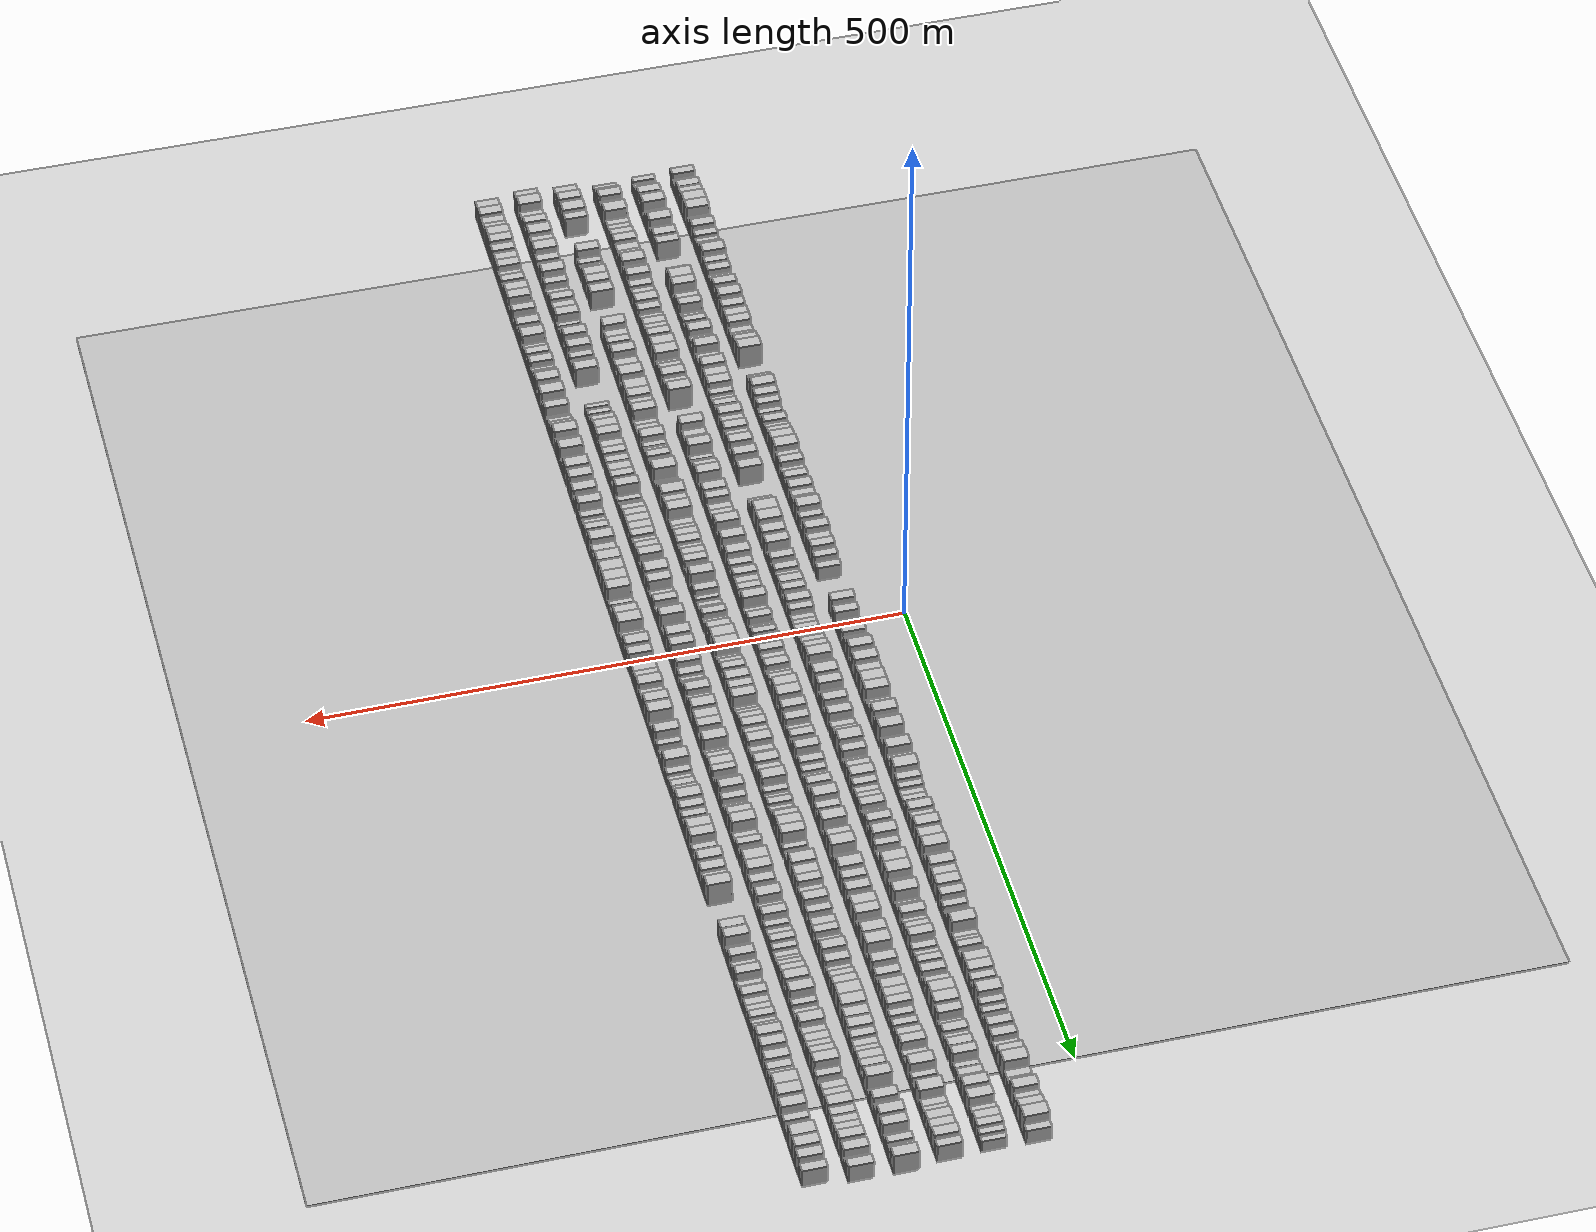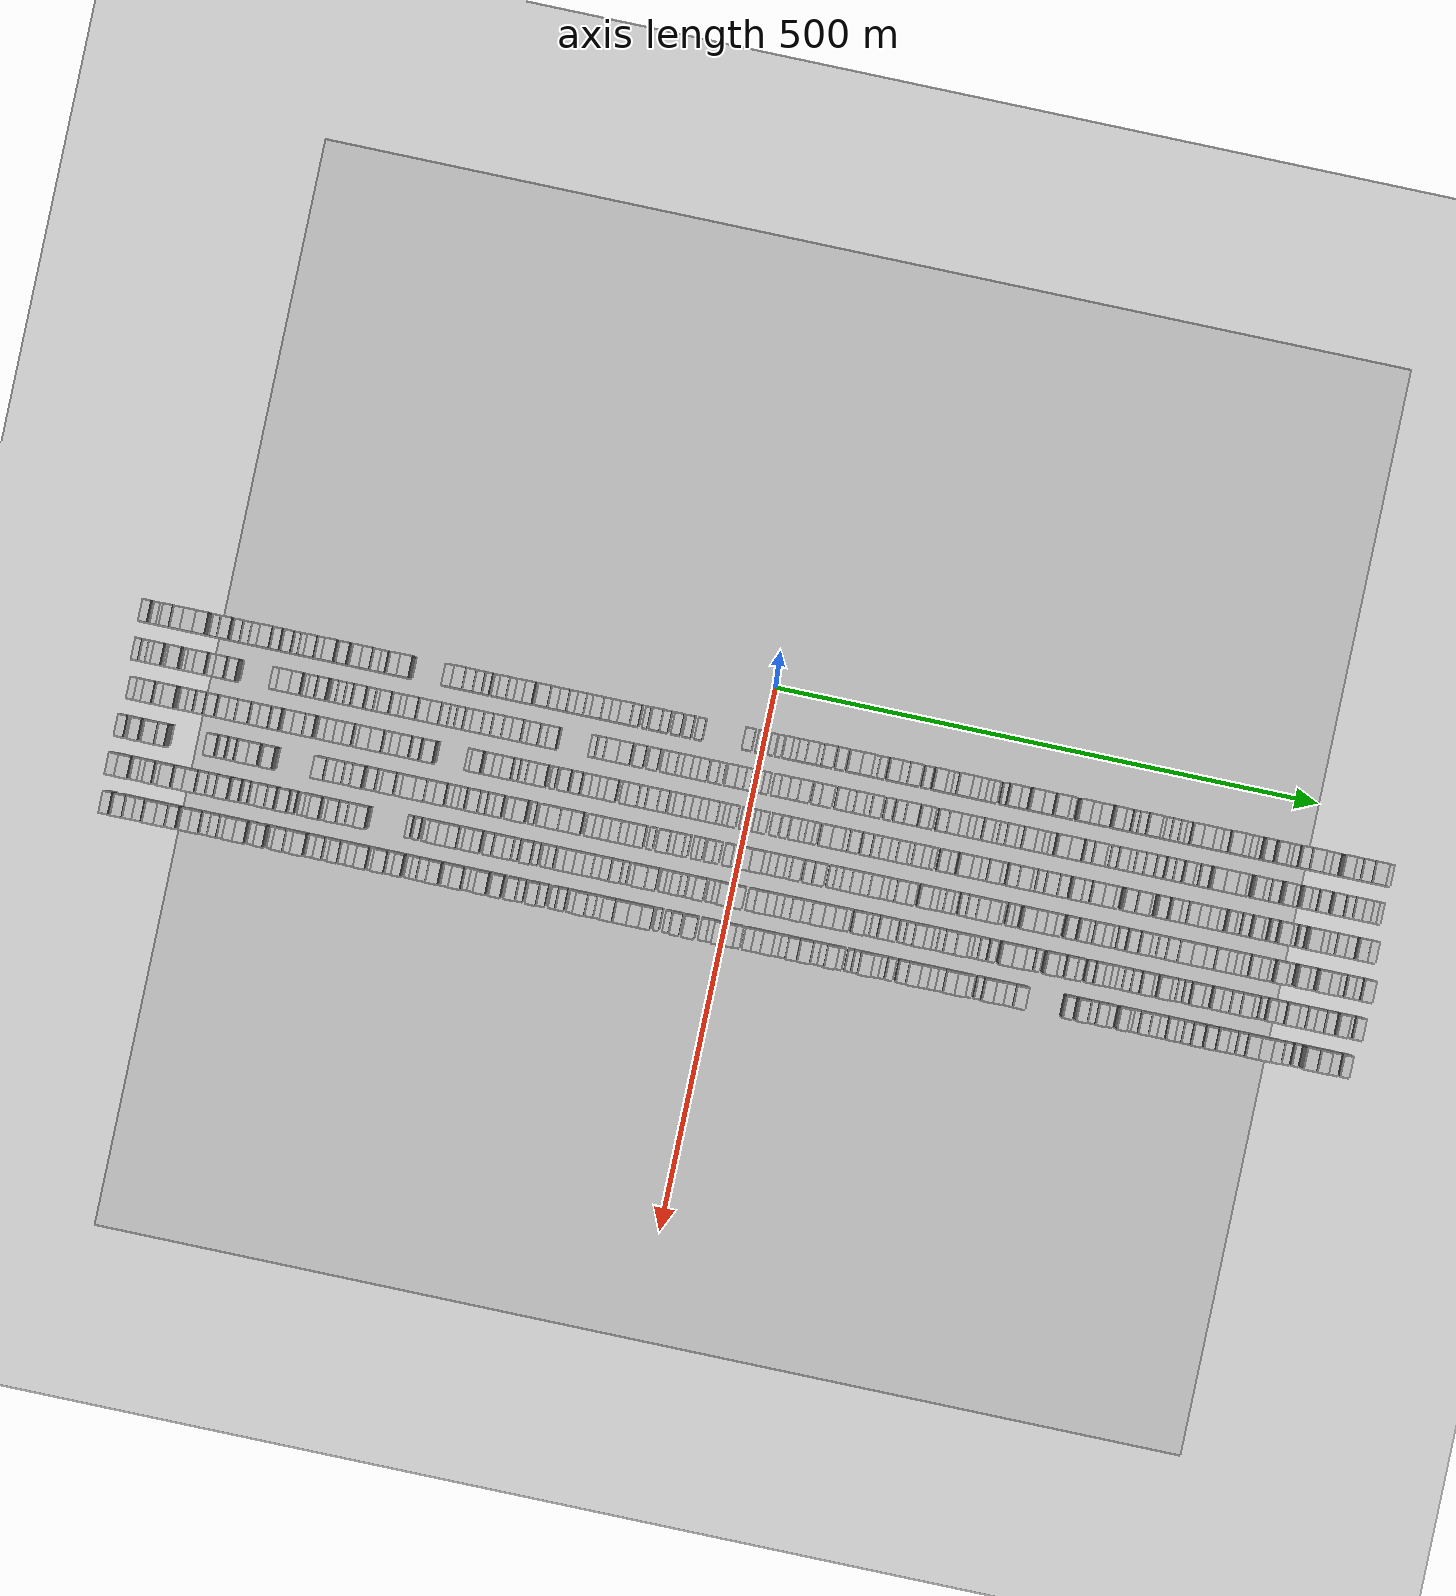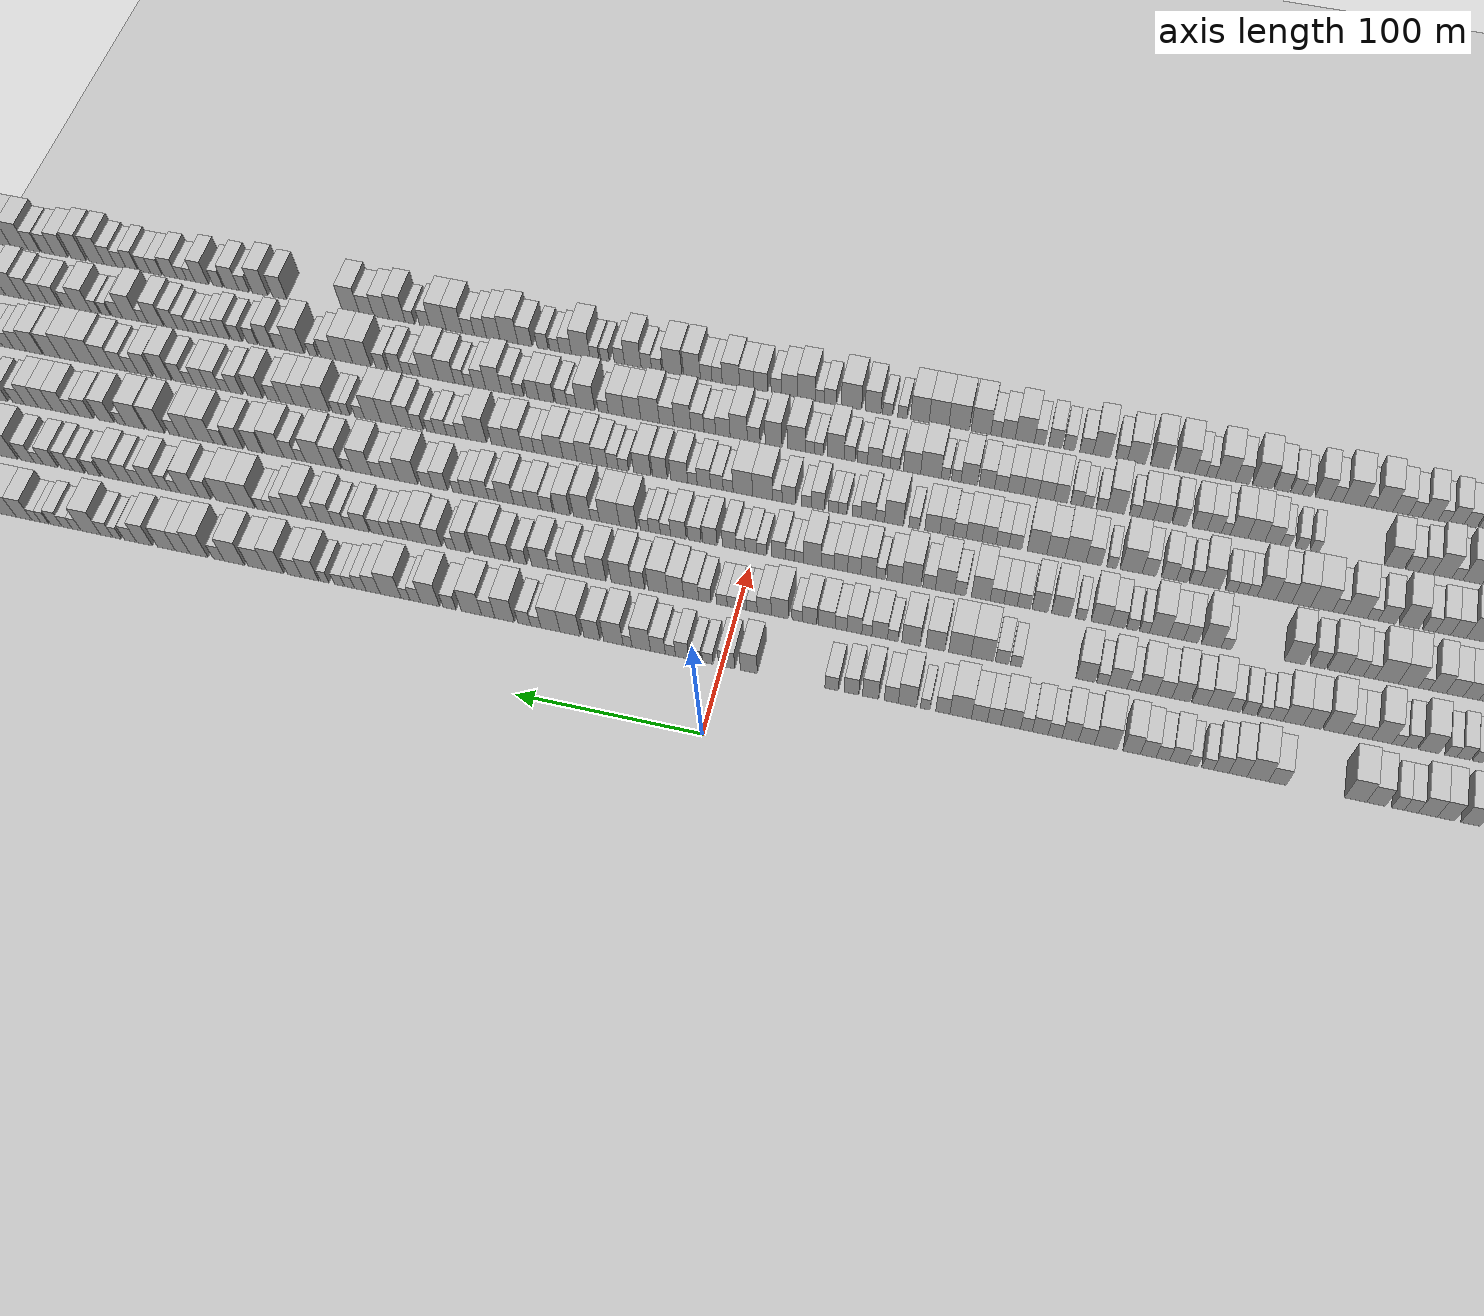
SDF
<?xml version="1.0" encoding="utf-8"?>

<sdf version="1.6">

   <world name="default">

      <gui fullscreen="0">

         <camera name="user_camera">

            <pose>-15 0 4.57585 0 0 0</pose>

            <view_controller>orbit</view_controller>

         </camera>

      </gui>

      <scene>

         <sky>

           <clouds>

             <speed>12</speed>

           </clouds>

         </sky>

         <ambient>0.4 0.4 0.4 1</ambient>

         <background>0.7 0.7 0.7 1</background>

         <shadows>1</shadows>

      </scene>

      <gravity>0 0 -9.8066</gravity>

      <magnetic_field>6e-06 2.3e-05 -4.2e-05</magnetic_field>

      <physics default="0" name="default_physics" type="ode">

         <ode>

            <solver>

               <type>quick</type>

               <iters>10</iters>

               <sor>1.0</sor>

               <use_dynamic_moi_rescaling>0</use_dynamic_moi_rescaling>

            </solver>

            <constraints>

               <cfm>0</cfm>

               <erp>0.2</erp>

               <contact_max_correcting_vel>100</contact_max_correcting_vel>

               <contact_surface_layer>0.001</contact_surface_layer>

            </constraints>

         </ode>

         <max_step_size>0.004</max_step_size>

         <real_time_factor>1</real_time_factor>

         <real_time_update_rate>250</real_time_update_rate>

      </physics>

      <light name="sun" type="directional">

         <cast_shadows>1</cast_shadows>

         <pose>0 0 10 0 0 0</pose>

         <diffuse>0.8 0.8 0.8 1</diffuse>

         <specular>0.2 0.2 0.2 1</specular>

         <attenuation>

            <range>1000</range>

            <constant>0.9</constant>

            <linear>0.01</linear>

            <quadratic>0.001</quadratic>

         </attenuation>

         <direction>-0.5 0.1 -0.9</direction>

      </light>

      <include>

         <name>ground_plane_1</name>

         <uri>model://HANNAS_ground_plane</uri>

         <pose>0 0 0  0 0 0</pose>

      </include>

      <include>

         <name>ground_plane_2</name>

         <uri>model://HANNAS_ground_plane</uri>

         <pose>100 0 0  0 0 0</pose>

      </include>

      <model name="building_1">

         <static>1</static>

         <pose frame="">50.0000 -565.9757 0 0.000000 0.000000 0.000000</pose>

         <link name="link">

            <pose frame="">0 0 9.00 0 0 0</pose>

            <collision name="collision">

               <geometry>

                  <box>

                     <size>20.0000 8.0485 18.0000</size>

                  </box>

               </geometry>

               <max_contacts>10</max_contacts>

               <surface>

                  <contact>

                     <ode/>

                  </contact>

                  <bounce/>

                  <friction>

                     <torsional>

                        <ode/>

                     </torsional>

                     <ode/>

                  </friction>

               </surface>

            </collision>

            <visual name="visual">

               <cast_shadows>0</cast_shadows>

               <geometry>

                  <box>

                     <size>20.0000 8.0485 18.0000</size>

                  </box>

               </geometry>

               <material>

                  <script>

                     <uri>model://HANNAS_wall/materials/scripts</uri>

                     <uri>model://HANNAS_wall/materials/textures</uri>

                     <name>vrc/HANNAS_wall</name>

                  </script>

               </material>

            </visual>

            <self_collide>0</self_collide>

            <enable_wind>0</enable_wind>

            <kinematic>0</kinematic>

         </link>

      </model>

      <model name="building_2">

         <static>1</static>

         <pose frame="">50.0000 -558.2053 0 0.000000 0.000000 0.000000</pose>

         <link name="link">

            <pose frame="">0 0 6.00 0 0 0</pose>

            <collision name="collision">

               <geometry>

                  <box>

                     <size>20.0000 5.4924 12.0000</size>

                  </box>

               </geometry>

               <max_contacts>10</max_contacts>

               <surface>

                  <contact>

                     <ode/>

                  </contact>

                  <bounce/>

                  <friction>

                     <torsional>

                        <ode/>

                     </torsional>

                     <ode/>

                  </friction>

               </surface>

            </collision>

            <visual name="visual">

               <cast_shadows>0</cast_shadows>

               <geometry>

                  <box>

                     <size>20.0000 5.4924 12.0000</size>

                  </box>

               </geometry>

               <material>

                  <script>

                     <uri>model://HANNAS_wall/materials/scripts</uri>

                     <uri>model://HANNAS_wall/materials/textures</uri>

                     <name>vrc/HANNAS_wall</name>

                  </script>

               </material>

            </visual>

            <self_collide>0</self_collide>

            <enable_wind>0</enable_wind>

            <kinematic>0</kinematic>

         </link>

      </model>

      <model name="building_3">

         <static>1</static>

         <pose frame="">50.0000 -552.8740 0 0.000000 0.000000 0.000000</pose>

         <link name="link">

            <pose frame="">0 0 6.00 0 0 0</pose>

            <collision name="collision">

               <geometry>

                  <box>

                     <size>20.0000 5.1701 12.0000</size>

                  </box>

               </geometry>

               <max_contacts>10</max_contacts>

               <surface>

                  <contact>

                     <ode/>

                  </contact>

                  <bounce/>

                  <friction>

                     <torsional>

                        <ode/>

                     </torsional>

                     <ode/>

                  </friction>

               </surface>

            </collision>

            <visual name="visual">

               <cast_shadows>0</cast_shadows>

               <geometry>

                  <box>

                     <size>20.0000 5.1701 12.0000</size>

                  </box>

               </geometry>

               <material>

                  <script>

                     <uri>model://HANNAS_wall/materials/scripts</uri>

                     <uri>model://HANNAS_wall/materials/textures</uri>

                     <name>vrc/HANNAS_wall</name>

                  </script>

               </material>

            </visual>

            <self_collide>0</self_collide>

            <enable_wind>0</enable_wind>

            <kinematic>0</kinematic>

         </link>

      </model>

      <model name="building_4">

         <static>1</static>

         <pose frame="">50.0000 -545.7942 0 0.000000 0.000000 0.000000</pose>

         <link name="link">

            <pose frame="">0 0 10.50 0 0 0</pose>

            <collision name="collision">

               <geometry>

                  <box>

                     <size>20.0000 8.9897 21.0000</size>

                  </box>

               </geometry>

               <max_contacts>10</max_contacts>

               <surface>

                  <contact>

                     <ode/>

                  </contact>

                  <bounce/>

                  <friction>

                     <torsional>

                        <ode/>

                     </torsional>

                     <ode/>

                  </friction>

               </surface>

            </collision>

            <visual name="visual">

               <cast_shadows>0</cast_shadows>

               <geometry>

                  <box>

                     <size>20.0000 8.9897 21.0000</size>

                  </box>

               </geometry>

               <material>

                  <script>

                     <uri>model://HANNAS_wall/materials/scripts</uri>

                     <uri>model://HANNAS_wall/materials/textures</uri>

                     <name>vrc/HANNAS_wall</name>

                  </script>

               </material>

            </visual>

            <self_collide>0</self_collide>

            <enable_wind>0</enable_wind>

            <kinematic>0</kinematic>

         </link>

      </model>

      <model name="building_5">

         <static>1</static>

         <pose frame="">50.0000 -535.4108 0 0.000000 0.000000 0.000000</pose>

         <link name="link">

            <pose frame="">0 0 10.50 0 0 0</pose>

            <collision name="collision">

               <geometry>

                  <box>

                     <size>20.0000 9.7772 21.0000</size>

                  </box>

               </geometry>

               <max_contacts>10</max_contacts>

               <surface>

                  <contact>

                     <ode/>

                  </contact>

                  <bounce/>

                  <friction>

                     <torsional>

                        <ode/>

                     </torsional>

                     <ode/>

                  </friction>

               </surface>

            </collision>

            <visual name="visual">

               <cast_shadows>0</cast_shadows>

               <geometry>

                  <box>

                     <size>20.0000 9.7772 21.0000</size>

                  </box>

               </geometry>

               <material>

                  <script>

                     <uri>model://HANNAS_wall/materials/scripts</uri>

                     <uri>model://HANNAS_wall/materials/textures</uri>

                     <name>vrc/HANNAS_wall</name>

                  </script>

               </material>

            </visual>

            <self_collide>0</self_collide>

            <enable_wind>0</enable_wind>

            <kinematic>0</kinematic>

         </link>

      </model>

      <model name="building_6">

         <static>1</static>

         <pose frame="">50.0000 -524.9130 0 0.000000 0.000000 0.000000</pose>

         <link name="link">

            <pose frame="">0 0 12.00 0 0 0</pose>

            <collision name="collision">

               <geometry>

                  <box>

                     <size>20.0000 11.2183 24.0000</size>

                  </box>

               </geometry>

               <max_contacts>10</max_contacts>

               <surface>

                  <contact>

                     <ode/>

                  </contact>

                  <bounce/>

                  <friction>

                     <torsional>

                        <ode/>

                     </torsional>

                     <ode/>

                  </friction>

               </surface>

            </collision>

            <visual name="visual">

               <cast_shadows>0</cast_shadows>

               <geometry>

                  <box>

                     <size>20.0000 11.2183 24.0000</size>

                  </box>

               </geometry>

               <material>

                  <script>

                     <uri>model://HANNAS_wall/materials/scripts</uri>

                     <uri>model://HANNAS_wall/materials/textures</uri>

                     <name>vrc/HANNAS_wall</name>

                  </script>

               </material>

            </visual>

            <self_collide>0</self_collide>

            <enable_wind>0</enable_wind>

            <kinematic>0</kinematic>

         </link>

      </model>

      <model name="building_7">

         <static>1</static>

         <pose frame="">50.0000 -513.6335 0 0.000000 0.000000 0.000000</pose>

         <link name="link">

            <pose frame="">0 0 12.00 0 0 0</pose>

            <collision name="collision">

               <geometry>

                  <box>

                     <size>20.0000 11.3407 24.0000</size>

                  </box>

               </geometry>

               <max_contacts>10</max_contacts>

               <surface>

                  <contact>

                     <ode/>

                  </contact>

                  <bounce/>

                  <friction>

                     <torsional>

                        <ode/>

                     </torsional>

                     <ode/>

                  </friction>

               </surface>

            </collision>

            <visual name="visual">

               <cast_shadows>0</cast_shadows>

               <geometry>

                  <box>

                     <size>20.0000 11.3407 24.0000</size>

                  </box>

               </geometry>

               <material>

                  <script>

                     <uri>model://HANNAS_wall/materials/scripts</uri>

                     <uri>model://HANNAS_wall/materials/textures</uri>

                     <name>vrc/HANNAS_wall</name>

                  </script>

               </material>

            </visual>

            <self_collide>0</self_collide>

            <enable_wind>0</enable_wind>

            <kinematic>0</kinematic>

         </link>

      </model>

      <model name="building_8">

         <static>1</static>

         <pose frame="">50.0000 -502.5343 0 0.000000 0.000000 0.000000</pose>

         <link name="link">

            <pose frame="">0 0 7.50 0 0 0</pose>

            <collision name="collision">

               <geometry>

                  <box>

                     <size>20.0000 6.8578 15.0000</size>

                  </box>

               </geometry>

               <max_contacts>10</max_contacts>

               <surface>

                  <contact>

                     <ode/>

                  </contact>

                  <bounce/>

                  <friction>

                     <torsional>

                        <ode/>

                     </torsional>

                     <ode/>

                  </friction>

               </surface>

            </collision>

            <visual name="visual">

               <cast_shadows>0</cast_shadows>

               <geometry>

                  <box>

                     <size>20.0000 6.8578 15.0000</size>

                  </box>

               </geometry>

               <material>

                  <script>

                     <uri>model://HANNAS_wall/materials/scripts</uri>

                     <uri>model://HANNAS_wall/materials/textures</uri>

                     <name>vrc/HANNAS_wall</name>

                  </script>

               </material>

            </visual>

            <self_collide>0</self_collide>

            <enable_wind>0</enable_wind>

            <kinematic>0</kinematic>

         </link>

      </model>

      <model name="building_9">

         <static>1</static>

         <pose frame="">50.0000 -492.2488 0 0.000000 0.000000 0.000000</pose>

         <link name="link">

            <pose frame="">0 0 10.50 0 0 0</pose>

            <collision name="collision">

               <geometry>

                  <box>

                     <size>20.0000 9.7132 21.0000</size>

                  </box>

               </geometry>

               <max_contacts>10</max_contacts>

               <surface>

                  <contact>

                     <ode/>

                  </contact>

                  <bounce/>

                  <friction>

                     <torsional>

                        <ode/>

                     </torsional>

                     <ode/>

                  </friction>

               </surface>

            </collision>

            <visual name="visual">

               <cast_shadows>0</cast_shadows>

               <geometry>

                  <box>

                     <size>20.0000 9.7132 21.0000</size>

                  </box>

               </geometry>

               <material>

                  <script>

                     <uri>model://HANNAS_wall/materials/scripts</uri>

                     <uri>model://HANNAS_wall/materials/textures</uri>

                     <name>vrc/HANNAS_wall</name>

                  </script>

               </material>

            </visual>

            <self_collide>0</self_collide>

            <enable_wind>0</enable_wind>

            <kinematic>0</kinematic>

         </link>

      </model>

      <model name="building_10">

         <static>1</static>

         <pose frame="">50.0000 -481.5132 0 0.000000 0.000000 0.000000</pose>

         <link name="link">

            <pose frame="">0 0 9.00 0 0 0</pose>

            <collision name="collision">

               <geometry>

                  <box>

                     <size>20.0000 7.7580 18.0000</size>

                  </box>

               </geometry>

               <max_contacts>10</max_contacts>

               <surface>

                  <contact>

                     <ode/>

                  </contact>

                  <bounce/>

                  <friction>

                     <torsional>

                        <ode/>

                     </torsional>

                     <ode/>

                  </friction>

               </surface>

            </collision>

            <visual name="visual">

               <cast_shadows>0</cast_shadows>

               <geometry>

                  <box>

                     <size>20.0000 7.7580 18.0000</size>

                  </box>

               </geometry>

               <material>

                  <script>

                     <uri>model://HANNAS_wall/materials/scripts</uri>

                     <uri>model://HANNAS_wall/materials/textures</uri>

                     <name>vrc/HANNAS_wall</name>

                  </script>

               </material>

            </visual>

            <self_collide>0</self_collide>

            <enable_wind>0</enable_wind>

            <kinematic>0</kinematic>

         </link>

      </model>

      <model name="building_11">

         <static>1</static>

         <pose frame="">50.0000 -474.0411 0 0.000000 0.000000 0.000000</pose>

         <link name="link">

            <pose frame="">0 0 7.50 0 0 0</pose>

            <collision name="collision">

               <geometry>

                  <box>

                     <size>20.0000 7.1861 15.0000</size>

                  </box>

               </geometry>

               <max_contacts>10</max_contacts>

               <surface>

                  <contact>

                     <ode/>

                  </contact>

                  <bounce/>

                  <friction>

                     <torsional>

                        <ode/>

                     </torsional>

                     <ode/>

                  </friction>

               </surface>

            </collision>

            <visual name="visual">

               <cast_shadows>0</cast_shadows>

               <geometry>

                  <box>

                     <size>20.0000 7.1861 15.0000</size>

                  </box>

               </geometry>

               <material>

                  <script>

                     <uri>model://HANNAS_wall/materials/scripts</uri>

                     <uri>model://HANNAS_wall/materials/textures</uri>

                     <name>vrc/HANNAS_wall</name>

                  </script>

               </material>

            </visual>

            <self_collide>0</self_collide>

            <enable_wind>0</enable_wind>

            <kinematic>0</kinematic>

         </link>

      </model>

      <model name="building_12">

         <static>1</static>

         <pose frame="">50.0000 -465.1681 0 0.000000 0.000000 0.000000</pose>

         <link name="link">

            <pose frame="">0 0 9.00 0 0 0</pose>

            <collision name="collision">

               <geometry>

                  <box>

                     <size>20.0000 8.5598 18.0000</size>

                  </box>

               </geometry>

               <max_contacts>10</max_contacts>

               <surface>

                  <contact>

                     <ode/>

                  </contact>

                  <bounce/>

                  <friction>

                     <torsional>

                        <ode/>

                     </torsional>

                     <ode/>

                  </friction>

               </surface>

            </collision>

            <visual name="visual">

               <cast_shadows>0</cast_shadows>

               <geometry>

                  <box>

                     <size>20.0000 8.5598 18.0000</size>

                  </box>

               </geometry>

               <material>

                  <script>

                     <uri>model://HANNAS_wall/materials/scripts</uri>

                     <uri>model://HANNAS_wall/materials/textures</uri>

                     <name>vrc/HANNAS_wall</name>

                  </script>

               </material>

            </visual>

            <self_collide>0</self_collide>

            <enable_wind>0</enable_wind>

            <kinematic>0</kinematic>

         </link>

      </model>

      <model name="building_13">

         <static>1</static>

         <pose frame="">50.0000 -455.2533 0 0.000000 0.000000 0.000000</pose>

         <link name="link">

            <pose frame="">0 0 12.00 0 0 0</pose>

            <collision name="collision">

               <geometry>

                  <box>

                     <size>20.0000 11.2698 24.0000</size>

                  </box>

               </geometry>

               <max_contacts>10</max_contacts>

               <surface>

                  <contact>

                     <ode/>

                  </contact>

                  <bounce/>

                  <friction>

                     <torsional>

                        <ode/>

                     </torsional>

                     <ode/>

                  </friction>

               </surface>

            </collision>

            <visual name="visual">

               <cast_shadows>0</cast_shadows>

               <geometry>

                  <box>

                     <size>20.0000 11.2698 24.0000</size>

                  </box>

               </geometry>

               <material>

                  <script>

                     <uri>model://HANNAS_wall/materials/scripts</uri>

                     <uri>model://HANNAS_wall/materials/textures</uri>

                     <name>vrc/HANNAS_wall</name>

                  </script>

               </material>

            </visual>

            <self_collide>0</self_collide>

            <enable_wind>0</enable_wind>

            <kinematic>0</kinematic>

         </link>

      </model>

      <model name="building_14">

         <static>1</static>

         <pose frame="">50.0000 -445.6927 0 0.000000 0.000000 0.000000</pose>

         <link name="link">

            <pose frame="">0 0 9.00 0 0 0</pose>

            <collision name="collision">

               <geometry>

                  <box>

                     <size>20.0000 7.8514 18.0000</size>

                  </box>

               </geometry>

               <max_contacts>10</max_contacts>

               <surface>

                  <contact>

                     <ode/>

                  </contact>

                  <bounce/>

                  <friction>

                     <torsional>

                        <ode/>

                     </torsional>

                     <ode/>

                  </friction>

               </surface>

            </collision>

            <visual name="visual">

               <cast_shadows>0</cast_shadows>

               <geometry>

                  <box>

                     <size>20.0000 7.8514 18.0000</size>

                  </box>

               </geometry>

               <material>

                  <script>

                     <uri>model://HANNAS_wall/materials/scripts</uri>

                     <uri>model://HANNAS_wall/materials/textures</uri>

                     <name>vrc/HANNAS_wall</name>

                  </script>

               </material>

            </visual>

            <self_collide>0</self_collide>

            <enable_wind>0</enable_wind>

            <kinematic>0</kinematic>

         </link>

      </model>

      <model name="building_15">

         <static>1</static>

         <pose frame="">50.0000 -435.5037 0 0.000000 0.000000 0.000000</pose>

         <link name="link">

            <pose frame="">0 0 9.00 0 0 0</pose>

            <collision name="collision">

               <geometry>

                  <box>

                     <size>20.0000 8.5266 18.0000</size>

                  </box>

               </geometry>

               <max_contacts>10</max_contacts>

               <surface>

                  <contact>

                     <ode/>

                  </contact>

                  <bounce/>

                  <friction>

                     <torsional>

                        <ode/>

                     </torsional>

                     <ode/>

                  </friction>

               </surface>

            </collision>

            <visual name="visual">

               <cast_shadows>0</cast_shadows>

               <geometry>

                  <box>

                     <size>20.0000 8.5266 18.0000</size>

                  </box>

               </geometry>

               <material>

                  <script>

                     <uri>model://HANNAS_wall/materials/scripts</uri>

                     <uri>model://HANNAS_wall/materials/textures</uri>

                     <name>vrc/HANNAS_wall</name>

                  </script>

               </material>

            </visual>

            <self_collide>0</self_collide>

            <enable_wind>0</enable_wind>

            <kinematic>0</kinematic>

         </link>

      </model>

      <model name="building_16">

         <static>1</static>

         <pose frame="">50.0000 -428.6099 0 0.000000 0.000000 0.000000</pose>

         <link name="link">

            <pose frame="">0 0 6.00 0 0 0</pose>

            <collision name="collision">

               <geometry>

                  <box>

                     <size>20.0000 5.2610 12.0000</size>

                  </box>

               </geometry>

               <max_contacts>10</max_contacts>

               <surface>

                  <contact>

                     <ode/>

                  </contact>

                  <bounce/>

                  <friction>

                     <torsional>

                        <ode/>

                     </torsional>

                     <ode/>

                  </friction>

               </surface>

            </collision>

            <visual name="visual">

               <cast_shadows>0</cast_shadows>

               <geometry>

                  <box>

                     <size>20.0000 5.2610 12.0000</size>

                  </box>

               </geometry>

               <material>

                  <script>

                     <uri>model://HANNAS_wall/materials/scripts</uri>

                     <uri>model://HANNAS_wall/materials/textures</uri>

                     <name>vrc/HANNAS_wall</name>

                  </script>

               </material>

            </visual>

            <self_collide>0</self_collide>

            <enable_wind>0</enable_wind>

            <kinematic>0</kinematic>

         </link>

      </model>

      <model name="building_17">

         <static>1</static>

         <pose frame="">50.0000 -421.8462 0 0.000000 0.000000 0.000000</pose>

         <link name="link">

            <pose frame="">0 0 7.50 0 0 0</pose>

            <collision name="collision">

               <geometry>

                  <box>

                     <size>20.0000 6.2665 15.0000</size>

                  </box>

               </geometry>

               <max_contacts>10</max_contacts>

               <surface>

                  <contact>

                     <ode/>

                  </contact>

                  <bounce/>

                  <friction>

                     <torsional>

                        <ode/>

                     </torsional>

                     <ode/>

                  </friction>

               </surface>

            </collision>

            <visual name="visual">

               <cast_shadows>0</cast_shadows>

               <geometry>

                  <box>

                     <size>20.0000 6.2665 15.0000</size>

                  </box>

               </geometry>

               <material>

                  <script>

                     <uri>model://HANNAS_wall/materials/scripts</uri>

                     <uri>model://HANNAS_wall/materials/textures</uri>

                     <name>vrc/HANNAS_wall</name>

                  </script>

               </material>

            </visual>

            <self_collide>0</self_collide>

            <enable_wind>0</enable_wind>

            <kinematic>0</kinematic>

         </link>

      </model>

      <model name="building_18">

         <static>1</static>

         <pose frame="">50.0000 -414.1293 0 0.000000 0.000000 0.000000</pose>

         <link name="link">

            <pose frame="">0 0 10.50 0 0 0</pose>

            <collision name="collision">

               <geometry>

                  <box>

                     <size>20.0000 9.1672 21.0000</size>

                  </box>

               </geometry>

               <max_contacts>10</max_contacts>

               <surface>

                  <contact>

                     <ode/>

                  </contact>

                  <bounce/>

                  <friction>

                     <torsional>

                        <ode/>

                     </torsional>

                     <ode/>

                  </friction>

               </surface>

            </collision>

            <visual name="visual">

               <cast_shadows>0</cast_shadows>

               <geometry>

                  <box>

                     <size>20.0000 9.1672 21.0000</size>

                  </box>

               </geometry>

               <material>

                  <script>

                     <uri>model://HANNAS_wall/materials/scripts</uri>

                     <uri>model://HANNAS_wall/materials/textures</uri>

                     <name>vrc/HANNAS_wall</name>

                  </script>

               </material>

            </visual>

            <self_collide>0</self_collide>

            <enable_wind>0</enable_wind>

            <kinematic>0</kinematic>

         </link>

      </model>

      <model name="building_19">

         <static>1</static>

         <pose frame="">50.0000 -405.8031 0 0.000000 0.000000 0.000000</pose>

         <link name="link">

            <pose frame="">0 0 7.50 0 0 0</pose>

            <collision name="collision">

               <geometry>

                  <box>

                     <size>20.0000 7.4852 15.0000</size>

                  </box>

               </geometry>

               <max_contacts>10</max_contacts>

               <surface>

                  <contact>

                     <ode/>

                  </contact>

                  <bounce/>

                  <friction>

                     <torsional>

                        <ode/>

                     </torsional>

                     <ode/>

                  </friction>

               </surface>

            </collision>

            <visual name="visual">

               <cast_shadows>0</cast_shadows>

               <geometry>

                  <box>

                     <size>20.0000 7.4852 15.0000</size>

                  </box>

               </geometry>

               <material>

                  <script>

                     <uri>model://HANNAS_wall/materials/scripts</uri>

                     <uri>model://HANNAS_wall/materials/textures</uri>

                     <name>vrc/HANNAS_wall</name>

                  </script>

               </material>

            </visual>

            <self_collide>0</self_collide>

            <enable_wind>0</enable_wind>

            <kinematic>0</kinematic>

         </link>

      </model>

      <model name="building_20">

         <static>1</static>

         <pose frame="">50.0000 -396.5581 0 0.000000 0.000000 0.000000</pose>

         <link name="link">

            <pose frame="">0 0 12.00 0 0 0</pose>

            <collision name="collision">

               <geometry>

                  <box>

                     <size>20.0000 11.0049 24.0000</size>

                  </box>

               </geometry>

               <max_contacts>10</max_contacts>

               <surface>

                  <contact>

                     <ode/>

                  </contact>

                  <bounce/>

                  <friction>

                     <torsional>

                        <ode/>

                     </torsional>

                     <ode/>

                  </friction>

               </surface>

            </collision>

            <visual name="visual">

               <cast_shadows>0</cast_shadows>

               <geometry>

                  <box>

                     <size>20.0000 11.0049 24.0000</size>

                  </box>

               </geometry>

               <material>

                  <script>

                     <uri>model://HANNAS_wall/materials/scripts</uri>

                     <uri>model://HANNAS_wall/materials/textures</uri>

                     <name>vrc/HANNAS_wall</name>

                  </script>

               </material>

            </visual>

            <self_collide>0</self_collide>

            <enable_wind>0</enable_wind>

            <kinematic>0</kinematic>

         </link>

      </model>

      <model name="building_21">

         <static>1</static>

         <pose frame="">50.0000 -384.4108 0 0.000000 0.000000 0.000000</pose>

         <link name="link">

            <pose frame="">0 0 10.50 0 0 0</pose>

            <collision name="collision">

               <geometry>

                  <box>

                     <size>20.0000 9.2897 21.0000</size>

                  </box>

               </geometry>

               <max_contacts>10</max_contacts>

               <surface>

                  <contact>

                     <ode/>

                  </contact>

                  <bounce/>

                  <friction>

                     <torsional>

                        <ode/>

                     </torsional>

                     <ode/>

                  </friction>

               </surface>

            </collision>

            <visual name="visual">

               <cast_shadows>0</cast_shadows>

               <geometry>

                  <box>

                     <size>20.0000 9.2897 21.0000</size>

                  </box>

               </geometry>

               <material>

                  <script>

                     <uri>model://HANNAS_wall/materials/scripts</uri>

                     <uri>model://HANNAS_wall/materials/textures</uri>

                     <name>vrc/HANNAS_wall</name>

                  </script>

               </material>

            </visual>

            <self_collide>0</self_collide>

            <enable_wind>0</enable_wind>

            <kinematic>0</kinematic>

         </link>

      </model>

      <model name="building_22">

         <static>1</static>

         <pose frame="">50.0000 -372.4358 0 0.000000 0.000000 0.000000</pose>

         <link name="link">

            <pose frame="">0 0 10.50 0 0 0</pose>

            <collision name="collision">

               <geometry>

                  <box>

                     <size>20.0000 8.6601 21.0000</size>

                  </box>

               </geometry>

               <max_contacts>10</max_contacts>

               <surface>

                  <contact>

                     <ode/>

                  </contact>

                  <bounce/>

                  <friction>

                     <torsional>

                        <ode/>

                     </torsional>

                     <ode/>

                  </friction>

               </surface>

            </collision>

            <visual name="visual">

               <cast_shadows>0</cast_shadows>

               <geometry>

                  <box>

                     <size>20.0000 8.6601 21.0000</size>

                  </box>

               </geometry>

               <material>

                  <script>

                     <uri>model://HANNAS_wall/materials/scripts</uri>

                     <uri>model://HANNAS_wall/materials/textures</uri>

                     <name>vrc/HANNAS_wall</name>

                  </script>

               </material>

            </visual>

            <self_collide>0</self_collide>

            <enable_wind>0</enable_wind>

            <kinematic>0</kinematic>

         </link>

      </model>

      <model name="building_23">

         <static>1</static>

         <pose frame="">50.0000 -363.3871 0 0.000000 0.000000 0.000000</pose>

         <link name="link">

            <pose frame="">0 0 10.50 0 0 0</pose>

            <collision name="collision">

               <geometry>

                  <box>

                     <size>20.0000 9.4374 21.0000</size>

                  </box>

               </geometry>

               <max_contacts>10</max_contacts>

               <surface>

                  <contact>

                     <ode/>

                  </contact>

                  <bounce/>

                  <friction>

                     <torsional>

                        <ode/>

                     </torsional>

                     <ode/>

                  </friction>

               </surface>

            </collision>

            <visual name="visual">

               <cast_shadows>0</cast_shadows>

               <geometry>

                  <box>

                     <size>20.0000 9.4374 21.0000</size>

                  </box>

               </geometry>

               <material>

                  <script>

                     <uri>model://HANNAS_wall/materials/scripts</uri>

                     <uri>model://HANNAS_wall/materials/textures</uri>

                     <name>vrc/HANNAS_wall</name>

                  </script>

               </material>

            </visual>

            <self_collide>0</self_collide>

            <enable_wind>0</enable_wind>

            <kinematic>0</kinematic>

         </link>

      </model>

      <model name="building_24">

         <static>1</static>

         <pose frame="">50.0000 -355.2598 0 0.000000 0.000000 0.000000</pose>

         <link name="link">

            <pose frame="">0 0 7.50 0 0 0</pose>

            <collision name="collision">

               <geometry>

                  <box>

                     <size>20.0000 6.8172 15.0000</size>

                  </box>

               </geometry>

               <max_contacts>10</max_contacts>

               <surface>

                  <contact>

                     <ode/>

                  </contact>

                  <bounce/>

                  <friction>

                     <torsional>

                        <ode/>

                     </torsional>

                     <ode/>

                  </friction>

               </surface>

            </collision>

            <visual name="visual">

               <cast_shadows>0</cast_shadows>

               <geometry>

                  <box>

                     <size>20.0000 6.8172 15.0000</size>

                  </box>

               </geometry>

               <material>

                  <script>

                     <uri>model://HANNAS_wall/materials/scripts</uri>

                     <uri>model://HANNAS_wall/materials/textures</uri>

                     <name>vrc/HANNAS_wall</name>

                  </script>

               </material>

            </visual>

            <self_collide>0</self_collide>

            <enable_wind>0</enable_wind>

            <kinematic>0</kinematic>

         </link>

      </model>

      <model name="building_25">

         <static>1</static>

         <pose frame="">50.0000 -348.7468 0 0.000000 0.000000 0.000000</pose>

         <link name="link">

            <pose frame="">0 0 7.50 0 0 0</pose>

            <collision name="collision">

               <geometry>

                  <box>

                     <size>20.0000 6.2089 15.0000</size>

                  </box>

               </geometry>

               <max_contacts>10</max_contacts>

               <surface>

                  <contact>

                     <ode/>

                  </contact>

                  <bounce/>

                  <friction>

                     <torsional>

                        <ode/>

                     </torsional>

                     <ode/>

                  </friction>

               </surface>

            </collision>

            <visual name="visual">

               <cast_shadows>0</cast_shadows>

               <geometry>

                  <box>

                     <size>20.0000 6.2089 15.0000</size>

                  </box>

               </geometry>

               <material>

                  <script>

                     <uri>model://HANNAS_wall/materials/scripts</uri>

                     <uri>model://HANNAS_wall/materials/textures</uri>

                     <name>vrc/HANNAS_wall</name>

                  </script>

               </material>

            </visual>

            <self_collide>0</self_collide>

            <enable_wind>0</enable_wind>

            <kinematic>0</kinematic>

         </link>

      </model>

      <model name="building_26">

         <static>1</static>

         <pose frame="">50.0000 -337.9815 0 0.000000 0.000000 0.000000</pose>

         <link name="link">

            <pose frame="">0 0 10.50 0 0 0</pose>

            <collision name="collision">

               <geometry>

                  <box>

                     <size>20.0000 9.3217 21.0000</size>

                  </box>

               </geometry>

               <max_contacts>10</max_contacts>

               <surface>

                  <contact>

                     <ode/>

                  </contact>

                  <bounce/>

                  <friction>

                     <torsional>

                        <ode/>

                     </torsional>

                     <ode/>

                  </friction>

               </surface>

            </collision>

            <visual name="visual">

               <cast_shadows>0</cast_shadows>

               <geometry>

                  <box>

                     <size>20.0000 9.3217 21.0000</size>

                  </box>

               </geometry>

               <material>

                  <script>

                     <uri>model://HANNAS_wall/materials/scripts</uri>

                     <uri>model://HANNAS_wall/materials/textures</uri>

                     <name>vrc/HANNAS_wall</name>

                  </script>

               </material>

            </visual>

            <self_collide>0</self_collide>

            <enable_wind>0</enable_wind>

            <kinematic>0</kinematic>

         </link>

      </model>

      <model name="building_27">

         <static>1</static>

         <pose frame="">50.0000 -327.7994 0 0.000000 0.000000 0.000000</pose>

         <link name="link">

            <pose frame="">0 0 12.00 0 0 0</pose>

            <collision name="collision">

               <geometry>

                  <box>

                     <size>20.0000 11.0424 24.0000</size>

                  </box>

               </geometry>

               <max_contacts>10</max_contacts>

               <surface>

                  <contact>

                     <ode/>

                  </contact>

                  <bounce/>

                  <friction>

                     <torsional>

                        <ode/>

                     </torsional>

                     <ode/>

                  </friction>

               </surface>

            </collision>

            <visual name="visual">

               <cast_shadows>0</cast_shadows>

               <geometry>

                  <box>

                     <size>20.0000 11.0424 24.0000</size>

                  </box>

               </geometry>

               <material>

                  <script>

                     <uri>model://HANNAS_wall/materials/scripts</uri>

                     <uri>model://HANNAS_wall/materials/textures</uri>

                     <name>vrc/HANNAS_wall</name>

                  </script>

               </material>

            </visual>

            <self_collide>0</self_collide>

            <enable_wind>0</enable_wind>

            <kinematic>0</kinematic>

         </link>

      </model>

      <model name="building_28">

         <static>1</static>

         <pose frame="">50.0000 -288.8033 0 0.000000 0.000000 0.000000</pose>

         <link name="link">

            <pose frame="">0 0 9.00 0 0 0</pose>

            <collision name="collision">

               <geometry>

                  <box>

                     <size>20.0000 8.9833 18.0000</size>

                  </box>

               </geometry>

               <max_contacts>10</max_contacts>

               <surface>

                  <contact>

                     <ode/>

                  </contact>

                  <bounce/>

                  <friction>

                     <torsional>

                        <ode/>

                     </torsional>

                     <ode/>

                  </friction>

               </surface>

            </collision>

            <visual name="visual">

               <cast_shadows>0</cast_shadows>

               <geometry>

                  <box>

                     <size>20.0000 8.9833 18.0000</size>

                  </box>

               </geometry>

               <material>

                  <script>

                     <uri>model://HANNAS_wall/materials/scripts</uri>

                     <uri>model://HANNAS_wall/materials/textures</uri>

                     <name>vrc/HANNAS_wall</name>

                  </script>

               </material>

            </visual>

            <self_collide>0</self_collide>

            <enable_wind>0</enable_wind>

            <kinematic>0</kinematic>

         </link>

      </model>

      <model name="building_29">

         <static>1</static>

         <pose frame="">50.0000 -278.8812 0 0.000000 0.000000 0.000000</pose>

         <link name="link">

            <pose frame="">0 0 12.00 0 0 0</pose>

            <collision name="collision">

               <geometry>

                  <box>

                     <size>20.0000 10.8609 24.0000</size>

                  </box>

               </geometry>

               <max_contacts>10</max_contacts>

               <surface>

                  <contact>

                     <ode/>

                  </contact>

                  <bounce/>

                  <friction>

                     <torsional>

                        <ode/>

                     </torsional>

                     <ode/>

                  </friction>

               </surface>

            </collision>

            <visual name="visual">

               <cast_shadows>0</cast_shadows>

               <geometry>

                  <box>

                     <size>20.0000 10.8609 24.0000</size>

                  </box>

               </geometry>

               <material>

                  <script>

                     <uri>model://HANNAS_wall/materials/scripts</uri>

                     <uri>model://HANNAS_wall/materials/textures</uri>

                     <name>vrc/HANNAS_wall</name>

                  </script>

               </material>

            </visual>

            <self_collide>0</self_collide>

            <enable_wind>0</enable_wind>

            <kinematic>0</kinematic>

         </link>

      </model>

      <model name="building_30">

         <static>1</static>

         <pose frame="">50.0000 -268.9282 0 0.000000 0.000000 0.000000</pose>

         <link name="link">

            <pose frame="">0 0 10.50 0 0 0</pose>

            <collision name="collision">

               <geometry>

                  <box>

                     <size>20.0000 9.0451 21.0000</size>

                  </box>

               </geometry>

               <max_contacts>10</max_contacts>

               <surface>

                  <contact>

                     <ode/>

                  </contact>

                  <bounce/>

                  <friction>

                     <torsional>

                        <ode/>

                     </torsional>

                     <ode/>

                  </friction>

               </surface>

            </collision>

            <visual name="visual">

               <cast_shadows>0</cast_shadows>

               <geometry>

                  <box>

                     <size>20.0000 9.0451 21.0000</size>

                  </box>

               </geometry>

               <material>

                  <script>

                     <uri>model://HANNAS_wall/materials/scripts</uri>

                     <uri>model://HANNAS_wall/materials/textures</uri>

                     <name>vrc/HANNAS_wall</name>

                  </script>

               </material>

            </visual>

            <self_collide>0</self_collide>

            <enable_wind>0</enable_wind>

            <kinematic>0</kinematic>

         </link>

      </model>

      <model name="building_31">

         <static>1</static>

         <pose frame="">50.0000 -260.5038 0 0.000000 0.000000 0.000000</pose>

         <link name="link">

            <pose frame="">0 0 9.00 0 0 0</pose>

            <collision name="collision">

               <geometry>

                  <box>

                     <size>20.0000 7.8036 18.0000</size>

                  </box>

               </geometry>

               <max_contacts>10</max_contacts>

               <surface>

                  <contact>

                     <ode/>

                  </contact>

                  <bounce/>

                  <friction>

                     <torsional>

                        <ode/>

                     </torsional>

                     <ode/>

                  </friction>

               </surface>

            </collision>

            <visual name="visual">

               <cast_shadows>0</cast_shadows>

               <geometry>

                  <box>

                     <size>20.0000 7.8036 18.0000</size>

                  </box>

               </geometry>

               <material>

                  <script>

                     <uri>model://HANNAS_wall/materials/scripts</uri>

                     <uri>model://HANNAS_wall/materials/textures</uri>

                     <name>vrc/HANNAS_wall</name>

                  </script>

               </material>

            </visual>

            <self_collide>0</self_collide>

            <enable_wind>0</enable_wind>

            <kinematic>0</kinematic>

         </link>

      </model>

      <model name="building_32">

         <static>1</static>

         <pose frame="">50.0000 -253.6218 0 0.000000 0.000000 0.000000</pose>

         <link name="link">

            <pose frame="">0 0 6.00 0 0 0</pose>

            <collision name="collision">

               <geometry>

                  <box>

                     <size>20.0000 5.9604 12.0000</size>

                  </box>

               </geometry>

               <max_contacts>10</max_contacts>

               <surface>

                  <contact>

                     <ode/>

                  </contact>

                  <bounce/>

                  <friction>

                     <torsional>

                        <ode/>

                     </torsional>

                     <ode/>

                  </friction>

               </surface>

            </collision>

            <visual name="visual">

               <cast_shadows>0</cast_shadows>

               <geometry>

                  <box>

                     <size>20.0000 5.9604 12.0000</size>

                  </box>

               </geometry>

               <material>

                  <script>

                     <uri>model://HANNAS_wall/materials/scripts</uri>

                     <uri>model://HANNAS_wall/materials/textures</uri>

                     <name>vrc/HANNAS_wall</name>

                  </script>

               </material>

            </visual>

            <self_collide>0</self_collide>

            <enable_wind>0</enable_wind>

            <kinematic>0</kinematic>

         </link>

      </model>

      <model name="building_33">

         <static>1</static>

         <pose frame="">50.0000 -245.7485 0 0.000000 0.000000 0.000000</pose>

         <link name="link">

            <pose frame="">0 0 6.00 0 0 0</pose>

            <collision name="collision">

               <geometry>

                  <box>

                     <size>20.0000 5.7862 12.0000</size>

                  </box>

               </geometry>

               <max_contacts>10</max_contacts>

               <surface>

                  <contact>

                     <ode/>

                  </contact>

                  <bounce/>

                  <friction>

                     <torsional>

                        <ode/>

                     </torsional>

                     <ode/>

                  </friction>

               </surface>

            </collision>

            <visual name="visual">

               <cast_shadows>0</cast_shadows>

               <geometry>

                  <box>

                     <size>20.0000 5.7862 12.0000</size>

                  </box>

               </geometry>

               <material>

                  <script>

                     <uri>model://HANNAS_wall/materials/scripts</uri>

                     <uri>model://HANNAS_wall/materials/textures</uri>

                     <name>vrc/HANNAS_wall</name>

                  </script>

               </material>

            </visual>

            <self_collide>0</self_collide>

            <enable_wind>0</enable_wind>

            <kinematic>0</kinematic>

         </link>

      </model>

      <model name="building_34">

         <static>1</static>

         <pose frame="">50.0000 -238.6031 0 0.000000 0.000000 0.000000</pose>

         <link name="link">

            <pose frame="">0 0 9.00 0 0 0</pose>

            <collision name="collision">

               <geometry>

                  <box>

                     <size>20.0000 8.5045 18.0000</size>

                  </box>

               </geometry>

               <max_contacts>10</max_contacts>

               <surface>

                  <contact>

                     <ode/>

                  </contact>

                  <bounce/>

                  <friction>

                     <torsional>

                        <ode/>

                     </torsional>

                     <ode/>

                  </friction>

               </surface>

            </collision>

            <visual name="visual">

               <cast_shadows>0</cast_shadows>

               <geometry>

                  <box>

                     <size>20.0000 8.5045 18.0000</size>

                  </box>

               </geometry>

               <material>

                  <script>

                     <uri>model://HANNAS_wall/materials/scripts</uri>

                     <uri>model://HANNAS_wall/materials/textures</uri>

                     <name>vrc/HANNAS_wall</name>

                  </script>

               </material>

            </visual>

            <self_collide>0</self_collide>

            <enable_wind>0</enable_wind>

            <kinematic>0</kinematic>

         </link>

      </model>

      <model name="building_35">

         <static>1</static>

         <pose frame="">50.0000 -230.8784 0 0.000000 0.000000 0.000000</pose>

         <link name="link">

            <pose frame="">0 0 7.50 0 0 0</pose>

            <collision name="collision">

               <geometry>

                  <box>

                     <size>20.0000 6.9451 15.0000</size>

                  </box>

               </geometry>

               <max_contacts>10</max_contacts>

               <surface>

                  <contact>

                     <ode/>

                  </contact>

                  <bounce/>

                  <friction>

                     <torsional>

                        <ode/>

                     </torsional>

                     <ode/>

                  </friction>

               </surface>

            </collision>

            <visual name="visual">

               <cast_shadows>0</cast_shadows>

               <geometry>

                  <box>

                     <size>20.0000 6.9451 15.0000</size>

                  </box>

               </geometry>

               <material>

                  <script>

                     <uri>model://HANNAS_wall/materials/scripts</uri>

                     <uri>model://HANNAS_wall/materials/textures</uri>

                     <name>vrc/HANNAS_wall</name>

                  </script>

               </material>

            </visual>

            <self_collide>0</self_collide>

            <enable_wind>0</enable_wind>

            <kinematic>0</kinematic>

         </link>

      </model>

      <model name="building_36">

         <static>1</static>

         <pose frame="">50.0000 -223.3864 0 0.000000 0.000000 0.000000</pose>

         <link name="link">

            <pose frame="">0 0 9.00 0 0 0</pose>

            <collision name="collision">

               <geometry>

                  <box>

                     <size>20.0000 8.0389 18.0000</size>

                  </box>

               </geometry>

               <max_contacts>10</max_contacts>

               <surface>

                  <contact>

                     <ode/>

                  </contact>

                  <bounce/>

                  <friction>

                     <torsional>

                        <ode/>

                     </torsional>

                     <ode/>

                  </friction>

               </surface>

            </collision>

            <visual name="visual">

               <cast_shadows>0</cast_shadows>

               <geometry>

                  <box>

                     <size>20.0000 8.0389 18.0000</size>

                  </box>

               </geometry>

               <material>

                  <script>

                     <uri>model://HANNAS_wall/materials/scripts</uri>

                     <uri>model://HANNAS_wall/materials/textures</uri>

                     <name>vrc/HANNAS_wall</name>

                  </script>

               </material>

            </visual>

            <self_collide>0</self_collide>

            <enable_wind>0</enable_wind>

            <kinematic>0</kinematic>

         </link>

      </model>

      <model name="building_37">

         <static>1</static>

         <pose frame="">50.0000 -214.9334 0 0.000000 0.000000 0.000000</pose>

         <link name="link">

            <pose frame="">0 0 10.50 0 0 0</pose>

            <collision name="collision">

               <geometry>

                  <box>

                     <size>20.0000 8.8670 21.0000</size>

                  </box>

               </geometry>

               <max_contacts>10</max_contacts>

               <surface>

                  <contact>

                     <ode/>

                  </contact>

                  <bounce/>

                  <friction>

                     <torsional>

                        <ode/>

                     </torsional>

                     <ode/>

                  </friction>

               </surface>

            </collision>

            <visual name="visual">

               <cast_shadows>0</cast_shadows>

               <geometry>

                  <box>

                     <size>20.0000 8.8670 21.0000</size>

                  </box>

               </geometry>

               <material>

                  <script>

                     <uri>model://HANNAS_wall/materials/scripts</uri>

                     <uri>model://HANNAS_wall/materials/textures</uri>

                     <name>vrc/HANNAS_wall</name>

                  </script>

               </material>

            </visual>

            <self_collide>0</self_collide>

            <enable_wind>0</enable_wind>

            <kinematic>0</kinematic>

         </link>

      </model>

      <model name="building_38">

         <static>1</static>

         <pose frame="">50.0000 -201.6796 0 0.000000 0.000000 0.000000</pose>

         <link name="link">

            <pose frame="">0 0 12.00 0 0 0</pose>

            <collision name="collision">

               <geometry>

                  <box>

                     <size>20.0000 11.6407 24.0000</size>

                  </box>

               </geometry>

               <max_contacts>10</max_contacts>

               <surface>

                  <contact>

                     <ode/>

                  </contact>

                  <bounce/>

                  <friction>

                     <torsional>

                        <ode/>

                     </torsional>

                     <ode/>

                  </friction>

               </surface>

            </collision>

            <visual name="visual">

               <cast_shadows>0</cast_shadows>

               <geometry>

                  <box>

                     <size>20.0000 11.6407 24.0000</size>

                  </box>

               </geometry>

               <material>

                  <script>

                     <uri>model://HANNAS_wall/materials/scripts</uri>

                     <uri>model://HANNAS_wall/materials/textures</uri>

                     <name>vrc/HANNAS_wall</name>

                  </script>

               </material>

            </visual>

            <self_collide>0</self_collide>

            <enable_wind>0</enable_wind>

            <kinematic>0</kinematic>

         </link>

      </model>

      <model name="building_39">

         <static>1</static>

         <pose frame="">50.0000 -191.7165 0 0.000000 0.000000 0.000000</pose>

         <link name="link">

            <pose frame="">0 0 9.00 0 0 0</pose>

            <collision name="collision">

               <geometry>

                  <box>

                     <size>20.0000 8.2855 18.0000</size>

                  </box>

               </geometry>

               <max_contacts>10</max_contacts>

               <surface>

                  <contact>

                     <ode/>

                  </contact>

                  <bounce/>

                  <friction>

                     <torsional>

                        <ode/>

                     </torsional>

                     <ode/>

                  </friction>

               </surface>

            </collision>

            <visual name="visual">

               <cast_shadows>0</cast_shadows>

               <geometry>

                  <box>

                     <size>20.0000 8.2855 18.0000</size>

                  </box>

               </geometry>

               <material>

                  <script>

                     <uri>model://HANNAS_wall/materials/scripts</uri>

                     <uri>model://HANNAS_wall/materials/textures</uri>

                     <name>vrc/HANNAS_wall</name>

                  </script>

               </material>

            </visual>

            <self_collide>0</self_collide>

            <enable_wind>0</enable_wind>

            <kinematic>0</kinematic>

         </link>

      </model>

      <model name="building_40">

         <static>1</static>

         <pose frame="">50.0000 -183.3514 0 0.000000 0.000000 0.000000</pose>

         <link name="link">

            <pose frame="">0 0 10.50 0 0 0</pose>

            <collision name="collision">

               <geometry>

                  <box>

                     <size>20.0000 8.4446 21.0000</size>

                  </box>

               </geometry>

               <max_contacts>10</max_contacts>

               <surface>

                  <contact>

                     <ode/>

                  </contact>

                  <bounce/>

                  <friction>

                     <torsional>

                        <ode/>

                     </torsional>

                     <ode/>

                  </friction>

               </surface>

            </collision>

            <visual name="visual">

               <cast_shadows>0</cast_shadows>

               <geometry>

                  <box>

                     <size>20.0000 8.4446 21.0000</size>

                  </box>

               </geometry>

               <material>

                  <script>

                     <uri>model://HANNAS_wall/materials/scripts</uri>

                     <uri>model://HANNAS_wall/materials/textures</uri>

                     <name>vrc/HANNAS_wall</name>

                  </script>

               </material>

            </visual>

            <self_collide>0</self_collide>

            <enable_wind>0</enable_wind>

            <kinematic>0</kinematic>

         </link>

      </model>

      <model name="building_41">

         <static>1</static>

         <pose frame="">50.0000 -175.5534 0 0.000000 0.000000 0.000000</pose>

         <link name="link">

            <pose frame="">0 0 7.50 0 0 0</pose>

            <collision name="collision">

               <geometry>

                  <box>

                     <size>20.0000 7.1515 15.0000</size>

                  </box>

               </geometry>

               <max_contacts>10</max_contacts>

               <surface>

                  <contact>

                     <ode/>

                  </contact>

                  <bounce/>

                  <friction>

                     <torsional>

                        <ode/>

                     </torsional>

                     <ode/>

                  </friction>

               </surface>

            </collision>

            <visual name="visual">

               <cast_shadows>0</cast_shadows>

               <geometry>

                  <box>

                     <size>20.0000 7.1515 15.0000</size>

                  </box>

               </geometry>

               <material>

                  <script>

                     <uri>model://HANNAS_wall/materials/scripts</uri>

                     <uri>model://HANNAS_wall/materials/textures</uri>

                     <name>vrc/HANNAS_wall</name>

                  </script>

               </material>

            </visual>

            <self_collide>0</self_collide>

            <enable_wind>0</enable_wind>

            <kinematic>0</kinematic>

         </link>

      </model>

      <model name="building_42">

         <static>1</static>

         <pose frame="">50.0000 -167.8641 0 0.000000 0.000000 0.000000</pose>

         <link name="link">

            <pose frame="">0 0 9.00 0 0 0</pose>

            <collision name="collision">

               <geometry>

                  <box>

                     <size>20.0000 8.2270 18.0000</size>

                  </box>

               </geometry>

               <max_contacts>10</max_contacts>

               <surface>

                  <contact>

                     <ode/>

                  </contact>

                  <bounce/>

                  <friction>

                     <torsional>

                        <ode/>

                     </torsional>

                     <ode/>

                  </friction>

               </surface>

            </collision>

            <visual name="visual">

               <cast_shadows>0</cast_shadows>

               <geometry>

                  <box>

                     <size>20.0000 8.2270 18.0000</size>

                  </box>

               </geometry>

               <material>

                  <script>

                     <uri>model://HANNAS_wall/materials/scripts</uri>

                     <uri>model://HANNAS_wall/materials/textures</uri>

                     <name>vrc/HANNAS_wall</name>

                  </script>

               </material>

            </visual>

            <self_collide>0</self_collide>

            <enable_wind>0</enable_wind>

            <kinematic>0</kinematic>

         </link>

      </model>

      <model name="building_43">

         <static>1</static>

         <pose frame="">50.0000 -160.6959 0 0.000000 0.000000 0.000000</pose>

         <link name="link">

            <pose frame="">0 0 7.50 0 0 0</pose>

            <collision name="collision">

               <geometry>

                  <box>

                     <size>20.0000 6.1093 15.0000</size>

                  </box>

               </geometry>

               <max_contacts>10</max_contacts>

               <surface>

                  <contact>

                     <ode/>

                  </contact>

                  <bounce/>

                  <friction>

                     <torsional>

                        <ode/>

                     </torsional>

                     <ode/>

                  </friction>

               </surface>

            </collision>

            <visual name="visual">

               <cast_shadows>0</cast_shadows>

               <geometry>

                  <box>

                     <size>20.0000 6.1093 15.0000</size>

                  </box>

               </geometry>

               <material>

                  <script>

                     <uri>model://HANNAS_wall/materials/scripts</uri>

                     <uri>model://HANNAS_wall/materials/textures</uri>

                     <name>vrc/HANNAS_wall</name>

                  </script>

               </material>

            </visual>

            <self_collide>0</self_collide>

            <enable_wind>0</enable_wind>

            <kinematic>0</kinematic>

         </link>

      </model>

      <model name="building_44">

         <static>1</static>

         <pose frame="">50.0000 -152.6926 0 0.000000 0.000000 0.000000</pose>

         <link name="link">

            <pose frame="">0 0 10.50 0 0 0</pose>

            <collision name="collision">

               <geometry>

                  <box>

                     <size>20.0000 9.8974 21.0000</size>

                  </box>

               </geometry>

               <max_contacts>10</max_contacts>

               <surface>

                  <contact>

                     <ode/>

                  </contact>

                  <bounce/>

                  <friction>

                     <torsional>

                        <ode/>

                     </torsional>

                     <ode/>

                  </friction>

               </surface>

            </collision>

            <visual name="visual">

               <cast_shadows>0</cast_shadows>

               <geometry>

                  <box>

                     <size>20.0000 9.8974 21.0000</size>

                  </box>

               </geometry>

               <material>

                  <script>

                     <uri>model://HANNAS_wall/materials/scripts</uri>

                     <uri>model://HANNAS_wall/materials/textures</uri>

                     <name>vrc/HANNAS_wall</name>

                  </script>

               </material>

            </visual>

            <self_collide>0</self_collide>

            <enable_wind>0</enable_wind>

            <kinematic>0</kinematic>

         </link>

      </model>

      <model name="building_45">

         <static>1</static>

         <pose frame="">50.0000 -144.0795 0 0.000000 0.000000 0.000000</pose>

         <link name="link">

            <pose frame="">0 0 9.00 0 0 0</pose>

            <collision name="collision">

               <geometry>

                  <box>

                     <size>20.0000 7.3288 18.0000</size>

                  </box>

               </geometry>

               <max_contacts>10</max_contacts>

               <surface>

                  <contact>

                     <ode/>

                  </contact>

                  <bounce/>

                  <friction>

                     <torsional>

                        <ode/>

                     </torsional>

                     <ode/>

                  </friction>

               </surface>

            </collision>

            <visual name="visual">

               <cast_shadows>0</cast_shadows>

               <geometry>

                  <box>

                     <size>20.0000 7.3288 18.0000</size>

                  </box>

               </geometry>

               <material>

                  <script>

                     <uri>model://HANNAS_wall/materials/scripts</uri>

                     <uri>model://HANNAS_wall/materials/textures</uri>

                     <name>vrc/HANNAS_wall</name>

                  </script>

               </material>

            </visual>

            <self_collide>0</self_collide>

            <enable_wind>0</enable_wind>

            <kinematic>0</kinematic>

         </link>

      </model>

      <model name="building_46">

         <static>1</static>

         <pose frame="">50.0000 -136.3169 0 0.000000 0.000000 0.000000</pose>

         <link name="link">

            <pose frame="">0 0 9.00 0 0 0</pose>

            <collision name="collision">

               <geometry>

                  <box>

                     <size>20.0000 8.1964 18.0000</size>

                  </box>

               </geometry>

               <max_contacts>10</max_contacts>

               <surface>

                  <contact>

                     <ode/>

                  </contact>

                  <bounce/>

                  <friction>

                     <torsional>

                        <ode/>

                     </torsional>

                     <ode/>

                  </friction>

               </surface>

            </collision>

            <visual name="visual">

               <cast_shadows>0</cast_shadows>

               <geometry>

                  <box>

                     <size>20.0000 8.1964 18.0000</size>

                  </box>

               </geometry>

               <material>

                  <script>

                     <uri>model://HANNAS_wall/materials/scripts</uri>

                     <uri>model://HANNAS_wall/materials/textures</uri>

                     <name>vrc/HANNAS_wall</name>

                  </script>

               </material>

            </visual>

            <self_collide>0</self_collide>

            <enable_wind>0</enable_wind>

            <kinematic>0</kinematic>

         </link>

      </model>

      <model name="building_47">

         <static>1</static>

         <pose frame="">50.0000 -126.5769 0 0.000000 0.000000 0.000000</pose>

         <link name="link">

            <pose frame="">0 0 12.00 0 0 0</pose>

            <collision name="collision">

               <geometry>

                  <box>

                     <size>20.0000 11.2836 24.0000</size>

                  </box>

               </geometry>

               <max_contacts>10</max_contacts>

               <surface>

                  <contact>

                     <ode/>

                  </contact>

                  <bounce/>

                  <friction>

                     <torsional>

                        <ode/>

                     </torsional>

                     <ode/>

                  </friction>

               </surface>

            </collision>

            <visual name="visual">

               <cast_shadows>0</cast_shadows>

               <geometry>

                  <box>

                     <size>20.0000 11.2836 24.0000</size>

                  </box>

               </geometry>

               <material>

                  <script>

                     <uri>model://HANNAS_wall/materials/scripts</uri>

                     <uri>model://HANNAS_wall/materials/textures</uri>

                     <name>vrc/HANNAS_wall</name>

                  </script>

               </material>

            </visual>

            <self_collide>0</self_collide>

            <enable_wind>0</enable_wind>

            <kinematic>0</kinematic>

         </link>

      </model>

      <model name="building_48">

         <static>1</static>

         <pose frame="">50.0000 -117.2271 0 0.000000 0.000000 0.000000</pose>

         <link name="link">

            <pose frame="">0 0 9.00 0 0 0</pose>

            <collision name="collision">

               <geometry>

                  <box>

                     <size>20.0000 7.4160 18.0000</size>

                  </box>

               </geometry>

               <max_contacts>10</max_contacts>

               <surface>

                  <contact>

                     <ode/>

                  </contact>

                  <bounce/>

                  <friction>

                     <torsional>

                        <ode/>

                     </torsional>

                     <ode/>

                  </friction>

               </surface>

            </collision>

            <visual name="visual">

               <cast_shadows>0</cast_shadows>

               <geometry>

                  <box>

                     <size>20.0000 7.4160 18.0000</size>

                  </box>

               </geometry>

               <material>

                  <script>

                     <uri>model://HANNAS_wall/materials/scripts</uri>

                     <uri>model://HANNAS_wall/materials/textures</uri>

                     <name>vrc/HANNAS_wall</name>

                  </script>

               </material>

            </visual>

            <self_collide>0</self_collide>

            <enable_wind>0</enable_wind>

            <kinematic>0</kinematic>

         </link>

      </model>

      <model name="building_49">

         <static>1</static>

         <pose frame="">50.0000 -108.0095 0 0.000000 0.000000 0.000000</pose>

         <link name="link">

            <pose frame="">0 0 6.00 0 0 0</pose>

            <collision name="collision">

               <geometry>

                  <box>

                     <size>20.0000 5.0191 12.0000</size>

                  </box>

               </geometry>

               <max_contacts>10</max_contacts>

               <surface>

                  <contact>

                     <ode/>

                  </contact>

                  <bounce/>

                  <friction>

                     <torsional>

                        <ode/>

                     </torsional>

                     <ode/>

                  </friction>

               </surface>

            </collision>

            <visual name="visual">

               <cast_shadows>0</cast_shadows>

               <geometry>

                  <box>

                     <size>20.0000 5.0191 12.0000</size>

                  </box>

               </geometry>

               <material>

                  <script>

                     <uri>model://HANNAS_wall/materials/scripts</uri>

                     <uri>model://HANNAS_wall/materials/textures</uri>

                     <name>vrc/HANNAS_wall</name>

                  </script>

               </material>

            </visual>

            <self_collide>0</self_collide>

            <enable_wind>0</enable_wind>

            <kinematic>0</kinematic>

         </link>

      </model>

      <model name="building_50">

         <static>1</static>

         <pose frame="">50.0000 -98.6902 0 0.000000 0.000000 0.000000</pose>

         <link name="link">

            <pose frame="">0 0 12.00 0 0 0</pose>

            <collision name="collision">

               <geometry>

                  <box>

                     <size>20.0000 9.6197 24.0000</size>

                  </box>

               </geometry>

               <max_contacts>10</max_contacts>

               <surface>

                  <contact>

                     <ode/>

                  </contact>

                  <bounce/>

                  <friction>

                     <torsional>

                        <ode/>

                     </torsional>

                     <ode/>

                  </friction>

               </surface>

            </collision>

            <visual name="visual">

               <cast_shadows>0</cast_shadows>

               <geometry>

                  <box>

                     <size>20.0000 9.6197 24.0000</size>

                  </box>

               </geometry>

               <material>

                  <script>

                     <uri>model://HANNAS_wall/materials/scripts</uri>

                     <uri>model://HANNAS_wall/materials/textures</uri>

                     <name>vrc/HANNAS_wall</name>

                  </script>

               </material>

            </visual>

            <self_collide>0</self_collide>

            <enable_wind>0</enable_wind>

            <kinematic>0</kinematic>

         </link>

      </model>

      <model name="building_51">

         <static>1</static>

         <pose frame="">50.0000 -90.1991 0 0.000000 0.000000 0.000000</pose>

         <link name="link">

            <pose frame="">0 0 9.00 0 0 0</pose>

            <collision name="collision">

               <geometry>

                  <box>

                     <size>20.0000 7.3624 18.0000</size>

                  </box>

               </geometry>

               <max_contacts>10</max_contacts>

               <surface>

                  <contact>

                     <ode/>

                  </contact>

                  <bounce/>

                  <friction>

                     <torsional>

                        <ode/>

                     </torsional>

                     <ode/>

                  </friction>

               </surface>

            </collision>

            <visual name="visual">

               <cast_shadows>0</cast_shadows>

               <geometry>

                  <box>

                     <size>20.0000 7.3624 18.0000</size>

                  </box>

               </geometry>

               <material>

                  <script>

                     <uri>model://HANNAS_wall/materials/scripts</uri>

                     <uri>model://HANNAS_wall/materials/textures</uri>

                     <name>vrc/HANNAS_wall</name>

                  </script>

               </material>

            </visual>

            <self_collide>0</self_collide>

            <enable_wind>0</enable_wind>

            <kinematic>0</kinematic>

         </link>

      </model>

      <model name="building_52">

         <static>1</static>

         <pose frame="">50.0000 -79.2460 0 0.000000 0.000000 0.000000</pose>

         <link name="link">

            <pose frame="">0 0 10.50 0 0 0</pose>

            <collision name="collision">

               <geometry>

                  <box>

                     <size>20.0000 8.5439 21.0000</size>

                  </box>

               </geometry>

               <max_contacts>10</max_contacts>

               <surface>

                  <contact>

                     <ode/>

                  </contact>

                  <bounce/>

                  <friction>

                     <torsional>

                        <ode/>

                     </torsional>

                     <ode/>

                  </friction>

               </surface>

            </collision>

            <visual name="visual">

               <cast_shadows>0</cast_shadows>

               <geometry>

                  <box>

                     <size>20.0000 8.5439 21.0000</size>

                  </box>

               </geometry>

               <material>

                  <script>

                     <uri>model://HANNAS_wall/materials/scripts</uri>

                     <uri>model://HANNAS_wall/materials/textures</uri>

                     <name>vrc/HANNAS_wall</name>

                  </script>

               </material>

            </visual>

            <self_collide>0</self_collide>

            <enable_wind>0</enable_wind>

            <kinematic>0</kinematic>

         </link>

      </model>

      <model name="building_53">

         <static>1</static>

         <pose frame="">50.0000 -69.1303 0 0.000000 0.000000 0.000000</pose>

         <link name="link">

            <pose frame="">0 0 9.00 0 0 0</pose>

            <collision name="collision">

               <geometry>

                  <box>

                     <size>20.0000 7.6874 18.0000</size>

                  </box>

               </geometry>

               <max_contacts>10</max_contacts>

               <surface>

                  <contact>

                     <ode/>

                  </contact>

                  <bounce/>

                  <friction>

                     <torsional>

                        <ode/>

                     </torsional>

                     <ode/>

                  </friction>

               </surface>

            </collision>

            <visual name="visual">

               <cast_shadows>0</cast_shadows>

               <geometry>

                  <box>

                     <size>20.0000 7.6874 18.0000</size>

                  </box>

               </geometry>

               <material>

                  <script>

                     <uri>model://HANNAS_wall/materials/scripts</uri>

                     <uri>model://HANNAS_wall/materials/textures</uri>

                     <name>vrc/HANNAS_wall</name>

                  </script>

               </material>

            </visual>

            <self_collide>0</self_collide>

            <enable_wind>0</enable_wind>

            <kinematic>0</kinematic>

         </link>

      </model>

      <model name="building_54">

         <static>1</static>

         <pose frame="">50.0000 -58.6396 0 0.000000 0.000000 0.000000</pose>

         <link name="link">

            <pose frame="">0 0 7.50 0 0 0</pose>

            <collision name="collision">

               <geometry>

                  <box>

                     <size>20.0000 7.2940 15.0000</size>

                  </box>

               </geometry>

               <max_contacts>10</max_contacts>

               <surface>

                  <contact>

                     <ode/>

                  </contact>

                  <bounce/>

                  <friction>

                     <torsional>

                        <ode/>

                     </torsional>

                     <ode/>

                  </friction>

               </surface>

            </collision>

            <visual name="visual">

               <cast_shadows>0</cast_shadows>

               <geometry>

                  <box>

                     <size>20.0000 7.2940 15.0000</size>

                  </box>

               </geometry>

               <material>

                  <script>

                     <uri>model://HANNAS_wall/materials/scripts</uri>

                     <uri>model://HANNAS_wall/materials/textures</uri>

                     <name>vrc/HANNAS_wall</name>

                  </script>

               </material>

            </visual>

            <self_collide>0</self_collide>

            <enable_wind>0</enable_wind>

            <kinematic>0</kinematic>

         </link>

      </model>

      <model name="building_55">

         <static>1</static>

         <pose frame="">50.0000 -14.3237 0 0.000000 0.000000 0.000000</pose>

         <link name="link">

            <pose frame="">0 0 10.50 0 0 0</pose>

            <collision name="collision">

               <geometry>

                  <box>

                     <size>20.0000 9.1126 21.0000</size>

                  </box>

               </geometry>

               <max_contacts>10</max_contacts>

               <surface>

                  <contact>

                     <ode/>

                  </contact>

                  <bounce/>

                  <friction>

                     <torsional>

                        <ode/>

                     </torsional>

                     <ode/>

                  </friction>

               </surface>

            </collision>

            <visual name="visual">

               <cast_shadows>0</cast_shadows>

               <geometry>

                  <box>

                     <size>20.0000 9.1126 21.0000</size>

                  </box>

               </geometry>

               <material>

                  <script>

                     <uri>model://HANNAS_wall/materials/scripts</uri>

                     <uri>model://HANNAS_wall/materials/textures</uri>

                     <name>vrc/HANNAS_wall</name>

                  </script>

               </material>

            </visual>

            <self_collide>0</self_collide>

            <enable_wind>0</enable_wind>

            <kinematic>0</kinematic>

         </link>

      </model>

      <model name="building_56">

         <static>1</static>

         <pose frame="">50.0000 -2.4237 0 0.000000 0.000000 0.000000</pose>

         <link name="link">

            <pose frame="">0 0 9.00 0 0 0</pose>

            <collision name="collision">

               <geometry>

                  <box>

                     <size>20.0000 8.6875 18.0000</size>

                  </box>

               </geometry>

               <max_contacts>10</max_contacts>

               <surface>

                  <contact>

                     <ode/>

                  </contact>

                  <bounce/>

                  <friction>

                     <torsional>

                        <ode/>

                     </torsional>

                     <ode/>

                  </friction>

               </surface>

            </collision>

            <visual name="visual">

               <cast_shadows>0</cast_shadows>

               <geometry>

                  <box>

                     <size>20.0000 8.6875 18.0000</size>

                  </box>

               </geometry>

               <material>

                  <script>

                     <uri>model://HANNAS_wall/materials/scripts</uri>

                     <uri>model://HANNAS_wall/materials/textures</uri>

                     <name>vrc/HANNAS_wall</name>

                  </script>

               </material>

            </visual>

            <self_collide>0</self_collide>

            <enable_wind>0</enable_wind>

            <kinematic>0</kinematic>

         </link>

      </model>

      <model name="building_57">

         <static>1</static>

         <pose frame="">50.0000 7.7474 0 0.000000 0.000000 0.000000</pose>

         <link name="link">

            <pose frame="">0 0 6.00 0 0 0</pose>

            <collision name="collision">

               <geometry>

                  <box>

                     <size>20.0000 5.6546 12.0000</size>

                  </box>

               </geometry>

               <max_contacts>10</max_contacts>

               <surface>

                  <contact>

                     <ode/>

                  </contact>

                  <bounce/>

                  <friction>

                     <torsional>

                        <ode/>

                     </torsional>

                     <ode/>

                  </friction>

               </surface>

            </collision>

            <visual name="visual">

               <cast_shadows>0</cast_shadows>

               <geometry>

                  <box>

                     <size>20.0000 5.6546 12.0000</size>

                  </box>

               </geometry>

               <material>

                  <script>

                     <uri>model://HANNAS_wall/materials/scripts</uri>

                     <uri>model://HANNAS_wall/materials/textures</uri>

                     <name>vrc/HANNAS_wall</name>

                  </script>

               </material>

            </visual>

            <self_collide>0</self_collide>

            <enable_wind>0</enable_wind>

            <kinematic>0</kinematic>

         </link>

      </model>

      <model name="building_58">

         <static>1</static>

         <pose frame="">50.0000 14.3402 0 0.000000 0.000000 0.000000</pose>

         <link name="link">

            <pose frame="">0 0 6.00 0 0 0</pose>

            <collision name="collision">

               <geometry>

                  <box>

                     <size>20.0000 5.5309 12.0000</size>

                  </box>

               </geometry>

               <max_contacts>10</max_contacts>

               <surface>

                  <contact>

                     <ode/>

                  </contact>

                  <bounce/>

                  <friction>

                     <torsional>

                        <ode/>

                     </torsional>

                     <ode/>

                  </friction>

               </surface>

            </collision>

            <visual name="visual">

               <cast_shadows>0</cast_shadows>

               <geometry>

                  <box>

                     <size>20.0000 5.5309 12.0000</size>

                  </box>

               </geometry>

               <material>

                  <script>

                     <uri>model://HANNAS_wall/materials/scripts</uri>

                     <uri>model://HANNAS_wall/materials/textures</uri>

                     <name>vrc/HANNAS_wall</name>

                  </script>

               </material>

            </visual>

            <self_collide>0</self_collide>

            <enable_wind>0</enable_wind>

            <kinematic>0</kinematic>

         </link>

      </model>

      <model name="building_59">

         <static>1</static>

         <pose frame="">50.0000 21.7077 0 0.000000 0.000000 0.000000</pose>

         <link name="link">

            <pose frame="">0 0 9.00 0 0 0</pose>

            <collision name="collision">

               <geometry>

                  <box>

                     <size>20.0000 7.2041 18.0000</size>

                  </box>

               </geometry>

               <max_contacts>10</max_contacts>

               <surface>

                  <contact>

                     <ode/>

                  </contact>

                  <bounce/>

                  <friction>

                     <torsional>

                        <ode/>

                     </torsional>

                     <ode/>

                  </friction>

               </surface>

            </collision>

            <visual name="visual">

               <cast_shadows>0</cast_shadows>

               <geometry>

                  <box>

                     <size>20.0000 7.2041 18.0000</size>

                  </box>

               </geometry>

               <material>

                  <script>

                     <uri>model://HANNAS_wall/materials/scripts</uri>

                     <uri>model://HANNAS_wall/materials/textures</uri>

                     <name>vrc/HANNAS_wall</name>

                  </script>

               </material>

            </visual>

            <self_collide>0</self_collide>

            <enable_wind>0</enable_wind>

            <kinematic>0</kinematic>

         </link>

      </model>

      <model name="building_60">

         <static>1</static>

         <pose frame="">50.0000 28.0232 0 0.000000 0.000000 0.000000</pose>

         <link name="link">

            <pose frame="">0 0 6.00 0 0 0</pose>

            <collision name="collision">

               <geometry>

                  <box>

                     <size>20.0000 5.4269 12.0000</size>

                  </box>

               </geometry>

               <max_contacts>10</max_contacts>

               <surface>

                  <contact>

                     <ode/>

                  </contact>

                  <bounce/>

                  <friction>

                     <torsional>

                        <ode/>

                     </torsional>

                     <ode/>

                  </friction>

               </surface>

            </collision>

            <visual name="visual">

               <cast_shadows>0</cast_shadows>

               <geometry>

                  <box>

                     <size>20.0000 5.4269 12.0000</size>

                  </box>

               </geometry>

               <material>

                  <script>

                     <uri>model://HANNAS_wall/materials/scripts</uri>

                     <uri>model://HANNAS_wall/materials/textures</uri>

                     <name>vrc/HANNAS_wall</name>

                  </script>

               </material>

            </visual>

            <self_collide>0</self_collide>

            <enable_wind>0</enable_wind>

            <kinematic>0</kinematic>

         </link>

      </model>

      <model name="building_61">

         <static>1</static>

         <pose frame="">50.0000 34.7626 0 0.000000 0.000000 0.000000</pose>

         <link name="link">

            <pose frame="">0 0 9.00 0 0 0</pose>

            <collision name="collision">

               <geometry>

                  <box>

                     <size>20.0000 8.0518 18.0000</size>

                  </box>

               </geometry>

               <max_contacts>10</max_contacts>

               <surface>

                  <contact>

                     <ode/>

                  </contact>

                  <bounce/>

                  <friction>

                     <torsional>

                        <ode/>

                     </torsional>

                     <ode/>

                  </friction>

               </surface>

            </collision>

            <visual name="visual">

               <cast_shadows>0</cast_shadows>

               <geometry>

                  <box>

                     <size>20.0000 8.0518 18.0000</size>

                  </box>

               </geometry>

               <material>

                  <script>

                     <uri>model://HANNAS_wall/materials/scripts</uri>

                     <uri>model://HANNAS_wall/materials/textures</uri>

                     <name>vrc/HANNAS_wall</name>

                  </script>

               </material>

            </visual>

            <self_collide>0</self_collide>

            <enable_wind>0</enable_wind>

            <kinematic>0</kinematic>

         </link>

      </model>

      <model name="building_62">

         <static>1</static>

         <pose frame="">50.0000 43.8692 0 0.000000 0.000000 0.000000</pose>

         <link name="link">

            <pose frame="">0 0 12.00 0 0 0</pose>

            <collision name="collision">

               <geometry>

                  <box>

                     <size>20.0000 10.1613 24.0000</size>

                  </box>

               </geometry>

               <max_contacts>10</max_contacts>

               <surface>

                  <contact>

                     <ode/>

                  </contact>

                  <bounce/>

                  <friction>

                     <torsional>

                        <ode/>

                     </torsional>

                     <ode/>

                  </friction>

               </surface>

            </collision>

            <visual name="visual">

               <cast_shadows>0</cast_shadows>

               <geometry>

                  <box>

                     <size>20.0000 10.1613 24.0000</size>

                  </box>

               </geometry>

               <material>

                  <script>

                     <uri>model://HANNAS_wall/materials/scripts</uri>

                     <uri>model://HANNAS_wall/materials/textures</uri>

                     <name>vrc/HANNAS_wall</name>

                  </script>

               </material>

            </visual>

            <self_collide>0</self_collide>

            <enable_wind>0</enable_wind>

            <kinematic>0</kinematic>

         </link>

      </model>

      <model name="building_63">

         <static>1</static>

         <pose frame="">50.0000 51.3525 0 0.000000 0.000000 0.000000</pose>

         <link name="link">

            <pose frame="">0 0 6.00 0 0 0</pose>

            <collision name="collision">

               <geometry>

                  <box>

                     <size>20.0000 4.8053 12.0000</size>

                  </box>

               </geometry>

               <max_contacts>10</max_contacts>

               <surface>

                  <contact>

                     <ode/>

                  </contact>

                  <bounce/>

                  <friction>

                     <torsional>

                        <ode/>

                     </torsional>

                     <ode/>

                  </friction>

               </surface>

            </collision>

            <visual name="visual">

               <cast_shadows>0</cast_shadows>

               <geometry>

                  <box>

                     <size>20.0000 4.8053 12.0000</size>

                  </box>

               </geometry>

               <material>

                  <script>

                     <uri>model://HANNAS_wall/materials/scripts</uri>

                     <uri>model://HANNAS_wall/materials/textures</uri>

                     <name>vrc/HANNAS_wall</name>

                  </script>

               </material>

            </visual>

            <self_collide>0</self_collide>

            <enable_wind>0</enable_wind>

            <kinematic>0</kinematic>

         </link>

      </model>

      <model name="building_64">

         <static>1</static>

         <pose frame="">50.0000 59.0838 0 0.000000 0.000000 0.000000</pose>

         <link name="link">

            <pose frame="">0 0 12.00 0 0 0</pose>

            <collision name="collision">

               <geometry>

                  <box>

                     <size>20.0000 10.6574 24.0000</size>

                  </box>

               </geometry>

               <max_contacts>10</max_contacts>

               <surface>

                  <contact>

                     <ode/>

                  </contact>

                  <bounce/>

                  <friction>

                     <torsional>

                        <ode/>

                     </torsional>

                     <ode/>

                  </friction>

               </surface>

            </collision>

            <visual name="visual">

               <cast_shadows>0</cast_shadows>

               <geometry>

                  <box>

                     <size>20.0000 10.6574 24.0000</size>

                  </box>

               </geometry>

               <material>

                  <script>

                     <uri>model://HANNAS_wall/materials/scripts</uri>

                     <uri>model://HANNAS_wall/materials/textures</uri>

                     <name>vrc/HANNAS_wall</name>

                  </script>

               </material>

            </visual>

            <self_collide>0</self_collide>

            <enable_wind>0</enable_wind>

            <kinematic>0</kinematic>

         </link>

      </model>

      <model name="building_65">

         <static>1</static>

         <pose frame="">50.0000 70.8415 0 0.000000 0.000000 0.000000</pose>

         <link name="link">

            <pose frame="">0 0 10.50 0 0 0</pose>

            <collision name="collision">

               <geometry>

                  <box>

                     <size>20.0000 8.8580 21.0000</size>

                  </box>

               </geometry>

               <max_contacts>10</max_contacts>

               <surface>

                  <contact>

                     <ode/>

                  </contact>

                  <bounce/>

                  <friction>

                     <torsional>

                        <ode/>

                     </torsional>

                     <ode/>

                  </friction>

               </surface>

            </collision>

            <visual name="visual">

               <cast_shadows>0</cast_shadows>

               <geometry>

                  <box>

                     <size>20.0000 8.8580 21.0000</size>

                  </box>

               </geometry>

               <material>

                  <script>

                     <uri>model://HANNAS_wall/materials/scripts</uri>

                     <uri>model://HANNAS_wall/materials/textures</uri>

                     <name>vrc/HANNAS_wall</name>

                  </script>

               </material>

            </visual>

            <self_collide>0</self_collide>

            <enable_wind>0</enable_wind>

            <kinematic>0</kinematic>

         </link>

      </model>

      <model name="building_66">

         <static>1</static>

         <pose frame="">50.0000 82.8861 0 0.000000 0.000000 0.000000</pose>

         <link name="link">

            <pose frame="">0 0 12.00 0 0 0</pose>

            <collision name="collision">

               <geometry>

                  <box>

                     <size>20.0000 11.2311 24.0000</size>

                  </box>

               </geometry>

               <max_contacts>10</max_contacts>

               <surface>

                  <contact>

                     <ode/>

                  </contact>

                  <bounce/>

                  <friction>

                     <torsional>

                        <ode/>

                     </torsional>

                     <ode/>

                  </friction>

               </surface>

            </collision>

            <visual name="visual">

               <cast_shadows>0</cast_shadows>

               <geometry>

                  <box>

                     <size>20.0000 11.2311 24.0000</size>

                  </box>

               </geometry>

               <material>

                  <script>

                     <uri>model://HANNAS_wall/materials/scripts</uri>

                     <uri>model://HANNAS_wall/materials/textures</uri>

                     <name>vrc/HANNAS_wall</name>

                  </script>

               </material>

            </visual>

            <self_collide>0</self_collide>

            <enable_wind>0</enable_wind>

            <kinematic>0</kinematic>

         </link>

      </model>

      <model name="building_67">

         <static>1</static>

         <pose frame="">50.0000 93.7520 0 0.000000 0.000000 0.000000</pose>

         <link name="link">

            <pose frame="">0 0 12.00 0 0 0</pose>

            <collision name="collision">

               <geometry>

                  <box>

                     <size>20.0000 10.5008 24.0000</size>

                  </box>

               </geometry>

               <max_contacts>10</max_contacts>

               <surface>

                  <contact>

                     <ode/>

                  </contact>

                  <bounce/>

                  <friction>

                     <torsional>

                        <ode/>

                     </torsional>

                     <ode/>

                  </friction>

               </surface>

            </collision>

            <visual name="visual">

               <cast_shadows>0</cast_shadows>

               <geometry>

                  <box>

                     <size>20.0000 10.5008 24.0000</size>

                  </box>

               </geometry>

               <material>

                  <script>

                     <uri>model://HANNAS_wall/materials/scripts</uri>

                     <uri>model://HANNAS_wall/materials/textures</uri>

                     <name>vrc/HANNAS_wall</name>

                  </script>

               </material>

            </visual>

            <self_collide>0</self_collide>

            <enable_wind>0</enable_wind>

            <kinematic>0</kinematic>

         </link>

      </model>

      <model name="building_68">

         <static>1</static>

         <pose frame="">50.0000 101.8500 0 0.000000 0.000000 0.000000</pose>

         <link name="link">

            <pose frame="">0 0 6.00 0 0 0</pose>

            <collision name="collision">

               <geometry>

                  <box>

                     <size>20.0000 5.6951 12.0000</size>

                  </box>

               </geometry>

               <max_contacts>10</max_contacts>

               <surface>

                  <contact>

                     <ode/>

                  </contact>

                  <bounce/>

                  <friction>

                     <torsional>

                        <ode/>

                     </torsional>

                     <ode/>

                  </friction>

               </surface>

            </collision>

            <visual name="visual">

               <cast_shadows>0</cast_shadows>

               <geometry>

                  <box>

                     <size>20.0000 5.6951 12.0000</size>

                  </box>

               </geometry>

               <material>

                  <script>

                     <uri>model://HANNAS_wall/materials/scripts</uri>

                     <uri>model://HANNAS_wall/materials/textures</uri>

                     <name>vrc/HANNAS_wall</name>

                  </script>

               </material>

            </visual>

            <self_collide>0</self_collide>

            <enable_wind>0</enable_wind>

            <kinematic>0</kinematic>

         </link>

      </model>

      <model name="building_69">

         <static>1</static>

         <pose frame="">50.0000 108.2108 0 0.000000 0.000000 0.000000</pose>

         <link name="link">

            <pose frame="">0 0 7.50 0 0 0</pose>

            <collision name="collision">

               <geometry>

                  <box>

                     <size>20.0000 7.0266 15.0000</size>

                  </box>

               </geometry>

               <max_contacts>10</max_contacts>

               <surface>

                  <contact>

                     <ode/>

                  </contact>

                  <bounce/>

                  <friction>

                     <torsional>

                        <ode/>

                     </torsional>

                     <ode/>

                  </friction>

               </surface>

            </collision>

            <visual name="visual">

               <cast_shadows>0</cast_shadows>

               <geometry>

                  <box>

                     <size>20.0000 7.0266 15.0000</size>

                  </box>

               </geometry>

               <material>

                  <script>

                     <uri>model://HANNAS_wall/materials/scripts</uri>

                     <uri>model://HANNAS_wall/materials/textures</uri>

                     <name>vrc/HANNAS_wall</name>

                  </script>

               </material>

            </visual>

            <self_collide>0</self_collide>

            <enable_wind>0</enable_wind>

            <kinematic>0</kinematic>

         </link>

      </model>

      <model name="building_70">

         <static>1</static>

         <pose frame="">50.0000 119.0838 0 0.000000 0.000000 0.000000</pose>

         <link name="link">

            <pose frame="">0 0 12.00 0 0 0</pose>

            <collision name="collision">

               <geometry>

                  <box>

                     <size>20.0000 10.7194 24.0000</size>

                  </box>

               </geometry>

               <max_contacts>10</max_contacts>

               <surface>

                  <contact>

                     <ode/>

                  </contact>

                  <bounce/>

                  <friction>

                     <torsional>

                        <ode/>

                     </torsional>

                     <ode/>

                  </friction>

               </surface>

            </collision>

            <visual name="visual">

               <cast_shadows>0</cast_shadows>

               <geometry>

                  <box>

                     <size>20.0000 10.7194 24.0000</size>

                  </box>

               </geometry>

               <material>

                  <script>

                     <uri>model://HANNAS_wall/materials/scripts</uri>

                     <uri>model://HANNAS_wall/materials/textures</uri>

                     <name>vrc/HANNAS_wall</name>

                  </script>

               </material>

            </visual>

            <self_collide>0</self_collide>

            <enable_wind>0</enable_wind>

            <kinematic>0</kinematic>

         </link>

      </model>

      <model name="building_71">

         <static>1</static>

         <pose frame="">50.0000 128.1897 0 0.000000 0.000000 0.000000</pose>

         <link name="link">

            <pose frame="">0 0 9.00 0 0 0</pose>

            <collision name="collision">

               <geometry>

                  <box>

                     <size>20.0000 7.4924 18.0000</size>

                  </box>

               </geometry>

               <max_contacts>10</max_contacts>

               <surface>

                  <contact>

                     <ode/>

                  </contact>

                  <bounce/>

                  <friction>

                     <torsional>

                        <ode/>

                     </torsional>

                     <ode/>

                  </friction>

               </surface>

            </collision>

            <visual name="visual">

               <cast_shadows>0</cast_shadows>

               <geometry>

                  <box>

                     <size>20.0000 7.4924 18.0000</size>

                  </box>

               </geometry>

               <material>

                  <script>

                     <uri>model://HANNAS_wall/materials/scripts</uri>

                     <uri>model://HANNAS_wall/materials/textures</uri>

                     <name>vrc/HANNAS_wall</name>

                  </script>

               </material>

            </visual>

            <self_collide>0</self_collide>

            <enable_wind>0</enable_wind>

            <kinematic>0</kinematic>

         </link>

      </model>

      <model name="building_72">

         <static>1</static>

         <pose frame="">50.0000 137.5863 0 0.000000 0.000000 0.000000</pose>

         <link name="link">

            <pose frame="">0 0 12.00 0 0 0</pose>

            <collision name="collision">

               <geometry>

                  <box>

                     <size>20.0000 11.3008 24.0000</size>

                  </box>

               </geometry>

               <max_contacts>10</max_contacts>

               <surface>

                  <contact>

                     <ode/>

                  </contact>

                  <bounce/>

                  <friction>

                     <torsional>

                        <ode/>

                     </torsional>

                     <ode/>

                  </friction>

               </surface>

            </collision>

            <visual name="visual">

               <cast_shadows>0</cast_shadows>

               <geometry>

                  <box>

                     <size>20.0000 11.3008 24.0000</size>

                  </box>

               </geometry>

               <material>

                  <script>

                     <uri>model://HANNAS_wall/materials/scripts</uri>

                     <uri>model://HANNAS_wall/materials/textures</uri>

                     <name>vrc/HANNAS_wall</name>

                  </script>

               </material>

            </visual>

            <self_collide>0</self_collide>

            <enable_wind>0</enable_wind>

            <kinematic>0</kinematic>

         </link>

      </model>

      <model name="building_73">

         <static>1</static>

         <pose frame="">50.0000 149.8443 0 0.000000 0.000000 0.000000</pose>

         <link name="link">

            <pose frame="">0 0 7.50 0 0 0</pose>

            <collision name="collision">

               <geometry>

                  <box>

                     <size>20.0000 7.2153 15.0000</size>

                  </box>

               </geometry>

               <max_contacts>10</max_contacts>

               <surface>

                  <contact>

                     <ode/>

                  </contact>

                  <bounce/>

                  <friction>

                     <torsional>

                        <ode/>

                     </torsional>

                     <ode/>

                  </friction>

               </surface>

            </collision>

            <visual name="visual">

               <cast_shadows>0</cast_shadows>

               <geometry>

                  <box>

                     <size>20.0000 7.2153 15.0000</size>

                  </box>

               </geometry>

               <material>

                  <script>

                     <uri>model://HANNAS_wall/materials/scripts</uri>

                     <uri>model://HANNAS_wall/materials/textures</uri>

                     <name>vrc/HANNAS_wall</name>

                  </script>

               </material>

            </visual>

            <self_collide>0</self_collide>

            <enable_wind>0</enable_wind>

            <kinematic>0</kinematic>

         </link>

      </model>

      <model name="building_74">

         <static>1</static>

         <pose frame="">50.0000 160.7330 0 0.000000 0.000000 0.000000</pose>

         <link name="link">

            <pose frame="">0 0 12.00 0 0 0</pose>

            <collision name="collision">

               <geometry>

                  <box>

                     <size>20.0000 10.5620 24.0000</size>

                  </box>

               </geometry>

               <max_contacts>10</max_contacts>

               <surface>

                  <contact>

                     <ode/>

                  </contact>

                  <bounce/>

                  <friction>

                     <torsional>

                        <ode/>

                     </torsional>

                     <ode/>

                  </friction>

               </surface>

            </collision>

            <visual name="visual">

               <cast_shadows>0</cast_shadows>

               <geometry>

                  <box>

                     <size>20.0000 10.5620 24.0000</size>

                  </box>

               </geometry>

               <material>

                  <script>

                     <uri>model://HANNAS_wall/materials/scripts</uri>

                     <uri>model://HANNAS_wall/materials/textures</uri>

                     <name>vrc/HANNAS_wall</name>

                  </script>

               </material>

            </visual>

            <self_collide>0</self_collide>

            <enable_wind>0</enable_wind>

            <kinematic>0</kinematic>

         </link>

      </model>

      <model name="building_75">

         <static>1</static>

         <pose frame="">50.0000 169.0796 0 0.000000 0.000000 0.000000</pose>

         <link name="link">

            <pose frame="">0 0 7.50 0 0 0</pose>

            <collision name="collision">

               <geometry>

                  <box>

                     <size>20.0000 6.1313 15.0000</size>

                  </box>

               </geometry>

               <max_contacts>10</max_contacts>

               <surface>

                  <contact>

                     <ode/>

                  </contact>

                  <bounce/>

                  <friction>

                     <torsional>

                        <ode/>

                     </torsional>

                     <ode/>

                  </friction>

               </surface>

            </collision>

            <visual name="visual">

               <cast_shadows>0</cast_shadows>

               <geometry>

                  <box>

                     <size>20.0000 6.1313 15.0000</size>

                  </box>

               </geometry>

               <material>

                  <script>

                     <uri>model://HANNAS_wall/materials/scripts</uri>

                     <uri>model://HANNAS_wall/materials/textures</uri>

                     <name>vrc/HANNAS_wall</name>

                  </script>

               </material>

            </visual>

            <self_collide>0</self_collide>

            <enable_wind>0</enable_wind>

            <kinematic>0</kinematic>

         </link>

      </model>

      <model name="building_76">

         <static>1</static>

         <pose frame="">50.0000 174.6142 0 0.000000 0.000000 0.000000</pose>

         <link name="link">

            <pose frame="">0 0 6.00 0 0 0</pose>

            <collision name="collision">

               <geometry>

                  <box>

                     <size>20.0000 4.9379 12.0000</size>

                  </box>

               </geometry>

               <max_contacts>10</max_contacts>

               <surface>

                  <contact>

                     <ode/>

                  </contact>

                  <bounce/>

                  <friction>

                     <torsional>

                        <ode/>

                     </torsional>

                     <ode/>

                  </friction>

               </surface>

            </collision>

            <visual name="visual">

               <cast_shadows>0</cast_shadows>

               <geometry>

                  <box>

                     <size>20.0000 4.9379 12.0000</size>

                  </box>

               </geometry>

               <material>

                  <script>

                     <uri>model://HANNAS_wall/materials/scripts</uri>

                     <uri>model://HANNAS_wall/materials/textures</uri>

                     <name>vrc/HANNAS_wall</name>

                  </script>

               </material>

            </visual>

            <self_collide>0</self_collide>

            <enable_wind>0</enable_wind>

            <kinematic>0</kinematic>

         </link>

      </model>

      <model name="building_77">

         <static>1</static>

         <pose frame="">50.0000 183.0094 0 0.000000 0.000000 0.000000</pose>

         <link name="link">

            <pose frame="">0 0 12.00 0 0 0</pose>

            <collision name="collision">

               <geometry>

                  <box>

                     <size>20.0000 11.8525 24.0000</size>

                  </box>

               </geometry>

               <max_contacts>10</max_contacts>

               <surface>

                  <contact>

                     <ode/>

                  </contact>

                  <bounce/>

                  <friction>

                     <torsional>

                        <ode/>

                     </torsional>

                     <ode/>

                  </friction>

               </surface>

            </collision>

            <visual name="visual">

               <cast_shadows>0</cast_shadows>

               <geometry>

                  <box>

                     <size>20.0000 11.8525 24.0000</size>

                  </box>

               </geometry>

               <material>

                  <script>

                     <uri>model://HANNAS_wall/materials/scripts</uri>

                     <uri>model://HANNAS_wall/materials/textures</uri>

                     <name>vrc/HANNAS_wall</name>

                  </script>

               </material>

            </visual>

            <self_collide>0</self_collide>

            <enable_wind>0</enable_wind>

            <kinematic>0</kinematic>

         </link>

      </model>

      <model name="building_78">

         <static>1</static>

         <pose frame="">50.0000 192.9202 0 0.000000 0.000000 0.000000</pose>

         <link name="link">

            <pose frame="">0 0 9.00 0 0 0</pose>

            <collision name="collision">

               <geometry>

                  <box>

                     <size>20.0000 7.9690 18.0000</size>

                  </box>

               </geometry>

               <max_contacts>10</max_contacts>

               <surface>

                  <contact>

                     <ode/>

                  </contact>

                  <bounce/>

                  <friction>

                     <torsional>

                        <ode/>

                     </torsional>

                     <ode/>

                  </friction>

               </surface>

            </collision>

            <visual name="visual">

               <cast_shadows>0</cast_shadows>

               <geometry>

                  <box>

                     <size>20.0000 7.9690 18.0000</size>

                  </box>

               </geometry>

               <material>

                  <script>

                     <uri>model://HANNAS_wall/materials/scripts</uri>

                     <uri>model://HANNAS_wall/materials/textures</uri>

                     <name>vrc/HANNAS_wall</name>

                  </script>

               </material>

            </visual>

            <self_collide>0</self_collide>

            <enable_wind>0</enable_wind>

            <kinematic>0</kinematic>

         </link>

      </model>

      <model name="building_79">

         <static>1</static>

         <pose frame="">50.0000 200.1594 0 0.000000 0.000000 0.000000</pose>

         <link name="link">

            <pose frame="">0 0 7.50 0 0 0</pose>

            <collision name="collision">

               <geometry>

                  <box>

                     <size>20.0000 6.5095 15.0000</size>

                  </box>

               </geometry>

               <max_contacts>10</max_contacts>

               <surface>

                  <contact>

                     <ode/>

                  </contact>

                  <bounce/>

                  <friction>

                     <torsional>

                        <ode/>

                     </torsional>

                     <ode/>

                  </friction>

               </surface>

            </collision>

            <visual name="visual">

               <cast_shadows>0</cast_shadows>

               <geometry>

                  <box>

                     <size>20.0000 6.5095 15.0000</size>

                  </box>

               </geometry>

               <material>

                  <script>

                     <uri>model://HANNAS_wall/materials/scripts</uri>

                     <uri>model://HANNAS_wall/materials/textures</uri>

                     <name>vrc/HANNAS_wall</name>

                  </script>

               </material>

            </visual>

            <self_collide>0</self_collide>

            <enable_wind>0</enable_wind>

            <kinematic>0</kinematic>

         </link>

      </model>

      <model name="building_80">

         <static>1</static>

         <pose frame="">50.0000 206.2583 0 0.000000 0.000000 0.000000</pose>

         <link name="link">

            <pose frame="">0 0 6.00 0 0 0</pose>

            <collision name="collision">

               <geometry>

                  <box>

                     <size>20.0000 5.6883 12.0000</size>

                  </box>

               </geometry>

               <max_contacts>10</max_contacts>

               <surface>

                  <contact>

                     <ode/>

                  </contact>

                  <bounce/>

                  <friction>

                     <torsional>

                        <ode/>

                     </torsional>

                     <ode/>

                  </friction>

               </surface>

            </collision>

            <visual name="visual">

               <cast_shadows>0</cast_shadows>

               <geometry>

                  <box>

                     <size>20.0000 5.6883 12.0000</size>

                  </box>

               </geometry>

               <material>

                  <script>

                     <uri>model://HANNAS_wall/materials/scripts</uri>

                     <uri>model://HANNAS_wall/materials/textures</uri>

                     <name>vrc/HANNAS_wall</name>

                  </script>

               </material>

            </visual>

            <self_collide>0</self_collide>

            <enable_wind>0</enable_wind>

            <kinematic>0</kinematic>

         </link>

      </model>

      <model name="building_81">

         <static>1</static>

         <pose frame="">50.0000 212.0205 0 0.000000 0.000000 0.000000</pose>

         <link name="link">

            <pose frame="">0 0 6.00 0 0 0</pose>

            <collision name="collision">

               <geometry>

                  <box>

                     <size>20.0000 5.8362 12.0000</size>

                  </box>

               </geometry>

               <max_contacts>10</max_contacts>

               <surface>

                  <contact>

                     <ode/>

                  </contact>

                  <bounce/>

                  <friction>

                     <torsional>

                        <ode/>

                     </torsional>

                     <ode/>

                  </friction>

               </surface>

            </collision>

            <visual name="visual">

               <cast_shadows>0</cast_shadows>

               <geometry>

                  <box>

                     <size>20.0000 5.8362 12.0000</size>

                  </box>

               </geometry>

               <material>

                  <script>

                     <uri>model://HANNAS_wall/materials/scripts</uri>

                     <uri>model://HANNAS_wall/materials/textures</uri>

                     <name>vrc/HANNAS_wall</name>

                  </script>

               </material>

            </visual>

            <self_collide>0</self_collide>

            <enable_wind>0</enable_wind>

            <kinematic>0</kinematic>

         </link>

      </model>

      <model name="building_82">

         <static>1</static>

         <pose frame="">50.0000 220.4087 0 0.000000 0.000000 0.000000</pose>

         <link name="link">

            <pose frame="">0 0 6.00 0 0 0</pose>

            <collision name="collision">

               <geometry>

                  <box>

                     <size>20.0000 4.9402 12.0000</size>

                  </box>

               </geometry>

               <max_contacts>10</max_contacts>

               <surface>

                  <contact>

                     <ode/>

                  </contact>

                  <bounce/>

                  <friction>

                     <torsional>

                        <ode/>

                     </torsional>

                     <ode/>

                  </friction>

               </surface>

            </collision>

            <visual name="visual">

               <cast_shadows>0</cast_shadows>

               <geometry>

                  <box>

                     <size>20.0000 4.9402 12.0000</size>

                  </box>

               </geometry>

               <material>

                  <script>

                     <uri>model://HANNAS_wall/materials/scripts</uri>

                     <uri>model://HANNAS_wall/materials/textures</uri>

                     <name>vrc/HANNAS_wall</name>

                  </script>

               </material>

            </visual>

            <self_collide>0</self_collide>

            <enable_wind>0</enable_wind>

            <kinematic>0</kinematic>

         </link>

      </model>

      <model name="building_83">

         <static>1</static>

         <pose frame="">50.0000 228.6962 0 0.000000 0.000000 0.000000</pose>

         <link name="link">

            <pose frame="">0 0 10.50 0 0 0</pose>

            <collision name="collision">

               <geometry>

                  <box>

                     <size>20.0000 9.6349 21.0000</size>

                  </box>

               </geometry>

               <max_contacts>10</max_contacts>

               <surface>

                  <contact>

                     <ode/>

                  </contact>

                  <bounce/>

                  <friction>

                     <torsional>

                        <ode/>

                     </torsional>

                     <ode/>

                  </friction>

               </surface>

            </collision>

            <visual name="visual">

               <cast_shadows>0</cast_shadows>

               <geometry>

                  <box>

                     <size>20.0000 9.6349 21.0000</size>

                  </box>

               </geometry>

               <material>

                  <script>

                     <uri>model://HANNAS_wall/materials/scripts</uri>

                     <uri>model://HANNAS_wall/materials/textures</uri>

                     <name>vrc/HANNAS_wall</name>

                  </script>

               </material>

            </visual>

            <self_collide>0</self_collide>

            <enable_wind>0</enable_wind>

            <kinematic>0</kinematic>

         </link>

      </model>

      <model name="building_84">

         <static>1</static>

         <pose frame="">50.0000 237.5897 0 0.000000 0.000000 0.000000</pose>

         <link name="link">

            <pose frame="">0 0 9.00 0 0 0</pose>

            <collision name="collision">

               <geometry>

                  <box>

                     <size>20.0000 8.1520 18.0000</size>

                  </box>

               </geometry>

               <max_contacts>10</max_contacts>

               <surface>

                  <contact>

                     <ode/>

                  </contact>

                  <bounce/>

                  <friction>

                     <torsional>

                        <ode/>

                     </torsional>

                     <ode/>

                  </friction>

               </surface>

            </collision>

            <visual name="visual">

               <cast_shadows>0</cast_shadows>

               <geometry>

                  <box>

                     <size>20.0000 8.1520 18.0000</size>

                  </box>

               </geometry>

               <material>

                  <script>

                     <uri>model://HANNAS_wall/materials/scripts</uri>

                     <uri>model://HANNAS_wall/materials/textures</uri>

                     <name>vrc/HANNAS_wall</name>

                  </script>

               </material>

            </visual>

            <self_collide>0</self_collide>

            <enable_wind>0</enable_wind>

            <kinematic>0</kinematic>

         </link>

      </model>

      <model name="building_85">

         <static>1</static>

         <pose frame="">50.0000 248.8971 0 0.000000 0.000000 0.000000</pose>

         <link name="link">

            <pose frame="">0 0 12.00 0 0 0</pose>

            <collision name="collision">

               <geometry>

                  <box>

                     <size>20.0000 10.4628 24.0000</size>

                  </box>

               </geometry>

               <max_contacts>10</max_contacts>

               <surface>

                  <contact>

                     <ode/>

                  </contact>

                  <bounce/>

                  <friction>

                     <torsional>

                        <ode/>

                     </torsional>

                     <ode/>

                  </friction>

               </surface>

            </collision>

            <visual name="visual">

               <cast_shadows>0</cast_shadows>

               <geometry>

                  <box>

                     <size>20.0000 10.4628 24.0000</size>

                  </box>

               </geometry>

               <material>

                  <script>

                     <uri>model://HANNAS_wall/materials/scripts</uri>

                     <uri>model://HANNAS_wall/materials/textures</uri>

                     <name>vrc/HANNAS_wall</name>

                  </script>

               </material>

            </visual>

            <self_collide>0</self_collide>

            <enable_wind>0</enable_wind>

            <kinematic>0</kinematic>

         </link>

      </model>

      <model name="building_86">

         <static>1</static>

         <pose frame="">50.0000 259.2535 0 0.000000 0.000000 0.000000</pose>

         <link name="link">

            <pose frame="">0 0 10.50 0 0 0</pose>

            <collision name="collision">

               <geometry>

                  <box>

                     <size>20.0000 10.2500 21.0000</size>

                  </box>

               </geometry>

               <max_contacts>10</max_contacts>

               <surface>

                  <contact>

                     <ode/>

                  </contact>

                  <bounce/>

                  <friction>

                     <torsional>

                        <ode/>

                     </torsional>

                     <ode/>

                  </friction>

               </surface>

            </collision>

            <visual name="visual">

               <cast_shadows>0</cast_shadows>

               <geometry>

                  <box>

                     <size>20.0000 10.2500 21.0000</size>

                  </box>

               </geometry>

               <material>

                  <script>

                     <uri>model://HANNAS_wall/materials/scripts</uri>

                     <uri>model://HANNAS_wall/materials/textures</uri>

                     <name>vrc/HANNAS_wall</name>

                  </script>

               </material>

            </visual>

            <self_collide>0</self_collide>

            <enable_wind>0</enable_wind>

            <kinematic>0</kinematic>

         </link>

      </model>

      <model name="building_87">

         <static>1</static>

         <pose frame="">50.0000 272.2284 0 0.000000 0.000000 0.000000</pose>

         <link name="link">

            <pose frame="">0 0 12.00 0 0 0</pose>

            <collision name="collision">

               <geometry>

                  <box>

                     <size>20.0000 11.6998 24.0000</size>

                  </box>

               </geometry>

               <max_contacts>10</max_contacts>

               <surface>

                  <contact>

                     <ode/>

                  </contact>

                  <bounce/>

                  <friction>

                     <torsional>

                        <ode/>

                     </torsional>

                     <ode/>

                  </friction>

               </surface>

            </collision>

            <visual name="visual">

               <cast_shadows>0</cast_shadows>

               <geometry>

                  <box>

                     <size>20.0000 11.6998 24.0000</size>

                  </box>

               </geometry>

               <material>

                  <script>

                     <uri>model://HANNAS_wall/materials/scripts</uri>

                     <uri>model://HANNAS_wall/materials/textures</uri>

                     <name>vrc/HANNAS_wall</name>

                  </script>

               </material>

            </visual>

            <self_collide>0</self_collide>

            <enable_wind>0</enable_wind>

            <kinematic>0</kinematic>

         </link>

      </model>

      <model name="building_88">

         <static>1</static>

         <pose frame="">50.0000 281.3055 0 0.000000 0.000000 0.000000</pose>

         <link name="link">

            <pose frame="">0 0 7.50 0 0 0</pose>

            <collision name="collision">

               <geometry>

                  <box>

                     <size>20.0000 6.4543 15.0000</size>

                  </box>

               </geometry>

               <max_contacts>10</max_contacts>

               <surface>

                  <contact>

                     <ode/>

                  </contact>

                  <bounce/>

                  <friction>

                     <torsional>

                        <ode/>

                     </torsional>

                     <ode/>

                  </friction>

               </surface>

            </collision>

            <visual name="visual">

               <cast_shadows>0</cast_shadows>

               <geometry>

                  <box>

                     <size>20.0000 6.4543 15.0000</size>

                  </box>

               </geometry>

               <material>

                  <script>

                     <uri>model://HANNAS_wall/materials/scripts</uri>

                     <uri>model://HANNAS_wall/materials/textures</uri>

                     <name>vrc/HANNAS_wall</name>

                  </script>

               </material>

            </visual>

            <self_collide>0</self_collide>

            <enable_wind>0</enable_wind>

            <kinematic>0</kinematic>

         </link>

      </model>

      <model name="building_89">

         <static>1</static>

         <pose frame="">50.0000 292.7770 0 0.000000 0.000000 0.000000</pose>

         <link name="link">

            <pose frame="">0 0 12.00 0 0 0</pose>

            <collision name="collision">

               <geometry>

                  <box>

                     <size>20.0000 10.4887 24.0000</size>

                  </box>

               </geometry>

               <max_contacts>10</max_contacts>

               <surface>

                  <contact>

                     <ode/>

                  </contact>

                  <bounce/>

                  <friction>

                     <torsional>

                        <ode/>

                     </torsional>

                     <ode/>

                  </friction>

               </surface>

            </collision>

            <visual name="visual">

               <cast_shadows>0</cast_shadows>

               <geometry>

                  <box>

                     <size>20.0000 10.4887 24.0000</size>

                  </box>

               </geometry>

               <material>

                  <script>

                     <uri>model://HANNAS_wall/materials/scripts</uri>

                     <uri>model://HANNAS_wall/materials/textures</uri>

                     <name>vrc/HANNAS_wall</name>

                  </script>

               </material>

            </visual>

            <self_collide>0</self_collide>

            <enable_wind>0</enable_wind>

            <kinematic>0</kinematic>

         </link>

      </model>

      <model name="building_90">

         <static>1</static>

         <pose frame="">50.0000 302.2360 0 0.000000 0.000000 0.000000</pose>

         <link name="link">

            <pose frame="">0 0 10.50 0 0 0</pose>

            <collision name="collision">

               <geometry>

                  <box>

                     <size>20.0000 8.4294 21.0000</size>

                  </box>

               </geometry>

               <max_contacts>10</max_contacts>

               <surface>

                  <contact>

                     <ode/>

                  </contact>

                  <bounce/>

                  <friction>

                     <torsional>

                        <ode/>

                     </torsional>

                     <ode/>

                  </friction>

               </surface>

            </collision>

            <visual name="visual">

               <cast_shadows>0</cast_shadows>

               <geometry>

                  <box>

                     <size>20.0000 8.4294 21.0000</size>

                  </box>

               </geometry>

               <material>

                  <script>

                     <uri>model://HANNAS_wall/materials/scripts</uri>

                     <uri>model://HANNAS_wall/materials/textures</uri>

                     <name>vrc/HANNAS_wall</name>

                  </script>

               </material>

            </visual>

            <self_collide>0</self_collide>

            <enable_wind>0</enable_wind>

            <kinematic>0</kinematic>

         </link>

      </model>

      <model name="building_91">

         <static>1</static>

         <pose frame="">50.0000 311.6519 0 0.000000 0.000000 0.000000</pose>

         <link name="link">

            <pose frame="">0 0 10.50 0 0 0</pose>

            <collision name="collision">

               <geometry>

                  <box>

                     <size>20.0000 10.4023 21.0000</size>

                  </box>

               </geometry>

               <max_contacts>10</max_contacts>

               <surface>

                  <contact>

                     <ode/>

                  </contact>

                  <bounce/>

                  <friction>

                     <torsional>

                        <ode/>

                     </torsional>

                     <ode/>

                  </friction>

               </surface>

            </collision>

            <visual name="visual">

               <cast_shadows>0</cast_shadows>

               <geometry>

                  <box>

                     <size>20.0000 10.4023 21.0000</size>

                  </box>

               </geometry>

               <material>

                  <script>

                     <uri>model://HANNAS_wall/materials/scripts</uri>

                     <uri>model://HANNAS_wall/materials/textures</uri>

                     <name>vrc/HANNAS_wall</name>

                  </script>

               </material>

            </visual>

            <self_collide>0</self_collide>

            <enable_wind>0</enable_wind>

            <kinematic>0</kinematic>

         </link>

      </model>

      <model name="building_92">

         <static>1</static>

         <pose frame="">50.0000 324.3570 0 0.000000 0.000000 0.000000</pose>

         <link name="link">

            <pose frame="">0 0 10.50 0 0 0</pose>

            <collision name="collision">

               <geometry>

                  <box>

                     <size>20.0000 9.0078 21.0000</size>

                  </box>

               </geometry>

               <max_contacts>10</max_contacts>

               <surface>

                  <contact>

                     <ode/>

                  </contact>

                  <bounce/>

                  <friction>

                     <torsional>

                        <ode/>

                     </torsional>

                     <ode/>

                  </friction>

               </surface>

            </collision>

            <visual name="visual">

               <cast_shadows>0</cast_shadows>

               <geometry>

                  <box>

                     <size>20.0000 9.0078 21.0000</size>

                  </box>

               </geometry>

               <material>

                  <script>

                     <uri>model://HANNAS_wall/materials/scripts</uri>

                     <uri>model://HANNAS_wall/materials/textures</uri>

                     <name>vrc/HANNAS_wall</name>

                  </script>

               </material>

            </visual>

            <self_collide>0</self_collide>

            <enable_wind>0</enable_wind>

            <kinematic>0</kinematic>

         </link>

      </model>

      <model name="building_93">

         <static>1</static>

         <pose frame="">50.0000 332.4698 0 0.000000 0.000000 0.000000</pose>

         <link name="link">

            <pose frame="">0 0 7.50 0 0 0</pose>

            <collision name="collision">

               <geometry>

                  <box>

                     <size>20.0000 7.2178 15.0000</size>

                  </box>

               </geometry>

               <max_contacts>10</max_contacts>

               <surface>

                  <contact>

                     <ode/>

                  </contact>

                  <bounce/>

                  <friction>

                     <torsional>

                        <ode/>

                     </torsional>

                     <ode/>

                  </friction>

               </surface>

            </collision>

            <visual name="visual">

               <cast_shadows>0</cast_shadows>

               <geometry>

                  <box>

                     <size>20.0000 7.2178 15.0000</size>

                  </box>

               </geometry>

               <material>

                  <script>

                     <uri>model://HANNAS_wall/materials/scripts</uri>

                     <uri>model://HANNAS_wall/materials/textures</uri>

                     <name>vrc/HANNAS_wall</name>

                  </script>

               </material>

            </visual>

            <self_collide>0</self_collide>

            <enable_wind>0</enable_wind>

            <kinematic>0</kinematic>

         </link>

      </model>

      <model name="building_94">

         <static>1</static>

         <pose frame="">50.0000 340.5006 0 0.000000 0.000000 0.000000</pose>

         <link name="link">

            <pose frame="">0 0 6.00 0 0 0</pose>

            <collision name="collision">

               <geometry>

                  <box>

                     <size>20.0000 4.8438 12.0000</size>

                  </box>

               </geometry>

               <max_contacts>10</max_contacts>

               <surface>

                  <contact>

                     <ode/>

                  </contact>

                  <bounce/>

                  <friction>

                     <torsional>

                        <ode/>

                     </torsional>

                     <ode/>

                  </friction>

               </surface>

            </collision>

            <visual name="visual">

               <cast_shadows>0</cast_shadows>

               <geometry>

                  <box>

                     <size>20.0000 4.8438 12.0000</size>

                  </box>

               </geometry>

               <material>

                  <script>

                     <uri>model://HANNAS_wall/materials/scripts</uri>

                     <uri>model://HANNAS_wall/materials/textures</uri>

                     <name>vrc/HANNAS_wall</name>

                  </script>

               </material>

            </visual>

            <self_collide>0</self_collide>

            <enable_wind>0</enable_wind>

            <kinematic>0</kinematic>

         </link>

      </model>

      <model name="building_95">

         <static>1</static>

         <pose frame="">50.0000 346.5561 0 0.000000 0.000000 0.000000</pose>

         <link name="link">

            <pose frame="">0 0 7.50 0 0 0</pose>

            <collision name="collision">

               <geometry>

                  <box>

                     <size>20.0000 7.2672 15.0000</size>

                  </box>

               </geometry>

               <max_contacts>10</max_contacts>

               <surface>

                  <contact>

                     <ode/>

                  </contact>

                  <bounce/>

                  <friction>

                     <torsional>

                        <ode/>

                     </torsional>

                     <ode/>

                  </friction>

               </surface>

            </collision>

            <visual name="visual">

               <cast_shadows>0</cast_shadows>

               <geometry>

                  <box>

                     <size>20.0000 7.2672 15.0000</size>

                  </box>

               </geometry>

               <material>

                  <script>

                     <uri>model://HANNAS_wall/materials/scripts</uri>

                     <uri>model://HANNAS_wall/materials/textures</uri>

                     <name>vrc/HANNAS_wall</name>

                  </script>

               </material>

            </visual>

            <self_collide>0</self_collide>

            <enable_wind>0</enable_wind>

            <kinematic>0</kinematic>

         </link>

      </model>

      <model name="building_96">

         <static>1</static>

         <pose frame="">50.0000 355.8929 0 0.000000 0.000000 0.000000</pose>

         <link name="link">

            <pose frame="">0 0 12.00 0 0 0</pose>

            <collision name="collision">

               <geometry>

                  <box>

                     <size>20.0000 11.4063 24.0000</size>

                  </box>

               </geometry>

               <max_contacts>10</max_contacts>

               <surface>

                  <contact>

                     <ode/>

                  </contact>

                  <bounce/>

                  <friction>

                     <torsional>

                        <ode/>

                     </torsional>

                     <ode/>

                  </friction>

               </surface>

            </collision>

            <visual name="visual">

               <cast_shadows>0</cast_shadows>

               <geometry>

                  <box>

                     <size>20.0000 11.4063 24.0000</size>

                  </box>

               </geometry>

               <material>

                  <script>

                     <uri>model://HANNAS_wall/materials/scripts</uri>

                     <uri>model://HANNAS_wall/materials/textures</uri>

                     <name>vrc/HANNAS_wall</name>

                  </script>

               </material>

            </visual>

            <self_collide>0</self_collide>

            <enable_wind>0</enable_wind>

            <kinematic>0</kinematic>

         </link>

      </model>

      <model name="building_97">

         <static>1</static>

         <pose frame="">50.0000 364.2246 0 0.000000 0.000000 0.000000</pose>

         <link name="link">

            <pose frame="">0 0 6.00 0 0 0</pose>

            <collision name="collision">

               <geometry>

                  <box>

                     <size>20.0000 5.2571 12.0000</size>

                  </box>

               </geometry>

               <max_contacts>10</max_contacts>

               <surface>

                  <contact>

                     <ode/>

                  </contact>

                  <bounce/>

                  <friction>

                     <torsional>

                        <ode/>

                     </torsional>

                     <ode/>

                  </friction>

               </surface>

            </collision>

            <visual name="visual">

               <cast_shadows>0</cast_shadows>

               <geometry>

                  <box>

                     <size>20.0000 5.2571 12.0000</size>

                  </box>

               </geometry>

               <material>

                  <script>

                     <uri>model://HANNAS_wall/materials/scripts</uri>

                     <uri>model://HANNAS_wall/materials/textures</uri>

                     <name>vrc/HANNAS_wall</name>

                  </script>

               </material>

            </visual>

            <self_collide>0</self_collide>

            <enable_wind>0</enable_wind>

            <kinematic>0</kinematic>

         </link>

      </model>

      <model name="building_98">

         <static>1</static>

         <pose frame="">50.0000 369.8206 0 0.000000 0.000000 0.000000</pose>

         <link name="link">

            <pose frame="">0 0 6.00 0 0 0</pose>

            <collision name="collision">

               <geometry>

                  <box>

                     <size>20.0000 5.9349 12.0000</size>

                  </box>

               </geometry>

               <max_contacts>10</max_contacts>

               <surface>

                  <contact>

                     <ode/>

                  </contact>

                  <bounce/>

                  <friction>

                     <torsional>

                        <ode/>

                     </torsional>

                     <ode/>

                  </friction>

               </surface>

            </collision>

            <visual name="visual">

               <cast_shadows>0</cast_shadows>

               <geometry>

                  <box>

                     <size>20.0000 5.9349 12.0000</size>

                  </box>

               </geometry>

               <material>

                  <script>

                     <uri>model://HANNAS_wall/materials/scripts</uri>

                     <uri>model://HANNAS_wall/materials/textures</uri>

                     <name>vrc/HANNAS_wall</name>

                  </script>

               </material>

            </visual>

            <self_collide>0</self_collide>

            <enable_wind>0</enable_wind>

            <kinematic>0</kinematic>

         </link>

      </model>

      <model name="building_99">

         <static>1</static>

         <pose frame="">50.0000 376.2806 0 0.000000 0.000000 0.000000</pose>

         <link name="link">

            <pose frame="">0 0 7.50 0 0 0</pose>

            <collision name="collision">

               <geometry>

                  <box>

                     <size>20.0000 6.9851 15.0000</size>

                  </box>

               </geometry>

               <max_contacts>10</max_contacts>

               <surface>

                  <contact>

                     <ode/>

                  </contact>

                  <bounce/>

                  <friction>

                     <torsional>

                        <ode/>

                     </torsional>

                     <ode/>

                  </friction>

               </surface>

            </collision>

            <visual name="visual">

               <cast_shadows>0</cast_shadows>

               <geometry>

                  <box>

                     <size>20.0000 6.9851 15.0000</size>

                  </box>

               </geometry>

               <material>

                  <script>

                     <uri>model://HANNAS_wall/materials/scripts</uri>

                     <uri>model://HANNAS_wall/materials/textures</uri>

                     <name>vrc/HANNAS_wall</name>

                  </script>

               </material>

            </visual>

            <self_collide>0</self_collide>

            <enable_wind>0</enable_wind>

            <kinematic>0</kinematic>

         </link>

      </model>

      <model name="building_100">

         <static>1</static>

         <pose frame="">50.0000 383.2186 0 0.000000 0.000000 0.000000</pose>

         <link name="link">

            <pose frame="">0 0 6.00 0 0 0</pose>

            <collision name="collision">

               <geometry>

                  <box>

                     <size>20.0000 4.8909 12.0000</size>

                  </box>

               </geometry>

               <max_contacts>10</max_contacts>

               <surface>

                  <contact>

                     <ode/>

                  </contact>

                  <bounce/>

                  <friction>

                     <torsional>

                        <ode/>

                     </torsional>

                     <ode/>

                  </friction>

               </surface>

            </collision>

            <visual name="visual">

               <cast_shadows>0</cast_shadows>

               <geometry>

                  <box>

                     <size>20.0000 4.8909 12.0000</size>

                  </box>

               </geometry>

               <material>

                  <script>

                     <uri>model://HANNAS_wall/materials/scripts</uri>

                     <uri>model://HANNAS_wall/materials/textures</uri>

                     <name>vrc/HANNAS_wall</name>

                  </script>

               </material>

            </visual>

            <self_collide>0</self_collide>

            <enable_wind>0</enable_wind>

            <kinematic>0</kinematic>

         </link>

      </model>

      <model name="building_101">

         <static>1</static>

         <pose frame="">50.0000 388.1436 0 0.000000 0.000000 0.000000</pose>

         <link name="link">

            <pose frame="">0 0 6.00 0 0 0</pose>

            <collision name="collision">

               <geometry>

                  <box>

                     <size>20.0000 4.9592 12.0000</size>

                  </box>

               </geometry>

               <max_contacts>10</max_contacts>

               <surface>

                  <contact>

                     <ode/>

                  </contact>

                  <bounce/>

                  <friction>

                     <torsional>

                        <ode/>

                     </torsional>

                     <ode/>

                  </friction>

               </surface>

            </collision>

            <visual name="visual">

               <cast_shadows>0</cast_shadows>

               <geometry>

                  <box>

                     <size>20.0000 4.9592 12.0000</size>

                  </box>

               </geometry>

               <material>

                  <script>

                     <uri>model://HANNAS_wall/materials/scripts</uri>

                     <uri>model://HANNAS_wall/materials/textures</uri>

                     <name>vrc/HANNAS_wall</name>

                  </script>

               </material>

            </visual>

            <self_collide>0</self_collide>

            <enable_wind>0</enable_wind>

            <kinematic>0</kinematic>

         </link>

      </model>

      <model name="building_102">

         <static>1</static>

         <pose frame="">50.0000 395.2935 0 0.000000 0.000000 0.000000</pose>

         <link name="link">

            <pose frame="">0 0 10.50 0 0 0</pose>

            <collision name="collision">

               <geometry>

                  <box>

                     <size>20.0000 9.3405 21.0000</size>

                  </box>

               </geometry>

               <max_contacts>10</max_contacts>

               <surface>

                  <contact>

                     <ode/>

                  </contact>

                  <bounce/>

                  <friction>

                     <torsional>

                        <ode/>

                     </torsional>

                     <ode/>

                  </friction>

               </surface>

            </collision>

            <visual name="visual">

               <cast_shadows>0</cast_shadows>

               <geometry>

                  <box>

                     <size>20.0000 9.3405 21.0000</size>

                  </box>

               </geometry>

               <material>

                  <script>

                     <uri>model://HANNAS_wall/materials/scripts</uri>

                     <uri>model://HANNAS_wall/materials/textures</uri>

                     <name>vrc/HANNAS_wall</name>

                  </script>

               </material>

            </visual>

            <self_collide>0</self_collide>

            <enable_wind>0</enable_wind>

            <kinematic>0</kinematic>

         </link>

      </model>

      <model name="building_103">

         <static>1</static>

         <pose frame="">50.0000 405.1580 0 0.000000 0.000000 0.000000</pose>

         <link name="link">

            <pose frame="">0 0 10.50 0 0 0</pose>

            <collision name="collision">

               <geometry>

                  <box>

                     <size>20.0000 10.3886 21.0000</size>

                  </box>

               </geometry>

               <max_contacts>10</max_contacts>

               <surface>

                  <contact>

                     <ode/>

                  </contact>

                  <bounce/>

                  <friction>

                     <torsional>

                        <ode/>

                     </torsional>

                     <ode/>

                  </friction>

               </surface>

            </collision>

            <visual name="visual">

               <cast_shadows>0</cast_shadows>

               <geometry>

                  <box>

                     <size>20.0000 10.3886 21.0000</size>

                  </box>

               </geometry>

               <material>

                  <script>

                     <uri>model://HANNAS_wall/materials/scripts</uri>

                     <uri>model://HANNAS_wall/materials/textures</uri>

                     <name>vrc/HANNAS_wall</name>

                  </script>

               </material>

            </visual>

            <self_collide>0</self_collide>

            <enable_wind>0</enable_wind>

            <kinematic>0</kinematic>

         </link>

      </model>

      <model name="building_104">

         <static>1</static>

         <pose frame="">50.0000 414.2094 0 0.000000 0.000000 0.000000</pose>

         <link name="link">

            <pose frame="">0 0 9.00 0 0 0</pose>

            <collision name="collision">

               <geometry>

                  <box>

                     <size>20.0000 7.7143 18.0000</size>

                  </box>

               </geometry>

               <max_contacts>10</max_contacts>

               <surface>

                  <contact>

                     <ode/>

                  </contact>

                  <bounce/>

                  <friction>

                     <torsional>

                        <ode/>

                     </torsional>

                     <ode/>

                  </friction>

               </surface>

            </collision>

            <visual name="visual">

               <cast_shadows>0</cast_shadows>

               <geometry>

                  <box>

                     <size>20.0000 7.7143 18.0000</size>

                  </box>

               </geometry>

               <material>

                  <script>

                     <uri>model://HANNAS_wall/materials/scripts</uri>

                     <uri>model://HANNAS_wall/materials/textures</uri>

                     <name>vrc/HANNAS_wall</name>

                  </script>

               </material>

            </visual>

            <self_collide>0</self_collide>

            <enable_wind>0</enable_wind>

            <kinematic>0</kinematic>

         </link>

      </model>

      <model name="building_105">

         <static>1</static>

         <pose frame="">50.0000 421.6431 0 0.000000 0.000000 0.000000</pose>

         <link name="link">

            <pose frame="">0 0 7.50 0 0 0</pose>

            <collision name="collision">

               <geometry>

                  <box>

                     <size>20.0000 7.1531 15.0000</size>

                  </box>

               </geometry>

               <max_contacts>10</max_contacts>

               <surface>

                  <contact>

                     <ode/>

                  </contact>

                  <bounce/>

                  <friction>

                     <torsional>

                        <ode/>

                     </torsional>

                     <ode/>

                  </friction>

               </surface>

            </collision>

            <visual name="visual">

               <cast_shadows>0</cast_shadows>

               <geometry>

                  <box>

                     <size>20.0000 7.1531 15.0000</size>

                  </box>

               </geometry>

               <material>

                  <script>

                     <uri>model://HANNAS_wall/materials/scripts</uri>

                     <uri>model://HANNAS_wall/materials/textures</uri>

                     <name>vrc/HANNAS_wall</name>

                  </script>

               </material>

            </visual>

            <self_collide>0</self_collide>

            <enable_wind>0</enable_wind>

            <kinematic>0</kinematic>

         </link>

      </model>

      <model name="building_106">

         <static>1</static>

         <pose frame="">50.0000 430.9788 0 0.000000 0.000000 0.000000</pose>

         <link name="link">

            <pose frame="">0 0 12.00 0 0 0</pose>

            <collision name="collision">

               <geometry>

                  <box>

                     <size>20.0000 11.5182 24.0000</size>

                  </box>

               </geometry>

               <max_contacts>10</max_contacts>

               <surface>

                  <contact>

                     <ode/>

                  </contact>

                  <bounce/>

                  <friction>

                     <torsional>

                        <ode/>

                     </torsional>

                     <ode/>

                  </friction>

               </surface>

            </collision>

            <visual name="visual">

               <cast_shadows>0</cast_shadows>

               <geometry>

                  <box>

                     <size>20.0000 11.5182 24.0000</size>

                  </box>

               </geometry>

               <material>

                  <script>

                     <uri>model://HANNAS_wall/materials/scripts</uri>

                     <uri>model://HANNAS_wall/materials/textures</uri>

                     <name>vrc/HANNAS_wall</name>

                  </script>

               </material>

            </visual>

            <self_collide>0</self_collide>

            <enable_wind>0</enable_wind>

            <kinematic>0</kinematic>

         </link>

      </model>

      <model name="building_107">

         <static>1</static>

         <pose frame="">50.0000 440.4270 0 0.000000 0.000000 0.000000</pose>

         <link name="link">

            <pose frame="">0 0 9.00 0 0 0</pose>

            <collision name="collision">

               <geometry>

                  <box>

                     <size>20.0000 7.3782 18.0000</size>

                  </box>

               </geometry>

               <max_contacts>10</max_contacts>

               <surface>

                  <contact>

                     <ode/>

                  </contact>

                  <bounce/>

                  <friction>

                     <torsional>

                        <ode/>

                     </torsional>

                     <ode/>

                  </friction>

               </surface>

            </collision>

            <visual name="visual">

               <cast_shadows>0</cast_shadows>

               <geometry>

                  <box>

                     <size>20.0000 7.3782 18.0000</size>

                  </box>

               </geometry>

               <material>

                  <script>

                     <uri>model://HANNAS_wall/materials/scripts</uri>

                     <uri>model://HANNAS_wall/materials/textures</uri>

                     <name>vrc/HANNAS_wall</name>

                  </script>

               </material>

            </visual>

            <self_collide>0</self_collide>

            <enable_wind>0</enable_wind>

            <kinematic>0</kinematic>

         </link>

      </model>

      <model name="building_108">

         <static>1</static>

         <pose frame="">50.0000 447.2588 0 0.000000 0.000000 0.000000</pose>

         <link name="link">

            <pose frame="">0 0 7.50 0 0 0</pose>

            <collision name="collision">

               <geometry>

                  <box>

                     <size>20.0000 6.2854 15.0000</size>

                  </box>

               </geometry>

               <max_contacts>10</max_contacts>

               <surface>

                  <contact>

                     <ode/>

                  </contact>

                  <bounce/>

                  <friction>

                     <torsional>

                        <ode/>

                     </torsional>

                     <ode/>

                  </friction>

               </surface>

            </collision>

            <visual name="visual">

               <cast_shadows>0</cast_shadows>

               <geometry>

                  <box>

                     <size>20.0000 6.2854 15.0000</size>

                  </box>

               </geometry>

               <material>

                  <script>

                     <uri>model://HANNAS_wall/materials/scripts</uri>

                     <uri>model://HANNAS_wall/materials/textures</uri>

                     <name>vrc/HANNAS_wall</name>

                  </script>

               </material>

            </visual>

            <self_collide>0</self_collide>

            <enable_wind>0</enable_wind>

            <kinematic>0</kinematic>

         </link>

      </model>

      <model name="building_109">

         <static>1</static>

         <pose frame="">50.0000 452.9216 0 0.000000 0.000000 0.000000</pose>

         <link name="link">

            <pose frame="">0 0 6.00 0 0 0</pose>

            <collision name="collision">

               <geometry>

                  <box>

                     <size>20.0000 5.0402 12.0000</size>

                  </box>

               </geometry>

               <max_contacts>10</max_contacts>

               <surface>

                  <contact>

                     <ode/>

                  </contact>

                  <bounce/>

                  <friction>

                     <torsional>

                        <ode/>

                     </torsional>

                     <ode/>

                  </friction>

               </surface>

            </collision>

            <visual name="visual">

               <cast_shadows>0</cast_shadows>

               <geometry>

                  <box>

                     <size>20.0000 5.0402 12.0000</size>

                  </box>

               </geometry>

               <material>

                  <script>

                     <uri>model://HANNAS_wall/materials/scripts</uri>

                     <uri>model://HANNAS_wall/materials/textures</uri>

                     <name>vrc/HANNAS_wall</name>

                  </script>

               </material>

            </visual>

            <self_collide>0</self_collide>

            <enable_wind>0</enable_wind>

            <kinematic>0</kinematic>

         </link>

      </model>

      <model name="building_110">

         <static>1</static>

         <pose frame="">50.0000 461.8830 0 0.000000 0.000000 0.000000</pose>

         <link name="link">

            <pose frame="">0 0 9.00 0 0 0</pose>

            <collision name="collision">

               <geometry>

                  <box>

                     <size>20.0000 8.8826 18.0000</size>

                  </box>

               </geometry>

               <max_contacts>10</max_contacts>

               <surface>

                  <contact>

                     <ode/>

                  </contact>

                  <bounce/>

                  <friction>

                     <torsional>

                        <ode/>

                     </torsional>

                     <ode/>

                  </friction>

               </surface>

            </collision>

            <visual name="visual">

               <cast_shadows>0</cast_shadows>

               <geometry>

                  <box>

                     <size>20.0000 8.8826 18.0000</size>

                  </box>

               </geometry>

               <material>

                  <script>

                     <uri>model://HANNAS_wall/materials/scripts</uri>

                     <uri>model://HANNAS_wall/materials/textures</uri>

                     <name>vrc/HANNAS_wall</name>

                  </script>

               </material>

            </visual>

            <self_collide>0</self_collide>

            <enable_wind>0</enable_wind>

            <kinematic>0</kinematic>

         </link>

      </model>

      <model name="building_111">

         <static>1</static>

         <pose frame="">50.0000 473.8093 0 0.000000 0.000000 0.000000</pose>

         <link name="link">

            <pose frame="">0 0 9.00 0 0 0</pose>

            <collision name="collision">

               <geometry>

                  <box>

                     <size>20.0000 8.9700 18.0000</size>

                  </box>

               </geometry>

               <max_contacts>10</max_contacts>

               <surface>

                  <contact>

                     <ode/>

                  </contact>

                  <bounce/>

                  <friction>

                     <torsional>

                        <ode/>

                     </torsional>

                     <ode/>

                  </friction>

               </surface>

            </collision>

            <visual name="visual">

               <cast_shadows>0</cast_shadows>

               <geometry>

                  <box>

                     <size>20.0000 8.9700 18.0000</size>

                  </box>

               </geometry>

               <material>

                  <script>

                     <uri>model://HANNAS_wall/materials/scripts</uri>

                     <uri>model://HANNAS_wall/materials/textures</uri>

                     <name>vrc/HANNAS_wall</name>

                  </script>

               </material>

            </visual>

            <self_collide>0</self_collide>

            <enable_wind>0</enable_wind>

            <kinematic>0</kinematic>

         </link>

      </model>

      <model name="building_112">

         <static>1</static>

         <pose frame="">50.0000 481.0498 0 0.000000 0.000000 0.000000</pose>

         <link name="link">

            <pose frame="">0 0 6.00 0 0 0</pose>

            <collision name="collision">

               <geometry>

                  <box>

                     <size>20.0000 5.5109 12.0000</size>

                  </box>

               </geometry>

               <max_contacts>10</max_contacts>

               <surface>

                  <contact>

                     <ode/>

                  </contact>

                  <bounce/>

                  <friction>

                     <torsional>

                        <ode/>

                     </torsional>

                     <ode/>

                  </friction>

               </surface>

            </collision>

            <visual name="visual">

               <cast_shadows>0</cast_shadows>

               <geometry>

                  <box>

                     <size>20.0000 5.5109 12.0000</size>

                  </box>

               </geometry>

               <material>

                  <script>

                     <uri>model://HANNAS_wall/materials/scripts</uri>

                     <uri>model://HANNAS_wall/materials/textures</uri>

                     <name>vrc/HANNAS_wall</name>

                  </script>

               </material>

            </visual>

            <self_collide>0</self_collide>

            <enable_wind>0</enable_wind>

            <kinematic>0</kinematic>

         </link>

      </model>

      <model name="building_113">

         <static>1</static>

         <pose frame="">50.0000 486.7842 0 0.000000 0.000000 0.000000</pose>

         <link name="link">

            <pose frame="">0 0 6.00 0 0 0</pose>

            <collision name="collision">

               <geometry>

                  <box>

                     <size>20.0000 5.9581 12.0000</size>

                  </box>

               </geometry>

               <max_contacts>10</max_contacts>

               <surface>

                  <contact>

                     <ode/>

                  </contact>

                  <bounce/>

                  <friction>

                     <torsional>

                        <ode/>

                     </torsional>

                     <ode/>

                  </friction>

               </surface>

            </collision>

            <visual name="visual">

               <cast_shadows>0</cast_shadows>

               <geometry>

                  <box>

                     <size>20.0000 5.9581 12.0000</size>

                  </box>

               </geometry>

               <material>

                  <script>

                     <uri>model://HANNAS_wall/materials/scripts</uri>

                     <uri>model://HANNAS_wall/materials/textures</uri>

                     <name>vrc/HANNAS_wall</name>

                  </script>

               </material>

            </visual>

            <self_collide>0</self_collide>

            <enable_wind>0</enable_wind>

            <kinematic>0</kinematic>

         </link>

      </model>

      <model name="building_114">

         <static>1</static>

         <pose frame="">50.0000 494.1852 0 0.000000 0.000000 0.000000</pose>

         <link name="link">

            <pose frame="">0 0 10.50 0 0 0</pose>

            <collision name="collision">

               <geometry>

                  <box>

                     <size>20.0000 8.8439 21.0000</size>

                  </box>

               </geometry>

               <max_contacts>10</max_contacts>

               <surface>

                  <contact>

                     <ode/>

                  </contact>

                  <bounce/>

                  <friction>

                     <torsional>

                        <ode/>

                     </torsional>

                     <ode/>

                  </friction>

               </surface>

            </collision>

            <visual name="visual">

               <cast_shadows>0</cast_shadows>

               <geometry>

                  <box>

                     <size>20.0000 8.8439 21.0000</size>

                  </box>

               </geometry>

               <material>

                  <script>

                     <uri>model://HANNAS_wall/materials/scripts</uri>

                     <uri>model://HANNAS_wall/materials/textures</uri>

                     <name>vrc/HANNAS_wall</name>

                  </script>

               </material>

            </visual>

            <self_collide>0</self_collide>

            <enable_wind>0</enable_wind>

            <kinematic>0</kinematic>

         </link>

      </model>

      <model name="building_115">

         <static>1</static>

         <pose frame="">50.0000 504.4781 0 0.000000 0.000000 0.000000</pose>

         <link name="link">

            <pose frame="">0 0 12.00 0 0 0</pose>

            <collision name="collision">

               <geometry>

                  <box>

                     <size>20.0000 11.7419 24.0000</size>

                  </box>

               </geometry>

               <max_contacts>10</max_contacts>

               <surface>

                  <contact>

                     <ode/>

                  </contact>

                  <bounce/>

                  <friction>

                     <torsional>

                        <ode/>

                     </torsional>

                     <ode/>

                  </friction>

               </surface>

            </collision>

            <visual name="visual">

               <cast_shadows>0</cast_shadows>

               <geometry>

                  <box>

                     <size>20.0000 11.7419 24.0000</size>

                  </box>

               </geometry>

               <material>

                  <script>

                     <uri>model://HANNAS_wall/materials/scripts</uri>

                     <uri>model://HANNAS_wall/materials/textures</uri>

                     <name>vrc/HANNAS_wall</name>

                  </script>

               </material>

            </visual>

            <self_collide>0</self_collide>

            <enable_wind>0</enable_wind>

            <kinematic>0</kinematic>

         </link>

      </model>

      <model name="building_116">

         <static>1</static>

         <pose frame="">50.0000 515.0926 0 0.000000 0.000000 0.000000</pose>

         <link name="link">

            <pose frame="">0 0 7.50 0 0 0</pose>

            <collision name="collision">

               <geometry>

                  <box>

                     <size>20.0000 7.4870 15.0000</size>

                  </box>

               </geometry>

               <max_contacts>10</max_contacts>

               <surface>

                  <contact>

                     <ode/>

                  </contact>

                  <bounce/>

                  <friction>

                     <torsional>

                        <ode/>

                     </torsional>

                     <ode/>

                  </friction>

               </surface>

            </collision>

            <visual name="visual">

               <cast_shadows>0</cast_shadows>

               <geometry>

                  <box>

                     <size>20.0000 7.4870 15.0000</size>

                  </box>

               </geometry>

               <material>

                  <script>

                     <uri>model://HANNAS_wall/materials/scripts</uri>

                     <uri>model://HANNAS_wall/materials/textures</uri>

                     <name>vrc/HANNAS_wall</name>

                  </script>

               </material>

            </visual>

            <self_collide>0</self_collide>

            <enable_wind>0</enable_wind>

            <kinematic>0</kinematic>

         </link>

      </model>

      <model name="building_117">

         <static>1</static>

         <pose frame="">50.0000 522.4957 0 0.000000 0.000000 0.000000</pose>

         <link name="link">

            <pose frame="">0 0 7.50 0 0 0</pose>

            <collision name="collision">

               <geometry>

                  <box>

                     <size>20.0000 7.3192 15.0000</size>

                  </box>

               </geometry>

               <max_contacts>10</max_contacts>

               <surface>

                  <contact>

                     <ode/>

                  </contact>

                  <bounce/>

                  <friction>

                     <torsional>

                        <ode/>

                     </torsional>

                     <ode/>

                  </friction>

               </surface>

            </collision>

            <visual name="visual">

               <cast_shadows>0</cast_shadows>

               <geometry>

                  <box>

                     <size>20.0000 7.3192 15.0000</size>

                  </box>

               </geometry>

               <material>

                  <script>

                     <uri>model://HANNAS_wall/materials/scripts</uri>

                     <uri>model://HANNAS_wall/materials/textures</uri>

                     <name>vrc/HANNAS_wall</name>

                  </script>

               </material>

            </visual>

            <self_collide>0</self_collide>

            <enable_wind>0</enable_wind>

            <kinematic>0</kinematic>

         </link>

      </model>

      <model name="building_118">

         <static>1</static>

         <pose frame="">50.0000 533.0517 0 0.000000 0.000000 0.000000</pose>

         <link name="link">

            <pose frame="">0 0 12.00 0 0 0</pose>

            <collision name="collision">

               <geometry>

                  <box>

                     <size>20.0000 9.7930 24.0000</size>

                  </box>

               </geometry>

               <max_contacts>10</max_contacts>

               <surface>

                  <contact>

                     <ode/>

                  </contact>

                  <bounce/>

                  <friction>

                     <torsional>

                        <ode/>

                     </torsional>

                     <ode/>

                  </friction>

               </surface>

            </collision>

            <visual name="visual">

               <cast_shadows>0</cast_shadows>

               <geometry>

                  <box>

                     <size>20.0000 9.7930 24.0000</size>

                  </box>

               </geometry>

               <material>

                  <script>

                     <uri>model://HANNAS_wall/materials/scripts</uri>

                     <uri>model://HANNAS_wall/materials/textures</uri>

                     <name>vrc/HANNAS_wall</name>

                  </script>

               </material>

            </visual>

            <self_collide>0</self_collide>

            <enable_wind>0</enable_wind>

            <kinematic>0</kinematic>

         </link>

      </model>

      <model name="building_119">

         <static>1</static>

         <pose frame="">50.0000 541.9042 0 0.000000 0.000000 0.000000</pose>

         <link name="link">

            <pose frame="">0 0 9.00 0 0 0</pose>

            <collision name="collision">

               <geometry>

                  <box>

                     <size>20.0000 7.9119 18.0000</size>

                  </box>

               </geometry>

               <max_contacts>10</max_contacts>

               <surface>

                  <contact>

                     <ode/>

                  </contact>

                  <bounce/>

                  <friction>

                     <torsional>

                        <ode/>

                     </torsional>

                     <ode/>

                  </friction>

               </surface>

            </collision>

            <visual name="visual">

               <cast_shadows>0</cast_shadows>

               <geometry>

                  <box>

                     <size>20.0000 7.9119 18.0000</size>

                  </box>

               </geometry>

               <material>

                  <script>

                     <uri>model://HANNAS_wall/materials/scripts</uri>

                     <uri>model://HANNAS_wall/materials/textures</uri>

                     <name>vrc/HANNAS_wall</name>

                  </script>

               </material>

            </visual>

            <self_collide>0</self_collide>

            <enable_wind>0</enable_wind>

            <kinematic>0</kinematic>

         </link>

      </model>

      <model name="building_120">

         <static>1</static>

         <pose frame="">50.0000 550.7705 0 0.000000 0.000000 0.000000</pose>

         <link name="link">

            <pose frame="">0 0 10.50 0 0 0</pose>

            <collision name="collision">

               <geometry>

                  <box>

                     <size>20.0000 9.8207 21.0000</size>

                  </box>

               </geometry>

               <max_contacts>10</max_contacts>

               <surface>

                  <contact>

                     <ode/>

                  </contact>

                  <bounce/>

                  <friction>

                     <torsional>

                        <ode/>

                     </torsional>

                     <ode/>

                  </friction>

               </surface>

            </collision>

            <visual name="visual">

               <cast_shadows>0</cast_shadows>

               <geometry>

                  <box>

                     <size>20.0000 9.8207 21.0000</size>

                  </box>

               </geometry>

               <material>

                  <script>

                     <uri>model://HANNAS_wall/materials/scripts</uri>

                     <uri>model://HANNAS_wall/materials/textures</uri>

                     <name>vrc/HANNAS_wall</name>

                  </script>

               </material>

            </visual>

            <self_collide>0</self_collide>

            <enable_wind>0</enable_wind>

            <kinematic>0</kinematic>

         </link>

      </model>

      <model name="building_121">

         <static>1</static>

         <pose frame="">50.0000 561.5727 0 0.000000 0.000000 0.000000</pose>

         <link name="link">

            <pose frame="">0 0 12.00 0 0 0</pose>

            <collision name="collision">

               <geometry>

                  <box>

                     <size>20.0000 11.7837 24.0000</size>

                  </box>

               </geometry>

               <max_contacts>10</max_contacts>

               <surface>

                  <contact>

                     <ode/>

                  </contact>

                  <bounce/>

                  <friction>

                     <torsional>

                        <ode/>

                     </torsional>

                     <ode/>

                  </friction>

               </surface>

            </collision>

            <visual name="visual">

               <cast_shadows>0</cast_shadows>

               <geometry>

                  <box>

                     <size>20.0000 11.7837 24.0000</size>

                  </box>

               </geometry>

               <material>

                  <script>

                     <uri>model://HANNAS_wall/materials/scripts</uri>

                     <uri>model://HANNAS_wall/materials/textures</uri>

                     <name>vrc/HANNAS_wall</name>

                  </script>

               </material>

            </visual>

            <self_collide>0</self_collide>

            <enable_wind>0</enable_wind>

            <kinematic>0</kinematic>

         </link>

      </model>

      <model name="building_122">

         <static>1</static>

         <pose frame="">50.0000 570.8683 0 0.000000 0.000000 0.000000</pose>

         <link name="link">

            <pose frame="">0 0 7.50 0 0 0</pose>

            <collision name="collision">

               <geometry>

                  <box>

                     <size>20.0000 6.8077 15.0000</size>

                  </box>

               </geometry>

               <max_contacts>10</max_contacts>

               <surface>

                  <contact>

                     <ode/>

                  </contact>

                  <bounce/>

                  <friction>

                     <torsional>

                        <ode/>

                     </torsional>

                     <ode/>

                  </friction>

               </surface>

            </collision>

            <visual name="visual">

               <cast_shadows>0</cast_shadows>

               <geometry>

                  <box>

                     <size>20.0000 6.8077 15.0000</size>

                  </box>

               </geometry>

               <material>

                  <script>

                     <uri>model://HANNAS_wall/materials/scripts</uri>

                     <uri>model://HANNAS_wall/materials/textures</uri>

                     <name>vrc/HANNAS_wall</name>

                  </script>

               </material>

            </visual>

            <self_collide>0</self_collide>

            <enable_wind>0</enable_wind>

            <kinematic>0</kinematic>

         </link>

      </model>

      <model name="building_123">

         <static>1</static>

         <pose frame="">85.0000 -566.8574 0 0.000000 0.000000 0.000000</pose>

         <link name="link">

            <pose frame="">0 0 7.50 0 0 0</pose>

            <collision name="collision">

               <geometry>

                  <box>

                     <size>20.0000 6.2853 15.0000</size>

                  </box>

               </geometry>

               <max_contacts>10</max_contacts>

               <surface>

                  <contact>

                     <ode/>

                  </contact>

                  <bounce/>

                  <friction>

                     <torsional>

                        <ode/>

                     </torsional>

                     <ode/>

                  </friction>

               </surface>

            </collision>

            <visual name="visual">

               <cast_shadows>0</cast_shadows>

               <geometry>

                  <box>

                     <size>20.0000 6.2853 15.0000</size>

                  </box>

               </geometry>

               <material>

                  <script>

                     <uri>model://HANNAS_wall/materials/scripts</uri>

                     <uri>model://HANNAS_wall/materials/textures</uri>

                     <name>vrc/HANNAS_wall</name>

                  </script>

               </material>

            </visual>

            <self_collide>0</self_collide>

            <enable_wind>0</enable_wind>

            <kinematic>0</kinematic>

         </link>

      </model>

      <model name="building_124">

         <static>1</static>

         <pose frame="">85.0000 -561.0140 0 0.000000 0.000000 0.000000</pose>

         <link name="link">

            <pose frame="">0 0 6.00 0 0 0</pose>

            <collision name="collision">

               <geometry>

                  <box>

                     <size>20.0000 5.4015 12.0000</size>

                  </box>

               </geometry>

               <max_contacts>10</max_contacts>

               <surface>

                  <contact>

                     <ode/>

                  </contact>

                  <bounce/>

                  <friction>

                     <torsional>

                        <ode/>

                     </torsional>

                     <ode/>

                  </friction>

               </surface>

            </collision>

            <visual name="visual">

               <cast_shadows>0</cast_shadows>

               <geometry>

                  <box>

                     <size>20.0000 5.4015 12.0000</size>

                  </box>

               </geometry>

               <material>

                  <script>

                     <uri>model://HANNAS_wall/materials/scripts</uri>

                     <uri>model://HANNAS_wall/materials/textures</uri>

                     <name>vrc/HANNAS_wall</name>

                  </script>

               </material>

            </visual>

            <self_collide>0</self_collide>

            <enable_wind>0</enable_wind>

            <kinematic>0</kinematic>

         </link>

      </model>

      <model name="building_125">

         <static>1</static>

         <pose frame="">85.0000 -554.0870 0 0.000000 0.000000 0.000000</pose>

         <link name="link">

            <pose frame="">0 0 7.50 0 0 0</pose>

            <collision name="collision">

               <geometry>

                  <box>

                     <size>20.0000 6.4525 15.0000</size>

                  </box>

               </geometry>

               <max_contacts>10</max_contacts>

               <surface>

                  <contact>

                     <ode/>

                  </contact>

                  <bounce/>

                  <friction>

                     <torsional>

                        <ode/>

                     </torsional>

                     <ode/>

                  </friction>

               </surface>

            </collision>

            <visual name="visual">

               <cast_shadows>0</cast_shadows>

               <geometry>

                  <box>

                     <size>20.0000 6.4525 15.0000</size>

                  </box>

               </geometry>

               <material>

                  <script>

                     <uri>model://HANNAS_wall/materials/scripts</uri>

                     <uri>model://HANNAS_wall/materials/textures</uri>

                     <name>vrc/HANNAS_wall</name>

                  </script>

               </material>

            </visual>

            <self_collide>0</self_collide>

            <enable_wind>0</enable_wind>

            <kinematic>0</kinematic>

         </link>

      </model>

      <model name="building_126">

         <static>1</static>

         <pose frame="">85.0000 -546.2191 0 0.000000 0.000000 0.000000</pose>

         <link name="link">

            <pose frame="">0 0 10.50 0 0 0</pose>

            <collision name="collision">

               <geometry>

                  <box>

                     <size>20.0000 9.2833 21.0000</size>

                  </box>

               </geometry>

               <max_contacts>10</max_contacts>

               <surface>

                  <contact>

                     <ode/>

                  </contact>

                  <bounce/>

                  <friction>

                     <torsional>

                        <ode/>

                     </torsional>

                     <ode/>

                  </friction>

               </surface>

            </collision>

            <visual name="visual">

               <cast_shadows>0</cast_shadows>

               <geometry>

                  <box>

                     <size>20.0000 9.2833 21.0000</size>

                  </box>

               </geometry>

               <material>

                  <script>

                     <uri>model://HANNAS_wall/materials/scripts</uri>

                     <uri>model://HANNAS_wall/materials/textures</uri>

                     <name>vrc/HANNAS_wall</name>

                  </script>

               </material>

            </visual>

            <self_collide>0</self_collide>

            <enable_wind>0</enable_wind>

            <kinematic>0</kinematic>

         </link>

      </model>

      <model name="building_127">

         <static>1</static>

         <pose frame="">85.0000 -538.9503 0 0.000000 0.000000 0.000000</pose>

         <link name="link">

            <pose frame="">0 0 6.00 0 0 0</pose>

            <collision name="collision">

               <geometry>

                  <box>

                     <size>20.0000 5.2542 12.0000</size>

                  </box>

               </geometry>

               <max_contacts>10</max_contacts>

               <surface>

                  <contact>

                     <ode/>

                  </contact>

                  <bounce/>

                  <friction>

                     <torsional>

                        <ode/>

                     </torsional>

                     <ode/>

                  </friction>

               </surface>

            </collision>

            <visual name="visual">

               <cast_shadows>0</cast_shadows>

               <geometry>

                  <box>

                     <size>20.0000 5.2542 12.0000</size>

                  </box>

               </geometry>

               <material>

                  <script>

                     <uri>model://HANNAS_wall/materials/scripts</uri>

                     <uri>model://HANNAS_wall/materials/textures</uri>

                     <name>vrc/HANNAS_wall</name>

                  </script>

               </material>

            </visual>

            <self_collide>0</self_collide>

            <enable_wind>0</enable_wind>

            <kinematic>0</kinematic>

         </link>

      </model>

      <model name="building_128">

         <static>1</static>

         <pose frame="">85.0000 -530.7011 0 0.000000 0.000000 0.000000</pose>

         <link name="link">

            <pose frame="">0 0 12.00 0 0 0</pose>

            <collision name="collision">

               <geometry>

                  <box>

                     <size>20.0000 11.2442 24.0000</size>

                  </box>

               </geometry>

               <max_contacts>10</max_contacts>

               <surface>

                  <contact>

                     <ode/>

                  </contact>

                  <bounce/>

                  <friction>

                     <torsional>

                        <ode/>

                     </torsional>

                     <ode/>

                  </friction>

               </surface>

            </collision>

            <visual name="visual">

               <cast_shadows>0</cast_shadows>

               <geometry>

                  <box>

                     <size>20.0000 11.2442 24.0000</size>

                  </box>

               </geometry>

               <material>

                  <script>

                     <uri>model://HANNAS_wall/materials/scripts</uri>

                     <uri>model://HANNAS_wall/materials/textures</uri>

                     <name>vrc/HANNAS_wall</name>

                  </script>

               </material>

            </visual>

            <self_collide>0</self_collide>

            <enable_wind>0</enable_wind>

            <kinematic>0</kinematic>

         </link>

      </model>

      <model name="building_129">

         <static>1</static>

         <pose frame="">85.0000 -522.6523 0 0.000000 0.000000 0.000000</pose>

         <link name="link">

            <pose frame="">0 0 6.00 0 0 0</pose>

            <collision name="collision">

               <geometry>

                  <box>

                     <size>20.0000 4.8533 12.0000</size>

                  </box>

               </geometry>

               <max_contacts>10</max_contacts>

               <surface>

                  <contact>

                     <ode/>

                  </contact>

                  <bounce/>

                  <friction>

                     <torsional>

                        <ode/>

                     </torsional>

                     <ode/>

                  </friction>

               </surface>

            </collision>

            <visual name="visual">

               <cast_shadows>0</cast_shadows>

               <geometry>

                  <box>

                     <size>20.0000 4.8533 12.0000</size>

                  </box>

               </geometry>

               <material>

                  <script>

                     <uri>model://HANNAS_wall/materials/scripts</uri>

                     <uri>model://HANNAS_wall/materials/textures</uri>

                     <name>vrc/HANNAS_wall</name>

                  </script>

               </material>

            </visual>

            <self_collide>0</self_collide>

            <enable_wind>0</enable_wind>

            <kinematic>0</kinematic>

         </link>

      </model>

      <model name="building_130">

         <static>1</static>

         <pose frame="">85.0000 -516.0369 0 0.000000 0.000000 0.000000</pose>

         <link name="link">

            <pose frame="">0 0 9.00 0 0 0</pose>

            <collision name="collision">

               <geometry>

                  <box>

                     <size>20.0000 8.3775 18.0000</size>

                  </box>

               </geometry>

               <max_contacts>10</max_contacts>

               <surface>

                  <contact>

                     <ode/>

                  </contact>

                  <bounce/>

                  <friction>

                     <torsional>

                        <ode/>

                     </torsional>

                     <ode/>

                  </friction>

               </surface>

            </collision>

            <visual name="visual">

               <cast_shadows>0</cast_shadows>

               <geometry>

                  <box>

                     <size>20.0000 8.3775 18.0000</size>

                  </box>

               </geometry>

               <material>

                  <script>

                     <uri>model://HANNAS_wall/materials/scripts</uri>

                     <uri>model://HANNAS_wall/materials/textures</uri>

                     <name>vrc/HANNAS_wall</name>

                  </script>

               </material>

            </visual>

            <self_collide>0</self_collide>

            <enable_wind>0</enable_wind>

            <kinematic>0</kinematic>

         </link>

      </model>

      <model name="building_131">

         <static>1</static>

         <pose frame="">85.0000 -506.4662 0 0.000000 0.000000 0.000000</pose>

         <link name="link">

            <pose frame="">0 0 12.00 0 0 0</pose>

            <collision name="collision">

               <geometry>

                  <box>

                     <size>20.0000 10.7639 24.0000</size>

                  </box>

               </geometry>

               <max_contacts>10</max_contacts>

               <surface>

                  <contact>

                     <ode/>

                  </contact>

                  <bounce/>

                  <friction>

                     <torsional>

                        <ode/>

                     </torsional>

                     <ode/>

                  </friction>

               </surface>

            </collision>

            <visual name="visual">

               <cast_shadows>0</cast_shadows>

               <geometry>

                  <box>

                     <size>20.0000 10.7639 24.0000</size>

                  </box>

               </geometry>

               <material>

                  <script>

                     <uri>model://HANNAS_wall/materials/scripts</uri>

                     <uri>model://HANNAS_wall/materials/textures</uri>

                     <name>vrc/HANNAS_wall</name>

                  </script>

               </material>

            </visual>

            <self_collide>0</self_collide>

            <enable_wind>0</enable_wind>

            <kinematic>0</kinematic>

         </link>

      </model>

      <model name="building_132">

         <static>1</static>

         <pose frame="">85.0000 -497.5920 0 0.000000 0.000000 0.000000</pose>

         <link name="link">

            <pose frame="">0 0 7.50 0 0 0</pose>

            <collision name="collision">

               <geometry>

                  <box>

                     <size>20.0000 6.9845 15.0000</size>

                  </box>

               </geometry>

               <max_contacts>10</max_contacts>

               <surface>

                  <contact>

                     <ode/>

                  </contact>

                  <bounce/>

                  <friction>

                     <torsional>

                        <ode/>

                     </torsional>

                     <ode/>

                  </friction>

               </surface>

            </collision>

            <visual name="visual">

               <cast_shadows>0</cast_shadows>

               <geometry>

                  <box>

                     <size>20.0000 6.9845 15.0000</size>

                  </box>

               </geometry>

               <material>

                  <script>

                     <uri>model://HANNAS_wall/materials/scripts</uri>

                     <uri>model://HANNAS_wall/materials/textures</uri>

                     <name>vrc/HANNAS_wall</name>

                  </script>

               </material>

            </visual>

            <self_collide>0</self_collide>

            <enable_wind>0</enable_wind>

            <kinematic>0</kinematic>

         </link>

      </model>

      <model name="building_133">

         <static>1</static>

         <pose frame="">85.0000 -489.2092 0 0.000000 0.000000 0.000000</pose>

         <link name="link">

            <pose frame="">0 0 10.50 0 0 0</pose>

            <collision name="collision">

               <geometry>

                  <box>

                     <size>20.0000 9.7812 21.0000</size>

                  </box>

               </geometry>

               <max_contacts>10</max_contacts>

               <surface>

                  <contact>

                     <ode/>

                  </contact>

                  <bounce/>

                  <friction>

                     <torsional>

                        <ode/>

                     </torsional>

                     <ode/>

                  </friction>

               </surface>

            </collision>

            <visual name="visual">

               <cast_shadows>0</cast_shadows>

               <geometry>

                  <box>

                     <size>20.0000 9.7812 21.0000</size>

                  </box>

               </geometry>

               <material>

                  <script>

                     <uri>model://HANNAS_wall/materials/scripts</uri>

                     <uri>model://HANNAS_wall/materials/textures</uri>

                     <name>vrc/HANNAS_wall</name>

                  </script>

               </material>

            </visual>

            <self_collide>0</self_collide>

            <enable_wind>0</enable_wind>

            <kinematic>0</kinematic>

         </link>

      </model>

      <model name="building_134">

         <static>1</static>

         <pose frame="">85.0000 -477.9757 0 0.000000 0.000000 0.000000</pose>

         <link name="link">

            <pose frame="">0 0 10.50 0 0 0</pose>

            <collision name="collision">

               <geometry>

                  <box>

                     <size>20.0000 8.6859 21.0000</size>

                  </box>

               </geometry>

               <max_contacts>10</max_contacts>

               <surface>

                  <contact>

                     <ode/>

                  </contact>

                  <bounce/>

                  <friction>

                     <torsional>

                        <ode/>

                     </torsional>

                     <ode/>

                  </friction>

               </surface>

            </collision>

            <visual name="visual">

               <cast_shadows>0</cast_shadows>

               <geometry>

                  <box>

                     <size>20.0000 8.6859 21.0000</size>

                  </box>

               </geometry>

               <material>

                  <script>

                     <uri>model://HANNAS_wall/materials/scripts</uri>

                     <uri>model://HANNAS_wall/materials/textures</uri>

                     <name>vrc/HANNAS_wall</name>

                  </script>

               </material>

            </visual>

            <self_collide>0</self_collide>

            <enable_wind>0</enable_wind>

            <kinematic>0</kinematic>

         </link>

      </model>

      <model name="building_135">

         <static>1</static>

         <pose frame="">85.0000 -439.4900 0 0.000000 0.000000 0.000000</pose>

         <link name="link">

            <pose frame="">0 0 9.00 0 0 0</pose>

            <collision name="collision">

               <geometry>

                  <box>

                     <size>20.0000 7.4285 18.0000</size>

                  </box>

               </geometry>

               <max_contacts>10</max_contacts>

               <surface>

                  <contact>

                     <ode/>

                  </contact>

                  <bounce/>

                  <friction>

                     <torsional>

                        <ode/>

                     </torsional>

                     <ode/>

                  </friction>

               </surface>

            </collision>

            <visual name="visual">

               <cast_shadows>0</cast_shadows>

               <geometry>

                  <box>

                     <size>20.0000 7.4285 18.0000</size>

                  </box>

               </geometry>

               <material>

                  <script>

                     <uri>model://HANNAS_wall/materials/scripts</uri>

                     <uri>model://HANNAS_wall/materials/textures</uri>

                     <name>vrc/HANNAS_wall</name>

                  </script>

               </material>

            </visual>

            <self_collide>0</self_collide>

            <enable_wind>0</enable_wind>

            <kinematic>0</kinematic>

         </link>

      </model>

      <model name="building_136">

         <static>1</static>

         <pose frame="">85.0000 -430.0677 0 0.000000 0.000000 0.000000</pose>

         <link name="link">

            <pose frame="">0 0 12.00 0 0 0</pose>

            <collision name="collision">

               <geometry>

                  <box>

                     <size>20.0000 11.4162 24.0000</size>

                  </box>

               </geometry>

               <max_contacts>10</max_contacts>

               <surface>

                  <contact>

                     <ode/>

                  </contact>

                  <bounce/>

                  <friction>

                     <torsional>

                        <ode/>

                     </torsional>

                     <ode/>

                  </friction>

               </surface>

            </collision>

            <visual name="visual">

               <cast_shadows>0</cast_shadows>

               <geometry>

                  <box>

                     <size>20.0000 11.4162 24.0000</size>

                  </box>

               </geometry>

               <material>

                  <script>

                     <uri>model://HANNAS_wall/materials/scripts</uri>

                     <uri>model://HANNAS_wall/materials/textures</uri>

                     <name>vrc/HANNAS_wall</name>

                  </script>

               </material>

            </visual>

            <self_collide>0</self_collide>

            <enable_wind>0</enable_wind>

            <kinematic>0</kinematic>

         </link>

      </model>

      <model name="building_137">

         <static>1</static>

         <pose frame="">85.0000 -419.3149 0 0.000000 0.000000 0.000000</pose>

         <link name="link">

            <pose frame="">0 0 12.00 0 0 0</pose>

            <collision name="collision">

               <geometry>

                  <box>

                     <size>20.0000 10.0893 24.0000</size>

                  </box>

               </geometry>

               <max_contacts>10</max_contacts>

               <surface>

                  <contact>

                     <ode/>

                  </contact>

                  <bounce/>

                  <friction>

                     <torsional>

                        <ode/>

                     </torsional>

                     <ode/>

                  </friction>

               </surface>

            </collision>

            <visual name="visual">

               <cast_shadows>0</cast_shadows>

               <geometry>

                  <box>

                     <size>20.0000 10.0893 24.0000</size>

                  </box>

               </geometry>

               <material>

                  <script>

                     <uri>model://HANNAS_wall/materials/scripts</uri>

                     <uri>model://HANNAS_wall/materials/textures</uri>

                     <name>vrc/HANNAS_wall</name>

                  </script>

               </material>

            </visual>

            <self_collide>0</self_collide>

            <enable_wind>0</enable_wind>

            <kinematic>0</kinematic>

         </link>

      </model>

      <model name="building_138">

         <static>1</static>

         <pose frame="">85.0000 -411.8227 0 0.000000 0.000000 0.000000</pose>

         <link name="link">

            <pose frame="">0 0 6.00 0 0 0</pose>

            <collision name="collision">

               <geometry>

                  <box>

                     <size>20.0000 4.8951 12.0000</size>

                  </box>

               </geometry>

               <max_contacts>10</max_contacts>

               <surface>

                  <contact>

                     <ode/>

                  </contact>

                  <bounce/>

                  <friction>

                     <torsional>

                        <ode/>

                     </torsional>

                     <ode/>

                  </friction>

               </surface>

            </collision>

            <visual name="visual">

               <cast_shadows>0</cast_shadows>

               <geometry>

                  <box>

                     <size>20.0000 4.8951 12.0000</size>

                  </box>

               </geometry>

               <material>

                  <script>

                     <uri>model://HANNAS_wall/materials/scripts</uri>

                     <uri>model://HANNAS_wall/materials/textures</uri>

                     <name>vrc/HANNAS_wall</name>

                  </script>

               </material>

            </visual>

            <self_collide>0</self_collide>

            <enable_wind>0</enable_wind>

            <kinematic>0</kinematic>

         </link>

      </model>

      <model name="building_139">

         <static>1</static>

         <pose frame="">85.0000 -405.7265 0 0.000000 0.000000 0.000000</pose>

         <link name="link">

            <pose frame="">0 0 9.00 0 0 0</pose>

            <collision name="collision">

               <geometry>

                  <box>

                     <size>20.0000 7.2973 18.0000</size>

                  </box>

               </geometry>

               <max_contacts>10</max_contacts>

               <surface>

                  <contact>

                     <ode/>

                  </contact>

                  <bounce/>

                  <friction>

                     <torsional>

                        <ode/>

                     </torsional>

                     <ode/>

                  </friction>

               </surface>

            </collision>

            <visual name="visual">

               <cast_shadows>0</cast_shadows>

               <geometry>

                  <box>

                     <size>20.0000 7.2973 18.0000</size>

                  </box>

               </geometry>

               <material>

                  <script>

                     <uri>model://HANNAS_wall/materials/scripts</uri>

                     <uri>model://HANNAS_wall/materials/textures</uri>

                     <name>vrc/HANNAS_wall</name>

                  </script>

               </material>

            </visual>

            <self_collide>0</self_collide>

            <enable_wind>0</enable_wind>

            <kinematic>0</kinematic>

         </link>

      </model>

      <model name="building_140">

         <static>1</static>

         <pose frame="">85.0000 -395.7064 0 0.000000 0.000000 0.000000</pose>

         <link name="link">

            <pose frame="">0 0 10.50 0 0 0</pose>

            <collision name="collision">

               <geometry>

                  <box>

                     <size>20.0000 8.7428 21.0000</size>

                  </box>

               </geometry>

               <max_contacts>10</max_contacts>

               <surface>

                  <contact>

                     <ode/>

                  </contact>

                  <bounce/>

                  <friction>

                     <torsional>

                        <ode/>

                     </torsional>

                     <ode/>

                  </friction>

               </surface>

            </collision>

            <visual name="visual">

               <cast_shadows>0</cast_shadows>

               <geometry>

                  <box>

                     <size>20.0000 8.7428 21.0000</size>

                  </box>

               </geometry>

               <material>

                  <script>

                     <uri>model://HANNAS_wall/materials/scripts</uri>

                     <uri>model://HANNAS_wall/materials/textures</uri>

                     <name>vrc/HANNAS_wall</name>

                  </script>

               </material>

            </visual>

            <self_collide>0</self_collide>

            <enable_wind>0</enable_wind>

            <kinematic>0</kinematic>

         </link>

      </model>

      <model name="building_141">

         <static>1</static>

         <pose frame="">85.0000 -386.6930 0 0.000000 0.000000 0.000000</pose>

         <link name="link">

            <pose frame="">0 0 6.00 0 0 0</pose>

            <collision name="collision">

               <geometry>

                  <box>

                     <size>20.0000 5.2840 12.0000</size>

                  </box>

               </geometry>

               <max_contacts>10</max_contacts>

               <surface>

                  <contact>

                     <ode/>

                  </contact>

                  <bounce/>

                  <friction>

                     <torsional>

                        <ode/>

                     </torsional>

                     <ode/>

                  </friction>

               </surface>

            </collision>

            <visual name="visual">

               <cast_shadows>0</cast_shadows>

               <geometry>

                  <box>

                     <size>20.0000 5.2840 12.0000</size>

                  </box>

               </geometry>

               <material>

                  <script>

                     <uri>model://HANNAS_wall/materials/scripts</uri>

                     <uri>model://HANNAS_wall/materials/textures</uri>

                     <name>vrc/HANNAS_wall</name>

                  </script>

               </material>

            </visual>

            <self_collide>0</self_collide>

            <enable_wind>0</enable_wind>

            <kinematic>0</kinematic>

         </link>

      </model>

      <model name="building_142">

         <static>1</static>

         <pose frame="">85.0000 -379.6273 0 0.000000 0.000000 0.000000</pose>

         <link name="link">

            <pose frame="">0 0 7.50 0 0 0</pose>

            <collision name="collision">

               <geometry>

                  <box>

                     <size>20.0000 6.8475 15.0000</size>

                  </box>

               </geometry>

               <max_contacts>10</max_contacts>

               <surface>

                  <contact>

                     <ode/>

                  </contact>

                  <bounce/>

                  <friction>

                     <torsional>

                        <ode/>

                     </torsional>

                     <ode/>

                  </friction>

               </surface>

            </collision>

            <visual name="visual">

               <cast_shadows>0</cast_shadows>

               <geometry>

                  <box>

                     <size>20.0000 6.8475 15.0000</size>

                  </box>

               </geometry>

               <material>

                  <script>

                     <uri>model://HANNAS_wall/materials/scripts</uri>

                     <uri>model://HANNAS_wall/materials/textures</uri>

                     <name>vrc/HANNAS_wall</name>

                  </script>

               </material>

            </visual>

            <self_collide>0</self_collide>

            <enable_wind>0</enable_wind>

            <kinematic>0</kinematic>

         </link>

      </model>

      <model name="building_143">

         <static>1</static>

         <pose frame="">85.0000 -373.2334 0 0.000000 0.000000 0.000000</pose>

         <link name="link">

            <pose frame="">0 0 6.00 0 0 0</pose>

            <collision name="collision">

               <geometry>

                  <box>

                     <size>20.0000 5.9404 12.0000</size>

                  </box>

               </geometry>

               <max_contacts>10</max_contacts>

               <surface>

                  <contact>

                     <ode/>

                  </contact>

                  <bounce/>

                  <friction>

                     <torsional>

                        <ode/>

                     </torsional>

                     <ode/>

                  </friction>

               </surface>

            </collision>

            <visual name="visual">

               <cast_shadows>0</cast_shadows>

               <geometry>

                  <box>

                     <size>20.0000 5.9404 12.0000</size>

                  </box>

               </geometry>

               <material>

                  <script>

                     <uri>model://HANNAS_wall/materials/scripts</uri>

                     <uri>model://HANNAS_wall/materials/textures</uri>

                     <name>vrc/HANNAS_wall</name>

                  </script>

               </material>

            </visual>

            <self_collide>0</self_collide>

            <enable_wind>0</enable_wind>

            <kinematic>0</kinematic>

         </link>

      </model>

      <model name="building_144">

         <static>1</static>

         <pose frame="">85.0000 -362.0936 0 0.000000 0.000000 0.000000</pose>

         <link name="link">

            <pose frame="">0 0 10.50 0 0 0</pose>

            <collision name="collision">

               <geometry>

                  <box>

                     <size>20.0000 10.3392 21.0000</size>

                  </box>

               </geometry>

               <max_contacts>10</max_contacts>

               <surface>

                  <contact>

                     <ode/>

                  </contact>

                  <bounce/>

                  <friction>

                     <torsional>

                        <ode/>

                     </torsional>

                     <ode/>

                  </friction>

               </surface>

            </collision>

            <visual name="visual">

               <cast_shadows>0</cast_shadows>

               <geometry>

                  <box>

                     <size>20.0000 10.3392 21.0000</size>

                  </box>

               </geometry>

               <material>

                  <script>

                     <uri>model://HANNAS_wall/materials/scripts</uri>

                     <uri>model://HANNAS_wall/materials/textures</uri>

                     <name>vrc/HANNAS_wall</name>

                  </script>

               </material>

            </visual>

            <self_collide>0</self_collide>

            <enable_wind>0</enable_wind>

            <kinematic>0</kinematic>

         </link>

      </model>

      <model name="building_145">

         <static>1</static>

         <pose frame="">85.0000 -352.4767 0 0.000000 0.000000 0.000000</pose>

         <link name="link">

            <pose frame="">0 0 7.50 0 0 0</pose>

            <collision name="collision">

               <geometry>

                  <box>

                     <size>20.0000 6.8946 15.0000</size>

                  </box>

               </geometry>

               <max_contacts>10</max_contacts>

               <surface>

                  <contact>

                     <ode/>

                  </contact>

                  <bounce/>

                  <friction>

                     <torsional>

                        <ode/>

                     </torsional>

                     <ode/>

                  </friction>

               </surface>

            </collision>

            <visual name="visual">

               <cast_shadows>0</cast_shadows>

               <geometry>

                  <box>

                     <size>20.0000 6.8946 15.0000</size>

                  </box>

               </geometry>

               <material>

                  <script>

                     <uri>model://HANNAS_wall/materials/scripts</uri>

                     <uri>model://HANNAS_wall/materials/textures</uri>

                     <name>vrc/HANNAS_wall</name>

                  </script>

               </material>

            </visual>

            <self_collide>0</self_collide>

            <enable_wind>0</enable_wind>

            <kinematic>0</kinematic>

         </link>

      </model>

      <model name="building_146">

         <static>1</static>

         <pose frame="">85.0000 -346.3548 0 0.000000 0.000000 0.000000</pose>

         <link name="link">

            <pose frame="">0 0 6.00 0 0 0</pose>

            <collision name="collision">

               <geometry>

                  <box>

                     <size>20.0000 5.3492 12.0000</size>

                  </box>

               </geometry>

               <max_contacts>10</max_contacts>

               <surface>

                  <contact>

                     <ode/>

                  </contact>

                  <bounce/>

                  <friction>

                     <torsional>

                        <ode/>

                     </torsional>

                     <ode/>

                  </friction>

               </surface>

            </collision>

            <visual name="visual">

               <cast_shadows>0</cast_shadows>

               <geometry>

                  <box>

                     <size>20.0000 5.3492 12.0000</size>

                  </box>

               </geometry>

               <material>

                  <script>

                     <uri>model://HANNAS_wall/materials/scripts</uri>

                     <uri>model://HANNAS_wall/materials/textures</uri>

                     <name>vrc/HANNAS_wall</name>

                  </script>

               </material>

            </visual>

            <self_collide>0</self_collide>

            <enable_wind>0</enable_wind>

            <kinematic>0</kinematic>

         </link>

      </model>

      <model name="building_147">

         <static>1</static>

         <pose frame="">85.0000 -338.5195 0 0.000000 0.000000 0.000000</pose>

         <link name="link">

            <pose frame="">0 0 12.00 0 0 0</pose>

            <collision name="collision">

               <geometry>

                  <box>

                     <size>20.0000 10.3215 24.0000</size>

                  </box>

               </geometry>

               <max_contacts>10</max_contacts>

               <surface>

                  <contact>

                     <ode/>

                  </contact>

                  <bounce/>

                  <friction>

                     <torsional>

                        <ode/>

                     </torsional>

                     <ode/>

                  </friction>

               </surface>

            </collision>

            <visual name="visual">

               <cast_shadows>0</cast_shadows>

               <geometry>

                  <box>

                     <size>20.0000 10.3215 24.0000</size>

                  </box>

               </geometry>

               <material>

                  <script>

                     <uri>model://HANNAS_wall/materials/scripts</uri>

                     <uri>model://HANNAS_wall/materials/textures</uri>

                     <name>vrc/HANNAS_wall</name>

                  </script>

               </material>

            </visual>

            <self_collide>0</self_collide>

            <enable_wind>0</enable_wind>

            <kinematic>0</kinematic>

         </link>

      </model>

      <model name="building_148">

         <static>1</static>

         <pose frame="">85.0000 -329.8063 0 0.000000 0.000000 0.000000</pose>

         <link name="link">

            <pose frame="">0 0 7.50 0 0 0</pose>

            <collision name="collision">

               <geometry>

                  <box>

                     <size>20.0000 7.1049 15.0000</size>

                  </box>

               </geometry>

               <max_contacts>10</max_contacts>

               <surface>

                  <contact>

                     <ode/>

                  </contact>

                  <bounce/>

                  <friction>

                     <torsional>

                        <ode/>

                     </torsional>

                     <ode/>

                  </friction>

               </surface>

            </collision>

            <visual name="visual">

               <cast_shadows>0</cast_shadows>

               <geometry>

                  <box>

                     <size>20.0000 7.1049 15.0000</size>

                  </box>

               </geometry>

               <material>

                  <script>

                     <uri>model://HANNAS_wall/materials/scripts</uri>

                     <uri>model://HANNAS_wall/materials/textures</uri>

                     <name>vrc/HANNAS_wall</name>

                  </script>

               </material>

            </visual>

            <self_collide>0</self_collide>

            <enable_wind>0</enable_wind>

            <kinematic>0</kinematic>

         </link>

      </model>

      <model name="building_149">

         <static>1</static>

         <pose frame="">85.0000 -322.8811 0 0.000000 0.000000 0.000000</pose>

         <link name="link">

            <pose frame="">0 0 7.50 0 0 0</pose>

            <collision name="collision">

               <geometry>

                  <box>

                     <size>20.0000 6.7456 15.0000</size>

                  </box>

               </geometry>

               <max_contacts>10</max_contacts>

               <surface>

                  <contact>

                     <ode/>

                  </contact>

                  <bounce/>

                  <friction>

                     <torsional>

                        <ode/>

                     </torsional>

                     <ode/>

                  </friction>

               </surface>

            </collision>

            <visual name="visual">

               <cast_shadows>0</cast_shadows>

               <geometry>

                  <box>

                     <size>20.0000 6.7456 15.0000</size>

                  </box>

               </geometry>

               <material>

                  <script>

                     <uri>model://HANNAS_wall/materials/scripts</uri>

                     <uri>model://HANNAS_wall/materials/textures</uri>

                     <name>vrc/HANNAS_wall</name>

                  </script>

               </material>

            </visual>

            <self_collide>0</self_collide>

            <enable_wind>0</enable_wind>

            <kinematic>0</kinematic>

         </link>

      </model>

      <model name="building_150">

         <static>1</static>

         <pose frame="">85.0000 -314.2367 0 0.000000 0.000000 0.000000</pose>

         <link name="link">

            <pose frame="">0 0 12.00 0 0 0</pose>

            <collision name="collision">

               <geometry>

                  <box>

                     <size>20.0000 10.5431 24.0000</size>

                  </box>

               </geometry>

               <max_contacts>10</max_contacts>

               <surface>

                  <contact>

                     <ode/>

                  </contact>

                  <bounce/>

                  <friction>

                     <torsional>

                        <ode/>

                     </torsional>

                     <ode/>

                  </friction>

               </surface>

            </collision>

            <visual name="visual">

               <cast_shadows>0</cast_shadows>

               <geometry>

                  <box>

                     <size>20.0000 10.5431 24.0000</size>

                  </box>

               </geometry>

               <material>

                  <script>

                     <uri>model://HANNAS_wall/materials/scripts</uri>

                     <uri>model://HANNAS_wall/materials/textures</uri>

                     <name>vrc/HANNAS_wall</name>

                  </script>

               </material>

            </visual>

            <self_collide>0</self_collide>

            <enable_wind>0</enable_wind>

            <kinematic>0</kinematic>

         </link>

      </model>

      <model name="building_151">

         <static>1</static>

         <pose frame="">85.0000 -303.3021 0 0.000000 0.000000 0.000000</pose>

         <link name="link">

            <pose frame="">0 0 10.50 0 0 0</pose>

            <collision name="collision">

               <geometry>

                  <box>

                     <size>20.0000 9.3261 21.0000</size>

                  </box>

               </geometry>

               <max_contacts>10</max_contacts>

               <surface>

                  <contact>

                     <ode/>

                  </contact>

                  <bounce/>

                  <friction>

                     <torsional>

                        <ode/>

                     </torsional>

                     <ode/>

                  </friction>

               </surface>

            </collision>

            <visual name="visual">

               <cast_shadows>0</cast_shadows>

               <geometry>

                  <box>

                     <size>20.0000 9.3261 21.0000</size>

                  </box>

               </geometry>

               <material>

                  <script>

                     <uri>model://HANNAS_wall/materials/scripts</uri>

                     <uri>model://HANNAS_wall/materials/textures</uri>

                     <name>vrc/HANNAS_wall</name>

                  </script>

               </material>

            </visual>

            <self_collide>0</self_collide>

            <enable_wind>0</enable_wind>

            <kinematic>0</kinematic>

         </link>

      </model>

      <model name="building_152">

         <static>1</static>

         <pose frame="">85.0000 -293.4891 0 0.000000 0.000000 0.000000</pose>

         <link name="link">

            <pose frame="">0 0 10.50 0 0 0</pose>

            <collision name="collision">

               <geometry>

                  <box>

                     <size>20.0000 10.2998 21.0000</size>

                  </box>

               </geometry>

               <max_contacts>10</max_contacts>

               <surface>

                  <contact>

                     <ode/>

                  </contact>

                  <bounce/>

                  <friction>

                     <torsional>

                        <ode/>

                     </torsional>

                     <ode/>

                  </friction>

               </surface>

            </collision>

            <visual name="visual">

               <cast_shadows>0</cast_shadows>

               <geometry>

                  <box>

                     <size>20.0000 10.2998 21.0000</size>

                  </box>

               </geometry>

               <material>

                  <script>

                     <uri>model://HANNAS_wall/materials/scripts</uri>

                     <uri>model://HANNAS_wall/materials/textures</uri>

                     <name>vrc/HANNAS_wall</name>

                  </script>

               </material>

            </visual>

            <self_collide>0</self_collide>

            <enable_wind>0</enable_wind>

            <kinematic>0</kinematic>

         </link>

      </model>

      <model name="building_153">

         <static>1</static>

         <pose frame="">85.0000 -284.7638 0 0.000000 0.000000 0.000000</pose>

         <link name="link">

            <pose frame="">0 0 7.50 0 0 0</pose>

            <collision name="collision">

               <geometry>

                  <box>

                     <size>20.0000 7.1509 15.0000</size>

                  </box>

               </geometry>

               <max_contacts>10</max_contacts>

               <surface>

                  <contact>

                     <ode/>

                  </contact>

                  <bounce/>

                  <friction>

                     <torsional>

                        <ode/>

                     </torsional>

                     <ode/>

                  </friction>

               </surface>

            </collision>

            <visual name="visual">

               <cast_shadows>0</cast_shadows>

               <geometry>

                  <box>

                     <size>20.0000 7.1509 15.0000</size>

                  </box>

               </geometry>

               <material>

                  <script>

                     <uri>model://HANNAS_wall/materials/scripts</uri>

                     <uri>model://HANNAS_wall/materials/textures</uri>

                     <name>vrc/HANNAS_wall</name>

                  </script>

               </material>

            </visual>

            <self_collide>0</self_collide>

            <enable_wind>0</enable_wind>

            <kinematic>0</kinematic>

         </link>

      </model>

      <model name="building_154">

         <static>1</static>

         <pose frame="">85.0000 -278.2954 0 0.000000 0.000000 0.000000</pose>

         <link name="link">

            <pose frame="">0 0 6.00 0 0 0</pose>

            <collision name="collision">

               <geometry>

                  <box>

                     <size>20.0000 5.7859 12.0000</size>

                  </box>

               </geometry>

               <max_contacts>10</max_contacts>

               <surface>

                  <contact>

                     <ode/>

                  </contact>

                  <bounce/>

                  <friction>

                     <torsional>

                        <ode/>

                     </torsional>

                     <ode/>

                  </friction>

               </surface>

            </collision>

            <visual name="visual">

               <cast_shadows>0</cast_shadows>

               <geometry>

                  <box>

                     <size>20.0000 5.7859 12.0000</size>

                  </box>

               </geometry>

               <material>

                  <script>

                     <uri>model://HANNAS_wall/materials/scripts</uri>

                     <uri>model://HANNAS_wall/materials/textures</uri>

                     <name>vrc/HANNAS_wall</name>

                  </script>

               </material>

            </visual>

            <self_collide>0</self_collide>

            <enable_wind>0</enable_wind>

            <kinematic>0</kinematic>

         </link>

      </model>

      <model name="building_155">

         <static>1</static>

         <pose frame="">85.0000 -270.8939 0 0.000000 0.000000 0.000000</pose>

         <link name="link">

            <pose frame="">0 0 7.50 0 0 0</pose>

            <collision name="collision">

               <geometry>

                  <box>

                     <size>20.0000 7.0171 15.0000</size>

                  </box>

               </geometry>

               <max_contacts>10</max_contacts>

               <surface>

                  <contact>

                     <ode/>

                  </contact>

                  <bounce/>

                  <friction>

                     <torsional>

                        <ode/>

                     </torsional>

                     <ode/>

                  </friction>

               </surface>

            </collision>

            <visual name="visual">

               <cast_shadows>0</cast_shadows>

               <geometry>

                  <box>

                     <size>20.0000 7.0171 15.0000</size>

                  </box>

               </geometry>

               <material>

                  <script>

                     <uri>model://HANNAS_wall/materials/scripts</uri>

                     <uri>model://HANNAS_wall/materials/textures</uri>

                     <name>vrc/HANNAS_wall</name>

                  </script>

               </material>

            </visual>

            <self_collide>0</self_collide>

            <enable_wind>0</enable_wind>

            <kinematic>0</kinematic>

         </link>

      </model>

      <model name="building_156">

         <static>1</static>

         <pose frame="">85.0000 -263.0606 0 0.000000 0.000000 0.000000</pose>

         <link name="link">

            <pose frame="">0 0 7.50 0 0 0</pose>

            <collision name="collision">

               <geometry>

                  <box>

                     <size>20.0000 6.6496 15.0000</size>

                  </box>

               </geometry>

               <max_contacts>10</max_contacts>

               <surface>

                  <contact>

                     <ode/>

                  </contact>

                  <bounce/>

                  <friction>

                     <torsional>

                        <ode/>

                     </torsional>

                     <ode/>

                  </friction>

               </surface>

            </collision>

            <visual name="visual">

               <cast_shadows>0</cast_shadows>

               <geometry>

                  <box>

                     <size>20.0000 6.6496 15.0000</size>

                  </box>

               </geometry>

               <material>

                  <script>

                     <uri>model://HANNAS_wall/materials/scripts</uri>

                     <uri>model://HANNAS_wall/materials/textures</uri>

                     <name>vrc/HANNAS_wall</name>

                  </script>

               </material>

            </visual>

            <self_collide>0</self_collide>

            <enable_wind>0</enable_wind>

            <kinematic>0</kinematic>

         </link>

      </model>

      <model name="building_157">

         <static>1</static>

         <pose frame="">85.0000 -254.6994 0 0.000000 0.000000 0.000000</pose>

         <link name="link">

            <pose frame="">0 0 10.50 0 0 0</pose>

            <collision name="collision">

               <geometry>

                  <box>

                     <size>20.0000 10.0726 21.0000</size>

                  </box>

               </geometry>

               <max_contacts>10</max_contacts>

               <surface>

                  <contact>

                     <ode/>

                  </contact>

                  <bounce/>

                  <friction>

                     <torsional>

                        <ode/>

                     </torsional>

                     <ode/>

                  </friction>

               </surface>

            </collision>

            <visual name="visual">

               <cast_shadows>0</cast_shadows>

               <geometry>

                  <box>

                     <size>20.0000 10.0726 21.0000</size>

                  </box>

               </geometry>

               <material>

                  <script>

                     <uri>model://HANNAS_wall/materials/scripts</uri>

                     <uri>model://HANNAS_wall/materials/textures</uri>

                     <name>vrc/HANNAS_wall</name>

                  </script>

               </material>

            </visual>

            <self_collide>0</self_collide>

            <enable_wind>0</enable_wind>

            <kinematic>0</kinematic>

         </link>

      </model>

      <model name="building_158">

         <static>1</static>

         <pose frame="">85.0000 -245.5696 0 0.000000 0.000000 0.000000</pose>

         <link name="link">

            <pose frame="">0 0 9.00 0 0 0</pose>

            <collision name="collision">

               <geometry>

                  <box>

                     <size>20.0000 8.1870 18.0000</size>

                  </box>

               </geometry>

               <max_contacts>10</max_contacts>

               <surface>

                  <contact>

                     <ode/>

                  </contact>

                  <bounce/>

                  <friction>

                     <torsional>

                        <ode/>

                     </torsional>

                     <ode/>

                  </friction>

               </surface>

            </collision>

            <visual name="visual">

               <cast_shadows>0</cast_shadows>

               <geometry>

                  <box>

                     <size>20.0000 8.1870 18.0000</size>

                  </box>

               </geometry>

               <material>

                  <script>

                     <uri>model://HANNAS_wall/materials/scripts</uri>

                     <uri>model://HANNAS_wall/materials/textures</uri>

                     <name>vrc/HANNAS_wall</name>

                  </script>

               </material>

            </visual>

            <self_collide>0</self_collide>

            <enable_wind>0</enable_wind>

            <kinematic>0</kinematic>

         </link>

      </model>

      <model name="building_159">

         <static>1</static>

         <pose frame="">85.0000 -235.7897 0 0.000000 0.000000 0.000000</pose>

         <link name="link">

            <pose frame="">0 0 10.50 0 0 0</pose>

            <collision name="collision">

               <geometry>

                  <box>

                     <size>20.0000 9.3730 21.0000</size>

                  </box>

               </geometry>

               <max_contacts>10</max_contacts>

               <surface>

                  <contact>

                     <ode/>

                  </contact>

                  <bounce/>

                  <friction>

                     <torsional>

                        <ode/>

                     </torsional>

                     <ode/>

                  </friction>

               </surface>

            </collision>

            <visual name="visual">

               <cast_shadows>0</cast_shadows>

               <geometry>

                  <box>

                     <size>20.0000 9.3730 21.0000</size>

                  </box>

               </geometry>

               <material>

                  <script>

                     <uri>model://HANNAS_wall/materials/scripts</uri>

                     <uri>model://HANNAS_wall/materials/textures</uri>

                     <name>vrc/HANNAS_wall</name>

                  </script>

               </material>

            </visual>

            <self_collide>0</self_collide>

            <enable_wind>0</enable_wind>

            <kinematic>0</kinematic>

         </link>

      </model>

      <model name="building_160">

         <static>1</static>

         <pose frame="">85.0000 -227.2100 0 0.000000 0.000000 0.000000</pose>

         <link name="link">

            <pose frame="">0 0 9.00 0 0 0</pose>

            <collision name="collision">

               <geometry>

                  <box>

                     <size>20.0000 7.7865 18.0000</size>

                  </box>

               </geometry>

               <max_contacts>10</max_contacts>

               <surface>

                  <contact>

                     <ode/>

                  </contact>

                  <bounce/>

                  <friction>

                     <torsional>

                        <ode/>

                     </torsional>

                     <ode/>

                  </friction>

               </surface>

            </collision>

            <visual name="visual">

               <cast_shadows>0</cast_shadows>

               <geometry>

                  <box>

                     <size>20.0000 7.7865 18.0000</size>

                  </box>

               </geometry>

               <material>

                  <script>

                     <uri>model://HANNAS_wall/materials/scripts</uri>

                     <uri>model://HANNAS_wall/materials/textures</uri>

                     <name>vrc/HANNAS_wall</name>

                  </script>

               </material>

            </visual>

            <self_collide>0</self_collide>

            <enable_wind>0</enable_wind>

            <kinematic>0</kinematic>

         </link>

      </model>

      <model name="building_161">

         <static>1</static>

         <pose frame="">85.0000 -218.4707 0 0.000000 0.000000 0.000000</pose>

         <link name="link">

            <pose frame="">0 0 10.50 0 0 0</pose>

            <collision name="collision">

               <geometry>

                  <box>

                     <size>20.0000 9.6920 21.0000</size>

                  </box>

               </geometry>

               <max_contacts>10</max_contacts>

               <surface>

                  <contact>

                     <ode/>

                  </contact>

                  <bounce/>

                  <friction>

                     <torsional>

                        <ode/>

                     </torsional>

                     <ode/>

                  </friction>

               </surface>

            </collision>

            <visual name="visual">

               <cast_shadows>0</cast_shadows>

               <geometry>

                  <box>

                     <size>20.0000 9.6920 21.0000</size>

                  </box>

               </geometry>

               <material>

                  <script>

                     <uri>model://HANNAS_wall/materials/scripts</uri>

                     <uri>model://HANNAS_wall/materials/textures</uri>

                     <name>vrc/HANNAS_wall</name>

                  </script>

               </material>

            </visual>

            <self_collide>0</self_collide>

            <enable_wind>0</enable_wind>

            <kinematic>0</kinematic>

         </link>

      </model>

      <model name="building_162">

         <static>1</static>

         <pose frame="">85.0000 -210.7383 0 0.000000 0.000000 0.000000</pose>

         <link name="link">

            <pose frame="">0 0 6.00 0 0 0</pose>

            <collision name="collision">

               <geometry>

                  <box>

                     <size>20.0000 5.7727 12.0000</size>

                  </box>

               </geometry>

               <max_contacts>10</max_contacts>

               <surface>

                  <contact>

                     <ode/>

                  </contact>

                  <bounce/>

                  <friction>

                     <torsional>

                        <ode/>

                     </torsional>

                     <ode/>

                  </friction>

               </surface>

            </collision>

            <visual name="visual">

               <cast_shadows>0</cast_shadows>

               <geometry>

                  <box>

                     <size>20.0000 5.7727 12.0000</size>

                  </box>

               </geometry>

               <material>

                  <script>

                     <uri>model://HANNAS_wall/materials/scripts</uri>

                     <uri>model://HANNAS_wall/materials/textures</uri>

                     <name>vrc/HANNAS_wall</name>

                  </script>

               </material>

            </visual>

            <self_collide>0</self_collide>

            <enable_wind>0</enable_wind>

            <kinematic>0</kinematic>

         </link>

      </model>

      <model name="building_163">

         <static>1</static>

         <pose frame="">85.0000 -202.8919 0 0.000000 0.000000 0.000000</pose>

         <link name="link">

            <pose frame="">0 0 10.50 0 0 0</pose>

            <collision name="collision">

               <geometry>

                  <box>

                     <size>20.0000 9.9202 21.0000</size>

                  </box>

               </geometry>

               <max_contacts>10</max_contacts>

               <surface>

                  <contact>

                     <ode/>

                  </contact>

                  <bounce/>

                  <friction>

                     <torsional>

                        <ode/>

                     </torsional>

                     <ode/>

                  </friction>

               </surface>

            </collision>

            <visual name="visual">

               <cast_shadows>0</cast_shadows>

               <geometry>

                  <box>

                     <size>20.0000 9.9202 21.0000</size>

                  </box>

               </geometry>

               <material>

                  <script>

                     <uri>model://HANNAS_wall/materials/scripts</uri>

                     <uri>model://HANNAS_wall/materials/textures</uri>

                     <name>vrc/HANNAS_wall</name>

                  </script>

               </material>

            </visual>

            <self_collide>0</self_collide>

            <enable_wind>0</enable_wind>

            <kinematic>0</kinematic>

         </link>

      </model>

      <model name="building_164">

         <static>1</static>

         <pose frame="">85.0000 -194.9571 0 0.000000 0.000000 0.000000</pose>

         <link name="link">

            <pose frame="">0 0 6.00 0 0 0</pose>

            <collision name="collision">

               <geometry>

                  <box>

                     <size>20.0000 5.9493 12.0000</size>

                  </box>

               </geometry>

               <max_contacts>10</max_contacts>

               <surface>

                  <contact>

                     <ode/>

                  </contact>

                  <bounce/>

                  <friction>

                     <torsional>

                        <ode/>

                     </torsional>

                     <ode/>

                  </friction>

               </surface>

            </collision>

            <visual name="visual">

               <cast_shadows>0</cast_shadows>

               <geometry>

                  <box>

                     <size>20.0000 5.9493 12.0000</size>

                  </box>

               </geometry>

               <material>

                  <script>

                     <uri>model://HANNAS_wall/materials/scripts</uri>

                     <uri>model://HANNAS_wall/materials/textures</uri>

                     <name>vrc/HANNAS_wall</name>

                  </script>

               </material>

            </visual>

            <self_collide>0</self_collide>

            <enable_wind>0</enable_wind>

            <kinematic>0</kinematic>

         </link>

      </model>

      <model name="building_165">

         <static>1</static>

         <pose frame="">85.0000 -186.0331 0 0.000000 0.000000 0.000000</pose>

         <link name="link">

            <pose frame="">0 0 10.50 0 0 0</pose>

            <collision name="collision">

               <geometry>

                  <box>

                     <size>20.0000 9.8986 21.0000</size>

                  </box>

               </geometry>

               <max_contacts>10</max_contacts>

               <surface>

                  <contact>

                     <ode/>

                  </contact>

                  <bounce/>

                  <friction>

                     <torsional>

                        <ode/>

                     </torsional>

                     <ode/>

                  </friction>

               </surface>

            </collision>

            <visual name="visual">

               <cast_shadows>0</cast_shadows>

               <geometry>

                  <box>

                     <size>20.0000 9.8986 21.0000</size>

                  </box>

               </geometry>

               <material>

                  <script>

                     <uri>model://HANNAS_wall/materials/scripts</uri>

                     <uri>model://HANNAS_wall/materials/textures</uri>

                     <name>vrc/HANNAS_wall</name>

                  </script>

               </material>

            </visual>

            <self_collide>0</self_collide>

            <enable_wind>0</enable_wind>

            <kinematic>0</kinematic>

         </link>

      </model>

      <model name="building_166">

         <static>1</static>

         <pose frame="">85.0000 -149.3991 0 0.000000 0.000000 0.000000</pose>

         <link name="link">

            <pose frame="">0 0 6.00 0 0 0</pose>

            <collision name="collision">

               <geometry>

                  <box>

                     <size>20.0000 5.7898 12.0000</size>

                  </box>

               </geometry>

               <max_contacts>10</max_contacts>

               <surface>

                  <contact>

                     <ode/>

                  </contact>

                  <bounce/>

                  <friction>

                     <torsional>

                        <ode/>

                     </torsional>

                     <ode/>

                  </friction>

               </surface>

            </collision>

            <visual name="visual">

               <cast_shadows>0</cast_shadows>

               <geometry>

                  <box>

                     <size>20.0000 5.7898 12.0000</size>

                  </box>

               </geometry>

               <material>

                  <script>

                     <uri>model://HANNAS_wall/materials/scripts</uri>

                     <uri>model://HANNAS_wall/materials/textures</uri>

                     <name>vrc/HANNAS_wall</name>

                  </script>

               </material>

            </visual>

            <self_collide>0</self_collide>

            <enable_wind>0</enable_wind>

            <kinematic>0</kinematic>

         </link>

      </model>

      <model name="building_167">

         <static>1</static>

         <pose frame="">85.0000 -141.9743 0 0.000000 0.000000 0.000000</pose>

         <link name="link">

            <pose frame="">0 0 7.50 0 0 0</pose>

            <collision name="collision">

               <geometry>

                  <box>

                     <size>20.0000 7.0597 15.0000</size>

                  </box>

               </geometry>

               <max_contacts>10</max_contacts>

               <surface>

                  <contact>

                     <ode/>

                  </contact>

                  <bounce/>

                  <friction>

                     <torsional>

                        <ode/>

                     </torsional>

                     <ode/>

                  </friction>

               </surface>

            </collision>

            <visual name="visual">

               <cast_shadows>0</cast_shadows>

               <geometry>

                  <box>

                     <size>20.0000 7.0597 15.0000</size>

                  </box>

               </geometry>

               <material>

                  <script>

                     <uri>model://HANNAS_wall/materials/scripts</uri>

                     <uri>model://HANNAS_wall/materials/textures</uri>

                     <name>vrc/HANNAS_wall</name>

                  </script>

               </material>

            </visual>

            <self_collide>0</self_collide>

            <enable_wind>0</enable_wind>

            <kinematic>0</kinematic>

         </link>

      </model>

      <model name="building_168">

         <static>1</static>

         <pose frame="">85.0000 -131.4744 0 0.000000 0.000000 0.000000</pose>

         <link name="link">

            <pose frame="">0 0 12.00 0 0 0</pose>

            <collision name="collision">

               <geometry>

                  <box>

                     <size>20.0000 11.9401 24.0000</size>

                  </box>

               </geometry>

               <max_contacts>10</max_contacts>

               <surface>

                  <contact>

                     <ode/>

                  </contact>

                  <bounce/>

                  <friction>

                     <torsional>

                        <ode/>

                     </torsional>

                     <ode/>

                  </friction>

               </surface>

            </collision>

            <visual name="visual">

               <cast_shadows>0</cast_shadows>

               <geometry>

                  <box>

                     <size>20.0000 11.9401 24.0000</size>

                  </box>

               </geometry>

               <material>

                  <script>

                     <uri>model://HANNAS_wall/materials/scripts</uri>

                     <uri>model://HANNAS_wall/materials/textures</uri>

                     <name>vrc/HANNAS_wall</name>

                  </script>

               </material>

            </visual>

            <self_collide>0</self_collide>

            <enable_wind>0</enable_wind>

            <kinematic>0</kinematic>

         </link>

      </model>

      <model name="building_169">

         <static>1</static>

         <pose frame="">85.0000 -119.5708 0 0.000000 0.000000 0.000000</pose>

         <link name="link">

            <pose frame="">0 0 12.00 0 0 0</pose>

            <collision name="collision">

               <geometry>

                  <box>

                     <size>20.0000 11.8673 24.0000</size>

                  </box>

               </geometry>

               <max_contacts>10</max_contacts>

               <surface>

                  <contact>

                     <ode/>

                  </contact>

                  <bounce/>

                  <friction>

                     <torsional>

                        <ode/>

                     </torsional>

                     <ode/>

                  </friction>

               </surface>

            </collision>

            <visual name="visual">

               <cast_shadows>0</cast_shadows>

               <geometry>

                  <box>

                     <size>20.0000 11.8673 24.0000</size>

                  </box>

               </geometry>

               <material>

                  <script>

                     <uri>model://HANNAS_wall/materials/scripts</uri>

                     <uri>model://HANNAS_wall/materials/textures</uri>

                     <name>vrc/HANNAS_wall</name>

                  </script>

               </material>

            </visual>

            <self_collide>0</self_collide>

            <enable_wind>0</enable_wind>

            <kinematic>0</kinematic>

         </link>

      </model>

      <model name="building_170">

         <static>1</static>

         <pose frame="">85.0000 -106.5362 0 0.000000 0.000000 0.000000</pose>

         <link name="link">

            <pose frame="">0 0 10.50 0 0 0</pose>

            <collision name="collision">

               <geometry>

                  <box>

                     <size>20.0000 10.2019 21.0000</size>

                  </box>

               </geometry>

               <max_contacts>10</max_contacts>

               <surface>

                  <contact>

                     <ode/>

                  </contact>

                  <bounce/>

                  <friction>

                     <torsional>

                        <ode/>

                     </torsional>

                     <ode/>

                  </friction>

               </surface>

            </collision>

            <visual name="visual">

               <cast_shadows>0</cast_shadows>

               <geometry>

                  <box>

                     <size>20.0000 10.2019 21.0000</size>

                  </box>

               </geometry>

               <material>

                  <script>

                     <uri>model://HANNAS_wall/materials/scripts</uri>

                     <uri>model://HANNAS_wall/materials/textures</uri>

                     <name>vrc/HANNAS_wall</name>

                  </script>

               </material>

            </visual>

            <self_collide>0</self_collide>

            <enable_wind>0</enable_wind>

            <kinematic>0</kinematic>

         </link>

      </model>

      <model name="building_171">

         <static>1</static>

         <pose frame="">85.0000 -93.5154 0 0.000000 0.000000 0.000000</pose>

         <link name="link">

            <pose frame="">0 0 10.50 0 0 0</pose>

            <collision name="collision">

               <geometry>

                  <box>

                     <size>20.0000 9.8396 21.0000</size>

                  </box>

               </geometry>

               <max_contacts>10</max_contacts>

               <surface>

                  <contact>

                     <ode/>

                  </contact>

                  <bounce/>

                  <friction>

                     <torsional>

                        <ode/>

                     </torsional>

                     <ode/>

                  </friction>

               </surface>

            </collision>

            <visual name="visual">

               <cast_shadows>0</cast_shadows>

               <geometry>

                  <box>

                     <size>20.0000 9.8396 21.0000</size>

                  </box>

               </geometry>

               <material>

                  <script>

                     <uri>model://HANNAS_wall/materials/scripts</uri>

                     <uri>model://HANNAS_wall/materials/textures</uri>

                     <name>vrc/HANNAS_wall</name>

                  </script>

               </material>

            </visual>

            <self_collide>0</self_collide>

            <enable_wind>0</enable_wind>

            <kinematic>0</kinematic>

         </link>

      </model>

      <model name="building_172">

         <static>1</static>

         <pose frame="">85.0000 -83.7517 0 0.000000 0.000000 0.000000</pose>

         <link name="link">

            <pose frame="">0 0 6.00 0 0 0</pose>

            <collision name="collision">

               <geometry>

                  <box>

                     <size>20.0000 5.6879 12.0000</size>

                  </box>

               </geometry>

               <max_contacts>10</max_contacts>

               <surface>

                  <contact>

                     <ode/>

                  </contact>

                  <bounce/>

                  <friction>

                     <torsional>

                        <ode/>

                     </torsional>

                     <ode/>

                  </friction>

               </surface>

            </collision>

            <visual name="visual">

               <cast_shadows>0</cast_shadows>

               <geometry>

                  <box>

                     <size>20.0000 5.6879 12.0000</size>

                  </box>

               </geometry>

               <material>

                  <script>

                     <uri>model://HANNAS_wall/materials/scripts</uri>

                     <uri>model://HANNAS_wall/materials/textures</uri>

                     <name>vrc/HANNAS_wall</name>

                  </script>

               </material>

            </visual>

            <self_collide>0</self_collide>

            <enable_wind>0</enable_wind>

            <kinematic>0</kinematic>

         </link>

      </model>

      <model name="building_173">

         <static>1</static>

         <pose frame="">85.0000 -76.6770 0 0.000000 0.000000 0.000000</pose>

         <link name="link">

            <pose frame="">0 0 9.00 0 0 0</pose>

            <collision name="collision">

               <geometry>

                  <box>

                     <size>20.0000 8.4615 18.0000</size>

                  </box>

               </geometry>

               <max_contacts>10</max_contacts>

               <surface>

                  <contact>

                     <ode/>

                  </contact>

                  <bounce/>

                  <friction>

                     <torsional>

                        <ode/>

                     </torsional>

                     <ode/>

                  </friction>

               </surface>

            </collision>

            <visual name="visual">

               <cast_shadows>0</cast_shadows>

               <geometry>

                  <box>

                     <size>20.0000 8.4615 18.0000</size>

                  </box>

               </geometry>

               <material>

                  <script>

                     <uri>model://HANNAS_wall/materials/scripts</uri>

                     <uri>model://HANNAS_wall/materials/textures</uri>

                     <name>vrc/HANNAS_wall</name>

                  </script>

               </material>

            </visual>

            <self_collide>0</self_collide>

            <enable_wind>0</enable_wind>

            <kinematic>0</kinematic>

         </link>

      </model>

      <model name="building_174">

         <static>1</static>

         <pose frame="">85.0000 -69.7439 0 0.000000 0.000000 0.000000</pose>

         <link name="link">

            <pose frame="">0 0 6.00 0 0 0</pose>

            <collision name="collision">

               <geometry>

                  <box>

                     <size>20.0000 5.4047 12.0000</size>

                  </box>

               </geometry>

               <max_contacts>10</max_contacts>

               <surface>

                  <contact>

                     <ode/>

                  </contact>

                  <bounce/>

                  <friction>

                     <torsional>

                        <ode/>

                     </torsional>

                     <ode/>

                  </friction>

               </surface>

            </collision>

            <visual name="visual">

               <cast_shadows>0</cast_shadows>

               <geometry>

                  <box>

                     <size>20.0000 5.4047 12.0000</size>

                  </box>

               </geometry>

               <material>

                  <script>

                     <uri>model://HANNAS_wall/materials/scripts</uri>

                     <uri>model://HANNAS_wall/materials/textures</uri>

                     <name>vrc/HANNAS_wall</name>

                  </script>

               </material>

            </visual>

            <self_collide>0</self_collide>

            <enable_wind>0</enable_wind>

            <kinematic>0</kinematic>

         </link>

      </model>

      <model name="building_175">

         <static>1</static>

         <pose frame="">85.0000 -62.9966 0 0.000000 0.000000 0.000000</pose>

         <link name="link">

            <pose frame="">0 0 9.00 0 0 0</pose>

            <collision name="collision">

               <geometry>

                  <box>

                     <size>20.0000 8.0899 18.0000</size>

                  </box>

               </geometry>

               <max_contacts>10</max_contacts>

               <surface>

                  <contact>

                     <ode/>

                  </contact>

                  <bounce/>

                  <friction>

                     <torsional>

                        <ode/>

                     </torsional>

                     <ode/>

                  </friction>

               </surface>

            </collision>

            <visual name="visual">

               <cast_shadows>0</cast_shadows>

               <geometry>

                  <box>

                     <size>20.0000 8.0899 18.0000</size>

                  </box>

               </geometry>

               <material>

                  <script>

                     <uri>model://HANNAS_wall/materials/scripts</uri>

                     <uri>model://HANNAS_wall/materials/textures</uri>

                     <name>vrc/HANNAS_wall</name>

                  </script>

               </material>

            </visual>

            <self_collide>0</self_collide>

            <enable_wind>0</enable_wind>

            <kinematic>0</kinematic>

         </link>

      </model>

      <model name="building_176">

         <static>1</static>

         <pose frame="">85.0000 -55.7360 0 0.000000 0.000000 0.000000</pose>

         <link name="link">

            <pose frame="">0 0 7.50 0 0 0</pose>

            <collision name="collision">

               <geometry>

                  <box>

                     <size>20.0000 6.4312 15.0000</size>

                  </box>

               </geometry>

               <max_contacts>10</max_contacts>

               <surface>

                  <contact>

                     <ode/>

                  </contact>

                  <bounce/>

                  <friction>

                     <torsional>

                        <ode/>

                     </torsional>

                     <ode/>

                  </friction>

               </surface>

            </collision>

            <visual name="visual">

               <cast_shadows>0</cast_shadows>

               <geometry>

                  <box>

                     <size>20.0000 6.4312 15.0000</size>

                  </box>

               </geometry>

               <material>

                  <script>

                     <uri>model://HANNAS_wall/materials/scripts</uri>

                     <uri>model://HANNAS_wall/materials/textures</uri>

                     <name>vrc/HANNAS_wall</name>

                  </script>

               </material>

            </visual>

            <self_collide>0</self_collide>

            <enable_wind>0</enable_wind>

            <kinematic>0</kinematic>

         </link>

      </model>

      <model name="building_177">

         <static>1</static>

         <pose frame="">85.0000 -48.1093 0 0.000000 0.000000 0.000000</pose>

         <link name="link">

            <pose frame="">0 0 9.00 0 0 0</pose>

            <collision name="collision">

               <geometry>

                  <box>

                     <size>20.0000 8.8223 18.0000</size>

                  </box>

               </geometry>

               <max_contacts>10</max_contacts>

               <surface>

                  <contact>

                     <ode/>

                  </contact>

                  <bounce/>

                  <friction>

                     <torsional>

                        <ode/>

                     </torsional>

                     <ode/>

                  </friction>

               </surface>

            </collision>

            <visual name="visual">

               <cast_shadows>0</cast_shadows>

               <geometry>

                  <box>

                     <size>20.0000 8.8223 18.0000</size>

                  </box>

               </geometry>

               <material>

                  <script>

                     <uri>model://HANNAS_wall/materials/scripts</uri>

                     <uri>model://HANNAS_wall/materials/textures</uri>

                     <name>vrc/HANNAS_wall</name>

                  </script>

               </material>

            </visual>

            <self_collide>0</self_collide>

            <enable_wind>0</enable_wind>

            <kinematic>0</kinematic>

         </link>

      </model>

      <model name="building_178">

         <static>1</static>

         <pose frame="">85.0000 -38.6795 0 0.000000 0.000000 0.000000</pose>

         <link name="link">

            <pose frame="">0 0 9.00 0 0 0</pose>

            <collision name="collision">

               <geometry>

                  <box>

                     <size>20.0000 8.0372 18.0000</size>

                  </box>

               </geometry>

               <max_contacts>10</max_contacts>

               <surface>

                  <contact>

                     <ode/>

                  </contact>

                  <bounce/>

                  <friction>

                     <torsional>

                        <ode/>

                     </torsional>

                     <ode/>

                  </friction>

               </surface>

            </collision>

            <visual name="visual">

               <cast_shadows>0</cast_shadows>

               <geometry>

                  <box>

                     <size>20.0000 8.0372 18.0000</size>

                  </box>

               </geometry>

               <material>

                  <script>

                     <uri>model://HANNAS_wall/materials/scripts</uri>

                     <uri>model://HANNAS_wall/materials/textures</uri>

                     <name>vrc/HANNAS_wall</name>

                  </script>

               </material>

            </visual>

            <self_collide>0</self_collide>

            <enable_wind>0</enable_wind>

            <kinematic>0</kinematic>

         </link>

      </model>

      <model name="building_179">

         <static>1</static>

         <pose frame="">85.0000 -31.9046 0 0.000000 0.000000 0.000000</pose>

         <link name="link">

            <pose frame="">0 0 6.00 0 0 0</pose>

            <collision name="collision">

               <geometry>

                  <box>

                     <size>20.0000 5.5126 12.0000</size>

                  </box>

               </geometry>

               <max_contacts>10</max_contacts>

               <surface>

                  <contact>

                     <ode/>

                  </contact>

                  <bounce/>

                  <friction>

                     <torsional>

                        <ode/>

                     </torsional>

                     <ode/>

                  </friction>

               </surface>

            </collision>

            <visual name="visual">

               <cast_shadows>0</cast_shadows>

               <geometry>

                  <box>

                     <size>20.0000 5.5126 12.0000</size>

                  </box>

               </geometry>

               <material>

                  <script>

                     <uri>model://HANNAS_wall/materials/scripts</uri>

                     <uri>model://HANNAS_wall/materials/textures</uri>

                     <name>vrc/HANNAS_wall</name>

                  </script>

               </material>

            </visual>

            <self_collide>0</self_collide>

            <enable_wind>0</enable_wind>

            <kinematic>0</kinematic>

         </link>

      </model>

      <model name="building_180">

         <static>1</static>

         <pose frame="">85.0000 -22.5169 0 0.000000 0.000000 0.000000</pose>

         <link name="link">

            <pose frame="">0 0 10.50 0 0 0</pose>

            <collision name="collision">

               <geometry>

                  <box>

                     <size>20.0000 9.2628 21.0000</size>

                  </box>

               </geometry>

               <max_contacts>10</max_contacts>

               <surface>

                  <contact>

                     <ode/>

                  </contact>

                  <bounce/>

                  <friction>

                     <torsional>

                        <ode/>

                     </torsional>

                     <ode/>

                  </friction>

               </surface>

            </collision>

            <visual name="visual">

               <cast_shadows>0</cast_shadows>

               <geometry>

                  <box>

                     <size>20.0000 9.2628 21.0000</size>

                  </box>

               </geometry>

               <material>

                  <script>

                     <uri>model://HANNAS_wall/materials/scripts</uri>

                     <uri>model://HANNAS_wall/materials/textures</uri>

                     <name>vrc/HANNAS_wall</name>

                  </script>

               </material>

            </visual>

            <self_collide>0</self_collide>

            <enable_wind>0</enable_wind>

            <kinematic>0</kinematic>

         </link>

      </model>

      <model name="building_181">

         <static>1</static>

         <pose frame="">85.0000 -14.0218 0 0.000000 0.000000 0.000000</pose>

         <link name="link">

            <pose frame="">0 0 9.00 0 0 0</pose>

            <collision name="collision">

               <geometry>

                  <box>

                     <size>20.0000 7.7274 18.0000</size>

                  </box>

               </geometry>

               <max_contacts>10</max_contacts>

               <surface>

                  <contact>

                     <ode/>

                  </contact>

                  <bounce/>

                  <friction>

                     <torsional>

                        <ode/>

                     </torsional>

                     <ode/>

                  </friction>

               </surface>

            </collision>

            <visual name="visual">

               <cast_shadows>0</cast_shadows>

               <geometry>

                  <box>

                     <size>20.0000 7.7274 18.0000</size>

                  </box>

               </geometry>

               <material>

                  <script>

                     <uri>model://HANNAS_wall/materials/scripts</uri>

                     <uri>model://HANNAS_wall/materials/textures</uri>

                     <name>vrc/HANNAS_wall</name>

                  </script>

               </material>

            </visual>

            <self_collide>0</self_collide>

            <enable_wind>0</enable_wind>

            <kinematic>0</kinematic>

         </link>

      </model>

      <model name="building_182">

         <static>1</static>

         <pose frame="">85.0000 -7.2518 0 0.000000 0.000000 0.000000</pose>

         <link name="link">

            <pose frame="">0 0 6.00 0 0 0</pose>

            <collision name="collision">

               <geometry>

                  <box>

                     <size>20.0000 5.8126 12.0000</size>

                  </box>

               </geometry>

               <max_contacts>10</max_contacts>

               <surface>

                  <contact>

                     <ode/>

                  </contact>

                  <bounce/>

                  <friction>

                     <torsional>

                        <ode/>

                     </torsional>

                     <ode/>

                  </friction>

               </surface>

            </collision>

            <visual name="visual">

               <cast_shadows>0</cast_shadows>

               <geometry>

                  <box>

                     <size>20.0000 5.8126 12.0000</size>

                  </box>

               </geometry>

               <material>

                  <script>

                     <uri>model://HANNAS_wall/materials/scripts</uri>

                     <uri>model://HANNAS_wall/materials/textures</uri>

                     <name>vrc/HANNAS_wall</name>

                  </script>

               </material>

            </visual>

            <self_collide>0</self_collide>

            <enable_wind>0</enable_wind>

            <kinematic>0</kinematic>

         </link>

      </model>

      <model name="building_183">

         <static>1</static>

         <pose frame="">85.0000 -1.9382 0 0.000000 0.000000 0.000000</pose>

         <link name="link">

            <pose frame="">0 0 6.00 0 0 0</pose>

            <collision name="collision">

               <geometry>

                  <box>

                     <size>20.0000 4.8145 12.0000</size>

                  </box>

               </geometry>

               <max_contacts>10</max_contacts>

               <surface>

                  <contact>

                     <ode/>

                  </contact>

                  <bounce/>

                  <friction>

                     <torsional>

                        <ode/>

                     </torsional>

                     <ode/>

                  </friction>

               </surface>

            </collision>

            <visual name="visual">

               <cast_shadows>0</cast_shadows>

               <geometry>

                  <box>

                     <size>20.0000 4.8145 12.0000</size>

                  </box>

               </geometry>

               <material>

                  <script>

                     <uri>model://HANNAS_wall/materials/scripts</uri>

                     <uri>model://HANNAS_wall/materials/textures</uri>

                     <name>vrc/HANNAS_wall</name>

                  </script>

               </material>

            </visual>

            <self_collide>0</self_collide>

            <enable_wind>0</enable_wind>

            <kinematic>0</kinematic>

         </link>

      </model>

      <model name="building_184">

         <static>1</static>

         <pose frame="">85.0000 3.3600 0 0.000000 0.000000 0.000000</pose>

         <link name="link">

            <pose frame="">0 0 6.00 0 0 0</pose>

            <collision name="collision">

               <geometry>

                  <box>

                     <size>20.0000 5.7819 12.0000</size>

                  </box>

               </geometry>

               <max_contacts>10</max_contacts>

               <surface>

                  <contact>

                     <ode/>

                  </contact>

                  <bounce/>

                  <friction>

                     <torsional>

                        <ode/>

                     </torsional>

                     <ode/>

                  </friction>

               </surface>

            </collision>

            <visual name="visual">

               <cast_shadows>0</cast_shadows>

               <geometry>

                  <box>

                     <size>20.0000 5.7819 12.0000</size>

                  </box>

               </geometry>

               <material>

                  <script>

                     <uri>model://HANNAS_wall/materials/scripts</uri>

                     <uri>model://HANNAS_wall/materials/textures</uri>

                     <name>vrc/HANNAS_wall</name>

                  </script>

               </material>

            </visual>

            <self_collide>0</self_collide>

            <enable_wind>0</enable_wind>

            <kinematic>0</kinematic>

         </link>

      </model>

      <model name="building_185">

         <static>1</static>

         <pose frame="">85.0000 9.1967 0 0.000000 0.000000 0.000000</pose>

         <link name="link">

            <pose frame="">0 0 6.00 0 0 0</pose>

            <collision name="collision">

               <geometry>

                  <box>

                     <size>20.0000 5.8915 12.0000</size>

                  </box>

               </geometry>

               <max_contacts>10</max_contacts>

               <surface>

                  <contact>

                     <ode/>

                  </contact>

                  <bounce/>

                  <friction>

                     <torsional>

                        <ode/>

                     </torsional>

                     <ode/>

                  </friction>

               </surface>

            </collision>

            <visual name="visual">

               <cast_shadows>0</cast_shadows>

               <geometry>

                  <box>

                     <size>20.0000 5.8915 12.0000</size>

                  </box>

               </geometry>

               <material>

                  <script>

                     <uri>model://HANNAS_wall/materials/scripts</uri>

                     <uri>model://HANNAS_wall/materials/textures</uri>

                     <name>vrc/HANNAS_wall</name>

                  </script>

               </material>

            </visual>

            <self_collide>0</self_collide>

            <enable_wind>0</enable_wind>

            <kinematic>0</kinematic>

         </link>

      </model>

      <model name="building_186">

         <static>1</static>

         <pose frame="">85.0000 18.5399 0 0.000000 0.000000 0.000000</pose>

         <link name="link">

            <pose frame="">0 0 7.50 0 0 0</pose>

            <collision name="collision">

               <geometry>

                  <box>

                     <size>20.0000 6.7949 15.0000</size>

                  </box>

               </geometry>

               <max_contacts>10</max_contacts>

               <surface>

                  <contact>

                     <ode/>

                  </contact>

                  <bounce/>

                  <friction>

                     <torsional>

                        <ode/>

                     </torsional>

                     <ode/>

                  </friction>

               </surface>

            </collision>

            <visual name="visual">

               <cast_shadows>0</cast_shadows>

               <geometry>

                  <box>

                     <size>20.0000 6.7949 15.0000</size>

                  </box>

               </geometry>

               <material>

                  <script>

                     <uri>model://HANNAS_wall/materials/scripts</uri>

                     <uri>model://HANNAS_wall/materials/textures</uri>

                     <name>vrc/HANNAS_wall</name>

                  </script>

               </material>

            </visual>

            <self_collide>0</self_collide>

            <enable_wind>0</enable_wind>

            <kinematic>0</kinematic>

         </link>

      </model>

      <model name="building_187">

         <static>1</static>

         <pose frame="">85.0000 26.1134 0 0.000000 0.000000 0.000000</pose>

         <link name="link">

            <pose frame="">0 0 9.00 0 0 0</pose>

            <collision name="collision">

               <geometry>

                  <box>

                     <size>20.0000 8.3521 18.0000</size>

                  </box>

               </geometry>

               <max_contacts>10</max_contacts>

               <surface>

                  <contact>

                     <ode/>

                  </contact>

                  <bounce/>

                  <friction>

                     <torsional>

                        <ode/>

                     </torsional>

                     <ode/>

                  </friction>

               </surface>

            </collision>

            <visual name="visual">

               <cast_shadows>0</cast_shadows>

               <geometry>

                  <box>

                     <size>20.0000 8.3521 18.0000</size>

                  </box>

               </geometry>

               <material>

                  <script>

                     <uri>model://HANNAS_wall/materials/scripts</uri>

                     <uri>model://HANNAS_wall/materials/textures</uri>

                     <name>vrc/HANNAS_wall</name>

                  </script>

               </material>

            </visual>

            <self_collide>0</self_collide>

            <enable_wind>0</enable_wind>

            <kinematic>0</kinematic>

         </link>

      </model>

      <model name="building_188">

         <static>1</static>

         <pose frame="">85.0000 34.7347 0 0.000000 0.000000 0.000000</pose>

         <link name="link">

            <pose frame="">0 0 10.50 0 0 0</pose>

            <collision name="collision">

               <geometry>

                  <box>

                     <size>20.0000 8.8904 21.0000</size>

                  </box>

               </geometry>

               <max_contacts>10</max_contacts>

               <surface>

                  <contact>

                     <ode/>

                  </contact>

                  <bounce/>

                  <friction>

                     <torsional>

                        <ode/>

                     </torsional>

                     <ode/>

                  </friction>

               </surface>

            </collision>

            <visual name="visual">

               <cast_shadows>0</cast_shadows>

               <geometry>

                  <box>

                     <size>20.0000 8.8904 21.0000</size>

                  </box>

               </geometry>

               <material>

                  <script>

                     <uri>model://HANNAS_wall/materials/scripts</uri>

                     <uri>model://HANNAS_wall/materials/textures</uri>

                     <name>vrc/HANNAS_wall</name>

                  </script>

               </material>

            </visual>

            <self_collide>0</self_collide>

            <enable_wind>0</enable_wind>

            <kinematic>0</kinematic>

         </link>

      </model>

      <model name="building_189">

         <static>1</static>

         <pose frame="">85.0000 44.5310 0 0.000000 0.000000 0.000000</pose>

         <link name="link">

            <pose frame="">0 0 12.00 0 0 0</pose>

            <collision name="collision">

               <geometry>

                  <box>

                     <size>20.0000 10.7021 24.0000</size>

                  </box>

               </geometry>

               <max_contacts>10</max_contacts>

               <surface>

                  <contact>

                     <ode/>

                  </contact>

                  <bounce/>

                  <friction>

                     <torsional>

                        <ode/>

                     </torsional>

                     <ode/>

                  </friction>

               </surface>

            </collision>

            <visual name="visual">

               <cast_shadows>0</cast_shadows>

               <geometry>

                  <box>

                     <size>20.0000 10.7021 24.0000</size>

                  </box>

               </geometry>

               <material>

                  <script>

                     <uri>model://HANNAS_wall/materials/scripts</uri>

                     <uri>model://HANNAS_wall/materials/textures</uri>

                     <name>vrc/HANNAS_wall</name>

                  </script>

               </material>

            </visual>

            <self_collide>0</self_collide>

            <enable_wind>0</enable_wind>

            <kinematic>0</kinematic>

         </link>

      </model>

      <model name="building_190">

         <static>1</static>

         <pose frame="">85.0000 55.5801 0 0.000000 0.000000 0.000000</pose>

         <link name="link">

            <pose frame="">0 0 9.00 0 0 0</pose>

            <collision name="collision">

               <geometry>

                  <box>

                     <size>20.0000 7.3961 18.0000</size>

                  </box>

               </geometry>

               <max_contacts>10</max_contacts>

               <surface>

                  <contact>

                     <ode/>

                  </contact>

                  <bounce/>

                  <friction>

                     <torsional>

                        <ode/>

                     </torsional>

                     <ode/>

                  </friction>

               </surface>

            </collision>

            <visual name="visual">

               <cast_shadows>0</cast_shadows>

               <geometry>

                  <box>

                     <size>20.0000 7.3961 18.0000</size>

                  </box>

               </geometry>

               <material>

                  <script>

                     <uri>model://HANNAS_wall/materials/scripts</uri>

                     <uri>model://HANNAS_wall/materials/textures</uri>

                     <name>vrc/HANNAS_wall</name>

                  </script>

               </material>

            </visual>

            <self_collide>0</self_collide>

            <enable_wind>0</enable_wind>

            <kinematic>0</kinematic>

         </link>

      </model>

      <model name="building_191">

         <static>1</static>

         <pose frame="">85.0000 64.9095 0 0.000000 0.000000 0.000000</pose>

         <link name="link">

            <pose frame="">0 0 12.00 0 0 0</pose>

            <collision name="collision">

               <geometry>

                  <box>

                     <size>20.0000 11.2628 24.0000</size>

                  </box>

               </geometry>

               <max_contacts>10</max_contacts>

               <surface>

                  <contact>

                     <ode/>

                  </contact>

                  <bounce/>

                  <friction>

                     <torsional>

                        <ode/>

                     </torsional>

                     <ode/>

                  </friction>

               </surface>

            </collision>

            <visual name="visual">

               <cast_shadows>0</cast_shadows>

               <geometry>

                  <box>

                     <size>20.0000 11.2628 24.0000</size>

                  </box>

               </geometry>

               <material>

                  <script>

                     <uri>model://HANNAS_wall/materials/scripts</uri>

                     <uri>model://HANNAS_wall/materials/textures</uri>

                     <name>vrc/HANNAS_wall</name>

                  </script>

               </material>

            </visual>

            <self_collide>0</self_collide>

            <enable_wind>0</enable_wind>

            <kinematic>0</kinematic>

         </link>

      </model>

      <model name="building_192">

         <static>1</static>

         <pose frame="">85.0000 78.3470 0 0.000000 0.000000 0.000000</pose>

         <link name="link">

            <pose frame="">0 0 12.00 0 0 0</pose>

            <collision name="collision">

               <geometry>

                  <box>

                     <size>20.0000 9.6122 24.0000</size>

                  </box>

               </geometry>

               <max_contacts>10</max_contacts>

               <surface>

                  <contact>

                     <ode/>

                  </contact>

                  <bounce/>

                  <friction>

                     <torsional>

                        <ode/>

                     </torsional>

                     <ode/>

                  </friction>

               </surface>

            </collision>

            <visual name="visual">

               <cast_shadows>0</cast_shadows>

               <geometry>

                  <box>

                     <size>20.0000 9.6122 24.0000</size>

                  </box>

               </geometry>

               <material>

                  <script>

                     <uri>model://HANNAS_wall/materials/scripts</uri>

                     <uri>model://HANNAS_wall/materials/textures</uri>

                     <name>vrc/HANNAS_wall</name>

                  </script>

               </material>

            </visual>

            <self_collide>0</self_collide>

            <enable_wind>0</enable_wind>

            <kinematic>0</kinematic>

         </link>

      </model>

      <model name="building_193">

         <static>1</static>

         <pose frame="">85.0000 86.7908 0 0.000000 0.000000 0.000000</pose>

         <link name="link">

            <pose frame="">0 0 7.50 0 0 0</pose>

            <collision name="collision">

               <geometry>

                  <box>

                     <size>20.0000 7.2756 15.0000</size>

                  </box>

               </geometry>

               <max_contacts>10</max_contacts>

               <surface>

                  <contact>

                     <ode/>

                  </contact>

                  <bounce/>

                  <friction>

                     <torsional>

                        <ode/>

                     </torsional>

                     <ode/>

                  </friction>

               </surface>

            </collision>

            <visual name="visual">

               <cast_shadows>0</cast_shadows>

               <geometry>

                  <box>

                     <size>20.0000 7.2756 15.0000</size>

                  </box>

               </geometry>

               <material>

                  <script>

                     <uri>model://HANNAS_wall/materials/scripts</uri>

                     <uri>model://HANNAS_wall/materials/textures</uri>

                     <name>vrc/HANNAS_wall</name>

                  </script>

               </material>

            </visual>

            <self_collide>0</self_collide>

            <enable_wind>0</enable_wind>

            <kinematic>0</kinematic>

         </link>

      </model>

      <model name="building_194">

         <static>1</static>

         <pose frame="">85.0000 94.9888 0 0.000000 0.000000 0.000000</pose>

         <link name="link">

            <pose frame="">0 0 10.50 0 0 0</pose>

            <collision name="collision">

               <geometry>

                  <box>

                     <size>20.0000 9.1202 21.0000</size>

                  </box>

               </geometry>

               <max_contacts>10</max_contacts>

               <surface>

                  <contact>

                     <ode/>

                  </contact>

                  <bounce/>

                  <friction>

                     <torsional>

                        <ode/>

                     </torsional>

                     <ode/>

                  </friction>

               </surface>

            </collision>

            <visual name="visual">

               <cast_shadows>0</cast_shadows>

               <geometry>

                  <box>

                     <size>20.0000 9.1202 21.0000</size>

                  </box>

               </geometry>

               <material>

                  <script>

                     <uri>model://HANNAS_wall/materials/scripts</uri>

                     <uri>model://HANNAS_wall/materials/textures</uri>

                     <name>vrc/HANNAS_wall</name>

                  </script>

               </material>

            </visual>

            <self_collide>0</self_collide>

            <enable_wind>0</enable_wind>

            <kinematic>0</kinematic>

         </link>

      </model>

      <model name="building_195">

         <static>1</static>

         <pose frame="">85.0000 102.5280 0 0.000000 0.000000 0.000000</pose>

         <link name="link">

            <pose frame="">0 0 6.00 0 0 0</pose>

            <collision name="collision">

               <geometry>

                  <box>

                     <size>20.0000 5.9583 12.0000</size>

                  </box>

               </geometry>

               <max_contacts>10</max_contacts>

               <surface>

                  <contact>

                     <ode/>

                  </contact>

                  <bounce/>

                  <friction>

                     <torsional>

                        <ode/>

                     </torsional>

                     <ode/>

                  </friction>

               </surface>

            </collision>

            <visual name="visual">

               <cast_shadows>0</cast_shadows>

               <geometry>

                  <box>

                     <size>20.0000 5.9583 12.0000</size>

                  </box>

               </geometry>

               <material>

                  <script>

                     <uri>model://HANNAS_wall/materials/scripts</uri>

                     <uri>model://HANNAS_wall/materials/textures</uri>

                     <name>vrc/HANNAS_wall</name>

                  </script>

               </material>

            </visual>

            <self_collide>0</self_collide>

            <enable_wind>0</enable_wind>

            <kinematic>0</kinematic>

         </link>

      </model>

      <model name="building_196">

         <static>1</static>

         <pose frame="">85.0000 110.3411 0 0.000000 0.000000 0.000000</pose>

         <link name="link">

            <pose frame="">0 0 10.50 0 0 0</pose>

            <collision name="collision">

               <geometry>

                  <box>

                     <size>20.0000 9.6679 21.0000</size>

                  </box>

               </geometry>

               <max_contacts>10</max_contacts>

               <surface>

                  <contact>

                     <ode/>

                  </contact>

                  <bounce/>

                  <friction>

                     <torsional>

                        <ode/>

                     </torsional>

                     <ode/>

                  </friction>

               </surface>

            </collision>

            <visual name="visual">

               <cast_shadows>0</cast_shadows>

               <geometry>

                  <box>

                     <size>20.0000 9.6679 21.0000</size>

                  </box>

               </geometry>

               <material>

                  <script>

                     <uri>model://HANNAS_wall/materials/scripts</uri>

                     <uri>model://HANNAS_wall/materials/textures</uri>

                     <name>vrc/HANNAS_wall</name>

                  </script>

               </material>

            </visual>

            <self_collide>0</self_collide>

            <enable_wind>0</enable_wind>

            <kinematic>0</kinematic>

         </link>

      </model>

      <model name="building_197">

         <static>1</static>

         <pose frame="">85.0000 121.8186 0 0.000000 0.000000 0.000000</pose>

         <link name="link">

            <pose frame="">0 0 7.50 0 0 0</pose>

            <collision name="collision">

               <geometry>

                  <box>

                     <size>20.0000 7.2870 15.0000</size>

                  </box>

               </geometry>

               <max_contacts>10</max_contacts>

               <surface>

                  <contact>

                     <ode/>

                  </contact>

                  <bounce/>

                  <friction>

                     <torsional>

                        <ode/>

                     </torsional>

                     <ode/>

                  </friction>

               </surface>

            </collision>

            <visual name="visual">

               <cast_shadows>0</cast_shadows>

               <geometry>

                  <box>

                     <size>20.0000 7.2870 15.0000</size>

                  </box>

               </geometry>

               <material>

                  <script>

                     <uri>model://HANNAS_wall/materials/scripts</uri>

                     <uri>model://HANNAS_wall/materials/textures</uri>

                     <name>vrc/HANNAS_wall</name>

                  </script>

               </material>

            </visual>

            <self_collide>0</self_collide>

            <enable_wind>0</enable_wind>

            <kinematic>0</kinematic>

         </link>

      </model>

      <model name="building_198">

         <static>1</static>

         <pose frame="">85.0000 131.8565 0 0.000000 0.000000 0.000000</pose>

         <link name="link">

            <pose frame="">0 0 9.00 0 0 0</pose>

            <collision name="collision">

               <geometry>

                  <box>

                     <size>20.0000 8.7888 18.0000</size>

                  </box>

               </geometry>

               <max_contacts>10</max_contacts>

               <surface>

                  <contact>

                     <ode/>

                  </contact>

                  <bounce/>

                  <friction>

                     <torsional>

                        <ode/>

                     </torsional>

                     <ode/>

                  </friction>

               </surface>

            </collision>

            <visual name="visual">

               <cast_shadows>0</cast_shadows>

               <geometry>

                  <box>

                     <size>20.0000 8.7888 18.0000</size>

                  </box>

               </geometry>

               <material>

                  <script>

                     <uri>model://HANNAS_wall/materials/scripts</uri>

                     <uri>model://HANNAS_wall/materials/textures</uri>

                     <name>vrc/HANNAS_wall</name>

                  </script>

               </material>

            </visual>

            <self_collide>0</self_collide>

            <enable_wind>0</enable_wind>

            <kinematic>0</kinematic>

         </link>

      </model>

      <model name="building_199">

         <static>1</static>

         <pose frame="">85.0000 142.1907 0 0.000000 0.000000 0.000000</pose>

         <link name="link">

            <pose frame="">0 0 12.00 0 0 0</pose>

            <collision name="collision">

               <geometry>

                  <box>

                     <size>20.0000 11.8796 24.0000</size>

                  </box>

               </geometry>

               <max_contacts>10</max_contacts>

               <surface>

                  <contact>

                     <ode/>

                  </contact>

                  <bounce/>

                  <friction>

                     <torsional>

                        <ode/>

                     </torsional>

                     <ode/>

                  </friction>

               </surface>

            </collision>

            <visual name="visual">

               <cast_shadows>0</cast_shadows>

               <geometry>

                  <box>

                     <size>20.0000 11.8796 24.0000</size>

                  </box>

               </geometry>

               <material>

                  <script>

                     <uri>model://HANNAS_wall/materials/scripts</uri>

                     <uri>model://HANNAS_wall/materials/textures</uri>

                     <name>vrc/HANNAS_wall</name>

                  </script>

               </material>

            </visual>

            <self_collide>0</self_collide>

            <enable_wind>0</enable_wind>

            <kinematic>0</kinematic>

         </link>

      </model>

      <model name="building_200">

         <static>1</static>

         <pose frame="">85.0000 154.3341 0 0.000000 0.000000 0.000000</pose>

         <link name="link">

            <pose frame="">0 0 10.50 0 0 0</pose>

            <collision name="collision">

               <geometry>

                  <box>

                     <size>20.0000 8.4072 21.0000</size>

                  </box>

               </geometry>

               <max_contacts>10</max_contacts>

               <surface>

                  <contact>

                     <ode/>

                  </contact>

                  <bounce/>

                  <friction>

                     <torsional>

                        <ode/>

                     </torsional>

                     <ode/>

                  </friction>

               </surface>

            </collision>

            <visual name="visual">

               <cast_shadows>0</cast_shadows>

               <geometry>

                  <box>

                     <size>20.0000 8.4072 21.0000</size>

                  </box>

               </geometry>

               <material>

                  <script>

                     <uri>model://HANNAS_wall/materials/scripts</uri>

                     <uri>model://HANNAS_wall/materials/textures</uri>

                     <name>vrc/HANNAS_wall</name>

                  </script>

               </material>

            </visual>

            <self_collide>0</self_collide>

            <enable_wind>0</enable_wind>

            <kinematic>0</kinematic>

         </link>

      </model>

      <model name="building_201">

         <static>1</static>

         <pose frame="">85.0000 160.9984 0 0.000000 0.000000 0.000000</pose>

         <link name="link">

            <pose frame="">0 0 6.00 0 0 0</pose>

            <collision name="collision">

               <geometry>

                  <box>

                     <size>20.0000 4.9215 12.0000</size>

                  </box>

               </geometry>

               <max_contacts>10</max_contacts>

               <surface>

                  <contact>

                     <ode/>

                  </contact>

                  <bounce/>

                  <friction>

                     <torsional>

                        <ode/>

                     </torsional>

                     <ode/>

                  </friction>

               </surface>

            </collision>

            <visual name="visual">

               <cast_shadows>0</cast_shadows>

               <geometry>

                  <box>

                     <size>20.0000 4.9215 12.0000</size>

                  </box>

               </geometry>

               <material>

                  <script>

                     <uri>model://HANNAS_wall/materials/scripts</uri>

                     <uri>model://HANNAS_wall/materials/textures</uri>

                     <name>vrc/HANNAS_wall</name>

                  </script>

               </material>

            </visual>

            <self_collide>0</self_collide>

            <enable_wind>0</enable_wind>

            <kinematic>0</kinematic>

         </link>

      </model>

      <model name="building_202">

         <static>1</static>

         <pose frame="">85.0000 170.9503 0 0.000000 0.000000 0.000000</pose>

         <link name="link">

            <pose frame="">0 0 9.00 0 0 0</pose>

            <collision name="collision">

               <geometry>

                  <box>

                     <size>20.0000 8.9822 18.0000</size>

                  </box>

               </geometry>

               <max_contacts>10</max_contacts>

               <surface>

                  <contact>

                     <ode/>

                  </contact>

                  <bounce/>

                  <friction>

                     <torsional>

                        <ode/>

                     </torsional>

                     <ode/>

                  </friction>

               </surface>

            </collision>

            <visual name="visual">

               <cast_shadows>0</cast_shadows>

               <geometry>

                  <box>

                     <size>20.0000 8.9822 18.0000</size>

                  </box>

               </geometry>

               <material>

                  <script>

                     <uri>model://HANNAS_wall/materials/scripts</uri>

                     <uri>model://HANNAS_wall/materials/textures</uri>

                     <name>vrc/HANNAS_wall</name>

                  </script>

               </material>

            </visual>

            <self_collide>0</self_collide>

            <enable_wind>0</enable_wind>

            <kinematic>0</kinematic>

         </link>

      </model>

      <model name="building_203">

         <static>1</static>

         <pose frame="">85.0000 180.6610 0 0.000000 0.000000 0.000000</pose>

         <link name="link">

            <pose frame="">0 0 10.50 0 0 0</pose>

            <collision name="collision">

               <geometry>

                  <box>

                     <size>20.0000 10.4393 21.0000</size>

                  </box>

               </geometry>

               <max_contacts>10</max_contacts>

               <surface>

                  <contact>

                     <ode/>

                  </contact>

                  <bounce/>

                  <friction>

                     <torsional>

                        <ode/>

                     </torsional>

                     <ode/>

                  </friction>

               </surface>

            </collision>

            <visual name="visual">

               <cast_shadows>0</cast_shadows>

               <geometry>

                  <box>

                     <size>20.0000 10.4393 21.0000</size>

                  </box>

               </geometry>

               <material>

                  <script>

                     <uri>model://HANNAS_wall/materials/scripts</uri>

                     <uri>model://HANNAS_wall/materials/textures</uri>

                     <name>vrc/HANNAS_wall</name>

                  </script>

               </material>

            </visual>

            <self_collide>0</self_collide>

            <enable_wind>0</enable_wind>

            <kinematic>0</kinematic>

         </link>

      </model>

      <model name="building_204">

         <static>1</static>

         <pose frame="">85.0000 189.8858 0 0.000000 0.000000 0.000000</pose>

         <link name="link">

            <pose frame="">0 0 9.00 0 0 0</pose>

            <collision name="collision">

               <geometry>

                  <box>

                     <size>20.0000 8.0103 18.0000</size>

                  </box>

               </geometry>

               <max_contacts>10</max_contacts>

               <surface>

                  <contact>

                     <ode/>

                  </contact>

                  <bounce/>

                  <friction>

                     <torsional>

                        <ode/>

                     </torsional>

                     <ode/>

                  </friction>

               </surface>

            </collision>

            <visual name="visual">

               <cast_shadows>0</cast_shadows>

               <geometry>

                  <box>

                     <size>20.0000 8.0103 18.0000</size>

                  </box>

               </geometry>

               <material>

                  <script>

                     <uri>model://HANNAS_wall/materials/scripts</uri>

                     <uri>model://HANNAS_wall/materials/textures</uri>

                     <name>vrc/HANNAS_wall</name>

                  </script>

               </material>

            </visual>

            <self_collide>0</self_collide>

            <enable_wind>0</enable_wind>

            <kinematic>0</kinematic>

         </link>

      </model>

      <model name="building_205">

         <static>1</static>

         <pose frame="">85.0000 196.9452 0 0.000000 0.000000 0.000000</pose>

         <link name="link">

            <pose frame="">0 0 7.50 0 0 0</pose>

            <collision name="collision">

               <geometry>

                  <box>

                     <size>20.0000 6.1084 15.0000</size>

                  </box>

               </geometry>

               <max_contacts>10</max_contacts>

               <surface>

                  <contact>

                     <ode/>

                  </contact>

                  <bounce/>

                  <friction>

                     <torsional>

                        <ode/>

                     </torsional>

                     <ode/>

                  </friction>

               </surface>

            </collision>

            <visual name="visual">

               <cast_shadows>0</cast_shadows>

               <geometry>

                  <box>

                     <size>20.0000 6.1084 15.0000</size>

                  </box>

               </geometry>

               <material>

                  <script>

                     <uri>model://HANNAS_wall/materials/scripts</uri>

                     <uri>model://HANNAS_wall/materials/textures</uri>

                     <name>vrc/HANNAS_wall</name>

                  </script>

               </material>

            </visual>

            <self_collide>0</self_collide>

            <enable_wind>0</enable_wind>

            <kinematic>0</kinematic>

         </link>

      </model>

      <model name="building_206">

         <static>1</static>

         <pose frame="">85.0000 203.4904 0 0.000000 0.000000 0.000000</pose>

         <link name="link">

            <pose frame="">0 0 7.50 0 0 0</pose>

            <collision name="collision">

               <geometry>

                  <box>

                     <size>20.0000 6.9820 15.0000</size>

                  </box>

               </geometry>

               <max_contacts>10</max_contacts>

               <surface>

                  <contact>

                     <ode/>

                  </contact>

                  <bounce/>

                  <friction>

                     <torsional>

                        <ode/>

                     </torsional>

                     <ode/>

                  </friction>

               </surface>

            </collision>

            <visual name="visual">

               <cast_shadows>0</cast_shadows>

               <geometry>

                  <box>

                     <size>20.0000 6.9820 15.0000</size>

                  </box>

               </geometry>

               <material>

                  <script>

                     <uri>model://HANNAS_wall/materials/scripts</uri>

                     <uri>model://HANNAS_wall/materials/textures</uri>

                     <name>vrc/HANNAS_wall</name>

                  </script>

               </material>

            </visual>

            <self_collide>0</self_collide>

            <enable_wind>0</enable_wind>

            <kinematic>0</kinematic>

         </link>

      </model>

      <model name="building_207">

         <static>1</static>

         <pose frame="">85.0000 212.4472 0 0.000000 0.000000 0.000000</pose>

         <link name="link">

            <pose frame="">0 0 9.00 0 0 0</pose>

            <collision name="collision">

               <geometry>

                  <box>

                     <size>20.0000 8.9316 18.0000</size>

                  </box>

               </geometry>

               <max_contacts>10</max_contacts>

               <surface>

                  <contact>

                     <ode/>

                  </contact>

                  <bounce/>

                  <friction>

                     <torsional>

                        <ode/>

                     </torsional>

                     <ode/>

                  </friction>

               </surface>

            </collision>

            <visual name="visual">

               <cast_shadows>0</cast_shadows>

               <geometry>

                  <box>

                     <size>20.0000 8.9316 18.0000</size>

                  </box>

               </geometry>

               <material>

                  <script>

                     <uri>model://HANNAS_wall/materials/scripts</uri>

                     <uri>model://HANNAS_wall/materials/textures</uri>

                     <name>vrc/HANNAS_wall</name>

                  </script>

               </material>

            </visual>

            <self_collide>0</self_collide>

            <enable_wind>0</enable_wind>

            <kinematic>0</kinematic>

         </link>

      </model>

      <model name="building_208">

         <static>1</static>

         <pose frame="">85.0000 219.4052 0 0.000000 0.000000 0.000000</pose>

         <link name="link">

            <pose frame="">0 0 6.00 0 0 0</pose>

            <collision name="collision">

               <geometry>

                  <box>

                     <size>20.0000 4.9845 12.0000</size>

                  </box>

               </geometry>

               <max_contacts>10</max_contacts>

               <surface>

                  <contact>

                     <ode/>

                  </contact>

                  <bounce/>

                  <friction>

                     <torsional>

                        <ode/>

                     </torsional>

                     <ode/>

                  </friction>

               </surface>

            </collision>

            <visual name="visual">

               <cast_shadows>0</cast_shadows>

               <geometry>

                  <box>

                     <size>20.0000 4.9845 12.0000</size>

                  </box>

               </geometry>

               <material>

                  <script>

                     <uri>model://HANNAS_wall/materials/scripts</uri>

                     <uri>model://HANNAS_wall/materials/textures</uri>

                     <name>vrc/HANNAS_wall</name>

                  </script>

               </material>

            </visual>

            <self_collide>0</self_collide>

            <enable_wind>0</enable_wind>

            <kinematic>0</kinematic>

         </link>

      </model>

      <model name="building_209">

         <static>1</static>

         <pose frame="">85.0000 225.2908 0 0.000000 0.000000 0.000000</pose>

         <link name="link">

            <pose frame="">0 0 7.50 0 0 0</pose>

            <collision name="collision">

               <geometry>

                  <box>

                     <size>20.0000 6.7866 15.0000</size>

                  </box>

               </geometry>

               <max_contacts>10</max_contacts>

               <surface>

                  <contact>

                     <ode/>

                  </contact>

                  <bounce/>

                  <friction>

                     <torsional>

                        <ode/>

                     </torsional>

                     <ode/>

                  </friction>

               </surface>

            </collision>

            <visual name="visual">

               <cast_shadows>0</cast_shadows>

               <geometry>

                  <box>

                     <size>20.0000 6.7866 15.0000</size>

                  </box>

               </geometry>

               <material>

                  <script>

                     <uri>model://HANNAS_wall/materials/scripts</uri>

                     <uri>model://HANNAS_wall/materials/textures</uri>

                     <name>vrc/HANNAS_wall</name>

                  </script>

               </material>

            </visual>

            <self_collide>0</self_collide>

            <enable_wind>0</enable_wind>

            <kinematic>0</kinematic>

         </link>

      </model>

      <model name="building_210">

         <static>1</static>

         <pose frame="">85.0000 233.1479 0 0.000000 0.000000 0.000000</pose>

         <link name="link">

            <pose frame="">0 0 10.50 0 0 0</pose>

            <collision name="collision">

               <geometry>

                  <box>

                     <size>20.0000 8.9277 21.0000</size>

                  </box>

               </geometry>

               <max_contacts>10</max_contacts>

               <surface>

                  <contact>

                     <ode/>

                  </contact>

                  <bounce/>

                  <friction>

                     <torsional>

                        <ode/>

                     </torsional>

                     <ode/>

                  </friction>

               </surface>

            </collision>

            <visual name="visual">

               <cast_shadows>0</cast_shadows>

               <geometry>

                  <box>

                     <size>20.0000 8.9277 21.0000</size>

                  </box>

               </geometry>

               <material>

                  <script>

                     <uri>model://HANNAS_wall/materials/scripts</uri>

                     <uri>model://HANNAS_wall/materials/textures</uri>

                     <name>vrc/HANNAS_wall</name>

                  </script>

               </material>

            </visual>

            <self_collide>0</self_collide>

            <enable_wind>0</enable_wind>

            <kinematic>0</kinematic>

         </link>

      </model>

      <model name="building_211">

         <static>1</static>

         <pose frame="">85.0000 240.6714 0 0.000000 0.000000 0.000000</pose>

         <link name="link">

            <pose frame="">0 0 7.50 0 0 0</pose>

            <collision name="collision">

               <geometry>

                  <box>

                     <size>20.0000 6.1194 15.0000</size>

                  </box>

               </geometry>

               <max_contacts>10</max_contacts>

               <surface>

                  <contact>

                     <ode/>

                  </contact>

                  <bounce/>

                  <friction>

                     <torsional>

                        <ode/>

                     </torsional>

                     <ode/>

                  </friction>

               </surface>

            </collision>

            <visual name="visual">

               <cast_shadows>0</cast_shadows>

               <geometry>

                  <box>

                     <size>20.0000 6.1194 15.0000</size>

                  </box>

               </geometry>

               <material>

                  <script>

                     <uri>model://HANNAS_wall/materials/scripts</uri>

                     <uri>model://HANNAS_wall/materials/textures</uri>

                     <name>vrc/HANNAS_wall</name>

                  </script>

               </material>

            </visual>

            <self_collide>0</self_collide>

            <enable_wind>0</enable_wind>

            <kinematic>0</kinematic>

         </link>

      </model>

      <model name="building_212">

         <static>1</static>

         <pose frame="">85.0000 249.1697 0 0.000000 0.000000 0.000000</pose>

         <link name="link">

            <pose frame="">0 0 12.00 0 0 0</pose>

            <collision name="collision">

               <geometry>

                  <box>

                     <size>20.0000 10.8773 24.0000</size>

                  </box>

               </geometry>

               <max_contacts>10</max_contacts>

               <surface>

                  <contact>

                     <ode/>

                  </contact>

                  <bounce/>

                  <friction>

                     <torsional>

                        <ode/>

                     </torsional>

                     <ode/>

                  </friction>

               </surface>

            </collision>

            <visual name="visual">

               <cast_shadows>0</cast_shadows>

               <geometry>

                  <box>

                     <size>20.0000 10.8773 24.0000</size>

                  </box>

               </geometry>

               <material>

                  <script>

                     <uri>model://HANNAS_wall/materials/scripts</uri>

                     <uri>model://HANNAS_wall/materials/textures</uri>

                     <name>vrc/HANNAS_wall</name>

                  </script>

               </material>

            </visual>

            <self_collide>0</self_collide>

            <enable_wind>0</enable_wind>

            <kinematic>0</kinematic>

         </link>

      </model>

      <model name="building_213">

         <static>1</static>

         <pose frame="">85.0000 258.4288 0 0.000000 0.000000 0.000000</pose>

         <link name="link">

            <pose frame="">0 0 9.00 0 0 0</pose>

            <collision name="collision">

               <geometry>

                  <box>

                     <size>20.0000 7.6409 18.0000</size>

                  </box>

               </geometry>

               <max_contacts>10</max_contacts>

               <surface>

                  <contact>

                     <ode/>

                  </contact>

                  <bounce/>

                  <friction>

                     <torsional>

                        <ode/>

                     </torsional>

                     <ode/>

                  </friction>

               </surface>

            </collision>

            <visual name="visual">

               <cast_shadows>0</cast_shadows>

               <geometry>

                  <box>

                     <size>20.0000 7.6409 18.0000</size>

                  </box>

               </geometry>

               <material>

                  <script>

                     <uri>model://HANNAS_wall/materials/scripts</uri>

                     <uri>model://HANNAS_wall/materials/textures</uri>

                     <name>vrc/HANNAS_wall</name>

                  </script>

               </material>

            </visual>

            <self_collide>0</self_collide>

            <enable_wind>0</enable_wind>

            <kinematic>0</kinematic>

         </link>

      </model>

      <model name="building_214">

         <static>1</static>

         <pose frame="">85.0000 265.1545 0 0.000000 0.000000 0.000000</pose>

         <link name="link">

            <pose frame="">0 0 6.00 0 0 0</pose>

            <collision name="collision">

               <geometry>

                  <box>

                     <size>20.0000 5.8104 12.0000</size>

                  </box>

               </geometry>

               <max_contacts>10</max_contacts>

               <surface>

                  <contact>

                     <ode/>

                  </contact>

                  <bounce/>

                  <friction>

                     <torsional>

                        <ode/>

                     </torsional>

                     <ode/>

                  </friction>

               </surface>

            </collision>

            <visual name="visual">

               <cast_shadows>0</cast_shadows>

               <geometry>

                  <box>

                     <size>20.0000 5.8104 12.0000</size>

                  </box>

               </geometry>

               <material>

                  <script>

                     <uri>model://HANNAS_wall/materials/scripts</uri>

                     <uri>model://HANNAS_wall/materials/textures</uri>

                     <name>vrc/HANNAS_wall</name>

                  </script>

               </material>

            </visual>

            <self_collide>0</self_collide>

            <enable_wind>0</enable_wind>

            <kinematic>0</kinematic>

         </link>

      </model>

      <model name="building_215">

         <static>1</static>

         <pose frame="">85.0000 270.7608 0 0.000000 0.000000 0.000000</pose>

         <link name="link">

            <pose frame="">0 0 6.00 0 0 0</pose>

            <collision name="collision">

               <geometry>

                  <box>

                     <size>20.0000 5.4022 12.0000</size>

                  </box>

               </geometry>

               <max_contacts>10</max_contacts>

               <surface>

                  <contact>

                     <ode/>

                  </contact>

                  <bounce/>

                  <friction>

                     <torsional>

                        <ode/>

                     </torsional>

                     <ode/>

                  </friction>

               </surface>

            </collision>

            <visual name="visual">

               <cast_shadows>0</cast_shadows>

               <geometry>

                  <box>

                     <size>20.0000 5.4022 12.0000</size>

                  </box>

               </geometry>

               <material>

                  <script>

                     <uri>model://HANNAS_wall/materials/scripts</uri>

                     <uri>model://HANNAS_wall/materials/textures</uri>

                     <name>vrc/HANNAS_wall</name>

                  </script>

               </material>

            </visual>

            <self_collide>0</self_collide>

            <enable_wind>0</enable_wind>

            <kinematic>0</kinematic>

         </link>

      </model>

      <model name="building_216">

         <static>1</static>

         <pose frame="">85.0000 279.9823 0 0.000000 0.000000 0.000000</pose>

         <link name="link">

            <pose frame="">0 0 12.00 0 0 0</pose>

            <collision name="collision">

               <geometry>

                  <box>

                     <size>20.0000 11.0408 24.0000</size>

                  </box>

               </geometry>

               <max_contacts>10</max_contacts>

               <surface>

                  <contact>

                     <ode/>

                  </contact>

                  <bounce/>

                  <friction>

                     <torsional>

                        <ode/>

                     </torsional>

                     <ode/>

                  </friction>

               </surface>

            </collision>

            <visual name="visual">

               <cast_shadows>0</cast_shadows>

               <geometry>

                  <box>

                     <size>20.0000 11.0408 24.0000</size>

                  </box>

               </geometry>

               <material>

                  <script>

                     <uri>model://HANNAS_wall/materials/scripts</uri>

                     <uri>model://HANNAS_wall/materials/textures</uri>

                     <name>vrc/HANNAS_wall</name>

                  </script>

               </material>

            </visual>

            <self_collide>0</self_collide>

            <enable_wind>0</enable_wind>

            <kinematic>0</kinematic>

         </link>

      </model>

      <model name="building_217">

         <static>1</static>

         <pose frame="">85.0000 291.4769 0 0.000000 0.000000 0.000000</pose>

         <link name="link">

            <pose frame="">0 0 12.00 0 0 0</pose>

            <collision name="collision">

               <geometry>

                  <box>

                     <size>20.0000 11.9483 24.0000</size>

                  </box>

               </geometry>

               <max_contacts>10</max_contacts>

               <surface>

                  <contact>

                     <ode/>

                  </contact>

                  <bounce/>

                  <friction>

                     <torsional>

                        <ode/>

                     </torsional>

                     <ode/>

                  </friction>

               </surface>

            </collision>

            <visual name="visual">

               <cast_shadows>0</cast_shadows>

               <geometry>

                  <box>

                     <size>20.0000 11.9483 24.0000</size>

                  </box>

               </geometry>

               <material>

                  <script>

                     <uri>model://HANNAS_wall/materials/scripts</uri>

                     <uri>model://HANNAS_wall/materials/textures</uri>

                     <name>vrc/HANNAS_wall</name>

                  </script>

               </material>

            </visual>

            <self_collide>0</self_collide>

            <enable_wind>0</enable_wind>

            <kinematic>0</kinematic>

         </link>

      </model>

      <model name="building_218">

         <static>1</static>

         <pose frame="">85.0000 304.1156 0 0.000000 0.000000 0.000000</pose>

         <link name="link">

            <pose frame="">0 0 9.00 0 0 0</pose>

            <collision name="collision">

               <geometry>

                  <box>

                     <size>20.0000 7.3292 18.0000</size>

                  </box>

               </geometry>

               <max_contacts>10</max_contacts>

               <surface>

                  <contact>

                     <ode/>

                  </contact>

                  <bounce/>

                  <friction>

                     <torsional>

                        <ode/>

                     </torsional>

                     <ode/>

                  </friction>

               </surface>

            </collision>

            <visual name="visual">

               <cast_shadows>0</cast_shadows>

               <geometry>

                  <box>

                     <size>20.0000 7.3292 18.0000</size>

                  </box>

               </geometry>

               <material>

                  <script>

                     <uri>model://HANNAS_wall/materials/scripts</uri>

                     <uri>model://HANNAS_wall/materials/textures</uri>

                     <name>vrc/HANNAS_wall</name>

                  </script>

               </material>

            </visual>

            <self_collide>0</self_collide>

            <enable_wind>0</enable_wind>

            <kinematic>0</kinematic>

         </link>

      </model>

      <model name="building_219">

         <static>1</static>

         <pose frame="">85.0000 313.3155 0 0.000000 0.000000 0.000000</pose>

         <link name="link">

            <pose frame="">0 0 12.00 0 0 0</pose>

            <collision name="collision">

               <geometry>

                  <box>

                     <size>20.0000 11.0707 24.0000</size>

                  </box>

               </geometry>

               <max_contacts>10</max_contacts>

               <surface>

                  <contact>

                     <ode/>

                  </contact>

                  <bounce/>

                  <friction>

                     <torsional>

                        <ode/>

                     </torsional>

                     <ode/>

                  </friction>

               </surface>

            </collision>

            <visual name="visual">

               <cast_shadows>0</cast_shadows>

               <geometry>

                  <box>

                     <size>20.0000 11.0707 24.0000</size>

                  </box>

               </geometry>

               <material>

                  <script>

                     <uri>model://HANNAS_wall/materials/scripts</uri>

                     <uri>model://HANNAS_wall/materials/textures</uri>

                     <name>vrc/HANNAS_wall</name>

                  </script>

               </material>

            </visual>

            <self_collide>0</self_collide>

            <enable_wind>0</enable_wind>

            <kinematic>0</kinematic>

         </link>

      </model>

      <model name="building_220">

         <static>1</static>

         <pose frame="">85.0000 321.4698 0 0.000000 0.000000 0.000000</pose>

         <link name="link">

            <pose frame="">0 0 6.00 0 0 0</pose>

            <collision name="collision">

               <geometry>

                  <box>

                     <size>20.0000 5.2379 12.0000</size>

                  </box>

               </geometry>

               <max_contacts>10</max_contacts>

               <surface>

                  <contact>

                     <ode/>

                  </contact>

                  <bounce/>

                  <friction>

                     <torsional>

                        <ode/>

                     </torsional>

                     <ode/>

                  </friction>

               </surface>

            </collision>

            <visual name="visual">

               <cast_shadows>0</cast_shadows>

               <geometry>

                  <box>

                     <size>20.0000 5.2379 12.0000</size>

                  </box>

               </geometry>

               <material>

                  <script>

                     <uri>model://HANNAS_wall/materials/scripts</uri>

                     <uri>model://HANNAS_wall/materials/textures</uri>

                     <name>vrc/HANNAS_wall</name>

                  </script>

               </material>

            </visual>

            <self_collide>0</self_collide>

            <enable_wind>0</enable_wind>

            <kinematic>0</kinematic>

         </link>

      </model>

      <model name="building_221">

         <static>1</static>

         <pose frame="">85.0000 327.4921 0 0.000000 0.000000 0.000000</pose>

         <link name="link">

            <pose frame="">0 0 7.50 0 0 0</pose>

            <collision name="collision">

               <geometry>

                  <box>

                     <size>20.0000 6.8066 15.0000</size>

                  </box>

               </geometry>

               <max_contacts>10</max_contacts>

               <surface>

                  <contact>

                     <ode/>

                  </contact>

                  <bounce/>

                  <friction>

                     <torsional>

                        <ode/>

                     </torsional>

                     <ode/>

                  </friction>

               </surface>

            </collision>

            <visual name="visual">

               <cast_shadows>0</cast_shadows>

               <geometry>

                  <box>

                     <size>20.0000 6.8066 15.0000</size>

                  </box>

               </geometry>

               <material>

                  <script>

                     <uri>model://HANNAS_wall/materials/scripts</uri>

                     <uri>model://HANNAS_wall/materials/textures</uri>

                     <name>vrc/HANNAS_wall</name>

                  </script>

               </material>

            </visual>

            <self_collide>0</self_collide>

            <enable_wind>0</enable_wind>

            <kinematic>0</kinematic>

         </link>

      </model>

      <model name="building_222">

         <static>1</static>

         <pose frame="">85.0000 335.4979 0 0.000000 0.000000 0.000000</pose>

         <link name="link">

            <pose frame="">0 0 10.50 0 0 0</pose>

            <collision name="collision">

               <geometry>

                  <box>

                     <size>20.0000 9.2051 21.0000</size>

                  </box>

               </geometry>

               <max_contacts>10</max_contacts>

               <surface>

                  <contact>

                     <ode/>

                  </contact>

                  <bounce/>

                  <friction>

                     <torsional>

                        <ode/>

                     </torsional>

                     <ode/>

                  </friction>

               </surface>

            </collision>

            <visual name="visual">

               <cast_shadows>0</cast_shadows>

               <geometry>

                  <box>

                     <size>20.0000 9.2051 21.0000</size>

                  </box>

               </geometry>

               <material>

                  <script>

                     <uri>model://HANNAS_wall/materials/scripts</uri>

                     <uri>model://HANNAS_wall/materials/textures</uri>

                     <name>vrc/HANNAS_wall</name>

                  </script>

               </material>

            </visual>

            <self_collide>0</self_collide>

            <enable_wind>0</enable_wind>

            <kinematic>0</kinematic>

         </link>

      </model>

      <model name="building_223">

         <static>1</static>

         <pose frame="">85.0000 343.3695 0 0.000000 0.000000 0.000000</pose>

         <link name="link">

            <pose frame="">0 0 7.50 0 0 0</pose>

            <collision name="collision">

               <geometry>

                  <box>

                     <size>20.0000 6.5382 15.0000</size>

                  </box>

               </geometry>

               <max_contacts>10</max_contacts>

               <surface>

                  <contact>

                     <ode/>

                  </contact>

                  <bounce/>

                  <friction>

                     <torsional>

                        <ode/>

                     </torsional>

                     <ode/>

                  </friction>

               </surface>

            </collision>

            <visual name="visual">

               <cast_shadows>0</cast_shadows>

               <geometry>

                  <box>

                     <size>20.0000 6.5382 15.0000</size>

                  </box>

               </geometry>

               <material>

                  <script>

                     <uri>model://HANNAS_wall/materials/scripts</uri>

                     <uri>model://HANNAS_wall/materials/textures</uri>

                     <name>vrc/HANNAS_wall</name>

                  </script>

               </material>

            </visual>

            <self_collide>0</self_collide>

            <enable_wind>0</enable_wind>

            <kinematic>0</kinematic>

         </link>

      </model>

      <model name="building_224">

         <static>1</static>

         <pose frame="">85.0000 350.7848 0 0.000000 0.000000 0.000000</pose>

         <link name="link">

            <pose frame="">0 0 9.00 0 0 0</pose>

            <collision name="collision">

               <geometry>

                  <box>

                     <size>20.0000 8.2924 18.0000</size>

                  </box>

               </geometry>

               <max_contacts>10</max_contacts>

               <surface>

                  <contact>

                     <ode/>

                  </contact>

                  <bounce/>

                  <friction>

                     <torsional>

                        <ode/>

                     </torsional>

                     <ode/>

                  </friction>

               </surface>

            </collision>

            <visual name="visual">

               <cast_shadows>0</cast_shadows>

               <geometry>

                  <box>

                     <size>20.0000 8.2924 18.0000</size>

                  </box>

               </geometry>

               <material>

                  <script>

                     <uri>model://HANNAS_wall/materials/scripts</uri>

                     <uri>model://HANNAS_wall/materials/textures</uri>

                     <name>vrc/HANNAS_wall</name>

                  </script>

               </material>

            </visual>

            <self_collide>0</self_collide>

            <enable_wind>0</enable_wind>

            <kinematic>0</kinematic>

         </link>

      </model>

      <model name="building_225">

         <static>1</static>

         <pose frame="">85.0000 359.5851 0 0.000000 0.000000 0.000000</pose>

         <link name="link">

            <pose frame="">0 0 10.50 0 0 0</pose>

            <collision name="collision">

               <geometry>

                  <box>

                     <size>20.0000 9.3082 21.0000</size>

                  </box>

               </geometry>

               <max_contacts>10</max_contacts>

               <surface>

                  <contact>

                     <ode/>

                  </contact>

                  <bounce/>

                  <friction>

                     <torsional>

                        <ode/>

                     </torsional>

                     <ode/>

                  </friction>

               </surface>

            </collision>

            <visual name="visual">

               <cast_shadows>0</cast_shadows>

               <geometry>

                  <box>

                     <size>20.0000 9.3082 21.0000</size>

                  </box>

               </geometry>

               <material>

                  <script>

                     <uri>model://HANNAS_wall/materials/scripts</uri>

                     <uri>model://HANNAS_wall/materials/textures</uri>

                     <name>vrc/HANNAS_wall</name>

                  </script>

               </material>

            </visual>

            <self_collide>0</self_collide>

            <enable_wind>0</enable_wind>

            <kinematic>0</kinematic>

         </link>

      </model>

      <model name="building_226">

         <static>1</static>

         <pose frame="">85.0000 369.9700 0 0.000000 0.000000 0.000000</pose>

         <link name="link">

            <pose frame="">0 0 7.50 0 0 0</pose>

            <collision name="collision">

               <geometry>

                  <box>

                     <size>20.0000 7.4617 15.0000</size>

                  </box>

               </geometry>

               <max_contacts>10</max_contacts>

               <surface>

                  <contact>

                     <ode/>

                  </contact>

                  <bounce/>

                  <friction>

                     <torsional>

                        <ode/>

                     </torsional>

                     <ode/>

                  </friction>

               </surface>

            </collision>

            <visual name="visual">

               <cast_shadows>0</cast_shadows>

               <geometry>

                  <box>

                     <size>20.0000 7.4617 15.0000</size>

                  </box>

               </geometry>

               <material>

                  <script>

                     <uri>model://HANNAS_wall/materials/scripts</uri>

                     <uri>model://HANNAS_wall/materials/textures</uri>

                     <name>vrc/HANNAS_wall</name>

                  </script>

               </material>

            </visual>

            <self_collide>0</self_collide>

            <enable_wind>0</enable_wind>

            <kinematic>0</kinematic>

         </link>

      </model>

      <model name="building_227">

         <static>1</static>

         <pose frame="">85.0000 379.1085 0 0.000000 0.000000 0.000000</pose>

         <link name="link">

            <pose frame="">0 0 7.50 0 0 0</pose>

            <collision name="collision">

               <geometry>

                  <box>

                     <size>20.0000 6.8151 15.0000</size>

                  </box>

               </geometry>

               <max_contacts>10</max_contacts>

               <surface>

                  <contact>

                     <ode/>

                  </contact>

                  <bounce/>

                  <friction>

                     <torsional>

                        <ode/>

                     </torsional>

                     <ode/>

                  </friction>

               </surface>

            </collision>

            <visual name="visual">

               <cast_shadows>0</cast_shadows>

               <geometry>

                  <box>

                     <size>20.0000 6.8151 15.0000</size>

                  </box>

               </geometry>

               <material>

                  <script>

                     <uri>model://HANNAS_wall/materials/scripts</uri>

                     <uri>model://HANNAS_wall/materials/textures</uri>

                     <name>vrc/HANNAS_wall</name>

                  </script>

               </material>

            </visual>

            <self_collide>0</self_collide>

            <enable_wind>0</enable_wind>

            <kinematic>0</kinematic>

         </link>

      </model>

      <model name="building_228">

         <static>1</static>

         <pose frame="">85.0000 386.1387 0 0.000000 0.000000 0.000000</pose>

         <link name="link">

            <pose frame="">0 0 9.00 0 0 0</pose>

            <collision name="collision">

               <geometry>

                  <box>

                     <size>20.0000 7.2455 18.0000</size>

                  </box>

               </geometry>

               <max_contacts>10</max_contacts>

               <surface>

                  <contact>

                     <ode/>

                  </contact>

                  <bounce/>

                  <friction>

                     <torsional>

                        <ode/>

                     </torsional>

                     <ode/>

                  </friction>

               </surface>

            </collision>

            <visual name="visual">

               <cast_shadows>0</cast_shadows>

               <geometry>

                  <box>

                     <size>20.0000 7.2455 18.0000</size>

                  </box>

               </geometry>

               <material>

                  <script>

                     <uri>model://HANNAS_wall/materials/scripts</uri>

                     <uri>model://HANNAS_wall/materials/textures</uri>

                     <name>vrc/HANNAS_wall</name>

                  </script>

               </material>

            </visual>

            <self_collide>0</self_collide>

            <enable_wind>0</enable_wind>

            <kinematic>0</kinematic>

         </link>

      </model>

      <model name="building_229">

         <static>1</static>

         <pose frame="">85.0000 396.1389 0 0.000000 0.000000 0.000000</pose>

         <link name="link">

            <pose frame="">0 0 9.00 0 0 0</pose>

            <collision name="collision">

               <geometry>

                  <box>

                     <size>20.0000 8.7548 18.0000</size>

                  </box>

               </geometry>

               <max_contacts>10</max_contacts>

               <surface>

                  <contact>

                     <ode/>

                  </contact>

                  <bounce/>

                  <friction>

                     <torsional>

                        <ode/>

                     </torsional>

                     <ode/>

                  </friction>

               </surface>

            </collision>

            <visual name="visual">

               <cast_shadows>0</cast_shadows>

               <geometry>

                  <box>

                     <size>20.0000 8.7548 18.0000</size>

                  </box>

               </geometry>

               <material>

                  <script>

                     <uri>model://HANNAS_wall/materials/scripts</uri>

                     <uri>model://HANNAS_wall/materials/textures</uri>

                     <name>vrc/HANNAS_wall</name>

                  </script>

               </material>

            </visual>

            <self_collide>0</self_collide>

            <enable_wind>0</enable_wind>

            <kinematic>0</kinematic>

         </link>

      </model>

      <model name="building_230">

         <static>1</static>

         <pose frame="">85.0000 403.1270 0 0.000000 0.000000 0.000000</pose>

         <link name="link">

            <pose frame="">0 0 6.00 0 0 0</pose>

            <collision name="collision">

               <geometry>

                  <box>

                     <size>20.0000 5.2213 12.0000</size>

                  </box>

               </geometry>

               <max_contacts>10</max_contacts>

               <surface>

                  <contact>

                     <ode/>

                  </contact>

                  <bounce/>

                  <friction>

                     <torsional>

                        <ode/>

                     </torsional>

                     <ode/>

                  </friction>

               </surface>

            </collision>

            <visual name="visual">

               <cast_shadows>0</cast_shadows>

               <geometry>

                  <box>

                     <size>20.0000 5.2213 12.0000</size>

                  </box>

               </geometry>

               <material>

                  <script>

                     <uri>model://HANNAS_wall/materials/scripts</uri>

                     <uri>model://HANNAS_wall/materials/textures</uri>

                     <name>vrc/HANNAS_wall</name>

                  </script>

               </material>

            </visual>

            <self_collide>0</self_collide>

            <enable_wind>0</enable_wind>

            <kinematic>0</kinematic>

         </link>

      </model>

      <model name="building_231">

         <static>1</static>

         <pose frame="">85.0000 409.9870 0 0.000000 0.000000 0.000000</pose>

         <link name="link">

            <pose frame="">0 0 9.00 0 0 0</pose>

            <collision name="collision">

               <geometry>

                  <box>

                     <size>20.0000 8.4988 18.0000</size>

                  </box>

               </geometry>

               <max_contacts>10</max_contacts>

               <surface>

                  <contact>

                     <ode/>

                  </contact>

                  <bounce/>

                  <friction>

                     <torsional>

                        <ode/>

                     </torsional>

                     <ode/>

                  </friction>

               </surface>

            </collision>

            <visual name="visual">

               <cast_shadows>0</cast_shadows>

               <geometry>

                  <box>

                     <size>20.0000 8.4988 18.0000</size>

                  </box>

               </geometry>

               <material>

                  <script>

                     <uri>model://HANNAS_wall/materials/scripts</uri>

                     <uri>model://HANNAS_wall/materials/textures</uri>

                     <name>vrc/HANNAS_wall</name>

                  </script>

               </material>

            </visual>

            <self_collide>0</self_collide>

            <enable_wind>0</enable_wind>

            <kinematic>0</kinematic>

         </link>

      </model>

      <model name="building_232">

         <static>1</static>

         <pose frame="">85.0000 421.6859 0 0.000000 0.000000 0.000000</pose>

         <link name="link">

            <pose frame="">0 0 12.00 0 0 0</pose>

            <collision name="collision">

               <geometry>

                  <box>

                     <size>20.0000 10.8989 24.0000</size>

                  </box>

               </geometry>

               <max_contacts>10</max_contacts>

               <surface>

                  <contact>

                     <ode/>

                  </contact>

                  <bounce/>

                  <friction>

                     <torsional>

                        <ode/>

                     </torsional>

                     <ode/>

                  </friction>

               </surface>

            </collision>

            <visual name="visual">

               <cast_shadows>0</cast_shadows>

               <geometry>

                  <box>

                     <size>20.0000 10.8989 24.0000</size>

                  </box>

               </geometry>

               <material>

                  <script>

                     <uri>model://HANNAS_wall/materials/scripts</uri>

                     <uri>model://HANNAS_wall/materials/textures</uri>

                     <name>vrc/HANNAS_wall</name>

                  </script>

               </material>

            </visual>

            <self_collide>0</self_collide>

            <enable_wind>0</enable_wind>

            <kinematic>0</kinematic>

         </link>

      </model>

      <model name="building_233">

         <static>1</static>

         <pose frame="">85.0000 432.8403 0 0.000000 0.000000 0.000000</pose>

         <link name="link">

            <pose frame="">0 0 12.00 0 0 0</pose>

            <collision name="collision">

               <geometry>

                  <box>

                     <size>20.0000 11.4097 24.0000</size>

                  </box>

               </geometry>

               <max_contacts>10</max_contacts>

               <surface>

                  <contact>

                     <ode/>

                  </contact>

                  <bounce/>

                  <friction>

                     <torsional>

                        <ode/>

                     </torsional>

                     <ode/>

                  </friction>

               </surface>

            </collision>

            <visual name="visual">

               <cast_shadows>0</cast_shadows>

               <geometry>

                  <box>

                     <size>20.0000 11.4097 24.0000</size>

                  </box>

               </geometry>

               <material>

                  <script>

                     <uri>model://HANNAS_wall/materials/scripts</uri>

                     <uri>model://HANNAS_wall/materials/textures</uri>

                     <name>vrc/HANNAS_wall</name>

                  </script>

               </material>

            </visual>

            <self_collide>0</self_collide>

            <enable_wind>0</enable_wind>

            <kinematic>0</kinematic>

         </link>

      </model>

      <model name="building_234">

         <static>1</static>

         <pose frame="">85.0000 443.0267 0 0.000000 0.000000 0.000000</pose>

         <link name="link">

            <pose frame="">0 0 10.50 0 0 0</pose>

            <collision name="collision">

               <geometry>

                  <box>

                     <size>20.0000 8.9631 21.0000</size>

                  </box>

               </geometry>

               <max_contacts>10</max_contacts>

               <surface>

                  <contact>

                     <ode/>

                  </contact>

                  <bounce/>

                  <friction>

                     <torsional>

                        <ode/>

                     </torsional>

                     <ode/>

                  </friction>

               </surface>

            </collision>

            <visual name="visual">

               <cast_shadows>0</cast_shadows>

               <geometry>

                  <box>

                     <size>20.0000 8.9631 21.0000</size>

                  </box>

               </geometry>

               <material>

                  <script>

                     <uri>model://HANNAS_wall/materials/scripts</uri>

                     <uri>model://HANNAS_wall/materials/textures</uri>

                     <name>vrc/HANNAS_wall</name>

                  </script>

               </material>

            </visual>

            <self_collide>0</self_collide>

            <enable_wind>0</enable_wind>

            <kinematic>0</kinematic>

         </link>

      </model>

      <model name="building_235">

         <static>1</static>

         <pose frame="">85.0000 449.9866 0 0.000000 0.000000 0.000000</pose>

         <link name="link">

            <pose frame="">0 0 6.00 0 0 0</pose>

            <collision name="collision">

               <geometry>

                  <box>

                     <size>20.0000 4.9568 12.0000</size>

                  </box>

               </geometry>

               <max_contacts>10</max_contacts>

               <surface>

                  <contact>

                     <ode/>

                  </contact>

                  <bounce/>

                  <friction>

                     <torsional>

                        <ode/>

                     </torsional>

                     <ode/>

                  </friction>

               </surface>

            </collision>

            <visual name="visual">

               <cast_shadows>0</cast_shadows>

               <geometry>

                  <box>

                     <size>20.0000 4.9568 12.0000</size>

                  </box>

               </geometry>

               <material>

                  <script>

                     <uri>model://HANNAS_wall/materials/scripts</uri>

                     <uri>model://HANNAS_wall/materials/textures</uri>

                     <name>vrc/HANNAS_wall</name>

                  </script>

               </material>

            </visual>

            <self_collide>0</self_collide>

            <enable_wind>0</enable_wind>

            <kinematic>0</kinematic>

         </link>

      </model>

      <model name="building_236">

         <static>1</static>

         <pose frame="">85.0000 459.8784 0 0.000000 0.000000 0.000000</pose>

         <link name="link">

            <pose frame="">0 0 9.00 0 0 0</pose>

            <collision name="collision">

               <geometry>

                  <box>

                     <size>20.0000 8.8268 18.0000</size>

                  </box>

               </geometry>

               <max_contacts>10</max_contacts>

               <surface>

                  <contact>

                     <ode/>

                  </contact>

                  <bounce/>

                  <friction>

                     <torsional>

                        <ode/>

                     </torsional>

                     <ode/>

                  </friction>

               </surface>

            </collision>

            <visual name="visual">

               <cast_shadows>0</cast_shadows>

               <geometry>

                  <box>

                     <size>20.0000 8.8268 18.0000</size>

                  </box>

               </geometry>

               <material>

                  <script>

                     <uri>model://HANNAS_wall/materials/scripts</uri>

                     <uri>model://HANNAS_wall/materials/textures</uri>

                     <name>vrc/HANNAS_wall</name>

                  </script>

               </material>

            </visual>

            <self_collide>0</self_collide>

            <enable_wind>0</enable_wind>

            <kinematic>0</kinematic>

         </link>

      </model>

      <model name="building_237">

         <static>1</static>

         <pose frame="">85.0000 467.3792 0 0.000000 0.000000 0.000000</pose>

         <link name="link">

            <pose frame="">0 0 7.50 0 0 0</pose>

            <collision name="collision">

               <geometry>

                  <box>

                     <size>20.0000 6.1748 15.0000</size>

                  </box>

               </geometry>

               <max_contacts>10</max_contacts>

               <surface>

                  <contact>

                     <ode/>

                  </contact>

                  <bounce/>

                  <friction>

                     <torsional>

                        <ode/>

                     </torsional>

                     <ode/>

                  </friction>

               </surface>

            </collision>

            <visual name="visual">

               <cast_shadows>0</cast_shadows>

               <geometry>

                  <box>

                     <size>20.0000 6.1748 15.0000</size>

                  </box>

               </geometry>

               <material>

                  <script>

                     <uri>model://HANNAS_wall/materials/scripts</uri>

                     <uri>model://HANNAS_wall/materials/textures</uri>

                     <name>vrc/HANNAS_wall</name>

                  </script>

               </material>

            </visual>

            <self_collide>0</self_collide>

            <enable_wind>0</enable_wind>

            <kinematic>0</kinematic>

         </link>

      </model>

      <model name="building_238">

         <static>1</static>

         <pose frame="">85.0000 474.7445 0 0.000000 0.000000 0.000000</pose>

         <link name="link">

            <pose frame="">0 0 9.00 0 0 0</pose>

            <collision name="collision">

               <geometry>

                  <box>

                     <size>20.0000 8.5558 18.0000</size>

                  </box>

               </geometry>

               <max_contacts>10</max_contacts>

               <surface>

                  <contact>

                     <ode/>

                  </contact>

                  <bounce/>

                  <friction>

                     <torsional>

                        <ode/>

                     </torsional>

                     <ode/>

                  </friction>

               </surface>

            </collision>

            <visual name="visual">

               <cast_shadows>0</cast_shadows>

               <geometry>

                  <box>

                     <size>20.0000 8.5558 18.0000</size>

                  </box>

               </geometry>

               <material>

                  <script>

                     <uri>model://HANNAS_wall/materials/scripts</uri>

                     <uri>model://HANNAS_wall/materials/textures</uri>

                     <name>vrc/HANNAS_wall</name>

                  </script>

               </material>

            </visual>

            <self_collide>0</self_collide>

            <enable_wind>0</enable_wind>

            <kinematic>0</kinematic>

         </link>

      </model>

      <model name="building_239">

         <static>1</static>

         <pose frame="">85.0000 486.3648 0 0.000000 0.000000 0.000000</pose>

         <link name="link">

            <pose frame="">0 0 10.50 0 0 0</pose>

            <collision name="collision">

               <geometry>

                  <box>

                     <size>20.0000 8.6848 21.0000</size>

                  </box>

               </geometry>

               <max_contacts>10</max_contacts>

               <surface>

                  <contact>

                     <ode/>

                  </contact>

                  <bounce/>

                  <friction>

                     <torsional>

                        <ode/>

                     </torsional>

                     <ode/>

                  </friction>

               </surface>

            </collision>

            <visual name="visual">

               <cast_shadows>0</cast_shadows>

               <geometry>

                  <box>

                     <size>20.0000 8.6848 21.0000</size>

                  </box>

               </geometry>

               <material>

                  <script>

                     <uri>model://HANNAS_wall/materials/scripts</uri>

                     <uri>model://HANNAS_wall/materials/textures</uri>

                     <name>vrc/HANNAS_wall</name>

                  </script>

               </material>

            </visual>

            <self_collide>0</self_collide>

            <enable_wind>0</enable_wind>

            <kinematic>0</kinematic>

         </link>

      </model>

      <model name="building_240">

         <static>1</static>

         <pose frame="">85.0000 494.4536 0 0.000000 0.000000 0.000000</pose>

         <link name="link">

            <pose frame="">0 0 6.00 0 0 0</pose>

            <collision name="collision">

               <geometry>

                  <box>

                     <size>20.0000 5.4927 12.0000</size>

                  </box>

               </geometry>

               <max_contacts>10</max_contacts>

               <surface>

                  <contact>

                     <ode/>

                  </contact>

                  <bounce/>

                  <friction>

                     <torsional>

                        <ode/>

                     </torsional>

                     <ode/>

                  </friction>

               </surface>

            </collision>

            <visual name="visual">

               <cast_shadows>0</cast_shadows>

               <geometry>

                  <box>

                     <size>20.0000 5.4927 12.0000</size>

                  </box>

               </geometry>

               <material>

                  <script>

                     <uri>model://HANNAS_wall/materials/scripts</uri>

                     <uri>model://HANNAS_wall/materials/textures</uri>

                     <name>vrc/HANNAS_wall</name>

                  </script>

               </material>

            </visual>

            <self_collide>0</self_collide>

            <enable_wind>0</enable_wind>

            <kinematic>0</kinematic>

         </link>

      </model>

      <model name="building_241">

         <static>1</static>

         <pose frame="">85.0000 503.8760 0 0.000000 0.000000 0.000000</pose>

         <link name="link">

            <pose frame="">0 0 7.50 0 0 0</pose>

            <collision name="collision">

               <geometry>

                  <box>

                     <size>20.0000 7.3522 15.0000</size>

                  </box>

               </geometry>

               <max_contacts>10</max_contacts>

               <surface>

                  <contact>

                     <ode/>

                  </contact>

                  <bounce/>

                  <friction>

                     <torsional>

                        <ode/>

                     </torsional>

                     <ode/>

                  </friction>

               </surface>

            </collision>

            <visual name="visual">

               <cast_shadows>0</cast_shadows>

               <geometry>

                  <box>

                     <size>20.0000 7.3522 15.0000</size>

                  </box>

               </geometry>

               <material>

                  <script>

                     <uri>model://HANNAS_wall/materials/scripts</uri>

                     <uri>model://HANNAS_wall/materials/textures</uri>

                     <name>vrc/HANNAS_wall</name>

                  </script>

               </material>

            </visual>

            <self_collide>0</self_collide>

            <enable_wind>0</enable_wind>

            <kinematic>0</kinematic>

         </link>

      </model>

      <model name="building_242">

         <static>1</static>

         <pose frame="">85.0000 510.6443 0 0.000000 0.000000 0.000000</pose>

         <link name="link">

            <pose frame="">0 0 7.50 0 0 0</pose>

            <collision name="collision">

               <geometry>

                  <box>

                     <size>20.0000 6.1843 15.0000</size>

                  </box>

               </geometry>

               <max_contacts>10</max_contacts>

               <surface>

                  <contact>

                     <ode/>

                  </contact>

                  <bounce/>

                  <friction>

                     <torsional>

                        <ode/>

                     </torsional>

                     <ode/>

                  </friction>

               </surface>

            </collision>

            <visual name="visual">

               <cast_shadows>0</cast_shadows>

               <geometry>

                  <box>

                     <size>20.0000 6.1843 15.0000</size>

                  </box>

               </geometry>

               <material>

                  <script>

                     <uri>model://HANNAS_wall/materials/scripts</uri>

                     <uri>model://HANNAS_wall/materials/textures</uri>

                     <name>vrc/HANNAS_wall</name>

                  </script>

               </material>

            </visual>

            <self_collide>0</self_collide>

            <enable_wind>0</enable_wind>

            <kinematic>0</kinematic>

         </link>

      </model>

      <model name="building_243">

         <static>1</static>

         <pose frame="">85.0000 518.6837 0 0.000000 0.000000 0.000000</pose>

         <link name="link">

            <pose frame="">0 0 10.50 0 0 0</pose>

            <collision name="collision">

               <geometry>

                  <box>

                     <size>20.0000 9.8946 21.0000</size>

                  </box>

               </geometry>

               <max_contacts>10</max_contacts>

               <surface>

                  <contact>

                     <ode/>

                  </contact>

                  <bounce/>

                  <friction>

                     <torsional>

                        <ode/>

                     </torsional>

                     <ode/>

                  </friction>

               </surface>

            </collision>

            <visual name="visual">

               <cast_shadows>0</cast_shadows>

               <geometry>

                  <box>

                     <size>20.0000 9.8946 21.0000</size>

                  </box>

               </geometry>

               <material>

                  <script>

                     <uri>model://HANNAS_wall/materials/scripts</uri>

                     <uri>model://HANNAS_wall/materials/textures</uri>

                     <name>vrc/HANNAS_wall</name>

                  </script>

               </material>

            </visual>

            <self_collide>0</self_collide>

            <enable_wind>0</enable_wind>

            <kinematic>0</kinematic>

         </link>

      </model>

      <model name="building_244">

         <static>1</static>

         <pose frame="">85.0000 531.7463 0 0.000000 0.000000 0.000000</pose>

         <link name="link">

            <pose frame="">0 0 10.50 0 0 0</pose>

            <collision name="collision">

               <geometry>

                  <box>

                     <size>20.0000 10.2304 21.0000</size>

                  </box>

               </geometry>

               <max_contacts>10</max_contacts>

               <surface>

                  <contact>

                     <ode/>

                  </contact>

                  <bounce/>

                  <friction>

                     <torsional>

                        <ode/>

                     </torsional>

                     <ode/>

                  </friction>

               </surface>

            </collision>

            <visual name="visual">

               <cast_shadows>0</cast_shadows>

               <geometry>

                  <box>

                     <size>20.0000 10.2304 21.0000</size>

                  </box>

               </geometry>

               <material>

                  <script>

                     <uri>model://HANNAS_wall/materials/scripts</uri>

                     <uri>model://HANNAS_wall/materials/textures</uri>

                     <name>vrc/HANNAS_wall</name>

                  </script>

               </material>

            </visual>

            <self_collide>0</self_collide>

            <enable_wind>0</enable_wind>

            <kinematic>0</kinematic>

         </link>

      </model>

      <model name="building_245">

         <static>1</static>

         <pose frame="">85.0000 543.3953 0 0.000000 0.000000 0.000000</pose>

         <link name="link">

            <pose frame="">0 0 7.50 0 0 0</pose>

            <collision name="collision">

               <geometry>

                  <box>

                     <size>20.0000 7.0677 15.0000</size>

                  </box>

               </geometry>

               <max_contacts>10</max_contacts>

               <surface>

                  <contact>

                     <ode/>

                  </contact>

                  <bounce/>

                  <friction>

                     <torsional>

                        <ode/>

                     </torsional>

                     <ode/>

                  </friction>

               </surface>

            </collision>

            <visual name="visual">

               <cast_shadows>0</cast_shadows>

               <geometry>

                  <box>

                     <size>20.0000 7.0677 15.0000</size>

                  </box>

               </geometry>

               <material>

                  <script>

                     <uri>model://HANNAS_wall/materials/scripts</uri>

                     <uri>model://HANNAS_wall/materials/textures</uri>

                     <name>vrc/HANNAS_wall</name>

                  </script>

               </material>

            </visual>

            <self_collide>0</self_collide>

            <enable_wind>0</enable_wind>

            <kinematic>0</kinematic>

         </link>

      </model>

      <model name="building_246">

         <static>1</static>

         <pose frame="">85.0000 550.9207 0 0.000000 0.000000 0.000000</pose>

         <link name="link">

            <pose frame="">0 0 9.00 0 0 0</pose>

            <collision name="collision">

               <geometry>

                  <box>

                     <size>20.0000 7.9831 18.0000</size>

                  </box>

               </geometry>

               <max_contacts>10</max_contacts>

               <surface>

                  <contact>

                     <ode/>

                  </contact>

                  <bounce/>

                  <friction>

                     <torsional>

                        <ode/>

                     </torsional>

                     <ode/>

                  </friction>

               </surface>

            </collision>

            <visual name="visual">

               <cast_shadows>0</cast_shadows>

               <geometry>

                  <box>

                     <size>20.0000 7.9831 18.0000</size>

                  </box>

               </geometry>

               <material>

                  <script>

                     <uri>model://HANNAS_wall/materials/scripts</uri>

                     <uri>model://HANNAS_wall/materials/textures</uri>

                     <name>vrc/HANNAS_wall</name>

                  </script>

               </material>

            </visual>

            <self_collide>0</self_collide>

            <enable_wind>0</enable_wind>

            <kinematic>0</kinematic>

         </link>

      </model>

      <model name="building_247">

         <static>1</static>

         <pose frame="">85.0000 558.6906 0 0.000000 0.000000 0.000000</pose>

         <link name="link">

            <pose frame="">0 0 9.00 0 0 0</pose>

            <collision name="collision">

               <geometry>

                  <box>

                     <size>20.0000 7.5567 18.0000</size>

                  </box>

               </geometry>

               <max_contacts>10</max_contacts>

               <surface>

                  <contact>

                     <ode/>

                  </contact>

                  <bounce/>

                  <friction>

                     <torsional>

                        <ode/>

                     </torsional>

                     <ode/>

                  </friction>

               </surface>

            </collision>

            <visual name="visual">

               <cast_shadows>0</cast_shadows>

               <geometry>

                  <box>

                     <size>20.0000 7.5567 18.0000</size>

                  </box>

               </geometry>

               <material>

                  <script>

                     <uri>model://HANNAS_wall/materials/scripts</uri>

                     <uri>model://HANNAS_wall/materials/textures</uri>

                     <name>vrc/HANNAS_wall</name>

                  </script>

               </material>

            </visual>

            <self_collide>0</self_collide>

            <enable_wind>0</enable_wind>

            <kinematic>0</kinematic>

         </link>

      </model>

      <model name="building_248">

         <static>1</static>

         <pose frame="">85.0000 565.4877 0 0.000000 0.000000 0.000000</pose>

         <link name="link">

            <pose frame="">0 0 7.50 0 0 0</pose>

            <collision name="collision">

               <geometry>

                  <box>

                     <size>20.0000 6.0374 15.0000</size>

                  </box>

               </geometry>

               <max_contacts>10</max_contacts>

               <surface>

                  <contact>

                     <ode/>

                  </contact>

                  <bounce/>

                  <friction>

                     <torsional>

                        <ode/>

                     </torsional>

                     <ode/>

                  </friction>

               </surface>

            </collision>

            <visual name="visual">

               <cast_shadows>0</cast_shadows>

               <geometry>

                  <box>

                     <size>20.0000 6.0374 15.0000</size>

                  </box>

               </geometry>

               <material>

                  <script>

                     <uri>model://HANNAS_wall/materials/scripts</uri>

                     <uri>model://HANNAS_wall/materials/textures</uri>

                     <name>vrc/HANNAS_wall</name>

                  </script>

               </material>

            </visual>

            <self_collide>0</self_collide>

            <enable_wind>0</enable_wind>

            <kinematic>0</kinematic>

         </link>

      </model>

      <model name="building_249">

         <static>1</static>

         <pose frame="">85.0000 571.0197 0 0.000000 0.000000 0.000000</pose>

         <link name="link">

            <pose frame="">0 0 6.00 0 0 0</pose>

            <collision name="collision">

               <geometry>

                  <box>

                     <size>20.0000 5.0265 12.0000</size>

                  </box>

               </geometry>

               <max_contacts>10</max_contacts>

               <surface>

                  <contact>

                     <ode/>

                  </contact>

                  <bounce/>

                  <friction>

                     <torsional>

                        <ode/>

                     </torsional>

                     <ode/>

                  </friction>

               </surface>

            </collision>

            <visual name="visual">

               <cast_shadows>0</cast_shadows>

               <geometry>

                  <box>

                     <size>20.0000 5.0265 12.0000</size>

                  </box>

               </geometry>

               <material>

                  <script>

                     <uri>model://HANNAS_wall/materials/scripts</uri>

                     <uri>model://HANNAS_wall/materials/textures</uri>

                     <name>vrc/HANNAS_wall</name>

                  </script>

               </material>

            </visual>

            <self_collide>0</self_collide>

            <enable_wind>0</enable_wind>

            <kinematic>0</kinematic>

         </link>

      </model>

      <model name="building_250">

         <static>1</static>

         <pose frame="">120.0000 -563.3362 0 0.000000 0.000000 0.000000</pose>

         <link name="link">

            <pose frame="">0 0 7.50 0 0 0</pose>

            <collision name="collision">

               <geometry>

                  <box>

                     <size>20.0000 7.3276 15.0000</size>

                  </box>

               </geometry>

               <max_contacts>10</max_contacts>

               <surface>

                  <contact>

                     <ode/>

                  </contact>

                  <bounce/>

                  <friction>

                     <torsional>

                        <ode/>

                     </torsional>

                     <ode/>

                  </friction>

               </surface>

            </collision>

            <visual name="visual">

               <cast_shadows>0</cast_shadows>

               <geometry>

                  <box>

                     <size>20.0000 7.3276 15.0000</size>

                  </box>

               </geometry>

               <material>

                  <script>

                     <uri>model://HANNAS_wall/materials/scripts</uri>

                     <uri>model://HANNAS_wall/materials/textures</uri>

                     <name>vrc/HANNAS_wall</name>

                  </script>

               </material>

            </visual>

            <self_collide>0</self_collide>

            <enable_wind>0</enable_wind>

            <kinematic>0</kinematic>

         </link>

      </model>

      <model name="building_251">

         <static>1</static>

         <pose frame="">120.0000 -556.0320 0 0.000000 0.000000 0.000000</pose>

         <link name="link">

            <pose frame="">0 0 9.00 0 0 0</pose>

            <collision name="collision">

               <geometry>

                  <box>

                     <size>20.0000 7.2809 18.0000</size>

                  </box>

               </geometry>

               <max_contacts>10</max_contacts>

               <surface>

                  <contact>

                     <ode/>

                  </contact>

                  <bounce/>

                  <friction>

                     <torsional>

                        <ode/>

                     </torsional>

                     <ode/>

                  </friction>

               </surface>

            </collision>

            <visual name="visual">

               <cast_shadows>0</cast_shadows>

               <geometry>

                  <box>

                     <size>20.0000 7.2809 18.0000</size>

                  </box>

               </geometry>

               <material>

                  <script>

                     <uri>model://HANNAS_wall/materials/scripts</uri>

                     <uri>model://HANNAS_wall/materials/textures</uri>

                     <name>vrc/HANNAS_wall</name>

                  </script>

               </material>

            </visual>

            <self_collide>0</self_collide>

            <enable_wind>0</enable_wind>

            <kinematic>0</kinematic>

         </link>

      </model>

      <model name="building_252">

         <static>1</static>

         <pose frame="">120.0000 -546.5535 0 0.000000 0.000000 0.000000</pose>

         <link name="link">

            <pose frame="">0 0 12.00 0 0 0</pose>

            <collision name="collision">

               <geometry>

                  <box>

                     <size>20.0000 9.6761 24.0000</size>

                  </box>

               </geometry>

               <max_contacts>10</max_contacts>

               <surface>

                  <contact>

                     <ode/>

                  </contact>

                  <bounce/>

                  <friction>

                     <torsional>

                        <ode/>

                     </torsional>

                     <ode/>

                  </friction>

               </surface>

            </collision>

            <visual name="visual">

               <cast_shadows>0</cast_shadows>

               <geometry>

                  <box>

                     <size>20.0000 9.6761 24.0000</size>

                  </box>

               </geometry>

               <material>

                  <script>

                     <uri>model://HANNAS_wall/materials/scripts</uri>

                     <uri>model://HANNAS_wall/materials/textures</uri>

                     <name>vrc/HANNAS_wall</name>

                  </script>

               </material>

            </visual>

            <self_collide>0</self_collide>

            <enable_wind>0</enable_wind>

            <kinematic>0</kinematic>

         </link>

      </model>

      <model name="building_253">

         <static>1</static>

         <pose frame="">120.0000 -537.7763 0 0.000000 0.000000 0.000000</pose>

         <link name="link">

            <pose frame="">0 0 9.00 0 0 0</pose>

            <collision name="collision">

               <geometry>

                  <box>

                     <size>20.0000 7.8782 18.0000</size>

                  </box>

               </geometry>

               <max_contacts>10</max_contacts>

               <surface>

                  <contact>

                     <ode/>

                  </contact>

                  <bounce/>

                  <friction>

                     <torsional>

                        <ode/>

                     </torsional>

                     <ode/>

                  </friction>

               </surface>

            </collision>

            <visual name="visual">

               <cast_shadows>0</cast_shadows>

               <geometry>

                  <box>

                     <size>20.0000 7.8782 18.0000</size>

                  </box>

               </geometry>

               <material>

                  <script>

                     <uri>model://HANNAS_wall/materials/scripts</uri>

                     <uri>model://HANNAS_wall/materials/textures</uri>

                     <name>vrc/HANNAS_wall</name>

                  </script>

               </material>

            </visual>

            <self_collide>0</self_collide>

            <enable_wind>0</enable_wind>

            <kinematic>0</kinematic>

         </link>

      </model>

      <model name="building_254">

         <static>1</static>

         <pose frame="">120.0000 -527.8608 0 0.000000 0.000000 0.000000</pose>

         <link name="link">

            <pose frame="">0 0 12.00 0 0 0</pose>

            <collision name="collision">

               <geometry>

                  <box>

                     <size>20.0000 11.9528 24.0000</size>

                  </box>

               </geometry>

               <max_contacts>10</max_contacts>

               <surface>

                  <contact>

                     <ode/>

                  </contact>

                  <bounce/>

                  <friction>

                     <torsional>

                        <ode/>

                     </torsional>

                     <ode/>

                  </friction>

               </surface>

            </collision>

            <visual name="visual">

               <cast_shadows>0</cast_shadows>

               <geometry>

                  <box>

                     <size>20.0000 11.9528 24.0000</size>

                  </box>

               </geometry>

               <material>

                  <script>

                     <uri>model://HANNAS_wall/materials/scripts</uri>

                     <uri>model://HANNAS_wall/materials/textures</uri>

                     <name>vrc/HANNAS_wall</name>

                  </script>

               </material>

            </visual>

            <self_collide>0</self_collide>

            <enable_wind>0</enable_wind>

            <kinematic>0</kinematic>

         </link>

      </model>

      <model name="building_255">

         <static>1</static>

         <pose frame="">120.0000 -516.6382 0 0.000000 0.000000 0.000000</pose>

         <link name="link">

            <pose frame="">0 0 7.50 0 0 0</pose>

            <collision name="collision">

               <geometry>

                  <box>

                     <size>20.0000 6.4924 15.0000</size>

                  </box>

               </geometry>

               <max_contacts>10</max_contacts>

               <surface>

                  <contact>

                     <ode/>

                  </contact>

                  <bounce/>

                  <friction>

                     <torsional>

                        <ode/>

                     </torsional>

                     <ode/>

                  </friction>

               </surface>

            </collision>

            <visual name="visual">

               <cast_shadows>0</cast_shadows>

               <geometry>

                  <box>

                     <size>20.0000 6.4924 15.0000</size>

                  </box>

               </geometry>

               <material>

                  <script>

                     <uri>model://HANNAS_wall/materials/scripts</uri>

                     <uri>model://HANNAS_wall/materials/textures</uri>

                     <name>vrc/HANNAS_wall</name>

                  </script>

               </material>

            </visual>

            <self_collide>0</self_collide>

            <enable_wind>0</enable_wind>

            <kinematic>0</kinematic>

         </link>

      </model>

      <model name="building_256">

         <static>1</static>

         <pose frame="">120.0000 -510.0141 0 0.000000 0.000000 0.000000</pose>

         <link name="link">

            <pose frame="">0 0 7.50 0 0 0</pose>

            <collision name="collision">

               <geometry>

                  <box>

                     <size>20.0000 6.7559 15.0000</size>

                  </box>

               </geometry>

               <max_contacts>10</max_contacts>

               <surface>

                  <contact>

                     <ode/>

                  </contact>

                  <bounce/>

                  <friction>

                     <torsional>

                        <ode/>

                     </torsional>

                     <ode/>

                  </friction>

               </surface>

            </collision>

            <visual name="visual">

               <cast_shadows>0</cast_shadows>

               <geometry>

                  <box>

                     <size>20.0000 6.7559 15.0000</size>

                  </box>

               </geometry>

               <material>

                  <script>

                     <uri>model://HANNAS_wall/materials/scripts</uri>

                     <uri>model://HANNAS_wall/materials/textures</uri>

                     <name>vrc/HANNAS_wall</name>

                  </script>

               </material>

            </visual>

            <self_collide>0</self_collide>

            <enable_wind>0</enable_wind>

            <kinematic>0</kinematic>

         </link>

      </model>

      <model name="building_257">

         <static>1</static>

         <pose frame="">120.0000 -500.5214 0 0.000000 0.000000 0.000000</pose>

         <link name="link">

            <pose frame="">0 0 9.00 0 0 0</pose>

            <collision name="collision">

               <geometry>

                  <box>

                     <size>20.0000 8.2295 18.0000</size>

                  </box>

               </geometry>

               <max_contacts>10</max_contacts>

               <surface>

                  <contact>

                     <ode/>

                  </contact>

                  <bounce/>

                  <friction>

                     <torsional>

                        <ode/>

                     </torsional>

                     <ode/>

                  </friction>

               </surface>

            </collision>

            <visual name="visual">

               <cast_shadows>0</cast_shadows>

               <geometry>

                  <box>

                     <size>20.0000 8.2295 18.0000</size>

                  </box>

               </geometry>

               <material>

                  <script>

                     <uri>model://HANNAS_wall/materials/scripts</uri>

                     <uri>model://HANNAS_wall/materials/textures</uri>

                     <name>vrc/HANNAS_wall</name>

                  </script>

               </material>

            </visual>

            <self_collide>0</self_collide>

            <enable_wind>0</enable_wind>

            <kinematic>0</kinematic>

         </link>

      </model>

      <model name="building_258">

         <static>1</static>

         <pose frame="">120.0000 -489.7580 0 0.000000 0.000000 0.000000</pose>

         <link name="link">

            <pose frame="">0 0 10.50 0 0 0</pose>

            <collision name="collision">

               <geometry>

                  <box>

                     <size>20.0000 9.2973 21.0000</size>

                  </box>

               </geometry>

               <max_contacts>10</max_contacts>

               <surface>

                  <contact>

                     <ode/>

                  </contact>

                  <bounce/>

                  <friction>

                     <torsional>

                        <ode/>

                     </torsional>

                     <ode/>

                  </friction>

               </surface>

            </collision>

            <visual name="visual">

               <cast_shadows>0</cast_shadows>

               <geometry>

                  <box>

                     <size>20.0000 9.2973 21.0000</size>

                  </box>

               </geometry>

               <material>

                  <script>

                     <uri>model://HANNAS_wall/materials/scripts</uri>

                     <uri>model://HANNAS_wall/materials/textures</uri>

                     <name>vrc/HANNAS_wall</name>

                  </script>

               </material>

            </visual>

            <self_collide>0</self_collide>

            <enable_wind>0</enable_wind>

            <kinematic>0</kinematic>

         </link>

      </model>

      <model name="building_259">

         <static>1</static>

         <pose frame="">120.0000 -479.7440 0 0.000000 0.000000 0.000000</pose>

         <link name="link">

            <pose frame="">0 0 9.00 0 0 0</pose>

            <collision name="collision">

               <geometry>

                  <box>

                     <size>20.0000 8.7308 18.0000</size>

                  </box>

               </geometry>

               <max_contacts>10</max_contacts>

               <surface>

                  <contact>

                     <ode/>

                  </contact>

                  <bounce/>

                  <friction>

                     <torsional>

                        <ode/>

                     </torsional>

                     <ode/>

                  </friction>

               </surface>

            </collision>

            <visual name="visual">

               <cast_shadows>0</cast_shadows>

               <geometry>

                  <box>

                     <size>20.0000 8.7308 18.0000</size>

                  </box>

               </geometry>

               <material>

                  <script>

                     <uri>model://HANNAS_wall/materials/scripts</uri>

                     <uri>model://HANNAS_wall/materials/textures</uri>

                     <name>vrc/HANNAS_wall</name>

                  </script>

               </material>

            </visual>

            <self_collide>0</self_collide>

            <enable_wind>0</enable_wind>

            <kinematic>0</kinematic>

         </link>

      </model>

      <model name="building_260">

         <static>1</static>

         <pose frame="">120.0000 -471.4948 0 0.000000 0.000000 0.000000</pose>

         <link name="link">

            <pose frame="">0 0 9.00 0 0 0</pose>

            <collision name="collision">

               <geometry>

                  <box>

                     <size>20.0000 7.7674 18.0000</size>

                  </box>

               </geometry>

               <max_contacts>10</max_contacts>

               <surface>

                  <contact>

                     <ode/>

                  </contact>

                  <bounce/>

                  <friction>

                     <torsional>

                        <ode/>

                     </torsional>

                     <ode/>

                  </friction>

               </surface>

            </collision>

            <visual name="visual">

               <cast_shadows>0</cast_shadows>

               <geometry>

                  <box>

                     <size>20.0000 7.7674 18.0000</size>

                  </box>

               </geometry>

               <material>

                  <script>

                     <uri>model://HANNAS_wall/materials/scripts</uri>

                     <uri>model://HANNAS_wall/materials/textures</uri>

                     <name>vrc/HANNAS_wall</name>

                  </script>

               </material>

            </visual>

            <self_collide>0</self_collide>

            <enable_wind>0</enable_wind>

            <kinematic>0</kinematic>

         </link>

      </model>

      <model name="building_261">

         <static>1</static>

         <pose frame="">120.0000 -459.8185 0 0.000000 0.000000 0.000000</pose>

         <link name="link">

            <pose frame="">0 0 12.00 0 0 0</pose>

            <collision name="collision">

               <geometry>

                  <box>

                     <size>20.0000 11.5854 24.0000</size>

                  </box>

               </geometry>

               <max_contacts>10</max_contacts>

               <surface>

                  <contact>

                     <ode/>

                  </contact>

                  <bounce/>

                  <friction>

                     <torsional>

                        <ode/>

                     </torsional>

                     <ode/>

                  </friction>

               </surface>

            </collision>

            <visual name="visual">

               <cast_shadows>0</cast_shadows>

               <geometry>

                  <box>

                     <size>20.0000 11.5854 24.0000</size>

                  </box>

               </geometry>

               <material>

                  <script>

                     <uri>model://HANNAS_wall/materials/scripts</uri>

                     <uri>model://HANNAS_wall/materials/textures</uri>

                     <name>vrc/HANNAS_wall</name>

                  </script>

               </material>

            </visual>

            <self_collide>0</self_collide>

            <enable_wind>0</enable_wind>

            <kinematic>0</kinematic>

         </link>

      </model>

      <model name="building_262">

         <static>1</static>

         <pose frame="">120.0000 -449.8471 0 0.000000 0.000000 0.000000</pose>

         <link name="link">

            <pose frame="">0 0 9.00 0 0 0</pose>

            <collision name="collision">

               <geometry>

                  <box>

                     <size>20.0000 8.3574 18.0000</size>

                  </box>

               </geometry>

               <max_contacts>10</max_contacts>

               <surface>

                  <contact>

                     <ode/>

                  </contact>

                  <bounce/>

                  <friction>

                     <torsional>

                        <ode/>

                     </torsional>

                     <ode/>

                  </friction>

               </surface>

            </collision>

            <visual name="visual">

               <cast_shadows>0</cast_shadows>

               <geometry>

                  <box>

                     <size>20.0000 8.3574 18.0000</size>

                  </box>

               </geometry>

               <material>

                  <script>

                     <uri>model://HANNAS_wall/materials/scripts</uri>

                     <uri>model://HANNAS_wall/materials/textures</uri>

                     <name>vrc/HANNAS_wall</name>

                  </script>

               </material>

            </visual>

            <self_collide>0</self_collide>

            <enable_wind>0</enable_wind>

            <kinematic>0</kinematic>

         </link>

      </model>

      <model name="building_263">

         <static>1</static>

         <pose frame="">120.0000 -440.7263 0 0.000000 0.000000 0.000000</pose>

         <link name="link">

            <pose frame="">0 0 12.00 0 0 0</pose>

            <collision name="collision">

               <geometry>

                  <box>

                     <size>20.0000 9.8842 24.0000</size>

                  </box>

               </geometry>

               <max_contacts>10</max_contacts>

               <surface>

                  <contact>

                     <ode/>

                  </contact>

                  <bounce/>

                  <friction>

                     <torsional>

                        <ode/>

                     </torsional>

                     <ode/>

                  </friction>

               </surface>

            </collision>

            <visual name="visual">

               <cast_shadows>0</cast_shadows>

               <geometry>

                  <box>

                     <size>20.0000 9.8842 24.0000</size>

                  </box>

               </geometry>

               <material>

                  <script>

                     <uri>model://HANNAS_wall/materials/scripts</uri>

                     <uri>model://HANNAS_wall/materials/textures</uri>

                     <name>vrc/HANNAS_wall</name>

                  </script>

               </material>

            </visual>

            <self_collide>0</self_collide>

            <enable_wind>0</enable_wind>

            <kinematic>0</kinematic>

         </link>

      </model>

      <model name="building_264">

         <static>1</static>

         <pose frame="">120.0000 -431.5679 0 0.000000 0.000000 0.000000</pose>

         <link name="link">

            <pose frame="">0 0 9.00 0 0 0</pose>

            <collision name="collision">

               <geometry>

                  <box>

                     <size>20.0000 8.4324 18.0000</size>

                  </box>

               </geometry>

               <max_contacts>10</max_contacts>

               <surface>

                  <contact>

                     <ode/>

                  </contact>

                  <bounce/>

                  <friction>

                     <torsional>

                        <ode/>

                     </torsional>

                     <ode/>

                  </friction>

               </surface>

            </collision>

            <visual name="visual">

               <cast_shadows>0</cast_shadows>

               <geometry>

                  <box>

                     <size>20.0000 8.4324 18.0000</size>

                  </box>

               </geometry>

               <material>

                  <script>

                     <uri>model://HANNAS_wall/materials/scripts</uri>

                     <uri>model://HANNAS_wall/materials/textures</uri>

                     <name>vrc/HANNAS_wall</name>

                  </script>

               </material>

            </visual>

            <self_collide>0</self_collide>

            <enable_wind>0</enable_wind>

            <kinematic>0</kinematic>

         </link>

      </model>

      <model name="building_265">

         <static>1</static>

         <pose frame="">120.0000 -419.8614 0 0.000000 0.000000 0.000000</pose>

         <link name="link">

            <pose frame="">0 0 9.00 0 0 0</pose>

            <collision name="collision">

               <geometry>

                  <box>

                     <size>20.0000 8.9806 18.0000</size>

                  </box>

               </geometry>

               <max_contacts>10</max_contacts>

               <surface>

                  <contact>

                     <ode/>

                  </contact>

                  <bounce/>

                  <friction>

                     <torsional>

                        <ode/>

                     </torsional>

                     <ode/>

                  </friction>

               </surface>

            </collision>

            <visual name="visual">

               <cast_shadows>0</cast_shadows>

               <geometry>

                  <box>

                     <size>20.0000 8.9806 18.0000</size>

                  </box>

               </geometry>

               <material>

                  <script>

                     <uri>model://HANNAS_wall/materials/scripts</uri>

                     <uri>model://HANNAS_wall/materials/textures</uri>

                     <name>vrc/HANNAS_wall</name>

                  </script>

               </material>

            </visual>

            <self_collide>0</self_collide>

            <enable_wind>0</enable_wind>

            <kinematic>0</kinematic>

         </link>

      </model>

      <model name="building_266">

         <static>1</static>

         <pose frame="">120.0000 -410.2406 0 0.000000 0.000000 0.000000</pose>

         <link name="link">

            <pose frame="">0 0 10.50 0 0 0</pose>

            <collision name="collision">

               <geometry>

                  <box>

                     <size>20.0000 10.2610 21.0000</size>

                  </box>

               </geometry>

               <max_contacts>10</max_contacts>

               <surface>

                  <contact>

                     <ode/>

                  </contact>

                  <bounce/>

                  <friction>

                     <torsional>

                        <ode/>

                     </torsional>

                     <ode/>

                  </friction>

               </surface>

            </collision>

            <visual name="visual">

               <cast_shadows>0</cast_shadows>

               <geometry>

                  <box>

                     <size>20.0000 10.2610 21.0000</size>

                  </box>

               </geometry>

               <material>

                  <script>

                     <uri>model://HANNAS_wall/materials/scripts</uri>

                     <uri>model://HANNAS_wall/materials/textures</uri>

                     <name>vrc/HANNAS_wall</name>

                  </script>

               </material>

            </visual>

            <self_collide>0</self_collide>

            <enable_wind>0</enable_wind>

            <kinematic>0</kinematic>

         </link>

      </model>

      <model name="building_267">

         <static>1</static>

         <pose frame="">120.0000 -400.7564 0 0.000000 0.000000 0.000000</pose>

         <link name="link">

            <pose frame="">0 0 9.00 0 0 0</pose>

            <collision name="collision">

               <geometry>

                  <box>

                     <size>20.0000 8.7073 18.0000</size>

                  </box>

               </geometry>

               <max_contacts>10</max_contacts>

               <surface>

                  <contact>

                     <ode/>

                  </contact>

                  <bounce/>

                  <friction>

                     <torsional>

                        <ode/>

                     </torsional>

                     <ode/>

                  </friction>

               </surface>

            </collision>

            <visual name="visual">

               <cast_shadows>0</cast_shadows>

               <geometry>

                  <box>

                     <size>20.0000 8.7073 18.0000</size>

                  </box>

               </geometry>

               <material>

                  <script>

                     <uri>model://HANNAS_wall/materials/scripts</uri>

                     <uri>model://HANNAS_wall/materials/textures</uri>

                     <name>vrc/HANNAS_wall</name>

                  </script>

               </material>

            </visual>

            <self_collide>0</self_collide>

            <enable_wind>0</enable_wind>

            <kinematic>0</kinematic>

         </link>

      </model>

      <model name="building_268">

         <static>1</static>

         <pose frame="">120.0000 -389.7347 0 0.000000 0.000000 0.000000</pose>

         <link name="link">

            <pose frame="">0 0 7.50 0 0 0</pose>

            <collision name="collision">

               <geometry>

                  <box>

                     <size>20.0000 7.3361 15.0000</size>

                  </box>

               </geometry>

               <max_contacts>10</max_contacts>

               <surface>

                  <contact>

                     <ode/>

                  </contact>

                  <bounce/>

                  <friction>

                     <torsional>

                        <ode/>

                     </torsional>

                     <ode/>

                  </friction>

               </surface>

            </collision>

            <visual name="visual">

               <cast_shadows>0</cast_shadows>

               <geometry>

                  <box>

                     <size>20.0000 7.3361 15.0000</size>

                  </box>

               </geometry>

               <material>

                  <script>

                     <uri>model://HANNAS_wall/materials/scripts</uri>

                     <uri>model://HANNAS_wall/materials/textures</uri>

                     <name>vrc/HANNAS_wall</name>

                  </script>

               </material>

            </visual>

            <self_collide>0</self_collide>

            <enable_wind>0</enable_wind>

            <kinematic>0</kinematic>

         </link>

      </model>

      <model name="building_269">

         <static>1</static>

         <pose frame="">120.0000 -381.9513 0 0.000000 0.000000 0.000000</pose>

         <link name="link">

            <pose frame="">0 0 9.00 0 0 0</pose>

            <collision name="collision">

               <geometry>

                  <box>

                     <size>20.0000 8.2306 18.0000</size>

                  </box>

               </geometry>

               <max_contacts>10</max_contacts>

               <surface>

                  <contact>

                     <ode/>

                  </contact>

                  <bounce/>

                  <friction>

                     <torsional>

                        <ode/>

                     </torsional>

                     <ode/>

                  </friction>

               </surface>

            </collision>

            <visual name="visual">

               <cast_shadows>0</cast_shadows>

               <geometry>

                  <box>

                     <size>20.0000 8.2306 18.0000</size>

                  </box>

               </geometry>

               <material>

                  <script>

                     <uri>model://HANNAS_wall/materials/scripts</uri>

                     <uri>model://HANNAS_wall/materials/textures</uri>

                     <name>vrc/HANNAS_wall</name>

                  </script>

               </material>

            </visual>

            <self_collide>0</self_collide>

            <enable_wind>0</enable_wind>

            <kinematic>0</kinematic>

         </link>

      </model>

      <model name="building_270">

         <static>1</static>

         <pose frame="">120.0000 -373.4918 0 0.000000 0.000000 0.000000</pose>

         <link name="link">

            <pose frame="">0 0 9.00 0 0 0</pose>

            <collision name="collision">

               <geometry>

                  <box>

                     <size>20.0000 8.6884 18.0000</size>

                  </box>

               </geometry>

               <max_contacts>10</max_contacts>

               <surface>

                  <contact>

                     <ode/>

                  </contact>

                  <bounce/>

                  <friction>

                     <torsional>

                        <ode/>

                     </torsional>

                     <ode/>

                  </friction>

               </surface>

            </collision>

            <visual name="visual">

               <cast_shadows>0</cast_shadows>

               <geometry>

                  <box>

                     <size>20.0000 8.6884 18.0000</size>

                  </box>

               </geometry>

               <material>

                  <script>

                     <uri>model://HANNAS_wall/materials/scripts</uri>

                     <uri>model://HANNAS_wall/materials/textures</uri>

                     <name>vrc/HANNAS_wall</name>

                  </script>

               </material>

            </visual>

            <self_collide>0</self_collide>

            <enable_wind>0</enable_wind>

            <kinematic>0</kinematic>

         </link>

      </model>

      <model name="building_271">

         <static>1</static>

         <pose frame="">120.0000 -364.8916 0 0.000000 0.000000 0.000000</pose>

         <link name="link">

            <pose frame="">0 0 10.50 0 0 0</pose>

            <collision name="collision">

               <geometry>

                  <box>

                     <size>20.0000 8.5121 21.0000</size>

                  </box>

               </geometry>

               <max_contacts>10</max_contacts>

               <surface>

                  <contact>

                     <ode/>

                  </contact>

                  <bounce/>

                  <friction>

                     <torsional>

                        <ode/>

                     </torsional>

                     <ode/>

                  </friction>

               </surface>

            </collision>

            <visual name="visual">

               <cast_shadows>0</cast_shadows>

               <geometry>

                  <box>

                     <size>20.0000 8.5121 21.0000</size>

                  </box>

               </geometry>

               <material>

                  <script>

                     <uri>model://HANNAS_wall/materials/scripts</uri>

                     <uri>model://HANNAS_wall/materials/textures</uri>

                     <name>vrc/HANNAS_wall</name>

                  </script>

               </material>

            </visual>

            <self_collide>0</self_collide>

            <enable_wind>0</enable_wind>

            <kinematic>0</kinematic>

         </link>

      </model>

      <model name="building_272">

         <static>1</static>

         <pose frame="">120.0000 -357.8338 0 0.000000 0.000000 0.000000</pose>

         <link name="link">

            <pose frame="">0 0 6.00 0 0 0</pose>

            <collision name="collision">

               <geometry>

                  <box>

                     <size>20.0000 5.6034 12.0000</size>

                  </box>

               </geometry>

               <max_contacts>10</max_contacts>

               <surface>

                  <contact>

                     <ode/>

                  </contact>

                  <bounce/>

                  <friction>

                     <torsional>

                        <ode/>

                     </torsional>

                     <ode/>

                  </friction>

               </surface>

            </collision>

            <visual name="visual">

               <cast_shadows>0</cast_shadows>

               <geometry>

                  <box>

                     <size>20.0000 5.6034 12.0000</size>

                  </box>

               </geometry>

               <material>

                  <script>

                     <uri>model://HANNAS_wall/materials/scripts</uri>

                     <uri>model://HANNAS_wall/materials/textures</uri>

                     <name>vrc/HANNAS_wall</name>

                  </script>

               </material>

            </visual>

            <self_collide>0</self_collide>

            <enable_wind>0</enable_wind>

            <kinematic>0</kinematic>

         </link>

      </model>

      <model name="building_273">

         <static>1</static>

         <pose frame="">120.0000 -349.8661 0 0.000000 0.000000 0.000000</pose>

         <link name="link">

            <pose frame="">0 0 12.00 0 0 0</pose>

            <collision name="collision">

               <geometry>

                  <box>

                     <size>20.0000 10.3319 24.0000</size>

                  </box>

               </geometry>

               <max_contacts>10</max_contacts>

               <surface>

                  <contact>

                     <ode/>

                  </contact>

                  <bounce/>

                  <friction>

                     <torsional>

                        <ode/>

                     </torsional>

                     <ode/>

                  </friction>

               </surface>

            </collision>

            <visual name="visual">

               <cast_shadows>0</cast_shadows>

               <geometry>

                  <box>

                     <size>20.0000 10.3319 24.0000</size>

                  </box>

               </geometry>

               <material>

                  <script>

                     <uri>model://HANNAS_wall/materials/scripts</uri>

                     <uri>model://HANNAS_wall/materials/textures</uri>

                     <name>vrc/HANNAS_wall</name>

                  </script>

               </material>

            </visual>

            <self_collide>0</self_collide>

            <enable_wind>0</enable_wind>

            <kinematic>0</kinematic>

         </link>

      </model>

      <model name="building_274">

         <static>1</static>

         <pose frame="">120.0000 -338.7851 0 0.000000 0.000000 0.000000</pose>

         <link name="link">

            <pose frame="">0 0 12.00 0 0 0</pose>

            <collision name="collision">

               <geometry>

                  <box>

                     <size>20.0000 11.8301 24.0000</size>

                  </box>

               </geometry>

               <max_contacts>10</max_contacts>

               <surface>

                  <contact>

                     <ode/>

                  </contact>

                  <bounce/>

                  <friction>

                     <torsional>

                        <ode/>

                     </torsional>

                     <ode/>

                  </friction>

               </surface>

            </collision>

            <visual name="visual">

               <cast_shadows>0</cast_shadows>

               <geometry>

                  <box>

                     <size>20.0000 11.8301 24.0000</size>

                  </box>

               </geometry>

               <material>

                  <script>

                     <uri>model://HANNAS_wall/materials/scripts</uri>

                     <uri>model://HANNAS_wall/materials/textures</uri>

                     <name>vrc/HANNAS_wall</name>

                  </script>

               </material>

            </visual>

            <self_collide>0</self_collide>

            <enable_wind>0</enable_wind>

            <kinematic>0</kinematic>

         </link>

      </model>

      <model name="building_275">

         <static>1</static>

         <pose frame="">120.0000 -329.7839 0 0.000000 0.000000 0.000000</pose>

         <link name="link">

            <pose frame="">0 0 7.50 0 0 0</pose>

            <collision name="collision">

               <geometry>

                  <box>

                     <size>20.0000 6.1723 15.0000</size>

                  </box>

               </geometry>

               <max_contacts>10</max_contacts>

               <surface>

                  <contact>

                     <ode/>

                  </contact>

                  <bounce/>

                  <friction>

                     <torsional>

                        <ode/>

                     </torsional>

                     <ode/>

                  </friction>

               </surface>

            </collision>

            <visual name="visual">

               <cast_shadows>0</cast_shadows>

               <geometry>

                  <box>

                     <size>20.0000 6.1723 15.0000</size>

                  </box>

               </geometry>

               <material>

                  <script>

                     <uri>model://HANNAS_wall/materials/scripts</uri>

                     <uri>model://HANNAS_wall/materials/textures</uri>

                     <name>vrc/HANNAS_wall</name>

                  </script>

               </material>

            </visual>

            <self_collide>0</self_collide>

            <enable_wind>0</enable_wind>

            <kinematic>0</kinematic>

         </link>

      </model>

      <model name="building_276">

         <static>1</static>

         <pose frame="">120.0000 -322.5270 0 0.000000 0.000000 0.000000</pose>

         <link name="link">

            <pose frame="">0 0 9.00 0 0 0</pose>

            <collision name="collision">

               <geometry>

                  <box>

                     <size>20.0000 8.3417 18.0000</size>

                  </box>

               </geometry>

               <max_contacts>10</max_contacts>

               <surface>

                  <contact>

                     <ode/>

                  </contact>

                  <bounce/>

                  <friction>

                     <torsional>

                        <ode/>

                     </torsional>

                     <ode/>

                  </friction>

               </surface>

            </collision>

            <visual name="visual">

               <cast_shadows>0</cast_shadows>

               <geometry>

                  <box>

                     <size>20.0000 8.3417 18.0000</size>

                  </box>

               </geometry>

               <material>

                  <script>

                     <uri>model://HANNAS_wall/materials/scripts</uri>

                     <uri>model://HANNAS_wall/materials/textures</uri>

                     <name>vrc/HANNAS_wall</name>

                  </script>

               </material>

            </visual>

            <self_collide>0</self_collide>

            <enable_wind>0</enable_wind>

            <kinematic>0</kinematic>

         </link>

      </model>

      <model name="building_277">

         <static>1</static>

         <pose frame="">120.0000 -313.3157 0 0.000000 0.000000 0.000000</pose>

         <link name="link">

            <pose frame="">0 0 10.50 0 0 0</pose>

            <collision name="collision">

               <geometry>

                  <box>

                     <size>20.0000 10.0809 21.0000</size>

                  </box>

               </geometry>

               <max_contacts>10</max_contacts>

               <surface>

                  <contact>

                     <ode/>

                  </contact>

                  <bounce/>

                  <friction>

                     <torsional>

                        <ode/>

                     </torsional>

                     <ode/>

                  </friction>

               </surface>

            </collision>

            <visual name="visual">

               <cast_shadows>0</cast_shadows>

               <geometry>

                  <box>

                     <size>20.0000 10.0809 21.0000</size>

                  </box>

               </geometry>

               <material>

                  <script>

                     <uri>model://HANNAS_wall/materials/scripts</uri>

                     <uri>model://HANNAS_wall/materials/textures</uri>

                     <name>vrc/HANNAS_wall</name>

                  </script>

               </material>

            </visual>

            <self_collide>0</self_collide>

            <enable_wind>0</enable_wind>

            <kinematic>0</kinematic>

         </link>

      </model>

      <model name="building_278">

         <static>1</static>

         <pose frame="">120.0000 -303.3195 0 0.000000 0.000000 0.000000</pose>

         <link name="link">

            <pose frame="">0 0 9.00 0 0 0</pose>

            <collision name="collision">

               <geometry>

                  <box>

                     <size>20.0000 7.9114 18.0000</size>

                  </box>

               </geometry>

               <max_contacts>10</max_contacts>

               <surface>

                  <contact>

                     <ode/>

                  </contact>

                  <bounce/>

                  <friction>

                     <torsional>

                        <ode/>

                     </torsional>

                     <ode/>

                  </friction>

               </surface>

            </collision>

            <visual name="visual">

               <cast_shadows>0</cast_shadows>

               <geometry>

                  <box>

                     <size>20.0000 7.9114 18.0000</size>

                  </box>

               </geometry>

               <material>

                  <script>

                     <uri>model://HANNAS_wall/materials/scripts</uri>

                     <uri>model://HANNAS_wall/materials/textures</uri>

                     <name>vrc/HANNAS_wall</name>

                  </script>

               </material>

            </visual>

            <self_collide>0</self_collide>

            <enable_wind>0</enable_wind>

            <kinematic>0</kinematic>

         </link>

      </model>

      <model name="building_279">

         <static>1</static>

         <pose frame="">120.0000 -291.0245 0 0.000000 0.000000 0.000000</pose>

         <link name="link">

            <pose frame="">0 0 12.00 0 0 0</pose>

            <collision name="collision">

               <geometry>

                  <box>

                     <size>20.0000 10.6787 24.0000</size>

                  </box>

               </geometry>

               <max_contacts>10</max_contacts>

               <surface>

                  <contact>

                     <ode/>

                  </contact>

                  <bounce/>

                  <friction>

                     <torsional>

                        <ode/>

                     </torsional>

                     <ode/>

                  </friction>

               </surface>

            </collision>

            <visual name="visual">

               <cast_shadows>0</cast_shadows>

               <geometry>

                  <box>

                     <size>20.0000 10.6787 24.0000</size>

                  </box>

               </geometry>

               <material>

                  <script>

                     <uri>model://HANNAS_wall/materials/scripts</uri>

                     <uri>model://HANNAS_wall/materials/textures</uri>

                     <name>vrc/HANNAS_wall</name>

                  </script>

               </material>

            </visual>

            <self_collide>0</self_collide>

            <enable_wind>0</enable_wind>

            <kinematic>0</kinematic>

         </link>

      </model>

      <model name="building_280">

         <static>1</static>

         <pose frame="">120.0000 -255.4131 0 0.000000 0.000000 0.000000</pose>

         <link name="link">

            <pose frame="">0 0 6.00 0 0 0</pose>

            <collision name="collision">

               <geometry>

                  <box>

                     <size>20.0000 5.5147 12.0000</size>

                  </box>

               </geometry>

               <max_contacts>10</max_contacts>

               <surface>

                  <contact>

                     <ode/>

                  </contact>

                  <bounce/>

                  <friction>

                     <torsional>

                        <ode/>

                     </torsional>

                     <ode/>

                  </friction>

               </surface>

            </collision>

            <visual name="visual">

               <cast_shadows>0</cast_shadows>

               <geometry>

                  <box>

                     <size>20.0000 5.5147 12.0000</size>

                  </box>

               </geometry>

               <material>

                  <script>

                     <uri>model://HANNAS_wall/materials/scripts</uri>

                     <uri>model://HANNAS_wall/materials/textures</uri>

                     <name>vrc/HANNAS_wall</name>

                  </script>

               </material>

            </visual>

            <self_collide>0</self_collide>

            <enable_wind>0</enable_wind>

            <kinematic>0</kinematic>

         </link>

      </model>

      <model name="building_281">

         <static>1</static>

         <pose frame="">120.0000 -247.5653 0 0.000000 0.000000 0.000000</pose>

         <link name="link">

            <pose frame="">0 0 12.00 0 0 0</pose>

            <collision name="collision">

               <geometry>

                  <box>

                     <size>20.0000 10.1808 24.0000</size>

                  </box>

               </geometry>

               <max_contacts>10</max_contacts>

               <surface>

                  <contact>

                     <ode/>

                  </contact>

                  <bounce/>

                  <friction>

                     <torsional>

                        <ode/>

                     </torsional>

                     <ode/>

                  </friction>

               </surface>

            </collision>

            <visual name="visual">

               <cast_shadows>0</cast_shadows>

               <geometry>

                  <box>

                     <size>20.0000 10.1808 24.0000</size>

                  </box>

               </geometry>

               <material>

                  <script>

                     <uri>model://HANNAS_wall/materials/scripts</uri>

                     <uri>model://HANNAS_wall/materials/textures</uri>

                     <name>vrc/HANNAS_wall</name>

                  </script>

               </material>

            </visual>

            <self_collide>0</self_collide>

            <enable_wind>0</enable_wind>

            <kinematic>0</kinematic>

         </link>

      </model>

      <model name="building_282">

         <static>1</static>

         <pose frame="">120.0000 -236.7240 0 0.000000 0.000000 0.000000</pose>

         <link name="link">

            <pose frame="">0 0 9.00 0 0 0</pose>

            <collision name="collision">

               <geometry>

                  <box>

                     <size>20.0000 7.5017 18.0000</size>

                  </box>

               </geometry>

               <max_contacts>10</max_contacts>

               <surface>

                  <contact>

                     <ode/>

                  </contact>

                  <bounce/>

                  <friction>

                     <torsional>

                        <ode/>

                     </torsional>

                     <ode/>

                  </friction>

               </surface>

            </collision>

            <visual name="visual">

               <cast_shadows>0</cast_shadows>

               <geometry>

                  <box>

                     <size>20.0000 7.5017 18.0000</size>

                  </box>

               </geometry>

               <material>

                  <script>

                     <uri>model://HANNAS_wall/materials/scripts</uri>

                     <uri>model://HANNAS_wall/materials/textures</uri>

                     <name>vrc/HANNAS_wall</name>

                  </script>

               </material>

            </visual>

            <self_collide>0</self_collide>

            <enable_wind>0</enable_wind>

            <kinematic>0</kinematic>

         </link>

      </model>

      <model name="building_283">

         <static>1</static>

         <pose frame="">120.0000 -229.0043 0 0.000000 0.000000 0.000000</pose>

         <link name="link">

            <pose frame="">0 0 9.00 0 0 0</pose>

            <collision name="collision">

               <geometry>

                  <box>

                     <size>20.0000 7.9378 18.0000</size>

                  </box>

               </geometry>

               <max_contacts>10</max_contacts>

               <surface>

                  <contact>

                     <ode/>

                  </contact>

                  <bounce/>

                  <friction>

                     <torsional>

                        <ode/>

                     </torsional>

                     <ode/>

                  </friction>

               </surface>

            </collision>

            <visual name="visual">

               <cast_shadows>0</cast_shadows>

               <geometry>

                  <box>

                     <size>20.0000 7.9378 18.0000</size>

                  </box>

               </geometry>

               <material>

                  <script>

                     <uri>model://HANNAS_wall/materials/scripts</uri>

                     <uri>model://HANNAS_wall/materials/textures</uri>

                     <name>vrc/HANNAS_wall</name>

                  </script>

               </material>

            </visual>

            <self_collide>0</self_collide>

            <enable_wind>0</enable_wind>

            <kinematic>0</kinematic>

         </link>

      </model>

      <model name="building_284">

         <static>1</static>

         <pose frame="">120.0000 -219.9170 0 0.000000 0.000000 0.000000</pose>

         <link name="link">

            <pose frame="">0 0 12.00 0 0 0</pose>

            <collision name="collision">

               <geometry>

                  <box>

                     <size>20.0000 10.2368 24.0000</size>

                  </box>

               </geometry>

               <max_contacts>10</max_contacts>

               <surface>

                  <contact>

                     <ode/>

                  </contact>

                  <bounce/>

                  <friction>

                     <torsional>

                        <ode/>

                     </torsional>

                     <ode/>

                  </friction>

               </surface>

            </collision>

            <visual name="visual">

               <cast_shadows>0</cast_shadows>

               <geometry>

                  <box>

                     <size>20.0000 10.2368 24.0000</size>

                  </box>

               </geometry>

               <material>

                  <script>

                     <uri>model://HANNAS_wall/materials/scripts</uri>

                     <uri>model://HANNAS_wall/materials/textures</uri>

                     <name>vrc/HANNAS_wall</name>

                  </script>

               </material>

            </visual>

            <self_collide>0</self_collide>

            <enable_wind>0</enable_wind>

            <kinematic>0</kinematic>

         </link>

      </model>

      <model name="building_285">

         <static>1</static>

         <pose frame="">120.0000 -212.2229 0 0.000000 0.000000 0.000000</pose>

         <link name="link">

            <pose frame="">0 0 6.00 0 0 0</pose>

            <collision name="collision">

               <geometry>

                  <box>

                     <size>20.0000 5.1515 12.0000</size>

                  </box>

               </geometry>

               <max_contacts>10</max_contacts>

               <surface>

                  <contact>

                     <ode/>

                  </contact>

                  <bounce/>

                  <friction>

                     <torsional>

                        <ode/>

                     </torsional>

                     <ode/>

                  </friction>

               </surface>

            </collision>

            <visual name="visual">

               <cast_shadows>0</cast_shadows>

               <geometry>

                  <box>

                     <size>20.0000 5.1515 12.0000</size>

                  </box>

               </geometry>

               <material>

                  <script>

                     <uri>model://HANNAS_wall/materials/scripts</uri>

                     <uri>model://HANNAS_wall/materials/textures</uri>

                     <name>vrc/HANNAS_wall</name>

                  </script>

               </material>

            </visual>

            <self_collide>0</self_collide>

            <enable_wind>0</enable_wind>

            <kinematic>0</kinematic>

         </link>

      </model>

      <model name="building_286">

         <static>1</static>

         <pose frame="">120.0000 -205.7032 0 0.000000 0.000000 0.000000</pose>

         <link name="link">

            <pose frame="">0 0 6.00 0 0 0</pose>

            <collision name="collision">

               <geometry>

                  <box>

                     <size>20.0000 5.8879 12.0000</size>

                  </box>

               </geometry>

               <max_contacts>10</max_contacts>

               <surface>

                  <contact>

                     <ode/>

                  </contact>

                  <bounce/>

                  <friction>

                     <torsional>

                        <ode/>

                     </torsional>

                     <ode/>

                  </friction>

               </surface>

            </collision>

            <visual name="visual">

               <cast_shadows>0</cast_shadows>

               <geometry>

                  <box>

                     <size>20.0000 5.8879 12.0000</size>

                  </box>

               </geometry>

               <material>

                  <script>

                     <uri>model://HANNAS_wall/materials/scripts</uri>

                     <uri>model://HANNAS_wall/materials/textures</uri>

                     <name>vrc/HANNAS_wall</name>

                  </script>

               </material>

            </visual>

            <self_collide>0</self_collide>

            <enable_wind>0</enable_wind>

            <kinematic>0</kinematic>

         </link>

      </model>

      <model name="building_287">

         <static>1</static>

         <pose frame="">120.0000 -197.7941 0 0.000000 0.000000 0.000000</pose>

         <link name="link">

            <pose frame="">0 0 9.00 0 0 0</pose>

            <collision name="collision">

               <geometry>

                  <box>

                     <size>20.0000 7.9301 18.0000</size>

                  </box>

               </geometry>

               <max_contacts>10</max_contacts>

               <surface>

                  <contact>

                     <ode/>

                  </contact>

                  <bounce/>

                  <friction>

                     <torsional>

                        <ode/>

                     </torsional>

                     <ode/>

                  </friction>

               </surface>

            </collision>

            <visual name="visual">

               <cast_shadows>0</cast_shadows>

               <geometry>

                  <box>

                     <size>20.0000 7.9301 18.0000</size>

                  </box>

               </geometry>

               <material>

                  <script>

                     <uri>model://HANNAS_wall/materials/scripts</uri>

                     <uri>model://HANNAS_wall/materials/textures</uri>

                     <name>vrc/HANNAS_wall</name>

                  </script>

               </material>

            </visual>

            <self_collide>0</self_collide>

            <enable_wind>0</enable_wind>

            <kinematic>0</kinematic>

         </link>

      </model>

      <model name="building_288">

         <static>1</static>

         <pose frame="">120.0000 -188.8305 0 0.000000 0.000000 0.000000</pose>

         <link name="link">

            <pose frame="">0 0 10.50 0 0 0</pose>

            <collision name="collision">

               <geometry>

                  <box>

                     <size>20.0000 9.9971 21.0000</size>

                  </box>

               </geometry>

               <max_contacts>10</max_contacts>

               <surface>

                  <contact>

                     <ode/>

                  </contact>

                  <bounce/>

                  <friction>

                     <torsional>

                        <ode/>

                     </torsional>

                     <ode/>

                  </friction>

               </surface>

            </collision>

            <visual name="visual">

               <cast_shadows>0</cast_shadows>

               <geometry>

                  <box>

                     <size>20.0000 9.9971 21.0000</size>

                  </box>

               </geometry>

               <material>

                  <script>

                     <uri>model://HANNAS_wall/materials/scripts</uri>

                     <uri>model://HANNAS_wall/materials/textures</uri>

                     <name>vrc/HANNAS_wall</name>

                  </script>

               </material>

            </visual>

            <self_collide>0</self_collide>

            <enable_wind>0</enable_wind>

            <kinematic>0</kinematic>

         </link>

      </model>

      <model name="building_289">

         <static>1</static>

         <pose frame="">120.0000 -178.1801 0 0.000000 0.000000 0.000000</pose>

         <link name="link">

            <pose frame="">0 0 6.00 0 0 0</pose>

            <collision name="collision">

               <geometry>

                  <box>

                     <size>20.0000 5.3039 12.0000</size>

                  </box>

               </geometry>

               <max_contacts>10</max_contacts>

               <surface>

                  <contact>

                     <ode/>

                  </contact>

                  <bounce/>

                  <friction>

                     <torsional>

                        <ode/>

                     </torsional>

                     <ode/>

                  </friction>

               </surface>

            </collision>

            <visual name="visual">

               <cast_shadows>0</cast_shadows>

               <geometry>

                  <box>

                     <size>20.0000 5.3039 12.0000</size>

                  </box>

               </geometry>

               <material>

                  <script>

                     <uri>model://HANNAS_wall/materials/scripts</uri>

                     <uri>model://HANNAS_wall/materials/textures</uri>

                     <name>vrc/HANNAS_wall</name>

                  </script>

               </material>

            </visual>

            <self_collide>0</self_collide>

            <enable_wind>0</enable_wind>

            <kinematic>0</kinematic>

         </link>

      </model>

      <model name="building_290">

         <static>1</static>

         <pose frame="">120.0000 -167.6020 0 0.000000 0.000000 0.000000</pose>

         <link name="link">

            <pose frame="">0 0 10.50 0 0 0</pose>

            <collision name="collision">

               <geometry>

                  <box>

                     <size>20.0000 9.8523 21.0000</size>

                  </box>

               </geometry>

               <max_contacts>10</max_contacts>

               <surface>

                  <contact>

                     <ode/>

                  </contact>

                  <bounce/>

                  <friction>

                     <torsional>

                        <ode/>

                     </torsional>

                     <ode/>

                  </friction>

               </surface>

            </collision>

            <visual name="visual">

               <cast_shadows>0</cast_shadows>

               <geometry>

                  <box>

                     <size>20.0000 9.8523 21.0000</size>

                  </box>

               </geometry>

               <material>

                  <script>

                     <uri>model://HANNAS_wall/materials/scripts</uri>

                     <uri>model://HANNAS_wall/materials/textures</uri>

                     <name>vrc/HANNAS_wall</name>

                  </script>

               </material>

            </visual>

            <self_collide>0</self_collide>

            <enable_wind>0</enable_wind>

            <kinematic>0</kinematic>

         </link>

      </model>

      <model name="building_291">

         <static>1</static>

         <pose frame="">120.0000 -156.4090 0 0.000000 0.000000 0.000000</pose>

         <link name="link">

            <pose frame="">0 0 10.50 0 0 0</pose>

            <collision name="collision">

               <geometry>

                  <box>

                     <size>20.0000 8.5337 21.0000</size>

                  </box>

               </geometry>

               <max_contacts>10</max_contacts>

               <surface>

                  <contact>

                     <ode/>

                  </contact>

                  <bounce/>

                  <friction>

                     <torsional>

                        <ode/>

                     </torsional>

                     <ode/>

                  </friction>

               </surface>

            </collision>

            <visual name="visual">

               <cast_shadows>0</cast_shadows>

               <geometry>

                  <box>

                     <size>20.0000 8.5337 21.0000</size>

                  </box>

               </geometry>

               <material>

                  <script>

                     <uri>model://HANNAS_wall/materials/scripts</uri>

                     <uri>model://HANNAS_wall/materials/textures</uri>

                     <name>vrc/HANNAS_wall</name>

                  </script>

               </material>

            </visual>

            <self_collide>0</self_collide>

            <enable_wind>0</enable_wind>

            <kinematic>0</kinematic>

         </link>

      </model>

      <model name="building_292">

         <static>1</static>

         <pose frame="">120.0000 -147.6357 0 0.000000 0.000000 0.000000</pose>

         <link name="link">

            <pose frame="">0 0 7.50 0 0 0</pose>

            <collision name="collision">

               <geometry>

                  <box>

                     <size>20.0000 7.0130 15.0000</size>

                  </box>

               </geometry>

               <max_contacts>10</max_contacts>

               <surface>

                  <contact>

                     <ode/>

                  </contact>

                  <bounce/>

                  <friction>

                     <torsional>

                        <ode/>

                     </torsional>

                     <ode/>

                  </friction>

               </surface>

            </collision>

            <visual name="visual">

               <cast_shadows>0</cast_shadows>

               <geometry>

                  <box>

                     <size>20.0000 7.0130 15.0000</size>

                  </box>

               </geometry>

               <material>

                  <script>

                     <uri>model://HANNAS_wall/materials/scripts</uri>

                     <uri>model://HANNAS_wall/materials/textures</uri>

                     <name>vrc/HANNAS_wall</name>

                  </script>

               </material>

            </visual>

            <self_collide>0</self_collide>

            <enable_wind>0</enable_wind>

            <kinematic>0</kinematic>

         </link>

      </model>

      <model name="building_293">

         <static>1</static>

         <pose frame="">120.0000 -140.5326 0 0.000000 0.000000 0.000000</pose>

         <link name="link">

            <pose frame="">0 0 7.50 0 0 0</pose>

            <collision name="collision">

               <geometry>

                  <box>

                     <size>20.0000 7.1932 15.0000</size>

                  </box>

               </geometry>

               <max_contacts>10</max_contacts>

               <surface>

                  <contact>

                     <ode/>

                  </contact>

                  <bounce/>

                  <friction>

                     <torsional>

                        <ode/>

                     </torsional>

                     <ode/>

                  </friction>

               </surface>

            </collision>

            <visual name="visual">

               <cast_shadows>0</cast_shadows>

               <geometry>

                  <box>

                     <size>20.0000 7.1932 15.0000</size>

                  </box>

               </geometry>

               <material>

                  <script>

                     <uri>model://HANNAS_wall/materials/scripts</uri>

                     <uri>model://HANNAS_wall/materials/textures</uri>

                     <name>vrc/HANNAS_wall</name>

                  </script>

               </material>

            </visual>

            <self_collide>0</self_collide>

            <enable_wind>0</enable_wind>

            <kinematic>0</kinematic>

         </link>

      </model>

      <model name="building_294">

         <static>1</static>

         <pose frame="">120.0000 -133.2050 0 0.000000 0.000000 0.000000</pose>

         <link name="link">

            <pose frame="">0 0 7.50 0 0 0</pose>

            <collision name="collision">

               <geometry>

                  <box>

                     <size>20.0000 7.4619 15.0000</size>

                  </box>

               </geometry>

               <max_contacts>10</max_contacts>

               <surface>

                  <contact>

                     <ode/>

                  </contact>

                  <bounce/>

                  <friction>

                     <torsional>

                        <ode/>

                     </torsional>

                     <ode/>

                  </friction>

               </surface>

            </collision>

            <visual name="visual">

               <cast_shadows>0</cast_shadows>

               <geometry>

                  <box>

                     <size>20.0000 7.4619 15.0000</size>

                  </box>

               </geometry>

               <material>

                  <script>

                     <uri>model://HANNAS_wall/materials/scripts</uri>

                     <uri>model://HANNAS_wall/materials/textures</uri>

                     <name>vrc/HANNAS_wall</name>

                  </script>

               </material>

            </visual>

            <self_collide>0</self_collide>

            <enable_wind>0</enable_wind>

            <kinematic>0</kinematic>

         </link>

      </model>

      <model name="building_295">

         <static>1</static>

         <pose frame="">120.0000 -124.4031 0 0.000000 0.000000 0.000000</pose>

         <link name="link">

            <pose frame="">0 0 12.00 0 0 0</pose>

            <collision name="collision">

               <geometry>

                  <box>

                     <size>20.0000 10.1419 24.0000</size>

                  </box>

               </geometry>

               <max_contacts>10</max_contacts>

               <surface>

                  <contact>

                     <ode/>

                  </contact>

                  <bounce/>

                  <friction>

                     <torsional>

                        <ode/>

                     </torsional>

                     <ode/>

                  </friction>

               </surface>

            </collision>

            <visual name="visual">

               <cast_shadows>0</cast_shadows>

               <geometry>

                  <box>

                     <size>20.0000 10.1419 24.0000</size>

                  </box>

               </geometry>

               <material>

                  <script>

                     <uri>model://HANNAS_wall/materials/scripts</uri>

                     <uri>model://HANNAS_wall/materials/textures</uri>

                     <name>vrc/HANNAS_wall</name>

                  </script>

               </material>

            </visual>

            <self_collide>0</self_collide>

            <enable_wind>0</enable_wind>

            <kinematic>0</kinematic>

         </link>

      </model>

      <model name="building_296">

         <static>1</static>

         <pose frame="">120.0000 -113.2567 0 0.000000 0.000000 0.000000</pose>

         <link name="link">

            <pose frame="">0 0 7.50 0 0 0</pose>

            <collision name="collision">

               <geometry>

                  <box>

                     <size>20.0000 6.1509 15.0000</size>

                  </box>

               </geometry>

               <max_contacts>10</max_contacts>

               <surface>

                  <contact>

                     <ode/>

                  </contact>

                  <bounce/>

                  <friction>

                     <torsional>

                        <ode/>

                     </torsional>

                     <ode/>

                  </friction>

               </surface>

            </collision>

            <visual name="visual">

               <cast_shadows>0</cast_shadows>

               <geometry>

                  <box>

                     <size>20.0000 6.1509 15.0000</size>

                  </box>

               </geometry>

               <material>

                  <script>

                     <uri>model://HANNAS_wall/materials/scripts</uri>

                     <uri>model://HANNAS_wall/materials/textures</uri>

                     <name>vrc/HANNAS_wall</name>

                  </script>

               </material>

            </visual>

            <self_collide>0</self_collide>

            <enable_wind>0</enable_wind>

            <kinematic>0</kinematic>

         </link>

      </model>

      <model name="building_297">

         <static>1</static>

         <pose frame="">120.0000 -104.9842 0 0.000000 0.000000 0.000000</pose>

         <link name="link">

            <pose frame="">0 0 12.00 0 0 0</pose>

            <collision name="collision">

               <geometry>

                  <box>

                     <size>20.0000 10.3941 24.0000</size>

                  </box>

               </geometry>

               <max_contacts>10</max_contacts>

               <surface>

                  <contact>

                     <ode/>

                  </contact>

                  <bounce/>

                  <friction>

                     <torsional>

                        <ode/>

                     </torsional>

                     <ode/>

                  </friction>

               </surface>

            </collision>

            <visual name="visual">

               <cast_shadows>0</cast_shadows>

               <geometry>

                  <box>

                     <size>20.0000 10.3941 24.0000</size>

                  </box>

               </geometry>

               <material>

                  <script>

                     <uri>model://HANNAS_wall/materials/scripts</uri>

                     <uri>model://HANNAS_wall/materials/textures</uri>

                     <name>vrc/HANNAS_wall</name>

                  </script>

               </material>

            </visual>

            <self_collide>0</self_collide>

            <enable_wind>0</enable_wind>

            <kinematic>0</kinematic>

         </link>

      </model>

      <model name="building_298">

         <static>1</static>

         <pose frame="">120.0000 -96.3675 0 0.000000 0.000000 0.000000</pose>

         <link name="link">

            <pose frame="">0 0 7.50 0 0 0</pose>

            <collision name="collision">

               <geometry>

                  <box>

                     <size>20.0000 6.8393 15.0000</size>

                  </box>

               </geometry>

               <max_contacts>10</max_contacts>

               <surface>

                  <contact>

                     <ode/>

                  </contact>

                  <bounce/>

                  <friction>

                     <torsional>

                        <ode/>

                     </torsional>

                     <ode/>

                  </friction>

               </surface>

            </collision>

            <visual name="visual">

               <cast_shadows>0</cast_shadows>

               <geometry>

                  <box>

                     <size>20.0000 6.8393 15.0000</size>

                  </box>

               </geometry>

               <material>

                  <script>

                     <uri>model://HANNAS_wall/materials/scripts</uri>

                     <uri>model://HANNAS_wall/materials/textures</uri>

                     <name>vrc/HANNAS_wall</name>

                  </script>

               </material>

            </visual>

            <self_collide>0</self_collide>

            <enable_wind>0</enable_wind>

            <kinematic>0</kinematic>

         </link>

      </model>

      <model name="building_299">

         <static>1</static>

         <pose frame="">120.0000 -86.7561 0 0.000000 0.000000 0.000000</pose>

         <link name="link">

            <pose frame="">0 0 12.00 0 0 0</pose>

            <collision name="collision">

               <geometry>

                  <box>

                     <size>20.0000 10.3836 24.0000</size>

                  </box>

               </geometry>

               <max_contacts>10</max_contacts>

               <surface>

                  <contact>

                     <ode/>

                  </contact>

                  <bounce/>

                  <friction>

                     <torsional>

                        <ode/>

                     </torsional>

                     <ode/>

                  </friction>

               </surface>

            </collision>

            <visual name="visual">

               <cast_shadows>0</cast_shadows>

               <geometry>

                  <box>

                     <size>20.0000 10.3836 24.0000</size>

                  </box>

               </geometry>

               <material>

                  <script>

                     <uri>model://HANNAS_wall/materials/scripts</uri>

                     <uri>model://HANNAS_wall/materials/textures</uri>

                     <name>vrc/HANNAS_wall</name>

                  </script>

               </material>

            </visual>

            <self_collide>0</self_collide>

            <enable_wind>0</enable_wind>

            <kinematic>0</kinematic>

         </link>

      </model>

      <model name="building_300">

         <static>1</static>

         <pose frame="">120.0000 -77.4194 0 0.000000 0.000000 0.000000</pose>

         <link name="link">

            <pose frame="">0 0 9.00 0 0 0</pose>

            <collision name="collision">

               <geometry>

                  <box>

                     <size>20.0000 8.2896 18.0000</size>

                  </box>

               </geometry>

               <max_contacts>10</max_contacts>

               <surface>

                  <contact>

                     <ode/>

                  </contact>

                  <bounce/>

                  <friction>

                     <torsional>

                        <ode/>

                     </torsional>

                     <ode/>

                  </friction>

               </surface>

            </collision>

            <visual name="visual">

               <cast_shadows>0</cast_shadows>

               <geometry>

                  <box>

                     <size>20.0000 8.2896 18.0000</size>

                  </box>

               </geometry>

               <material>

                  <script>

                     <uri>model://HANNAS_wall/materials/scripts</uri>

                     <uri>model://HANNAS_wall/materials/textures</uri>

                     <name>vrc/HANNAS_wall</name>

                  </script>

               </material>

            </visual>

            <self_collide>0</self_collide>

            <enable_wind>0</enable_wind>

            <kinematic>0</kinematic>

         </link>

      </model>

      <model name="building_301">

         <static>1</static>

         <pose frame="">120.0000 -69.8327 0 0.000000 0.000000 0.000000</pose>

         <link name="link">

            <pose frame="">0 0 6.00 0 0 0</pose>

            <collision name="collision">

               <geometry>

                  <box>

                     <size>20.0000 4.8839 12.0000</size>

                  </box>

               </geometry>

               <max_contacts>10</max_contacts>

               <surface>

                  <contact>

                     <ode/>

                  </contact>

                  <bounce/>

                  <friction>

                     <torsional>

                        <ode/>

                     </torsional>

                     <ode/>

                  </friction>

               </surface>

            </collision>

            <visual name="visual">

               <cast_shadows>0</cast_shadows>

               <geometry>

                  <box>

                     <size>20.0000 4.8839 12.0000</size>

                  </box>

               </geometry>

               <material>

                  <script>

                     <uri>model://HANNAS_wall/materials/scripts</uri>

                     <uri>model://HANNAS_wall/materials/textures</uri>

                     <name>vrc/HANNAS_wall</name>

                  </script>

               </material>

            </visual>

            <self_collide>0</self_collide>

            <enable_wind>0</enable_wind>

            <kinematic>0</kinematic>

         </link>

      </model>

      <model name="building_302">

         <static>1</static>

         <pose frame="">120.0000 -63.1369 0 0.000000 0.000000 0.000000</pose>

         <link name="link">

            <pose frame="">0 0 10.50 0 0 0</pose>

            <collision name="collision">

               <geometry>

                  <box>

                     <size>20.0000 8.5077 21.0000</size>

                  </box>

               </geometry>

               <max_contacts>10</max_contacts>

               <surface>

                  <contact>

                     <ode/>

                  </contact>

                  <bounce/>

                  <friction>

                     <torsional>

                        <ode/>

                     </torsional>

                     <ode/>

                  </friction>

               </surface>

            </collision>

            <visual name="visual">

               <cast_shadows>0</cast_shadows>

               <geometry>

                  <box>

                     <size>20.0000 8.5077 21.0000</size>

                  </box>

               </geometry>

               <material>

                  <script>

                     <uri>model://HANNAS_wall/materials/scripts</uri>

                     <uri>model://HANNAS_wall/materials/textures</uri>

                     <name>vrc/HANNAS_wall</name>

                  </script>

               </material>

            </visual>

            <self_collide>0</self_collide>

            <enable_wind>0</enable_wind>

            <kinematic>0</kinematic>

         </link>

      </model>

      <model name="building_303">

         <static>1</static>

         <pose frame="">120.0000 -55.2735 0 0.000000 0.000000 0.000000</pose>

         <link name="link">

            <pose frame="">0 0 9.00 0 0 0</pose>

            <collision name="collision">

               <geometry>

                  <box>

                     <size>20.0000 7.2191 18.0000</size>

                  </box>

               </geometry>

               <max_contacts>10</max_contacts>

               <surface>

                  <contact>

                     <ode/>

                  </contact>

                  <bounce/>

                  <friction>

                     <torsional>

                        <ode/>

                     </torsional>

                     <ode/>

                  </friction>

               </surface>

            </collision>

            <visual name="visual">

               <cast_shadows>0</cast_shadows>

               <geometry>

                  <box>

                     <size>20.0000 7.2191 18.0000</size>

                  </box>

               </geometry>

               <material>

                  <script>

                     <uri>model://HANNAS_wall/materials/scripts</uri>

                     <uri>model://HANNAS_wall/materials/textures</uri>

                     <name>vrc/HANNAS_wall</name>

                  </script>

               </material>

            </visual>

            <self_collide>0</self_collide>

            <enable_wind>0</enable_wind>

            <kinematic>0</kinematic>

         </link>

      </model>

      <model name="building_304">

         <static>1</static>

         <pose frame="">120.0000 -47.9089 0 0.000000 0.000000 0.000000</pose>

         <link name="link">

            <pose frame="">0 0 9.00 0 0 0</pose>

            <collision name="collision">

               <geometry>

                  <box>

                     <size>20.0000 7.5101 18.0000</size>

                  </box>

               </geometry>

               <max_contacts>10</max_contacts>

               <surface>

                  <contact>

                     <ode/>

                  </contact>

                  <bounce/>

                  <friction>

                     <torsional>

                        <ode/>

                     </torsional>

                     <ode/>

                  </friction>

               </surface>

            </collision>

            <visual name="visual">

               <cast_shadows>0</cast_shadows>

               <geometry>

                  <box>

                     <size>20.0000 7.5101 18.0000</size>

                  </box>

               </geometry>

               <material>

                  <script>

                     <uri>model://HANNAS_wall/materials/scripts</uri>

                     <uri>model://HANNAS_wall/materials/textures</uri>

                     <name>vrc/HANNAS_wall</name>

                  </script>

               </material>

            </visual>

            <self_collide>0</self_collide>

            <enable_wind>0</enable_wind>

            <kinematic>0</kinematic>

         </link>

      </model>

      <model name="building_305">

         <static>1</static>

         <pose frame="">120.0000 -40.5952 0 0.000000 0.000000 0.000000</pose>

         <link name="link">

            <pose frame="">0 0 7.50 0 0 0</pose>

            <collision name="collision">

               <geometry>

                  <box>

                     <size>20.0000 7.1173 15.0000</size>

                  </box>

               </geometry>

               <max_contacts>10</max_contacts>

               <surface>

                  <contact>

                     <ode/>

                  </contact>

                  <bounce/>

                  <friction>

                     <torsional>

                        <ode/>

                     </torsional>

                     <ode/>

                  </friction>

               </surface>

            </collision>

            <visual name="visual">

               <cast_shadows>0</cast_shadows>

               <geometry>

                  <box>

                     <size>20.0000 7.1173 15.0000</size>

                  </box>

               </geometry>

               <material>

                  <script>

                     <uri>model://HANNAS_wall/materials/scripts</uri>

                     <uri>model://HANNAS_wall/materials/textures</uri>

                     <name>vrc/HANNAS_wall</name>

                  </script>

               </material>

            </visual>

            <self_collide>0</self_collide>

            <enable_wind>0</enable_wind>

            <kinematic>0</kinematic>

         </link>

      </model>

      <model name="building_306">

         <static>1</static>

         <pose frame="">120.0000 -32.1875 0 0.000000 0.000000 0.000000</pose>

         <link name="link">

            <pose frame="">0 0 12.00 0 0 0</pose>

            <collision name="collision">

               <geometry>

                  <box>

                     <size>20.0000 9.6980 24.0000</size>

                  </box>

               </geometry>

               <max_contacts>10</max_contacts>

               <surface>

                  <contact>

                     <ode/>

                  </contact>

                  <bounce/>

                  <friction>

                     <torsional>

                        <ode/>

                     </torsional>

                     <ode/>

                  </friction>

               </surface>

            </collision>

            <visual name="visual">

               <cast_shadows>0</cast_shadows>

               <geometry>

                  <box>

                     <size>20.0000 9.6980 24.0000</size>

                  </box>

               </geometry>

               <material>

                  <script>

                     <uri>model://HANNAS_wall/materials/scripts</uri>

                     <uri>model://HANNAS_wall/materials/textures</uri>

                     <name>vrc/HANNAS_wall</name>

                  </script>

               </material>

            </visual>

            <self_collide>0</self_collide>

            <enable_wind>0</enable_wind>

            <kinematic>0</kinematic>

         </link>

      </model>

      <model name="building_307">

         <static>1</static>

         <pose frame="">120.0000 -24.8400 0 0.000000 0.000000 0.000000</pose>

         <link name="link">

            <pose frame="">0 0 6.00 0 0 0</pose>

            <collision name="collision">

               <geometry>

                  <box>

                     <size>20.0000 4.9970 12.0000</size>

                  </box>

               </geometry>

               <max_contacts>10</max_contacts>

               <surface>

                  <contact>

                     <ode/>

                  </contact>

                  <bounce/>

                  <friction>

                     <torsional>

                        <ode/>

                     </torsional>

                     <ode/>

                  </friction>

               </surface>

            </collision>

            <visual name="visual">

               <cast_shadows>0</cast_shadows>

               <geometry>

                  <box>

                     <size>20.0000 4.9970 12.0000</size>

                  </box>

               </geometry>

               <material>

                  <script>

                     <uri>model://HANNAS_wall/materials/scripts</uri>

                     <uri>model://HANNAS_wall/materials/textures</uri>

                     <name>vrc/HANNAS_wall</name>

                  </script>

               </material>

            </visual>

            <self_collide>0</self_collide>

            <enable_wind>0</enable_wind>

            <kinematic>0</kinematic>

         </link>

      </model>

      <model name="building_308">

         <static>1</static>

         <pose frame="">120.0000 -19.8995 0 0.000000 0.000000 0.000000</pose>

         <link name="link">

            <pose frame="">0 0 6.00 0 0 0</pose>

            <collision name="collision">

               <geometry>

                  <box>

                     <size>20.0000 4.8841 12.0000</size>

                  </box>

               </geometry>

               <max_contacts>10</max_contacts>

               <surface>

                  <contact>

                     <ode/>

                  </contact>

                  <bounce/>

                  <friction>

                     <torsional>

                        <ode/>

                     </torsional>

                     <ode/>

                  </friction>

               </surface>

            </collision>

            <visual name="visual">

               <cast_shadows>0</cast_shadows>

               <geometry>

                  <box>

                     <size>20.0000 4.8841 12.0000</size>

                  </box>

               </geometry>

               <material>

                  <script>

                     <uri>model://HANNAS_wall/materials/scripts</uri>

                     <uri>model://HANNAS_wall/materials/textures</uri>

                     <name>vrc/HANNAS_wall</name>

                  </script>

               </material>

            </visual>

            <self_collide>0</self_collide>

            <enable_wind>0</enable_wind>

            <kinematic>0</kinematic>

         </link>

      </model>

      <model name="building_309">

         <static>1</static>

         <pose frame="">120.0000 -13.5665 0 0.000000 0.000000 0.000000</pose>

         <link name="link">

            <pose frame="">0 0 9.00 0 0 0</pose>

            <collision name="collision">

               <geometry>

                  <box>

                     <size>20.0000 7.7819 18.0000</size>

                  </box>

               </geometry>

               <max_contacts>10</max_contacts>

               <surface>

                  <contact>

                     <ode/>

                  </contact>

                  <bounce/>

                  <friction>

                     <torsional>

                        <ode/>

                     </torsional>

                     <ode/>

                  </friction>

               </surface>

            </collision>

            <visual name="visual">

               <cast_shadows>0</cast_shadows>

               <geometry>

                  <box>

                     <size>20.0000 7.7819 18.0000</size>

                  </box>

               </geometry>

               <material>

                  <script>

                     <uri>model://HANNAS_wall/materials/scripts</uri>

                     <uri>model://HANNAS_wall/materials/textures</uri>

                     <name>vrc/HANNAS_wall</name>

                  </script>

               </material>

            </visual>

            <self_collide>0</self_collide>

            <enable_wind>0</enable_wind>

            <kinematic>0</kinematic>

         </link>

      </model>

      <model name="building_310">

         <static>1</static>

         <pose frame="">120.0000 -4.0090 0 0.000000 0.000000 0.000000</pose>

         <link name="link">

            <pose frame="">0 0 6.00 0 0 0</pose>

            <collision name="collision">

               <geometry>

                  <box>

                     <size>20.0000 5.3330 12.0000</size>

                  </box>

               </geometry>

               <max_contacts>10</max_contacts>

               <surface>

                  <contact>

                     <ode/>

                  </contact>

                  <bounce/>

                  <friction>

                     <torsional>

                        <ode/>

                     </torsional>

                     <ode/>

                  </friction>

               </surface>

            </collision>

            <visual name="visual">

               <cast_shadows>0</cast_shadows>

               <geometry>

                  <box>

                     <size>20.0000 5.3330 12.0000</size>

                  </box>

               </geometry>

               <material>

                  <script>

                     <uri>model://HANNAS_wall/materials/scripts</uri>

                     <uri>model://HANNAS_wall/materials/textures</uri>

                     <name>vrc/HANNAS_wall</name>

                  </script>

               </material>

            </visual>

            <self_collide>0</self_collide>

            <enable_wind>0</enable_wind>

            <kinematic>0</kinematic>

         </link>

      </model>

      <model name="building_311">

         <static>1</static>

         <pose frame="">120.0000 1.9517 0 0.000000 0.000000 0.000000</pose>

         <link name="link">

            <pose frame="">0 0 7.50 0 0 0</pose>

            <collision name="collision">

               <geometry>

                  <box>

                     <size>20.0000 6.5883 15.0000</size>

                  </box>

               </geometry>

               <max_contacts>10</max_contacts>

               <surface>

                  <contact>

                     <ode/>

                  </contact>

                  <bounce/>

                  <friction>

                     <torsional>

                        <ode/>

                     </torsional>

                     <ode/>

                  </friction>

               </surface>

            </collision>

            <visual name="visual">

               <cast_shadows>0</cast_shadows>

               <geometry>

                  <box>

                     <size>20.0000 6.5883 15.0000</size>

                  </box>

               </geometry>

               <material>

                  <script>

                     <uri>model://HANNAS_wall/materials/scripts</uri>

                     <uri>model://HANNAS_wall/materials/textures</uri>

                     <name>vrc/HANNAS_wall</name>

                  </script>

               </material>

            </visual>

            <self_collide>0</self_collide>

            <enable_wind>0</enable_wind>

            <kinematic>0</kinematic>

         </link>

      </model>

      <model name="building_312">

         <static>1</static>

         <pose frame="">120.0000 7.7840 0 0.000000 0.000000 0.000000</pose>

         <link name="link">

            <pose frame="">0 0 6.00 0 0 0</pose>

            <collision name="collision">

               <geometry>

                  <box>

                     <size>20.0000 5.0762 12.0000</size>

                  </box>

               </geometry>

               <max_contacts>10</max_contacts>

               <surface>

                  <contact>

                     <ode/>

                  </contact>

                  <bounce/>

                  <friction>

                     <torsional>

                        <ode/>

                     </torsional>

                     <ode/>

                  </friction>

               </surface>

            </collision>

            <visual name="visual">

               <cast_shadows>0</cast_shadows>

               <geometry>

                  <box>

                     <size>20.0000 5.0762 12.0000</size>

                  </box>

               </geometry>

               <material>

                  <script>

                     <uri>model://HANNAS_wall/materials/scripts</uri>

                     <uri>model://HANNAS_wall/materials/textures</uri>

                     <name>vrc/HANNAS_wall</name>

                  </script>

               </material>

            </visual>

            <self_collide>0</self_collide>

            <enable_wind>0</enable_wind>

            <kinematic>0</kinematic>

         </link>

      </model>

      <model name="building_313">

         <static>1</static>

         <pose frame="">120.0000 14.1157 0 0.000000 0.000000 0.000000</pose>

         <link name="link">

            <pose frame="">0 0 9.00 0 0 0</pose>

            <collision name="collision">

               <geometry>

                  <box>

                     <size>20.0000 7.5874 18.0000</size>

                  </box>

               </geometry>

               <max_contacts>10</max_contacts>

               <surface>

                  <contact>

                     <ode/>

                  </contact>

                  <bounce/>

                  <friction>

                     <torsional>

                        <ode/>

                     </torsional>

                     <ode/>

                  </friction>

               </surface>

            </collision>

            <visual name="visual">

               <cast_shadows>0</cast_shadows>

               <geometry>

                  <box>

                     <size>20.0000 7.5874 18.0000</size>

                  </box>

               </geometry>

               <material>

                  <script>

                     <uri>model://HANNAS_wall/materials/scripts</uri>

                     <uri>model://HANNAS_wall/materials/textures</uri>

                     <name>vrc/HANNAS_wall</name>

                  </script>

               </material>

            </visual>

            <self_collide>0</self_collide>

            <enable_wind>0</enable_wind>

            <kinematic>0</kinematic>

         </link>

      </model>

      <model name="building_314">

         <static>1</static>

         <pose frame="">120.0000 24.9161 0 0.000000 0.000000 0.000000</pose>

         <link name="link">

            <pose frame="">0 0 9.00 0 0 0</pose>

            <collision name="collision">

               <geometry>

                  <box>

                     <size>20.0000 8.0134 18.0000</size>

                  </box>

               </geometry>

               <max_contacts>10</max_contacts>

               <surface>

                  <contact>

                     <ode/>

                  </contact>

                  <bounce/>

                  <friction>

                     <torsional>

                        <ode/>

                     </torsional>

                     <ode/>

                  </friction>

               </surface>

            </collision>

            <visual name="visual">

               <cast_shadows>0</cast_shadows>

               <geometry>

                  <box>

                     <size>20.0000 8.0134 18.0000</size>

                  </box>

               </geometry>

               <material>

                  <script>

                     <uri>model://HANNAS_wall/materials/scripts</uri>

                     <uri>model://HANNAS_wall/materials/textures</uri>

                     <name>vrc/HANNAS_wall</name>

                  </script>

               </material>

            </visual>

            <self_collide>0</self_collide>

            <enable_wind>0</enable_wind>

            <kinematic>0</kinematic>

         </link>

      </model>

      <model name="building_315">

         <static>1</static>

         <pose frame="">120.0000 33.5996 0 0.000000 0.000000 0.000000</pose>

         <link name="link">

            <pose frame="">0 0 7.50 0 0 0</pose>

            <collision name="collision">

               <geometry>

                  <box>

                     <size>20.0000 7.3537 15.0000</size>

                  </box>

               </geometry>

               <max_contacts>10</max_contacts>

               <surface>

                  <contact>

                     <ode/>

                  </contact>

                  <bounce/>

                  <friction>

                     <torsional>

                        <ode/>

                     </torsional>

                     <ode/>

                  </friction>

               </surface>

            </collision>

            <visual name="visual">

               <cast_shadows>0</cast_shadows>

               <geometry>

                  <box>

                     <size>20.0000 7.3537 15.0000</size>

                  </box>

               </geometry>

               <material>

                  <script>

                     <uri>model://HANNAS_wall/materials/scripts</uri>

                     <uri>model://HANNAS_wall/materials/textures</uri>

                     <name>vrc/HANNAS_wall</name>

                  </script>

               </material>

            </visual>

            <self_collide>0</self_collide>

            <enable_wind>0</enable_wind>

            <kinematic>0</kinematic>

         </link>

      </model>

      <model name="building_316">

         <static>1</static>

         <pose frame="">120.0000 42.6816 0 0.000000 0.000000 0.000000</pose>

         <link name="link">

            <pose frame="">0 0 9.00 0 0 0</pose>

            <collision name="collision">

               <geometry>

                  <box>

                     <size>20.0000 8.8103 18.0000</size>

                  </box>

               </geometry>

               <max_contacts>10</max_contacts>

               <surface>

                  <contact>

                     <ode/>

                  </contact>

                  <bounce/>

                  <friction>

                     <torsional>

                        <ode/>

                     </torsional>

                     <ode/>

                  </friction>

               </surface>

            </collision>

            <visual name="visual">

               <cast_shadows>0</cast_shadows>

               <geometry>

                  <box>

                     <size>20.0000 8.8103 18.0000</size>

                  </box>

               </geometry>

               <material>

                  <script>

                     <uri>model://HANNAS_wall/materials/scripts</uri>

                     <uri>model://HANNAS_wall/materials/textures</uri>

                     <name>vrc/HANNAS_wall</name>

                  </script>

               </material>

            </visual>

            <self_collide>0</self_collide>

            <enable_wind>0</enable_wind>

            <kinematic>0</kinematic>

         </link>

      </model>

      <model name="building_317">

         <static>1</static>

         <pose frame="">120.0000 49.9662 0 0.000000 0.000000 0.000000</pose>

         <link name="link">

            <pose frame="">0 0 6.00 0 0 0</pose>

            <collision name="collision">

               <geometry>

                  <box>

                     <size>20.0000 5.7590 12.0000</size>

                  </box>

               </geometry>

               <max_contacts>10</max_contacts>

               <surface>

                  <contact>

                     <ode/>

                  </contact>

                  <bounce/>

                  <friction>

                     <torsional>

                        <ode/>

                     </torsional>

                     <ode/>

                  </friction>

               </surface>

            </collision>

            <visual name="visual">

               <cast_shadows>0</cast_shadows>

               <geometry>

                  <box>

                     <size>20.0000 5.7590 12.0000</size>

                  </box>

               </geometry>

               <material>

                  <script>

                     <uri>model://HANNAS_wall/materials/scripts</uri>

                     <uri>model://HANNAS_wall/materials/textures</uri>

                     <name>vrc/HANNAS_wall</name>

                  </script>

               </material>

            </visual>

            <self_collide>0</self_collide>

            <enable_wind>0</enable_wind>

            <kinematic>0</kinematic>

         </link>

      </model>

      <model name="building_318">

         <static>1</static>

         <pose frame="">120.0000 56.1377 0 0.000000 0.000000 0.000000</pose>

         <link name="link">

            <pose frame="">0 0 7.50 0 0 0</pose>

            <collision name="collision">

               <geometry>

                  <box>

                     <size>20.0000 6.5839 15.0000</size>

                  </box>

               </geometry>

               <max_contacts>10</max_contacts>

               <surface>

                  <contact>

                     <ode/>

                  </contact>

                  <bounce/>

                  <friction>

                     <torsional>

                        <ode/>

                     </torsional>

                     <ode/>

                  </friction>

               </surface>

            </collision>

            <visual name="visual">

               <cast_shadows>0</cast_shadows>

               <geometry>

                  <box>

                     <size>20.0000 6.5839 15.0000</size>

                  </box>

               </geometry>

               <material>

                  <script>

                     <uri>model://HANNAS_wall/materials/scripts</uri>

                     <uri>model://HANNAS_wall/materials/textures</uri>

                     <name>vrc/HANNAS_wall</name>

                  </script>

               </material>

            </visual>

            <self_collide>0</self_collide>

            <enable_wind>0</enable_wind>

            <kinematic>0</kinematic>

         </link>

      </model>

      <model name="building_319">

         <static>1</static>

         <pose frame="">120.0000 61.8437 0 0.000000 0.000000 0.000000</pose>

         <link name="link">

            <pose frame="">0 0 6.00 0 0 0</pose>

            <collision name="collision">

               <geometry>

                  <box>

                     <size>20.0000 4.8282 12.0000</size>

                  </box>

               </geometry>

               <max_contacts>10</max_contacts>

               <surface>

                  <contact>

                     <ode/>

                  </contact>

                  <bounce/>

                  <friction>

                     <torsional>

                        <ode/>

                     </torsional>

                     <ode/>

                  </friction>

               </surface>

            </collision>

            <visual name="visual">

               <cast_shadows>0</cast_shadows>

               <geometry>

                  <box>

                     <size>20.0000 4.8282 12.0000</size>

                  </box>

               </geometry>

               <material>

                  <script>

                     <uri>model://HANNAS_wall/materials/scripts</uri>

                     <uri>model://HANNAS_wall/materials/textures</uri>

                     <name>vrc/HANNAS_wall</name>

                  </script>

               </material>

            </visual>

            <self_collide>0</self_collide>

            <enable_wind>0</enable_wind>

            <kinematic>0</kinematic>

         </link>

      </model>

      <model name="building_320">

         <static>1</static>

         <pose frame="">120.0000 71.1580 0 0.000000 0.000000 0.000000</pose>

         <link name="link">

            <pose frame="">0 0 12.00 0 0 0</pose>

            <collision name="collision">

               <geometry>

                  <box>

                     <size>20.0000 9.8005 24.0000</size>

                  </box>

               </geometry>

               <max_contacts>10</max_contacts>

               <surface>

                  <contact>

                     <ode/>

                  </contact>

                  <bounce/>

                  <friction>

                     <torsional>

                        <ode/>

                     </torsional>

                     <ode/>

                  </friction>

               </surface>

            </collision>

            <visual name="visual">

               <cast_shadows>0</cast_shadows>

               <geometry>

                  <box>

                     <size>20.0000 9.8005 24.0000</size>

                  </box>

               </geometry>

               <material>

                  <script>

                     <uri>model://HANNAS_wall/materials/scripts</uri>

                     <uri>model://HANNAS_wall/materials/textures</uri>

                     <name>vrc/HANNAS_wall</name>

                  </script>

               </material>

            </visual>

            <self_collide>0</self_collide>

            <enable_wind>0</enable_wind>

            <kinematic>0</kinematic>

         </link>

      </model>

      <model name="building_321">

         <static>1</static>

         <pose frame="">120.0000 81.7334 0 0.000000 0.000000 0.000000</pose>

         <link name="link">

            <pose frame="">0 0 12.00 0 0 0</pose>

            <collision name="collision">

               <geometry>

                  <box>

                     <size>20.0000 11.3503 24.0000</size>

                  </box>

               </geometry>

               <max_contacts>10</max_contacts>

               <surface>

                  <contact>

                     <ode/>

                  </contact>

                  <bounce/>

                  <friction>

                     <torsional>

                        <ode/>

                     </torsional>

                     <ode/>

                  </friction>

               </surface>

            </collision>

            <visual name="visual">

               <cast_shadows>0</cast_shadows>

               <geometry>

                  <box>

                     <size>20.0000 11.3503 24.0000</size>

                  </box>

               </geometry>

               <material>

                  <script>

                     <uri>model://HANNAS_wall/materials/scripts</uri>

                     <uri>model://HANNAS_wall/materials/textures</uri>

                     <name>vrc/HANNAS_wall</name>

                  </script>

               </material>

            </visual>

            <self_collide>0</self_collide>

            <enable_wind>0</enable_wind>

            <kinematic>0</kinematic>

         </link>

      </model>

      <model name="building_322">

         <static>1</static>

         <pose frame="">120.0000 89.9435 0 0.000000 0.000000 0.000000</pose>

         <link name="link">

            <pose frame="">0 0 6.00 0 0 0</pose>

            <collision name="collision">

               <geometry>

                  <box>

                     <size>20.0000 5.0697 12.0000</size>

                  </box>

               </geometry>

               <max_contacts>10</max_contacts>

               <surface>

                  <contact>

                     <ode/>

                  </contact>

                  <bounce/>

                  <friction>

                     <torsional>

                        <ode/>

                     </torsional>

                     <ode/>

                  </friction>

               </surface>

            </collision>

            <visual name="visual">

               <cast_shadows>0</cast_shadows>

               <geometry>

                  <box>

                     <size>20.0000 5.0697 12.0000</size>

                  </box>

               </geometry>

               <material>

                  <script>

                     <uri>model://HANNAS_wall/materials/scripts</uri>

                     <uri>model://HANNAS_wall/materials/textures</uri>

                     <name>vrc/HANNAS_wall</name>

                  </script>

               </material>

            </visual>

            <self_collide>0</self_collide>

            <enable_wind>0</enable_wind>

            <kinematic>0</kinematic>

         </link>

      </model>

      <model name="building_323">

         <static>1</static>

         <pose frame="">120.0000 97.3621 0 0.000000 0.000000 0.000000</pose>

         <link name="link">

            <pose frame="">0 0 12.00 0 0 0</pose>

            <collision name="collision">

               <geometry>

                  <box>

                     <size>20.0000 9.7675 24.0000</size>

                  </box>

               </geometry>

               <max_contacts>10</max_contacts>

               <surface>

                  <contact>

                     <ode/>

                  </contact>

                  <bounce/>

                  <friction>

                     <torsional>

                        <ode/>

                     </torsional>

                     <ode/>

                  </friction>

               </surface>

            </collision>

            <visual name="visual">

               <cast_shadows>0</cast_shadows>

               <geometry>

                  <box>

                     <size>20.0000 9.7675 24.0000</size>

                  </box>

               </geometry>

               <material>

                  <script>

                     <uri>model://HANNAS_wall/materials/scripts</uri>

                     <uri>model://HANNAS_wall/materials/textures</uri>

                     <name>vrc/HANNAS_wall</name>

                  </script>

               </material>

            </visual>

            <self_collide>0</self_collide>

            <enable_wind>0</enable_wind>

            <kinematic>0</kinematic>

         </link>

      </model>

      <model name="building_324">

         <static>1</static>

         <pose frame="">120.0000 108.6816 0 0.000000 0.000000 0.000000</pose>

         <link name="link">

            <pose frame="">0 0 10.50 0 0 0</pose>

            <collision name="collision">

               <geometry>

                  <box>

                     <size>20.0000 8.8715 21.0000</size>

                  </box>

               </geometry>

               <max_contacts>10</max_contacts>

               <surface>

                  <contact>

                     <ode/>

                  </contact>

                  <bounce/>

                  <friction>

                     <torsional>

                        <ode/>

                     </torsional>

                     <ode/>

                  </friction>

               </surface>

            </collision>

            <visual name="visual">

               <cast_shadows>0</cast_shadows>

               <geometry>

                  <box>

                     <size>20.0000 8.8715 21.0000</size>

                  </box>

               </geometry>

               <material>

                  <script>

                     <uri>model://HANNAS_wall/materials/scripts</uri>

                     <uri>model://HANNAS_wall/materials/textures</uri>

                     <name>vrc/HANNAS_wall</name>

                  </script>

               </material>

            </visual>

            <self_collide>0</self_collide>

            <enable_wind>0</enable_wind>

            <kinematic>0</kinematic>

         </link>

      </model>

      <model name="building_325">

         <static>1</static>

         <pose frame="">120.0000 117.5374 0 0.000000 0.000000 0.000000</pose>

         <link name="link">

            <pose frame="">0 0 7.50 0 0 0</pose>

            <collision name="collision">

               <geometry>

                  <box>

                     <size>20.0000 6.8402 15.0000</size>

                  </box>

               </geometry>

               <max_contacts>10</max_contacts>

               <surface>

                  <contact>

                     <ode/>

                  </contact>

                  <bounce/>

                  <friction>

                     <torsional>

                        <ode/>

                     </torsional>

                     <ode/>

                  </friction>

               </surface>

            </collision>

            <visual name="visual">

               <cast_shadows>0</cast_shadows>

               <geometry>

                  <box>

                     <size>20.0000 6.8402 15.0000</size>

                  </box>

               </geometry>

               <material>

                  <script>

                     <uri>model://HANNAS_wall/materials/scripts</uri>

                     <uri>model://HANNAS_wall/materials/textures</uri>

                     <name>vrc/HANNAS_wall</name>

                  </script>

               </material>

            </visual>

            <self_collide>0</self_collide>

            <enable_wind>0</enable_wind>

            <kinematic>0</kinematic>

         </link>

      </model>

      <model name="building_326">

         <static>1</static>

         <pose frame="">120.0000 125.2174 0 0.000000 0.000000 0.000000</pose>

         <link name="link">

            <pose frame="">0 0 9.00 0 0 0</pose>

            <collision name="collision">

               <geometry>

                  <box>

                     <size>20.0000 8.5199 18.0000</size>

                  </box>

               </geometry>

               <max_contacts>10</max_contacts>

               <surface>

                  <contact>

                     <ode/>

                  </contact>

                  <bounce/>

                  <friction>

                     <torsional>

                        <ode/>

                     </torsional>

                     <ode/>

                  </friction>

               </surface>

            </collision>

            <visual name="visual">

               <cast_shadows>0</cast_shadows>

               <geometry>

                  <box>

                     <size>20.0000 8.5199 18.0000</size>

                  </box>

               </geometry>

               <material>

                  <script>

                     <uri>model://HANNAS_wall/materials/scripts</uri>

                     <uri>model://HANNAS_wall/materials/textures</uri>

                     <name>vrc/HANNAS_wall</name>

                  </script>

               </material>

            </visual>

            <self_collide>0</self_collide>

            <enable_wind>0</enable_wind>

            <kinematic>0</kinematic>

         </link>

      </model>

      <model name="building_327">

         <static>1</static>

         <pose frame="">120.0000 133.0265 0 0.000000 0.000000 0.000000</pose>

         <link name="link">

            <pose frame="">0 0 7.50 0 0 0</pose>

            <collision name="collision">

               <geometry>

                  <box>

                     <size>20.0000 7.0983 15.0000</size>

                  </box>

               </geometry>

               <max_contacts>10</max_contacts>

               <surface>

                  <contact>

                     <ode/>

                  </contact>

                  <bounce/>

                  <friction>

                     <torsional>

                        <ode/>

                     </torsional>

                     <ode/>

                  </friction>

               </surface>

            </collision>

            <visual name="visual">

               <cast_shadows>0</cast_shadows>

               <geometry>

                  <box>

                     <size>20.0000 7.0983 15.0000</size>

                  </box>

               </geometry>

               <material>

                  <script>

                     <uri>model://HANNAS_wall/materials/scripts</uri>

                     <uri>model://HANNAS_wall/materials/textures</uri>

                     <name>vrc/HANNAS_wall</name>

                  </script>

               </material>

            </visual>

            <self_collide>0</self_collide>

            <enable_wind>0</enable_wind>

            <kinematic>0</kinematic>

         </link>

      </model>

      <model name="building_328">

         <static>1</static>

         <pose frame="">120.0000 141.3743 0 0.000000 0.000000 0.000000</pose>

         <link name="link">

            <pose frame="">0 0 10.50 0 0 0</pose>

            <collision name="collision">

               <geometry>

                  <box>

                     <size>20.0000 9.5973 21.0000</size>

                  </box>

               </geometry>

               <max_contacts>10</max_contacts>

               <surface>

                  <contact>

                     <ode/>

                  </contact>

                  <bounce/>

                  <friction>

                     <torsional>

                        <ode/>

                     </torsional>

                     <ode/>

                  </friction>

               </surface>

            </collision>

            <visual name="visual">

               <cast_shadows>0</cast_shadows>

               <geometry>

                  <box>

                     <size>20.0000 9.5973 21.0000</size>

                  </box>

               </geometry>

               <material>

                  <script>

                     <uri>model://HANNAS_wall/materials/scripts</uri>

                     <uri>model://HANNAS_wall/materials/textures</uri>

                     <name>vrc/HANNAS_wall</name>

                  </script>

               </material>

            </visual>

            <self_collide>0</self_collide>

            <enable_wind>0</enable_wind>

            <kinematic>0</kinematic>

         </link>

      </model>

      <model name="building_329">

         <static>1</static>

         <pose frame="">120.0000 148.6770 0 0.000000 0.000000 0.000000</pose>

         <link name="link">

            <pose frame="">0 0 6.00 0 0 0</pose>

            <collision name="collision">

               <geometry>

                  <box>

                     <size>20.0000 5.0082 12.0000</size>

                  </box>

               </geometry>

               <max_contacts>10</max_contacts>

               <surface>

                  <contact>

                     <ode/>

                  </contact>

                  <bounce/>

                  <friction>

                     <torsional>

                        <ode/>

                     </torsional>

                     <ode/>

                  </friction>

               </surface>

            </collision>

            <visual name="visual">

               <cast_shadows>0</cast_shadows>

               <geometry>

                  <box>

                     <size>20.0000 5.0082 12.0000</size>

                  </box>

               </geometry>

               <material>

                  <script>

                     <uri>model://HANNAS_wall/materials/scripts</uri>

                     <uri>model://HANNAS_wall/materials/textures</uri>

                     <name>vrc/HANNAS_wall</name>

                  </script>

               </material>

            </visual>

            <self_collide>0</self_collide>

            <enable_wind>0</enable_wind>

            <kinematic>0</kinematic>

         </link>

      </model>

      <model name="building_330">

         <static>1</static>

         <pose frame="">120.0000 155.3260 0 0.000000 0.000000 0.000000</pose>

         <link name="link">

            <pose frame="">0 0 9.00 0 0 0</pose>

            <collision name="collision">

               <geometry>

                  <box>

                     <size>20.0000 8.2897 18.0000</size>

                  </box>

               </geometry>

               <max_contacts>10</max_contacts>

               <surface>

                  <contact>

                     <ode/>

                  </contact>

                  <bounce/>

                  <friction>

                     <torsional>

                        <ode/>

                     </torsional>

                     <ode/>

                  </friction>

               </surface>

            </collision>

            <visual name="visual">

               <cast_shadows>0</cast_shadows>

               <geometry>

                  <box>

                     <size>20.0000 8.2897 18.0000</size>

                  </box>

               </geometry>

               <material>

                  <script>

                     <uri>model://HANNAS_wall/materials/scripts</uri>

                     <uri>model://HANNAS_wall/materials/textures</uri>

                     <name>vrc/HANNAS_wall</name>

                  </script>

               </material>

            </visual>

            <self_collide>0</self_collide>

            <enable_wind>0</enable_wind>

            <kinematic>0</kinematic>

         </link>

      </model>

      <model name="building_331">

         <static>1</static>

         <pose frame="">120.0000 163.2194 0 0.000000 0.000000 0.000000</pose>

         <link name="link">

            <pose frame="">0 0 7.50 0 0 0</pose>

            <collision name="collision">

               <geometry>

                  <box>

                     <size>20.0000 7.4971 15.0000</size>

                  </box>

               </geometry>

               <max_contacts>10</max_contacts>

               <surface>

                  <contact>

                     <ode/>

                  </contact>

                  <bounce/>

                  <friction>

                     <torsional>

                        <ode/>

                     </torsional>

                     <ode/>

                  </friction>

               </surface>

            </collision>

            <visual name="visual">

               <cast_shadows>0</cast_shadows>

               <geometry>

                  <box>

                     <size>20.0000 7.4971 15.0000</size>

                  </box>

               </geometry>

               <material>

                  <script>

                     <uri>model://HANNAS_wall/materials/scripts</uri>

                     <uri>model://HANNAS_wall/materials/textures</uri>

                     <name>vrc/HANNAS_wall</name>

                  </script>

               </material>

            </visual>

            <self_collide>0</self_collide>

            <enable_wind>0</enable_wind>

            <kinematic>0</kinematic>

         </link>

      </model>

      <model name="building_332">

         <static>1</static>

         <pose frame="">120.0000 169.5072 0 0.000000 0.000000 0.000000</pose>

         <link name="link">

            <pose frame="">0 0 6.00 0 0 0</pose>

            <collision name="collision">

               <geometry>

                  <box>

                     <size>20.0000 5.0786 12.0000</size>

                  </box>

               </geometry>

               <max_contacts>10</max_contacts>

               <surface>

                  <contact>

                     <ode/>

                  </contact>

                  <bounce/>

                  <friction>

                     <torsional>

                        <ode/>

                     </torsional>

                     <ode/>

                  </friction>

               </surface>

            </collision>

            <visual name="visual">

               <cast_shadows>0</cast_shadows>

               <geometry>

                  <box>

                     <size>20.0000 5.0786 12.0000</size>

                  </box>

               </geometry>

               <material>

                  <script>

                     <uri>model://HANNAS_wall/materials/scripts</uri>

                     <uri>model://HANNAS_wall/materials/textures</uri>

                     <name>vrc/HANNAS_wall</name>

                  </script>

               </material>

            </visual>

            <self_collide>0</self_collide>

            <enable_wind>0</enable_wind>

            <kinematic>0</kinematic>

         </link>

      </model>

      <model name="building_333">

         <static>1</static>

         <pose frame="">120.0000 179.2663 0 0.000000 0.000000 0.000000</pose>

         <link name="link">

            <pose frame="">0 0 9.00 0 0 0</pose>

            <collision name="collision">

               <geometry>

                  <box>

                     <size>20.0000 8.4396 18.0000</size>

                  </box>

               </geometry>

               <max_contacts>10</max_contacts>

               <surface>

                  <contact>

                     <ode/>

                  </contact>

                  <bounce/>

                  <friction>

                     <torsional>

                        <ode/>

                     </torsional>

                     <ode/>

                  </friction>

               </surface>

            </collision>

            <visual name="visual">

               <cast_shadows>0</cast_shadows>

               <geometry>

                  <box>

                     <size>20.0000 8.4396 18.0000</size>

                  </box>

               </geometry>

               <material>

                  <script>

                     <uri>model://HANNAS_wall/materials/scripts</uri>

                     <uri>model://HANNAS_wall/materials/textures</uri>

                     <name>vrc/HANNAS_wall</name>

                  </script>

               </material>

            </visual>

            <self_collide>0</self_collide>

            <enable_wind>0</enable_wind>

            <kinematic>0</kinematic>

         </link>

      </model>

      <model name="building_334">

         <static>1</static>

         <pose frame="">120.0000 186.9773 0 0.000000 0.000000 0.000000</pose>

         <link name="link">

            <pose frame="">0 0 7.50 0 0 0</pose>

            <collision name="collision">

               <geometry>

                  <box>

                     <size>20.0000 6.9825 15.0000</size>

                  </box>

               </geometry>

               <max_contacts>10</max_contacts>

               <surface>

                  <contact>

                     <ode/>

                  </contact>

                  <bounce/>

                  <friction>

                     <torsional>

                        <ode/>

                     </torsional>

                     <ode/>

                  </friction>

               </surface>

            </collision>

            <visual name="visual">

               <cast_shadows>0</cast_shadows>

               <geometry>

                  <box>

                     <size>20.0000 6.9825 15.0000</size>

                  </box>

               </geometry>

               <material>

                  <script>

                     <uri>model://HANNAS_wall/materials/scripts</uri>

                     <uri>model://HANNAS_wall/materials/textures</uri>

                     <name>vrc/HANNAS_wall</name>

                  </script>

               </material>

            </visual>

            <self_collide>0</self_collide>

            <enable_wind>0</enable_wind>

            <kinematic>0</kinematic>

         </link>

      </model>

      <model name="building_335">

         <static>1</static>

         <pose frame="">120.0000 198.1035 0 0.000000 0.000000 0.000000</pose>

         <link name="link">

            <pose frame="">0 0 12.00 0 0 0</pose>

            <collision name="collision">

               <geometry>

                  <box>

                     <size>20.0000 11.2697 24.0000</size>

                  </box>

               </geometry>

               <max_contacts>10</max_contacts>

               <surface>

                  <contact>

                     <ode/>

                  </contact>

                  <bounce/>

                  <friction>

                     <torsional>

                        <ode/>

                     </torsional>

                     <ode/>

                  </friction>

               </surface>

            </collision>

            <visual name="visual">

               <cast_shadows>0</cast_shadows>

               <geometry>

                  <box>

                     <size>20.0000 11.2697 24.0000</size>

                  </box>

               </geometry>

               <material>

                  <script>

                     <uri>model://HANNAS_wall/materials/scripts</uri>

                     <uri>model://HANNAS_wall/materials/textures</uri>

                     <name>vrc/HANNAS_wall</name>

                  </script>

               </material>

            </visual>

            <self_collide>0</self_collide>

            <enable_wind>0</enable_wind>

            <kinematic>0</kinematic>

         </link>

      </model>

      <model name="building_336">

         <static>1</static>

         <pose frame="">120.0000 207.8507 0 0.000000 0.000000 0.000000</pose>

         <link name="link">

            <pose frame="">0 0 9.00 0 0 0</pose>

            <collision name="collision">

               <geometry>

                  <box>

                     <size>20.0000 8.2248 18.0000</size>

                  </box>

               </geometry>

               <max_contacts>10</max_contacts>

               <surface>

                  <contact>

                     <ode/>

                  </contact>

                  <bounce/>

                  <friction>

                     <torsional>

                        <ode/>

                     </torsional>

                     <ode/>

                  </friction>

               </surface>

            </collision>

            <visual name="visual">

               <cast_shadows>0</cast_shadows>

               <geometry>

                  <box>

                     <size>20.0000 8.2248 18.0000</size>

                  </box>

               </geometry>

               <material>

                  <script>

                     <uri>model://HANNAS_wall/materials/scripts</uri>

                     <uri>model://HANNAS_wall/materials/textures</uri>

                     <name>vrc/HANNAS_wall</name>

                  </script>

               </material>

            </visual>

            <self_collide>0</self_collide>

            <enable_wind>0</enable_wind>

            <kinematic>0</kinematic>

         </link>

      </model>

      <model name="building_337">

         <static>1</static>

         <pose frame="">120.0000 215.6633 0 0.000000 0.000000 0.000000</pose>

         <link name="link">

            <pose frame="">0 0 7.50 0 0 0</pose>

            <collision name="collision">

               <geometry>

                  <box>

                     <size>20.0000 7.4002 15.0000</size>

                  </box>

               </geometry>

               <max_contacts>10</max_contacts>

               <surface>

                  <contact>

                     <ode/>

                  </contact>

                  <bounce/>

                  <friction>

                     <torsional>

                        <ode/>

                     </torsional>

                     <ode/>

                  </friction>

               </surface>

            </collision>

            <visual name="visual">

               <cast_shadows>0</cast_shadows>

               <geometry>

                  <box>

                     <size>20.0000 7.4002 15.0000</size>

                  </box>

               </geometry>

               <material>

                  <script>

                     <uri>model://HANNAS_wall/materials/scripts</uri>

                     <uri>model://HANNAS_wall/materials/textures</uri>

                     <name>vrc/HANNAS_wall</name>

                  </script>

               </material>

            </visual>

            <self_collide>0</self_collide>

            <enable_wind>0</enable_wind>

            <kinematic>0</kinematic>

         </link>

      </model>

      <model name="building_338">

         <static>1</static>

         <pose frame="">120.0000 224.9422 0 0.000000 0.000000 0.000000</pose>

         <link name="link">

            <pose frame="">0 0 12.00 0 0 0</pose>

            <collision name="collision">

               <geometry>

                  <box>

                     <size>20.0000 11.1576 24.0000</size>

                  </box>

               </geometry>

               <max_contacts>10</max_contacts>

               <surface>

                  <contact>

                     <ode/>

                  </contact>

                  <bounce/>

                  <friction>

                     <torsional>

                        <ode/>

                     </torsional>

                     <ode/>

                  </friction>

               </surface>

            </collision>

            <visual name="visual">

               <cast_shadows>0</cast_shadows>

               <geometry>

                  <box>

                     <size>20.0000 11.1576 24.0000</size>

                  </box>

               </geometry>

               <material>

                  <script>

                     <uri>model://HANNAS_wall/materials/scripts</uri>

                     <uri>model://HANNAS_wall/materials/textures</uri>

                     <name>vrc/HANNAS_wall</name>

                  </script>

               </material>

            </visual>

            <self_collide>0</self_collide>

            <enable_wind>0</enable_wind>

            <kinematic>0</kinematic>

         </link>

      </model>

      <model name="building_339">

         <static>1</static>

         <pose frame="">120.0000 233.5014 0 0.000000 0.000000 0.000000</pose>

         <link name="link">

            <pose frame="">0 0 6.00 0 0 0</pose>

            <collision name="collision">

               <geometry>

                  <box>

                     <size>20.0000 5.9607 12.0000</size>

                  </box>

               </geometry>

               <max_contacts>10</max_contacts>

               <surface>

                  <contact>

                     <ode/>

                  </contact>

                  <bounce/>

                  <friction>

                     <torsional>

                        <ode/>

                     </torsional>

                     <ode/>

                  </friction>

               </surface>

            </collision>

            <visual name="visual">

               <cast_shadows>0</cast_shadows>

               <geometry>

                  <box>

                     <size>20.0000 5.9607 12.0000</size>

                  </box>

               </geometry>

               <material>

                  <script>

                     <uri>model://HANNAS_wall/materials/scripts</uri>

                     <uri>model://HANNAS_wall/materials/textures</uri>

                     <name>vrc/HANNAS_wall</name>

                  </script>

               </material>

            </visual>

            <self_collide>0</self_collide>

            <enable_wind>0</enable_wind>

            <kinematic>0</kinematic>

         </link>

      </model>

      <model name="building_340">

         <static>1</static>

         <pose frame="">120.0000 242.2394 0 0.000000 0.000000 0.000000</pose>

         <link name="link">

            <pose frame="">0 0 10.50 0 0 0</pose>

            <collision name="collision">

               <geometry>

                  <box>

                     <size>20.0000 9.5153 21.0000</size>

                  </box>

               </geometry>

               <max_contacts>10</max_contacts>

               <surface>

                  <contact>

                     <ode/>

                  </contact>

                  <bounce/>

                  <friction>

                     <torsional>

                        <ode/>

                     </torsional>

                     <ode/>

                  </friction>

               </surface>

            </collision>

            <visual name="visual">

               <cast_shadows>0</cast_shadows>

               <geometry>

                  <box>

                     <size>20.0000 9.5153 21.0000</size>

                  </box>

               </geometry>

               <material>

                  <script>

                     <uri>model://HANNAS_wall/materials/scripts</uri>

                     <uri>model://HANNAS_wall/materials/textures</uri>

                     <name>vrc/HANNAS_wall</name>

                  </script>

               </material>

            </visual>

            <self_collide>0</self_collide>

            <enable_wind>0</enable_wind>

            <kinematic>0</kinematic>

         </link>

      </model>

      <model name="building_341">

         <static>1</static>

         <pose frame="">120.0000 252.8140 0 0.000000 0.000000 0.000000</pose>

         <link name="link">

            <pose frame="">0 0 12.00 0 0 0</pose>

            <collision name="collision">

               <geometry>

                  <box>

                     <size>20.0000 11.6339 24.0000</size>

                  </box>

               </geometry>

               <max_contacts>10</max_contacts>

               <surface>

                  <contact>

                     <ode/>

                  </contact>

                  <bounce/>

                  <friction>

                     <torsional>

                        <ode/>

                     </torsional>

                     <ode/>

                  </friction>

               </surface>

            </collision>

            <visual name="visual">

               <cast_shadows>0</cast_shadows>

               <geometry>

                  <box>

                     <size>20.0000 11.6339 24.0000</size>

                  </box>

               </geometry>

               <material>

                  <script>

                     <uri>model://HANNAS_wall/materials/scripts</uri>

                     <uri>model://HANNAS_wall/materials/textures</uri>

                     <name>vrc/HANNAS_wall</name>

                  </script>

               </material>

            </visual>

            <self_collide>0</self_collide>

            <enable_wind>0</enable_wind>

            <kinematic>0</kinematic>

         </link>

      </model>

      <model name="building_342">

         <static>1</static>

         <pose frame="">120.0000 261.3128 0 0.000000 0.000000 0.000000</pose>

         <link name="link">

            <pose frame="">0 0 6.00 0 0 0</pose>

            <collision name="collision">

               <geometry>

                  <box>

                     <size>20.0000 5.3636 12.0000</size>

                  </box>

               </geometry>

               <max_contacts>10</max_contacts>

               <surface>

                  <contact>

                     <ode/>

                  </contact>

                  <bounce/>

                  <friction>

                     <torsional>

                        <ode/>

                     </torsional>

                     <ode/>

                  </friction>

               </surface>

            </collision>

            <visual name="visual">

               <cast_shadows>0</cast_shadows>

               <geometry>

                  <box>

                     <size>20.0000 5.3636 12.0000</size>

                  </box>

               </geometry>

               <material>

                  <script>

                     <uri>model://HANNAS_wall/materials/scripts</uri>

                     <uri>model://HANNAS_wall/materials/textures</uri>

                     <name>vrc/HANNAS_wall</name>

                  </script>

               </material>

            </visual>

            <self_collide>0</self_collide>

            <enable_wind>0</enable_wind>

            <kinematic>0</kinematic>

         </link>

      </model>

      <model name="building_343">

         <static>1</static>

         <pose frame="">120.0000 267.7276 0 0.000000 0.000000 0.000000</pose>

         <link name="link">

            <pose frame="">0 0 9.00 0 0 0</pose>

            <collision name="collision">

               <geometry>

                  <box>

                     <size>20.0000 7.4659 18.0000</size>

                  </box>

               </geometry>

               <max_contacts>10</max_contacts>

               <surface>

                  <contact>

                     <ode/>

                  </contact>

                  <bounce/>

                  <friction>

                     <torsional>

                        <ode/>

                     </torsional>

                     <ode/>

                  </friction>

               </surface>

            </collision>

            <visual name="visual">

               <cast_shadows>0</cast_shadows>

               <geometry>

                  <box>

                     <size>20.0000 7.4659 18.0000</size>

                  </box>

               </geometry>

               <material>

                  <script>

                     <uri>model://HANNAS_wall/materials/scripts</uri>

                     <uri>model://HANNAS_wall/materials/textures</uri>

                     <name>vrc/HANNAS_wall</name>

                  </script>

               </material>

            </visual>

            <self_collide>0</self_collide>

            <enable_wind>0</enable_wind>

            <kinematic>0</kinematic>

         </link>

      </model>

      <model name="building_344">

         <static>1</static>

         <pose frame="">120.0000 277.1764 0 0.000000 0.000000 0.000000</pose>

         <link name="link">

            <pose frame="">0 0 12.00 0 0 0</pose>

            <collision name="collision">

               <geometry>

                  <box>

                     <size>20.0000 11.4318 24.0000</size>

                  </box>

               </geometry>

               <max_contacts>10</max_contacts>

               <surface>

                  <contact>

                     <ode/>

                  </contact>

                  <bounce/>

                  <friction>

                     <torsional>

                        <ode/>

                     </torsional>

                     <ode/>

                  </friction>

               </surface>

            </collision>

            <visual name="visual">

               <cast_shadows>0</cast_shadows>

               <geometry>

                  <box>

                     <size>20.0000 11.4318 24.0000</size>

                  </box>

               </geometry>

               <material>

                  <script>

                     <uri>model://HANNAS_wall/materials/scripts</uri>

                     <uri>model://HANNAS_wall/materials/textures</uri>

                     <name>vrc/HANNAS_wall</name>

                  </script>

               </material>

            </visual>

            <self_collide>0</self_collide>

            <enable_wind>0</enable_wind>

            <kinematic>0</kinematic>

         </link>

      </model>

      <model name="building_345">

         <static>1</static>

         <pose frame="">120.0000 288.3780 0 0.000000 0.000000 0.000000</pose>

         <link name="link">

            <pose frame="">0 0 10.50 0 0 0</pose>

            <collision name="collision">

               <geometry>

                  <box>

                     <size>20.0000 8.9713 21.0000</size>

                  </box>

               </geometry>

               <max_contacts>10</max_contacts>

               <surface>

                  <contact>

                     <ode/>

                  </contact>

                  <bounce/>

                  <friction>

                     <torsional>

                        <ode/>

                     </torsional>

                     <ode/>

                  </friction>

               </surface>

            </collision>

            <visual name="visual">

               <cast_shadows>0</cast_shadows>

               <geometry>

                  <box>

                     <size>20.0000 8.9713 21.0000</size>

                  </box>

               </geometry>

               <material>

                  <script>

                     <uri>model://HANNAS_wall/materials/scripts</uri>

                     <uri>model://HANNAS_wall/materials/textures</uri>

                     <name>vrc/HANNAS_wall</name>

                  </script>

               </material>

            </visual>

            <self_collide>0</self_collide>

            <enable_wind>0</enable_wind>

            <kinematic>0</kinematic>

         </link>

      </model>

      <model name="building_346">

         <static>1</static>

         <pose frame="">120.0000 300.6865 0 0.000000 0.000000 0.000000</pose>

         <link name="link">

            <pose frame="">0 0 10.50 0 0 0</pose>

            <collision name="collision">

               <geometry>

                  <box>

                     <size>20.0000 9.6457 21.0000</size>

                  </box>

               </geometry>

               <max_contacts>10</max_contacts>

               <surface>

                  <contact>

                     <ode/>

                  </contact>

                  <bounce/>

                  <friction>

                     <torsional>

                        <ode/>

                     </torsional>

                     <ode/>

                  </friction>

               </surface>

            </collision>

            <visual name="visual">

               <cast_shadows>0</cast_shadows>

               <geometry>

                  <box>

                     <size>20.0000 9.6457 21.0000</size>

                  </box>

               </geometry>

               <material>

                  <script>

                     <uri>model://HANNAS_wall/materials/scripts</uri>

                     <uri>model://HANNAS_wall/materials/textures</uri>

                     <name>vrc/HANNAS_wall</name>

                  </script>

               </material>

            </visual>

            <self_collide>0</self_collide>

            <enable_wind>0</enable_wind>

            <kinematic>0</kinematic>

         </link>

      </model>

      <model name="building_347">

         <static>1</static>

         <pose frame="">120.0000 309.9779 0 0.000000 0.000000 0.000000</pose>

         <link name="link">

            <pose frame="">0 0 7.50 0 0 0</pose>

            <collision name="collision">

               <geometry>

                  <box>

                     <size>20.0000 6.9371 15.0000</size>

                  </box>

               </geometry>

               <max_contacts>10</max_contacts>

               <surface>

                  <contact>

                     <ode/>

                  </contact>

                  <bounce/>

                  <friction>

                     <torsional>

                        <ode/>

                     </torsional>

                     <ode/>

                  </friction>

               </surface>

            </collision>

            <visual name="visual">

               <cast_shadows>0</cast_shadows>

               <geometry>

                  <box>

                     <size>20.0000 6.9371 15.0000</size>

                  </box>

               </geometry>

               <material>

                  <script>

                     <uri>model://HANNAS_wall/materials/scripts</uri>

                     <uri>model://HANNAS_wall/materials/textures</uri>

                     <name>vrc/HANNAS_wall</name>

                  </script>

               </material>

            </visual>

            <self_collide>0</self_collide>

            <enable_wind>0</enable_wind>

            <kinematic>0</kinematic>

         </link>

      </model>

      <model name="building_348">

         <static>1</static>

         <pose frame="">120.0000 318.6737 0 0.000000 0.000000 0.000000</pose>

         <link name="link">

            <pose frame="">0 0 12.00 0 0 0</pose>

            <collision name="collision">

               <geometry>

                  <box>

                     <size>20.0000 10.4545 24.0000</size>

                  </box>

               </geometry>

               <max_contacts>10</max_contacts>

               <surface>

                  <contact>

                     <ode/>

                  </contact>

                  <bounce/>

                  <friction>

                     <torsional>

                        <ode/>

                     </torsional>

                     <ode/>

                  </friction>

               </surface>

            </collision>

            <visual name="visual">

               <cast_shadows>0</cast_shadows>

               <geometry>

                  <box>

                     <size>20.0000 10.4545 24.0000</size>

                  </box>

               </geometry>

               <material>

                  <script>

                     <uri>model://HANNAS_wall/materials/scripts</uri>

                     <uri>model://HANNAS_wall/materials/textures</uri>

                     <name>vrc/HANNAS_wall</name>

                  </script>

               </material>

            </visual>

            <self_collide>0</self_collide>

            <enable_wind>0</enable_wind>

            <kinematic>0</kinematic>

         </link>

      </model>

      <model name="building_349">

         <static>1</static>

         <pose frame="">120.0000 328.9659 0 0.000000 0.000000 0.000000</pose>

         <link name="link">

            <pose frame="">0 0 12.00 0 0 0</pose>

            <collision name="collision">

               <geometry>

                  <box>

                     <size>20.0000 10.1297 24.0000</size>

                  </box>

               </geometry>

               <max_contacts>10</max_contacts>

               <surface>

                  <contact>

                     <ode/>

                  </contact>

                  <bounce/>

                  <friction>

                     <torsional>

                        <ode/>

                     </torsional>

                     <ode/>

                  </friction>

               </surface>

            </collision>

            <visual name="visual">

               <cast_shadows>0</cast_shadows>

               <geometry>

                  <box>

                     <size>20.0000 10.1297 24.0000</size>

                  </box>

               </geometry>

               <material>

                  <script>

                     <uri>model://HANNAS_wall/materials/scripts</uri>

                     <uri>model://HANNAS_wall/materials/textures</uri>

                     <name>vrc/HANNAS_wall</name>

                  </script>

               </material>

            </visual>

            <self_collide>0</self_collide>

            <enable_wind>0</enable_wind>

            <kinematic>0</kinematic>

         </link>

      </model>

      <model name="building_350">

         <static>1</static>

         <pose frame="">120.0000 337.0902 0 0.000000 0.000000 0.000000</pose>

         <link name="link">

            <pose frame="">0 0 7.50 0 0 0</pose>

            <collision name="collision">

               <geometry>

                  <box>

                     <size>20.0000 6.1191 15.0000</size>

                  </box>

               </geometry>

               <max_contacts>10</max_contacts>

               <surface>

                  <contact>

                     <ode/>

                  </contact>

                  <bounce/>

                  <friction>

                     <torsional>

                        <ode/>

                     </torsional>

                     <ode/>

                  </friction>

               </surface>

            </collision>

            <visual name="visual">

               <cast_shadows>0</cast_shadows>

               <geometry>

                  <box>

                     <size>20.0000 6.1191 15.0000</size>

                  </box>

               </geometry>

               <material>

                  <script>

                     <uri>model://HANNAS_wall/materials/scripts</uri>

                     <uri>model://HANNAS_wall/materials/textures</uri>

                     <name>vrc/HANNAS_wall</name>

                  </script>

               </material>

            </visual>

            <self_collide>0</self_collide>

            <enable_wind>0</enable_wind>

            <kinematic>0</kinematic>

         </link>

      </model>

      <model name="building_351">

         <static>1</static>

         <pose frame="">120.0000 348.5688 0 0.000000 0.000000 0.000000</pose>

         <link name="link">

            <pose frame="">0 0 12.00 0 0 0</pose>

            <collision name="collision">

               <geometry>

                  <box>

                     <size>20.0000 10.8380 24.0000</size>

                  </box>

               </geometry>

               <max_contacts>10</max_contacts>

               <surface>

                  <contact>

                     <ode/>

                  </contact>

                  <bounce/>

                  <friction>

                     <torsional>

                        <ode/>

                     </torsional>

                     <ode/>

                  </friction>

               </surface>

            </collision>

            <visual name="visual">

               <cast_shadows>0</cast_shadows>

               <geometry>

                  <box>

                     <size>20.0000 10.8380 24.0000</size>

                  </box>

               </geometry>

               <material>

                  <script>

                     <uri>model://HANNAS_wall/materials/scripts</uri>

                     <uri>model://HANNAS_wall/materials/textures</uri>

                     <name>vrc/HANNAS_wall</name>

                  </script>

               </material>

            </visual>

            <self_collide>0</self_collide>

            <enable_wind>0</enable_wind>

            <kinematic>0</kinematic>

         </link>

      </model>

      <model name="building_352">

         <static>1</static>

         <pose frame="">120.0000 360.9242 0 0.000000 0.000000 0.000000</pose>

         <link name="link">

            <pose frame="">0 0 12.00 0 0 0</pose>

            <collision name="collision">

               <geometry>

                  <box>

                     <size>20.0000 11.8728 24.0000</size>

                  </box>

               </geometry>

               <max_contacts>10</max_contacts>

               <surface>

                  <contact>

                     <ode/>

                  </contact>

                  <bounce/>

                  <friction>

                     <torsional>

                        <ode/>

                     </torsional>

                     <ode/>

                  </friction>

               </surface>

            </collision>

            <visual name="visual">

               <cast_shadows>0</cast_shadows>

               <geometry>

                  <box>

                     <size>20.0000 11.8728 24.0000</size>

                  </box>

               </geometry>

               <material>

                  <script>

                     <uri>model://HANNAS_wall/materials/scripts</uri>

                     <uri>model://HANNAS_wall/materials/textures</uri>

                     <name>vrc/HANNAS_wall</name>

                  </script>

               </material>

            </visual>

            <self_collide>0</self_collide>

            <enable_wind>0</enable_wind>

            <kinematic>0</kinematic>

         </link>

      </model>

      <model name="building_353">

         <static>1</static>

         <pose frame="">120.0000 369.3941 0 0.000000 0.000000 0.000000</pose>

         <link name="link">

            <pose frame="">0 0 6.00 0 0 0</pose>

            <collision name="collision">

               <geometry>

                  <box>

                     <size>20.0000 5.0670 12.0000</size>

                  </box>

               </geometry>

               <max_contacts>10</max_contacts>

               <surface>

                  <contact>

                     <ode/>

                  </contact>

                  <bounce/>

                  <friction>

                     <torsional>

                        <ode/>

                     </torsional>

                     <ode/>

                  </friction>

               </surface>

            </collision>

            <visual name="visual">

               <cast_shadows>0</cast_shadows>

               <geometry>

                  <box>

                     <size>20.0000 5.0670 12.0000</size>

                  </box>

               </geometry>

               <material>

                  <script>

                     <uri>model://HANNAS_wall/materials/scripts</uri>

                     <uri>model://HANNAS_wall/materials/textures</uri>

                     <name>vrc/HANNAS_wall</name>

                  </script>

               </material>

            </visual>

            <self_collide>0</self_collide>

            <enable_wind>0</enable_wind>

            <kinematic>0</kinematic>

         </link>

      </model>

      <model name="building_354">

         <static>1</static>

         <pose frame="">120.0000 378.7935 0 0.000000 0.000000 0.000000</pose>

         <link name="link">

            <pose frame="">0 0 10.50 0 0 0</pose>

            <collision name="collision">

               <geometry>

                  <box>

                     <size>20.0000 9.7318 21.0000</size>

                  </box>

               </geometry>

               <max_contacts>10</max_contacts>

               <surface>

                  <contact>

                     <ode/>

                  </contact>

                  <bounce/>

                  <friction>

                     <torsional>

                        <ode/>

                     </torsional>

                     <ode/>

                  </friction>

               </surface>

            </collision>

            <visual name="visual">

               <cast_shadows>0</cast_shadows>

               <geometry>

                  <box>

                     <size>20.0000 9.7318 21.0000</size>

                  </box>

               </geometry>

               <material>

                  <script>

                     <uri>model://HANNAS_wall/materials/scripts</uri>

                     <uri>model://HANNAS_wall/materials/textures</uri>

                     <name>vrc/HANNAS_wall</name>

                  </script>

               </material>

            </visual>

            <self_collide>0</self_collide>

            <enable_wind>0</enable_wind>

            <kinematic>0</kinematic>

         </link>

      </model>

      <model name="building_355">

         <static>1</static>

         <pose frame="">120.0000 390.9994 0 0.000000 0.000000 0.000000</pose>

         <link name="link">

            <pose frame="">0 0 9.00 0 0 0</pose>

            <collision name="collision">

               <geometry>

                  <box>

                     <size>20.0000 8.6802 18.0000</size>

                  </box>

               </geometry>

               <max_contacts>10</max_contacts>

               <surface>

                  <contact>

                     <ode/>

                  </contact>

                  <bounce/>

                  <friction>

                     <torsional>

                        <ode/>

                     </torsional>

                     <ode/>

                  </friction>

               </surface>

            </collision>

            <visual name="visual">

               <cast_shadows>0</cast_shadows>

               <geometry>

                  <box>

                     <size>20.0000 8.6802 18.0000</size>

                  </box>

               </geometry>

               <material>

                  <script>

                     <uri>model://HANNAS_wall/materials/scripts</uri>

                     <uri>model://HANNAS_wall/materials/textures</uri>

                     <name>vrc/HANNAS_wall</name>

                  </script>

               </material>

            </visual>

            <self_collide>0</self_collide>

            <enable_wind>0</enable_wind>

            <kinematic>0</kinematic>

         </link>

      </model>

      <model name="building_356">

         <static>1</static>

         <pose frame="">120.0000 398.6288 0 0.000000 0.000000 0.000000</pose>

         <link name="link">

            <pose frame="">0 0 7.50 0 0 0</pose>

            <collision name="collision">

               <geometry>

                  <box>

                     <size>20.0000 6.5785 15.0000</size>

                  </box>

               </geometry>

               <max_contacts>10</max_contacts>

               <surface>

                  <contact>

                     <ode/>

                  </contact>

                  <bounce/>

                  <friction>

                     <torsional>

                        <ode/>

                     </torsional>

                     <ode/>

                  </friction>

               </surface>

            </collision>

            <visual name="visual">

               <cast_shadows>0</cast_shadows>

               <geometry>

                  <box>

                     <size>20.0000 6.5785 15.0000</size>

                  </box>

               </geometry>

               <material>

                  <script>

                     <uri>model://HANNAS_wall/materials/scripts</uri>

                     <uri>model://HANNAS_wall/materials/textures</uri>

                     <name>vrc/HANNAS_wall</name>

                  </script>

               </material>

            </visual>

            <self_collide>0</self_collide>

            <enable_wind>0</enable_wind>

            <kinematic>0</kinematic>

         </link>

      </model>

      <model name="building_357">

         <static>1</static>

         <pose frame="">120.0000 406.7277 0 0.000000 0.000000 0.000000</pose>

         <link name="link">

            <pose frame="">0 0 10.50 0 0 0</pose>

            <collision name="collision">

               <geometry>

                  <box>

                     <size>20.0000 9.6194 21.0000</size>

                  </box>

               </geometry>

               <max_contacts>10</max_contacts>

               <surface>

                  <contact>

                     <ode/>

                  </contact>

                  <bounce/>

                  <friction>

                     <torsional>

                        <ode/>

                     </torsional>

                     <ode/>

                  </friction>

               </surface>

            </collision>

            <visual name="visual">

               <cast_shadows>0</cast_shadows>

               <geometry>

                  <box>

                     <size>20.0000 9.6194 21.0000</size>

                  </box>

               </geometry>

               <material>

                  <script>

                     <uri>model://HANNAS_wall/materials/scripts</uri>

                     <uri>model://HANNAS_wall/materials/textures</uri>

                     <name>vrc/HANNAS_wall</name>

                  </script>

               </material>

            </visual>

            <self_collide>0</self_collide>

            <enable_wind>0</enable_wind>

            <kinematic>0</kinematic>

         </link>

      </model>

      <model name="building_358">

         <static>1</static>

         <pose frame="">120.0000 415.9400 0 0.000000 0.000000 0.000000</pose>

         <link name="link">

            <pose frame="">0 0 10.50 0 0 0</pose>

            <collision name="collision">

               <geometry>

                  <box>

                     <size>20.0000 8.8050 21.0000</size>

                  </box>

               </geometry>

               <max_contacts>10</max_contacts>

               <surface>

                  <contact>

                     <ode/>

                  </contact>

                  <bounce/>

                  <friction>

                     <torsional>

                        <ode/>

                     </torsional>

                     <ode/>

                  </friction>

               </surface>

            </collision>

            <visual name="visual">

               <cast_shadows>0</cast_shadows>

               <geometry>

                  <box>

                     <size>20.0000 8.8050 21.0000</size>

                  </box>

               </geometry>

               <material>

                  <script>

                     <uri>model://HANNAS_wall/materials/scripts</uri>

                     <uri>model://HANNAS_wall/materials/textures</uri>

                     <name>vrc/HANNAS_wall</name>

                  </script>

               </material>

            </visual>

            <self_collide>0</self_collide>

            <enable_wind>0</enable_wind>

            <kinematic>0</kinematic>

         </link>

      </model>

      <model name="building_359">

         <static>1</static>

         <pose frame="">120.0000 424.6210 0 0.000000 0.000000 0.000000</pose>

         <link name="link">

            <pose frame="">0 0 10.50 0 0 0</pose>

            <collision name="collision">

               <geometry>

                  <box>

                     <size>20.0000 8.5571 21.0000</size>

                  </box>

               </geometry>

               <max_contacts>10</max_contacts>

               <surface>

                  <contact>

                     <ode/>

                  </contact>

                  <bounce/>

                  <friction>

                     <torsional>

                        <ode/>

                     </torsional>

                     <ode/>

                  </friction>

               </surface>

            </collision>

            <visual name="visual">

               <cast_shadows>0</cast_shadows>

               <geometry>

                  <box>

                     <size>20.0000 8.5571 21.0000</size>

                  </box>

               </geometry>

               <material>

                  <script>

                     <uri>model://HANNAS_wall/materials/scripts</uri>

                     <uri>model://HANNAS_wall/materials/textures</uri>

                     <name>vrc/HANNAS_wall</name>

                  </script>

               </material>

            </visual>

            <self_collide>0</self_collide>

            <enable_wind>0</enable_wind>

            <kinematic>0</kinematic>

         </link>

      </model>

      <model name="building_360">

         <static>1</static>

         <pose frame="">120.0000 432.5908 0 0.000000 0.000000 0.000000</pose>

         <link name="link">

            <pose frame="">0 0 7.50 0 0 0</pose>

            <collision name="collision">

               <geometry>

                  <box>

                     <size>20.0000 7.3825 15.0000</size>

                  </box>

               </geometry>

               <max_contacts>10</max_contacts>

               <surface>

                  <contact>

                     <ode/>

                  </contact>

                  <bounce/>

                  <friction>

                     <torsional>

                        <ode/>

                     </torsional>

                     <ode/>

                  </friction>

               </surface>

            </collision>

            <visual name="visual">

               <cast_shadows>0</cast_shadows>

               <geometry>

                  <box>

                     <size>20.0000 7.3825 15.0000</size>

                  </box>

               </geometry>

               <material>

                  <script>

                     <uri>model://HANNAS_wall/materials/scripts</uri>

                     <uri>model://HANNAS_wall/materials/textures</uri>

                     <name>vrc/HANNAS_wall</name>

                  </script>

               </material>

            </visual>

            <self_collide>0</self_collide>

            <enable_wind>0</enable_wind>

            <kinematic>0</kinematic>

         </link>

      </model>

      <model name="building_361">

         <static>1</static>

         <pose frame="">120.0000 442.8412 0 0.000000 0.000000 0.000000</pose>

         <link name="link">

            <pose frame="">0 0 7.50 0 0 0</pose>

            <collision name="collision">

               <geometry>

                  <box>

                     <size>20.0000 7.1185 15.0000</size>

                  </box>

               </geometry>

               <max_contacts>10</max_contacts>

               <surface>

                  <contact>

                     <ode/>

                  </contact>

                  <bounce/>

                  <friction>

                     <torsional>

                        <ode/>

                     </torsional>

                     <ode/>

                  </friction>

               </surface>

            </collision>

            <visual name="visual">

               <cast_shadows>0</cast_shadows>

               <geometry>

                  <box>

                     <size>20.0000 7.1185 15.0000</size>

                  </box>

               </geometry>

               <material>

                  <script>

                     <uri>model://HANNAS_wall/materials/scripts</uri>

                     <uri>model://HANNAS_wall/materials/textures</uri>

                     <name>vrc/HANNAS_wall</name>

                  </script>

               </material>

            </visual>

            <self_collide>0</self_collide>

            <enable_wind>0</enable_wind>

            <kinematic>0</kinematic>

         </link>

      </model>

      <model name="building_362">

         <static>1</static>

         <pose frame="">120.0000 448.9829 0 0.000000 0.000000 0.000000</pose>

         <link name="link">

            <pose frame="">0 0 6.00 0 0 0</pose>

            <collision name="collision">

               <geometry>

                  <box>

                     <size>20.0000 5.1649 12.0000</size>

                  </box>

               </geometry>

               <max_contacts>10</max_contacts>

               <surface>

                  <contact>

                     <ode/>

                  </contact>

                  <bounce/>

                  <friction>

                     <torsional>

                        <ode/>

                     </torsional>

                     <ode/>

                  </friction>

               </surface>

            </collision>

            <visual name="visual">

               <cast_shadows>0</cast_shadows>

               <geometry>

                  <box>

                     <size>20.0000 5.1649 12.0000</size>

                  </box>

               </geometry>

               <material>

                  <script>

                     <uri>model://HANNAS_wall/materials/scripts</uri>

                     <uri>model://HANNAS_wall/materials/textures</uri>

                     <name>vrc/HANNAS_wall</name>

                  </script>

               </material>

            </visual>

            <self_collide>0</self_collide>

            <enable_wind>0</enable_wind>

            <kinematic>0</kinematic>

         </link>

      </model>

      <model name="building_363">

         <static>1</static>

         <pose frame="">120.0000 455.3181 0 0.000000 0.000000 0.000000</pose>

         <link name="link">

            <pose frame="">0 0 9.00 0 0 0</pose>

            <collision name="collision">

               <geometry>

                  <box>

                     <size>20.0000 7.5056 18.0000</size>

                  </box>

               </geometry>

               <max_contacts>10</max_contacts>

               <surface>

                  <contact>

                     <ode/>

                  </contact>

                  <bounce/>

                  <friction>

                     <torsional>

                        <ode/>

                     </torsional>

                     <ode/>

                  </friction>

               </surface>

            </collision>

            <visual name="visual">

               <cast_shadows>0</cast_shadows>

               <geometry>

                  <box>

                     <size>20.0000 7.5056 18.0000</size>

                  </box>

               </geometry>

               <material>

                  <script>

                     <uri>model://HANNAS_wall/materials/scripts</uri>

                     <uri>model://HANNAS_wall/materials/textures</uri>

                     <name>vrc/HANNAS_wall</name>

                  </script>

               </material>

            </visual>

            <self_collide>0</self_collide>

            <enable_wind>0</enable_wind>

            <kinematic>0</kinematic>

         </link>

      </model>

      <model name="building_364">

         <static>1</static>

         <pose frame="">120.0000 465.4740 0 0.000000 0.000000 0.000000</pose>

         <link name="link">

            <pose frame="">0 0 10.50 0 0 0</pose>

            <collision name="collision">

               <geometry>

                  <box>

                     <size>20.0000 8.8061 21.0000</size>

                  </box>

               </geometry>

               <max_contacts>10</max_contacts>

               <surface>

                  <contact>

                     <ode/>

                  </contact>

                  <bounce/>

                  <friction>

                     <torsional>

                        <ode/>

                     </torsional>

                     <ode/>

                  </friction>

               </surface>

            </collision>

            <visual name="visual">

               <cast_shadows>0</cast_shadows>

               <geometry>

                  <box>

                     <size>20.0000 8.8061 21.0000</size>

                  </box>

               </geometry>

               <material>

                  <script>

                     <uri>model://HANNAS_wall/materials/scripts</uri>

                     <uri>model://HANNAS_wall/materials/textures</uri>

                     <name>vrc/HANNAS_wall</name>

                  </script>

               </material>

            </visual>

            <self_collide>0</self_collide>

            <enable_wind>0</enable_wind>

            <kinematic>0</kinematic>

         </link>

      </model>

      <model name="building_365">

         <static>1</static>

         <pose frame="">120.0000 472.8048 0 0.000000 0.000000 0.000000</pose>

         <link name="link">

            <pose frame="">0 0 6.00 0 0 0</pose>

            <collision name="collision">

               <geometry>

                  <box>

                     <size>20.0000 5.8555 12.0000</size>

                  </box>

               </geometry>

               <max_contacts>10</max_contacts>

               <surface>

                  <contact>

                     <ode/>

                  </contact>

                  <bounce/>

                  <friction>

                     <torsional>

                        <ode/>

                     </torsional>

                     <ode/>

                  </friction>

               </surface>

            </collision>

            <visual name="visual">

               <cast_shadows>0</cast_shadows>

               <geometry>

                  <box>

                     <size>20.0000 5.8555 12.0000</size>

                  </box>

               </geometry>

               <material>

                  <script>

                     <uri>model://HANNAS_wall/materials/scripts</uri>

                     <uri>model://HANNAS_wall/materials/textures</uri>

                     <name>vrc/HANNAS_wall</name>

                  </script>

               </material>

            </visual>

            <self_collide>0</self_collide>

            <enable_wind>0</enable_wind>

            <kinematic>0</kinematic>

         </link>

      </model>

      <model name="building_366">

         <static>1</static>

         <pose frame="">120.0000 481.7213 0 0.000000 0.000000 0.000000</pose>

         <link name="link">

            <pose frame="">0 0 6.00 0 0 0</pose>

            <collision name="collision">

               <geometry>

                  <box>

                     <size>20.0000 5.9774 12.0000</size>

                  </box>

               </geometry>

               <max_contacts>10</max_contacts>

               <surface>

                  <contact>

                     <ode/>

                  </contact>

                  <bounce/>

                  <friction>

                     <torsional>

                        <ode/>

                     </torsional>

                     <ode/>

                  </friction>

               </surface>

            </collision>

            <visual name="visual">

               <cast_shadows>0</cast_shadows>

               <geometry>

                  <box>

                     <size>20.0000 5.9774 12.0000</size>

                  </box>

               </geometry>

               <material>

                  <script>

                     <uri>model://HANNAS_wall/materials/scripts</uri>

                     <uri>model://HANNAS_wall/materials/textures</uri>

                     <name>vrc/HANNAS_wall</name>

                  </script>

               </material>

            </visual>

            <self_collide>0</self_collide>

            <enable_wind>0</enable_wind>

            <kinematic>0</kinematic>

         </link>

      </model>

      <model name="building_367">

         <static>1</static>

         <pose frame="">120.0000 490.0449 0 0.000000 0.000000 0.000000</pose>

         <link name="link">

            <pose frame="">0 0 12.00 0 0 0</pose>

            <collision name="collision">

               <geometry>

                  <box>

                     <size>20.0000 10.6699 24.0000</size>

                  </box>

               </geometry>

               <max_contacts>10</max_contacts>

               <surface>

                  <contact>

                     <ode/>

                  </contact>

                  <bounce/>

                  <friction>

                     <torsional>

                        <ode/>

                     </torsional>

                     <ode/>

                  </friction>

               </surface>

            </collision>

            <visual name="visual">

               <cast_shadows>0</cast_shadows>

               <geometry>

                  <box>

                     <size>20.0000 10.6699 24.0000</size>

                  </box>

               </geometry>

               <material>

                  <script>

                     <uri>model://HANNAS_wall/materials/scripts</uri>

                     <uri>model://HANNAS_wall/materials/textures</uri>

                     <name>vrc/HANNAS_wall</name>

                  </script>

               </material>

            </visual>

            <self_collide>0</self_collide>

            <enable_wind>0</enable_wind>

            <kinematic>0</kinematic>

         </link>

      </model>

      <model name="building_368">

         <static>1</static>

         <pose frame="">120.0000 498.4522 0 0.000000 0.000000 0.000000</pose>

         <link name="link">

            <pose frame="">0 0 7.50 0 0 0</pose>

            <collision name="collision">

               <geometry>

                  <box>

                     <size>20.0000 6.1448 15.0000</size>

                  </box>

               </geometry>

               <max_contacts>10</max_contacts>

               <surface>

                  <contact>

                     <ode/>

                  </contact>

                  <bounce/>

                  <friction>

                     <torsional>

                        <ode/>

                     </torsional>

                     <ode/>

                  </friction>

               </surface>

            </collision>

            <visual name="visual">

               <cast_shadows>0</cast_shadows>

               <geometry>

                  <box>

                     <size>20.0000 6.1448 15.0000</size>

                  </box>

               </geometry>

               <material>

                  <script>

                     <uri>model://HANNAS_wall/materials/scripts</uri>

                     <uri>model://HANNAS_wall/materials/textures</uri>

                     <name>vrc/HANNAS_wall</name>

                  </script>

               </material>

            </visual>

            <self_collide>0</self_collide>

            <enable_wind>0</enable_wind>

            <kinematic>0</kinematic>

         </link>

      </model>

      <model name="building_369">

         <static>1</static>

         <pose frame="">120.0000 507.3037 0 0.000000 0.000000 0.000000</pose>

         <link name="link">

            <pose frame="">0 0 6.00 0 0 0</pose>

            <collision name="collision">

               <geometry>

                  <box>

                     <size>20.0000 5.5582 12.0000</size>

                  </box>

               </geometry>

               <max_contacts>10</max_contacts>

               <surface>

                  <contact>

                     <ode/>

                  </contact>

                  <bounce/>

                  <friction>

                     <torsional>

                        <ode/>

                     </torsional>

                     <ode/>

                  </friction>

               </surface>

            </collision>

            <visual name="visual">

               <cast_shadows>0</cast_shadows>

               <geometry>

                  <box>

                     <size>20.0000 5.5582 12.0000</size>

                  </box>

               </geometry>

               <material>

                  <script>

                     <uri>model://HANNAS_wall/materials/scripts</uri>

                     <uri>model://HANNAS_wall/materials/textures</uri>

                     <name>vrc/HANNAS_wall</name>

                  </script>

               </material>

            </visual>

            <self_collide>0</self_collide>

            <enable_wind>0</enable_wind>

            <kinematic>0</kinematic>

         </link>

      </model>

      <model name="building_370">

         <static>1</static>

         <pose frame="">120.0000 516.9435 0 0.000000 0.000000 0.000000</pose>

         <link name="link">

            <pose frame="">0 0 12.00 0 0 0</pose>

            <collision name="collision">

               <geometry>

                  <box>

                     <size>20.0000 11.7212 24.0000</size>

                  </box>

               </geometry>

               <max_contacts>10</max_contacts>

               <surface>

                  <contact>

                     <ode/>

                  </contact>

                  <bounce/>

                  <friction>

                     <torsional>

                        <ode/>

                     </torsional>

                     <ode/>

                  </friction>

               </surface>

            </collision>

            <visual name="visual">

               <cast_shadows>0</cast_shadows>

               <geometry>

                  <box>

                     <size>20.0000 11.7212 24.0000</size>

                  </box>

               </geometry>

               <material>

                  <script>

                     <uri>model://HANNAS_wall/materials/scripts</uri>

                     <uri>model://HANNAS_wall/materials/textures</uri>

                     <name>vrc/HANNAS_wall</name>

                  </script>

               </material>

            </visual>

            <self_collide>0</self_collide>

            <enable_wind>0</enable_wind>

            <kinematic>0</kinematic>

         </link>

      </model>

      <model name="building_371">

         <static>1</static>

         <pose frame="">120.0000 527.3987 0 0.000000 0.000000 0.000000</pose>

         <link name="link">

            <pose frame="">0 0 7.50 0 0 0</pose>

            <collision name="collision">

               <geometry>

                  <box>

                     <size>20.0000 7.1892 15.0000</size>

                  </box>

               </geometry>

               <max_contacts>10</max_contacts>

               <surface>

                  <contact>

                     <ode/>

                  </contact>

                  <bounce/>

                  <friction>

                     <torsional>

                        <ode/>

                     </torsional>

                     <ode/>

                  </friction>

               </surface>

            </collision>

            <visual name="visual">

               <cast_shadows>0</cast_shadows>

               <geometry>

                  <box>

                     <size>20.0000 7.1892 15.0000</size>

                  </box>

               </geometry>

               <material>

                  <script>

                     <uri>model://HANNAS_wall/materials/scripts</uri>

                     <uri>model://HANNAS_wall/materials/textures</uri>

                     <name>vrc/HANNAS_wall</name>

                  </script>

               </material>

            </visual>

            <self_collide>0</self_collide>

            <enable_wind>0</enable_wind>

            <kinematic>0</kinematic>

         </link>

      </model>

      <model name="building_372">

         <static>1</static>

         <pose frame="">120.0000 534.3776 0 0.000000 0.000000 0.000000</pose>

         <link name="link">

            <pose frame="">0 0 7.50 0 0 0</pose>

            <collision name="collision">

               <geometry>

                  <box>

                     <size>20.0000 6.7687 15.0000</size>

                  </box>

               </geometry>

               <max_contacts>10</max_contacts>

               <surface>

                  <contact>

                     <ode/>

                  </contact>

                  <bounce/>

                  <friction>

                     <torsional>

                        <ode/>

                     </torsional>

                     <ode/>

                  </friction>

               </surface>

            </collision>

            <visual name="visual">

               <cast_shadows>0</cast_shadows>

               <geometry>

                  <box>

                     <size>20.0000 6.7687 15.0000</size>

                  </box>

               </geometry>

               <material>

                  <script>

                     <uri>model://HANNAS_wall/materials/scripts</uri>

                     <uri>model://HANNAS_wall/materials/textures</uri>

                     <name>vrc/HANNAS_wall</name>

                  </script>

               </material>

            </visual>

            <self_collide>0</self_collide>

            <enable_wind>0</enable_wind>

            <kinematic>0</kinematic>

         </link>

      </model>

      <model name="building_373">

         <static>1</static>

         <pose frame="">120.0000 542.1660 0 0.000000 0.000000 0.000000</pose>

         <link name="link">

            <pose frame="">0 0 9.00 0 0 0</pose>

            <collision name="collision">

               <geometry>

                  <box>

                     <size>20.0000 8.8082 18.0000</size>

                  </box>

               </geometry>

               <max_contacts>10</max_contacts>

               <surface>

                  <contact>

                     <ode/>

                  </contact>

                  <bounce/>

                  <friction>

                     <torsional>

                        <ode/>

                     </torsional>

                     <ode/>

                  </friction>

               </surface>

            </collision>

            <visual name="visual">

               <cast_shadows>0</cast_shadows>

               <geometry>

                  <box>

                     <size>20.0000 8.8082 18.0000</size>

                  </box>

               </geometry>

               <material>

                  <script>

                     <uri>model://HANNAS_wall/materials/scripts</uri>

                     <uri>model://HANNAS_wall/materials/textures</uri>

                     <name>vrc/HANNAS_wall</name>

                  </script>

               </material>

            </visual>

            <self_collide>0</self_collide>

            <enable_wind>0</enable_wind>

            <kinematic>0</kinematic>

         </link>

      </model>

      <model name="building_374">

         <static>1</static>

         <pose frame="">120.0000 550.8301 0 0.000000 0.000000 0.000000</pose>

         <link name="link">

            <pose frame="">0 0 9.00 0 0 0</pose>

            <collision name="collision">

               <geometry>

                  <box>

                     <size>20.0000 8.5200 18.0000</size>

                  </box>

               </geometry>

               <max_contacts>10</max_contacts>

               <surface>

                  <contact>

                     <ode/>

                  </contact>

                  <bounce/>

                  <friction>

                     <torsional>

                        <ode/>

                     </torsional>

                     <ode/>

                  </friction>

               </surface>

            </collision>

            <visual name="visual">

               <cast_shadows>0</cast_shadows>

               <geometry>

                  <box>

                     <size>20.0000 8.5200 18.0000</size>

                  </box>

               </geometry>

               <material>

                  <script>

                     <uri>model://HANNAS_wall/materials/scripts</uri>

                     <uri>model://HANNAS_wall/materials/textures</uri>

                     <name>vrc/HANNAS_wall</name>

                  </script>

               </material>

            </visual>

            <self_collide>0</self_collide>

            <enable_wind>0</enable_wind>

            <kinematic>0</kinematic>

         </link>

      </model>

      <model name="building_375">

         <static>1</static>

         <pose frame="">120.0000 561.7820 0 0.000000 0.000000 0.000000</pose>

         <link name="link">

            <pose frame="">0 0 10.50 0 0 0</pose>

            <collision name="collision">

               <geometry>

                  <box>

                     <size>20.0000 9.3837 21.0000</size>

                  </box>

               </geometry>

               <max_contacts>10</max_contacts>

               <surface>

                  <contact>

                     <ode/>

                  </contact>

                  <bounce/>

                  <friction>

                     <torsional>

                        <ode/>

                     </torsional>

                     <ode/>

                  </friction>

               </surface>

            </collision>

            <visual name="visual">

               <cast_shadows>0</cast_shadows>

               <geometry>

                  <box>

                     <size>20.0000 9.3837 21.0000</size>

                  </box>

               </geometry>

               <material>

                  <script>

                     <uri>model://HANNAS_wall/materials/scripts</uri>

                     <uri>model://HANNAS_wall/materials/textures</uri>

                     <name>vrc/HANNAS_wall</name>

                  </script>

               </material>

            </visual>

            <self_collide>0</self_collide>

            <enable_wind>0</enable_wind>

            <kinematic>0</kinematic>

         </link>

      </model>

      <model name="building_376">

         <static>1</static>

         <pose frame="">120.0000 571.1897 0 0.000000 0.000000 0.000000</pose>

         <link name="link">

            <pose frame="">0 0 9.00 0 0 0</pose>

            <collision name="collision">

               <geometry>

                  <box>

                     <size>20.0000 7.4317 18.0000</size>

                  </box>

               </geometry>

               <max_contacts>10</max_contacts>

               <surface>

                  <contact>

                     <ode/>

                  </contact>

                  <bounce/>

                  <friction>

                     <torsional>

                        <ode/>

                     </torsional>

                     <ode/>

                  </friction>

               </surface>

            </collision>

            <visual name="visual">

               <cast_shadows>0</cast_shadows>

               <geometry>

                  <box>

                     <size>20.0000 7.4317 18.0000</size>

                  </box>

               </geometry>

               <material>

                  <script>

                     <uri>model://HANNAS_wall/materials/scripts</uri>

                     <uri>model://HANNAS_wall/materials/textures</uri>

                     <name>vrc/HANNAS_wall</name>

                  </script>

               </material>

            </visual>

            <self_collide>0</self_collide>

            <enable_wind>0</enable_wind>

            <kinematic>0</kinematic>

         </link>

      </model>

      <model name="building_377">

         <static>1</static>

         <pose frame="">155.0000 -565.6713 0 0.000000 0.000000 0.000000</pose>

         <link name="link">

            <pose frame="">0 0 9.00 0 0 0</pose>

            <collision name="collision">

               <geometry>

                  <box>

                     <size>20.0000 8.6575 18.0000</size>

                  </box>

               </geometry>

               <max_contacts>10</max_contacts>

               <surface>

                  <contact>

                     <ode/>

                  </contact>

                  <bounce/>

                  <friction>

                     <torsional>

                        <ode/>

                     </torsional>

                     <ode/>

                  </friction>

               </surface>

            </collision>

            <visual name="visual">

               <cast_shadows>0</cast_shadows>

               <geometry>

                  <box>

                     <size>20.0000 8.6575 18.0000</size>

                  </box>

               </geometry>

               <material>

                  <script>

                     <uri>model://HANNAS_wall/materials/scripts</uri>

                     <uri>model://HANNAS_wall/materials/textures</uri>

                     <name>vrc/HANNAS_wall</name>

                  </script>

               </material>

            </visual>

            <self_collide>0</self_collide>

            <enable_wind>0</enable_wind>

            <kinematic>0</kinematic>

         </link>

      </model>

      <model name="building_378">

         <static>1</static>

         <pose frame="">155.0000 -558.7845 0 0.000000 0.000000 0.000000</pose>

         <link name="link">

            <pose frame="">0 0 6.00 0 0 0</pose>

            <collision name="collision">

               <geometry>

                  <box>

                     <size>20.0000 5.1160 12.0000</size>

                  </box>

               </geometry>

               <max_contacts>10</max_contacts>

               <surface>

                  <contact>

                     <ode/>

                  </contact>

                  <bounce/>

                  <friction>

                     <torsional>

                        <ode/>

                     </torsional>

                     <ode/>

                  </friction>

               </surface>

            </collision>

            <visual name="visual">

               <cast_shadows>0</cast_shadows>

               <geometry>

                  <box>

                     <size>20.0000 5.1160 12.0000</size>

                  </box>

               </geometry>

               <material>

                  <script>

                     <uri>model://HANNAS_wall/materials/scripts</uri>

                     <uri>model://HANNAS_wall/materials/textures</uri>

                     <name>vrc/HANNAS_wall</name>

                  </script>

               </material>

            </visual>

            <self_collide>0</self_collide>

            <enable_wind>0</enable_wind>

            <kinematic>0</kinematic>

         </link>

      </model>

      <model name="building_379">

         <static>1</static>

         <pose frame="">155.0000 -551.3805 0 0.000000 0.000000 0.000000</pose>

         <link name="link">

            <pose frame="">0 0 12.00 0 0 0</pose>

            <collision name="collision">

               <geometry>

                  <box>

                     <size>20.0000 9.6919 24.0000</size>

                  </box>

               </geometry>

               <max_contacts>10</max_contacts>

               <surface>

                  <contact>

                     <ode/>

                  </contact>

                  <bounce/>

                  <friction>

                     <torsional>

                        <ode/>

                     </torsional>

                     <ode/>

                  </friction>

               </surface>

            </collision>

            <visual name="visual">

               <cast_shadows>0</cast_shadows>

               <geometry>

                  <box>

                     <size>20.0000 9.6919 24.0000</size>

                  </box>

               </geometry>

               <material>

                  <script>

                     <uri>model://HANNAS_wall/materials/scripts</uri>

                     <uri>model://HANNAS_wall/materials/textures</uri>

                     <name>vrc/HANNAS_wall</name>

                  </script>

               </material>

            </visual>

            <self_collide>0</self_collide>

            <enable_wind>0</enable_wind>

            <kinematic>0</kinematic>

         </link>

      </model>

      <model name="building_380">

         <static>1</static>

         <pose frame="">155.0000 -537.6254 0 0.000000 0.000000 0.000000</pose>

         <link name="link">

            <pose frame="">0 0 12.00 0 0 0</pose>

            <collision name="collision">

               <geometry>

                  <box>

                     <size>20.0000 11.8182 24.0000</size>

                  </box>

               </geometry>

               <max_contacts>10</max_contacts>

               <surface>

                  <contact>

                     <ode/>

                  </contact>

                  <bounce/>

                  <friction>

                     <torsional>

                        <ode/>

                     </torsional>

                     <ode/>

                  </friction>

               </surface>

            </collision>

            <visual name="visual">

               <cast_shadows>0</cast_shadows>

               <geometry>

                  <box>

                     <size>20.0000 11.8182 24.0000</size>

                  </box>

               </geometry>

               <material>

                  <script>

                     <uri>model://HANNAS_wall/materials/scripts</uri>

                     <uri>model://HANNAS_wall/materials/textures</uri>

                     <name>vrc/HANNAS_wall</name>

                  </script>

               </material>

            </visual>

            <self_collide>0</self_collide>

            <enable_wind>0</enable_wind>

            <kinematic>0</kinematic>

         </link>

      </model>

      <model name="building_381">

         <static>1</static>

         <pose frame="">155.0000 -527.4799 0 0.000000 0.000000 0.000000</pose>

         <link name="link">

            <pose frame="">0 0 10.50 0 0 0</pose>

            <collision name="collision">

               <geometry>

                  <box>

                     <size>20.0000 8.4728 21.0000</size>

                  </box>

               </geometry>

               <max_contacts>10</max_contacts>

               <surface>

                  <contact>

                     <ode/>

                  </contact>

                  <bounce/>

                  <friction>

                     <torsional>

                        <ode/>

                     </torsional>

                     <ode/>

                  </friction>

               </surface>

            </collision>

            <visual name="visual">

               <cast_shadows>0</cast_shadows>

               <geometry>

                  <box>

                     <size>20.0000 8.4728 21.0000</size>

                  </box>

               </geometry>

               <material>

                  <script>

                     <uri>model://HANNAS_wall/materials/scripts</uri>

                     <uri>model://HANNAS_wall/materials/textures</uri>

                     <name>vrc/HANNAS_wall</name>

                  </script>

               </material>

            </visual>

            <self_collide>0</self_collide>

            <enable_wind>0</enable_wind>

            <kinematic>0</kinematic>

         </link>

      </model>

      <model name="building_382">

         <static>1</static>

         <pose frame="">155.0000 -482.0619 0 0.000000 0.000000 0.000000</pose>

         <link name="link">

            <pose frame="">0 0 12.00 0 0 0</pose>

            <collision name="collision">

               <geometry>

                  <box>

                     <size>20.0000 10.1210 24.0000</size>

                  </box>

               </geometry>

               <max_contacts>10</max_contacts>

               <surface>

                  <contact>

                     <ode/>

                  </contact>

                  <bounce/>

                  <friction>

                     <torsional>

                        <ode/>

                     </torsional>

                     <ode/>

                  </friction>

               </surface>

            </collision>

            <visual name="visual">

               <cast_shadows>0</cast_shadows>

               <geometry>

                  <box>

                     <size>20.0000 10.1210 24.0000</size>

                  </box>

               </geometry>

               <material>

                  <script>

                     <uri>model://HANNAS_wall/materials/scripts</uri>

                     <uri>model://HANNAS_wall/materials/textures</uri>

                     <name>vrc/HANNAS_wall</name>

                  </script>

               </material>

            </visual>

            <self_collide>0</self_collide>

            <enable_wind>0</enable_wind>

            <kinematic>0</kinematic>

         </link>

      </model>

      <model name="building_383">

         <static>1</static>

         <pose frame="">155.0000 -473.5094 0 0.000000 0.000000 0.000000</pose>

         <link name="link">

            <pose frame="">0 0 7.50 0 0 0</pose>

            <collision name="collision">

               <geometry>

                  <box>

                     <size>20.0000 6.9841 15.0000</size>

                  </box>

               </geometry>

               <max_contacts>10</max_contacts>

               <surface>

                  <contact>

                     <ode/>

                  </contact>

                  <bounce/>

                  <friction>

                     <torsional>

                        <ode/>

                     </torsional>

                     <ode/>

                  </friction>

               </surface>

            </collision>

            <visual name="visual">

               <cast_shadows>0</cast_shadows>

               <geometry>

                  <box>

                     <size>20.0000 6.9841 15.0000</size>

                  </box>

               </geometry>

               <material>

                  <script>

                     <uri>model://HANNAS_wall/materials/scripts</uri>

                     <uri>model://HANNAS_wall/materials/textures</uri>

                     <name>vrc/HANNAS_wall</name>

                  </script>

               </material>

            </visual>

            <self_collide>0</self_collide>

            <enable_wind>0</enable_wind>

            <kinematic>0</kinematic>

         </link>

      </model>

      <model name="building_384">

         <static>1</static>

         <pose frame="">155.0000 -464.8626 0 0.000000 0.000000 0.000000</pose>

         <link name="link">

            <pose frame="">0 0 7.50 0 0 0</pose>

            <collision name="collision">

               <geometry>

                  <box>

                     <size>20.0000 6.3093 15.0000</size>

                  </box>

               </geometry>

               <max_contacts>10</max_contacts>

               <surface>

                  <contact>

                     <ode/>

                  </contact>

                  <bounce/>

                  <friction>

                     <torsional>

                        <ode/>

                     </torsional>

                     <ode/>

                  </friction>

               </surface>

            </collision>

            <visual name="visual">

               <cast_shadows>0</cast_shadows>

               <geometry>

                  <box>

                     <size>20.0000 6.3093 15.0000</size>

                  </box>

               </geometry>

               <material>

                  <script>

                     <uri>model://HANNAS_wall/materials/scripts</uri>

                     <uri>model://HANNAS_wall/materials/textures</uri>

                     <name>vrc/HANNAS_wall</name>

                  </script>

               </material>

            </visual>

            <self_collide>0</self_collide>

            <enable_wind>0</enable_wind>

            <kinematic>0</kinematic>

         </link>

      </model>

      <model name="building_385">

         <static>1</static>

         <pose frame="">155.0000 -453.8075 0 0.000000 0.000000 0.000000</pose>

         <link name="link">

            <pose frame="">0 0 10.50 0 0 0</pose>

            <collision name="collision">

               <geometry>

                  <box>

                     <size>20.0000 9.8011 21.0000</size>

                  </box>

               </geometry>

               <max_contacts>10</max_contacts>

               <surface>

                  <contact>

                     <ode/>

                  </contact>

                  <bounce/>

                  <friction>

                     <torsional>

                        <ode/>

                     </torsional>

                     <ode/>

                  </friction>

               </surface>

            </collision>

            <visual name="visual">

               <cast_shadows>0</cast_shadows>

               <geometry>

                  <box>

                     <size>20.0000 9.8011 21.0000</size>

                  </box>

               </geometry>

               <material>

                  <script>

                     <uri>model://HANNAS_wall/materials/scripts</uri>

                     <uri>model://HANNAS_wall/materials/textures</uri>

                     <name>vrc/HANNAS_wall</name>

                  </script>

               </material>

            </visual>

            <self_collide>0</self_collide>

            <enable_wind>0</enable_wind>

            <kinematic>0</kinematic>

         </link>

      </model>

      <model name="building_386">

         <static>1</static>

         <pose frame="">155.0000 -443.8657 0 0.000000 0.000000 0.000000</pose>

         <link name="link">

            <pose frame="">0 0 10.50 0 0 0</pose>

            <collision name="collision">

               <geometry>

                  <box>

                     <size>20.0000 10.0826 21.0000</size>

                  </box>

               </geometry>

               <max_contacts>10</max_contacts>

               <surface>

                  <contact>

                     <ode/>

                  </contact>

                  <bounce/>

                  <friction>

                     <torsional>

                        <ode/>

                     </torsional>

                     <ode/>

                  </friction>

               </surface>

            </collision>

            <visual name="visual">

               <cast_shadows>0</cast_shadows>

               <geometry>

                  <box>

                     <size>20.0000 10.0826 21.0000</size>

                  </box>

               </geometry>

               <material>

                  <script>

                     <uri>model://HANNAS_wall/materials/scripts</uri>

                     <uri>model://HANNAS_wall/materials/textures</uri>

                     <name>vrc/HANNAS_wall</name>

                  </script>

               </material>

            </visual>

            <self_collide>0</self_collide>

            <enable_wind>0</enable_wind>

            <kinematic>0</kinematic>

         </link>

      </model>

      <model name="building_387">

         <static>1</static>

         <pose frame="">155.0000 -430.5977 0 0.000000 0.000000 0.000000</pose>

         <link name="link">

            <pose frame="">0 0 10.50 0 0 0</pose>

            <collision name="collision">

               <geometry>

                  <box>

                     <size>20.0000 10.4533 21.0000</size>

                  </box>

               </geometry>

               <max_contacts>10</max_contacts>

               <surface>

                  <contact>

                     <ode/>

                  </contact>

                  <bounce/>

                  <friction>

                     <torsional>

                        <ode/>

                     </torsional>

                     <ode/>

                  </friction>

               </surface>

            </collision>

            <visual name="visual">

               <cast_shadows>0</cast_shadows>

               <geometry>

                  <box>

                     <size>20.0000 10.4533 21.0000</size>

                  </box>

               </geometry>

               <material>

                  <script>

                     <uri>model://HANNAS_wall/materials/scripts</uri>

                     <uri>model://HANNAS_wall/materials/textures</uri>

                     <name>vrc/HANNAS_wall</name>

                  </script>

               </material>

            </visual>

            <self_collide>0</self_collide>

            <enable_wind>0</enable_wind>

            <kinematic>0</kinematic>

         </link>

      </model>

      <model name="building_388">

         <static>1</static>

         <pose frame="">155.0000 -383.6494 0 0.000000 0.000000 0.000000</pose>

         <link name="link">

            <pose frame="">0 0 12.00 0 0 0</pose>

            <collision name="collision">

               <geometry>

                  <box>

                     <size>20.0000 11.1478 24.0000</size>

                  </box>

               </geometry>

               <max_contacts>10</max_contacts>

               <surface>

                  <contact>

                     <ode/>

                  </contact>

                  <bounce/>

                  <friction>

                     <torsional>

                        <ode/>

                     </torsional>

                     <ode/>

                  </friction>

               </surface>

            </collision>

            <visual name="visual">

               <cast_shadows>0</cast_shadows>

               <geometry>

                  <box>

                     <size>20.0000 11.1478 24.0000</size>

                  </box>

               </geometry>

               <material>

                  <script>

                     <uri>model://HANNAS_wall/materials/scripts</uri>

                     <uri>model://HANNAS_wall/materials/textures</uri>

                     <name>vrc/HANNAS_wall</name>

                  </script>

               </material>

            </visual>

            <self_collide>0</self_collide>

            <enable_wind>0</enable_wind>

            <kinematic>0</kinematic>

         </link>

      </model>

      <model name="building_389">

         <static>1</static>

         <pose frame="">155.0000 -374.0500 0 0.000000 0.000000 0.000000</pose>

         <link name="link">

            <pose frame="">0 0 9.00 0 0 0</pose>

            <collision name="collision">

               <geometry>

                  <box>

                     <size>20.0000 8.0509 18.0000</size>

                  </box>

               </geometry>

               <max_contacts>10</max_contacts>

               <surface>

                  <contact>

                     <ode/>

                  </contact>

                  <bounce/>

                  <friction>

                     <torsional>

                        <ode/>

                     </torsional>

                     <ode/>

                  </friction>

               </surface>

            </collision>

            <visual name="visual">

               <cast_shadows>0</cast_shadows>

               <geometry>

                  <box>

                     <size>20.0000 8.0509 18.0000</size>

                  </box>

               </geometry>

               <material>

                  <script>

                     <uri>model://HANNAS_wall/materials/scripts</uri>

                     <uri>model://HANNAS_wall/materials/textures</uri>

                     <name>vrc/HANNAS_wall</name>

                  </script>

               </material>

            </visual>

            <self_collide>0</self_collide>

            <enable_wind>0</enable_wind>

            <kinematic>0</kinematic>

         </link>

      </model>

      <model name="building_390">

         <static>1</static>

         <pose frame="">155.0000 -366.1309 0 0.000000 0.000000 0.000000</pose>

         <link name="link">

            <pose frame="">0 0 9.00 0 0 0</pose>

            <collision name="collision">

               <geometry>

                  <box>

                     <size>20.0000 7.7874 18.0000</size>

                  </box>

               </geometry>

               <max_contacts>10</max_contacts>

               <surface>

                  <contact>

                     <ode/>

                  </contact>

                  <bounce/>

                  <friction>

                     <torsional>

                        <ode/>

                     </torsional>

                     <ode/>

                  </friction>

               </surface>

            </collision>

            <visual name="visual">

               <cast_shadows>0</cast_shadows>

               <geometry>

                  <box>

                     <size>20.0000 7.7874 18.0000</size>

                  </box>

               </geometry>

               <material>

                  <script>

                     <uri>model://HANNAS_wall/materials/scripts</uri>

                     <uri>model://HANNAS_wall/materials/textures</uri>

                     <name>vrc/HANNAS_wall</name>

                  </script>

               </material>

            </visual>

            <self_collide>0</self_collide>

            <enable_wind>0</enable_wind>

            <kinematic>0</kinematic>

         </link>

      </model>

      <model name="building_391">

         <static>1</static>

         <pose frame="">155.0000 -358.8824 0 0.000000 0.000000 0.000000</pose>

         <link name="link">

            <pose frame="">0 0 7.50 0 0 0</pose>

            <collision name="collision">

               <geometry>

                  <box>

                     <size>20.0000 6.7094 15.0000</size>

                  </box>

               </geometry>

               <max_contacts>10</max_contacts>

               <surface>

                  <contact>

                     <ode/>

                  </contact>

                  <bounce/>

                  <friction>

                     <torsional>

                        <ode/>

                     </torsional>

                     <ode/>

                  </friction>

               </surface>

            </collision>

            <visual name="visual">

               <cast_shadows>0</cast_shadows>

               <geometry>

                  <box>

                     <size>20.0000 6.7094 15.0000</size>

                  </box>

               </geometry>

               <material>

                  <script>

                     <uri>model://HANNAS_wall/materials/scripts</uri>

                     <uri>model://HANNAS_wall/materials/textures</uri>

                     <name>vrc/HANNAS_wall</name>

                  </script>

               </material>

            </visual>

            <self_collide>0</self_collide>

            <enable_wind>0</enable_wind>

            <kinematic>0</kinematic>

         </link>

      </model>

      <model name="building_392">

         <static>1</static>

         <pose frame="">155.0000 -348.3313 0 0.000000 0.000000 0.000000</pose>

         <link name="link">

            <pose frame="">0 0 12.00 0 0 0</pose>

            <collision name="collision">

               <geometry>

                  <box>

                     <size>20.0000 10.3928 24.0000</size>

                  </box>

               </geometry>

               <max_contacts>10</max_contacts>

               <surface>

                  <contact>

                     <ode/>

                  </contact>

                  <bounce/>

                  <friction>

                     <torsional>

                        <ode/>

                     </torsional>

                     <ode/>

                  </friction>

               </surface>

            </collision>

            <visual name="visual">

               <cast_shadows>0</cast_shadows>

               <geometry>

                  <box>

                     <size>20.0000 10.3928 24.0000</size>

                  </box>

               </geometry>

               <material>

                  <script>

                     <uri>model://HANNAS_wall/materials/scripts</uri>

                     <uri>model://HANNAS_wall/materials/textures</uri>

                     <name>vrc/HANNAS_wall</name>

                  </script>

               </material>

            </visual>

            <self_collide>0</self_collide>

            <enable_wind>0</enable_wind>

            <kinematic>0</kinematic>

         </link>

      </model>

      <model name="building_393">

         <static>1</static>

         <pose frame="">155.0000 -336.6361 0 0.000000 0.000000 0.000000</pose>

         <link name="link">

            <pose frame="">0 0 9.00 0 0 0</pose>

            <collision name="collision">

               <geometry>

                  <box>

                     <size>20.0000 8.9977 18.0000</size>

                  </box>

               </geometry>

               <max_contacts>10</max_contacts>

               <surface>

                  <contact>

                     <ode/>

                  </contact>

                  <bounce/>

                  <friction>

                     <torsional>

                        <ode/>

                     </torsional>

                     <ode/>

                  </friction>

               </surface>

            </collision>

            <visual name="visual">

               <cast_shadows>0</cast_shadows>

               <geometry>

                  <box>

                     <size>20.0000 8.9977 18.0000</size>

                  </box>

               </geometry>

               <material>

                  <script>

                     <uri>model://HANNAS_wall/materials/scripts</uri>

                     <uri>model://HANNAS_wall/materials/textures</uri>

                     <name>vrc/HANNAS_wall</name>

                  </script>

               </material>

            </visual>

            <self_collide>0</self_collide>

            <enable_wind>0</enable_wind>

            <kinematic>0</kinematic>

         </link>

      </model>

      <model name="building_394">

         <static>1</static>

         <pose frame="">155.0000 -329.2235 0 0.000000 0.000000 0.000000</pose>

         <link name="link">

            <pose frame="">0 0 6.00 0 0 0</pose>

            <collision name="collision">

               <geometry>

                  <box>

                     <size>20.0000 5.8275 12.0000</size>

                  </box>

               </geometry>

               <max_contacts>10</max_contacts>

               <surface>

                  <contact>

                     <ode/>

                  </contact>

                  <bounce/>

                  <friction>

                     <torsional>

                        <ode/>

                     </torsional>

                     <ode/>

                  </friction>

               </surface>

            </collision>

            <visual name="visual">

               <cast_shadows>0</cast_shadows>

               <geometry>

                  <box>

                     <size>20.0000 5.8275 12.0000</size>

                  </box>

               </geometry>

               <material>

                  <script>

                     <uri>model://HANNAS_wall/materials/scripts</uri>

                     <uri>model://HANNAS_wall/materials/textures</uri>

                     <name>vrc/HANNAS_wall</name>

                  </script>

               </material>

            </visual>

            <self_collide>0</self_collide>

            <enable_wind>0</enable_wind>

            <kinematic>0</kinematic>

         </link>

      </model>

      <model name="building_395">

         <static>1</static>

         <pose frame="">155.0000 -320.3231 0 0.000000 0.000000 0.000000</pose>

         <link name="link">

            <pose frame="">0 0 12.00 0 0 0</pose>

            <collision name="collision">

               <geometry>

                  <box>

                     <size>20.0000 11.9733 24.0000</size>

                  </box>

               </geometry>

               <max_contacts>10</max_contacts>

               <surface>

                  <contact>

                     <ode/>

                  </contact>

                  <bounce/>

                  <friction>

                     <torsional>

                        <ode/>

                     </torsional>

                     <ode/>

                  </friction>

               </surface>

            </collision>

            <visual name="visual">

               <cast_shadows>0</cast_shadows>

               <geometry>

                  <box>

                     <size>20.0000 11.9733 24.0000</size>

                  </box>

               </geometry>

               <material>

                  <script>

                     <uri>model://HANNAS_wall/materials/scripts</uri>

                     <uri>model://HANNAS_wall/materials/textures</uri>

                     <name>vrc/HANNAS_wall</name>

                  </script>

               </material>

            </visual>

            <self_collide>0</self_collide>

            <enable_wind>0</enable_wind>

            <kinematic>0</kinematic>

         </link>

      </model>

      <model name="building_396">

         <static>1</static>

         <pose frame="">155.0000 -311.2352 0 0.000000 0.000000 0.000000</pose>

         <link name="link">

            <pose frame="">0 0 7.50 0 0 0</pose>

            <collision name="collision">

               <geometry>

                  <box>

                     <size>20.0000 6.2024 15.0000</size>

                  </box>

               </geometry>

               <max_contacts>10</max_contacts>

               <surface>

                  <contact>

                     <ode/>

                  </contact>

                  <bounce/>

                  <friction>

                     <torsional>

                        <ode/>

                     </torsional>

                     <ode/>

                  </friction>

               </surface>

            </collision>

            <visual name="visual">

               <cast_shadows>0</cast_shadows>

               <geometry>

                  <box>

                     <size>20.0000 6.2024 15.0000</size>

                  </box>

               </geometry>

               <material>

                  <script>

                     <uri>model://HANNAS_wall/materials/scripts</uri>

                     <uri>model://HANNAS_wall/materials/textures</uri>

                     <name>vrc/HANNAS_wall</name>

                  </script>

               </material>

            </visual>

            <self_collide>0</self_collide>

            <enable_wind>0</enable_wind>

            <kinematic>0</kinematic>

         </link>

      </model>

      <model name="building_397">

         <static>1</static>

         <pose frame="">155.0000 -302.2857 0 0.000000 0.000000 0.000000</pose>

         <link name="link">

            <pose frame="">0 0 12.00 0 0 0</pose>

            <collision name="collision">

               <geometry>

                  <box>

                     <size>20.0000 11.6965 24.0000</size>

                  </box>

               </geometry>

               <max_contacts>10</max_contacts>

               <surface>

                  <contact>

                     <ode/>

                  </contact>

                  <bounce/>

                  <friction>

                     <torsional>

                        <ode/>

                     </torsional>

                     <ode/>

                  </friction>

               </surface>

            </collision>

            <visual name="visual">

               <cast_shadows>0</cast_shadows>

               <geometry>

                  <box>

                     <size>20.0000 11.6965 24.0000</size>

                  </box>

               </geometry>

               <material>

                  <script>

                     <uri>model://HANNAS_wall/materials/scripts</uri>

                     <uri>model://HANNAS_wall/materials/textures</uri>

                     <name>vrc/HANNAS_wall</name>

                  </script>

               </material>

            </visual>

            <self_collide>0</self_collide>

            <enable_wind>0</enable_wind>

            <kinematic>0</kinematic>

         </link>

      </model>

      <model name="building_398">

         <static>1</static>

         <pose frame="">155.0000 -291.4302 0 0.000000 0.000000 0.000000</pose>

         <link name="link">

            <pose frame="">0 0 12.00 0 0 0</pose>

            <collision name="collision">

               <geometry>

                  <box>

                     <size>20.0000 10.0145 24.0000</size>

                  </box>

               </geometry>

               <max_contacts>10</max_contacts>

               <surface>

                  <contact>

                     <ode/>

                  </contact>

                  <bounce/>

                  <friction>

                     <torsional>

                        <ode/>

                     </torsional>

                     <ode/>

                  </friction>

               </surface>

            </collision>

            <visual name="visual">

               <cast_shadows>0</cast_shadows>

               <geometry>

                  <box>

                     <size>20.0000 10.0145 24.0000</size>

                  </box>

               </geometry>

               <material>

                  <script>

                     <uri>model://HANNAS_wall/materials/scripts</uri>

                     <uri>model://HANNAS_wall/materials/textures</uri>

                     <name>vrc/HANNAS_wall</name>

                  </script>

               </material>

            </visual>

            <self_collide>0</self_collide>

            <enable_wind>0</enable_wind>

            <kinematic>0</kinematic>

         </link>

      </model>

      <model name="building_399">

         <static>1</static>

         <pose frame="">155.0000 -282.1721 0 0.000000 0.000000 0.000000</pose>

         <link name="link">

            <pose frame="">0 0 10.50 0 0 0</pose>

            <collision name="collision">

               <geometry>

                  <box>

                     <size>20.0000 8.5016 21.0000</size>

                  </box>

               </geometry>

               <max_contacts>10</max_contacts>

               <surface>

                  <contact>

                     <ode/>

                  </contact>

                  <bounce/>

                  <friction>

                     <torsional>

                        <ode/>

                     </torsional>

                     <ode/>

                  </friction>

               </surface>

            </collision>

            <visual name="visual">

               <cast_shadows>0</cast_shadows>

               <geometry>

                  <box>

                     <size>20.0000 8.5016 21.0000</size>

                  </box>

               </geometry>

               <material>

                  <script>

                     <uri>model://HANNAS_wall/materials/scripts</uri>

                     <uri>model://HANNAS_wall/materials/textures</uri>

                     <name>vrc/HANNAS_wall</name>

                  </script>

               </material>

            </visual>

            <self_collide>0</self_collide>

            <enable_wind>0</enable_wind>

            <kinematic>0</kinematic>

         </link>

      </model>

      <model name="building_400">

         <static>1</static>

         <pose frame="">155.0000 -273.0039 0 0.000000 0.000000 0.000000</pose>

         <link name="link">

            <pose frame="">0 0 12.00 0 0 0</pose>

            <collision name="collision">

               <geometry>

                  <box>

                     <size>20.0000 9.8349 24.0000</size>

                  </box>

               </geometry>

               <max_contacts>10</max_contacts>

               <surface>

                  <contact>

                     <ode/>

                  </contact>

                  <bounce/>

                  <friction>

                     <torsional>

                        <ode/>

                     </torsional>

                     <ode/>

                  </friction>

               </surface>

            </collision>

            <visual name="visual">

               <cast_shadows>0</cast_shadows>

               <geometry>

                  <box>

                     <size>20.0000 9.8349 24.0000</size>

                  </box>

               </geometry>

               <material>

                  <script>

                     <uri>model://HANNAS_wall/materials/scripts</uri>

                     <uri>model://HANNAS_wall/materials/textures</uri>

                     <name>vrc/HANNAS_wall</name>

                  </script>

               </material>

            </visual>

            <self_collide>0</self_collide>

            <enable_wind>0</enable_wind>

            <kinematic>0</kinematic>

         </link>

      </model>

      <model name="building_401">

         <static>1</static>

         <pose frame="">155.0000 -265.5289 0 0.000000 0.000000 0.000000</pose>

         <link name="link">

            <pose frame="">0 0 6.00 0 0 0</pose>

            <collision name="collision">

               <geometry>

                  <box>

                     <size>20.0000 5.1149 12.0000</size>

                  </box>

               </geometry>

               <max_contacts>10</max_contacts>

               <surface>

                  <contact>

                     <ode/>

                  </contact>

                  <bounce/>

                  <friction>

                     <torsional>

                        <ode/>

                     </torsional>

                     <ode/>

                  </friction>

               </surface>

            </collision>

            <visual name="visual">

               <cast_shadows>0</cast_shadows>

               <geometry>

                  <box>

                     <size>20.0000 5.1149 12.0000</size>

                  </box>

               </geometry>

               <material>

                  <script>

                     <uri>model://HANNAS_wall/materials/scripts</uri>

                     <uri>model://HANNAS_wall/materials/textures</uri>

                     <name>vrc/HANNAS_wall</name>

                  </script>

               </material>

            </visual>

            <self_collide>0</self_collide>

            <enable_wind>0</enable_wind>

            <kinematic>0</kinematic>

         </link>

      </model>

      <model name="building_402">

         <static>1</static>

         <pose frame="">155.0000 -260.0670 0 0.000000 0.000000 0.000000</pose>

         <link name="link">

            <pose frame="">0 0 6.00 0 0 0</pose>

            <collision name="collision">

               <geometry>

                  <box>

                     <size>20.0000 5.8090 12.0000</size>

                  </box>

               </geometry>

               <max_contacts>10</max_contacts>

               <surface>

                  <contact>

                     <ode/>

                  </contact>

                  <bounce/>

                  <friction>

                     <torsional>

                        <ode/>

                     </torsional>

                     <ode/>

                  </friction>

               </surface>

            </collision>

            <visual name="visual">

               <cast_shadows>0</cast_shadows>

               <geometry>

                  <box>

                     <size>20.0000 5.8090 12.0000</size>

                  </box>

               </geometry>

               <material>

                  <script>

                     <uri>model://HANNAS_wall/materials/scripts</uri>

                     <uri>model://HANNAS_wall/materials/textures</uri>

                     <name>vrc/HANNAS_wall</name>

                  </script>

               </material>

            </visual>

            <self_collide>0</self_collide>

            <enable_wind>0</enable_wind>

            <kinematic>0</kinematic>

         </link>

      </model>

      <model name="building_403">

         <static>1</static>

         <pose frame="">155.0000 -254.2226 0 0.000000 0.000000 0.000000</pose>

         <link name="link">

            <pose frame="">0 0 6.00 0 0 0</pose>

            <collision name="collision">

               <geometry>

                  <box>

                     <size>20.0000 5.8796 12.0000</size>

                  </box>

               </geometry>

               <max_contacts>10</max_contacts>

               <surface>

                  <contact>

                     <ode/>

                  </contact>

                  <bounce/>

                  <friction>

                     <torsional>

                        <ode/>

                     </torsional>

                     <ode/>

                  </friction>

               </surface>

            </collision>

            <visual name="visual">

               <cast_shadows>0</cast_shadows>

               <geometry>

                  <box>

                     <size>20.0000 5.8796 12.0000</size>

                  </box>

               </geometry>

               <material>

                  <script>

                     <uri>model://HANNAS_wall/materials/scripts</uri>

                     <uri>model://HANNAS_wall/materials/textures</uri>

                     <name>vrc/HANNAS_wall</name>

                  </script>

               </material>

            </visual>

            <self_collide>0</self_collide>

            <enable_wind>0</enable_wind>

            <kinematic>0</kinematic>

         </link>

      </model>

      <model name="building_404">

         <static>1</static>

         <pose frame="">155.0000 -243.1064 0 0.000000 0.000000 0.000000</pose>

         <link name="link">

            <pose frame="">0 0 10.50 0 0 0</pose>

            <collision name="collision">

               <geometry>

                  <box>

                     <size>20.0000 10.3527 21.0000</size>

                  </box>

               </geometry>

               <max_contacts>10</max_contacts>

               <surface>

                  <contact>

                     <ode/>

                  </contact>

                  <bounce/>

                  <friction>

                     <torsional>

                        <ode/>

                     </torsional>

                     <ode/>

                  </friction>

               </surface>

            </collision>

            <visual name="visual">

               <cast_shadows>0</cast_shadows>

               <geometry>

                  <box>

                     <size>20.0000 10.3527 21.0000</size>

                  </box>

               </geometry>

               <material>

                  <script>

                     <uri>model://HANNAS_wall/materials/scripts</uri>

                     <uri>model://HANNAS_wall/materials/textures</uri>

                     <name>vrc/HANNAS_wall</name>

                  </script>

               </material>

            </visual>

            <self_collide>0</self_collide>

            <enable_wind>0</enable_wind>

            <kinematic>0</kinematic>

         </link>

      </model>

      <model name="building_405">

         <static>1</static>

         <pose frame="">155.0000 -234.8605 0 0.000000 0.000000 0.000000</pose>

         <link name="link">

            <pose frame="">0 0 7.50 0 0 0</pose>

            <collision name="collision">

               <geometry>

                  <box>

                     <size>20.0000 6.1392 15.0000</size>

                  </box>

               </geometry>

               <max_contacts>10</max_contacts>

               <surface>

                  <contact>

                     <ode/>

                  </contact>

                  <bounce/>

                  <friction>

                     <torsional>

                        <ode/>

                     </torsional>

                     <ode/>

                  </friction>

               </surface>

            </collision>

            <visual name="visual">

               <cast_shadows>0</cast_shadows>

               <geometry>

                  <box>

                     <size>20.0000 6.1392 15.0000</size>

                  </box>

               </geometry>

               <material>

                  <script>

                     <uri>model://HANNAS_wall/materials/scripts</uri>

                     <uri>model://HANNAS_wall/materials/textures</uri>

                     <name>vrc/HANNAS_wall</name>

                  </script>

               </material>

            </visual>

            <self_collide>0</self_collide>

            <enable_wind>0</enable_wind>

            <kinematic>0</kinematic>

         </link>

      </model>

      <model name="building_406">

         <static>1</static>

         <pose frame="">155.0000 -227.7650 0 0.000000 0.000000 0.000000</pose>

         <link name="link">

            <pose frame="">0 0 7.50 0 0 0</pose>

            <collision name="collision">

               <geometry>

                  <box>

                     <size>20.0000 6.0517 15.0000</size>

                  </box>

               </geometry>

               <max_contacts>10</max_contacts>

               <surface>

                  <contact>

                     <ode/>

                  </contact>

                  <bounce/>

                  <friction>

                     <torsional>

                        <ode/>

                     </torsional>

                     <ode/>

                  </friction>

               </surface>

            </collision>

            <visual name="visual">

               <cast_shadows>0</cast_shadows>

               <geometry>

                  <box>

                     <size>20.0000 6.0517 15.0000</size>

                  </box>

               </geometry>

               <material>

                  <script>

                     <uri>model://HANNAS_wall/materials/scripts</uri>

                     <uri>model://HANNAS_wall/materials/textures</uri>

                     <name>vrc/HANNAS_wall</name>

                  </script>

               </material>

            </visual>

            <self_collide>0</self_collide>

            <enable_wind>0</enable_wind>

            <kinematic>0</kinematic>

         </link>

      </model>

      <model name="building_407">

         <static>1</static>

         <pose frame="">155.0000 -220.7673 0 0.000000 0.000000 0.000000</pose>

         <link name="link">

            <pose frame="">0 0 9.00 0 0 0</pose>

            <collision name="collision">

               <geometry>

                  <box>

                     <size>20.0000 7.9437 18.0000</size>

                  </box>

               </geometry>

               <max_contacts>10</max_contacts>

               <surface>

                  <contact>

                     <ode/>

                  </contact>

                  <bounce/>

                  <friction>

                     <torsional>

                        <ode/>

                     </torsional>

                     <ode/>

                  </friction>

               </surface>

            </collision>

            <visual name="visual">

               <cast_shadows>0</cast_shadows>

               <geometry>

                  <box>

                     <size>20.0000 7.9437 18.0000</size>

                  </box>

               </geometry>

               <material>

                  <script>

                     <uri>model://HANNAS_wall/materials/scripts</uri>

                     <uri>model://HANNAS_wall/materials/textures</uri>

                     <name>vrc/HANNAS_wall</name>

                  </script>

               </material>

            </visual>

            <self_collide>0</self_collide>

            <enable_wind>0</enable_wind>

            <kinematic>0</kinematic>

         </link>

      </model>

      <model name="building_408">

         <static>1</static>

         <pose frame="">155.0000 -210.0617 0 0.000000 0.000000 0.000000</pose>

         <link name="link">

            <pose frame="">0 0 9.00 0 0 0</pose>

            <collision name="collision">

               <geometry>

                  <box>

                     <size>20.0000 7.4677 18.0000</size>

                  </box>

               </geometry>

               <max_contacts>10</max_contacts>

               <surface>

                  <contact>

                     <ode/>

                  </contact>

                  <bounce/>

                  <friction>

                     <torsional>

                        <ode/>

                     </torsional>

                     <ode/>

                  </friction>

               </surface>

            </collision>

            <visual name="visual">

               <cast_shadows>0</cast_shadows>

               <geometry>

                  <box>

                     <size>20.0000 7.4677 18.0000</size>

                  </box>

               </geometry>

               <material>

                  <script>

                     <uri>model://HANNAS_wall/materials/scripts</uri>

                     <uri>model://HANNAS_wall/materials/textures</uri>

                     <name>vrc/HANNAS_wall</name>

                  </script>

               </material>

            </visual>

            <self_collide>0</self_collide>

            <enable_wind>0</enable_wind>

            <kinematic>0</kinematic>

         </link>

      </model>

      <model name="building_409">

         <static>1</static>

         <pose frame="">155.0000 -200.4073 0 0.000000 0.000000 0.000000</pose>

         <link name="link">

            <pose frame="">0 0 12.00 0 0 0</pose>

            <collision name="collision">

               <geometry>

                  <box>

                     <size>20.0000 11.8410 24.0000</size>

                  </box>

               </geometry>

               <max_contacts>10</max_contacts>

               <surface>

                  <contact>

                     <ode/>

                  </contact>

                  <bounce/>

                  <friction>

                     <torsional>

                        <ode/>

                     </torsional>

                     <ode/>

                  </friction>

               </surface>

            </collision>

            <visual name="visual">

               <cast_shadows>0</cast_shadows>

               <geometry>

                  <box>

                     <size>20.0000 11.8410 24.0000</size>

                  </box>

               </geometry>

               <material>

                  <script>

                     <uri>model://HANNAS_wall/materials/scripts</uri>

                     <uri>model://HANNAS_wall/materials/textures</uri>

                     <name>vrc/HANNAS_wall</name>

                  </script>

               </material>

            </visual>

            <self_collide>0</self_collide>

            <enable_wind>0</enable_wind>

            <kinematic>0</kinematic>

         </link>

      </model>

      <model name="building_410">

         <static>1</static>

         <pose frame="">155.0000 -189.8670 0 0.000000 0.000000 0.000000</pose>

         <link name="link">

            <pose frame="">0 0 6.00 0 0 0</pose>

            <collision name="collision">

               <geometry>

                  <box>

                     <size>20.0000 5.2397 12.0000</size>

                  </box>

               </geometry>

               <max_contacts>10</max_contacts>

               <surface>

                  <contact>

                     <ode/>

                  </contact>

                  <bounce/>

                  <friction>

                     <torsional>

                        <ode/>

                     </torsional>

                     <ode/>

                  </friction>

               </surface>

            </collision>

            <visual name="visual">

               <cast_shadows>0</cast_shadows>

               <geometry>

                  <box>

                     <size>20.0000 5.2397 12.0000</size>

                  </box>

               </geometry>

               <material>

                  <script>

                     <uri>model://HANNAS_wall/materials/scripts</uri>

                     <uri>model://HANNAS_wall/materials/textures</uri>

                     <name>vrc/HANNAS_wall</name>

                  </script>

               </material>

            </visual>

            <self_collide>0</self_collide>

            <enable_wind>0</enable_wind>

            <kinematic>0</kinematic>

         </link>

      </model>

      <model name="building_411">

         <static>1</static>

         <pose frame="">155.0000 -180.0900 0 0.000000 0.000000 0.000000</pose>

         <link name="link">

            <pose frame="">0 0 9.00 0 0 0</pose>

            <collision name="collision">

               <geometry>

                  <box>

                     <size>20.0000 8.3143 18.0000</size>

                  </box>

               </geometry>

               <max_contacts>10</max_contacts>

               <surface>

                  <contact>

                     <ode/>

                  </contact>

                  <bounce/>

                  <friction>

                     <torsional>

                        <ode/>

                     </torsional>

                     <ode/>

                  </friction>

               </surface>

            </collision>

            <visual name="visual">

               <cast_shadows>0</cast_shadows>

               <geometry>

                  <box>

                     <size>20.0000 8.3143 18.0000</size>

                  </box>

               </geometry>

               <material>

                  <script>

                     <uri>model://HANNAS_wall/materials/scripts</uri>

                     <uri>model://HANNAS_wall/materials/textures</uri>

                     <name>vrc/HANNAS_wall</name>

                  </script>

               </material>

            </visual>

            <self_collide>0</self_collide>

            <enable_wind>0</enable_wind>

            <kinematic>0</kinematic>

         </link>

      </model>

      <model name="building_412">

         <static>1</static>

         <pose frame="">155.0000 -170.1205 0 0.000000 0.000000 0.000000</pose>

         <link name="link">

            <pose frame="">0 0 12.00 0 0 0</pose>

            <collision name="collision">

               <geometry>

                  <box>

                     <size>20.0000 11.6247 24.0000</size>

                  </box>

               </geometry>

               <max_contacts>10</max_contacts>

               <surface>

                  <contact>

                     <ode/>

                  </contact>

                  <bounce/>

                  <friction>

                     <torsional>

                        <ode/>

                     </torsional>

                     <ode/>

                  </friction>

               </surface>

            </collision>

            <visual name="visual">

               <cast_shadows>0</cast_shadows>

               <geometry>

                  <box>

                     <size>20.0000 11.6247 24.0000</size>

                  </box>

               </geometry>

               <material>

                  <script>

                     <uri>model://HANNAS_wall/materials/scripts</uri>

                     <uri>model://HANNAS_wall/materials/textures</uri>

                     <name>vrc/HANNAS_wall</name>

                  </script>

               </material>

            </visual>

            <self_collide>0</self_collide>

            <enable_wind>0</enable_wind>

            <kinematic>0</kinematic>

         </link>

      </model>

      <model name="building_413">

         <static>1</static>

         <pose frame="">155.0000 -159.3878 0 0.000000 0.000000 0.000000</pose>

         <link name="link">

            <pose frame="">0 0 10.50 0 0 0</pose>

            <collision name="collision">

               <geometry>

                  <box>

                     <size>20.0000 9.8406 21.0000</size>

                  </box>

               </geometry>

               <max_contacts>10</max_contacts>

               <surface>

                  <contact>

                     <ode/>

                  </contact>

                  <bounce/>

                  <friction>

                     <torsional>

                        <ode/>

                     </torsional>

                     <ode/>

                  </friction>

               </surface>

            </collision>

            <visual name="visual">

               <cast_shadows>0</cast_shadows>

               <geometry>

                  <box>

                     <size>20.0000 9.8406 21.0000</size>

                  </box>

               </geometry>

               <material>

                  <script>

                     <uri>model://HANNAS_wall/materials/scripts</uri>

                     <uri>model://HANNAS_wall/materials/textures</uri>

                     <name>vrc/HANNAS_wall</name>

                  </script>

               </material>

            </visual>

            <self_collide>0</self_collide>

            <enable_wind>0</enable_wind>

            <kinematic>0</kinematic>

         </link>

      </model>

      <model name="building_414">

         <static>1</static>

         <pose frame="">155.0000 -149.0961 0 0.000000 0.000000 0.000000</pose>

         <link name="link">

            <pose frame="">0 0 12.00 0 0 0</pose>

            <collision name="collision">

               <geometry>

                  <box>

                     <size>20.0000 10.7428 24.0000</size>

                  </box>

               </geometry>

               <max_contacts>10</max_contacts>

               <surface>

                  <contact>

                     <ode/>

                  </contact>

                  <bounce/>

                  <friction>

                     <torsional>

                        <ode/>

                     </torsional>

                     <ode/>

                  </friction>

               </surface>

            </collision>

            <visual name="visual">

               <cast_shadows>0</cast_shadows>

               <geometry>

                  <box>

                     <size>20.0000 10.7428 24.0000</size>

                  </box>

               </geometry>

               <material>

                  <script>

                     <uri>model://HANNAS_wall/materials/scripts</uri>

                     <uri>model://HANNAS_wall/materials/textures</uri>

                     <name>vrc/HANNAS_wall</name>

                  </script>

               </material>

            </visual>

            <self_collide>0</self_collide>

            <enable_wind>0</enable_wind>

            <kinematic>0</kinematic>

         </link>

      </model>

      <model name="building_415">

         <static>1</static>

         <pose frame="">155.0000 -137.1660 0 0.000000 0.000000 0.000000</pose>

         <link name="link">

            <pose frame="">0 0 7.50 0 0 0</pose>

            <collision name="collision">

               <geometry>

                  <box>

                     <size>20.0000 7.1173 15.0000</size>

                  </box>

               </geometry>

               <max_contacts>10</max_contacts>

               <surface>

                  <contact>

                     <ode/>

                  </contact>

                  <bounce/>

                  <friction>

                     <torsional>

                        <ode/>

                     </torsional>

                     <ode/>

                  </friction>

               </surface>

            </collision>

            <visual name="visual">

               <cast_shadows>0</cast_shadows>

               <geometry>

                  <box>

                     <size>20.0000 7.1173 15.0000</size>

                  </box>

               </geometry>

               <material>

                  <script>

                     <uri>model://HANNAS_wall/materials/scripts</uri>

                     <uri>model://HANNAS_wall/materials/textures</uri>

                     <name>vrc/HANNAS_wall</name>

                  </script>

               </material>

            </visual>

            <self_collide>0</self_collide>

            <enable_wind>0</enable_wind>

            <kinematic>0</kinematic>

         </link>

      </model>

      <model name="building_416">

         <static>1</static>

         <pose frame="">155.0000 -130.0409 0 0.000000 0.000000 0.000000</pose>

         <link name="link">

            <pose frame="">0 0 7.50 0 0 0</pose>

            <collision name="collision">

               <geometry>

                  <box>

                     <size>20.0000 7.1330 15.0000</size>

                  </box>

               </geometry>

               <max_contacts>10</max_contacts>

               <surface>

                  <contact>

                     <ode/>

                  </contact>

                  <bounce/>

                  <friction>

                     <torsional>

                        <ode/>

                     </torsional>

                     <ode/>

                  </friction>

               </surface>

            </collision>

            <visual name="visual">

               <cast_shadows>0</cast_shadows>

               <geometry>

                  <box>

                     <size>20.0000 7.1330 15.0000</size>

                  </box>

               </geometry>

               <material>

                  <script>

                     <uri>model://HANNAS_wall/materials/scripts</uri>

                     <uri>model://HANNAS_wall/materials/textures</uri>

                     <name>vrc/HANNAS_wall</name>

                  </script>

               </material>

            </visual>

            <self_collide>0</self_collide>

            <enable_wind>0</enable_wind>

            <kinematic>0</kinematic>

         </link>

      </model>

      <model name="building_417">

         <static>1</static>

         <pose frame="">155.0000 -122.6177 0 0.000000 0.000000 0.000000</pose>

         <link name="link">

            <pose frame="">0 0 9.00 0 0 0</pose>

            <collision name="collision">

               <geometry>

                  <box>

                     <size>20.0000 7.7134 18.0000</size>

                  </box>

               </geometry>

               <max_contacts>10</max_contacts>

               <surface>

                  <contact>

                     <ode/>

                  </contact>

                  <bounce/>

                  <friction>

                     <torsional>

                        <ode/>

                     </torsional>

                     <ode/>

                  </friction>

               </surface>

            </collision>

            <visual name="visual">

               <cast_shadows>0</cast_shadows>

               <geometry>

                  <box>

                     <size>20.0000 7.7134 18.0000</size>

                  </box>

               </geometry>

               <material>

                  <script>

                     <uri>model://HANNAS_wall/materials/scripts</uri>

                     <uri>model://HANNAS_wall/materials/textures</uri>

                     <name>vrc/HANNAS_wall</name>

                  </script>

               </material>

            </visual>

            <self_collide>0</self_collide>

            <enable_wind>0</enable_wind>

            <kinematic>0</kinematic>

         </link>

      </model>

      <model name="building_418">

         <static>1</static>

         <pose frame="">155.0000 -114.3627 0 0.000000 0.000000 0.000000</pose>

         <link name="link">

            <pose frame="">0 0 9.00 0 0 0</pose>

            <collision name="collision">

               <geometry>

                  <box>

                     <size>20.0000 8.7966 18.0000</size>

                  </box>

               </geometry>

               <max_contacts>10</max_contacts>

               <surface>

                  <contact>

                     <ode/>

                  </contact>

                  <bounce/>

                  <friction>

                     <torsional>

                        <ode/>

                     </torsional>

                     <ode/>

                  </friction>

               </surface>

            </collision>

            <visual name="visual">

               <cast_shadows>0</cast_shadows>

               <geometry>

                  <box>

                     <size>20.0000 8.7966 18.0000</size>

                  </box>

               </geometry>

               <material>

                  <script>

                     <uri>model://HANNAS_wall/materials/scripts</uri>

                     <uri>model://HANNAS_wall/materials/textures</uri>

                     <name>vrc/HANNAS_wall</name>

                  </script>

               </material>

            </visual>

            <self_collide>0</self_collide>

            <enable_wind>0</enable_wind>

            <kinematic>0</kinematic>

         </link>

      </model>

      <model name="building_419">

         <static>1</static>

         <pose frame="">155.0000 -106.4619 0 0.000000 0.000000 0.000000</pose>

         <link name="link">

            <pose frame="">0 0 7.50 0 0 0</pose>

            <collision name="collision">

               <geometry>

                  <box>

                     <size>20.0000 7.0050 15.0000</size>

                  </box>

               </geometry>

               <max_contacts>10</max_contacts>

               <surface>

                  <contact>

                     <ode/>

                  </contact>

                  <bounce/>

                  <friction>

                     <torsional>

                        <ode/>

                     </torsional>

                     <ode/>

                  </friction>

               </surface>

            </collision>

            <visual name="visual">

               <cast_shadows>0</cast_shadows>

               <geometry>

                  <box>

                     <size>20.0000 7.0050 15.0000</size>

                  </box>

               </geometry>

               <material>

                  <script>

                     <uri>model://HANNAS_wall/materials/scripts</uri>

                     <uri>model://HANNAS_wall/materials/textures</uri>

                     <name>vrc/HANNAS_wall</name>

                  </script>

               </material>

            </visual>

            <self_collide>0</self_collide>

            <enable_wind>0</enable_wind>

            <kinematic>0</kinematic>

         </link>

      </model>

      <model name="building_420">

         <static>1</static>

         <pose frame="">155.0000 -99.2072 0 0.000000 0.000000 0.000000</pose>

         <link name="link">

            <pose frame="">0 0 9.00 0 0 0</pose>

            <collision name="collision">

               <geometry>

                  <box>

                     <size>20.0000 7.5044 18.0000</size>

                  </box>

               </geometry>

               <max_contacts>10</max_contacts>

               <surface>

                  <contact>

                     <ode/>

                  </contact>

                  <bounce/>

                  <friction>

                     <torsional>

                        <ode/>

                     </torsional>

                     <ode/>

                  </friction>

               </surface>

            </collision>

            <visual name="visual">

               <cast_shadows>0</cast_shadows>

               <geometry>

                  <box>

                     <size>20.0000 7.5044 18.0000</size>

                  </box>

               </geometry>

               <material>

                  <script>

                     <uri>model://HANNAS_wall/materials/scripts</uri>

                     <uri>model://HANNAS_wall/materials/textures</uri>

                     <name>vrc/HANNAS_wall</name>

                  </script>

               </material>

            </visual>

            <self_collide>0</self_collide>

            <enable_wind>0</enable_wind>

            <kinematic>0</kinematic>

         </link>

      </model>

      <model name="building_421">

         <static>1</static>

         <pose frame="">155.0000 -91.2810 0 0.000000 0.000000 0.000000</pose>

         <link name="link">

            <pose frame="">0 0 9.00 0 0 0</pose>

            <collision name="collision">

               <geometry>

                  <box>

                     <size>20.0000 8.3480 18.0000</size>

                  </box>

               </geometry>

               <max_contacts>10</max_contacts>

               <surface>

                  <contact>

                     <ode/>

                  </contact>

                  <bounce/>

                  <friction>

                     <torsional>

                        <ode/>

                     </torsional>

                     <ode/>

                  </friction>

               </surface>

            </collision>

            <visual name="visual">

               <cast_shadows>0</cast_shadows>

               <geometry>

                  <box>

                     <size>20.0000 8.3480 18.0000</size>

                  </box>

               </geometry>

               <material>

                  <script>

                     <uri>model://HANNAS_wall/materials/scripts</uri>

                     <uri>model://HANNAS_wall/materials/textures</uri>

                     <name>vrc/HANNAS_wall</name>

                  </script>

               </material>

            </visual>

            <self_collide>0</self_collide>

            <enable_wind>0</enable_wind>

            <kinematic>0</kinematic>

         </link>

      </model>

      <model name="building_422">

         <static>1</static>

         <pose frame="">155.0000 -81.1856 0 0.000000 0.000000 0.000000</pose>

         <link name="link">

            <pose frame="">0 0 6.00 0 0 0</pose>

            <collision name="collision">

               <geometry>

                  <box>

                     <size>20.0000 5.8427 12.0000</size>

                  </box>

               </geometry>

               <max_contacts>10</max_contacts>

               <surface>

                  <contact>

                     <ode/>

                  </contact>

                  <bounce/>

                  <friction>

                     <torsional>

                        <ode/>

                     </torsional>

                     <ode/>

                  </friction>

               </surface>

            </collision>

            <visual name="visual">

               <cast_shadows>0</cast_shadows>

               <geometry>

                  <box>

                     <size>20.0000 5.8427 12.0000</size>

                  </box>

               </geometry>

               <material>

                  <script>

                     <uri>model://HANNAS_wall/materials/scripts</uri>

                     <uri>model://HANNAS_wall/materials/textures</uri>

                     <name>vrc/HANNAS_wall</name>

                  </script>

               </material>

            </visual>

            <self_collide>0</self_collide>

            <enable_wind>0</enable_wind>

            <kinematic>0</kinematic>

         </link>

      </model>

      <model name="building_423">

         <static>1</static>

         <pose frame="">155.0000 -69.9899 0 0.000000 0.000000 0.000000</pose>

         <link name="link">

            <pose frame="">0 0 12.00 0 0 0</pose>

            <collision name="collision">

               <geometry>

                  <box>

                     <size>20.0000 10.5487 24.0000</size>

                  </box>

               </geometry>

               <max_contacts>10</max_contacts>

               <surface>

                  <contact>

                     <ode/>

                  </contact>

                  <bounce/>

                  <friction>

                     <torsional>

                        <ode/>

                     </torsional>

                     <ode/>

                  </friction>

               </surface>

            </collision>

            <visual name="visual">

               <cast_shadows>0</cast_shadows>

               <geometry>

                  <box>

                     <size>20.0000 10.5487 24.0000</size>

                  </box>

               </geometry>

               <material>

                  <script>

                     <uri>model://HANNAS_wall/materials/scripts</uri>

                     <uri>model://HANNAS_wall/materials/textures</uri>

                     <name>vrc/HANNAS_wall</name>

                  </script>

               </material>

            </visual>

            <self_collide>0</self_collide>

            <enable_wind>0</enable_wind>

            <kinematic>0</kinematic>

         </link>

      </model>

      <model name="building_424">

         <static>1</static>

         <pose frame="">155.0000 -62.1846 0 0.000000 0.000000 0.000000</pose>

         <link name="link">

            <pose frame="">0 0 6.00 0 0 0</pose>

            <collision name="collision">

               <geometry>

                  <box>

                     <size>20.0000 5.0617 12.0000</size>

                  </box>

               </geometry>

               <max_contacts>10</max_contacts>

               <surface>

                  <contact>

                     <ode/>

                  </contact>

                  <bounce/>

                  <friction>

                     <torsional>

                        <ode/>

                     </torsional>

                     <ode/>

                  </friction>

               </surface>

            </collision>

            <visual name="visual">

               <cast_shadows>0</cast_shadows>

               <geometry>

                  <box>

                     <size>20.0000 5.0617 12.0000</size>

                  </box>

               </geometry>

               <material>

                  <script>

                     <uri>model://HANNAS_wall/materials/scripts</uri>

                     <uri>model://HANNAS_wall/materials/textures</uri>

                     <name>vrc/HANNAS_wall</name>

                  </script>

               </material>

            </visual>

            <self_collide>0</self_collide>

            <enable_wind>0</enable_wind>

            <kinematic>0</kinematic>

         </link>

      </model>

      <model name="building_425">

         <static>1</static>

         <pose frame="">155.0000 -55.5262 0 0.000000 0.000000 0.000000</pose>

         <link name="link">

            <pose frame="">0 0 9.00 0 0 0</pose>

            <collision name="collision">

               <geometry>

                  <box>

                     <size>20.0000 8.2551 18.0000</size>

                  </box>

               </geometry>

               <max_contacts>10</max_contacts>

               <surface>

                  <contact>

                     <ode/>

                  </contact>

                  <bounce/>

                  <friction>

                     <torsional>

                        <ode/>

                     </torsional>

                     <ode/>

                  </friction>

               </surface>

            </collision>

            <visual name="visual">

               <cast_shadows>0</cast_shadows>

               <geometry>

                  <box>

                     <size>20.0000 8.2551 18.0000</size>

                  </box>

               </geometry>

               <material>

                  <script>

                     <uri>model://HANNAS_wall/materials/scripts</uri>

                     <uri>model://HANNAS_wall/materials/textures</uri>

                     <name>vrc/HANNAS_wall</name>

                  </script>

               </material>

            </visual>

            <self_collide>0</self_collide>

            <enable_wind>0</enable_wind>

            <kinematic>0</kinematic>

         </link>

      </model>

      <model name="building_426">

         <static>1</static>

         <pose frame="">155.0000 -48.9651 0 0.000000 0.000000 0.000000</pose>

         <link name="link">

            <pose frame="">0 0 6.00 0 0 0</pose>

            <collision name="collision">

               <geometry>

                  <box>

                     <size>20.0000 4.8670 12.0000</size>

                  </box>

               </geometry>

               <max_contacts>10</max_contacts>

               <surface>

                  <contact>

                     <ode/>

                  </contact>

                  <bounce/>

                  <friction>

                     <torsional>

                        <ode/>

                     </torsional>

                     <ode/>

                  </friction>

               </surface>

            </collision>

            <visual name="visual">

               <cast_shadows>0</cast_shadows>

               <geometry>

                  <box>

                     <size>20.0000 4.8670 12.0000</size>

                  </box>

               </geometry>

               <material>

                  <script>

                     <uri>model://HANNAS_wall/materials/scripts</uri>

                     <uri>model://HANNAS_wall/materials/textures</uri>

                     <name>vrc/HANNAS_wall</name>

                  </script>

               </material>

            </visual>

            <self_collide>0</self_collide>

            <enable_wind>0</enable_wind>

            <kinematic>0</kinematic>

         </link>

      </model>

      <model name="building_427">

         <static>1</static>

         <pose frame="">155.0000 -41.1025 0 0.000000 0.000000 0.000000</pose>

         <link name="link">

            <pose frame="">0 0 6.00 0 0 0</pose>

            <collision name="collision">

               <geometry>

                  <box>

                     <size>20.0000 4.8581 12.0000</size>

                  </box>

               </geometry>

               <max_contacts>10</max_contacts>

               <surface>

                  <contact>

                     <ode/>

                  </contact>

                  <bounce/>

                  <friction>

                     <torsional>

                        <ode/>

                     </torsional>

                     <ode/>

                  </friction>

               </surface>

            </collision>

            <visual name="visual">

               <cast_shadows>0</cast_shadows>

               <geometry>

                  <box>

                     <size>20.0000 4.8581 12.0000</size>

                  </box>

               </geometry>

               <material>

                  <script>

                     <uri>model://HANNAS_wall/materials/scripts</uri>

                     <uri>model://HANNAS_wall/materials/textures</uri>

                     <name>vrc/HANNAS_wall</name>

                  </script>

               </material>

            </visual>

            <self_collide>0</self_collide>

            <enable_wind>0</enable_wind>

            <kinematic>0</kinematic>

         </link>

      </model>

      <model name="building_428">

         <static>1</static>

         <pose frame="">155.0000 -35.8817 0 0.000000 0.000000 0.000000</pose>

         <link name="link">

            <pose frame="">0 0 6.00 0 0 0</pose>

            <collision name="collision">

               <geometry>

                  <box>

                     <size>20.0000 5.5835 12.0000</size>

                  </box>

               </geometry>

               <max_contacts>10</max_contacts>

               <surface>

                  <contact>

                     <ode/>

                  </contact>

                  <bounce/>

                  <friction>

                     <torsional>

                        <ode/>

                     </torsional>

                     <ode/>

                  </friction>

               </surface>

            </collision>

            <visual name="visual">

               <cast_shadows>0</cast_shadows>

               <geometry>

                  <box>

                     <size>20.0000 5.5835 12.0000</size>

                  </box>

               </geometry>

               <material>

                  <script>

                     <uri>model://HANNAS_wall/materials/scripts</uri>

                     <uri>model://HANNAS_wall/materials/textures</uri>

                     <name>vrc/HANNAS_wall</name>

                  </script>

               </material>

            </visual>

            <self_collide>0</self_collide>

            <enable_wind>0</enable_wind>

            <kinematic>0</kinematic>

         </link>

      </model>

      <model name="building_429">

         <static>1</static>

         <pose frame="">155.0000 -27.2959 0 0.000000 0.000000 0.000000</pose>

         <link name="link">

            <pose frame="">0 0 9.00 0 0 0</pose>

            <collision name="collision">

               <geometry>

                  <box>

                     <size>20.0000 7.5882 18.0000</size>

                  </box>

               </geometry>

               <max_contacts>10</max_contacts>

               <surface>

                  <contact>

                     <ode/>

                  </contact>

                  <bounce/>

                  <friction>

                     <torsional>

                        <ode/>

                     </torsional>

                     <ode/>

                  </friction>

               </surface>

            </collision>

            <visual name="visual">

               <cast_shadows>0</cast_shadows>

               <geometry>

                  <box>

                     <size>20.0000 7.5882 18.0000</size>

                  </box>

               </geometry>

               <material>

                  <script>

                     <uri>model://HANNAS_wall/materials/scripts</uri>

                     <uri>model://HANNAS_wall/materials/textures</uri>

                     <name>vrc/HANNAS_wall</name>

                  </script>

               </material>

            </visual>

            <self_collide>0</self_collide>

            <enable_wind>0</enable_wind>

            <kinematic>0</kinematic>

         </link>

      </model>

      <model name="building_430">

         <static>1</static>

         <pose frame="">155.0000 -20.5904 0 0.000000 0.000000 0.000000</pose>

         <link name="link">

            <pose frame="">0 0 6.00 0 0 0</pose>

            <collision name="collision">

               <geometry>

                  <box>

                     <size>20.0000 5.8227 12.0000</size>

                  </box>

               </geometry>

               <max_contacts>10</max_contacts>

               <surface>

                  <contact>

                     <ode/>

                  </contact>

                  <bounce/>

                  <friction>

                     <torsional>

                        <ode/>

                     </torsional>

                     <ode/>

                  </friction>

               </surface>

            </collision>

            <visual name="visual">

               <cast_shadows>0</cast_shadows>

               <geometry>

                  <box>

                     <size>20.0000 5.8227 12.0000</size>

                  </box>

               </geometry>

               <material>

                  <script>

                     <uri>model://HANNAS_wall/materials/scripts</uri>

                     <uri>model://HANNAS_wall/materials/textures</uri>

                     <name>vrc/HANNAS_wall</name>

                  </script>

               </material>

            </visual>

            <self_collide>0</self_collide>

            <enable_wind>0</enable_wind>

            <kinematic>0</kinematic>

         </link>

      </model>

      <model name="building_431">

         <static>1</static>

         <pose frame="">155.0000 -10.8334 0 0.000000 0.000000 0.000000</pose>

         <link name="link">

            <pose frame="">0 0 9.00 0 0 0</pose>

            <collision name="collision">

               <geometry>

                  <box>

                     <size>20.0000 7.6912 18.0000</size>

                  </box>

               </geometry>

               <max_contacts>10</max_contacts>

               <surface>

                  <contact>

                     <ode/>

                  </contact>

                  <bounce/>

                  <friction>

                     <torsional>

                        <ode/>

                     </torsional>

                     <ode/>

                  </friction>

               </surface>

            </collision>

            <visual name="visual">

               <cast_shadows>0</cast_shadows>

               <geometry>

                  <box>

                     <size>20.0000 7.6912 18.0000</size>

                  </box>

               </geometry>

               <material>

                  <script>

                     <uri>model://HANNAS_wall/materials/scripts</uri>

                     <uri>model://HANNAS_wall/materials/textures</uri>

                     <name>vrc/HANNAS_wall</name>

                  </script>

               </material>

            </visual>

            <self_collide>0</self_collide>

            <enable_wind>0</enable_wind>

            <kinematic>0</kinematic>

         </link>

      </model>

      <model name="building_432">

         <static>1</static>

         <pose frame="">155.0000 -4.2720 0 0.000000 0.000000 0.000000</pose>

         <link name="link">

            <pose frame="">0 0 6.00 0 0 0</pose>

            <collision name="collision">

               <geometry>

                  <box>

                     <size>20.0000 5.4316 12.0000</size>

                  </box>

               </geometry>

               <max_contacts>10</max_contacts>

               <surface>

                  <contact>

                     <ode/>

                  </contact>

                  <bounce/>

                  <friction>

                     <torsional>

                        <ode/>

                     </torsional>

                     <ode/>

                  </friction>

               </surface>

            </collision>

            <visual name="visual">

               <cast_shadows>0</cast_shadows>

               <geometry>

                  <box>

                     <size>20.0000 5.4316 12.0000</size>

                  </box>

               </geometry>

               <material>

                  <script>

                     <uri>model://HANNAS_wall/materials/scripts</uri>

                     <uri>model://HANNAS_wall/materials/textures</uri>

                     <name>vrc/HANNAS_wall</name>

                  </script>

               </material>

            </visual>

            <self_collide>0</self_collide>

            <enable_wind>0</enable_wind>

            <kinematic>0</kinematic>

         </link>

      </model>

      <model name="building_433">

         <static>1</static>

         <pose frame="">155.0000 4.1044 0 0.000000 0.000000 0.000000</pose>

         <link name="link">

            <pose frame="">0 0 12.00 0 0 0</pose>

            <collision name="collision">

               <geometry>

                  <box>

                     <size>20.0000 11.3212 24.0000</size>

                  </box>

               </geometry>

               <max_contacts>10</max_contacts>

               <surface>

                  <contact>

                     <ode/>

                  </contact>

                  <bounce/>

                  <friction>

                     <torsional>

                        <ode/>

                     </torsional>

                     <ode/>

                  </friction>

               </surface>

            </collision>

            <visual name="visual">

               <cast_shadows>0</cast_shadows>

               <geometry>

                  <box>

                     <size>20.0000 11.3212 24.0000</size>

                  </box>

               </geometry>

               <material>

                  <script>

                     <uri>model://HANNAS_wall/materials/scripts</uri>

                     <uri>model://HANNAS_wall/materials/textures</uri>

                     <name>vrc/HANNAS_wall</name>

                  </script>

               </material>

            </visual>

            <self_collide>0</self_collide>

            <enable_wind>0</enable_wind>

            <kinematic>0</kinematic>

         </link>

      </model>

      <model name="building_434">

         <static>1</static>

         <pose frame="">155.0000 15.3305 0 0.000000 0.000000 0.000000</pose>

         <link name="link">

            <pose frame="">0 0 12.00 0 0 0</pose>

            <collision name="collision">

               <geometry>

                  <box>

                     <size>20.0000 11.1311 24.0000</size>

                  </box>

               </geometry>

               <max_contacts>10</max_contacts>

               <surface>

                  <contact>

                     <ode/>

                  </contact>

                  <bounce/>

                  <friction>

                     <torsional>

                        <ode/>

                     </torsional>

                     <ode/>

                  </friction>

               </surface>

            </collision>

            <visual name="visual">

               <cast_shadows>0</cast_shadows>

               <geometry>

                  <box>

                     <size>20.0000 11.1311 24.0000</size>

                  </box>

               </geometry>

               <material>

                  <script>

                     <uri>model://HANNAS_wall/materials/scripts</uri>

                     <uri>model://HANNAS_wall/materials/textures</uri>

                     <name>vrc/HANNAS_wall</name>

                  </script>

               </material>

            </visual>

            <self_collide>0</self_collide>

            <enable_wind>0</enable_wind>

            <kinematic>0</kinematic>

         </link>

      </model>

      <model name="building_435">

         <static>1</static>

         <pose frame="">155.0000 23.7311 0 0.000000 0.000000 0.000000</pose>

         <link name="link">

            <pose frame="">0 0 6.00 0 0 0</pose>

            <collision name="collision">

               <geometry>

                  <box>

                     <size>20.0000 5.6700 12.0000</size>

                  </box>

               </geometry>

               <max_contacts>10</max_contacts>

               <surface>

                  <contact>

                     <ode/>

                  </contact>

                  <bounce/>

                  <friction>

                     <torsional>

                        <ode/>

                     </torsional>

                     <ode/>

                  </friction>

               </surface>

            </collision>

            <visual name="visual">

               <cast_shadows>0</cast_shadows>

               <geometry>

                  <box>

                     <size>20.0000 5.6700 12.0000</size>

                  </box>

               </geometry>

               <material>

                  <script>

                     <uri>model://HANNAS_wall/materials/scripts</uri>

                     <uri>model://HANNAS_wall/materials/textures</uri>

                     <name>vrc/HANNAS_wall</name>

                  </script>

               </material>

            </visual>

            <self_collide>0</self_collide>

            <enable_wind>0</enable_wind>

            <kinematic>0</kinematic>

         </link>

      </model>

      <model name="building_436">

         <static>1</static>

         <pose frame="">155.0000 30.1602 0 0.000000 0.000000 0.000000</pose>

         <link name="link">

            <pose frame="">0 0 7.50 0 0 0</pose>

            <collision name="collision">

               <geometry>

                  <box>

                     <size>20.0000 7.1884 15.0000</size>

                  </box>

               </geometry>

               <max_contacts>10</max_contacts>

               <surface>

                  <contact>

                     <ode/>

                  </contact>

                  <bounce/>

                  <friction>

                     <torsional>

                        <ode/>

                     </torsional>

                     <ode/>

                  </friction>

               </surface>

            </collision>

            <visual name="visual">

               <cast_shadows>0</cast_shadows>

               <geometry>

                  <box>

                     <size>20.0000 7.1884 15.0000</size>

                  </box>

               </geometry>

               <material>

                  <script>

                     <uri>model://HANNAS_wall/materials/scripts</uri>

                     <uri>model://HANNAS_wall/materials/textures</uri>

                     <name>vrc/HANNAS_wall</name>

                  </script>

               </material>

            </visual>

            <self_collide>0</self_collide>

            <enable_wind>0</enable_wind>

            <kinematic>0</kinematic>

         </link>

      </model>

      <model name="building_437">

         <static>1</static>

         <pose frame="">155.0000 37.6051 0 0.000000 0.000000 0.000000</pose>

         <link name="link">

            <pose frame="">0 0 9.00 0 0 0</pose>

            <collision name="collision">

               <geometry>

                  <box>

                     <size>20.0000 7.7013 18.0000</size>

                  </box>

               </geometry>

               <max_contacts>10</max_contacts>

               <surface>

                  <contact>

                     <ode/>

                  </contact>

                  <bounce/>

                  <friction>

                     <torsional>

                        <ode/>

                     </torsional>

                     <ode/>

                  </friction>

               </surface>

            </collision>

            <visual name="visual">

               <cast_shadows>0</cast_shadows>

               <geometry>

                  <box>

                     <size>20.0000 7.7013 18.0000</size>

                  </box>

               </geometry>

               <material>

                  <script>

                     <uri>model://HANNAS_wall/materials/scripts</uri>

                     <uri>model://HANNAS_wall/materials/textures</uri>

                     <name>vrc/HANNAS_wall</name>

                  </script>

               </material>

            </visual>

            <self_collide>0</self_collide>

            <enable_wind>0</enable_wind>

            <kinematic>0</kinematic>

         </link>

      </model>

      <model name="building_438">

         <static>1</static>

         <pose frame="">155.0000 44.1049 0 0.000000 0.000000 0.000000</pose>

         <link name="link">

            <pose frame="">0 0 6.00 0 0 0</pose>

            <collision name="collision">

               <geometry>

                  <box>

                     <size>20.0000 5.2984 12.0000</size>

                  </box>

               </geometry>

               <max_contacts>10</max_contacts>

               <surface>

                  <contact>

                     <ode/>

                  </contact>

                  <bounce/>

                  <friction>

                     <torsional>

                        <ode/>

                     </torsional>

                     <ode/>

                  </friction>

               </surface>

            </collision>

            <visual name="visual">

               <cast_shadows>0</cast_shadows>

               <geometry>

                  <box>

                     <size>20.0000 5.2984 12.0000</size>

                  </box>

               </geometry>

               <material>

                  <script>

                     <uri>model://HANNAS_wall/materials/scripts</uri>

                     <uri>model://HANNAS_wall/materials/textures</uri>

                     <name>vrc/HANNAS_wall</name>

                  </script>

               </material>

            </visual>

            <self_collide>0</self_collide>

            <enable_wind>0</enable_wind>

            <kinematic>0</kinematic>

         </link>

      </model>

      <model name="building_439">

         <static>1</static>

         <pose frame="">155.0000 51.6730 0 0.000000 0.000000 0.000000</pose>

         <link name="link">

            <pose frame="">0 0 10.50 0 0 0</pose>

            <collision name="collision">

               <geometry>

                  <box>

                     <size>20.0000 9.8377 21.0000</size>

                  </box>

               </geometry>

               <max_contacts>10</max_contacts>

               <surface>

                  <contact>

                     <ode/>

                  </contact>

                  <bounce/>

                  <friction>

                     <torsional>

                        <ode/>

                     </torsional>

                     <ode/>

                  </friction>

               </surface>

            </collision>

            <visual name="visual">

               <cast_shadows>0</cast_shadows>

               <geometry>

                  <box>

                     <size>20.0000 9.8377 21.0000</size>

                  </box>

               </geometry>

               <material>

                  <script>

                     <uri>model://HANNAS_wall/materials/scripts</uri>

                     <uri>model://HANNAS_wall/materials/textures</uri>

                     <name>vrc/HANNAS_wall</name>

                  </script>

               </material>

            </visual>

            <self_collide>0</self_collide>

            <enable_wind>0</enable_wind>

            <kinematic>0</kinematic>

         </link>

      </model>

      <model name="building_440">

         <static>1</static>

         <pose frame="">155.0000 62.7983 0 0.000000 0.000000 0.000000</pose>

         <link name="link">

            <pose frame="">0 0 10.50 0 0 0</pose>

            <collision name="collision">

               <geometry>

                  <box>

                     <size>20.0000 8.4130 21.0000</size>

                  </box>

               </geometry>

               <max_contacts>10</max_contacts>

               <surface>

                  <contact>

                     <ode/>

                  </contact>

                  <bounce/>

                  <friction>

                     <torsional>

                        <ode/>

                     </torsional>

                     <ode/>

                  </friction>

               </surface>

            </collision>

            <visual name="visual">

               <cast_shadows>0</cast_shadows>

               <geometry>

                  <box>

                     <size>20.0000 8.4130 21.0000</size>

                  </box>

               </geometry>

               <material>

                  <script>

                     <uri>model://HANNAS_wall/materials/scripts</uri>

                     <uri>model://HANNAS_wall/materials/textures</uri>

                     <name>vrc/HANNAS_wall</name>

                  </script>

               </material>

            </visual>

            <self_collide>0</self_collide>

            <enable_wind>0</enable_wind>

            <kinematic>0</kinematic>

         </link>

      </model>

      <model name="building_441">

         <static>1</static>

         <pose frame="">155.0000 72.9987 0 0.000000 0.000000 0.000000</pose>

         <link name="link">

            <pose frame="">0 0 10.50 0 0 0</pose>

            <collision name="collision">

               <geometry>

                  <box>

                     <size>20.0000 9.9879 21.0000</size>

                  </box>

               </geometry>

               <max_contacts>10</max_contacts>

               <surface>

                  <contact>

                     <ode/>

                  </contact>

                  <bounce/>

                  <friction>

                     <torsional>

                        <ode/>

                     </torsional>

                     <ode/>

                  </friction>

               </surface>

            </collision>

            <visual name="visual">

               <cast_shadows>0</cast_shadows>

               <geometry>

                  <box>

                     <size>20.0000 9.9879 21.0000</size>

                  </box>

               </geometry>

               <material>

                  <script>

                     <uri>model://HANNAS_wall/materials/scripts</uri>

                     <uri>model://HANNAS_wall/materials/textures</uri>

                     <name>vrc/HANNAS_wall</name>

                  </script>

               </material>

            </visual>

            <self_collide>0</self_collide>

            <enable_wind>0</enable_wind>

            <kinematic>0</kinematic>

         </link>

      </model>

      <model name="building_442">

         <static>1</static>

         <pose frame="">155.0000 83.9254 0 0.000000 0.000000 0.000000</pose>

         <link name="link">

            <pose frame="">0 0 6.00 0 0 0</pose>

            <collision name="collision">

               <geometry>

                  <box>

                     <size>20.0000 5.8654 12.0000</size>

                  </box>

               </geometry>

               <max_contacts>10</max_contacts>

               <surface>

                  <contact>

                     <ode/>

                  </contact>

                  <bounce/>

                  <friction>

                     <torsional>

                        <ode/>

                     </torsional>

                     <ode/>

                  </friction>

               </surface>

            </collision>

            <visual name="visual">

               <cast_shadows>0</cast_shadows>

               <geometry>

                  <box>

                     <size>20.0000 5.8654 12.0000</size>

                  </box>

               </geometry>

               <material>

                  <script>

                     <uri>model://HANNAS_wall/materials/scripts</uri>

                     <uri>model://HANNAS_wall/materials/textures</uri>

                     <name>vrc/HANNAS_wall</name>

                  </script>

               </material>

            </visual>

            <self_collide>0</self_collide>

            <enable_wind>0</enable_wind>

            <kinematic>0</kinematic>

         </link>

      </model>

      <model name="building_443">

         <static>1</static>

         <pose frame="">155.0000 90.0414 0 0.000000 0.000000 0.000000</pose>

         <link name="link">

            <pose frame="">0 0 7.50 0 0 0</pose>

            <collision name="collision">

               <geometry>

                  <box>

                     <size>20.0000 6.3666 15.0000</size>

                  </box>

               </geometry>

               <max_contacts>10</max_contacts>

               <surface>

                  <contact>

                     <ode/>

                  </contact>

                  <bounce/>

                  <friction>

                     <torsional>

                        <ode/>

                     </torsional>

                     <ode/>

                  </friction>

               </surface>

            </collision>

            <visual name="visual">

               <cast_shadows>0</cast_shadows>

               <geometry>

                  <box>

                     <size>20.0000 6.3666 15.0000</size>

                  </box>

               </geometry>

               <material>

                  <script>

                     <uri>model://HANNAS_wall/materials/scripts</uri>

                     <uri>model://HANNAS_wall/materials/textures</uri>

                     <name>vrc/HANNAS_wall</name>

                  </script>

               </material>

            </visual>

            <self_collide>0</self_collide>

            <enable_wind>0</enable_wind>

            <kinematic>0</kinematic>

         </link>

      </model>

      <model name="building_444">

         <static>1</static>

         <pose frame="">155.0000 97.5433 0 0.000000 0.000000 0.000000</pose>

         <link name="link">

            <pose frame="">0 0 9.00 0 0 0</pose>

            <collision name="collision">

               <geometry>

                  <box>

                     <size>20.0000 8.6372 18.0000</size>

                  </box>

               </geometry>

               <max_contacts>10</max_contacts>

               <surface>

                  <contact>

                     <ode/>

                  </contact>

                  <bounce/>

                  <friction>

                     <torsional>

                        <ode/>

                     </torsional>

                     <ode/>

                  </friction>

               </surface>

            </collision>

            <visual name="visual">

               <cast_shadows>0</cast_shadows>

               <geometry>

                  <box>

                     <size>20.0000 8.6372 18.0000</size>

                  </box>

               </geometry>

               <material>

                  <script>

                     <uri>model://HANNAS_wall/materials/scripts</uri>

                     <uri>model://HANNAS_wall/materials/textures</uri>

                     <name>vrc/HANNAS_wall</name>

                  </script>

               </material>

            </visual>

            <self_collide>0</self_collide>

            <enable_wind>0</enable_wind>

            <kinematic>0</kinematic>

         </link>

      </model>

      <model name="building_445">

         <static>1</static>

         <pose frame="">155.0000 106.4123 0 0.000000 0.000000 0.000000</pose>

         <link name="link">

            <pose frame="">0 0 10.50 0 0 0</pose>

            <collision name="collision">

               <geometry>

                  <box>

                     <size>20.0000 9.1010 21.0000</size>

                  </box>

               </geometry>

               <max_contacts>10</max_contacts>

               <surface>

                  <contact>

                     <ode/>

                  </contact>

                  <bounce/>

                  <friction>

                     <torsional>

                        <ode/>

                     </torsional>

                     <ode/>

                  </friction>

               </surface>

            </collision>

            <visual name="visual">

               <cast_shadows>0</cast_shadows>

               <geometry>

                  <box>

                     <size>20.0000 9.1010 21.0000</size>

                  </box>

               </geometry>

               <material>

                  <script>

                     <uri>model://HANNAS_wall/materials/scripts</uri>

                     <uri>model://HANNAS_wall/materials/textures</uri>

                     <name>vrc/HANNAS_wall</name>

                  </script>

               </material>

            </visual>

            <self_collide>0</self_collide>

            <enable_wind>0</enable_wind>

            <kinematic>0</kinematic>

         </link>

      </model>

      <model name="building_446">

         <static>1</static>

         <pose frame="">155.0000 115.0220 0 0.000000 0.000000 0.000000</pose>

         <link name="link">

            <pose frame="">0 0 9.00 0 0 0</pose>

            <collision name="collision">

               <geometry>

                  <box>

                     <size>20.0000 8.1183 18.0000</size>

                  </box>

               </geometry>

               <max_contacts>10</max_contacts>

               <surface>

                  <contact>

                     <ode/>

                  </contact>

                  <bounce/>

                  <friction>

                     <torsional>

                        <ode/>

                     </torsional>

                     <ode/>

                  </friction>

               </surface>

            </collision>

            <visual name="visual">

               <cast_shadows>0</cast_shadows>

               <geometry>

                  <box>

                     <size>20.0000 8.1183 18.0000</size>

                  </box>

               </geometry>

               <material>

                  <script>

                     <uri>model://HANNAS_wall/materials/scripts</uri>

                     <uri>model://HANNAS_wall/materials/textures</uri>

                     <name>vrc/HANNAS_wall</name>

                  </script>

               </material>

            </visual>

            <self_collide>0</self_collide>

            <enable_wind>0</enable_wind>

            <kinematic>0</kinematic>

         </link>

      </model>

      <model name="building_447">

         <static>1</static>

         <pose frame="">155.0000 124.2455 0 0.000000 0.000000 0.000000</pose>

         <link name="link">

            <pose frame="">0 0 10.50 0 0 0</pose>

            <collision name="collision">

               <geometry>

                  <box>

                     <size>20.0000 10.3288 21.0000</size>

                  </box>

               </geometry>

               <max_contacts>10</max_contacts>

               <surface>

                  <contact>

                     <ode/>

                  </contact>

                  <bounce/>

                  <friction>

                     <torsional>

                        <ode/>

                     </torsional>

                     <ode/>

                  </friction>

               </surface>

            </collision>

            <visual name="visual">

               <cast_shadows>0</cast_shadows>

               <geometry>

                  <box>

                     <size>20.0000 10.3288 21.0000</size>

                  </box>

               </geometry>

               <material>

                  <script>

                     <uri>model://HANNAS_wall/materials/scripts</uri>

                     <uri>model://HANNAS_wall/materials/textures</uri>

                     <name>vrc/HANNAS_wall</name>

                  </script>

               </material>

            </visual>

            <self_collide>0</self_collide>

            <enable_wind>0</enable_wind>

            <kinematic>0</kinematic>

         </link>

      </model>

      <model name="building_448">

         <static>1</static>

         <pose frame="">155.0000 132.6566 0 0.000000 0.000000 0.000000</pose>

         <link name="link">

            <pose frame="">0 0 7.50 0 0 0</pose>

            <collision name="collision">

               <geometry>

                  <box>

                     <size>20.0000 6.4934 15.0000</size>

                  </box>

               </geometry>

               <max_contacts>10</max_contacts>

               <surface>

                  <contact>

                     <ode/>

                  </contact>

                  <bounce/>

                  <friction>

                     <torsional>

                        <ode/>

                     </torsional>

                     <ode/>

                  </friction>

               </surface>

            </collision>

            <visual name="visual">

               <cast_shadows>0</cast_shadows>

               <geometry>

                  <box>

                     <size>20.0000 6.4934 15.0000</size>

                  </box>

               </geometry>

               <material>

                  <script>

                     <uri>model://HANNAS_wall/materials/scripts</uri>

                     <uri>model://HANNAS_wall/materials/textures</uri>

                     <name>vrc/HANNAS_wall</name>

                  </script>

               </material>

            </visual>

            <self_collide>0</self_collide>

            <enable_wind>0</enable_wind>

            <kinematic>0</kinematic>

         </link>

      </model>

      <model name="building_449">

         <static>1</static>

         <pose frame="">155.0000 139.3951 0 0.000000 0.000000 0.000000</pose>

         <link name="link">

            <pose frame="">0 0 7.50 0 0 0</pose>

            <collision name="collision">

               <geometry>

                  <box>

                     <size>20.0000 6.9836 15.0000</size>

                  </box>

               </geometry>

               <max_contacts>10</max_contacts>

               <surface>

                  <contact>

                     <ode/>

                  </contact>

                  <bounce/>

                  <friction>

                     <torsional>

                        <ode/>

                     </torsional>

                     <ode/>

                  </friction>

               </surface>

            </collision>

            <visual name="visual">

               <cast_shadows>0</cast_shadows>

               <geometry>

                  <box>

                     <size>20.0000 6.9836 15.0000</size>

                  </box>

               </geometry>

               <material>

                  <script>

                     <uri>model://HANNAS_wall/materials/scripts</uri>

                     <uri>model://HANNAS_wall/materials/textures</uri>

                     <name>vrc/HANNAS_wall</name>

                  </script>

               </material>

            </visual>

            <self_collide>0</self_collide>

            <enable_wind>0</enable_wind>

            <kinematic>0</kinematic>

         </link>

      </model>

      <model name="building_450">

         <static>1</static>

         <pose frame="">155.0000 147.9284 0 0.000000 0.000000 0.000000</pose>

         <link name="link">

            <pose frame="">0 0 10.50 0 0 0</pose>

            <collision name="collision">

               <geometry>

                  <box>

                     <size>20.0000 10.0830 21.0000</size>

                  </box>

               </geometry>

               <max_contacts>10</max_contacts>

               <surface>

                  <contact>

                     <ode/>

                  </contact>

                  <bounce/>

                  <friction>

                     <torsional>

                        <ode/>

                     </torsional>

                     <ode/>

                  </friction>

               </surface>

            </collision>

            <visual name="visual">

               <cast_shadows>0</cast_shadows>

               <geometry>

                  <box>

                     <size>20.0000 10.0830 21.0000</size>

                  </box>

               </geometry>

               <material>

                  <script>

                     <uri>model://HANNAS_wall/materials/scripts</uri>

                     <uri>model://HANNAS_wall/materials/textures</uri>

                     <name>vrc/HANNAS_wall</name>

                  </script>

               </material>

            </visual>

            <self_collide>0</self_collide>

            <enable_wind>0</enable_wind>

            <kinematic>0</kinematic>

         </link>

      </model>

      <model name="building_451">

         <static>1</static>

         <pose frame="">155.0000 157.0211 0 0.000000 0.000000 0.000000</pose>

         <link name="link">

            <pose frame="">0 0 9.00 0 0 0</pose>

            <collision name="collision">

               <geometry>

                  <box>

                     <size>20.0000 8.1024 18.0000</size>

                  </box>

               </geometry>

               <max_contacts>10</max_contacts>

               <surface>

                  <contact>

                     <ode/>

                  </contact>

                  <bounce/>

                  <friction>

                     <torsional>

                        <ode/>

                     </torsional>

                     <ode/>

                  </friction>

               </surface>

            </collision>

            <visual name="visual">

               <cast_shadows>0</cast_shadows>

               <geometry>

                  <box>

                     <size>20.0000 8.1024 18.0000</size>

                  </box>

               </geometry>

               <material>

                  <script>

                     <uri>model://HANNAS_wall/materials/scripts</uri>

                     <uri>model://HANNAS_wall/materials/textures</uri>

                     <name>vrc/HANNAS_wall</name>

                  </script>

               </material>

            </visual>

            <self_collide>0</self_collide>

            <enable_wind>0</enable_wind>

            <kinematic>0</kinematic>

         </link>

      </model>

      <model name="building_452">

         <static>1</static>

         <pose frame="">155.0000 169.3982 0 0.000000 0.000000 0.000000</pose>

         <link name="link">

            <pose frame="">0 0 12.00 0 0 0</pose>

            <collision name="collision">

               <geometry>

                  <box>

                     <size>20.0000 10.6517 24.0000</size>

                  </box>

               </geometry>

               <max_contacts>10</max_contacts>

               <surface>

                  <contact>

                     <ode/>

                  </contact>

                  <bounce/>

                  <friction>

                     <torsional>

                        <ode/>

                     </torsional>

                     <ode/>

                  </friction>

               </surface>

            </collision>

            <visual name="visual">

               <cast_shadows>0</cast_shadows>

               <geometry>

                  <box>

                     <size>20.0000 10.6517 24.0000</size>

                  </box>

               </geometry>

               <material>

                  <script>

                     <uri>model://HANNAS_wall/materials/scripts</uri>

                     <uri>model://HANNAS_wall/materials/textures</uri>

                     <name>vrc/HANNAS_wall</name>

                  </script>

               </material>

            </visual>

            <self_collide>0</self_collide>

            <enable_wind>0</enable_wind>

            <kinematic>0</kinematic>

         </link>

      </model>

      <model name="building_453">

         <static>1</static>

         <pose frame="">155.0000 178.1358 0 0.000000 0.000000 0.000000</pose>

         <link name="link">

            <pose frame="">0 0 7.50 0 0 0</pose>

            <collision name="collision">

               <geometry>

                  <box>

                     <size>20.0000 6.8235 15.0000</size>

                  </box>

               </geometry>

               <max_contacts>10</max_contacts>

               <surface>

                  <contact>

                     <ode/>

                  </contact>

                  <bounce/>

                  <friction>

                     <torsional>

                        <ode/>

                     </torsional>

                     <ode/>

                  </friction>

               </surface>

            </collision>

            <visual name="visual">

               <cast_shadows>0</cast_shadows>

               <geometry>

                  <box>

                     <size>20.0000 6.8235 15.0000</size>

                  </box>

               </geometry>

               <material>

                  <script>

                     <uri>model://HANNAS_wall/materials/scripts</uri>

                     <uri>model://HANNAS_wall/materials/textures</uri>

                     <name>vrc/HANNAS_wall</name>

                  </script>

               </material>

            </visual>

            <self_collide>0</self_collide>

            <enable_wind>0</enable_wind>

            <kinematic>0</kinematic>

         </link>

      </model>

      <model name="building_454">

         <static>1</static>

         <pose frame="">155.0000 184.5303 0 0.000000 0.000000 0.000000</pose>

         <link name="link">

            <pose frame="">0 0 6.00 0 0 0</pose>

            <collision name="collision">

               <geometry>

                  <box>

                     <size>20.0000 5.9654 12.0000</size>

                  </box>

               </geometry>

               <max_contacts>10</max_contacts>

               <surface>

                  <contact>

                     <ode/>

                  </contact>

                  <bounce/>

                  <friction>

                     <torsional>

                        <ode/>

                     </torsional>

                     <ode/>

                  </friction>

               </surface>

            </collision>

            <visual name="visual">

               <cast_shadows>0</cast_shadows>

               <geometry>

                  <box>

                     <size>20.0000 5.9654 12.0000</size>

                  </box>

               </geometry>

               <material>

                  <script>

                     <uri>model://HANNAS_wall/materials/scripts</uri>

                     <uri>model://HANNAS_wall/materials/textures</uri>

                     <name>vrc/HANNAS_wall</name>

                  </script>

               </material>

            </visual>

            <self_collide>0</self_collide>

            <enable_wind>0</enable_wind>

            <kinematic>0</kinematic>

         </link>

      </model>

      <model name="building_455">

         <static>1</static>

         <pose frame="">155.0000 191.0997 0 0.000000 0.000000 0.000000</pose>

         <link name="link">

            <pose frame="">0 0 7.50 0 0 0</pose>

            <collision name="collision">

               <geometry>

                  <box>

                     <size>20.0000 7.1734 15.0000</size>

                  </box>

               </geometry>

               <max_contacts>10</max_contacts>

               <surface>

                  <contact>

                     <ode/>

                  </contact>

                  <bounce/>

                  <friction>

                     <torsional>

                        <ode/>

                     </torsional>

                     <ode/>

                  </friction>

               </surface>

            </collision>

            <visual name="visual">

               <cast_shadows>0</cast_shadows>

               <geometry>

                  <box>

                     <size>20.0000 7.1734 15.0000</size>

                  </box>

               </geometry>

               <material>

                  <script>

                     <uri>model://HANNAS_wall/materials/scripts</uri>

                     <uri>model://HANNAS_wall/materials/textures</uri>

                     <name>vrc/HANNAS_wall</name>

                  </script>

               </material>

            </visual>

            <self_collide>0</self_collide>

            <enable_wind>0</enable_wind>

            <kinematic>0</kinematic>

         </link>

      </model>

      <model name="building_456">

         <static>1</static>

         <pose frame="">155.0000 197.1026 0 0.000000 0.000000 0.000000</pose>

         <link name="link">

            <pose frame="">0 0 6.00 0 0 0</pose>

            <collision name="collision">

               <geometry>

                  <box>

                     <size>20.0000 4.8324 12.0000</size>

                  </box>

               </geometry>

               <max_contacts>10</max_contacts>

               <surface>

                  <contact>

                     <ode/>

                  </contact>

                  <bounce/>

                  <friction>

                     <torsional>

                        <ode/>

                     </torsional>

                     <ode/>

                  </friction>

               </surface>

            </collision>

            <visual name="visual">

               <cast_shadows>0</cast_shadows>

               <geometry>

                  <box>

                     <size>20.0000 4.8324 12.0000</size>

                  </box>

               </geometry>

               <material>

                  <script>

                     <uri>model://HANNAS_wall/materials/scripts</uri>

                     <uri>model://HANNAS_wall/materials/textures</uri>

                     <name>vrc/HANNAS_wall</name>

                  </script>

               </material>

            </visual>

            <self_collide>0</self_collide>

            <enable_wind>0</enable_wind>

            <kinematic>0</kinematic>

         </link>

      </model>

      <model name="building_457">

         <static>1</static>

         <pose frame="">155.0000 204.8015 0 0.000000 0.000000 0.000000</pose>

         <link name="link">

            <pose frame="">0 0 7.50 0 0 0</pose>

            <collision name="collision">

               <geometry>

                  <box>

                     <size>20.0000 6.5655 15.0000</size>

                  </box>

               </geometry>

               <max_contacts>10</max_contacts>

               <surface>

                  <contact>

                     <ode/>

                  </contact>

                  <bounce/>

                  <friction>

                     <torsional>

                        <ode/>

                     </torsional>

                     <ode/>

                  </friction>

               </surface>

            </collision>

            <visual name="visual">

               <cast_shadows>0</cast_shadows>

               <geometry>

                  <box>

                     <size>20.0000 6.5655 15.0000</size>

                  </box>

               </geometry>

               <material>

                  <script>

                     <uri>model://HANNAS_wall/materials/scripts</uri>

                     <uri>model://HANNAS_wall/materials/textures</uri>

                     <name>vrc/HANNAS_wall</name>

                  </script>

               </material>

            </visual>

            <self_collide>0</self_collide>

            <enable_wind>0</enable_wind>

            <kinematic>0</kinematic>

         </link>

      </model>

      <model name="building_458">

         <static>1</static>

         <pose frame="">155.0000 212.3435 0 0.000000 0.000000 0.000000</pose>

         <link name="link">

            <pose frame="">0 0 10.50 0 0 0</pose>

            <collision name="collision">

               <geometry>

                  <box>

                     <size>20.0000 8.5185 21.0000</size>

                  </box>

               </geometry>

               <max_contacts>10</max_contacts>

               <surface>

                  <contact>

                     <ode/>

                  </contact>

                  <bounce/>

                  <friction>

                     <torsional>

                        <ode/>

                     </torsional>

                     <ode/>

                  </friction>

               </surface>

            </collision>

            <visual name="visual">

               <cast_shadows>0</cast_shadows>

               <geometry>

                  <box>

                     <size>20.0000 8.5185 21.0000</size>

                  </box>

               </geometry>

               <material>

                  <script>

                     <uri>model://HANNAS_wall/materials/scripts</uri>

                     <uri>model://HANNAS_wall/materials/textures</uri>

                     <name>vrc/HANNAS_wall</name>

                  </script>

               </material>

            </visual>

            <self_collide>0</self_collide>

            <enable_wind>0</enable_wind>

            <kinematic>0</kinematic>

         </link>

      </model>

      <model name="building_459">

         <static>1</static>

         <pose frame="">155.0000 221.6552 0 0.000000 0.000000 0.000000</pose>

         <link name="link">

            <pose frame="">0 0 12.00 0 0 0</pose>

            <collision name="collision">

               <geometry>

                  <box>

                     <size>20.0000 10.1048 24.0000</size>

                  </box>

               </geometry>

               <max_contacts>10</max_contacts>

               <surface>

                  <contact>

                     <ode/>

                  </contact>

                  <bounce/>

                  <friction>

                     <torsional>

                        <ode/>

                     </torsional>

                     <ode/>

                  </friction>

               </surface>

            </collision>

            <visual name="visual">

               <cast_shadows>0</cast_shadows>

               <geometry>

                  <box>

                     <size>20.0000 10.1048 24.0000</size>

                  </box>

               </geometry>

               <material>

                  <script>

                     <uri>model://HANNAS_wall/materials/scripts</uri>

                     <uri>model://HANNAS_wall/materials/textures</uri>

                     <name>vrc/HANNAS_wall</name>

                  </script>

               </material>

            </visual>

            <self_collide>0</self_collide>

            <enable_wind>0</enable_wind>

            <kinematic>0</kinematic>

         </link>

      </model>

      <model name="building_460">

         <static>1</static>

         <pose frame="">155.0000 231.6649 0 0.000000 0.000000 0.000000</pose>

         <link name="link">

            <pose frame="">0 0 12.00 0 0 0</pose>

            <collision name="collision">

               <geometry>

                  <box>

                     <size>20.0000 9.9147 24.0000</size>

                  </box>

               </geometry>

               <max_contacts>10</max_contacts>

               <surface>

                  <contact>

                     <ode/>

                  </contact>

                  <bounce/>

                  <friction>

                     <torsional>

                        <ode/>

                     </torsional>

                     <ode/>

                  </friction>

               </surface>

            </collision>

            <visual name="visual">

               <cast_shadows>0</cast_shadows>

               <geometry>

                  <box>

                     <size>20.0000 9.9147 24.0000</size>

                  </box>

               </geometry>

               <material>

                  <script>

                     <uri>model://HANNAS_wall/materials/scripts</uri>

                     <uri>model://HANNAS_wall/materials/textures</uri>

                     <name>vrc/HANNAS_wall</name>

                  </script>

               </material>

            </visual>

            <self_collide>0</self_collide>

            <enable_wind>0</enable_wind>

            <kinematic>0</kinematic>

         </link>

      </model>

      <model name="building_461">

         <static>1</static>

         <pose frame="">155.0000 239.5283 0 0.000000 0.000000 0.000000</pose>

         <link name="link">

            <pose frame="">0 0 6.00 0 0 0</pose>

            <collision name="collision">

               <geometry>

                  <box>

                     <size>20.0000 5.8120 12.0000</size>

                  </box>

               </geometry>

               <max_contacts>10</max_contacts>

               <surface>

                  <contact>

                     <ode/>

                  </contact>

                  <bounce/>

                  <friction>

                     <torsional>

                        <ode/>

                     </torsional>

                     <ode/>

                  </friction>

               </surface>

            </collision>

            <visual name="visual">

               <cast_shadows>0</cast_shadows>

               <geometry>

                  <box>

                     <size>20.0000 5.8120 12.0000</size>

                  </box>

               </geometry>

               <material>

                  <script>

                     <uri>model://HANNAS_wall/materials/scripts</uri>

                     <uri>model://HANNAS_wall/materials/textures</uri>

                     <name>vrc/HANNAS_wall</name>

                  </script>

               </material>

            </visual>

            <self_collide>0</self_collide>

            <enable_wind>0</enable_wind>

            <kinematic>0</kinematic>

         </link>

      </model>

      <model name="building_462">

         <static>1</static>

         <pose frame="">155.0000 247.9316 0 0.000000 0.000000 0.000000</pose>

         <link name="link">

            <pose frame="">0 0 6.00 0 0 0</pose>

            <collision name="collision">

               <geometry>

                  <box>

                     <size>20.0000 4.9946 12.0000</size>

                  </box>

               </geometry>

               <max_contacts>10</max_contacts>

               <surface>

                  <contact>

                     <ode/>

                  </contact>

                  <bounce/>

                  <friction>

                     <torsional>

                        <ode/>

                     </torsional>

                     <ode/>

                  </friction>

               </surface>

            </collision>

            <visual name="visual">

               <cast_shadows>0</cast_shadows>

               <geometry>

                  <box>

                     <size>20.0000 4.9946 12.0000</size>

                  </box>

               </geometry>

               <material>

                  <script>

                     <uri>model://HANNAS_wall/materials/scripts</uri>

                     <uri>model://HANNAS_wall/materials/textures</uri>

                     <name>vrc/HANNAS_wall</name>

                  </script>

               </material>

            </visual>

            <self_collide>0</self_collide>

            <enable_wind>0</enable_wind>

            <kinematic>0</kinematic>

         </link>

      </model>

      <model name="building_463">

         <static>1</static>

         <pose frame="">155.0000 253.1535 0 0.000000 0.000000 0.000000</pose>

         <link name="link">

            <pose frame="">0 0 6.00 0 0 0</pose>

            <collision name="collision">

               <geometry>

                  <box>

                     <size>20.0000 5.4492 12.0000</size>

                  </box>

               </geometry>

               <max_contacts>10</max_contacts>

               <surface>

                  <contact>

                     <ode/>

                  </contact>

                  <bounce/>

                  <friction>

                     <torsional>

                        <ode/>

                     </torsional>

                     <ode/>

                  </friction>

               </surface>

            </collision>

            <visual name="visual">

               <cast_shadows>0</cast_shadows>

               <geometry>

                  <box>

                     <size>20.0000 5.4492 12.0000</size>

                  </box>

               </geometry>

               <material>

                  <script>

                     <uri>model://HANNAS_wall/materials/scripts</uri>

                     <uri>model://HANNAS_wall/materials/textures</uri>

                     <name>vrc/HANNAS_wall</name>

                  </script>

               </material>

            </visual>

            <self_collide>0</self_collide>

            <enable_wind>0</enable_wind>

            <kinematic>0</kinematic>

         </link>

      </model>

      <model name="building_464">

         <static>1</static>

         <pose frame="">155.0000 263.6030 0 0.000000 0.000000 0.000000</pose>

         <link name="link">

            <pose frame="">0 0 12.00 0 0 0</pose>

            <collision name="collision">

               <geometry>

                  <box>

                     <size>20.0000 11.4498 24.0000</size>

                  </box>

               </geometry>

               <max_contacts>10</max_contacts>

               <surface>

                  <contact>

                     <ode/>

                  </contact>

                  <bounce/>

                  <friction>

                     <torsional>

                        <ode/>

                     </torsional>

                     <ode/>

                  </friction>

               </surface>

            </collision>

            <visual name="visual">

               <cast_shadows>0</cast_shadows>

               <geometry>

                  <box>

                     <size>20.0000 11.4498 24.0000</size>

                  </box>

               </geometry>

               <material>

                  <script>

                     <uri>model://HANNAS_wall/materials/scripts</uri>

                     <uri>model://HANNAS_wall/materials/textures</uri>

                     <name>vrc/HANNAS_wall</name>

                  </script>

               </material>

            </visual>

            <self_collide>0</self_collide>

            <enable_wind>0</enable_wind>

            <kinematic>0</kinematic>

         </link>

      </model>

      <model name="building_465">

         <static>1</static>

         <pose frame="">155.0000 274.2720 0 0.000000 0.000000 0.000000</pose>

         <link name="link">

            <pose frame="">0 0 10.50 0 0 0</pose>

            <collision name="collision">

               <geometry>

                  <box>

                     <size>20.0000 9.8883 21.0000</size>

                  </box>

               </geometry>

               <max_contacts>10</max_contacts>

               <surface>

                  <contact>

                     <ode/>

                  </contact>

                  <bounce/>

                  <friction>

                     <torsional>

                        <ode/>

                     </torsional>

                     <ode/>

                  </friction>

               </surface>

            </collision>

            <visual name="visual">

               <cast_shadows>0</cast_shadows>

               <geometry>

                  <box>

                     <size>20.0000 9.8883 21.0000</size>

                  </box>

               </geometry>

               <material>

                  <script>

                     <uri>model://HANNAS_wall/materials/scripts</uri>

                     <uri>model://HANNAS_wall/materials/textures</uri>

                     <name>vrc/HANNAS_wall</name>

                  </script>

               </material>

            </visual>

            <self_collide>0</self_collide>

            <enable_wind>0</enable_wind>

            <kinematic>0</kinematic>

         </link>

      </model>

      <model name="building_466">

         <static>1</static>

         <pose frame="">155.0000 283.5288 0 0.000000 0.000000 0.000000</pose>

         <link name="link">

            <pose frame="">0 0 10.50 0 0 0</pose>

            <collision name="collision">

               <geometry>

                  <box>

                     <size>20.0000 8.6253 21.0000</size>

                  </box>

               </geometry>

               <max_contacts>10</max_contacts>

               <surface>

                  <contact>

                     <ode/>

                  </contact>

                  <bounce/>

                  <friction>

                     <torsional>

                        <ode/>

                     </torsional>

                     <ode/>

                  </friction>

               </surface>

            </collision>

            <visual name="visual">

               <cast_shadows>0</cast_shadows>

               <geometry>

                  <box>

                     <size>20.0000 8.6253 21.0000</size>

                  </box>

               </geometry>

               <material>

                  <script>

                     <uri>model://HANNAS_wall/materials/scripts</uri>

                     <uri>model://HANNAS_wall/materials/textures</uri>

                     <name>vrc/HANNAS_wall</name>

                  </script>

               </material>

            </visual>

            <self_collide>0</self_collide>

            <enable_wind>0</enable_wind>

            <kinematic>0</kinematic>

         </link>

      </model>

      <model name="building_467">

         <static>1</static>

         <pose frame="">155.0000 291.5593 0 0.000000 0.000000 0.000000</pose>

         <link name="link">

            <pose frame="">0 0 7.50 0 0 0</pose>

            <collision name="collision">

               <geometry>

                  <box>

                     <size>20.0000 7.4357 15.0000</size>

                  </box>

               </geometry>

               <max_contacts>10</max_contacts>

               <surface>

                  <contact>

                     <ode/>

                  </contact>

                  <bounce/>

                  <friction>

                     <torsional>

                        <ode/>

                     </torsional>

                     <ode/>

                  </friction>

               </surface>

            </collision>

            <visual name="visual">

               <cast_shadows>0</cast_shadows>

               <geometry>

                  <box>

                     <size>20.0000 7.4357 15.0000</size>

                  </box>

               </geometry>

               <material>

                  <script>

                     <uri>model://HANNAS_wall/materials/scripts</uri>

                     <uri>model://HANNAS_wall/materials/textures</uri>

                     <name>vrc/HANNAS_wall</name>

                  </script>

               </material>

            </visual>

            <self_collide>0</self_collide>

            <enable_wind>0</enable_wind>

            <kinematic>0</kinematic>

         </link>

      </model>

      <model name="building_468">

         <static>1</static>

         <pose frame="">155.0000 302.9213 0 0.000000 0.000000 0.000000</pose>

         <link name="link">

            <pose frame="">0 0 10.50 0 0 0</pose>

            <collision name="collision">

               <geometry>

                  <box>

                     <size>20.0000 9.2885 21.0000</size>

                  </box>

               </geometry>

               <max_contacts>10</max_contacts>

               <surface>

                  <contact>

                     <ode/>

                  </contact>

                  <bounce/>

                  <friction>

                     <torsional>

                        <ode/>

                     </torsional>

                     <ode/>

                  </friction>

               </surface>

            </collision>

            <visual name="visual">

               <cast_shadows>0</cast_shadows>

               <geometry>

                  <box>

                     <size>20.0000 9.2885 21.0000</size>

                  </box>

               </geometry>

               <material>

                  <script>

                     <uri>model://HANNAS_wall/materials/scripts</uri>

                     <uri>model://HANNAS_wall/materials/textures</uri>

                     <name>vrc/HANNAS_wall</name>

                  </script>

               </material>

            </visual>

            <self_collide>0</self_collide>

            <enable_wind>0</enable_wind>

            <kinematic>0</kinematic>

         </link>

      </model>

      <model name="building_469">

         <static>1</static>

         <pose frame="">155.0000 314.4900 0 0.000000 0.000000 0.000000</pose>

         <link name="link">

            <pose frame="">0 0 9.00 0 0 0</pose>

            <collision name="collision">

               <geometry>

                  <box>

                     <size>20.0000 7.8488 18.0000</size>

                  </box>

               </geometry>

               <max_contacts>10</max_contacts>

               <surface>

                  <contact>

                     <ode/>

                  </contact>

                  <bounce/>

                  <friction>

                     <torsional>

                        <ode/>

                     </torsional>

                     <ode/>

                  </friction>

               </surface>

            </collision>

            <visual name="visual">

               <cast_shadows>0</cast_shadows>

               <geometry>

                  <box>

                     <size>20.0000 7.8488 18.0000</size>

                  </box>

               </geometry>

               <material>

                  <script>

                     <uri>model://HANNAS_wall/materials/scripts</uri>

                     <uri>model://HANNAS_wall/materials/textures</uri>

                     <name>vrc/HANNAS_wall</name>

                  </script>

               </material>

            </visual>

            <self_collide>0</self_collide>

            <enable_wind>0</enable_wind>

            <kinematic>0</kinematic>

         </link>

      </model>

      <model name="building_470">

         <static>1</static>

         <pose frame="">155.0000 321.2116 0 0.000000 0.000000 0.000000</pose>

         <link name="link">

            <pose frame="">0 0 6.00 0 0 0</pose>

            <collision name="collision">

               <geometry>

                  <box>

                     <size>20.0000 5.5945 12.0000</size>

                  </box>

               </geometry>

               <max_contacts>10</max_contacts>

               <surface>

                  <contact>

                     <ode/>

                  </contact>

                  <bounce/>

                  <friction>

                     <torsional>

                        <ode/>

                     </torsional>

                     <ode/>

                  </friction>

               </surface>

            </collision>

            <visual name="visual">

               <cast_shadows>0</cast_shadows>

               <geometry>

                  <box>

                     <size>20.0000 5.5945 12.0000</size>

                  </box>

               </geometry>

               <material>

                  <script>

                     <uri>model://HANNAS_wall/materials/scripts</uri>

                     <uri>model://HANNAS_wall/materials/textures</uri>

                     <name>vrc/HANNAS_wall</name>

                  </script>

               </material>

            </visual>

            <self_collide>0</self_collide>

            <enable_wind>0</enable_wind>

            <kinematic>0</kinematic>

         </link>

      </model>

      <model name="building_471">

         <static>1</static>

         <pose frame="">155.0000 328.1578 0 0.000000 0.000000 0.000000</pose>

         <link name="link">

            <pose frame="">0 0 9.00 0 0 0</pose>

            <collision name="collision">

               <geometry>

                  <box>

                     <size>20.0000 8.2979 18.0000</size>

                  </box>

               </geometry>

               <max_contacts>10</max_contacts>

               <surface>

                  <contact>

                     <ode/>

                  </contact>

                  <bounce/>

                  <friction>

                     <torsional>

                        <ode/>

                     </torsional>

                     <ode/>

                  </friction>

               </surface>

            </collision>

            <visual name="visual">

               <cast_shadows>0</cast_shadows>

               <geometry>

                  <box>

                     <size>20.0000 8.2979 18.0000</size>

                  </box>

               </geometry>

               <material>

                  <script>

                     <uri>model://HANNAS_wall/materials/scripts</uri>

                     <uri>model://HANNAS_wall/materials/textures</uri>

                     <name>vrc/HANNAS_wall</name>

                  </script>

               </material>

            </visual>

            <self_collide>0</self_collide>

            <enable_wind>0</enable_wind>

            <kinematic>0</kinematic>

         </link>

      </model>

      <model name="building_472">

         <static>1</static>

         <pose frame="">155.0000 336.2059 0 0.000000 0.000000 0.000000</pose>

         <link name="link">

            <pose frame="">0 0 9.00 0 0 0</pose>

            <collision name="collision">

               <geometry>

                  <box>

                     <size>20.0000 7.7985 18.0000</size>

                  </box>

               </geometry>

               <max_contacts>10</max_contacts>

               <surface>

                  <contact>

                     <ode/>

                  </contact>

                  <bounce/>

                  <friction>

                     <torsional>

                        <ode/>

                     </torsional>

                     <ode/>

                  </friction>

               </surface>

            </collision>

            <visual name="visual">

               <cast_shadows>0</cast_shadows>

               <geometry>

                  <box>

                     <size>20.0000 7.7985 18.0000</size>

                  </box>

               </geometry>

               <material>

                  <script>

                     <uri>model://HANNAS_wall/materials/scripts</uri>

                     <uri>model://HANNAS_wall/materials/textures</uri>

                     <name>vrc/HANNAS_wall</name>

                  </script>

               </material>

            </visual>

            <self_collide>0</self_collide>

            <enable_wind>0</enable_wind>

            <kinematic>0</kinematic>

         </link>

      </model>

      <model name="building_473">

         <static>1</static>

         <pose frame="">155.0000 342.8658 0 0.000000 0.000000 0.000000</pose>

         <link name="link">

            <pose frame="">0 0 6.00 0 0 0</pose>

            <collision name="collision">

               <geometry>

                  <box>

                     <size>20.0000 5.5212 12.0000</size>

                  </box>

               </geometry>

               <max_contacts>10</max_contacts>

               <surface>

                  <contact>

                     <ode/>

                  </contact>

                  <bounce/>

                  <friction>

                     <torsional>

                        <ode/>

                     </torsional>

                     <ode/>

                  </friction>

               </surface>

            </collision>

            <visual name="visual">

               <cast_shadows>0</cast_shadows>

               <geometry>

                  <box>

                     <size>20.0000 5.5212 12.0000</size>

                  </box>

               </geometry>

               <material>

                  <script>

                     <uri>model://HANNAS_wall/materials/scripts</uri>

                     <uri>model://HANNAS_wall/materials/textures</uri>

                     <name>vrc/HANNAS_wall</name>

                  </script>

               </material>

            </visual>

            <self_collide>0</self_collide>

            <enable_wind>0</enable_wind>

            <kinematic>0</kinematic>

         </link>

      </model>

      <model name="building_474">

         <static>1</static>

         <pose frame="">155.0000 349.3576 0 0.000000 0.000000 0.000000</pose>

         <link name="link">

            <pose frame="">0 0 9.00 0 0 0</pose>

            <collision name="collision">

               <geometry>

                  <box>

                     <size>20.0000 7.4624 18.0000</size>

                  </box>

               </geometry>

               <max_contacts>10</max_contacts>

               <surface>

                  <contact>

                     <ode/>

                  </contact>

                  <bounce/>

                  <friction>

                     <torsional>

                        <ode/>

                     </torsional>

                     <ode/>

                  </friction>

               </surface>

            </collision>

            <visual name="visual">

               <cast_shadows>0</cast_shadows>

               <geometry>

                  <box>

                     <size>20.0000 7.4624 18.0000</size>

                  </box>

               </geometry>

               <material>

                  <script>

                     <uri>model://HANNAS_wall/materials/scripts</uri>

                     <uri>model://HANNAS_wall/materials/textures</uri>

                     <name>vrc/HANNAS_wall</name>

                  </script>

               </material>

            </visual>

            <self_collide>0</self_collide>

            <enable_wind>0</enable_wind>

            <kinematic>0</kinematic>

         </link>

      </model>

      <model name="building_475">

         <static>1</static>

         <pose frame="">155.0000 358.9803 0 0.000000 0.000000 0.000000</pose>

         <link name="link">

            <pose frame="">0 0 12.00 0 0 0</pose>

            <collision name="collision">

               <geometry>

                  <box>

                     <size>20.0000 9.7830 24.0000</size>

                  </box>

               </geometry>

               <max_contacts>10</max_contacts>

               <surface>

                  <contact>

                     <ode/>

                  </contact>

                  <bounce/>

                  <friction>

                     <torsional>

                        <ode/>

                     </torsional>

                     <ode/>

                  </friction>

               </surface>

            </collision>

            <visual name="visual">

               <cast_shadows>0</cast_shadows>

               <geometry>

                  <box>

                     <size>20.0000 9.7830 24.0000</size>

                  </box>

               </geometry>

               <material>

                  <script>

                     <uri>model://HANNAS_wall/materials/scripts</uri>

                     <uri>model://HANNAS_wall/materials/textures</uri>

                     <name>vrc/HANNAS_wall</name>

                  </script>

               </material>

            </visual>

            <self_collide>0</self_collide>

            <enable_wind>0</enable_wind>

            <kinematic>0</kinematic>

         </link>

      </model>

      <model name="building_476">

         <static>1</static>

         <pose frame="">155.0000 370.3180 0 0.000000 0.000000 0.000000</pose>

         <link name="link">

            <pose frame="">0 0 10.50 0 0 0</pose>

            <collision name="collision">

               <geometry>

                  <box>

                     <size>20.0000 8.8923 21.0000</size>

                  </box>

               </geometry>

               <max_contacts>10</max_contacts>

               <surface>

                  <contact>

                     <ode/>

                  </contact>

                  <bounce/>

                  <friction>

                     <torsional>

                        <ode/>

                     </torsional>

                     <ode/>

                  </friction>

               </surface>

            </collision>

            <visual name="visual">

               <cast_shadows>0</cast_shadows>

               <geometry>

                  <box>

                     <size>20.0000 8.8923 21.0000</size>

                  </box>

               </geometry>

               <material>

                  <script>

                     <uri>model://HANNAS_wall/materials/scripts</uri>

                     <uri>model://HANNAS_wall/materials/textures</uri>

                     <name>vrc/HANNAS_wall</name>

                  </script>

               </material>

            </visual>

            <self_collide>0</self_collide>

            <enable_wind>0</enable_wind>

            <kinematic>0</kinematic>

         </link>

      </model>

      <model name="building_477">

         <static>1</static>

         <pose frame="">155.0000 378.2222 0 0.000000 0.000000 0.000000</pose>

         <link name="link">

            <pose frame="">0 0 7.50 0 0 0</pose>

            <collision name="collision">

               <geometry>

                  <box>

                     <size>20.0000 6.9160 15.0000</size>

                  </box>

               </geometry>

               <max_contacts>10</max_contacts>

               <surface>

                  <contact>

                     <ode/>

                  </contact>

                  <bounce/>

                  <friction>

                     <torsional>

                        <ode/>

                     </torsional>

                     <ode/>

                  </friction>

               </surface>

            </collision>

            <visual name="visual">

               <cast_shadows>0</cast_shadows>

               <geometry>

                  <box>

                     <size>20.0000 6.9160 15.0000</size>

                  </box>

               </geometry>

               <material>

                  <script>

                     <uri>model://HANNAS_wall/materials/scripts</uri>

                     <uri>model://HANNAS_wall/materials/textures</uri>

                     <name>vrc/HANNAS_wall</name>

                  </script>

               </material>

            </visual>

            <self_collide>0</self_collide>

            <enable_wind>0</enable_wind>

            <kinematic>0</kinematic>

         </link>

      </model>

      <model name="building_478">

         <static>1</static>

         <pose frame="">155.0000 385.8341 0 0.000000 0.000000 0.000000</pose>

         <link name="link">

            <pose frame="">0 0 9.00 0 0 0</pose>

            <collision name="collision">

               <geometry>

                  <box>

                     <size>20.0000 8.3079 18.0000</size>

                  </box>

               </geometry>

               <max_contacts>10</max_contacts>

               <surface>

                  <contact>

                     <ode/>

                  </contact>

                  <bounce/>

                  <friction>

                     <torsional>

                        <ode/>

                     </torsional>

                     <ode/>

                  </friction>

               </surface>

            </collision>

            <visual name="visual">

               <cast_shadows>0</cast_shadows>

               <geometry>

                  <box>

                     <size>20.0000 8.3079 18.0000</size>

                  </box>

               </geometry>

               <material>

                  <script>

                     <uri>model://HANNAS_wall/materials/scripts</uri>

                     <uri>model://HANNAS_wall/materials/textures</uri>

                     <name>vrc/HANNAS_wall</name>

                  </script>

               </material>

            </visual>

            <self_collide>0</self_collide>

            <enable_wind>0</enable_wind>

            <kinematic>0</kinematic>

         </link>

      </model>

      <model name="building_479">

         <static>1</static>

         <pose frame="">155.0000 395.1638 0 0.000000 0.000000 0.000000</pose>

         <link name="link">

            <pose frame="">0 0 10.50 0 0 0</pose>

            <collision name="collision">

               <geometry>

                  <box>

                     <size>20.0000 10.3515 21.0000</size>

                  </box>

               </geometry>

               <max_contacts>10</max_contacts>

               <surface>

                  <contact>

                     <ode/>

                  </contact>

                  <bounce/>

                  <friction>

                     <torsional>

                        <ode/>

                     </torsional>

                     <ode/>

                  </friction>

               </surface>

            </collision>

            <visual name="visual">

               <cast_shadows>0</cast_shadows>

               <geometry>

                  <box>

                     <size>20.0000 10.3515 21.0000</size>

                  </box>

               </geometry>

               <material>

                  <script>

                     <uri>model://HANNAS_wall/materials/scripts</uri>

                     <uri>model://HANNAS_wall/materials/textures</uri>

                     <name>vrc/HANNAS_wall</name>

                  </script>

               </material>

            </visual>

            <self_collide>0</self_collide>

            <enable_wind>0</enable_wind>

            <kinematic>0</kinematic>

         </link>

      </model>

      <model name="building_480">

         <static>1</static>

         <pose frame="">155.0000 406.2107 0 0.000000 0.000000 0.000000</pose>

         <link name="link">

            <pose frame="">0 0 12.00 0 0 0</pose>

            <collision name="collision">

               <geometry>

                  <box>

                     <size>20.0000 11.7423 24.0000</size>

                  </box>

               </geometry>

               <max_contacts>10</max_contacts>

               <surface>

                  <contact>

                     <ode/>

                  </contact>

                  <bounce/>

                  <friction>

                     <torsional>

                        <ode/>

                     </torsional>

                     <ode/>

                  </friction>

               </surface>

            </collision>

            <visual name="visual">

               <cast_shadows>0</cast_shadows>

               <geometry>

                  <box>

                     <size>20.0000 11.7423 24.0000</size>

                  </box>

               </geometry>

               <material>

                  <script>

                     <uri>model://HANNAS_wall/materials/scripts</uri>

                     <uri>model://HANNAS_wall/materials/textures</uri>

                     <name>vrc/HANNAS_wall</name>

                  </script>

               </material>

            </visual>

            <self_collide>0</self_collide>

            <enable_wind>0</enable_wind>

            <kinematic>0</kinematic>

         </link>

      </model>

      <model name="building_481">

         <static>1</static>

         <pose frame="">155.0000 417.7868 0 0.000000 0.000000 0.000000</pose>

         <link name="link">

            <pose frame="">0 0 12.00 0 0 0</pose>

            <collision name="collision">

               <geometry>

                  <box>

                     <size>20.0000 11.4098 24.0000</size>

                  </box>

               </geometry>

               <max_contacts>10</max_contacts>

               <surface>

                  <contact>

                     <ode/>

                  </contact>

                  <bounce/>

                  <friction>

                     <torsional>

                        <ode/>

                     </torsional>

                     <ode/>

                  </friction>

               </surface>

            </collision>

            <visual name="visual">

               <cast_shadows>0</cast_shadows>

               <geometry>

                  <box>

                     <size>20.0000 11.4098 24.0000</size>

                  </box>

               </geometry>

               <material>

                  <script>

                     <uri>model://HANNAS_wall/materials/scripts</uri>

                     <uri>model://HANNAS_wall/materials/textures</uri>

                     <name>vrc/HANNAS_wall</name>

                  </script>

               </material>

            </visual>

            <self_collide>0</self_collide>

            <enable_wind>0</enable_wind>

            <kinematic>0</kinematic>

         </link>

      </model>

      <model name="building_482">

         <static>1</static>

         <pose frame="">155.0000 428.5130 0 0.000000 0.000000 0.000000</pose>

         <link name="link">

            <pose frame="">0 0 10.50 0 0 0</pose>

            <collision name="collision">

               <geometry>

                  <box>

                     <size>20.0000 10.0425 21.0000</size>

                  </box>

               </geometry>

               <max_contacts>10</max_contacts>

               <surface>

                  <contact>

                     <ode/>

                  </contact>

                  <bounce/>

                  <friction>

                     <torsional>

                        <ode/>

                     </torsional>

                     <ode/>

                  </friction>

               </surface>

            </collision>

            <visual name="visual">

               <cast_shadows>0</cast_shadows>

               <geometry>

                  <box>

                     <size>20.0000 10.0425 21.0000</size>

                  </box>

               </geometry>

               <material>

                  <script>

                     <uri>model://HANNAS_wall/materials/scripts</uri>

                     <uri>model://HANNAS_wall/materials/textures</uri>

                     <name>vrc/HANNAS_wall</name>

                  </script>

               </material>

            </visual>

            <self_collide>0</self_collide>

            <enable_wind>0</enable_wind>

            <kinematic>0</kinematic>

         </link>

      </model>

      <model name="building_483">

         <static>1</static>

         <pose frame="">155.0000 439.5802 0 0.000000 0.000000 0.000000</pose>

         <link name="link">

            <pose frame="">0 0 10.50 0 0 0</pose>

            <collision name="collision">

               <geometry>

                  <box>

                     <size>20.0000 10.0919 21.0000</size>

                  </box>

               </geometry>

               <max_contacts>10</max_contacts>

               <surface>

                  <contact>

                     <ode/>

                  </contact>

                  <bounce/>

                  <friction>

                     <torsional>

                        <ode/>

                     </torsional>

                     <ode/>

                  </friction>

               </surface>

            </collision>

            <visual name="visual">

               <cast_shadows>0</cast_shadows>

               <geometry>

                  <box>

                     <size>20.0000 10.0919 21.0000</size>

                  </box>

               </geometry>

               <material>

                  <script>

                     <uri>model://HANNAS_wall/materials/scripts</uri>

                     <uri>model://HANNAS_wall/materials/textures</uri>

                     <name>vrc/HANNAS_wall</name>

                  </script>

               </material>

            </visual>

            <self_collide>0</self_collide>

            <enable_wind>0</enable_wind>

            <kinematic>0</kinematic>

         </link>

      </model>

      <model name="building_484">

         <static>1</static>

         <pose frame="">155.0000 448.6309 0 0.000000 0.000000 0.000000</pose>

         <link name="link">

            <pose frame="">0 0 9.00 0 0 0</pose>

            <collision name="collision">

               <geometry>

                  <box>

                     <size>20.0000 8.0096 18.0000</size>

                  </box>

               </geometry>

               <max_contacts>10</max_contacts>

               <surface>

                  <contact>

                     <ode/>

                  </contact>

                  <bounce/>

                  <friction>

                     <torsional>

                        <ode/>

                     </torsional>

                     <ode/>

                  </friction>

               </surface>

            </collision>

            <visual name="visual">

               <cast_shadows>0</cast_shadows>

               <geometry>

                  <box>

                     <size>20.0000 8.0096 18.0000</size>

                  </box>

               </geometry>

               <material>

                  <script>

                     <uri>model://HANNAS_wall/materials/scripts</uri>

                     <uri>model://HANNAS_wall/materials/textures</uri>

                     <name>vrc/HANNAS_wall</name>

                  </script>

               </material>

            </visual>

            <self_collide>0</self_collide>

            <enable_wind>0</enable_wind>

            <kinematic>0</kinematic>

         </link>

      </model>

      <model name="building_485">

         <static>1</static>

         <pose frame="">155.0000 456.0937 0 0.000000 0.000000 0.000000</pose>

         <link name="link">

            <pose frame="">0 0 7.50 0 0 0</pose>

            <collision name="collision">

               <geometry>

                  <box>

                     <size>20.0000 6.9160 15.0000</size>

                  </box>

               </geometry>

               <max_contacts>10</max_contacts>

               <surface>

                  <contact>

                     <ode/>

                  </contact>

                  <bounce/>

                  <friction>

                     <torsional>

                        <ode/>

                     </torsional>

                     <ode/>

                  </friction>

               </surface>

            </collision>

            <visual name="visual">

               <cast_shadows>0</cast_shadows>

               <geometry>

                  <box>

                     <size>20.0000 6.9160 15.0000</size>

                  </box>

               </geometry>

               <material>

                  <script>

                     <uri>model://HANNAS_wall/materials/scripts</uri>

                     <uri>model://HANNAS_wall/materials/textures</uri>

                     <name>vrc/HANNAS_wall</name>

                  </script>

               </material>

            </visual>

            <self_collide>0</self_collide>

            <enable_wind>0</enable_wind>

            <kinematic>0</kinematic>

         </link>

      </model>

      <model name="building_486">

         <static>1</static>

         <pose frame="">155.0000 462.7073 0 0.000000 0.000000 0.000000</pose>

         <link name="link">

            <pose frame="">0 0 7.50 0 0 0</pose>

            <collision name="collision">

               <geometry>

                  <box>

                     <size>20.0000 6.3112 15.0000</size>

                  </box>

               </geometry>

               <max_contacts>10</max_contacts>

               <surface>

                  <contact>

                     <ode/>

                  </contact>

                  <bounce/>

                  <friction>

                     <torsional>

                        <ode/>

                     </torsional>

                     <ode/>

                  </friction>

               </surface>

            </collision>

            <visual name="visual">

               <cast_shadows>0</cast_shadows>

               <geometry>

                  <box>

                     <size>20.0000 6.3112 15.0000</size>

                  </box>

               </geometry>

               <material>

                  <script>

                     <uri>model://HANNAS_wall/materials/scripts</uri>

                     <uri>model://HANNAS_wall/materials/textures</uri>

                     <name>vrc/HANNAS_wall</name>

                  </script>

               </material>

            </visual>

            <self_collide>0</self_collide>

            <enable_wind>0</enable_wind>

            <kinematic>0</kinematic>

         </link>

      </model>

      <model name="building_487">

         <static>1</static>

         <pose frame="">155.0000 471.0090 0 0.000000 0.000000 0.000000</pose>

         <link name="link">

            <pose frame="">0 0 9.00 0 0 0</pose>

            <collision name="collision">

               <geometry>

                  <box>

                     <size>20.0000 8.2923 18.0000</size>

                  </box>

               </geometry>

               <max_contacts>10</max_contacts>

               <surface>

                  <contact>

                     <ode/>

                  </contact>

                  <bounce/>

                  <friction>

                     <torsional>

                        <ode/>

                     </torsional>

                     <ode/>

                  </friction>

               </surface>

            </collision>

            <visual name="visual">

               <cast_shadows>0</cast_shadows>

               <geometry>

                  <box>

                     <size>20.0000 8.2923 18.0000</size>

                  </box>

               </geometry>

               <material>

                  <script>

                     <uri>model://HANNAS_wall/materials/scripts</uri>

                     <uri>model://HANNAS_wall/materials/textures</uri>

                     <name>vrc/HANNAS_wall</name>

                  </script>

               </material>

            </visual>

            <self_collide>0</self_collide>

            <enable_wind>0</enable_wind>

            <kinematic>0</kinematic>

         </link>

      </model>

      <model name="building_488">

         <static>1</static>

         <pose frame="">155.0000 479.0976 0 0.000000 0.000000 0.000000</pose>

         <link name="link">

            <pose frame="">0 0 9.00 0 0 0</pose>

            <collision name="collision">

               <geometry>

                  <box>

                     <size>20.0000 7.8848 18.0000</size>

                  </box>

               </geometry>

               <max_contacts>10</max_contacts>

               <surface>

                  <contact>

                     <ode/>

                  </contact>

                  <bounce/>

                  <friction>

                     <torsional>

                        <ode/>

                     </torsional>

                     <ode/>

                  </friction>

               </surface>

            </collision>

            <visual name="visual">

               <cast_shadows>0</cast_shadows>

               <geometry>

                  <box>

                     <size>20.0000 7.8848 18.0000</size>

                  </box>

               </geometry>

               <material>

                  <script>

                     <uri>model://HANNAS_wall/materials/scripts</uri>

                     <uri>model://HANNAS_wall/materials/textures</uri>

                     <name>vrc/HANNAS_wall</name>

                  </script>

               </material>

            </visual>

            <self_collide>0</self_collide>

            <enable_wind>0</enable_wind>

            <kinematic>0</kinematic>

         </link>

      </model>

      <model name="building_489">

         <static>1</static>

         <pose frame="">155.0000 485.9441 0 0.000000 0.000000 0.000000</pose>

         <link name="link">

            <pose frame="">0 0 6.00 0 0 0</pose>

            <collision name="collision">

               <geometry>

                  <box>

                     <size>20.0000 5.8082 12.0000</size>

                  </box>

               </geometry>

               <max_contacts>10</max_contacts>

               <surface>

                  <contact>

                     <ode/>

                  </contact>

                  <bounce/>

                  <friction>

                     <torsional>

                        <ode/>

                     </torsional>

                     <ode/>

                  </friction>

               </surface>

            </collision>

            <visual name="visual">

               <cast_shadows>0</cast_shadows>

               <geometry>

                  <box>

                     <size>20.0000 5.8082 12.0000</size>

                  </box>

               </geometry>

               <material>

                  <script>

                     <uri>model://HANNAS_wall/materials/scripts</uri>

                     <uri>model://HANNAS_wall/materials/textures</uri>

                     <name>vrc/HANNAS_wall</name>

                  </script>

               </material>

            </visual>

            <self_collide>0</self_collide>

            <enable_wind>0</enable_wind>

            <kinematic>0</kinematic>

         </link>

      </model>

      <model name="building_490">

         <static>1</static>

         <pose frame="">155.0000 493.9385 0 0.000000 0.000000 0.000000</pose>

         <link name="link">

            <pose frame="">0 0 12.00 0 0 0</pose>

            <collision name="collision">

               <geometry>

                  <box>

                     <size>20.0000 10.1805 24.0000</size>

                  </box>

               </geometry>

               <max_contacts>10</max_contacts>

               <surface>

                  <contact>

                     <ode/>

                  </contact>

                  <bounce/>

                  <friction>

                     <torsional>

                        <ode/>

                     </torsional>

                     <ode/>

                  </friction>

               </surface>

            </collision>

            <visual name="visual">

               <cast_shadows>0</cast_shadows>

               <geometry>

                  <box>

                     <size>20.0000 10.1805 24.0000</size>

                  </box>

               </geometry>

               <material>

                  <script>

                     <uri>model://HANNAS_wall/materials/scripts</uri>

                     <uri>model://HANNAS_wall/materials/textures</uri>

                     <name>vrc/HANNAS_wall</name>

                  </script>

               </material>

            </visual>

            <self_collide>0</self_collide>

            <enable_wind>0</enable_wind>

            <kinematic>0</kinematic>

         </link>

      </model>

      <model name="building_491">

         <static>1</static>

         <pose frame="">155.0000 504.6918 0 0.000000 0.000000 0.000000</pose>

         <link name="link">

            <pose frame="">0 0 6.00 0 0 0</pose>

            <collision name="collision">

               <geometry>

                  <box>

                     <size>20.0000 5.3261 12.0000</size>

                  </box>

               </geometry>

               <max_contacts>10</max_contacts>

               <surface>

                  <contact>

                     <ode/>

                  </contact>

                  <bounce/>

                  <friction>

                     <torsional>

                        <ode/>

                     </torsional>

                     <ode/>

                  </friction>

               </surface>

            </collision>

            <visual name="visual">

               <cast_shadows>0</cast_shadows>

               <geometry>

                  <box>

                     <size>20.0000 5.3261 12.0000</size>

                  </box>

               </geometry>

               <material>

                  <script>

                     <uri>model://HANNAS_wall/materials/scripts</uri>

                     <uri>model://HANNAS_wall/materials/textures</uri>

                     <name>vrc/HANNAS_wall</name>

                  </script>

               </material>

            </visual>

            <self_collide>0</self_collide>

            <enable_wind>0</enable_wind>

            <kinematic>0</kinematic>

         </link>

      </model>

      <model name="building_492">

         <static>1</static>

         <pose frame="">155.0000 514.2028 0 0.000000 0.000000 0.000000</pose>

         <link name="link">

            <pose frame="">0 0 10.50 0 0 0</pose>

            <collision name="collision">

               <geometry>

                  <box>

                     <size>20.0000 9.6958 21.0000</size>

                  </box>

               </geometry>

               <max_contacts>10</max_contacts>

               <surface>

                  <contact>

                     <ode/>

                  </contact>

                  <bounce/>

                  <friction>

                     <torsional>

                        <ode/>

                     </torsional>

                     <ode/>

                  </friction>

               </surface>

            </collision>

            <visual name="visual">

               <cast_shadows>0</cast_shadows>

               <geometry>

                  <box>

                     <size>20.0000 9.6958 21.0000</size>

                  </box>

               </geometry>

               <material>

                  <script>

                     <uri>model://HANNAS_wall/materials/scripts</uri>

                     <uri>model://HANNAS_wall/materials/textures</uri>

                     <name>vrc/HANNAS_wall</name>

                  </script>

               </material>

            </visual>

            <self_collide>0</self_collide>

            <enable_wind>0</enable_wind>

            <kinematic>0</kinematic>

         </link>

      </model>

      <model name="building_493">

         <static>1</static>

         <pose frame="">155.0000 522.6697 0 0.000000 0.000000 0.000000</pose>

         <link name="link">

            <pose frame="">0 0 7.50 0 0 0</pose>

            <collision name="collision">

               <geometry>

                  <box>

                     <size>20.0000 7.2380 15.0000</size>

                  </box>

               </geometry>

               <max_contacts>10</max_contacts>

               <surface>

                  <contact>

                     <ode/>

                  </contact>

                  <bounce/>

                  <friction>

                     <torsional>

                        <ode/>

                     </torsional>

                     <ode/>

                  </friction>

               </surface>

            </collision>

            <visual name="visual">

               <cast_shadows>0</cast_shadows>

               <geometry>

                  <box>

                     <size>20.0000 7.2380 15.0000</size>

                  </box>

               </geometry>

               <material>

                  <script>

                     <uri>model://HANNAS_wall/materials/scripts</uri>

                     <uri>model://HANNAS_wall/materials/textures</uri>

                     <name>vrc/HANNAS_wall</name>

                  </script>

               </material>

            </visual>

            <self_collide>0</self_collide>

            <enable_wind>0</enable_wind>

            <kinematic>0</kinematic>

         </link>

      </model>

      <model name="building_494">

         <static>1</static>

         <pose frame="">155.0000 532.3673 0 0.000000 0.000000 0.000000</pose>

         <link name="link">

            <pose frame="">0 0 12.00 0 0 0</pose>

            <collision name="collision">

               <geometry>

                  <box>

                     <size>20.0000 10.1572 24.0000</size>

                  </box>

               </geometry>

               <max_contacts>10</max_contacts>

               <surface>

                  <contact>

                     <ode/>

                  </contact>

                  <bounce/>

                  <friction>

                     <torsional>

                        <ode/>

                     </torsional>

                     <ode/>

                  </friction>

               </surface>

            </collision>

            <visual name="visual">

               <cast_shadows>0</cast_shadows>

               <geometry>

                  <box>

                     <size>20.0000 10.1572 24.0000</size>

                  </box>

               </geometry>

               <material>

                  <script>

                     <uri>model://HANNAS_wall/materials/scripts</uri>

                     <uri>model://HANNAS_wall/materials/textures</uri>

                     <name>vrc/HANNAS_wall</name>

                  </script>

               </material>

            </visual>

            <self_collide>0</self_collide>

            <enable_wind>0</enable_wind>

            <kinematic>0</kinematic>

         </link>

      </model>

      <model name="building_495">

         <static>1</static>

         <pose frame="">155.0000 542.0922 0 0.000000 0.000000 0.000000</pose>

         <link name="link">

            <pose frame="">0 0 10.50 0 0 0</pose>

            <collision name="collision">

               <geometry>

                  <box>

                     <size>20.0000 9.2925 21.0000</size>

                  </box>

               </geometry>

               <max_contacts>10</max_contacts>

               <surface>

                  <contact>

                     <ode/>

                  </contact>

                  <bounce/>

                  <friction>

                     <torsional>

                        <ode/>

                     </torsional>

                     <ode/>

                  </friction>

               </surface>

            </collision>

            <visual name="visual">

               <cast_shadows>0</cast_shadows>

               <geometry>

                  <box>

                     <size>20.0000 9.2925 21.0000</size>

                  </box>

               </geometry>

               <material>

                  <script>

                     <uri>model://HANNAS_wall/materials/scripts</uri>

                     <uri>model://HANNAS_wall/materials/textures</uri>

                     <name>vrc/HANNAS_wall</name>

                  </script>

               </material>

            </visual>

            <self_collide>0</self_collide>

            <enable_wind>0</enable_wind>

            <kinematic>0</kinematic>

         </link>

      </model>

      <model name="building_496">

         <static>1</static>

         <pose frame="">155.0000 551.5436 0 0.000000 0.000000 0.000000</pose>

         <link name="link">

            <pose frame="">0 0 6.00 0 0 0</pose>

            <collision name="collision">

               <geometry>

                  <box>

                     <size>20.0000 5.6103 12.0000</size>

                  </box>

               </geometry>

               <max_contacts>10</max_contacts>

               <surface>

                  <contact>

                     <ode/>

                  </contact>

                  <bounce/>

                  <friction>

                     <torsional>

                        <ode/>

                     </torsional>

                     <ode/>

                  </friction>

               </surface>

            </collision>

            <visual name="visual">

               <cast_shadows>0</cast_shadows>

               <geometry>

                  <box>

                     <size>20.0000 5.6103 12.0000</size>

                  </box>

               </geometry>

               <material>

                  <script>

                     <uri>model://HANNAS_wall/materials/scripts</uri>

                     <uri>model://HANNAS_wall/materials/textures</uri>

                     <name>vrc/HANNAS_wall</name>

                  </script>

               </material>

            </visual>

            <self_collide>0</self_collide>

            <enable_wind>0</enable_wind>

            <kinematic>0</kinematic>

         </link>

      </model>

      <model name="building_497">

         <static>1</static>

         <pose frame="">155.0000 557.9763 0 0.000000 0.000000 0.000000</pose>

         <link name="link">

            <pose frame="">0 0 9.00 0 0 0</pose>

            <collision name="collision">

               <geometry>

                  <box>

                     <size>20.0000 7.2551 18.0000</size>

                  </box>

               </geometry>

               <max_contacts>10</max_contacts>

               <surface>

                  <contact>

                     <ode/>

                  </contact>

                  <bounce/>

                  <friction>

                     <torsional>

                        <ode/>

                     </torsional>

                     <ode/>

                  </friction>

               </surface>

            </collision>

            <visual name="visual">

               <cast_shadows>0</cast_shadows>

               <geometry>

                  <box>

                     <size>20.0000 7.2551 18.0000</size>

                  </box>

               </geometry>

               <material>

                  <script>

                     <uri>model://HANNAS_wall/materials/scripts</uri>

                     <uri>model://HANNAS_wall/materials/textures</uri>

                     <name>vrc/HANNAS_wall</name>

                  </script>

               </material>

            </visual>

            <self_collide>0</self_collide>

            <enable_wind>0</enable_wind>

            <kinematic>0</kinematic>

         </link>

      </model>

      <model name="building_498">

         <static>1</static>

         <pose frame="">155.0000 565.0792 0 0.000000 0.000000 0.000000</pose>

         <link name="link">

            <pose frame="">0 0 7.50 0 0 0</pose>

            <collision name="collision">

               <geometry>

                  <box>

                     <size>20.0000 6.9506 15.0000</size>

                  </box>

               </geometry>

               <max_contacts>10</max_contacts>

               <surface>

                  <contact>

                     <ode/>

                  </contact>

                  <bounce/>

                  <friction>

                     <torsional>

                        <ode/>

                     </torsional>

                     <ode/>

                  </friction>

               </surface>

            </collision>

            <visual name="visual">

               <cast_shadows>0</cast_shadows>

               <geometry>

                  <box>

                     <size>20.0000 6.9506 15.0000</size>

                  </box>

               </geometry>

               <material>

                  <script>

                     <uri>model://HANNAS_wall/materials/scripts</uri>

                     <uri>model://HANNAS_wall/materials/textures</uri>

                     <name>vrc/HANNAS_wall</name>

                  </script>

               </material>

            </visual>

            <self_collide>0</self_collide>

            <enable_wind>0</enable_wind>

            <kinematic>0</kinematic>

         </link>

      </model>

      <model name="building_499">

         <static>1</static>

         <pose frame="">155.0000 573.5994 0 0.000000 0.000000 0.000000</pose>

         <link name="link">

            <pose frame="">0 0 10.50 0 0 0</pose>

            <collision name="collision">

               <geometry>

                  <box>

                     <size>20.0000 10.0900 21.0000</size>

                  </box>

               </geometry>

               <max_contacts>10</max_contacts>

               <surface>

                  <contact>

                     <ode/>

                  </contact>

                  <bounce/>

                  <friction>

                     <torsional>

                        <ode/>

                     </torsional>

                     <ode/>

                  </friction>

               </surface>

            </collision>

            <visual name="visual">

               <cast_shadows>0</cast_shadows>

               <geometry>

                  <box>

                     <size>20.0000 10.0900 21.0000</size>

                  </box>

               </geometry>

               <material>

                  <script>

                     <uri>model://HANNAS_wall/materials/scripts</uri>

                     <uri>model://HANNAS_wall/materials/textures</uri>

                     <name>vrc/HANNAS_wall</name>

                  </script>

               </material>

            </visual>

            <self_collide>0</self_collide>

            <enable_wind>0</enable_wind>

            <kinematic>0</kinematic>

         </link>

      </model>

      <model name="building_500">

         <static>1</static>

         <pose frame="">190.0000 -565.2092 0 0.000000 0.000000 0.000000</pose>

         <link name="link">

            <pose frame="">0 0 10.50 0 0 0</pose>

            <collision name="collision">

               <geometry>

                  <box>

                     <size>20.0000 9.5815 21.0000</size>

                  </box>

               </geometry>

               <max_contacts>10</max_contacts>

               <surface>

                  <contact>

                     <ode/>

                  </contact>

                  <bounce/>

                  <friction>

                     <torsional>

                        <ode/>

                     </torsional>

                     <ode/>

                  </friction>

               </surface>

            </collision>

            <visual name="visual">

               <cast_shadows>0</cast_shadows>

               <geometry>

                  <box>

                     <size>20.0000 9.5815 21.0000</size>

                  </box>

               </geometry>

               <material>

                  <script>

                     <uri>model://HANNAS_wall/materials/scripts</uri>

                     <uri>model://HANNAS_wall/materials/textures</uri>

                     <name>vrc/HANNAS_wall</name>

                  </script>

               </material>

            </visual>

            <self_collide>0</self_collide>

            <enable_wind>0</enable_wind>

            <kinematic>0</kinematic>

         </link>

      </model>

      <model name="building_501">

         <static>1</static>

         <pose frame="">190.0000 -554.5693 0 0.000000 0.000000 0.000000</pose>

         <link name="link">

            <pose frame="">0 0 12.00 0 0 0</pose>

            <collision name="collision">

               <geometry>

                  <box>

                     <size>20.0000 11.6984 24.0000</size>

                  </box>

               </geometry>

               <max_contacts>10</max_contacts>

               <surface>

                  <contact>

                     <ode/>

                  </contact>

                  <bounce/>

                  <friction>

                     <torsional>

                        <ode/>

                     </torsional>

                     <ode/>

                  </friction>

               </surface>

            </collision>

            <visual name="visual">

               <cast_shadows>0</cast_shadows>

               <geometry>

                  <box>

                     <size>20.0000 11.6984 24.0000</size>

                  </box>

               </geometry>

               <material>

                  <script>

                     <uri>model://HANNAS_wall/materials/scripts</uri>

                     <uri>model://HANNAS_wall/materials/textures</uri>

                     <name>vrc/HANNAS_wall</name>

                  </script>

               </material>

            </visual>

            <self_collide>0</self_collide>

            <enable_wind>0</enable_wind>

            <kinematic>0</kinematic>

         </link>

      </model>

      <model name="building_502">

         <static>1</static>

         <pose frame="">190.0000 -545.5093 0 0.000000 0.000000 0.000000</pose>

         <link name="link">

            <pose frame="">0 0 7.50 0 0 0</pose>

            <collision name="collision">

               <geometry>

                  <box>

                     <size>20.0000 6.4216 15.0000</size>

                  </box>

               </geometry>

               <max_contacts>10</max_contacts>

               <surface>

                  <contact>

                     <ode/>

                  </contact>

                  <bounce/>

                  <friction>

                     <torsional>

                        <ode/>

                     </torsional>

                     <ode/>

                  </friction>

               </surface>

            </collision>

            <visual name="visual">

               <cast_shadows>0</cast_shadows>

               <geometry>

                  <box>

                     <size>20.0000 6.4216 15.0000</size>

                  </box>

               </geometry>

               <material>

                  <script>

                     <uri>model://HANNAS_wall/materials/scripts</uri>

                     <uri>model://HANNAS_wall/materials/textures</uri>

                     <name>vrc/HANNAS_wall</name>

                  </script>

               </material>

            </visual>

            <self_collide>0</self_collide>

            <enable_wind>0</enable_wind>

            <kinematic>0</kinematic>

         </link>

      </model>

      <model name="building_503">

         <static>1</static>

         <pose frame="">190.0000 -539.2337 0 0.000000 0.000000 0.000000</pose>

         <link name="link">

            <pose frame="">0 0 7.50 0 0 0</pose>

            <collision name="collision">

               <geometry>

                  <box>

                     <size>20.0000 6.1296 15.0000</size>

                  </box>

               </geometry>

               <max_contacts>10</max_contacts>

               <surface>

                  <contact>

                     <ode/>

                  </contact>

                  <bounce/>

                  <friction>

                     <torsional>

                        <ode/>

                     </torsional>

                     <ode/>

                  </friction>

               </surface>

            </collision>

            <visual name="visual">

               <cast_shadows>0</cast_shadows>

               <geometry>

                  <box>

                     <size>20.0000 6.1296 15.0000</size>

                  </box>

               </geometry>

               <material>

                  <script>

                     <uri>model://HANNAS_wall/materials/scripts</uri>

                     <uri>model://HANNAS_wall/materials/textures</uri>

                     <name>vrc/HANNAS_wall</name>

                  </script>

               </material>

            </visual>

            <self_collide>0</self_collide>

            <enable_wind>0</enable_wind>

            <kinematic>0</kinematic>

         </link>

      </model>

      <model name="building_504">

         <static>1</static>

         <pose frame="">190.0000 -531.9157 0 0.000000 0.000000 0.000000</pose>

         <link name="link">

            <pose frame="">0 0 10.50 0 0 0</pose>

            <collision name="collision">

               <geometry>

                  <box>

                     <size>20.0000 8.5063 21.0000</size>

                  </box>

               </geometry>

               <max_contacts>10</max_contacts>

               <surface>

                  <contact>

                     <ode/>

                  </contact>

                  <bounce/>

                  <friction>

                     <torsional>

                        <ode/>

                     </torsional>

                     <ode/>

                  </friction>

               </surface>

            </collision>

            <visual name="visual">

               <cast_shadows>0</cast_shadows>

               <geometry>

                  <box>

                     <size>20.0000 8.5063 21.0000</size>

                  </box>

               </geometry>

               <material>

                  <script>

                     <uri>model://HANNAS_wall/materials/scripts</uri>

                     <uri>model://HANNAS_wall/materials/textures</uri>

                     <name>vrc/HANNAS_wall</name>

                  </script>

               </material>

            </visual>

            <self_collide>0</self_collide>

            <enable_wind>0</enable_wind>

            <kinematic>0</kinematic>

         </link>

      </model>

      <model name="building_505">

         <static>1</static>

         <pose frame="">190.0000 -524.6222 0 0.000000 0.000000 0.000000</pose>

         <link name="link">

            <pose frame="">0 0 7.50 0 0 0</pose>

            <collision name="collision">

               <geometry>

                  <box>

                     <size>20.0000 6.0806 15.0000</size>

                  </box>

               </geometry>

               <max_contacts>10</max_contacts>

               <surface>

                  <contact>

                     <ode/>

                  </contact>

                  <bounce/>

                  <friction>

                     <torsional>

                        <ode/>

                     </torsional>

                     <ode/>

                  </friction>

               </surface>

            </collision>

            <visual name="visual">

               <cast_shadows>0</cast_shadows>

               <geometry>

                  <box>

                     <size>20.0000 6.0806 15.0000</size>

                  </box>

               </geometry>

               <material>

                  <script>

                     <uri>model://HANNAS_wall/materials/scripts</uri>

                     <uri>model://HANNAS_wall/materials/textures</uri>

                     <name>vrc/HANNAS_wall</name>

                  </script>

               </material>

            </visual>

            <self_collide>0</self_collide>

            <enable_wind>0</enable_wind>

            <kinematic>0</kinematic>

         </link>

      </model>

      <model name="building_506">

         <static>1</static>

         <pose frame="">190.0000 -515.6717 0 0.000000 0.000000 0.000000</pose>

         <link name="link">

            <pose frame="">0 0 12.00 0 0 0</pose>

            <collision name="collision">

               <geometry>

                  <box>

                     <size>20.0000 11.8204 24.0000</size>

                  </box>

               </geometry>

               <max_contacts>10</max_contacts>

               <surface>

                  <contact>

                     <ode/>

                  </contact>

                  <bounce/>

                  <friction>

                     <torsional>

                        <ode/>

                     </torsional>

                     <ode/>

                  </friction>

               </surface>

            </collision>

            <visual name="visual">

               <cast_shadows>0</cast_shadows>

               <geometry>

                  <box>

                     <size>20.0000 11.8204 24.0000</size>

                  </box>

               </geometry>

               <material>

                  <script>

                     <uri>model://HANNAS_wall/materials/scripts</uri>

                     <uri>model://HANNAS_wall/materials/textures</uri>

                     <name>vrc/HANNAS_wall</name>

                  </script>

               </material>

            </visual>

            <self_collide>0</self_collide>

            <enable_wind>0</enable_wind>

            <kinematic>0</kinematic>

         </link>

      </model>

      <model name="building_507">

         <static>1</static>

         <pose frame="">190.0000 -503.9912 0 0.000000 0.000000 0.000000</pose>

         <link name="link">

            <pose frame="">0 0 10.50 0 0 0</pose>

            <collision name="collision">

               <geometry>

                  <box>

                     <size>20.0000 9.5407 21.0000</size>

                  </box>

               </geometry>

               <max_contacts>10</max_contacts>

               <surface>

                  <contact>

                     <ode/>

                  </contact>

                  <bounce/>

                  <friction>

                     <torsional>

                        <ode/>

                     </torsional>

                     <ode/>

                  </friction>

               </surface>

            </collision>

            <visual name="visual">

               <cast_shadows>0</cast_shadows>

               <geometry>

                  <box>

                     <size>20.0000 9.5407 21.0000</size>

                  </box>

               </geometry>

               <material>

                  <script>

                     <uri>model://HANNAS_wall/materials/scripts</uri>

                     <uri>model://HANNAS_wall/materials/textures</uri>

                     <name>vrc/HANNAS_wall</name>

                  </script>

               </material>

            </visual>

            <self_collide>0</self_collide>

            <enable_wind>0</enable_wind>

            <kinematic>0</kinematic>

         </link>

      </model>

      <model name="building_508">

         <static>1</static>

         <pose frame="">190.0000 -493.5629 0 0.000000 0.000000 0.000000</pose>

         <link name="link">

            <pose frame="">0 0 12.00 0 0 0</pose>

            <collision name="collision">

               <geometry>

                  <box>

                     <size>20.0000 11.3157 24.0000</size>

                  </box>

               </geometry>

               <max_contacts>10</max_contacts>

               <surface>

                  <contact>

                     <ode/>

                  </contact>

                  <bounce/>

                  <friction>

                     <torsional>

                        <ode/>

                     </torsional>

                     <ode/>

                  </friction>

               </surface>

            </collision>

            <visual name="visual">

               <cast_shadows>0</cast_shadows>

               <geometry>

                  <box>

                     <size>20.0000 11.3157 24.0000</size>

                  </box>

               </geometry>

               <material>

                  <script>

                     <uri>model://HANNAS_wall/materials/scripts</uri>

                     <uri>model://HANNAS_wall/materials/textures</uri>

                     <name>vrc/HANNAS_wall</name>

                  </script>

               </material>

            </visual>

            <self_collide>0</self_collide>

            <enable_wind>0</enable_wind>

            <kinematic>0</kinematic>

         </link>

      </model>

      <model name="building_509">

         <static>1</static>

         <pose frame="">190.0000 -483.7118 0 0.000000 0.000000 0.000000</pose>

         <link name="link">

            <pose frame="">0 0 9.00 0 0 0</pose>

            <collision name="collision">

               <geometry>

                  <box>

                     <size>20.0000 8.3864 18.0000</size>

                  </box>

               </geometry>

               <max_contacts>10</max_contacts>

               <surface>

                  <contact>

                     <ode/>

                  </contact>

                  <bounce/>

                  <friction>

                     <torsional>

                        <ode/>

                     </torsional>

                     <ode/>

                  </friction>

               </surface>

            </collision>

            <visual name="visual">

               <cast_shadows>0</cast_shadows>

               <geometry>

                  <box>

                     <size>20.0000 8.3864 18.0000</size>

                  </box>

               </geometry>

               <material>

                  <script>

                     <uri>model://HANNAS_wall/materials/scripts</uri>

                     <uri>model://HANNAS_wall/materials/textures</uri>

                     <name>vrc/HANNAS_wall</name>

                  </script>

               </material>

            </visual>

            <self_collide>0</self_collide>

            <enable_wind>0</enable_wind>

            <kinematic>0</kinematic>

         </link>

      </model>

      <model name="building_510">

         <static>1</static>

         <pose frame="">190.0000 -475.9472 0 0.000000 0.000000 0.000000</pose>

         <link name="link">

            <pose frame="">0 0 7.50 0 0 0</pose>

            <collision name="collision">

               <geometry>

                  <box>

                     <size>20.0000 7.1429 15.0000</size>

                  </box>

               </geometry>

               <max_contacts>10</max_contacts>

               <surface>

                  <contact>

                     <ode/>

                  </contact>

                  <bounce/>

                  <friction>

                     <torsional>

                        <ode/>

                     </torsional>

                     <ode/>

                  </friction>

               </surface>

            </collision>

            <visual name="visual">

               <cast_shadows>0</cast_shadows>

               <geometry>

                  <box>

                     <size>20.0000 7.1429 15.0000</size>

                  </box>

               </geometry>

               <material>

                  <script>

                     <uri>model://HANNAS_wall/materials/scripts</uri>

                     <uri>model://HANNAS_wall/materials/textures</uri>

                     <name>vrc/HANNAS_wall</name>

                  </script>

               </material>

            </visual>

            <self_collide>0</self_collide>

            <enable_wind>0</enable_wind>

            <kinematic>0</kinematic>

         </link>

      </model>

      <model name="building_511">

         <static>1</static>

         <pose frame="">190.0000 -463.8134 0 0.000000 0.000000 0.000000</pose>

         <link name="link">

            <pose frame="">0 0 12.00 0 0 0</pose>

            <collision name="collision">

               <geometry>

                  <box>

                     <size>20.0000 11.1247 24.0000</size>

                  </box>

               </geometry>

               <max_contacts>10</max_contacts>

               <surface>

                  <contact>

                     <ode/>

                  </contact>

                  <bounce/>

                  <friction>

                     <torsional>

                        <ode/>

                     </torsional>

                     <ode/>

                  </friction>

               </surface>

            </collision>

            <visual name="visual">

               <cast_shadows>0</cast_shadows>

               <geometry>

                  <box>

                     <size>20.0000 11.1247 24.0000</size>

                  </box>

               </geometry>

               <material>

                  <script>

                     <uri>model://HANNAS_wall/materials/scripts</uri>

                     <uri>model://HANNAS_wall/materials/textures</uri>

                     <name>vrc/HANNAS_wall</name>

                  </script>

               </material>

            </visual>

            <self_collide>0</self_collide>

            <enable_wind>0</enable_wind>

            <kinematic>0</kinematic>

         </link>

      </model>

      <model name="building_512">

         <static>1</static>

         <pose frame="">190.0000 -453.1891 0 0.000000 0.000000 0.000000</pose>

         <link name="link">

            <pose frame="">0 0 9.00 0 0 0</pose>

            <collision name="collision">

               <geometry>

                  <box>

                     <size>20.0000 8.1238 18.0000</size>

                  </box>

               </geometry>

               <max_contacts>10</max_contacts>

               <surface>

                  <contact>

                     <ode/>

                  </contact>

                  <bounce/>

                  <friction>

                     <torsional>

                        <ode/>

                     </torsional>

                     <ode/>

                  </friction>

               </surface>

            </collision>

            <visual name="visual">

               <cast_shadows>0</cast_shadows>

               <geometry>

                  <box>

                     <size>20.0000 8.1238 18.0000</size>

                  </box>

               </geometry>

               <material>

                  <script>

                     <uri>model://HANNAS_wall/materials/scripts</uri>

                     <uri>model://HANNAS_wall/materials/textures</uri>

                     <name>vrc/HANNAS_wall</name>

                  </script>

               </material>

            </visual>

            <self_collide>0</self_collide>

            <enable_wind>0</enable_wind>

            <kinematic>0</kinematic>

         </link>

      </model>

      <model name="building_513">

         <static>1</static>

         <pose frame="">190.0000 -445.2236 0 0.000000 0.000000 0.000000</pose>

         <link name="link">

            <pose frame="">0 0 6.00 0 0 0</pose>

            <collision name="collision">

               <geometry>

                  <box>

                     <size>20.0000 5.8072 12.0000</size>

                  </box>

               </geometry>

               <max_contacts>10</max_contacts>

               <surface>

                  <contact>

                     <ode/>

                  </contact>

                  <bounce/>

                  <friction>

                     <torsional>

                        <ode/>

                     </torsional>

                     <ode/>

                  </friction>

               </surface>

            </collision>

            <visual name="visual">

               <cast_shadows>0</cast_shadows>

               <geometry>

                  <box>

                     <size>20.0000 5.8072 12.0000</size>

                  </box>

               </geometry>

               <material>

                  <script>

                     <uri>model://HANNAS_wall/materials/scripts</uri>

                     <uri>model://HANNAS_wall/materials/textures</uri>

                     <name>vrc/HANNAS_wall</name>

                  </script>

               </material>

            </visual>

            <self_collide>0</self_collide>

            <enable_wind>0</enable_wind>

            <kinematic>0</kinematic>

         </link>

      </model>

      <model name="building_514">

         <static>1</static>

         <pose frame="">190.0000 -436.9491 0 0.000000 0.000000 0.000000</pose>

         <link name="link">

            <pose frame="">0 0 7.50 0 0 0</pose>

            <collision name="collision">

               <geometry>

                  <box>

                     <size>20.0000 6.7417 15.0000</size>

                  </box>

               </geometry>

               <max_contacts>10</max_contacts>

               <surface>

                  <contact>

                     <ode/>

                  </contact>

                  <bounce/>

                  <friction>

                     <torsional>

                        <ode/>

                     </torsional>

                     <ode/>

                  </friction>

               </surface>

            </collision>

            <visual name="visual">

               <cast_shadows>0</cast_shadows>

               <geometry>

                  <box>

                     <size>20.0000 6.7417 15.0000</size>

                  </box>

               </geometry>

               <material>

                  <script>

                     <uri>model://HANNAS_wall/materials/scripts</uri>

                     <uri>model://HANNAS_wall/materials/textures</uri>

                     <name>vrc/HANNAS_wall</name>

                  </script>

               </material>

            </visual>

            <self_collide>0</self_collide>

            <enable_wind>0</enable_wind>

            <kinematic>0</kinematic>

         </link>

      </model>

      <model name="building_515">

         <static>1</static>

         <pose frame="">190.0000 -429.1963 0 0.000000 0.000000 0.000000</pose>

         <link name="link">

            <pose frame="">0 0 10.50 0 0 0</pose>

            <collision name="collision">

               <geometry>

                  <box>

                     <size>20.0000 8.7639 21.0000</size>

                  </box>

               </geometry>

               <max_contacts>10</max_contacts>

               <surface>

                  <contact>

                     <ode/>

                  </contact>

                  <bounce/>

                  <friction>

                     <torsional>

                        <ode/>

                     </torsional>

                     <ode/>

                  </friction>

               </surface>

            </collision>

            <visual name="visual">

               <cast_shadows>0</cast_shadows>

               <geometry>

                  <box>

                     <size>20.0000 8.7639 21.0000</size>

                  </box>

               </geometry>

               <material>

                  <script>

                     <uri>model://HANNAS_wall/materials/scripts</uri>

                     <uri>model://HANNAS_wall/materials/textures</uri>

                     <name>vrc/HANNAS_wall</name>

                  </script>

               </material>

            </visual>

            <self_collide>0</self_collide>

            <enable_wind>0</enable_wind>

            <kinematic>0</kinematic>

         </link>

      </model>

      <model name="building_516">

         <static>1</static>

         <pose frame="">190.0000 -421.0103 0 0.000000 0.000000 0.000000</pose>

         <link name="link">

            <pose frame="">0 0 9.00 0 0 0</pose>

            <collision name="collision">

               <geometry>

                  <box>

                     <size>20.0000 7.6082 18.0000</size>

                  </box>

               </geometry>

               <max_contacts>10</max_contacts>

               <surface>

                  <contact>

                     <ode/>

                  </contact>

                  <bounce/>

                  <friction>

                     <torsional>

                        <ode/>

                     </torsional>

                     <ode/>

                  </friction>

               </surface>

            </collision>

            <visual name="visual">

               <cast_shadows>0</cast_shadows>

               <geometry>

                  <box>

                     <size>20.0000 7.6082 18.0000</size>

                  </box>

               </geometry>

               <material>

                  <script>

                     <uri>model://HANNAS_wall/materials/scripts</uri>

                     <uri>model://HANNAS_wall/materials/textures</uri>

                     <name>vrc/HANNAS_wall</name>

                  </script>

               </material>

            </visual>

            <self_collide>0</self_collide>

            <enable_wind>0</enable_wind>

            <kinematic>0</kinematic>

         </link>

      </model>

      <model name="building_517">

         <static>1</static>

         <pose frame="">190.0000 -409.3141 0 0.000000 0.000000 0.000000</pose>

         <link name="link">

            <pose frame="">0 0 10.50 0 0 0</pose>

            <collision name="collision">

               <geometry>

                  <box>

                     <size>20.0000 9.7842 21.0000</size>

                  </box>

               </geometry>

               <max_contacts>10</max_contacts>

               <surface>

                  <contact>

                     <ode/>

                  </contact>

                  <bounce/>

                  <friction>

                     <torsional>

                        <ode/>

                     </torsional>

                     <ode/>

                  </friction>

               </surface>

            </collision>

            <visual name="visual">

               <cast_shadows>0</cast_shadows>

               <geometry>

                  <box>

                     <size>20.0000 9.7842 21.0000</size>

                  </box>

               </geometry>

               <material>

                  <script>

                     <uri>model://HANNAS_wall/materials/scripts</uri>

                     <uri>model://HANNAS_wall/materials/textures</uri>

                     <name>vrc/HANNAS_wall</name>

                  </script>

               </material>

            </visual>

            <self_collide>0</self_collide>

            <enable_wind>0</enable_wind>

            <kinematic>0</kinematic>

         </link>

      </model>

      <model name="building_518">

         <static>1</static>

         <pose frame="">190.0000 -401.9672 0 0.000000 0.000000 0.000000</pose>

         <link name="link">

            <pose frame="">0 0 6.00 0 0 0</pose>

            <collision name="collision">

               <geometry>

                  <box>

                     <size>20.0000 4.9097 12.0000</size>

                  </box>

               </geometry>

               <max_contacts>10</max_contacts>

               <surface>

                  <contact>

                     <ode/>

                  </contact>

                  <bounce/>

                  <friction>

                     <torsional>

                        <ode/>

                     </torsional>

                     <ode/>

                  </friction>

               </surface>

            </collision>

            <visual name="visual">

               <cast_shadows>0</cast_shadows>

               <geometry>

                  <box>

                     <size>20.0000 4.9097 12.0000</size>

                  </box>

               </geometry>

               <material>

                  <script>

                     <uri>model://HANNAS_wall/materials/scripts</uri>

                     <uri>model://HANNAS_wall/materials/textures</uri>

                     <name>vrc/HANNAS_wall</name>

                  </script>

               </material>

            </visual>

            <self_collide>0</self_collide>

            <enable_wind>0</enable_wind>

            <kinematic>0</kinematic>

         </link>

      </model>

      <model name="building_519">

         <static>1</static>

         <pose frame="">190.0000 -393.8945 0 0.000000 0.000000 0.000000</pose>

         <link name="link">

            <pose frame="">0 0 6.00 0 0 0</pose>

            <collision name="collision">

               <geometry>

                  <box>

                     <size>20.0000 5.2357 12.0000</size>

                  </box>

               </geometry>

               <max_contacts>10</max_contacts>

               <surface>

                  <contact>

                     <ode/>

                  </contact>

                  <bounce/>

                  <friction>

                     <torsional>

                        <ode/>

                     </torsional>

                     <ode/>

                  </friction>

               </surface>

            </collision>

            <visual name="visual">

               <cast_shadows>0</cast_shadows>

               <geometry>

                  <box>

                     <size>20.0000 5.2357 12.0000</size>

                  </box>

               </geometry>

               <material>

                  <script>

                     <uri>model://HANNAS_wall/materials/scripts</uri>

                     <uri>model://HANNAS_wall/materials/textures</uri>

                     <name>vrc/HANNAS_wall</name>

                  </script>

               </material>

            </visual>

            <self_collide>0</self_collide>

            <enable_wind>0</enable_wind>

            <kinematic>0</kinematic>

         </link>

      </model>

      <model name="building_520">

         <static>1</static>

         <pose frame="">190.0000 -388.1598 0 0.000000 0.000000 0.000000</pose>

         <link name="link">

            <pose frame="">0 0 7.50 0 0 0</pose>

            <collision name="collision">

               <geometry>

                  <box>

                     <size>20.0000 6.2336 15.0000</size>

                  </box>

               </geometry>

               <max_contacts>10</max_contacts>

               <surface>

                  <contact>

                     <ode/>

                  </contact>

                  <bounce/>

                  <friction>

                     <torsional>

                        <ode/>

                     </torsional>

                     <ode/>

                  </friction>

               </surface>

            </collision>

            <visual name="visual">

               <cast_shadows>0</cast_shadows>

               <geometry>

                  <box>

                     <size>20.0000 6.2336 15.0000</size>

                  </box>

               </geometry>

               <material>

                  <script>

                     <uri>model://HANNAS_wall/materials/scripts</uri>

                     <uri>model://HANNAS_wall/materials/textures</uri>

                     <name>vrc/HANNAS_wall</name>

                  </script>

               </material>

            </visual>

            <self_collide>0</self_collide>

            <enable_wind>0</enable_wind>

            <kinematic>0</kinematic>

         </link>

      </model>

      <model name="building_521">

         <static>1</static>

         <pose frame="">190.0000 -379.9480 0 0.000000 0.000000 0.000000</pose>

         <link name="link">

            <pose frame="">0 0 12.00 0 0 0</pose>

            <collision name="collision">

               <geometry>

                  <box>

                     <size>20.0000 10.1900 24.0000</size>

                  </box>

               </geometry>

               <max_contacts>10</max_contacts>

               <surface>

                  <contact>

                     <ode/>

                  </contact>

                  <bounce/>

                  <friction>

                     <torsional>

                        <ode/>

                     </torsional>

                     <ode/>

                  </friction>

               </surface>

            </collision>

            <visual name="visual">

               <cast_shadows>0</cast_shadows>

               <geometry>

                  <box>

                     <size>20.0000 10.1900 24.0000</size>

                  </box>

               </geometry>

               <material>

                  <script>

                     <uri>model://HANNAS_wall/materials/scripts</uri>

                     <uri>model://HANNAS_wall/materials/textures</uri>

                     <name>vrc/HANNAS_wall</name>

                  </script>

               </material>

            </visual>

            <self_collide>0</self_collide>

            <enable_wind>0</enable_wind>

            <kinematic>0</kinematic>

         </link>

      </model>

      <model name="building_522">

         <static>1</static>

         <pose frame="">190.0000 -371.9678 0 0.000000 0.000000 0.000000</pose>

         <link name="link">

            <pose frame="">0 0 6.00 0 0 0</pose>

            <collision name="collision">

               <geometry>

                  <box>

                     <size>20.0000 5.7704 12.0000</size>

                  </box>

               </geometry>

               <max_contacts>10</max_contacts>

               <surface>

                  <contact>

                     <ode/>

                  </contact>

                  <bounce/>

                  <friction>

                     <torsional>

                        <ode/>

                     </torsional>

                     <ode/>

                  </friction>

               </surface>

            </collision>

            <visual name="visual">

               <cast_shadows>0</cast_shadows>

               <geometry>

                  <box>

                     <size>20.0000 5.7704 12.0000</size>

                  </box>

               </geometry>

               <material>

                  <script>

                     <uri>model://HANNAS_wall/materials/scripts</uri>

                     <uri>model://HANNAS_wall/materials/textures</uri>

                     <name>vrc/HANNAS_wall</name>

                  </script>

               </material>

            </visual>

            <self_collide>0</self_collide>

            <enable_wind>0</enable_wind>

            <kinematic>0</kinematic>

         </link>

      </model>

      <model name="building_523">

         <static>1</static>

         <pose frame="">190.0000 -364.0601 0 0.000000 0.000000 0.000000</pose>

         <link name="link">

            <pose frame="">0 0 12.00 0 0 0</pose>

            <collision name="collision">

               <geometry>

                  <box>

                     <size>20.0000 10.0450 24.0000</size>

                  </box>

               </geometry>

               <max_contacts>10</max_contacts>

               <surface>

                  <contact>

                     <ode/>

                  </contact>

                  <bounce/>

                  <friction>

                     <torsional>

                        <ode/>

                     </torsional>

                     <ode/>

                  </friction>

               </surface>

            </collision>

            <visual name="visual">

               <cast_shadows>0</cast_shadows>

               <geometry>

                  <box>

                     <size>20.0000 10.0450 24.0000</size>

                  </box>

               </geometry>

               <material>

                  <script>

                     <uri>model://HANNAS_wall/materials/scripts</uri>

                     <uri>model://HANNAS_wall/materials/textures</uri>

                     <name>vrc/HANNAS_wall</name>

                  </script>

               </material>

            </visual>

            <self_collide>0</self_collide>

            <enable_wind>0</enable_wind>

            <kinematic>0</kinematic>

         </link>

      </model>

      <model name="building_524">

         <static>1</static>

         <pose frame="">190.0000 -355.3527 0 0.000000 0.000000 0.000000</pose>

         <link name="link">

            <pose frame="">0 0 9.00 0 0 0</pose>

            <collision name="collision">

               <geometry>

                  <box>

                     <size>20.0000 7.3697 18.0000</size>

                  </box>

               </geometry>

               <max_contacts>10</max_contacts>

               <surface>

                  <contact>

                     <ode/>

                  </contact>

                  <bounce/>

                  <friction>

                     <torsional>

                        <ode/>

                     </torsional>

                     <ode/>

                  </friction>

               </surface>

            </collision>

            <visual name="visual">

               <cast_shadows>0</cast_shadows>

               <geometry>

                  <box>

                     <size>20.0000 7.3697 18.0000</size>

                  </box>

               </geometry>

               <material>

                  <script>

                     <uri>model://HANNAS_wall/materials/scripts</uri>

                     <uri>model://HANNAS_wall/materials/textures</uri>

                     <name>vrc/HANNAS_wall</name>

                  </script>

               </material>

            </visual>

            <self_collide>0</self_collide>

            <enable_wind>0</enable_wind>

            <kinematic>0</kinematic>

         </link>

      </model>

      <model name="building_525">

         <static>1</static>

         <pose frame="">190.0000 -348.1382 0 0.000000 0.000000 0.000000</pose>

         <link name="link">

            <pose frame="">0 0 7.50 0 0 0</pose>

            <collision name="collision">

               <geometry>

                  <box>

                     <size>20.0000 7.0594 15.0000</size>

                  </box>

               </geometry>

               <max_contacts>10</max_contacts>

               <surface>

                  <contact>

                     <ode/>

                  </contact>

                  <bounce/>

                  <friction>

                     <torsional>

                        <ode/>

                     </torsional>

                     <ode/>

                  </friction>

               </surface>

            </collision>

            <visual name="visual">

               <cast_shadows>0</cast_shadows>

               <geometry>

                  <box>

                     <size>20.0000 7.0594 15.0000</size>

                  </box>

               </geometry>

               <material>

                  <script>

                     <uri>model://HANNAS_wall/materials/scripts</uri>

                     <uri>model://HANNAS_wall/materials/textures</uri>

                     <name>vrc/HANNAS_wall</name>

                  </script>

               </material>

            </visual>

            <self_collide>0</self_collide>

            <enable_wind>0</enable_wind>

            <kinematic>0</kinematic>

         </link>

      </model>

      <model name="building_526">

         <static>1</static>

         <pose frame="">190.0000 -338.3850 0 0.000000 0.000000 0.000000</pose>

         <link name="link">

            <pose frame="">0 0 10.50 0 0 0</pose>

            <collision name="collision">

               <geometry>

                  <box>

                     <size>20.0000 10.4470 21.0000</size>

                  </box>

               </geometry>

               <max_contacts>10</max_contacts>

               <surface>

                  <contact>

                     <ode/>

                  </contact>

                  <bounce/>

                  <friction>

                     <torsional>

                        <ode/>

                     </torsional>

                     <ode/>

                  </friction>

               </surface>

            </collision>

            <visual name="visual">

               <cast_shadows>0</cast_shadows>

               <geometry>

                  <box>

                     <size>20.0000 10.4470 21.0000</size>

                  </box>

               </geometry>

               <material>

                  <script>

                     <uri>model://HANNAS_wall/materials/scripts</uri>

                     <uri>model://HANNAS_wall/materials/textures</uri>

                     <name>vrc/HANNAS_wall</name>

                  </script>

               </material>

            </visual>

            <self_collide>0</self_collide>

            <enable_wind>0</enable_wind>

            <kinematic>0</kinematic>

         </link>

      </model>

      <model name="building_527">

         <static>1</static>

         <pose frame="">190.0000 -295.7662 0 0.000000 0.000000 0.000000</pose>

         <link name="link">

            <pose frame="">0 0 6.00 0 0 0</pose>

            <collision name="collision">

               <geometry>

                  <box>

                     <size>20.0000 4.9302 12.0000</size>

                  </box>

               </geometry>

               <max_contacts>10</max_contacts>

               <surface>

                  <contact>

                     <ode/>

                  </contact>

                  <bounce/>

                  <friction>

                     <torsional>

                        <ode/>

                     </torsional>

                     <ode/>

                  </friction>

               </surface>

            </collision>

            <visual name="visual">

               <cast_shadows>0</cast_shadows>

               <geometry>

                  <box>

                     <size>20.0000 4.9302 12.0000</size>

                  </box>

               </geometry>

               <material>

                  <script>

                     <uri>model://HANNAS_wall/materials/scripts</uri>

                     <uri>model://HANNAS_wall/materials/textures</uri>

                     <name>vrc/HANNAS_wall</name>

                  </script>

               </material>

            </visual>

            <self_collide>0</self_collide>

            <enable_wind>0</enable_wind>

            <kinematic>0</kinematic>

         </link>

      </model>

      <model name="building_528">

         <static>1</static>

         <pose frame="">190.0000 -288.3762 0 0.000000 0.000000 0.000000</pose>

         <link name="link">

            <pose frame="">0 0 6.00 0 0 0</pose>

            <collision name="collision">

               <geometry>

                  <box>

                     <size>20.0000 5.8498 12.0000</size>

                  </box>

               </geometry>

               <max_contacts>10</max_contacts>

               <surface>

                  <contact>

                     <ode/>

                  </contact>

                  <bounce/>

                  <friction>

                     <torsional>

                        <ode/>

                     </torsional>

                     <ode/>

                  </friction>

               </surface>

            </collision>

            <visual name="visual">

               <cast_shadows>0</cast_shadows>

               <geometry>

                  <box>

                     <size>20.0000 5.8498 12.0000</size>

                  </box>

               </geometry>

               <material>

                  <script>

                     <uri>model://HANNAS_wall/materials/scripts</uri>

                     <uri>model://HANNAS_wall/materials/textures</uri>

                     <name>vrc/HANNAS_wall</name>

                  </script>

               </material>

            </visual>

            <self_collide>0</self_collide>

            <enable_wind>0</enable_wind>

            <kinematic>0</kinematic>

         </link>

      </model>

      <model name="building_529">

         <static>1</static>

         <pose frame="">190.0000 -279.8938 0 0.000000 0.000000 0.000000</pose>

         <link name="link">

            <pose frame="">0 0 6.00 0 0 0</pose>

            <collision name="collision">

               <geometry>

                  <box>

                     <size>20.0000 5.1149 12.0000</size>

                  </box>

               </geometry>

               <max_contacts>10</max_contacts>

               <surface>

                  <contact>

                     <ode/>

                  </contact>

                  <bounce/>

                  <friction>

                     <torsional>

                        <ode/>

                     </torsional>

                     <ode/>

                  </friction>

               </surface>

            </collision>

            <visual name="visual">

               <cast_shadows>0</cast_shadows>

               <geometry>

                  <box>

                     <size>20.0000 5.1149 12.0000</size>

                  </box>

               </geometry>

               <material>

                  <script>

                     <uri>model://HANNAS_wall/materials/scripts</uri>

                     <uri>model://HANNAS_wall/materials/textures</uri>

                     <name>vrc/HANNAS_wall</name>

                  </script>

               </material>

            </visual>

            <self_collide>0</self_collide>

            <enable_wind>0</enable_wind>

            <kinematic>0</kinematic>

         </link>

      </model>

      <model name="building_530">

         <static>1</static>

         <pose frame="">190.0000 -273.0694 0 0.000000 0.000000 0.000000</pose>

         <link name="link">

            <pose frame="">0 0 9.00 0 0 0</pose>

            <collision name="collision">

               <geometry>

                  <box>

                     <size>20.0000 8.5339 18.0000</size>

                  </box>

               </geometry>

               <max_contacts>10</max_contacts>

               <surface>

                  <contact>

                     <ode/>

                  </contact>

                  <bounce/>

                  <friction>

                     <torsional>

                        <ode/>

                     </torsional>

                     <ode/>

                  </friction>

               </surface>

            </collision>

            <visual name="visual">

               <cast_shadows>0</cast_shadows>

               <geometry>

                  <box>

                     <size>20.0000 8.5339 18.0000</size>

                  </box>

               </geometry>

               <material>

                  <script>

                     <uri>model://HANNAS_wall/materials/scripts</uri>

                     <uri>model://HANNAS_wall/materials/textures</uri>

                     <name>vrc/HANNAS_wall</name>

                  </script>

               </material>

            </visual>

            <self_collide>0</self_collide>

            <enable_wind>0</enable_wind>

            <kinematic>0</kinematic>

         </link>

      </model>

      <model name="building_531">

         <static>1</static>

         <pose frame="">190.0000 -264.2099 0 0.000000 0.000000 0.000000</pose>

         <link name="link">

            <pose frame="">0 0 10.50 0 0 0</pose>

            <collision name="collision">

               <geometry>

                  <box>

                     <size>20.0000 9.1850 21.0000</size>

                  </box>

               </geometry>

               <max_contacts>10</max_contacts>

               <surface>

                  <contact>

                     <ode/>

                  </contact>

                  <bounce/>

                  <friction>

                     <torsional>

                        <ode/>

                     </torsional>

                     <ode/>

                  </friction>

               </surface>

            </collision>

            <visual name="visual">

               <cast_shadows>0</cast_shadows>

               <geometry>

                  <box>

                     <size>20.0000 9.1850 21.0000</size>

                  </box>

               </geometry>

               <material>

                  <script>

                     <uri>model://HANNAS_wall/materials/scripts</uri>

                     <uri>model://HANNAS_wall/materials/textures</uri>

                     <name>vrc/HANNAS_wall</name>

                  </script>

               </material>

            </visual>

            <self_collide>0</self_collide>

            <enable_wind>0</enable_wind>

            <kinematic>0</kinematic>

         </link>

      </model>

      <model name="building_532">

         <static>1</static>

         <pose frame="">190.0000 -254.8404 0 0.000000 0.000000 0.000000</pose>

         <link name="link">

            <pose frame="">0 0 10.50 0 0 0</pose>

            <collision name="collision">

               <geometry>

                  <box>

                     <size>20.0000 9.5540 21.0000</size>

                  </box>

               </geometry>

               <max_contacts>10</max_contacts>

               <surface>

                  <contact>

                     <ode/>

                  </contact>

                  <bounce/>

                  <friction>

                     <torsional>

                        <ode/>

                     </torsional>

                     <ode/>

                  </friction>

               </surface>

            </collision>

            <visual name="visual">

               <cast_shadows>0</cast_shadows>

               <geometry>

                  <box>

                     <size>20.0000 9.5540 21.0000</size>

                  </box>

               </geometry>

               <material>

                  <script>

                     <uri>model://HANNAS_wall/materials/scripts</uri>

                     <uri>model://HANNAS_wall/materials/textures</uri>

                     <name>vrc/HANNAS_wall</name>

                  </script>

               </material>

            </visual>

            <self_collide>0</self_collide>

            <enable_wind>0</enable_wind>

            <kinematic>0</kinematic>

         </link>

      </model>

      <model name="building_533">

         <static>1</static>

         <pose frame="">190.0000 -247.6473 0 0.000000 0.000000 0.000000</pose>

         <link name="link">

            <pose frame="">0 0 6.00 0 0 0</pose>

            <collision name="collision">

               <geometry>

                  <box>

                     <size>20.0000 4.8322 12.0000</size>

                  </box>

               </geometry>

               <max_contacts>10</max_contacts>

               <surface>

                  <contact>

                     <ode/>

                  </contact>

                  <bounce/>

                  <friction>

                     <torsional>

                        <ode/>

                     </torsional>

                     <ode/>

                  </friction>

               </surface>

            </collision>

            <visual name="visual">

               <cast_shadows>0</cast_shadows>

               <geometry>

                  <box>

                     <size>20.0000 4.8322 12.0000</size>

                  </box>

               </geometry>

               <material>

                  <script>

                     <uri>model://HANNAS_wall/materials/scripts</uri>

                     <uri>model://HANNAS_wall/materials/textures</uri>

                     <name>vrc/HANNAS_wall</name>

                  </script>

               </material>

            </visual>

            <self_collide>0</self_collide>

            <enable_wind>0</enable_wind>

            <kinematic>0</kinematic>

         </link>

      </model>

      <model name="building_534">

         <static>1</static>

         <pose frame="">190.0000 -241.3086 0 0.000000 0.000000 0.000000</pose>

         <link name="link">

            <pose frame="">0 0 9.00 0 0 0</pose>

            <collision name="collision">

               <geometry>

                  <box>

                     <size>20.0000 7.8452 18.0000</size>

                  </box>

               </geometry>

               <max_contacts>10</max_contacts>

               <surface>

                  <contact>

                     <ode/>

                  </contact>

                  <bounce/>

                  <friction>

                     <torsional>

                        <ode/>

                     </torsional>

                     <ode/>

                  </friction>

               </surface>

            </collision>

            <visual name="visual">

               <cast_shadows>0</cast_shadows>

               <geometry>

                  <box>

                     <size>20.0000 7.8452 18.0000</size>

                  </box>

               </geometry>

               <material>

                  <script>

                     <uri>model://HANNAS_wall/materials/scripts</uri>

                     <uri>model://HANNAS_wall/materials/textures</uri>

                     <name>vrc/HANNAS_wall</name>

                  </script>

               </material>

            </visual>

            <self_collide>0</self_collide>

            <enable_wind>0</enable_wind>

            <kinematic>0</kinematic>

         </link>

      </model>

      <model name="building_535">

         <static>1</static>

         <pose frame="">190.0000 -233.2653 0 0.000000 0.000000 0.000000</pose>

         <link name="link">

            <pose frame="">0 0 9.00 0 0 0</pose>

            <collision name="collision">

               <geometry>

                  <box>

                     <size>20.0000 8.2413 18.0000</size>

                  </box>

               </geometry>

               <max_contacts>10</max_contacts>

               <surface>

                  <contact>

                     <ode/>

                  </contact>

                  <bounce/>

                  <friction>

                     <torsional>

                        <ode/>

                     </torsional>

                     <ode/>

                  </friction>

               </surface>

            </collision>

            <visual name="visual">

               <cast_shadows>0</cast_shadows>

               <geometry>

                  <box>

                     <size>20.0000 8.2413 18.0000</size>

                  </box>

               </geometry>

               <material>

                  <script>

                     <uri>model://HANNAS_wall/materials/scripts</uri>

                     <uri>model://HANNAS_wall/materials/textures</uri>

                     <name>vrc/HANNAS_wall</name>

                  </script>

               </material>

            </visual>

            <self_collide>0</self_collide>

            <enable_wind>0</enable_wind>

            <kinematic>0</kinematic>

         </link>

      </model>

      <model name="building_536">

         <static>1</static>

         <pose frame="">190.0000 -222.1916 0 0.000000 0.000000 0.000000</pose>

         <link name="link">

            <pose frame="">0 0 9.00 0 0 0</pose>

            <collision name="collision">

               <geometry>

                  <box>

                     <size>20.0000 7.9062 18.0000</size>

                  </box>

               </geometry>

               <max_contacts>10</max_contacts>

               <surface>

                  <contact>

                     <ode/>

                  </contact>

                  <bounce/>

                  <friction>

                     <torsional>

                        <ode/>

                     </torsional>

                     <ode/>

                  </friction>

               </surface>

            </collision>

            <visual name="visual">

               <cast_shadows>0</cast_shadows>

               <geometry>

                  <box>

                     <size>20.0000 7.9062 18.0000</size>

                  </box>

               </geometry>

               <material>

                  <script>

                     <uri>model://HANNAS_wall/materials/scripts</uri>

                     <uri>model://HANNAS_wall/materials/textures</uri>

                     <name>vrc/HANNAS_wall</name>

                  </script>

               </material>

            </visual>

            <self_collide>0</self_collide>

            <enable_wind>0</enable_wind>

            <kinematic>0</kinematic>

         </link>

      </model>

      <model name="building_537">

         <static>1</static>

         <pose frame="">190.0000 -212.7422 0 0.000000 0.000000 0.000000</pose>

         <link name="link">

            <pose frame="">0 0 9.00 0 0 0</pose>

            <collision name="collision">

               <geometry>

                  <box>

                     <size>20.0000 8.9927 18.0000</size>

                  </box>

               </geometry>

               <max_contacts>10</max_contacts>

               <surface>

                  <contact>

                     <ode/>

                  </contact>

                  <bounce/>

                  <friction>

                     <torsional>

                        <ode/>

                     </torsional>

                     <ode/>

                  </friction>

               </surface>

            </collision>

            <visual name="visual">

               <cast_shadows>0</cast_shadows>

               <geometry>

                  <box>

                     <size>20.0000 8.9927 18.0000</size>

                  </box>

               </geometry>

               <material>

                  <script>

                     <uri>model://HANNAS_wall/materials/scripts</uri>

                     <uri>model://HANNAS_wall/materials/textures</uri>

                     <name>vrc/HANNAS_wall</name>

                  </script>

               </material>

            </visual>

            <self_collide>0</self_collide>

            <enable_wind>0</enable_wind>

            <kinematic>0</kinematic>

         </link>

      </model>

      <model name="building_538">

         <static>1</static>

         <pose frame="">190.0000 -204.2703 0 0.000000 0.000000 0.000000</pose>

         <link name="link">

            <pose frame="">0 0 9.00 0 0 0</pose>

            <collision name="collision">

               <geometry>

                  <box>

                     <size>20.0000 7.9510 18.0000</size>

                  </box>

               </geometry>

               <max_contacts>10</max_contacts>

               <surface>

                  <contact>

                     <ode/>

                  </contact>

                  <bounce/>

                  <friction>

                     <torsional>

                        <ode/>

                     </torsional>

                     <ode/>

                  </friction>

               </surface>

            </collision>

            <visual name="visual">

               <cast_shadows>0</cast_shadows>

               <geometry>

                  <box>

                     <size>20.0000 7.9510 18.0000</size>

                  </box>

               </geometry>

               <material>

                  <script>

                     <uri>model://HANNAS_wall/materials/scripts</uri>

                     <uri>model://HANNAS_wall/materials/textures</uri>

                     <name>vrc/HANNAS_wall</name>

                  </script>

               </material>

            </visual>

            <self_collide>0</self_collide>

            <enable_wind>0</enable_wind>

            <kinematic>0</kinematic>

         </link>

      </model>

      <model name="building_539">

         <static>1</static>

         <pose frame="">190.0000 -197.5406 0 0.000000 0.000000 0.000000</pose>

         <link name="link">

            <pose frame="">0 0 6.00 0 0 0</pose>

            <collision name="collision">

               <geometry>

                  <box>

                     <size>20.0000 5.5085 12.0000</size>

                  </box>

               </geometry>

               <max_contacts>10</max_contacts>

               <surface>

                  <contact>

                     <ode/>

                  </contact>

                  <bounce/>

                  <friction>

                     <torsional>

                        <ode/>

                     </torsional>

                     <ode/>

                  </friction>

               </surface>

            </collision>

            <visual name="visual">

               <cast_shadows>0</cast_shadows>

               <geometry>

                  <box>

                     <size>20.0000 5.5085 12.0000</size>

                  </box>

               </geometry>

               <material>

                  <script>

                     <uri>model://HANNAS_wall/materials/scripts</uri>

                     <uri>model://HANNAS_wall/materials/textures</uri>

                     <name>vrc/HANNAS_wall</name>

                  </script>

               </material>

            </visual>

            <self_collide>0</self_collide>

            <enable_wind>0</enable_wind>

            <kinematic>0</kinematic>

         </link>

      </model>

      <model name="building_540">

         <static>1</static>

         <pose frame="">190.0000 -186.9784 0 0.000000 0.000000 0.000000</pose>

         <link name="link">

            <pose frame="">0 0 12.00 0 0 0</pose>

            <collision name="collision">

               <geometry>

                  <box>

                     <size>20.0000 9.6159 24.0000</size>

                  </box>

               </geometry>

               <max_contacts>10</max_contacts>

               <surface>

                  <contact>

                     <ode/>

                  </contact>

                  <bounce/>

                  <friction>

                     <torsional>

                        <ode/>

                     </torsional>

                     <ode/>

                  </friction>

               </surface>

            </collision>

            <visual name="visual">

               <cast_shadows>0</cast_shadows>

               <geometry>

                  <box>

                     <size>20.0000 9.6159 24.0000</size>

                  </box>

               </geometry>

               <material>

                  <script>

                     <uri>model://HANNAS_wall/materials/scripts</uri>

                     <uri>model://HANNAS_wall/materials/textures</uri>

                     <name>vrc/HANNAS_wall</name>

                  </script>

               </material>

            </visual>

            <self_collide>0</self_collide>

            <enable_wind>0</enable_wind>

            <kinematic>0</kinematic>

         </link>

      </model>

      <model name="building_541">

         <static>1</static>

         <pose frame="">190.0000 -179.2424 0 0.000000 0.000000 0.000000</pose>

         <link name="link">

            <pose frame="">0 0 6.00 0 0 0</pose>

            <collision name="collision">

               <geometry>

                  <box>

                     <size>20.0000 5.8562 12.0000</size>

                  </box>

               </geometry>

               <max_contacts>10</max_contacts>

               <surface>

                  <contact>

                     <ode/>

                  </contact>

                  <bounce/>

                  <friction>

                     <torsional>

                        <ode/>

                     </torsional>

                     <ode/>

                  </friction>

               </surface>

            </collision>

            <visual name="visual">

               <cast_shadows>0</cast_shadows>

               <geometry>

                  <box>

                     <size>20.0000 5.8562 12.0000</size>

                  </box>

               </geometry>

               <material>

                  <script>

                     <uri>model://HANNAS_wall/materials/scripts</uri>

                     <uri>model://HANNAS_wall/materials/textures</uri>

                     <name>vrc/HANNAS_wall</name>

                  </script>

               </material>

            </visual>

            <self_collide>0</self_collide>

            <enable_wind>0</enable_wind>

            <kinematic>0</kinematic>

         </link>

      </model>

      <model name="building_542">

         <static>1</static>

         <pose frame="">190.0000 -171.6233 0 0.000000 0.000000 0.000000</pose>

         <link name="link">

            <pose frame="">0 0 6.00 0 0 0</pose>

            <collision name="collision">

               <geometry>

                  <box>

                     <size>20.0000 5.3820 12.0000</size>

                  </box>

               </geometry>

               <max_contacts>10</max_contacts>

               <surface>

                  <contact>

                     <ode/>

                  </contact>

                  <bounce/>

                  <friction>

                     <torsional>

                        <ode/>

                     </torsional>

                     <ode/>

                  </friction>

               </surface>

            </collision>

            <visual name="visual">

               <cast_shadows>0</cast_shadows>

               <geometry>

                  <box>

                     <size>20.0000 5.3820 12.0000</size>

                  </box>

               </geometry>

               <material>

                  <script>

                     <uri>model://HANNAS_wall/materials/scripts</uri>

                     <uri>model://HANNAS_wall/materials/textures</uri>

                     <name>vrc/HANNAS_wall</name>

                  </script>

               </material>

            </visual>

            <self_collide>0</self_collide>

            <enable_wind>0</enable_wind>

            <kinematic>0</kinematic>

         </link>

      </model>

      <model name="building_543">

         <static>1</static>

         <pose frame="">190.0000 -165.5424 0 0.000000 0.000000 0.000000</pose>

         <link name="link">

            <pose frame="">0 0 7.50 0 0 0</pose>

            <collision name="collision">

               <geometry>

                  <box>

                     <size>20.0000 6.7796 15.0000</size>

                  </box>

               </geometry>

               <max_contacts>10</max_contacts>

               <surface>

                  <contact>

                     <ode/>

                  </contact>

                  <bounce/>

                  <friction>

                     <torsional>

                        <ode/>

                     </torsional>

                     <ode/>

                  </friction>

               </surface>

            </collision>

            <visual name="visual">

               <cast_shadows>0</cast_shadows>

               <geometry>

                  <box>

                     <size>20.0000 6.7796 15.0000</size>

                  </box>

               </geometry>

               <material>

                  <script>

                     <uri>model://HANNAS_wall/materials/scripts</uri>

                     <uri>model://HANNAS_wall/materials/textures</uri>

                     <name>vrc/HANNAS_wall</name>

                  </script>

               </material>

            </visual>

            <self_collide>0</self_collide>

            <enable_wind>0</enable_wind>

            <kinematic>0</kinematic>

         </link>

      </model>

      <model name="building_544">

         <static>1</static>

         <pose frame="">190.0000 -156.4721 0 0.000000 0.000000 0.000000</pose>

         <link name="link">

            <pose frame="">0 0 9.00 0 0 0</pose>

            <collision name="collision">

               <geometry>

                  <box>

                     <size>20.0000 7.3611 18.0000</size>

                  </box>

               </geometry>

               <max_contacts>10</max_contacts>

               <surface>

                  <contact>

                     <ode/>

                  </contact>

                  <bounce/>

                  <friction>

                     <torsional>

                        <ode/>

                     </torsional>

                     <ode/>

                  </friction>

               </surface>

            </collision>

            <visual name="visual">

               <cast_shadows>0</cast_shadows>

               <geometry>

                  <box>

                     <size>20.0000 7.3611 18.0000</size>

                  </box>

               </geometry>

               <material>

                  <script>

                     <uri>model://HANNAS_wall/materials/scripts</uri>

                     <uri>model://HANNAS_wall/materials/textures</uri>

                     <name>vrc/HANNAS_wall</name>

                  </script>

               </material>

            </visual>

            <self_collide>0</self_collide>

            <enable_wind>0</enable_wind>

            <kinematic>0</kinematic>

         </link>

      </model>

      <model name="building_545">

         <static>1</static>

         <pose frame="">190.0000 -148.4499 0 0.000000 0.000000 0.000000</pose>

         <link name="link">

            <pose frame="">0 0 9.00 0 0 0</pose>

            <collision name="collision">

               <geometry>

                  <box>

                     <size>20.0000 8.6833 18.0000</size>

                  </box>

               </geometry>

               <max_contacts>10</max_contacts>

               <surface>

                  <contact>

                     <ode/>

                  </contact>

                  <bounce/>

                  <friction>

                     <torsional>

                        <ode/>

                     </torsional>

                     <ode/>

                  </friction>

               </surface>

            </collision>

            <visual name="visual">

               <cast_shadows>0</cast_shadows>

               <geometry>

                  <box>

                     <size>20.0000 8.6833 18.0000</size>

                  </box>

               </geometry>

               <material>

                  <script>

                     <uri>model://HANNAS_wall/materials/scripts</uri>

                     <uri>model://HANNAS_wall/materials/textures</uri>

                     <name>vrc/HANNAS_wall</name>

                  </script>

               </material>

            </visual>

            <self_collide>0</self_collide>

            <enable_wind>0</enable_wind>

            <kinematic>0</kinematic>

         </link>

      </model>

      <model name="building_546">

         <static>1</static>

         <pose frame="">190.0000 -139.7780 0 0.000000 0.000000 0.000000</pose>

         <link name="link">

            <pose frame="">0 0 9.00 0 0 0</pose>

            <collision name="collision">

               <geometry>

                  <box>

                     <size>20.0000 8.6604 18.0000</size>

                  </box>

               </geometry>

               <max_contacts>10</max_contacts>

               <surface>

                  <contact>

                     <ode/>

                  </contact>

                  <bounce/>

                  <friction>

                     <torsional>

                        <ode/>

                     </torsional>

                     <ode/>

                  </friction>

               </surface>

            </collision>

            <visual name="visual">

               <cast_shadows>0</cast_shadows>

               <geometry>

                  <box>

                     <size>20.0000 8.6604 18.0000</size>

                  </box>

               </geometry>

               <material>

                  <script>

                     <uri>model://HANNAS_wall/materials/scripts</uri>

                     <uri>model://HANNAS_wall/materials/textures</uri>

                     <name>vrc/HANNAS_wall</name>

                  </script>

               </material>

            </visual>

            <self_collide>0</self_collide>

            <enable_wind>0</enable_wind>

            <kinematic>0</kinematic>

         </link>

      </model>

      <model name="building_547">

         <static>1</static>

         <pose frame="">190.0000 -131.1743 0 0.000000 0.000000 0.000000</pose>

         <link name="link">

            <pose frame="">0 0 9.00 0 0 0</pose>

            <collision name="collision">

               <geometry>

                  <box>

                     <size>20.0000 8.5470 18.0000</size>

                  </box>

               </geometry>

               <max_contacts>10</max_contacts>

               <surface>

                  <contact>

                     <ode/>

                  </contact>

                  <bounce/>

                  <friction>

                     <torsional>

                        <ode/>

                     </torsional>

                     <ode/>

                  </friction>

               </surface>

            </collision>

            <visual name="visual">

               <cast_shadows>0</cast_shadows>

               <geometry>

                  <box>

                     <size>20.0000 8.5470 18.0000</size>

                  </box>

               </geometry>

               <material>

                  <script>

                     <uri>model://HANNAS_wall/materials/scripts</uri>

                     <uri>model://HANNAS_wall/materials/textures</uri>

                     <name>vrc/HANNAS_wall</name>

                  </script>

               </material>

            </visual>

            <self_collide>0</self_collide>

            <enable_wind>0</enable_wind>

            <kinematic>0</kinematic>

         </link>

      </model>

      <model name="building_548">

         <static>1</static>

         <pose frame="">190.0000 -123.2478 0 0.000000 0.000000 0.000000</pose>

         <link name="link">

            <pose frame="">0 0 7.50 0 0 0</pose>

            <collision name="collision">

               <geometry>

                  <box>

                     <size>20.0000 7.3060 15.0000</size>

                  </box>

               </geometry>

               <max_contacts>10</max_contacts>

               <surface>

                  <contact>

                     <ode/>

                  </contact>

                  <bounce/>

                  <friction>

                     <torsional>

                        <ode/>

                     </torsional>

                     <ode/>

                  </friction>

               </surface>

            </collision>

            <visual name="visual">

               <cast_shadows>0</cast_shadows>

               <geometry>

                  <box>

                     <size>20.0000 7.3060 15.0000</size>

                  </box>

               </geometry>

               <material>

                  <script>

                     <uri>model://HANNAS_wall/materials/scripts</uri>

                     <uri>model://HANNAS_wall/materials/textures</uri>

                     <name>vrc/HANNAS_wall</name>

                  </script>

               </material>

            </visual>

            <self_collide>0</self_collide>

            <enable_wind>0</enable_wind>

            <kinematic>0</kinematic>

         </link>

      </model>

      <model name="building_549">

         <static>1</static>

         <pose frame="">190.0000 -115.2817 0 0.000000 0.000000 0.000000</pose>

         <link name="link">

            <pose frame="">0 0 9.00 0 0 0</pose>

            <collision name="collision">

               <geometry>

                  <box>

                     <size>20.0000 8.6262 18.0000</size>

                  </box>

               </geometry>

               <max_contacts>10</max_contacts>

               <surface>

                  <contact>

                     <ode/>

                  </contact>

                  <bounce/>

                  <friction>

                     <torsional>

                        <ode/>

                     </torsional>

                     <ode/>

                  </friction>

               </surface>

            </collision>

            <visual name="visual">

               <cast_shadows>0</cast_shadows>

               <geometry>

                  <box>

                     <size>20.0000 8.6262 18.0000</size>

                  </box>

               </geometry>

               <material>

                  <script>

                     <uri>model://HANNAS_wall/materials/scripts</uri>

                     <uri>model://HANNAS_wall/materials/textures</uri>

                     <name>vrc/HANNAS_wall</name>

                  </script>

               </material>

            </visual>

            <self_collide>0</self_collide>

            <enable_wind>0</enable_wind>

            <kinematic>0</kinematic>

         </link>

      </model>

      <model name="building_550">

         <static>1</static>

         <pose frame="">190.0000 -105.3134 0 0.000000 0.000000 0.000000</pose>

         <link name="link">

            <pose frame="">0 0 10.50 0 0 0</pose>

            <collision name="collision">

               <geometry>

                  <box>

                     <size>20.0000 9.3105 21.0000</size>

                  </box>

               </geometry>

               <max_contacts>10</max_contacts>

               <surface>

                  <contact>

                     <ode/>

                  </contact>

                  <bounce/>

                  <friction>

                     <torsional>

                        <ode/>

                     </torsional>

                     <ode/>

                  </friction>

               </surface>

            </collision>

            <visual name="visual">

               <cast_shadows>0</cast_shadows>

               <geometry>

                  <box>

                     <size>20.0000 9.3105 21.0000</size>

                  </box>

               </geometry>

               <material>

                  <script>

                     <uri>model://HANNAS_wall/materials/scripts</uri>

                     <uri>model://HANNAS_wall/materials/textures</uri>

                     <name>vrc/HANNAS_wall</name>

                  </script>

               </material>

            </visual>

            <self_collide>0</self_collide>

            <enable_wind>0</enable_wind>

            <kinematic>0</kinematic>

         </link>

      </model>

      <model name="building_551">

         <static>1</static>

         <pose frame="">190.0000 -98.0036 0 0.000000 0.000000 0.000000</pose>

         <link name="link">

            <pose frame="">0 0 6.00 0 0 0</pose>

            <collision name="collision">

               <geometry>

                  <box>

                     <size>20.0000 5.3091 12.0000</size>

                  </box>

               </geometry>

               <max_contacts>10</max_contacts>

               <surface>

                  <contact>

                     <ode/>

                  </contact>

                  <bounce/>

                  <friction>

                     <torsional>

                        <ode/>

                     </torsional>

                     <ode/>

                  </friction>

               </surface>

            </collision>

            <visual name="visual">

               <cast_shadows>0</cast_shadows>

               <geometry>

                  <box>

                     <size>20.0000 5.3091 12.0000</size>

                  </box>

               </geometry>

               <material>

                  <script>

                     <uri>model://HANNAS_wall/materials/scripts</uri>

                     <uri>model://HANNAS_wall/materials/textures</uri>

                     <name>vrc/HANNAS_wall</name>

                  </script>

               </material>

            </visual>

            <self_collide>0</self_collide>

            <enable_wind>0</enable_wind>

            <kinematic>0</kinematic>

         </link>

      </model>

      <model name="building_552">

         <static>1</static>

         <pose frame="">190.0000 -91.9282 0 0.000000 0.000000 0.000000</pose>

         <link name="link">

            <pose frame="">0 0 6.00 0 0 0</pose>

            <collision name="collision">

               <geometry>

                  <box>

                     <size>20.0000 4.8417 12.0000</size>

                  </box>

               </geometry>

               <max_contacts>10</max_contacts>

               <surface>

                  <contact>

                     <ode/>

                  </contact>

                  <bounce/>

                  <friction>

                     <torsional>

                        <ode/>

                     </torsional>

                     <ode/>

                  </friction>

               </surface>

            </collision>

            <visual name="visual">

               <cast_shadows>0</cast_shadows>

               <geometry>

                  <box>

                     <size>20.0000 4.8417 12.0000</size>

                  </box>

               </geometry>

               <material>

                  <script>

                     <uri>model://HANNAS_wall/materials/scripts</uri>

                     <uri>model://HANNAS_wall/materials/textures</uri>

                     <name>vrc/HANNAS_wall</name>

                  </script>

               </material>

            </visual>

            <self_collide>0</self_collide>

            <enable_wind>0</enable_wind>

            <kinematic>0</kinematic>

         </link>

      </model>

      <model name="building_553">

         <static>1</static>

         <pose frame="">190.0000 -83.6735 0 0.000000 0.000000 0.000000</pose>

         <link name="link">

            <pose frame="">0 0 12.00 0 0 0</pose>

            <collision name="collision">

               <geometry>

                  <box>

                     <size>20.0000 11.6678 24.0000</size>

                  </box>

               </geometry>

               <max_contacts>10</max_contacts>

               <surface>

                  <contact>

                     <ode/>

                  </contact>

                  <bounce/>

                  <friction>

                     <torsional>

                        <ode/>

                     </torsional>

                     <ode/>

                  </friction>

               </surface>

            </collision>

            <visual name="visual">

               <cast_shadows>0</cast_shadows>

               <geometry>

                  <box>

                     <size>20.0000 11.6678 24.0000</size>

                  </box>

               </geometry>

               <material>

                  <script>

                     <uri>model://HANNAS_wall/materials/scripts</uri>

                     <uri>model://HANNAS_wall/materials/textures</uri>

                     <name>vrc/HANNAS_wall</name>

                  </script>

               </material>

            </visual>

            <self_collide>0</self_collide>

            <enable_wind>0</enable_wind>

            <kinematic>0</kinematic>

         </link>

      </model>

      <model name="building_554">

         <static>1</static>

         <pose frame="">190.0000 -72.9176 0 0.000000 0.000000 0.000000</pose>

         <link name="link">

            <pose frame="">0 0 10.50 0 0 0</pose>

            <collision name="collision">

               <geometry>

                  <box>

                     <size>20.0000 9.8439 21.0000</size>

                  </box>

               </geometry>

               <max_contacts>10</max_contacts>

               <surface>

                  <contact>

                     <ode/>

                  </contact>

                  <bounce/>

                  <friction>

                     <torsional>

                        <ode/>

                     </torsional>

                     <ode/>

                  </friction>

               </surface>

            </collision>

            <visual name="visual">

               <cast_shadows>0</cast_shadows>

               <geometry>

                  <box>

                     <size>20.0000 9.8439 21.0000</size>

                  </box>

               </geometry>

               <material>

                  <script>

                     <uri>model://HANNAS_wall/materials/scripts</uri>

                     <uri>model://HANNAS_wall/materials/textures</uri>

                     <name>vrc/HANNAS_wall</name>

                  </script>

               </material>

            </visual>

            <self_collide>0</self_collide>

            <enable_wind>0</enable_wind>

            <kinematic>0</kinematic>

         </link>

      </model>

      <model name="building_555">

         <static>1</static>

         <pose frame="">190.0000 -63.3118 0 0.000000 0.000000 0.000000</pose>

         <link name="link">

            <pose frame="">0 0 6.00 0 0 0</pose>

            <collision name="collision">

               <geometry>

                  <box>

                     <size>20.0000 5.3678 12.0000</size>

                  </box>

               </geometry>

               <max_contacts>10</max_contacts>

               <surface>

                  <contact>

                     <ode/>

                  </contact>

                  <bounce/>

                  <friction>

                     <torsional>

                        <ode/>

                     </torsional>

                     <ode/>

                  </friction>

               </surface>

            </collision>

            <visual name="visual">

               <cast_shadows>0</cast_shadows>

               <geometry>

                  <box>

                     <size>20.0000 5.3678 12.0000</size>

                  </box>

               </geometry>

               <material>

                  <script>

                     <uri>model://HANNAS_wall/materials/scripts</uri>

                     <uri>model://HANNAS_wall/materials/textures</uri>

                     <name>vrc/HANNAS_wall</name>

                  </script>

               </material>

            </visual>

            <self_collide>0</self_collide>

            <enable_wind>0</enable_wind>

            <kinematic>0</kinematic>

         </link>

      </model>

      <model name="building_556">

         <static>1</static>

         <pose frame="">190.0000 -58.1816 0 0.000000 0.000000 0.000000</pose>

         <link name="link">

            <pose frame="">0 0 6.00 0 0 0</pose>

            <collision name="collision">

               <geometry>

                  <box>

                     <size>20.0000 4.8926 12.0000</size>

                  </box>

               </geometry>

               <max_contacts>10</max_contacts>

               <surface>

                  <contact>

                     <ode/>

                  </contact>

                  <bounce/>

                  <friction>

                     <torsional>

                        <ode/>

                     </torsional>

                     <ode/>

                  </friction>

               </surface>

            </collision>

            <visual name="visual">

               <cast_shadows>0</cast_shadows>

               <geometry>

                  <box>

                     <size>20.0000 4.8926 12.0000</size>

                  </box>

               </geometry>

               <material>

                  <script>

                     <uri>model://HANNAS_wall/materials/scripts</uri>

                     <uri>model://HANNAS_wall/materials/textures</uri>

                     <name>vrc/HANNAS_wall</name>

                  </script>

               </material>

            </visual>

            <self_collide>0</self_collide>

            <enable_wind>0</enable_wind>

            <kinematic>0</kinematic>

         </link>

      </model>

      <model name="building_557">

         <static>1</static>

         <pose frame="">190.0000 -51.6828 0 0.000000 0.000000 0.000000</pose>

         <link name="link">

            <pose frame="">0 0 9.00 0 0 0</pose>

            <collision name="collision">

               <geometry>

                  <box>

                     <size>20.0000 8.1050 18.0000</size>

                  </box>

               </geometry>

               <max_contacts>10</max_contacts>

               <surface>

                  <contact>

                     <ode/>

                  </contact>

                  <bounce/>

                  <friction>

                     <torsional>

                        <ode/>

                     </torsional>

                     <ode/>

                  </friction>

               </surface>

            </collision>

            <visual name="visual">

               <cast_shadows>0</cast_shadows>

               <geometry>

                  <box>

                     <size>20.0000 8.1050 18.0000</size>

                  </box>

               </geometry>

               <material>

                  <script>

                     <uri>model://HANNAS_wall/materials/scripts</uri>

                     <uri>model://HANNAS_wall/materials/textures</uri>

                     <name>vrc/HANNAS_wall</name>

                  </script>

               </material>

            </visual>

            <self_collide>0</self_collide>

            <enable_wind>0</enable_wind>

            <kinematic>0</kinematic>

         </link>

      </model>

      <model name="building_558">

         <static>1</static>

         <pose frame="">190.0000 -44.6524 0 0.000000 0.000000 0.000000</pose>

         <link name="link">

            <pose frame="">0 0 6.00 0 0 0</pose>

            <collision name="collision">

               <geometry>

                  <box>

                     <size>20.0000 5.9557 12.0000</size>

                  </box>

               </geometry>

               <max_contacts>10</max_contacts>

               <surface>

                  <contact>

                     <ode/>

                  </contact>

                  <bounce/>

                  <friction>

                     <torsional>

                        <ode/>

                     </torsional>

                     <ode/>

                  </friction>

               </surface>

            </collision>

            <visual name="visual">

               <cast_shadows>0</cast_shadows>

               <geometry>

                  <box>

                     <size>20.0000 5.9557 12.0000</size>

                  </box>

               </geometry>

               <material>

                  <script>

                     <uri>model://HANNAS_wall/materials/scripts</uri>

                     <uri>model://HANNAS_wall/materials/textures</uri>

                     <name>vrc/HANNAS_wall</name>

                  </script>

               </material>

            </visual>

            <self_collide>0</self_collide>

            <enable_wind>0</enable_wind>

            <kinematic>0</kinematic>

         </link>

      </model>

      <model name="building_559">

         <static>1</static>

         <pose frame="">190.0000 -37.5330 0 0.000000 0.000000 0.000000</pose>

         <link name="link">

            <pose frame="">0 0 7.50 0 0 0</pose>

            <collision name="collision">

               <geometry>

                  <box>

                     <size>20.0000 6.2831 15.0000</size>

                  </box>

               </geometry>

               <max_contacts>10</max_contacts>

               <surface>

                  <contact>

                     <ode/>

                  </contact>

                  <bounce/>

                  <friction>

                     <torsional>

                        <ode/>

                     </torsional>

                     <ode/>

                  </friction>

               </surface>

            </collision>

            <visual name="visual">

               <cast_shadows>0</cast_shadows>

               <geometry>

                  <box>

                     <size>20.0000 6.2831 15.0000</size>

                  </box>

               </geometry>

               <material>

                  <script>

                     <uri>model://HANNAS_wall/materials/scripts</uri>

                     <uri>model://HANNAS_wall/materials/textures</uri>

                     <name>vrc/HANNAS_wall</name>

                  </script>

               </material>

            </visual>

            <self_collide>0</self_collide>

            <enable_wind>0</enable_wind>

            <kinematic>0</kinematic>

         </link>

      </model>

      <model name="building_560">

         <static>1</static>

         <pose frame="">190.0000 -29.4251 0 0.000000 0.000000 0.000000</pose>

         <link name="link">

            <pose frame="">0 0 12.00 0 0 0</pose>

            <collision name="collision">

               <geometry>

                  <box>

                     <size>20.0000 9.9327 24.0000</size>

                  </box>

               </geometry>

               <max_contacts>10</max_contacts>

               <surface>

                  <contact>

                     <ode/>

                  </contact>

                  <bounce/>

                  <friction>

                     <torsional>

                        <ode/>

                     </torsional>

                     <ode/>

                  </friction>

               </surface>

            </collision>

            <visual name="visual">

               <cast_shadows>0</cast_shadows>

               <geometry>

                  <box>

                     <size>20.0000 9.9327 24.0000</size>

                  </box>

               </geometry>

               <material>

                  <script>

                     <uri>model://HANNAS_wall/materials/scripts</uri>

                     <uri>model://HANNAS_wall/materials/textures</uri>

                     <name>vrc/HANNAS_wall</name>

                  </script>

               </material>

            </visual>

            <self_collide>0</self_collide>

            <enable_wind>0</enable_wind>

            <kinematic>0</kinematic>

         </link>

      </model>

      <model name="building_561">

         <static>1</static>

         <pose frame="">190.0000 -19.8078 0 0.000000 0.000000 0.000000</pose>

         <link name="link">

            <pose frame="">0 0 6.00 0 0 0</pose>

            <collision name="collision">

               <geometry>

                  <box>

                     <size>20.0000 5.3019 12.0000</size>

                  </box>

               </geometry>

               <max_contacts>10</max_contacts>

               <surface>

                  <contact>

                     <ode/>

                  </contact>

                  <bounce/>

                  <friction>

                     <torsional>

                        <ode/>

                     </torsional>

                     <ode/>

                  </friction>

               </surface>

            </collision>

            <visual name="visual">

               <cast_shadows>0</cast_shadows>

               <geometry>

                  <box>

                     <size>20.0000 5.3019 12.0000</size>

                  </box>

               </geometry>

               <material>

                  <script>

                     <uri>model://HANNAS_wall/materials/scripts</uri>

                     <uri>model://HANNAS_wall/materials/textures</uri>

                     <name>vrc/HANNAS_wall</name>

                  </script>

               </material>

            </visual>

            <self_collide>0</self_collide>

            <enable_wind>0</enable_wind>

            <kinematic>0</kinematic>

         </link>

      </model>

      <model name="building_562">

         <static>1</static>

         <pose frame="">190.0000 -14.5783 0 0.000000 0.000000 0.000000</pose>

         <link name="link">

            <pose frame="">0 0 6.00 0 0 0</pose>

            <collision name="collision">

               <geometry>

                  <box>

                     <size>20.0000 5.1570 12.0000</size>

                  </box>

               </geometry>

               <max_contacts>10</max_contacts>

               <surface>

                  <contact>

                     <ode/>

                  </contact>

                  <bounce/>

                  <friction>

                     <torsional>

                        <ode/>

                     </torsional>

                     <ode/>

                  </friction>

               </surface>

            </collision>

            <visual name="visual">

               <cast_shadows>0</cast_shadows>

               <geometry>

                  <box>

                     <size>20.0000 5.1570 12.0000</size>

                  </box>

               </geometry>

               <material>

                  <script>

                     <uri>model://HANNAS_wall/materials/scripts</uri>

                     <uri>model://HANNAS_wall/materials/textures</uri>

                     <name>vrc/HANNAS_wall</name>

                  </script>

               </material>

            </visual>

            <self_collide>0</self_collide>

            <enable_wind>0</enable_wind>

            <kinematic>0</kinematic>

         </link>

      </model>

      <model name="building_563">

         <static>1</static>

         <pose frame="">190.0000 -6.7653 0 0.000000 0.000000 0.000000</pose>

         <link name="link">

            <pose frame="">0 0 12.00 0 0 0</pose>

            <collision name="collision">

               <geometry>

                  <box>

                     <size>20.0000 10.4690 24.0000</size>

                  </box>

               </geometry>

               <max_contacts>10</max_contacts>

               <surface>

                  <contact>

                     <ode/>

                  </contact>

                  <bounce/>

                  <friction>

                     <torsional>

                        <ode/>

                     </torsional>

                     <ode/>

                  </friction>

               </surface>

            </collision>

            <visual name="visual">

               <cast_shadows>0</cast_shadows>

               <geometry>

                  <box>

                     <size>20.0000 10.4690 24.0000</size>

                  </box>

               </geometry>

               <material>

                  <script>

                     <uri>model://HANNAS_wall/materials/scripts</uri>

                     <uri>model://HANNAS_wall/materials/textures</uri>

                     <name>vrc/HANNAS_wall</name>

                  </script>

               </material>

            </visual>

            <self_collide>0</self_collide>

            <enable_wind>0</enable_wind>

            <kinematic>0</kinematic>

         </link>

      </model>

      <model name="building_564">

         <static>1</static>

         <pose frame="">190.0000 6.3127 0 0.000000 0.000000 0.000000</pose>

         <link name="link">

            <pose frame="">0 0 12.00 0 0 0</pose>

            <collision name="collision">

               <geometry>

                  <box>

                     <size>20.0000 9.6870 24.0000</size>

                  </box>

               </geometry>

               <max_contacts>10</max_contacts>

               <surface>

                  <contact>

                     <ode/>

                  </contact>

                  <bounce/>

                  <friction>

                     <torsional>

                        <ode/>

                     </torsional>

                     <ode/>

                  </friction>

               </surface>

            </collision>

            <visual name="visual">

               <cast_shadows>0</cast_shadows>

               <geometry>

                  <box>

                     <size>20.0000 9.6870 24.0000</size>

                  </box>

               </geometry>

               <material>

                  <script>

                     <uri>model://HANNAS_wall/materials/scripts</uri>

                     <uri>model://HANNAS_wall/materials/textures</uri>

                     <name>vrc/HANNAS_wall</name>

                  </script>

               </material>

            </visual>

            <self_collide>0</self_collide>

            <enable_wind>0</enable_wind>

            <kinematic>0</kinematic>

         </link>

      </model>

      <model name="building_565">

         <static>1</static>

         <pose frame="">190.0000 17.8263 0 0.000000 0.000000 0.000000</pose>

         <link name="link">

            <pose frame="">0 0 7.50 0 0 0</pose>

            <collision name="collision">

               <geometry>

                  <box>

                     <size>20.0000 7.3402 15.0000</size>

                  </box>

               </geometry>

               <max_contacts>10</max_contacts>

               <surface>

                  <contact>

                     <ode/>

                  </contact>

                  <bounce/>

                  <friction>

                     <torsional>

                        <ode/>

                     </torsional>

                     <ode/>

                  </friction>

               </surface>

            </collision>

            <visual name="visual">

               <cast_shadows>0</cast_shadows>

               <geometry>

                  <box>

                     <size>20.0000 7.3402 15.0000</size>

                  </box>

               </geometry>

               <material>

                  <script>

                     <uri>model://HANNAS_wall/materials/scripts</uri>

                     <uri>model://HANNAS_wall/materials/textures</uri>

                     <name>vrc/HANNAS_wall</name>

                  </script>

               </material>

            </visual>

            <self_collide>0</self_collide>

            <enable_wind>0</enable_wind>

            <kinematic>0</kinematic>

         </link>

      </model>

      <model name="building_566">

         <static>1</static>

         <pose frame="">190.0000 26.5116 0 0.000000 0.000000 0.000000</pose>

         <link name="link">

            <pose frame="">0 0 12.00 0 0 0</pose>

            <collision name="collision">

               <geometry>

                  <box>

                     <size>20.0000 10.0303 24.0000</size>

                  </box>

               </geometry>

               <max_contacts>10</max_contacts>

               <surface>

                  <contact>

                     <ode/>

                  </contact>

                  <bounce/>

                  <friction>

                     <torsional>

                        <ode/>

                     </torsional>

                     <ode/>

                  </friction>

               </surface>

            </collision>

            <visual name="visual">

               <cast_shadows>0</cast_shadows>

               <geometry>

                  <box>

                     <size>20.0000 10.0303 24.0000</size>

                  </box>

               </geometry>

               <material>

                  <script>

                     <uri>model://HANNAS_wall/materials/scripts</uri>

                     <uri>model://HANNAS_wall/materials/textures</uri>

                     <name>vrc/HANNAS_wall</name>

                  </script>

               </material>

            </visual>

            <self_collide>0</self_collide>

            <enable_wind>0</enable_wind>

            <kinematic>0</kinematic>

         </link>

      </model>

      <model name="building_567">

         <static>1</static>

         <pose frame="">190.0000 35.7202 0 0.000000 0.000000 0.000000</pose>

         <link name="link">

            <pose frame="">0 0 9.00 0 0 0</pose>

            <collision name="collision">

               <geometry>

                  <box>

                     <size>20.0000 8.3870 18.0000</size>

                  </box>

               </geometry>

               <max_contacts>10</max_contacts>

               <surface>

                  <contact>

                     <ode/>

                  </contact>

                  <bounce/>

                  <friction>

                     <torsional>

                        <ode/>

                     </torsional>

                     <ode/>

                  </friction>

               </surface>

            </collision>

            <visual name="visual">

               <cast_shadows>0</cast_shadows>

               <geometry>

                  <box>

                     <size>20.0000 8.3870 18.0000</size>

                  </box>

               </geometry>

               <material>

                  <script>

                     <uri>model://HANNAS_wall/materials/scripts</uri>

                     <uri>model://HANNAS_wall/materials/textures</uri>

                     <name>vrc/HANNAS_wall</name>

                  </script>

               </material>

            </visual>

            <self_collide>0</self_collide>

            <enable_wind>0</enable_wind>

            <kinematic>0</kinematic>

         </link>

      </model>

      <model name="building_568">

         <static>1</static>

         <pose frame="">190.0000 43.3230 0 0.000000 0.000000 0.000000</pose>

         <link name="link">

            <pose frame="">0 0 7.50 0 0 0</pose>

            <collision name="collision">

               <geometry>

                  <box>

                     <size>20.0000 6.8186 15.0000</size>

                  </box>

               </geometry>

               <max_contacts>10</max_contacts>

               <surface>

                  <contact>

                     <ode/>

                  </contact>

                  <bounce/>

                  <friction>

                     <torsional>

                        <ode/>

                     </torsional>

                     <ode/>

                  </friction>

               </surface>

            </collision>

            <visual name="visual">

               <cast_shadows>0</cast_shadows>

               <geometry>

                  <box>

                     <size>20.0000 6.8186 15.0000</size>

                  </box>

               </geometry>

               <material>

                  <script>

                     <uri>model://HANNAS_wall/materials/scripts</uri>

                     <uri>model://HANNAS_wall/materials/textures</uri>

                     <name>vrc/HANNAS_wall</name>

                  </script>

               </material>

            </visual>

            <self_collide>0</self_collide>

            <enable_wind>0</enable_wind>

            <kinematic>0</kinematic>

         </link>

      </model>

      <model name="building_569">

         <static>1</static>

         <pose frame="">190.0000 50.5600 0 0.000000 0.000000 0.000000</pose>

         <link name="link">

            <pose frame="">0 0 9.00 0 0 0</pose>

            <collision name="collision">

               <geometry>

                  <box>

                     <size>20.0000 7.6552 18.0000</size>

                  </box>

               </geometry>

               <max_contacts>10</max_contacts>

               <surface>

                  <contact>

                     <ode/>

                  </contact>

                  <bounce/>

                  <friction>

                     <torsional>

                        <ode/>

                     </torsional>

                     <ode/>

                  </friction>

               </surface>

            </collision>

            <visual name="visual">

               <cast_shadows>0</cast_shadows>

               <geometry>

                  <box>

                     <size>20.0000 7.6552 18.0000</size>

                  </box>

               </geometry>

               <material>

                  <script>

                     <uri>model://HANNAS_wall/materials/scripts</uri>

                     <uri>model://HANNAS_wall/materials/textures</uri>

                     <name>vrc/HANNAS_wall</name>

                  </script>

               </material>

            </visual>

            <self_collide>0</self_collide>

            <enable_wind>0</enable_wind>

            <kinematic>0</kinematic>

         </link>

      </model>

      <model name="building_570">

         <static>1</static>

         <pose frame="">190.0000 59.2563 0 0.000000 0.000000 0.000000</pose>

         <link name="link">

            <pose frame="">0 0 12.00 0 0 0</pose>

            <collision name="collision">

               <geometry>

                  <box>

                     <size>20.0000 9.7374 24.0000</size>

                  </box>

               </geometry>

               <max_contacts>10</max_contacts>

               <surface>

                  <contact>

                     <ode/>

                  </contact>

                  <bounce/>

                  <friction>

                     <torsional>

                        <ode/>

                     </torsional>

                     <ode/>

                  </friction>

               </surface>

            </collision>

            <visual name="visual">

               <cast_shadows>0</cast_shadows>

               <geometry>

                  <box>

                     <size>20.0000 9.7374 24.0000</size>

                  </box>

               </geometry>

               <material>

                  <script>

                     <uri>model://HANNAS_wall/materials/scripts</uri>

                     <uri>model://HANNAS_wall/materials/textures</uri>

                     <name>vrc/HANNAS_wall</name>

                  </script>

               </material>

            </visual>

            <self_collide>0</self_collide>

            <enable_wind>0</enable_wind>

            <kinematic>0</kinematic>

         </link>

      </model>

      <model name="building_571">

         <static>1</static>

         <pose frame="">190.0000 68.4965 0 0.000000 0.000000 0.000000</pose>

         <link name="link">

            <pose frame="">0 0 9.00 0 0 0</pose>

            <collision name="collision">

               <geometry>

                  <box>

                     <size>20.0000 8.7431 18.0000</size>

                  </box>

               </geometry>

               <max_contacts>10</max_contacts>

               <surface>

                  <contact>

                     <ode/>

                  </contact>

                  <bounce/>

                  <friction>

                     <torsional>

                        <ode/>

                     </torsional>

                     <ode/>

                  </friction>

               </surface>

            </collision>

            <visual name="visual">

               <cast_shadows>0</cast_shadows>

               <geometry>

                  <box>

                     <size>20.0000 8.7431 18.0000</size>

                  </box>

               </geometry>

               <material>

                  <script>

                     <uri>model://HANNAS_wall/materials/scripts</uri>

                     <uri>model://HANNAS_wall/materials/textures</uri>

                     <name>vrc/HANNAS_wall</name>

                  </script>

               </material>

            </visual>

            <self_collide>0</self_collide>

            <enable_wind>0</enable_wind>

            <kinematic>0</kinematic>

         </link>

      </model>

      <model name="building_572">

         <static>1</static>

         <pose frame="">190.0000 78.3213 0 0.000000 0.000000 0.000000</pose>

         <link name="link">

            <pose frame="">0 0 12.00 0 0 0</pose>

            <collision name="collision">

               <geometry>

                  <box>

                     <size>20.0000 10.9064 24.0000</size>

                  </box>

               </geometry>

               <max_contacts>10</max_contacts>

               <surface>

                  <contact>

                     <ode/>

                  </contact>

                  <bounce/>

                  <friction>

                     <torsional>

                        <ode/>

                     </torsional>

                     <ode/>

                  </friction>

               </surface>

            </collision>

            <visual name="visual">

               <cast_shadows>0</cast_shadows>

               <geometry>

                  <box>

                     <size>20.0000 10.9064 24.0000</size>

                  </box>

               </geometry>

               <material>

                  <script>

                     <uri>model://HANNAS_wall/materials/scripts</uri>

                     <uri>model://HANNAS_wall/materials/textures</uri>

                     <name>vrc/HANNAS_wall</name>

                  </script>

               </material>

            </visual>

            <self_collide>0</self_collide>

            <enable_wind>0</enable_wind>

            <kinematic>0</kinematic>

         </link>

      </model>

      <model name="building_573">

         <static>1</static>

         <pose frame="">190.0000 88.6854 0 0.000000 0.000000 0.000000</pose>

         <link name="link">

            <pose frame="">0 0 10.50 0 0 0</pose>

            <collision name="collision">

               <geometry>

                  <box>

                     <size>20.0000 9.8218 21.0000</size>

                  </box>

               </geometry>

               <max_contacts>10</max_contacts>

               <surface>

                  <contact>

                     <ode/>

                  </contact>

                  <bounce/>

                  <friction>

                     <torsional>

                        <ode/>

                     </torsional>

                     <ode/>

                  </friction>

               </surface>

            </collision>

            <visual name="visual">

               <cast_shadows>0</cast_shadows>

               <geometry>

                  <box>

                     <size>20.0000 9.8218 21.0000</size>

                  </box>

               </geometry>

               <material>

                  <script>

                     <uri>model://HANNAS_wall/materials/scripts</uri>

                     <uri>model://HANNAS_wall/materials/textures</uri>

                     <name>vrc/HANNAS_wall</name>

                  </script>

               </material>

            </visual>

            <self_collide>0</self_collide>

            <enable_wind>0</enable_wind>

            <kinematic>0</kinematic>

         </link>

      </model>

      <model name="building_574">

         <static>1</static>

         <pose frame="">190.0000 98.2997 0 0.000000 0.000000 0.000000</pose>

         <link name="link">

            <pose frame="">0 0 10.50 0 0 0</pose>

            <collision name="collision">

               <geometry>

                  <box>

                     <size>20.0000 9.4067 21.0000</size>

                  </box>

               </geometry>

               <max_contacts>10</max_contacts>

               <surface>

                  <contact>

                     <ode/>

                  </contact>

                  <bounce/>

                  <friction>

                     <torsional>

                        <ode/>

                     </torsional>

                     <ode/>

                  </friction>

               </surface>

            </collision>

            <visual name="visual">

               <cast_shadows>0</cast_shadows>

               <geometry>

                  <box>

                     <size>20.0000 9.4067 21.0000</size>

                  </box>

               </geometry>

               <material>

                  <script>

                     <uri>model://HANNAS_wall/materials/scripts</uri>

                     <uri>model://HANNAS_wall/materials/textures</uri>

                     <name>vrc/HANNAS_wall</name>

                  </script>

               </material>

            </visual>

            <self_collide>0</self_collide>

            <enable_wind>0</enable_wind>

            <kinematic>0</kinematic>

         </link>

      </model>

      <model name="building_575">

         <static>1</static>

         <pose frame="">190.0000 105.9650 0 0.000000 0.000000 0.000000</pose>

         <link name="link">

            <pose frame="">0 0 6.00 0 0 0</pose>

            <collision name="collision">

               <geometry>

                  <box>

                     <size>20.0000 5.9239 12.0000</size>

                  </box>

               </geometry>

               <max_contacts>10</max_contacts>

               <surface>

                  <contact>

                     <ode/>

                  </contact>

                  <bounce/>

                  <friction>

                     <torsional>

                        <ode/>

                     </torsional>

                     <ode/>

                  </friction>

               </surface>

            </collision>

            <visual name="visual">

               <cast_shadows>0</cast_shadows>

               <geometry>

                  <box>

                     <size>20.0000 5.9239 12.0000</size>

                  </box>

               </geometry>

               <material>

                  <script>

                     <uri>model://HANNAS_wall/materials/scripts</uri>

                     <uri>model://HANNAS_wall/materials/textures</uri>

                     <name>vrc/HANNAS_wall</name>

                  </script>

               </material>

            </visual>

            <self_collide>0</self_collide>

            <enable_wind>0</enable_wind>

            <kinematic>0</kinematic>

         </link>

      </model>

      <model name="building_576">

         <static>1</static>

         <pose frame="">190.0000 116.4180 0 0.000000 0.000000 0.000000</pose>

         <link name="link">

            <pose frame="">0 0 12.00 0 0 0</pose>

            <collision name="collision">

               <geometry>

                  <box>

                     <size>20.0000 10.9820 24.0000</size>

                  </box>

               </geometry>

               <max_contacts>10</max_contacts>

               <surface>

                  <contact>

                     <ode/>

                  </contact>

                  <bounce/>

                  <friction>

                     <torsional>

                        <ode/>

                     </torsional>

                     <ode/>

                  </friction>

               </surface>

            </collision>

            <visual name="visual">

               <cast_shadows>0</cast_shadows>

               <geometry>

                  <box>

                     <size>20.0000 10.9820 24.0000</size>

                  </box>

               </geometry>

               <material>

                  <script>

                     <uri>model://HANNAS_wall/materials/scripts</uri>

                     <uri>model://HANNAS_wall/materials/textures</uri>

                     <name>vrc/HANNAS_wall</name>

                  </script>

               </material>

            </visual>

            <self_collide>0</self_collide>

            <enable_wind>0</enable_wind>

            <kinematic>0</kinematic>

         </link>

      </model>

      <model name="building_577">

         <static>1</static>

         <pose frame="">190.0000 124.6281 0 0.000000 0.000000 0.000000</pose>

         <link name="link">

            <pose frame="">0 0 6.00 0 0 0</pose>

            <collision name="collision">

               <geometry>

                  <box>

                     <size>20.0000 5.4383 12.0000</size>

                  </box>

               </geometry>

               <max_contacts>10</max_contacts>

               <surface>

                  <contact>

                     <ode/>

                  </contact>

                  <bounce/>

                  <friction>

                     <torsional>

                        <ode/>

                     </torsional>

                     <ode/>

                  </friction>

               </surface>

            </collision>

            <visual name="visual">

               <cast_shadows>0</cast_shadows>

               <geometry>

                  <box>

                     <size>20.0000 5.4383 12.0000</size>

                  </box>

               </geometry>

               <material>

                  <script>

                     <uri>model://HANNAS_wall/materials/scripts</uri>

                     <uri>model://HANNAS_wall/materials/textures</uri>

                     <name>vrc/HANNAS_wall</name>

                  </script>

               </material>

            </visual>

            <self_collide>0</self_collide>

            <enable_wind>0</enable_wind>

            <kinematic>0</kinematic>

         </link>

      </model>

      <model name="building_578">

         <static>1</static>

         <pose frame="">190.0000 130.7560 0 0.000000 0.000000 0.000000</pose>

         <link name="link">

            <pose frame="">0 0 7.50 0 0 0</pose>

            <collision name="collision">

               <geometry>

                  <box>

                     <size>20.0000 6.8175 15.0000</size>

                  </box>

               </geometry>

               <max_contacts>10</max_contacts>

               <surface>

                  <contact>

                     <ode/>

                  </contact>

                  <bounce/>

                  <friction>

                     <torsional>

                        <ode/>

                     </torsional>

                     <ode/>

                  </friction>

               </surface>

            </collision>

            <visual name="visual">

               <cast_shadows>0</cast_shadows>

               <geometry>

                  <box>

                     <size>20.0000 6.8175 15.0000</size>

                  </box>

               </geometry>

               <material>

                  <script>

                     <uri>model://HANNAS_wall/materials/scripts</uri>

                     <uri>model://HANNAS_wall/materials/textures</uri>

                     <name>vrc/HANNAS_wall</name>

                  </script>

               </material>

            </visual>

            <self_collide>0</self_collide>

            <enable_wind>0</enable_wind>

            <kinematic>0</kinematic>

         </link>

      </model>

      <model name="building_579">

         <static>1</static>

         <pose frame="">190.0000 139.6504 0 0.000000 0.000000 0.000000</pose>

         <link name="link">

            <pose frame="">0 0 9.00 0 0 0</pose>

            <collision name="collision">

               <geometry>

                  <box>

                     <size>20.0000 8.9713 18.0000</size>

                  </box>

               </geometry>

               <max_contacts>10</max_contacts>

               <surface>

                  <contact>

                     <ode/>

                  </contact>

                  <bounce/>

                  <friction>

                     <torsional>

                        <ode/>

                     </torsional>

                     <ode/>

                  </friction>

               </surface>

            </collision>

            <visual name="visual">

               <cast_shadows>0</cast_shadows>

               <geometry>

                  <box>

                     <size>20.0000 8.9713 18.0000</size>

                  </box>

               </geometry>

               <material>

                  <script>

                     <uri>model://HANNAS_wall/materials/scripts</uri>

                     <uri>model://HANNAS_wall/materials/textures</uri>

                     <name>vrc/HANNAS_wall</name>

                  </script>

               </material>

            </visual>

            <self_collide>0</self_collide>

            <enable_wind>0</enable_wind>

            <kinematic>0</kinematic>

         </link>

      </model>

      <model name="building_580">

         <static>1</static>

         <pose frame="">190.0000 147.7383 0 0.000000 0.000000 0.000000</pose>

         <link name="link">

            <pose frame="">0 0 9.00 0 0 0</pose>

            <collision name="collision">

               <geometry>

                  <box>

                     <size>20.0000 7.2046 18.0000</size>

                  </box>

               </geometry>

               <max_contacts>10</max_contacts>

               <surface>

                  <contact>

                     <ode/>

                  </contact>

                  <bounce/>

                  <friction>

                     <torsional>

                        <ode/>

                     </torsional>

                     <ode/>

                  </friction>

               </surface>

            </collision>

            <visual name="visual">

               <cast_shadows>0</cast_shadows>

               <geometry>

                  <box>

                     <size>20.0000 7.2046 18.0000</size>

                  </box>

               </geometry>

               <material>

                  <script>

                     <uri>model://HANNAS_wall/materials/scripts</uri>

                     <uri>model://HANNAS_wall/materials/textures</uri>

                     <name>vrc/HANNAS_wall</name>

                  </script>

               </material>

            </visual>

            <self_collide>0</self_collide>

            <enable_wind>0</enable_wind>

            <kinematic>0</kinematic>

         </link>

      </model>

      <model name="building_581">

         <static>1</static>

         <pose frame="">190.0000 156.1290 0 0.000000 0.000000 0.000000</pose>

         <link name="link">

            <pose frame="">0 0 6.00 0 0 0</pose>

            <collision name="collision">

               <geometry>

                  <box>

                     <size>20.0000 5.5768 12.0000</size>

                  </box>

               </geometry>

               <max_contacts>10</max_contacts>

               <surface>

                  <contact>

                     <ode/>

                  </contact>

                  <bounce/>

                  <friction>

                     <torsional>

                        <ode/>

                     </torsional>

                     <ode/>

                  </friction>

               </surface>

            </collision>

            <visual name="visual">

               <cast_shadows>0</cast_shadows>

               <geometry>

                  <box>

                     <size>20.0000 5.5768 12.0000</size>

                  </box>

               </geometry>

               <material>

                  <script>

                     <uri>model://HANNAS_wall/materials/scripts</uri>

                     <uri>model://HANNAS_wall/materials/textures</uri>

                     <name>vrc/HANNAS_wall</name>

                  </script>

               </material>

            </visual>

            <self_collide>0</self_collide>

            <enable_wind>0</enable_wind>

            <kinematic>0</kinematic>

         </link>

      </model>

      <model name="building_582">

         <static>1</static>

         <pose frame="">190.0000 162.6758 0 0.000000 0.000000 0.000000</pose>

         <link name="link">

            <pose frame="">0 0 9.00 0 0 0</pose>

            <collision name="collision">

               <geometry>

                  <box>

                     <size>20.0000 7.5168 18.0000</size>

                  </box>

               </geometry>

               <max_contacts>10</max_contacts>

               <surface>

                  <contact>

                     <ode/>

                  </contact>

                  <bounce/>

                  <friction>

                     <torsional>

                        <ode/>

                     </torsional>

                     <ode/>

                  </friction>

               </surface>

            </collision>

            <visual name="visual">

               <cast_shadows>0</cast_shadows>

               <geometry>

                  <box>

                     <size>20.0000 7.5168 18.0000</size>

                  </box>

               </geometry>

               <material>

                  <script>

                     <uri>model://HANNAS_wall/materials/scripts</uri>

                     <uri>model://HANNAS_wall/materials/textures</uri>

                     <name>vrc/HANNAS_wall</name>

                  </script>

               </material>

            </visual>

            <self_collide>0</self_collide>

            <enable_wind>0</enable_wind>

            <kinematic>0</kinematic>

         </link>

      </model>

      <model name="building_583">

         <static>1</static>

         <pose frame="">190.0000 171.2518 0 0.000000 0.000000 0.000000</pose>

         <link name="link">

            <pose frame="">0 0 12.00 0 0 0</pose>

            <collision name="collision">

               <geometry>

                  <box>

                     <size>20.0000 9.6351 24.0000</size>

                  </box>

               </geometry>

               <max_contacts>10</max_contacts>

               <surface>

                  <contact>

                     <ode/>

                  </contact>

                  <bounce/>

                  <friction>

                     <torsional>

                        <ode/>

                     </torsional>

                     <ode/>

                  </friction>

               </surface>

            </collision>

            <visual name="visual">

               <cast_shadows>0</cast_shadows>

               <geometry>

                  <box>

                     <size>20.0000 9.6351 24.0000</size>

                  </box>

               </geometry>

               <material>

                  <script>

                     <uri>model://HANNAS_wall/materials/scripts</uri>

                     <uri>model://HANNAS_wall/materials/textures</uri>

                     <name>vrc/HANNAS_wall</name>

                  </script>

               </material>

            </visual>

            <self_collide>0</self_collide>

            <enable_wind>0</enable_wind>

            <kinematic>0</kinematic>

         </link>

      </model>

      <model name="building_584">

         <static>1</static>

         <pose frame="">190.0000 179.8290 0 0.000000 0.000000 0.000000</pose>

         <link name="link">

            <pose frame="">0 0 9.00 0 0 0</pose>

            <collision name="collision">

               <geometry>

                  <box>

                     <size>20.0000 7.5194 18.0000</size>

                  </box>

               </geometry>

               <max_contacts>10</max_contacts>

               <surface>

                  <contact>

                     <ode/>

                  </contact>

                  <bounce/>

                  <friction>

                     <torsional>

                        <ode/>

                     </torsional>

                     <ode/>

                  </friction>

               </surface>

            </collision>

            <visual name="visual">

               <cast_shadows>0</cast_shadows>

               <geometry>

                  <box>

                     <size>20.0000 7.5194 18.0000</size>

                  </box>

               </geometry>

               <material>

                  <script>

                     <uri>model://HANNAS_wall/materials/scripts</uri>

                     <uri>model://HANNAS_wall/materials/textures</uri>

                     <name>vrc/HANNAS_wall</name>

                  </script>

               </material>

            </visual>

            <self_collide>0</self_collide>

            <enable_wind>0</enable_wind>

            <kinematic>0</kinematic>

         </link>

      </model>

      <model name="building_585">

         <static>1</static>

         <pose frame="">190.0000 186.1575 0 0.000000 0.000000 0.000000</pose>

         <link name="link">

            <pose frame="">0 0 6.00 0 0 0</pose>

            <collision name="collision">

               <geometry>

                  <box>

                     <size>20.0000 5.1376 12.0000</size>

                  </box>

               </geometry>

               <max_contacts>10</max_contacts>

               <surface>

                  <contact>

                     <ode/>

                  </contact>

                  <bounce/>

                  <friction>

                     <torsional>

                        <ode/>

                     </torsional>

                     <ode/>

                  </friction>

               </surface>

            </collision>

            <visual name="visual">

               <cast_shadows>0</cast_shadows>

               <geometry>

                  <box>

                     <size>20.0000 5.1376 12.0000</size>

                  </box>

               </geometry>

               <material>

                  <script>

                     <uri>model://HANNAS_wall/materials/scripts</uri>

                     <uri>model://HANNAS_wall/materials/textures</uri>

                     <name>vrc/HANNAS_wall</name>

                  </script>

               </material>

            </visual>

            <self_collide>0</self_collide>

            <enable_wind>0</enable_wind>

            <kinematic>0</kinematic>

         </link>

      </model>

      <model name="building_586">

         <static>1</static>

         <pose frame="">190.0000 191.7456 0 0.000000 0.000000 0.000000</pose>

         <link name="link">

            <pose frame="">0 0 7.50 0 0 0</pose>

            <collision name="collision">

               <geometry>

                  <box>

                     <size>20.0000 6.0387 15.0000</size>

                  </box>

               </geometry>

               <max_contacts>10</max_contacts>

               <surface>

                  <contact>

                     <ode/>

                  </contact>

                  <bounce/>

                  <friction>

                     <torsional>

                        <ode/>

                     </torsional>

                     <ode/>

                  </friction>

               </surface>

            </collision>

            <visual name="visual">

               <cast_shadows>0</cast_shadows>

               <geometry>

                  <box>

                     <size>20.0000 6.0387 15.0000</size>

                  </box>

               </geometry>

               <material>

                  <script>

                     <uri>model://HANNAS_wall/materials/scripts</uri>

                     <uri>model://HANNAS_wall/materials/textures</uri>

                     <name>vrc/HANNAS_wall</name>

                  </script>

               </material>

            </visual>

            <self_collide>0</self_collide>

            <enable_wind>0</enable_wind>

            <kinematic>0</kinematic>

         </link>

      </model>

      <model name="building_587">

         <static>1</static>

         <pose frame="">190.0000 199.7181 0 0.000000 0.000000 0.000000</pose>

         <link name="link">

            <pose frame="">0 0 10.50 0 0 0</pose>

            <collision name="collision">

               <geometry>

                  <box>

                     <size>20.0000 9.9063 21.0000</size>

                  </box>

               </geometry>

               <max_contacts>10</max_contacts>

               <surface>

                  <contact>

                     <ode/>

                  </contact>

                  <bounce/>

                  <friction>

                     <torsional>

                        <ode/>

                     </torsional>

                     <ode/>

                  </friction>

               </surface>

            </collision>

            <visual name="visual">

               <cast_shadows>0</cast_shadows>

               <geometry>

                  <box>

                     <size>20.0000 9.9063 21.0000</size>

                  </box>

               </geometry>

               <material>

                  <script>

                     <uri>model://HANNAS_wall/materials/scripts</uri>

                     <uri>model://HANNAS_wall/materials/textures</uri>

                     <name>vrc/HANNAS_wall</name>

                  </script>

               </material>

            </visual>

            <self_collide>0</self_collide>

            <enable_wind>0</enable_wind>

            <kinematic>0</kinematic>

         </link>

      </model>

      <model name="building_588">

         <static>1</static>

         <pose frame="">190.0000 210.1047 0 0.000000 0.000000 0.000000</pose>

         <link name="link">

            <pose frame="">0 0 12.00 0 0 0</pose>

            <collision name="collision">

               <geometry>

                  <box>

                     <size>20.0000 10.8668 24.0000</size>

                  </box>

               </geometry>

               <max_contacts>10</max_contacts>

               <surface>

                  <contact>

                     <ode/>

                  </contact>

                  <bounce/>

                  <friction>

                     <torsional>

                        <ode/>

                     </torsional>

                     <ode/>

                  </friction>

               </surface>

            </collision>

            <visual name="visual">

               <cast_shadows>0</cast_shadows>

               <geometry>

                  <box>

                     <size>20.0000 10.8668 24.0000</size>

                  </box>

               </geometry>

               <material>

                  <script>

                     <uri>model://HANNAS_wall/materials/scripts</uri>

                     <uri>model://HANNAS_wall/materials/textures</uri>

                     <name>vrc/HANNAS_wall</name>

                  </script>

               </material>

            </visual>

            <self_collide>0</self_collide>

            <enable_wind>0</enable_wind>

            <kinematic>0</kinematic>

         </link>

      </model>

      <model name="building_589">

         <static>1</static>

         <pose frame="">190.0000 218.3206 0 0.000000 0.000000 0.000000</pose>

         <link name="link">

            <pose frame="">0 0 6.00 0 0 0</pose>

            <collision name="collision">

               <geometry>

                  <box>

                     <size>20.0000 5.5650 12.0000</size>

                  </box>

               </geometry>

               <max_contacts>10</max_contacts>

               <surface>

                  <contact>

                     <ode/>

                  </contact>

                  <bounce/>

                  <friction>

                     <torsional>

                        <ode/>

                     </torsional>

                     <ode/>

                  </friction>

               </surface>

            </collision>

            <visual name="visual">

               <cast_shadows>0</cast_shadows>

               <geometry>

                  <box>

                     <size>20.0000 5.5650 12.0000</size>

                  </box>

               </geometry>

               <material>

                  <script>

                     <uri>model://HANNAS_wall/materials/scripts</uri>

                     <uri>model://HANNAS_wall/materials/textures</uri>

                     <name>vrc/HANNAS_wall</name>

                  </script>

               </material>

            </visual>

            <self_collide>0</self_collide>

            <enable_wind>0</enable_wind>

            <kinematic>0</kinematic>

         </link>

      </model>

      <model name="building_590">

         <static>1</static>

         <pose frame="">190.0000 223.8029 0 0.000000 0.000000 0.000000</pose>

         <link name="link">

            <pose frame="">0 0 6.00 0 0 0</pose>

            <collision name="collision">

               <geometry>

                  <box>

                     <size>20.0000 5.3996 12.0000</size>

                  </box>

               </geometry>

               <max_contacts>10</max_contacts>

               <surface>

                  <contact>

                     <ode/>

                  </contact>

                  <bounce/>

                  <friction>

                     <torsional>

                        <ode/>

                     </torsional>

                     <ode/>

                  </friction>

               </surface>

            </collision>

            <visual name="visual">

               <cast_shadows>0</cast_shadows>

               <geometry>

                  <box>

                     <size>20.0000 5.3996 12.0000</size>

                  </box>

               </geometry>

               <material>

                  <script>

                     <uri>model://HANNAS_wall/materials/scripts</uri>

                     <uri>model://HANNAS_wall/materials/textures</uri>

                     <name>vrc/HANNAS_wall</name>

                  </script>

               </material>

            </visual>

            <self_collide>0</self_collide>

            <enable_wind>0</enable_wind>

            <kinematic>0</kinematic>

         </link>

      </model>

      <model name="building_591">

         <static>1</static>

         <pose frame="">190.0000 230.2383 0 0.000000 0.000000 0.000000</pose>

         <link name="link">

            <pose frame="">0 0 9.00 0 0 0</pose>

            <collision name="collision">

               <geometry>

                  <box>

                     <size>20.0000 7.4712 18.0000</size>

                  </box>

               </geometry>

               <max_contacts>10</max_contacts>

               <surface>

                  <contact>

                     <ode/>

                  </contact>

                  <bounce/>

                  <friction>

                     <torsional>

                        <ode/>

                     </torsional>

                     <ode/>

                  </friction>

               </surface>

            </collision>

            <visual name="visual">

               <cast_shadows>0</cast_shadows>

               <geometry>

                  <box>

                     <size>20.0000 7.4712 18.0000</size>

                  </box>

               </geometry>

               <material>

                  <script>

                     <uri>model://HANNAS_wall/materials/scripts</uri>

                     <uri>model://HANNAS_wall/materials/textures</uri>

                     <name>vrc/HANNAS_wall</name>

                  </script>

               </material>

            </visual>

            <self_collide>0</self_collide>

            <enable_wind>0</enable_wind>

            <kinematic>0</kinematic>

         </link>

      </model>

      <model name="building_592">

         <static>1</static>

         <pose frame="">190.0000 239.3441 0 0.000000 0.000000 0.000000</pose>

         <link name="link">

            <pose frame="">0 0 7.50 0 0 0</pose>

            <collision name="collision">

               <geometry>

                  <box>

                     <size>20.0000 6.7404 15.0000</size>

                  </box>

               </geometry>

               <max_contacts>10</max_contacts>

               <surface>

                  <contact>

                     <ode/>

                  </contact>

                  <bounce/>

                  <friction>

                     <torsional>

                        <ode/>

                     </torsional>

                     <ode/>

                  </friction>

               </surface>

            </collision>

            <visual name="visual">

               <cast_shadows>0</cast_shadows>

               <geometry>

                  <box>

                     <size>20.0000 6.7404 15.0000</size>

                  </box>

               </geometry>

               <material>

                  <script>

                     <uri>model://HANNAS_wall/materials/scripts</uri>

                     <uri>model://HANNAS_wall/materials/textures</uri>

                     <name>vrc/HANNAS_wall</name>

                  </script>

               </material>

            </visual>

            <self_collide>0</self_collide>

            <enable_wind>0</enable_wind>

            <kinematic>0</kinematic>

         </link>

      </model>

      <model name="building_593">

         <static>1</static>

         <pose frame="">190.0000 251.3078 0 0.000000 0.000000 0.000000</pose>

         <link name="link">

            <pose frame="">0 0 12.00 0 0 0</pose>

            <collision name="collision">

               <geometry>

                  <box>

                     <size>20.0000 11.1869 24.0000</size>

                  </box>

               </geometry>

               <max_contacts>10</max_contacts>

               <surface>

                  <contact>

                     <ode/>

                  </contact>

                  <bounce/>

                  <friction>

                     <torsional>

                        <ode/>

                     </torsional>

                     <ode/>

                  </friction>

               </surface>

            </collision>

            <visual name="visual">

               <cast_shadows>0</cast_shadows>

               <geometry>

                  <box>

                     <size>20.0000 11.1869 24.0000</size>

                  </box>

               </geometry>

               <material>

                  <script>

                     <uri>model://HANNAS_wall/materials/scripts</uri>

                     <uri>model://HANNAS_wall/materials/textures</uri>

                     <name>vrc/HANNAS_wall</name>

                  </script>

               </material>

            </visual>

            <self_collide>0</self_collide>

            <enable_wind>0</enable_wind>

            <kinematic>0</kinematic>

         </link>

      </model>

      <model name="building_594">

         <static>1</static>

         <pose frame="">190.0000 262.2255 0 0.000000 0.000000 0.000000</pose>

         <link name="link">

            <pose frame="">0 0 12.00 0 0 0</pose>

            <collision name="collision">

               <geometry>

                  <box>

                     <size>20.0000 10.6484 24.0000</size>

                  </box>

               </geometry>

               <max_contacts>10</max_contacts>

               <surface>

                  <contact>

                     <ode/>

                  </contact>

                  <bounce/>

                  <friction>

                     <torsional>

                        <ode/>

                     </torsional>

                     <ode/>

                  </friction>

               </surface>

            </collision>

            <visual name="visual">

               <cast_shadows>0</cast_shadows>

               <geometry>

                  <box>

                     <size>20.0000 10.6484 24.0000</size>

                  </box>

               </geometry>

               <material>

                  <script>

                     <uri>model://HANNAS_wall/materials/scripts</uri>

                     <uri>model://HANNAS_wall/materials/textures</uri>

                     <name>vrc/HANNAS_wall</name>

                  </script>

               </material>

            </visual>

            <self_collide>0</self_collide>

            <enable_wind>0</enable_wind>

            <kinematic>0</kinematic>

         </link>

      </model>

      <model name="building_595">

         <static>1</static>

         <pose frame="">190.0000 272.0421 0 0.000000 0.000000 0.000000</pose>

         <link name="link">

            <pose frame="">0 0 9.00 0 0 0</pose>

            <collision name="collision">

               <geometry>

                  <box>

                     <size>20.0000 8.9849 18.0000</size>

                  </box>

               </geometry>

               <max_contacts>10</max_contacts>

               <surface>

                  <contact>

                     <ode/>

                  </contact>

                  <bounce/>

                  <friction>

                     <torsional>

                        <ode/>

                     </torsional>

                     <ode/>

                  </friction>

               </surface>

            </collision>

            <visual name="visual">

               <cast_shadows>0</cast_shadows>

               <geometry>

                  <box>

                     <size>20.0000 8.9849 18.0000</size>

                  </box>

               </geometry>

               <material>

                  <script>

                     <uri>model://HANNAS_wall/materials/scripts</uri>

                     <uri>model://HANNAS_wall/materials/textures</uri>

                     <name>vrc/HANNAS_wall</name>

                  </script>

               </material>

            </visual>

            <self_collide>0</self_collide>

            <enable_wind>0</enable_wind>

            <kinematic>0</kinematic>

         </link>

      </model>

      <model name="building_596">

         <static>1</static>

         <pose frame="">190.0000 281.1306 0 0.000000 0.000000 0.000000</pose>

         <link name="link">

            <pose frame="">0 0 6.00 0 0 0</pose>

            <collision name="collision">

               <geometry>

                  <box>

                     <size>20.0000 5.1922 12.0000</size>

                  </box>

               </geometry>

               <max_contacts>10</max_contacts>

               <surface>

                  <contact>

                     <ode/>

                  </contact>

                  <bounce/>

                  <friction>

                     <torsional>

                        <ode/>

                     </torsional>

                     <ode/>

                  </friction>

               </surface>

            </collision>

            <visual name="visual">

               <cast_shadows>0</cast_shadows>

               <geometry>

                  <box>

                     <size>20.0000 5.1922 12.0000</size>

                  </box>

               </geometry>

               <material>

                  <script>

                     <uri>model://HANNAS_wall/materials/scripts</uri>

                     <uri>model://HANNAS_wall/materials/textures</uri>

                     <name>vrc/HANNAS_wall</name>

                  </script>

               </material>

            </visual>

            <self_collide>0</self_collide>

            <enable_wind>0</enable_wind>

            <kinematic>0</kinematic>

         </link>

      </model>

      <model name="building_597">

         <static>1</static>

         <pose frame="">190.0000 292.0208 0 0.000000 0.000000 0.000000</pose>

         <link name="link">

            <pose frame="">0 0 12.00 0 0 0</pose>

            <collision name="collision">

               <geometry>

                  <box>

                     <size>20.0000 10.5882 24.0000</size>

                  </box>

               </geometry>

               <max_contacts>10</max_contacts>

               <surface>

                  <contact>

                     <ode/>

                  </contact>

                  <bounce/>

                  <friction>

                     <torsional>

                        <ode/>

                     </torsional>

                     <ode/>

                  </friction>

               </surface>

            </collision>

            <visual name="visual">

               <cast_shadows>0</cast_shadows>

               <geometry>

                  <box>

                     <size>20.0000 10.5882 24.0000</size>

                  </box>

               </geometry>

               <material>

                  <script>

                     <uri>model://HANNAS_wall/materials/scripts</uri>

                     <uri>model://HANNAS_wall/materials/textures</uri>

                     <name>vrc/HANNAS_wall</name>

                  </script>

               </material>

            </visual>

            <self_collide>0</self_collide>

            <enable_wind>0</enable_wind>

            <kinematic>0</kinematic>

         </link>

      </model>

      <model name="building_598">

         <static>1</static>

         <pose frame="">190.0000 301.0424 0 0.000000 0.000000 0.000000</pose>

         <link name="link">

            <pose frame="">0 0 7.50 0 0 0</pose>

            <collision name="collision">

               <geometry>

                  <box>

                     <size>20.0000 7.4550 15.0000</size>

                  </box>

               </geometry>

               <max_contacts>10</max_contacts>

               <surface>

                  <contact>

                     <ode/>

                  </contact>

                  <bounce/>

                  <friction>

                     <torsional>

                        <ode/>

                     </torsional>

                     <ode/>

                  </friction>

               </surface>

            </collision>

            <visual name="visual">

               <cast_shadows>0</cast_shadows>

               <geometry>

                  <box>

                     <size>20.0000 7.4550 15.0000</size>

                  </box>

               </geometry>

               <material>

                  <script>

                     <uri>model://HANNAS_wall/materials/scripts</uri>

                     <uri>model://HANNAS_wall/materials/textures</uri>

                     <name>vrc/HANNAS_wall</name>

                  </script>

               </material>

            </visual>

            <self_collide>0</self_collide>

            <enable_wind>0</enable_wind>

            <kinematic>0</kinematic>

         </link>

      </model>

      <model name="building_599">

         <static>1</static>

         <pose frame="">190.0000 310.1970 0 0.000000 0.000000 0.000000</pose>

         <link name="link">

            <pose frame="">0 0 10.50 0 0 0</pose>

            <collision name="collision">

               <geometry>

                  <box>

                     <size>20.0000 8.8542 21.0000</size>

                  </box>

               </geometry>

               <max_contacts>10</max_contacts>

               <surface>

                  <contact>

                     <ode/>

                  </contact>

                  <bounce/>

                  <friction>

                     <torsional>

                        <ode/>

                     </torsional>

                     <ode/>

                  </friction>

               </surface>

            </collision>

            <visual name="visual">

               <cast_shadows>0</cast_shadows>

               <geometry>

                  <box>

                     <size>20.0000 8.8542 21.0000</size>

                  </box>

               </geometry>

               <material>

                  <script>

                     <uri>model://HANNAS_wall/materials/scripts</uri>

                     <uri>model://HANNAS_wall/materials/textures</uri>

                     <name>vrc/HANNAS_wall</name>

                  </script>

               </material>

            </visual>

            <self_collide>0</self_collide>

            <enable_wind>0</enable_wind>

            <kinematic>0</kinematic>

         </link>

      </model>

      <model name="building_600">

         <static>1</static>

         <pose frame="">190.0000 318.8806 0 0.000000 0.000000 0.000000</pose>

         <link name="link">

            <pose frame="">0 0 7.50 0 0 0</pose>

            <collision name="collision">

               <geometry>

                  <box>

                     <size>20.0000 6.5130 15.0000</size>

                  </box>

               </geometry>

               <max_contacts>10</max_contacts>

               <surface>

                  <contact>

                     <ode/>

                  </contact>

                  <bounce/>

                  <friction>

                     <torsional>

                        <ode/>

                     </torsional>

                     <ode/>

                  </friction>

               </surface>

            </collision>

            <visual name="visual">

               <cast_shadows>0</cast_shadows>

               <geometry>

                  <box>

                     <size>20.0000 6.5130 15.0000</size>

                  </box>

               </geometry>

               <material>

                  <script>

                     <uri>model://HANNAS_wall/materials/scripts</uri>

                     <uri>model://HANNAS_wall/materials/textures</uri>

                     <name>vrc/HANNAS_wall</name>

                  </script>

               </material>

            </visual>

            <self_collide>0</self_collide>

            <enable_wind>0</enable_wind>

            <kinematic>0</kinematic>

         </link>

      </model>

      <model name="building_601">

         <static>1</static>

         <pose frame="">190.0000 328.4989 0 0.000000 0.000000 0.000000</pose>

         <link name="link">

            <pose frame="">0 0 7.50 0 0 0</pose>

            <collision name="collision">

               <geometry>

                  <box>

                     <size>20.0000 6.7236 15.0000</size>

                  </box>

               </geometry>

               <max_contacts>10</max_contacts>

               <surface>

                  <contact>

                     <ode/>

                  </contact>

                  <bounce/>

                  <friction>

                     <torsional>

                        <ode/>

                     </torsional>

                     <ode/>

                  </friction>

               </surface>

            </collision>

            <visual name="visual">

               <cast_shadows>0</cast_shadows>

               <geometry>

                  <box>

                     <size>20.0000 6.7236 15.0000</size>

                  </box>

               </geometry>

               <material>

                  <script>

                     <uri>model://HANNAS_wall/materials/scripts</uri>

                     <uri>model://HANNAS_wall/materials/textures</uri>

                     <name>vrc/HANNAS_wall</name>

                  </script>

               </material>

            </visual>

            <self_collide>0</self_collide>

            <enable_wind>0</enable_wind>

            <kinematic>0</kinematic>

         </link>

      </model>

      <model name="building_602">

         <static>1</static>

         <pose frame="">190.0000 336.6156 0 0.000000 0.000000 0.000000</pose>

         <link name="link">

            <pose frame="">0 0 9.00 0 0 0</pose>

            <collision name="collision">

               <geometry>

                  <box>

                     <size>20.0000 7.5098 18.0000</size>

                  </box>

               </geometry>

               <max_contacts>10</max_contacts>

               <surface>

                  <contact>

                     <ode/>

                  </contact>

                  <bounce/>

                  <friction>

                     <torsional>

                        <ode/>

                     </torsional>

                     <ode/>

                  </friction>

               </surface>

            </collision>

            <visual name="visual">

               <cast_shadows>0</cast_shadows>

               <geometry>

                  <box>

                     <size>20.0000 7.5098 18.0000</size>

                  </box>

               </geometry>

               <material>

                  <script>

                     <uri>model://HANNAS_wall/materials/scripts</uri>

                     <uri>model://HANNAS_wall/materials/textures</uri>

                     <name>vrc/HANNAS_wall</name>

                  </script>

               </material>

            </visual>

            <self_collide>0</self_collide>

            <enable_wind>0</enable_wind>

            <kinematic>0</kinematic>

         </link>

      </model>

      <model name="building_603">

         <static>1</static>

         <pose frame="">190.0000 343.6591 0 0.000000 0.000000 0.000000</pose>

         <link name="link">

            <pose frame="">0 0 7.50 0 0 0</pose>

            <collision name="collision">

               <geometry>

                  <box>

                     <size>20.0000 6.5773 15.0000</size>

                  </box>

               </geometry>

               <max_contacts>10</max_contacts>

               <surface>

                  <contact>

                     <ode/>

                  </contact>

                  <bounce/>

                  <friction>

                     <torsional>

                        <ode/>

                     </torsional>

                     <ode/>

                  </friction>

               </surface>

            </collision>

            <visual name="visual">

               <cast_shadows>0</cast_shadows>

               <geometry>

                  <box>

                     <size>20.0000 6.5773 15.0000</size>

                  </box>

               </geometry>

               <material>

                  <script>

                     <uri>model://HANNAS_wall/materials/scripts</uri>

                     <uri>model://HANNAS_wall/materials/textures</uri>

                     <name>vrc/HANNAS_wall</name>

                  </script>

               </material>

            </visual>

            <self_collide>0</self_collide>

            <enable_wind>0</enable_wind>

            <kinematic>0</kinematic>

         </link>

      </model>

      <model name="building_604">

         <static>1</static>

         <pose frame="">190.0000 349.8508 0 0.000000 0.000000 0.000000</pose>

         <link name="link">

            <pose frame="">0 0 6.00 0 0 0</pose>

            <collision name="collision">

               <geometry>

                  <box>

                     <size>20.0000 5.8061 12.0000</size>

                  </box>

               </geometry>

               <max_contacts>10</max_contacts>

               <surface>

                  <contact>

                     <ode/>

                  </contact>

                  <bounce/>

                  <friction>

                     <torsional>

                        <ode/>

                     </torsional>

                     <ode/>

                  </friction>

               </surface>

            </collision>

            <visual name="visual">

               <cast_shadows>0</cast_shadows>

               <geometry>

                  <box>

                     <size>20.0000 5.8061 12.0000</size>

                  </box>

               </geometry>

               <material>

                  <script>

                     <uri>model://HANNAS_wall/materials/scripts</uri>

                     <uri>model://HANNAS_wall/materials/textures</uri>

                     <name>vrc/HANNAS_wall</name>

                  </script>

               </material>

            </visual>

            <self_collide>0</self_collide>

            <enable_wind>0</enable_wind>

            <kinematic>0</kinematic>

         </link>

      </model>

      <model name="building_605">

         <static>1</static>

         <pose frame="">190.0000 355.6831 0 0.000000 0.000000 0.000000</pose>

         <link name="link">

            <pose frame="">0 0 6.00 0 0 0</pose>

            <collision name="collision">

               <geometry>

                  <box>

                     <size>20.0000 5.8584 12.0000</size>

                  </box>

               </geometry>

               <max_contacts>10</max_contacts>

               <surface>

                  <contact>

                     <ode/>

                  </contact>

                  <bounce/>

                  <friction>

                     <torsional>

                        <ode/>

                     </torsional>

                     <ode/>

                  </friction>

               </surface>

            </collision>

            <visual name="visual">

               <cast_shadows>0</cast_shadows>

               <geometry>

                  <box>

                     <size>20.0000 5.8584 12.0000</size>

                  </box>

               </geometry>

               <material>

                  <script>

                     <uri>model://HANNAS_wall/materials/scripts</uri>

                     <uri>model://HANNAS_wall/materials/textures</uri>

                     <name>vrc/HANNAS_wall</name>

                  </script>

               </material>

            </visual>

            <self_collide>0</self_collide>

            <enable_wind>0</enable_wind>

            <kinematic>0</kinematic>

         </link>

      </model>

      <model name="building_606">

         <static>1</static>

         <pose frame="">190.0000 362.1859 0 0.000000 0.000000 0.000000</pose>

         <link name="link">

            <pose frame="">0 0 7.50 0 0 0</pose>

            <collision name="collision">

               <geometry>

                  <box>

                     <size>20.0000 7.1473 15.0000</size>

                  </box>

               </geometry>

               <max_contacts>10</max_contacts>

               <surface>

                  <contact>

                     <ode/>

                  </contact>

                  <bounce/>

                  <friction>

                     <torsional>

                        <ode/>

                     </torsional>

                     <ode/>

                  </friction>

               </surface>

            </collision>

            <visual name="visual">

               <cast_shadows>0</cast_shadows>

               <geometry>

                  <box>

                     <size>20.0000 7.1473 15.0000</size>

                  </box>

               </geometry>

               <material>

                  <script>

                     <uri>model://HANNAS_wall/materials/scripts</uri>

                     <uri>model://HANNAS_wall/materials/textures</uri>

                     <name>vrc/HANNAS_wall</name>

                  </script>

               </material>

            </visual>

            <self_collide>0</self_collide>

            <enable_wind>0</enable_wind>

            <kinematic>0</kinematic>

         </link>

      </model>

      <model name="building_607">

         <static>1</static>

         <pose frame="">190.0000 369.5980 0 0.000000 0.000000 0.000000</pose>

         <link name="link">

            <pose frame="">0 0 9.00 0 0 0</pose>

            <collision name="collision">

               <geometry>

                  <box>

                     <size>20.0000 7.6768 18.0000</size>

                  </box>

               </geometry>

               <max_contacts>10</max_contacts>

               <surface>

                  <contact>

                     <ode/>

                  </contact>

                  <bounce/>

                  <friction>

                     <torsional>

                        <ode/>

                     </torsional>

                     <ode/>

                  </friction>

               </surface>

            </collision>

            <visual name="visual">

               <cast_shadows>0</cast_shadows>

               <geometry>

                  <box>

                     <size>20.0000 7.6768 18.0000</size>

                  </box>

               </geometry>

               <material>

                  <script>

                     <uri>model://HANNAS_wall/materials/scripts</uri>

                     <uri>model://HANNAS_wall/materials/textures</uri>

                     <name>vrc/HANNAS_wall</name>

                  </script>

               </material>

            </visual>

            <self_collide>0</self_collide>

            <enable_wind>0</enable_wind>

            <kinematic>0</kinematic>

         </link>

      </model>

      <model name="building_608">

         <static>1</static>

         <pose frame="">190.0000 379.3507 0 0.000000 0.000000 0.000000</pose>

         <link name="link">

            <pose frame="">0 0 10.50 0 0 0</pose>

            <collision name="collision">

               <geometry>

                  <box>

                     <size>20.0000 9.8285 21.0000</size>

                  </box>

               </geometry>

               <max_contacts>10</max_contacts>

               <surface>

                  <contact>

                     <ode/>

                  </contact>

                  <bounce/>

                  <friction>

                     <torsional>

                        <ode/>

                     </torsional>

                     <ode/>

                  </friction>

               </surface>

            </collision>

            <visual name="visual">

               <cast_shadows>0</cast_shadows>

               <geometry>

                  <box>

                     <size>20.0000 9.8285 21.0000</size>

                  </box>

               </geometry>

               <material>

                  <script>

                     <uri>model://HANNAS_wall/materials/scripts</uri>

                     <uri>model://HANNAS_wall/materials/textures</uri>

                     <name>vrc/HANNAS_wall</name>

                  </script>

               </material>

            </visual>

            <self_collide>0</self_collide>

            <enable_wind>0</enable_wind>

            <kinematic>0</kinematic>

         </link>

      </model>

      <model name="building_609">

         <static>1</static>

         <pose frame="">190.0000 386.9506 0 0.000000 0.000000 0.000000</pose>

         <link name="link">

            <pose frame="">0 0 6.00 0 0 0</pose>

            <collision name="collision">

               <geometry>

                  <box>

                     <size>20.0000 5.3714 12.0000</size>

                  </box>

               </geometry>

               <max_contacts>10</max_contacts>

               <surface>

                  <contact>

                     <ode/>

                  </contact>

                  <bounce/>

                  <friction>

                     <torsional>

                        <ode/>

                     </torsional>

                     <ode/>

                  </friction>

               </surface>

            </collision>

            <visual name="visual">

               <cast_shadows>0</cast_shadows>

               <geometry>

                  <box>

                     <size>20.0000 5.3714 12.0000</size>

                  </box>

               </geometry>

               <material>

                  <script>

                     <uri>model://HANNAS_wall/materials/scripts</uri>

                     <uri>model://HANNAS_wall/materials/textures</uri>

                     <name>vrc/HANNAS_wall</name>

                  </script>

               </material>

            </visual>

            <self_collide>0</self_collide>

            <enable_wind>0</enable_wind>

            <kinematic>0</kinematic>

         </link>

      </model>

      <model name="building_610">

         <static>1</static>

         <pose frame="">190.0000 394.9207 0 0.000000 0.000000 0.000000</pose>

         <link name="link">

            <pose frame="">0 0 12.00 0 0 0</pose>

            <collision name="collision">

               <geometry>

                  <box>

                     <size>20.0000 10.5690 24.0000</size>

                  </box>

               </geometry>

               <max_contacts>10</max_contacts>

               <surface>

                  <contact>

                     <ode/>

                  </contact>

                  <bounce/>

                  <friction>

                     <torsional>

                        <ode/>

                     </torsional>

                     <ode/>

                  </friction>

               </surface>

            </collision>

            <visual name="visual">

               <cast_shadows>0</cast_shadows>

               <geometry>

                  <box>

                     <size>20.0000 10.5690 24.0000</size>

                  </box>

               </geometry>

               <material>

                  <script>

                     <uri>model://HANNAS_wall/materials/scripts</uri>

                     <uri>model://HANNAS_wall/materials/textures</uri>

                     <name>vrc/HANNAS_wall</name>

                  </script>

               </material>

            </visual>

            <self_collide>0</self_collide>

            <enable_wind>0</enable_wind>

            <kinematic>0</kinematic>

         </link>

      </model>

      <model name="building_611">

         <static>1</static>

         <pose frame="">190.0000 403.5579 0 0.000000 0.000000 0.000000</pose>

         <link name="link">

            <pose frame="">0 0 7.50 0 0 0</pose>

            <collision name="collision">

               <geometry>

                  <box>

                     <size>20.0000 6.7053 15.0000</size>

                  </box>

               </geometry>

               <max_contacts>10</max_contacts>

               <surface>

                  <contact>

                     <ode/>

                  </contact>

                  <bounce/>

                  <friction>

                     <torsional>

                        <ode/>

                     </torsional>

                     <ode/>

                  </friction>

               </surface>

            </collision>

            <visual name="visual">

               <cast_shadows>0</cast_shadows>

               <geometry>

                  <box>

                     <size>20.0000 6.7053 15.0000</size>

                  </box>

               </geometry>

               <material>

                  <script>

                     <uri>model://HANNAS_wall/materials/scripts</uri>

                     <uri>model://HANNAS_wall/materials/textures</uri>

                     <name>vrc/HANNAS_wall</name>

                  </script>

               </material>

            </visual>

            <self_collide>0</self_collide>

            <enable_wind>0</enable_wind>

            <kinematic>0</kinematic>

         </link>

      </model>

      <model name="building_612">

         <static>1</static>

         <pose frame="">190.0000 410.6806 0 0.000000 0.000000 0.000000</pose>

         <link name="link">

            <pose frame="">0 0 6.00 0 0 0</pose>

            <collision name="collision">

               <geometry>

                  <box>

                     <size>20.0000 5.5401 12.0000</size>

                  </box>

               </geometry>

               <max_contacts>10</max_contacts>

               <surface>

                  <contact>

                     <ode/>

                  </contact>

                  <bounce/>

                  <friction>

                     <torsional>

                        <ode/>

                     </torsional>

                     <ode/>

                  </friction>

               </surface>

            </collision>

            <visual name="visual">

               <cast_shadows>0</cast_shadows>

               <geometry>

                  <box>

                     <size>20.0000 5.5401 12.0000</size>

                  </box>

               </geometry>

               <material>

                  <script>

                     <uri>model://HANNAS_wall/materials/scripts</uri>

                     <uri>model://HANNAS_wall/materials/textures</uri>

                     <name>vrc/HANNAS_wall</name>

                  </script>

               </material>

            </visual>

            <self_collide>0</self_collide>

            <enable_wind>0</enable_wind>

            <kinematic>0</kinematic>

         </link>

      </model>

      <model name="building_613">

         <static>1</static>

         <pose frame="">190.0000 417.2369 0 0.000000 0.000000 0.000000</pose>

         <link name="link">

            <pose frame="">0 0 6.00 0 0 0</pose>

            <collision name="collision">

               <geometry>

                  <box>

                     <size>20.0000 5.5724 12.0000</size>

                  </box>

               </geometry>

               <max_contacts>10</max_contacts>

               <surface>

                  <contact>

                     <ode/>

                  </contact>

                  <bounce/>

                  <friction>

                     <torsional>

                        <ode/>

                     </torsional>

                     <ode/>

                  </friction>

               </surface>

            </collision>

            <visual name="visual">

               <cast_shadows>0</cast_shadows>

               <geometry>

                  <box>

                     <size>20.0000 5.5724 12.0000</size>

                  </box>

               </geometry>

               <material>

                  <script>

                     <uri>model://HANNAS_wall/materials/scripts</uri>

                     <uri>model://HANNAS_wall/materials/textures</uri>

                     <name>vrc/HANNAS_wall</name>

                  </script>

               </material>

            </visual>

            <self_collide>0</self_collide>

            <enable_wind>0</enable_wind>

            <kinematic>0</kinematic>

         </link>

      </model>

      <model name="building_614">

         <static>1</static>

         <pose frame="">190.0000 425.2708 0 0.000000 0.000000 0.000000</pose>

         <link name="link">

            <pose frame="">0 0 10.50 0 0 0</pose>

            <collision name="collision">

               <geometry>

                  <box>

                     <size>20.0000 10.4956 21.0000</size>

                  </box>

               </geometry>

               <max_contacts>10</max_contacts>

               <surface>

                  <contact>

                     <ode/>

                  </contact>

                  <bounce/>

                  <friction>

                     <torsional>

                        <ode/>

                     </torsional>

                     <ode/>

                  </friction>

               </surface>

            </collision>

            <visual name="visual">

               <cast_shadows>0</cast_shadows>

               <geometry>

                  <box>

                     <size>20.0000 10.4956 21.0000</size>

                  </box>

               </geometry>

               <material>

                  <script>

                     <uri>model://HANNAS_wall/materials/scripts</uri>

                     <uri>model://HANNAS_wall/materials/textures</uri>

                     <name>vrc/HANNAS_wall</name>

                  </script>

               </material>

            </visual>

            <self_collide>0</self_collide>

            <enable_wind>0</enable_wind>

            <kinematic>0</kinematic>

         </link>

      </model>

      <model name="building_615">

         <static>1</static>

         <pose frame="">190.0000 434.1320 0 0.000000 0.000000 0.000000</pose>

         <link name="link">

            <pose frame="">0 0 7.50 0 0 0</pose>

            <collision name="collision">

               <geometry>

                  <box>

                     <size>20.0000 7.2268 15.0000</size>

                  </box>

               </geometry>

               <max_contacts>10</max_contacts>

               <surface>

                  <contact>

                     <ode/>

                  </contact>

                  <bounce/>

                  <friction>

                     <torsional>

                        <ode/>

                     </torsional>

                     <ode/>

                  </friction>

               </surface>

            </collision>

            <visual name="visual">

               <cast_shadows>0</cast_shadows>

               <geometry>

                  <box>

                     <size>20.0000 7.2268 15.0000</size>

                  </box>

               </geometry>

               <material>

                  <script>

                     <uri>model://HANNAS_wall/materials/scripts</uri>

                     <uri>model://HANNAS_wall/materials/textures</uri>

                     <name>vrc/HANNAS_wall</name>

                  </script>

               </material>

            </visual>

            <self_collide>0</self_collide>

            <enable_wind>0</enable_wind>

            <kinematic>0</kinematic>

         </link>

      </model>

      <model name="building_616">

         <static>1</static>

         <pose frame="">190.0000 443.8002 0 0.000000 0.000000 0.000000</pose>

         <link name="link">

            <pose frame="">0 0 9.00 0 0 0</pose>

            <collision name="collision">

               <geometry>

                  <box>

                     <size>20.0000 8.1095 18.0000</size>

                  </box>

               </geometry>

               <max_contacts>10</max_contacts>

               <surface>

                  <contact>

                     <ode/>

                  </contact>

                  <bounce/>

                  <friction>

                     <torsional>

                        <ode/>

                     </torsional>

                     <ode/>

                  </friction>

               </surface>

            </collision>

            <visual name="visual">

               <cast_shadows>0</cast_shadows>

               <geometry>

                  <box>

                     <size>20.0000 8.1095 18.0000</size>

                  </box>

               </geometry>

               <material>

                  <script>

                     <uri>model://HANNAS_wall/materials/scripts</uri>

                     <uri>model://HANNAS_wall/materials/textures</uri>

                     <name>vrc/HANNAS_wall</name>

                  </script>

               </material>

            </visual>

            <self_collide>0</self_collide>

            <enable_wind>0</enable_wind>

            <kinematic>0</kinematic>

         </link>

      </model>

      <model name="building_617">

         <static>1</static>

         <pose frame="">190.0000 451.8408 0 0.000000 0.000000 0.000000</pose>

         <link name="link">

            <pose frame="">0 0 9.00 0 0 0</pose>

            <collision name="collision">

               <geometry>

                  <box>

                     <size>20.0000 7.9715 18.0000</size>

                  </box>

               </geometry>

               <max_contacts>10</max_contacts>

               <surface>

                  <contact>

                     <ode/>

                  </contact>

                  <bounce/>

                  <friction>

                     <torsional>

                        <ode/>

                     </torsional>

                     <ode/>

                  </friction>

               </surface>

            </collision>

            <visual name="visual">

               <cast_shadows>0</cast_shadows>

               <geometry>

                  <box>

                     <size>20.0000 7.9715 18.0000</size>

                  </box>

               </geometry>

               <material>

                  <script>

                     <uri>model://HANNAS_wall/materials/scripts</uri>

                     <uri>model://HANNAS_wall/materials/textures</uri>

                     <name>vrc/HANNAS_wall</name>

                  </script>

               </material>

            </visual>

            <self_collide>0</self_collide>

            <enable_wind>0</enable_wind>

            <kinematic>0</kinematic>

         </link>

      </model>

      <model name="building_618">

         <static>1</static>

         <pose frame="">190.0000 460.2684 0 0.000000 0.000000 0.000000</pose>

         <link name="link">

            <pose frame="">0 0 10.50 0 0 0</pose>

            <collision name="collision">

               <geometry>

                  <box>

                     <size>20.0000 8.8837 21.0000</size>

                  </box>

               </geometry>

               <max_contacts>10</max_contacts>

               <surface>

                  <contact>

                     <ode/>

                  </contact>

                  <bounce/>

                  <friction>

                     <torsional>

                        <ode/>

                     </torsional>

                     <ode/>

                  </friction>

               </surface>

            </collision>

            <visual name="visual">

               <cast_shadows>0</cast_shadows>

               <geometry>

                  <box>

                     <size>20.0000 8.8837 21.0000</size>

                  </box>

               </geometry>

               <material>

                  <script>

                     <uri>model://HANNAS_wall/materials/scripts</uri>

                     <uri>model://HANNAS_wall/materials/textures</uri>

                     <name>vrc/HANNAS_wall</name>

                  </script>

               </material>

            </visual>

            <self_collide>0</self_collide>

            <enable_wind>0</enable_wind>

            <kinematic>0</kinematic>

         </link>

      </model>

      <model name="building_619">

         <static>1</static>

         <pose frame="">190.0000 469.8029 0 0.000000 0.000000 0.000000</pose>

         <link name="link">

            <pose frame="">0 0 12.00 0 0 0</pose>

            <collision name="collision">

               <geometry>

                  <box>

                     <size>20.0000 10.1853 24.0000</size>

                  </box>

               </geometry>

               <max_contacts>10</max_contacts>

               <surface>

                  <contact>

                     <ode/>

                  </contact>

                  <bounce/>

                  <friction>

                     <torsional>

                        <ode/>

                     </torsional>

                     <ode/>

                  </friction>

               </surface>

            </collision>

            <visual name="visual">

               <cast_shadows>0</cast_shadows>

               <geometry>

                  <box>

                     <size>20.0000 10.1853 24.0000</size>

                  </box>

               </geometry>

               <material>

                  <script>

                     <uri>model://HANNAS_wall/materials/scripts</uri>

                     <uri>model://HANNAS_wall/materials/textures</uri>

                     <name>vrc/HANNAS_wall</name>

                  </script>

               </material>

            </visual>

            <self_collide>0</self_collide>

            <enable_wind>0</enable_wind>

            <kinematic>0</kinematic>

         </link>

      </model>

      <model name="building_620">

         <static>1</static>

         <pose frame="">190.0000 478.4909 0 0.000000 0.000000 0.000000</pose>

         <link name="link">

            <pose frame="">0 0 7.50 0 0 0</pose>

            <collision name="collision">

               <geometry>

                  <box>

                     <size>20.0000 7.1907 15.0000</size>

                  </box>

               </geometry>

               <max_contacts>10</max_contacts>

               <surface>

                  <contact>

                     <ode/>

                  </contact>

                  <bounce/>

                  <friction>

                     <torsional>

                        <ode/>

                     </torsional>

                     <ode/>

                  </friction>

               </surface>

            </collision>

            <visual name="visual">

               <cast_shadows>0</cast_shadows>

               <geometry>

                  <box>

                     <size>20.0000 7.1907 15.0000</size>

                  </box>

               </geometry>

               <material>

                  <script>

                     <uri>model://HANNAS_wall/materials/scripts</uri>

                     <uri>model://HANNAS_wall/materials/textures</uri>

                     <name>vrc/HANNAS_wall</name>

                  </script>

               </material>

            </visual>

            <self_collide>0</self_collide>

            <enable_wind>0</enable_wind>

            <kinematic>0</kinematic>

         </link>

      </model>

      <model name="building_621">

         <static>1</static>

         <pose frame="">190.0000 486.7573 0 0.000000 0.000000 0.000000</pose>

         <link name="link">

            <pose frame="">0 0 6.00 0 0 0</pose>

            <collision name="collision">

               <geometry>

                  <box>

                     <size>20.0000 5.3423 12.0000</size>

                  </box>

               </geometry>

               <max_contacts>10</max_contacts>

               <surface>

                  <contact>

                     <ode/>

                  </contact>

                  <bounce/>

                  <friction>

                     <torsional>

                        <ode/>

                     </torsional>

                     <ode/>

                  </friction>

               </surface>

            </collision>

            <visual name="visual">

               <cast_shadows>0</cast_shadows>

               <geometry>

                  <box>

                     <size>20.0000 5.3423 12.0000</size>

                  </box>

               </geometry>

               <material>

                  <script>

                     <uri>model://HANNAS_wall/materials/scripts</uri>

                     <uri>model://HANNAS_wall/materials/textures</uri>

                     <name>vrc/HANNAS_wall</name>

                  </script>

               </material>

            </visual>

            <self_collide>0</self_collide>

            <enable_wind>0</enable_wind>

            <kinematic>0</kinematic>

         </link>

      </model>

      <model name="building_622">

         <static>1</static>

         <pose frame="">190.0000 494.2235 0 0.000000 0.000000 0.000000</pose>

         <link name="link">

            <pose frame="">0 0 9.00 0 0 0</pose>

            <collision name="collision">

               <geometry>

                  <box>

                     <size>20.0000 7.5900 18.0000</size>

                  </box>

               </geometry>

               <max_contacts>10</max_contacts>

               <surface>

                  <contact>

                     <ode/>

                  </contact>

                  <bounce/>

                  <friction>

                     <torsional>

                        <ode/>

                     </torsional>

                     <ode/>

                  </friction>

               </surface>

            </collision>

            <visual name="visual">

               <cast_shadows>0</cast_shadows>

               <geometry>

                  <box>

                     <size>20.0000 7.5900 18.0000</size>

                  </box>

               </geometry>

               <material>

                  <script>

                     <uri>model://HANNAS_wall/materials/scripts</uri>

                     <uri>model://HANNAS_wall/materials/textures</uri>

                     <name>vrc/HANNAS_wall</name>

                  </script>

               </material>

            </visual>

            <self_collide>0</self_collide>

            <enable_wind>0</enable_wind>

            <kinematic>0</kinematic>

         </link>

      </model>

      <model name="building_623">

         <static>1</static>

         <pose frame="">190.0000 501.9010 0 0.000000 0.000000 0.000000</pose>

         <link name="link">

            <pose frame="">0 0 9.00 0 0 0</pose>

            <collision name="collision">

               <geometry>

                  <box>

                     <size>20.0000 7.7650 18.0000</size>

                  </box>

               </geometry>

               <max_contacts>10</max_contacts>

               <surface>

                  <contact>

                     <ode/>

                  </contact>

                  <bounce/>

                  <friction>

                     <torsional>

                        <ode/>

                     </torsional>

                     <ode/>

                  </friction>

               </surface>

            </collision>

            <visual name="visual">

               <cast_shadows>0</cast_shadows>

               <geometry>

                  <box>

                     <size>20.0000 7.7650 18.0000</size>

                  </box>

               </geometry>

               <material>

                  <script>

                     <uri>model://HANNAS_wall/materials/scripts</uri>

                     <uri>model://HANNAS_wall/materials/textures</uri>

                     <name>vrc/HANNAS_wall</name>

                  </script>

               </material>

            </visual>

            <self_collide>0</self_collide>

            <enable_wind>0</enable_wind>

            <kinematic>0</kinematic>

         </link>

      </model>

      <model name="building_624">

         <static>1</static>

         <pose frame="">190.0000 511.8638 0 0.000000 0.000000 0.000000</pose>

         <link name="link">

            <pose frame="">0 0 10.50 0 0 0</pose>

            <collision name="collision">

               <geometry>

                  <box>

                     <size>20.0000 10.1606 21.0000</size>

                  </box>

               </geometry>

               <max_contacts>10</max_contacts>

               <surface>

                  <contact>

                     <ode/>

                  </contact>

                  <bounce/>

                  <friction>

                     <torsional>

                        <ode/>

                     </torsional>

                     <ode/>

                  </friction>

               </surface>

            </collision>

            <visual name="visual">

               <cast_shadows>0</cast_shadows>

               <geometry>

                  <box>

                     <size>20.0000 10.1606 21.0000</size>

                  </box>

               </geometry>

               <material>

                  <script>

                     <uri>model://HANNAS_wall/materials/scripts</uri>

                     <uri>model://HANNAS_wall/materials/textures</uri>

                     <name>vrc/HANNAS_wall</name>

                  </script>

               </material>

            </visual>

            <self_collide>0</self_collide>

            <enable_wind>0</enable_wind>

            <kinematic>0</kinematic>

         </link>

      </model>

      <model name="building_625">

         <static>1</static>

         <pose frame="">190.0000 520.9968 0 0.000000 0.000000 0.000000</pose>

         <link name="link">

            <pose frame="">0 0 9.00 0 0 0</pose>

            <collision name="collision">

               <geometry>

                  <box>

                     <size>20.0000 8.1053 18.0000</size>

                  </box>

               </geometry>

               <max_contacts>10</max_contacts>

               <surface>

                  <contact>

                     <ode/>

                  </contact>

                  <bounce/>

                  <friction>

                     <torsional>

                        <ode/>

                     </torsional>

                     <ode/>

                  </friction>

               </surface>

            </collision>

            <visual name="visual">

               <cast_shadows>0</cast_shadows>

               <geometry>

                  <box>

                     <size>20.0000 8.1053 18.0000</size>

                  </box>

               </geometry>

               <material>

                  <script>

                     <uri>model://HANNAS_wall/materials/scripts</uri>

                     <uri>model://HANNAS_wall/materials/textures</uri>

                     <name>vrc/HANNAS_wall</name>

                  </script>

               </material>

            </visual>

            <self_collide>0</self_collide>

            <enable_wind>0</enable_wind>

            <kinematic>0</kinematic>

         </link>

      </model>

      <model name="building_626">

         <static>1</static>

         <pose frame="">190.0000 529.6691 0 0.000000 0.000000 0.000000</pose>

         <link name="link">

            <pose frame="">0 0 9.00 0 0 0</pose>

            <collision name="collision">

               <geometry>

                  <box>

                     <size>20.0000 7.2393 18.0000</size>

                  </box>

               </geometry>

               <max_contacts>10</max_contacts>

               <surface>

                  <contact>

                     <ode/>

                  </contact>

                  <bounce/>

                  <friction>

                     <torsional>

                        <ode/>

                     </torsional>

                     <ode/>

                  </friction>

               </surface>

            </collision>

            <visual name="visual">

               <cast_shadows>0</cast_shadows>

               <geometry>

                  <box>

                     <size>20.0000 7.2393 18.0000</size>

                  </box>

               </geometry>

               <material>

                  <script>

                     <uri>model://HANNAS_wall/materials/scripts</uri>

                     <uri>model://HANNAS_wall/materials/textures</uri>

                     <name>vrc/HANNAS_wall</name>

                  </script>

               </material>

            </visual>

            <self_collide>0</self_collide>

            <enable_wind>0</enable_wind>

            <kinematic>0</kinematic>

         </link>

      </model>

      <model name="building_627">

         <static>1</static>

         <pose frame="">190.0000 537.7356 0 0.000000 0.000000 0.000000</pose>

         <link name="link">

            <pose frame="">0 0 9.00 0 0 0</pose>

            <collision name="collision">

               <geometry>

                  <box>

                     <size>20.0000 8.8938 18.0000</size>

                  </box>

               </geometry>

               <max_contacts>10</max_contacts>

               <surface>

                  <contact>

                     <ode/>

                  </contact>

                  <bounce/>

                  <friction>

                     <torsional>

                        <ode/>

                     </torsional>

                     <ode/>

                  </friction>

               </surface>

            </collision>

            <visual name="visual">

               <cast_shadows>0</cast_shadows>

               <geometry>

                  <box>

                     <size>20.0000 8.8938 18.0000</size>

                  </box>

               </geometry>

               <material>

                  <script>

                     <uri>model://HANNAS_wall/materials/scripts</uri>

                     <uri>model://HANNAS_wall/materials/textures</uri>

                     <name>vrc/HANNAS_wall</name>

                  </script>

               </material>

            </visual>

            <self_collide>0</self_collide>

            <enable_wind>0</enable_wind>

            <kinematic>0</kinematic>

         </link>

      </model>

      <model name="building_628">

         <static>1</static>

         <pose frame="">190.0000 546.6750 0 0.000000 0.000000 0.000000</pose>

         <link name="link">

            <pose frame="">0 0 10.50 0 0 0</pose>

            <collision name="collision">

               <geometry>

                  <box>

                     <size>20.0000 8.9852 21.0000</size>

                  </box>

               </geometry>

               <max_contacts>10</max_contacts>

               <surface>

                  <contact>

                     <ode/>

                  </contact>

                  <bounce/>

                  <friction>

                     <torsional>

                        <ode/>

                     </torsional>

                     <ode/>

                  </friction>

               </surface>

            </collision>

            <visual name="visual">

               <cast_shadows>0</cast_shadows>

               <geometry>

                  <box>

                     <size>20.0000 8.9852 21.0000</size>

                  </box>

               </geometry>

               <material>

                  <script>

                     <uri>model://HANNAS_wall/materials/scripts</uri>

                     <uri>model://HANNAS_wall/materials/textures</uri>

                     <name>vrc/HANNAS_wall</name>

                  </script>

               </material>

            </visual>

            <self_collide>0</self_collide>

            <enable_wind>0</enable_wind>

            <kinematic>0</kinematic>

         </link>

      </model>

      <model name="building_629">

         <static>1</static>

         <pose frame="">190.0000 558.8014 0 0.000000 0.000000 0.000000</pose>

         <link name="link">

            <pose frame="">0 0 10.50 0 0 0</pose>

            <collision name="collision">

               <geometry>

                  <box>

                     <size>20.0000 9.2676 21.0000</size>

                  </box>

               </geometry>

               <max_contacts>10</max_contacts>

               <surface>

                  <contact>

                     <ode/>

                  </contact>

                  <bounce/>

                  <friction>

                     <torsional>

                        <ode/>

                     </torsional>

                     <ode/>

                  </friction>

               </surface>

            </collision>

            <visual name="visual">

               <cast_shadows>0</cast_shadows>

               <geometry>

                  <box>

                     <size>20.0000 9.2676 21.0000</size>

                  </box>

               </geometry>

               <material>

                  <script>

                     <uri>model://HANNAS_wall/materials/scripts</uri>

                     <uri>model://HANNAS_wall/materials/textures</uri>

                     <name>vrc/HANNAS_wall</name>

                  </script>

               </material>

            </visual>

            <self_collide>0</self_collide>

            <enable_wind>0</enable_wind>

            <kinematic>0</kinematic>

         </link>

      </model>

      <model name="building_630">

         <static>1</static>

         <pose frame="">190.0000 566.3695 0 0.000000 0.000000 0.000000</pose>

         <link name="link">

            <pose frame="">0 0 6.00 0 0 0</pose>

            <collision name="collision">

               <geometry>

                  <box>

                     <size>20.0000 5.8686 12.0000</size>

                  </box>

               </geometry>

               <max_contacts>10</max_contacts>

               <surface>

                  <contact>

                     <ode/>

                  </contact>

                  <bounce/>

                  <friction>

                     <torsional>

                        <ode/>

                     </torsional>

                     <ode/>

                  </friction>

               </surface>

            </collision>

            <visual name="visual">

               <cast_shadows>0</cast_shadows>

               <geometry>

                  <box>

                     <size>20.0000 5.8686 12.0000</size>

                  </box>

               </geometry>

               <material>

                  <script>

                     <uri>model://HANNAS_wall/materials/scripts</uri>

                     <uri>model://HANNAS_wall/materials/textures</uri>

                     <name>vrc/HANNAS_wall</name>

                  </script>

               </material>

            </visual>

            <self_collide>0</self_collide>

            <enable_wind>0</enable_wind>

            <kinematic>0</kinematic>

         </link>

      </model>

      <model name="building_631">

         <static>1</static>

         <pose frame="">190.0000 573.5351 0 0.000000 0.000000 0.000000</pose>

         <link name="link">

            <pose frame="">0 0 9.00 0 0 0</pose>

            <collision name="collision">

               <geometry>

                  <box>

                     <size>20.0000 8.4627 18.0000</size>

                  </box>

               </geometry>

               <max_contacts>10</max_contacts>

               <surface>

                  <contact>

                     <ode/>

                  </contact>

                  <bounce/>

                  <friction>

                     <torsional>

                        <ode/>

                     </torsional>

                     <ode/>

                  </friction>

               </surface>

            </collision>

            <visual name="visual">

               <cast_shadows>0</cast_shadows>

               <geometry>

                  <box>

                     <size>20.0000 8.4627 18.0000</size>

                  </box>

               </geometry>

               <material>

                  <script>

                     <uri>model://HANNAS_wall/materials/scripts</uri>

                     <uri>model://HANNAS_wall/materials/textures</uri>

                     <name>vrc/HANNAS_wall</name>

                  </script>

               </material>

            </visual>

            <self_collide>0</self_collide>

            <enable_wind>0</enable_wind>

            <kinematic>0</kinematic>

         </link>

      </model>

      <model name="building_632">

         <static>1</static>

         <pose frame="">225.0000 -564.6494 0 0.000000 0.000000 0.000000</pose>

         <link name="link">

            <pose frame="">0 0 9.00 0 0 0</pose>

            <collision name="collision">

               <geometry>

                  <box>

                     <size>20.0000 8.7013 18.0000</size>

                  </box>

               </geometry>

               <max_contacts>10</max_contacts>

               <surface>

                  <contact>

                     <ode/>

                  </contact>

                  <bounce/>

                  <friction>

                     <torsional>

                        <ode/>

                     </torsional>

                     <ode/>

                  </friction>

               </surface>

            </collision>

            <visual name="visual">

               <cast_shadows>0</cast_shadows>

               <geometry>

                  <box>

                     <size>20.0000 8.7013 18.0000</size>

                  </box>

               </geometry>

               <material>

                  <script>

                     <uri>model://HANNAS_wall/materials/scripts</uri>

                     <uri>model://HANNAS_wall/materials/textures</uri>

                     <name>vrc/HANNAS_wall</name>

                  </script>

               </material>

            </visual>

            <self_collide>0</self_collide>

            <enable_wind>0</enable_wind>

            <kinematic>0</kinematic>

         </link>

      </model>

      <model name="building_633">

         <static>1</static>

         <pose frame="">225.0000 -552.1894 0 0.000000 0.000000 0.000000</pose>

         <link name="link">

            <pose frame="">0 0 10.50 0 0 0</pose>

            <collision name="collision">

               <geometry>

                  <box>

                     <size>20.0000 10.2187 21.0000</size>

                  </box>

               </geometry>

               <max_contacts>10</max_contacts>

               <surface>

                  <contact>

                     <ode/>

                  </contact>

                  <bounce/>

                  <friction>

                     <torsional>

                        <ode/>

                     </torsional>

                     <ode/>

                  </friction>

               </surface>

            </collision>

            <visual name="visual">

               <cast_shadows>0</cast_shadows>

               <geometry>

                  <box>

                     <size>20.0000 10.2187 21.0000</size>

                  </box>

               </geometry>

               <material>

                  <script>

                     <uri>model://HANNAS_wall/materials/scripts</uri>

                     <uri>model://HANNAS_wall/materials/textures</uri>

                     <name>vrc/HANNAS_wall</name>

                  </script>

               </material>

            </visual>

            <self_collide>0</self_collide>

            <enable_wind>0</enable_wind>

            <kinematic>0</kinematic>

         </link>

      </model>

      <model name="building_634">

         <static>1</static>

         <pose frame="">225.0000 -542.9529 0 0.000000 0.000000 0.000000</pose>

         <link name="link">

            <pose frame="">0 0 9.00 0 0 0</pose>

            <collision name="collision">

               <geometry>

                  <box>

                     <size>20.0000 8.2542 18.0000</size>

                  </box>

               </geometry>

               <max_contacts>10</max_contacts>

               <surface>

                  <contact>

                     <ode/>

                  </contact>

                  <bounce/>

                  <friction>

                     <torsional>

                        <ode/>

                     </torsional>

                     <ode/>

                  </friction>

               </surface>

            </collision>

            <visual name="visual">

               <cast_shadows>0</cast_shadows>

               <geometry>

                  <box>

                     <size>20.0000 8.2542 18.0000</size>

                  </box>

               </geometry>

               <material>

                  <script>

                     <uri>model://HANNAS_wall/materials/scripts</uri>

                     <uri>model://HANNAS_wall/materials/textures</uri>

                     <name>vrc/HANNAS_wall</name>

                  </script>

               </material>

            </visual>

            <self_collide>0</self_collide>

            <enable_wind>0</enable_wind>

            <kinematic>0</kinematic>

         </link>

      </model>

      <model name="building_635">

         <static>1</static>

         <pose frame="">225.0000 -534.6898 0 0.000000 0.000000 0.000000</pose>

         <link name="link">

            <pose frame="">0 0 9.00 0 0 0</pose>

            <collision name="collision">

               <geometry>

                  <box>

                     <size>20.0000 8.2718 18.0000</size>

                  </box>

               </geometry>

               <max_contacts>10</max_contacts>

               <surface>

                  <contact>

                     <ode/>

                  </contact>

                  <bounce/>

                  <friction>

                     <torsional>

                        <ode/>

                     </torsional>

                     <ode/>

                  </friction>

               </surface>

            </collision>

            <visual name="visual">

               <cast_shadows>0</cast_shadows>

               <geometry>

                  <box>

                     <size>20.0000 8.2718 18.0000</size>

                  </box>

               </geometry>

               <material>

                  <script>

                     <uri>model://HANNAS_wall/materials/scripts</uri>

                     <uri>model://HANNAS_wall/materials/textures</uri>

                     <name>vrc/HANNAS_wall</name>

                  </script>

               </material>

            </visual>

            <self_collide>0</self_collide>

            <enable_wind>0</enable_wind>

            <kinematic>0</kinematic>

         </link>

      </model>

      <model name="building_636">

         <static>1</static>

         <pose frame="">225.0000 -522.3984 0 0.000000 0.000000 0.000000</pose>

         <link name="link">

            <pose frame="">0 0 12.00 0 0 0</pose>

            <collision name="collision">

               <geometry>

                  <box>

                     <size>20.0000 10.3110 24.0000</size>

                  </box>

               </geometry>

               <max_contacts>10</max_contacts>

               <surface>

                  <contact>

                     <ode/>

                  </contact>

                  <bounce/>

                  <friction>

                     <torsional>

                        <ode/>

                     </torsional>

                     <ode/>

                  </friction>

               </surface>

            </collision>

            <visual name="visual">

               <cast_shadows>0</cast_shadows>

               <geometry>

                  <box>

                     <size>20.0000 10.3110 24.0000</size>

                  </box>

               </geometry>

               <material>

                  <script>

                     <uri>model://HANNAS_wall/materials/scripts</uri>

                     <uri>model://HANNAS_wall/materials/textures</uri>

                     <name>vrc/HANNAS_wall</name>

                  </script>

               </material>

            </visual>

            <self_collide>0</self_collide>

            <enable_wind>0</enable_wind>

            <kinematic>0</kinematic>

         </link>

      </model>

      <model name="building_637">

         <static>1</static>

         <pose frame="">225.0000 -512.3235 0 0.000000 0.000000 0.000000</pose>

         <link name="link">

            <pose frame="">0 0 12.00 0 0 0</pose>

            <collision name="collision">

               <geometry>

                  <box>

                     <size>20.0000 9.8389 24.0000</size>

                  </box>

               </geometry>

               <max_contacts>10</max_contacts>

               <surface>

                  <contact>

                     <ode/>

                  </contact>

                  <bounce/>

                  <friction>

                     <torsional>

                        <ode/>

                     </torsional>

                     <ode/>

                  </friction>

               </surface>

            </collision>

            <visual name="visual">

               <cast_shadows>0</cast_shadows>

               <geometry>

                  <box>

                     <size>20.0000 9.8389 24.0000</size>

                  </box>

               </geometry>

               <material>

                  <script>

                     <uri>model://HANNAS_wall/materials/scripts</uri>

                     <uri>model://HANNAS_wall/materials/textures</uri>

                     <name>vrc/HANNAS_wall</name>

                  </script>

               </material>

            </visual>

            <self_collide>0</self_collide>

            <enable_wind>0</enable_wind>

            <kinematic>0</kinematic>

         </link>

      </model>

      <model name="building_638">

         <static>1</static>

         <pose frame="">225.0000 -502.8773 0 0.000000 0.000000 0.000000</pose>

         <link name="link">

            <pose frame="">0 0 10.50 0 0 0</pose>

            <collision name="collision">

               <geometry>

                  <box>

                     <size>20.0000 9.0534 21.0000</size>

                  </box>

               </geometry>

               <max_contacts>10</max_contacts>

               <surface>

                  <contact>

                     <ode/>

                  </contact>

                  <bounce/>

                  <friction>

                     <torsional>

                        <ode/>

                     </torsional>

                     <ode/>

                  </friction>

               </surface>

            </collision>

            <visual name="visual">

               <cast_shadows>0</cast_shadows>

               <geometry>

                  <box>

                     <size>20.0000 9.0534 21.0000</size>

                  </box>

               </geometry>

               <material>

                  <script>

                     <uri>model://HANNAS_wall/materials/scripts</uri>

                     <uri>model://HANNAS_wall/materials/textures</uri>

                     <name>vrc/HANNAS_wall</name>

                  </script>

               </material>

            </visual>

            <self_collide>0</self_collide>

            <enable_wind>0</enable_wind>

            <kinematic>0</kinematic>

         </link>

      </model>

      <model name="building_639">

         <static>1</static>

         <pose frame="">225.0000 -491.0983 0 0.000000 0.000000 0.000000</pose>

         <link name="link">

            <pose frame="">0 0 10.50 0 0 0</pose>

            <collision name="collision">

               <geometry>

                  <box>

                     <size>20.0000 8.5047 21.0000</size>

                  </box>

               </geometry>

               <max_contacts>10</max_contacts>

               <surface>

                  <contact>

                     <ode/>

                  </contact>

                  <bounce/>

                  <friction>

                     <torsional>

                        <ode/>

                     </torsional>

                     <ode/>

                  </friction>

               </surface>

            </collision>

            <visual name="visual">

               <cast_shadows>0</cast_shadows>

               <geometry>

                  <box>

                     <size>20.0000 8.5047 21.0000</size>

                  </box>

               </geometry>

               <material>

                  <script>

                     <uri>model://HANNAS_wall/materials/scripts</uri>

                     <uri>model://HANNAS_wall/materials/textures</uri>

                     <name>vrc/HANNAS_wall</name>

                  </script>

               </material>

            </visual>

            <self_collide>0</self_collide>

            <enable_wind>0</enable_wind>

            <kinematic>0</kinematic>

         </link>

      </model>

      <model name="building_640">

         <static>1</static>

         <pose frame="">225.0000 -482.2395 0 0.000000 0.000000 0.000000</pose>

         <link name="link">

            <pose frame="">0 0 10.50 0 0 0</pose>

            <collision name="collision">

               <geometry>

                  <box>

                     <size>20.0000 9.2128 21.0000</size>

                  </box>

               </geometry>

               <max_contacts>10</max_contacts>

               <surface>

                  <contact>

                     <ode/>

                  </contact>

                  <bounce/>

                  <friction>

                     <torsional>

                        <ode/>

                     </torsional>

                     <ode/>

                  </friction>

               </surface>

            </collision>

            <visual name="visual">

               <cast_shadows>0</cast_shadows>

               <geometry>

                  <box>

                     <size>20.0000 9.2128 21.0000</size>

                  </box>

               </geometry>

               <material>

                  <script>

                     <uri>model://HANNAS_wall/materials/scripts</uri>

                     <uri>model://HANNAS_wall/materials/textures</uri>

                     <name>vrc/HANNAS_wall</name>

                  </script>

               </material>

            </visual>

            <self_collide>0</self_collide>

            <enable_wind>0</enable_wind>

            <kinematic>0</kinematic>

         </link>

      </model>

      <model name="building_641">

         <static>1</static>

         <pose frame="">225.0000 -474.1908 0 0.000000 0.000000 0.000000</pose>

         <link name="link">

            <pose frame="">0 0 7.50 0 0 0</pose>

            <collision name="collision">

               <geometry>

                  <box>

                     <size>20.0000 6.8845 15.0000</size>

                  </box>

               </geometry>

               <max_contacts>10</max_contacts>

               <surface>

                  <contact>

                     <ode/>

                  </contact>

                  <bounce/>

                  <friction>

                     <torsional>

                        <ode/>

                     </torsional>

                     <ode/>

                  </friction>

               </surface>

            </collision>

            <visual name="visual">

               <cast_shadows>0</cast_shadows>

               <geometry>

                  <box>

                     <size>20.0000 6.8845 15.0000</size>

                  </box>

               </geometry>

               <material>

                  <script>

                     <uri>model://HANNAS_wall/materials/scripts</uri>

                     <uri>model://HANNAS_wall/materials/textures</uri>

                     <name>vrc/HANNAS_wall</name>

                  </script>

               </material>

            </visual>

            <self_collide>0</self_collide>

            <enable_wind>0</enable_wind>

            <kinematic>0</kinematic>

         </link>

      </model>

      <model name="building_642">

         <static>1</static>

         <pose frame="">225.0000 -465.7298 0 0.000000 0.000000 0.000000</pose>

         <link name="link">

            <pose frame="">0 0 9.00 0 0 0</pose>

            <collision name="collision">

               <geometry>

                  <box>

                     <size>20.0000 8.0375 18.0000</size>

                  </box>

               </geometry>

               <max_contacts>10</max_contacts>

               <surface>

                  <contact>

                     <ode/>

                  </contact>

                  <bounce/>

                  <friction>

                     <torsional>

                        <ode/>

                     </torsional>

                     <ode/>

                  </friction>

               </surface>

            </collision>

            <visual name="visual">

               <cast_shadows>0</cast_shadows>

               <geometry>

                  <box>

                     <size>20.0000 8.0375 18.0000</size>

                  </box>

               </geometry>

               <material>

                  <script>

                     <uri>model://HANNAS_wall/materials/scripts</uri>

                     <uri>model://HANNAS_wall/materials/textures</uri>

                     <name>vrc/HANNAS_wall</name>

                  </script>

               </material>

            </visual>

            <self_collide>0</self_collide>

            <enable_wind>0</enable_wind>

            <kinematic>0</kinematic>

         </link>

      </model>

      <model name="building_643">

         <static>1</static>

         <pose frame="">225.0000 -458.6853 0 0.000000 0.000000 0.000000</pose>

         <link name="link">

            <pose frame="">0 0 7.50 0 0 0</pose>

            <collision name="collision">

               <geometry>

                  <box>

                     <size>20.0000 6.0516 15.0000</size>

                  </box>

               </geometry>

               <max_contacts>10</max_contacts>

               <surface>

                  <contact>

                     <ode/>

                  </contact>

                  <bounce/>

                  <friction>

                     <torsional>

                        <ode/>

                     </torsional>

                     <ode/>

                  </friction>

               </surface>

            </collision>

            <visual name="visual">

               <cast_shadows>0</cast_shadows>

               <geometry>

                  <box>

                     <size>20.0000 6.0516 15.0000</size>

                  </box>

               </geometry>

               <material>

                  <script>

                     <uri>model://HANNAS_wall/materials/scripts</uri>

                     <uri>model://HANNAS_wall/materials/textures</uri>

                     <name>vrc/HANNAS_wall</name>

                  </script>

               </material>

            </visual>

            <self_collide>0</self_collide>

            <enable_wind>0</enable_wind>

            <kinematic>0</kinematic>

         </link>

      </model>

      <model name="building_644">

         <static>1</static>

         <pose frame="">225.0000 -450.9710 0 0.000000 0.000000 0.000000</pose>

         <link name="link">

            <pose frame="">0 0 10.50 0 0 0</pose>

            <collision name="collision">

               <geometry>

                  <box>

                     <size>20.0000 9.3770 21.0000</size>

                  </box>

               </geometry>

               <max_contacts>10</max_contacts>

               <surface>

                  <contact>

                     <ode/>

                  </contact>

                  <bounce/>

                  <friction>

                     <torsional>

                        <ode/>

                     </torsional>

                     <ode/>

                  </friction>

               </surface>

            </collision>

            <visual name="visual">

               <cast_shadows>0</cast_shadows>

               <geometry>

                  <box>

                     <size>20.0000 9.3770 21.0000</size>

                  </box>

               </geometry>

               <material>

                  <script>

                     <uri>model://HANNAS_wall/materials/scripts</uri>

                     <uri>model://HANNAS_wall/materials/textures</uri>

                     <name>vrc/HANNAS_wall</name>

                  </script>

               </material>

            </visual>

            <self_collide>0</self_collide>

            <enable_wind>0</enable_wind>

            <kinematic>0</kinematic>

         </link>

      </model>

      <model name="building_645">

         <static>1</static>

         <pose frame="">225.0000 -441.1054 0 0.000000 0.000000 0.000000</pose>

         <link name="link">

            <pose frame="">0 0 10.50 0 0 0</pose>

            <collision name="collision">

               <geometry>

                  <box>

                     <size>20.0000 10.3541 21.0000</size>

                  </box>

               </geometry>

               <max_contacts>10</max_contacts>

               <surface>

                  <contact>

                     <ode/>

                  </contact>

                  <bounce/>

                  <friction>

                     <torsional>

                        <ode/>

                     </torsional>

                     <ode/>

                  </friction>

               </surface>

            </collision>

            <visual name="visual">

               <cast_shadows>0</cast_shadows>

               <geometry>

                  <box>

                     <size>20.0000 10.3541 21.0000</size>

                  </box>

               </geometry>

               <material>

                  <script>

                     <uri>model://HANNAS_wall/materials/scripts</uri>

                     <uri>model://HANNAS_wall/materials/textures</uri>

                     <name>vrc/HANNAS_wall</name>

                  </script>

               </material>

            </visual>

            <self_collide>0</self_collide>

            <enable_wind>0</enable_wind>

            <kinematic>0</kinematic>

         </link>

      </model>

      <model name="building_646">

         <static>1</static>

         <pose frame="">225.0000 -432.1969 0 0.000000 0.000000 0.000000</pose>

         <link name="link">

            <pose frame="">0 0 6.00 0 0 0</pose>

            <collision name="collision">

               <geometry>

                  <box>

                     <size>20.0000 5.4629 12.0000</size>

                  </box>

               </geometry>

               <max_contacts>10</max_contacts>

               <surface>

                  <contact>

                     <ode/>

                  </contact>

                  <bounce/>

                  <friction>

                     <torsional>

                        <ode/>

                     </torsional>

                     <ode/>

                  </friction>

               </surface>

            </collision>

            <visual name="visual">

               <cast_shadows>0</cast_shadows>

               <geometry>

                  <box>

                     <size>20.0000 5.4629 12.0000</size>

                  </box>

               </geometry>

               <material>

                  <script>

                     <uri>model://HANNAS_wall/materials/scripts</uri>

                     <uri>model://HANNAS_wall/materials/textures</uri>

                     <name>vrc/HANNAS_wall</name>

                  </script>

               </material>

            </visual>

            <self_collide>0</self_collide>

            <enable_wind>0</enable_wind>

            <kinematic>0</kinematic>

         </link>

      </model>

      <model name="building_647">

         <static>1</static>

         <pose frame="">225.0000 -423.1380 0 0.000000 0.000000 0.000000</pose>

         <link name="link">

            <pose frame="">0 0 10.50 0 0 0</pose>

            <collision name="collision">

               <geometry>

                  <box>

                     <size>20.0000 8.6548 21.0000</size>

                  </box>

               </geometry>

               <max_contacts>10</max_contacts>

               <surface>

                  <contact>

                     <ode/>

                  </contact>

                  <bounce/>

                  <friction>

                     <torsional>

                        <ode/>

                     </torsional>

                     <ode/>

                  </friction>

               </surface>

            </collision>

            <visual name="visual">

               <cast_shadows>0</cast_shadows>

               <geometry>

                  <box>

                     <size>20.0000 8.6548 21.0000</size>

                  </box>

               </geometry>

               <material>

                  <script>

                     <uri>model://HANNAS_wall/materials/scripts</uri>

                     <uri>model://HANNAS_wall/materials/textures</uri>

                     <name>vrc/HANNAS_wall</name>

                  </script>

               </material>

            </visual>

            <self_collide>0</self_collide>

            <enable_wind>0</enable_wind>

            <kinematic>0</kinematic>

         </link>

      </model>

      <model name="building_648">

         <static>1</static>

         <pose frame="">225.0000 -414.3248 0 0.000000 0.000000 0.000000</pose>

         <link name="link">

            <pose frame="">0 0 6.00 0 0 0</pose>

            <collision name="collision">

               <geometry>

                  <box>

                     <size>20.0000 4.9717 12.0000</size>

                  </box>

               </geometry>

               <max_contacts>10</max_contacts>

               <surface>

                  <contact>

                     <ode/>

                  </contact>

                  <bounce/>

                  <friction>

                     <torsional>

                        <ode/>

                     </torsional>

                     <ode/>

                  </friction>

               </surface>

            </collision>

            <visual name="visual">

               <cast_shadows>0</cast_shadows>

               <geometry>

                  <box>

                     <size>20.0000 4.9717 12.0000</size>

                  </box>

               </geometry>

               <material>

                  <script>

                     <uri>model://HANNAS_wall/materials/scripts</uri>

                     <uri>model://HANNAS_wall/materials/textures</uri>

                     <name>vrc/HANNAS_wall</name>

                  </script>

               </material>

            </visual>

            <self_collide>0</self_collide>

            <enable_wind>0</enable_wind>

            <kinematic>0</kinematic>

         </link>

      </model>

      <model name="building_649">

         <static>1</static>

         <pose frame="">225.0000 -405.8157 0 0.000000 0.000000 0.000000</pose>

         <link name="link">

            <pose frame="">0 0 10.50 0 0 0</pose>

            <collision name="collision">

               <geometry>

                  <box>

                     <size>20.0000 10.0464 21.0000</size>

                  </box>

               </geometry>

               <max_contacts>10</max_contacts>

               <surface>

                  <contact>

                     <ode/>

                  </contact>

                  <bounce/>

                  <friction>

                     <torsional>

                        <ode/>

                     </torsional>

                     <ode/>

                  </friction>

               </surface>

            </collision>

            <visual name="visual">

               <cast_shadows>0</cast_shadows>

               <geometry>

                  <box>

                     <size>20.0000 10.0464 21.0000</size>

                  </box>

               </geometry>

               <material>

                  <script>

                     <uri>model://HANNAS_wall/materials/scripts</uri>

                     <uri>model://HANNAS_wall/materials/textures</uri>

                     <name>vrc/HANNAS_wall</name>

                  </script>

               </material>

            </visual>

            <self_collide>0</self_collide>

            <enable_wind>0</enable_wind>

            <kinematic>0</kinematic>

         </link>

      </model>

      <model name="building_650">

         <static>1</static>

         <pose frame="">225.0000 -397.0976 0 0.000000 0.000000 0.000000</pose>

         <link name="link">

            <pose frame="">0 0 9.00 0 0 0</pose>

            <collision name="collision">

               <geometry>

                  <box>

                     <size>20.0000 7.3898 18.0000</size>

                  </box>

               </geometry>

               <max_contacts>10</max_contacts>

               <surface>

                  <contact>

                     <ode/>

                  </contact>

                  <bounce/>

                  <friction>

                     <torsional>

                        <ode/>

                     </torsional>

                     <ode/>

                  </friction>

               </surface>

            </collision>

            <visual name="visual">

               <cast_shadows>0</cast_shadows>

               <geometry>

                  <box>

                     <size>20.0000 7.3898 18.0000</size>

                  </box>

               </geometry>

               <material>

                  <script>

                     <uri>model://HANNAS_wall/materials/scripts</uri>

                     <uri>model://HANNAS_wall/materials/textures</uri>

                     <name>vrc/HANNAS_wall</name>

                  </script>

               </material>

            </visual>

            <self_collide>0</self_collide>

            <enable_wind>0</enable_wind>

            <kinematic>0</kinematic>

         </link>

      </model>

      <model name="building_651">

         <static>1</static>

         <pose frame="">225.0000 -387.5868 0 0.000000 0.000000 0.000000</pose>

         <link name="link">

            <pose frame="">0 0 12.00 0 0 0</pose>

            <collision name="collision">

               <geometry>

                  <box>

                     <size>20.0000 11.6320 24.0000</size>

                  </box>

               </geometry>

               <max_contacts>10</max_contacts>

               <surface>

                  <contact>

                     <ode/>

                  </contact>

                  <bounce/>

                  <friction>

                     <torsional>

                        <ode/>

                     </torsional>

                     <ode/>

                  </friction>

               </surface>

            </collision>

            <visual name="visual">

               <cast_shadows>0</cast_shadows>

               <geometry>

                  <box>

                     <size>20.0000 11.6320 24.0000</size>

                  </box>

               </geometry>

               <material>

                  <script>

                     <uri>model://HANNAS_wall/materials/scripts</uri>

                     <uri>model://HANNAS_wall/materials/textures</uri>

                     <name>vrc/HANNAS_wall</name>

                  </script>

               </material>

            </visual>

            <self_collide>0</self_collide>

            <enable_wind>0</enable_wind>

            <kinematic>0</kinematic>

         </link>

      </model>

      <model name="building_652">

         <static>1</static>

         <pose frame="">225.0000 -377.3005 0 0.000000 0.000000 0.000000</pose>

         <link name="link">

            <pose frame="">0 0 7.50 0 0 0</pose>

            <collision name="collision">

               <geometry>

                  <box>

                     <size>20.0000 6.9406 15.0000</size>

                  </box>

               </geometry>

               <max_contacts>10</max_contacts>

               <surface>

                  <contact>

                     <ode/>

                  </contact>

                  <bounce/>

                  <friction>

                     <torsional>

                        <ode/>

                     </torsional>

                     <ode/>

                  </friction>

               </surface>

            </collision>

            <visual name="visual">

               <cast_shadows>0</cast_shadows>

               <geometry>

                  <box>

                     <size>20.0000 6.9406 15.0000</size>

                  </box>

               </geometry>

               <material>

                  <script>

                     <uri>model://HANNAS_wall/materials/scripts</uri>

                     <uri>model://HANNAS_wall/materials/textures</uri>

                     <name>vrc/HANNAS_wall</name>

                  </script>

               </material>

            </visual>

            <self_collide>0</self_collide>

            <enable_wind>0</enable_wind>

            <kinematic>0</kinematic>

         </link>

      </model>

      <model name="building_653">

         <static>1</static>

         <pose frame="">225.0000 -369.8423 0 0.000000 0.000000 0.000000</pose>

         <link name="link">

            <pose frame="">0 0 9.00 0 0 0</pose>

            <collision name="collision">

               <geometry>

                  <box>

                     <size>20.0000 7.9758 18.0000</size>

                  </box>

               </geometry>

               <max_contacts>10</max_contacts>

               <surface>

                  <contact>

                     <ode/>

                  </contact>

                  <bounce/>

                  <friction>

                     <torsional>

                        <ode/>

                     </torsional>

                     <ode/>

                  </friction>

               </surface>

            </collision>

            <visual name="visual">

               <cast_shadows>0</cast_shadows>

               <geometry>

                  <box>

                     <size>20.0000 7.9758 18.0000</size>

                  </box>

               </geometry>

               <material>

                  <script>

                     <uri>model://HANNAS_wall/materials/scripts</uri>

                     <uri>model://HANNAS_wall/materials/textures</uri>

                     <name>vrc/HANNAS_wall</name>

                  </script>

               </material>

            </visual>

            <self_collide>0</self_collide>

            <enable_wind>0</enable_wind>

            <kinematic>0</kinematic>

         </link>

      </model>

      <model name="building_654">

         <static>1</static>

         <pose frame="">225.0000 -362.9757 0 0.000000 0.000000 0.000000</pose>

         <link name="link">

            <pose frame="">0 0 6.00 0 0 0</pose>

            <collision name="collision">

               <geometry>

                  <box>

                     <size>20.0000 5.7575 12.0000</size>

                  </box>

               </geometry>

               <max_contacts>10</max_contacts>

               <surface>

                  <contact>

                     <ode/>

                  </contact>

                  <bounce/>

                  <friction>

                     <torsional>

                        <ode/>

                     </torsional>

                     <ode/>

                  </friction>

               </surface>

            </collision>

            <visual name="visual">

               <cast_shadows>0</cast_shadows>

               <geometry>

                  <box>

                     <size>20.0000 5.7575 12.0000</size>

                  </box>

               </geometry>

               <material>

                  <script>

                     <uri>model://HANNAS_wall/materials/scripts</uri>

                     <uri>model://HANNAS_wall/materials/textures</uri>

                     <name>vrc/HANNAS_wall</name>

                  </script>

               </material>

            </visual>

            <self_collide>0</self_collide>

            <enable_wind>0</enable_wind>

            <kinematic>0</kinematic>

         </link>

      </model>

      <model name="building_655">

         <static>1</static>

         <pose frame="">225.0000 -355.5436 0 0.000000 0.000000 0.000000</pose>

         <link name="link">

            <pose frame="">0 0 10.50 0 0 0</pose>

            <collision name="collision">

               <geometry>

                  <box>

                     <size>20.0000 9.1066 21.0000</size>

                  </box>

               </geometry>

               <max_contacts>10</max_contacts>

               <surface>

                  <contact>

                     <ode/>

                  </contact>

                  <bounce/>

                  <friction>

                     <torsional>

                        <ode/>

                     </torsional>

                     <ode/>

                  </friction>

               </surface>

            </collision>

            <visual name="visual">

               <cast_shadows>0</cast_shadows>

               <geometry>

                  <box>

                     <size>20.0000 9.1066 21.0000</size>

                  </box>

               </geometry>

               <material>

                  <script>

                     <uri>model://HANNAS_wall/materials/scripts</uri>

                     <uri>model://HANNAS_wall/materials/textures</uri>

                     <name>vrc/HANNAS_wall</name>

                  </script>

               </material>

            </visual>

            <self_collide>0</self_collide>

            <enable_wind>0</enable_wind>

            <kinematic>0</kinematic>

         </link>

      </model>

      <model name="building_656">

         <static>1</static>

         <pose frame="">225.0000 -347.6272 0 0.000000 0.000000 0.000000</pose>

         <link name="link">

            <pose frame="">0 0 7.50 0 0 0</pose>

            <collision name="collision">

               <geometry>

                  <box>

                     <size>20.0000 6.7262 15.0000</size>

                  </box>

               </geometry>

               <max_contacts>10</max_contacts>

               <surface>

                  <contact>

                     <ode/>

                  </contact>

                  <bounce/>

                  <friction>

                     <torsional>

                        <ode/>

                     </torsional>

                     <ode/>

                  </friction>

               </surface>

            </collision>

            <visual name="visual">

               <cast_shadows>0</cast_shadows>

               <geometry>

                  <box>

                     <size>20.0000 6.7262 15.0000</size>

                  </box>

               </geometry>

               <material>

                  <script>

                     <uri>model://HANNAS_wall/materials/scripts</uri>

                     <uri>model://HANNAS_wall/materials/textures</uri>

                     <name>vrc/HANNAS_wall</name>

                  </script>

               </material>

            </visual>

            <self_collide>0</self_collide>

            <enable_wind>0</enable_wind>

            <kinematic>0</kinematic>

         </link>

      </model>

      <model name="building_657">

         <static>1</static>

         <pose frame="">225.0000 -339.8905 0 0.000000 0.000000 0.000000</pose>

         <link name="link">

            <pose frame="">0 0 9.00 0 0 0</pose>

            <collision name="collision">

               <geometry>

                  <box>

                     <size>20.0000 8.7471 18.0000</size>

                  </box>

               </geometry>

               <max_contacts>10</max_contacts>

               <surface>

                  <contact>

                     <ode/>

                  </contact>

                  <bounce/>

                  <friction>

                     <torsional>

                        <ode/>

                     </torsional>

                     <ode/>

                  </friction>

               </surface>

            </collision>

            <visual name="visual">

               <cast_shadows>0</cast_shadows>

               <geometry>

                  <box>

                     <size>20.0000 8.7471 18.0000</size>

                  </box>

               </geometry>

               <material>

                  <script>

                     <uri>model://HANNAS_wall/materials/scripts</uri>

                     <uri>model://HANNAS_wall/materials/textures</uri>

                     <name>vrc/HANNAS_wall</name>

                  </script>

               </material>

            </visual>

            <self_collide>0</self_collide>

            <enable_wind>0</enable_wind>

            <kinematic>0</kinematic>

         </link>

      </model>

      <model name="building_658">

         <static>1</static>

         <pose frame="">225.0000 -330.1733 0 0.000000 0.000000 0.000000</pose>

         <link name="link">

            <pose frame="">0 0 12.00 0 0 0</pose>

            <collision name="collision">

               <geometry>

                  <box>

                     <size>20.0000 10.6873 24.0000</size>

                  </box>

               </geometry>

               <max_contacts>10</max_contacts>

               <surface>

                  <contact>

                     <ode/>

                  </contact>

                  <bounce/>

                  <friction>

                     <torsional>

                        <ode/>

                     </torsional>

                     <ode/>

                  </friction>

               </surface>

            </collision>

            <visual name="visual">

               <cast_shadows>0</cast_shadows>

               <geometry>

                  <box>

                     <size>20.0000 10.6873 24.0000</size>

                  </box>

               </geometry>

               <material>

                  <script>

                     <uri>model://HANNAS_wall/materials/scripts</uri>

                     <uri>model://HANNAS_wall/materials/textures</uri>

                     <name>vrc/HANNAS_wall</name>

                  </script>

               </material>

            </visual>

            <self_collide>0</self_collide>

            <enable_wind>0</enable_wind>

            <kinematic>0</kinematic>

         </link>

      </model>

      <model name="building_659">

         <static>1</static>

         <pose frame="">225.0000 -322.3084 0 0.000000 0.000000 0.000000</pose>

         <link name="link">

            <pose frame="">0 0 6.00 0 0 0</pose>

            <collision name="collision">

               <geometry>

                  <box>

                     <size>20.0000 5.0425 12.0000</size>

                  </box>

               </geometry>

               <max_contacts>10</max_contacts>

               <surface>

                  <contact>

                     <ode/>

                  </contact>

                  <bounce/>

                  <friction>

                     <torsional>

                        <ode/>

                     </torsional>

                     <ode/>

                  </friction>

               </surface>

            </collision>

            <visual name="visual">

               <cast_shadows>0</cast_shadows>

               <geometry>

                  <box>

                     <size>20.0000 5.0425 12.0000</size>

                  </box>

               </geometry>

               <material>

                  <script>

                     <uri>model://HANNAS_wall/materials/scripts</uri>

                     <uri>model://HANNAS_wall/materials/textures</uri>

                     <name>vrc/HANNAS_wall</name>

                  </script>

               </material>

            </visual>

            <self_collide>0</self_collide>

            <enable_wind>0</enable_wind>

            <kinematic>0</kinematic>

         </link>

      </model>

      <model name="building_660">

         <static>1</static>

         <pose frame="">225.0000 -313.9140 0 0.000000 0.000000 0.000000</pose>

         <link name="link">

            <pose frame="">0 0 12.00 0 0 0</pose>

            <collision name="collision">

               <geometry>

                  <box>

                     <size>20.0000 11.7463 24.0000</size>

                  </box>

               </geometry>

               <max_contacts>10</max_contacts>

               <surface>

                  <contact>

                     <ode/>

                  </contact>

                  <bounce/>

                  <friction>

                     <torsional>

                        <ode/>

                     </torsional>

                     <ode/>

                  </friction>

               </surface>

            </collision>

            <visual name="visual">

               <cast_shadows>0</cast_shadows>

               <geometry>

                  <box>

                     <size>20.0000 11.7463 24.0000</size>

                  </box>

               </geometry>

               <material>

                  <script>

                     <uri>model://HANNAS_wall/materials/scripts</uri>

                     <uri>model://HANNAS_wall/materials/textures</uri>

                     <name>vrc/HANNAS_wall</name>

                  </script>

               </material>

            </visual>

            <self_collide>0</self_collide>

            <enable_wind>0</enable_wind>

            <kinematic>0</kinematic>

         </link>

      </model>

      <model name="building_661">

         <static>1</static>

         <pose frame="">225.0000 -304.8226 0 0.000000 0.000000 0.000000</pose>

         <link name="link">

            <pose frame="">0 0 7.50 0 0 0</pose>

            <collision name="collision">

               <geometry>

                  <box>

                     <size>20.0000 6.4366 15.0000</size>

                  </box>

               </geometry>

               <max_contacts>10</max_contacts>

               <surface>

                  <contact>

                     <ode/>

                  </contact>

                  <bounce/>

                  <friction>

                     <torsional>

                        <ode/>

                     </torsional>

                     <ode/>

                  </friction>

               </surface>

            </collision>

            <visual name="visual">

               <cast_shadows>0</cast_shadows>

               <geometry>

                  <box>

                     <size>20.0000 6.4366 15.0000</size>

                  </box>

               </geometry>

               <material>

                  <script>

                     <uri>model://HANNAS_wall/materials/scripts</uri>

                     <uri>model://HANNAS_wall/materials/textures</uri>

                     <name>vrc/HANNAS_wall</name>

                  </script>

               </material>

            </visual>

            <self_collide>0</self_collide>

            <enable_wind>0</enable_wind>

            <kinematic>0</kinematic>

         </link>

      </model>

      <model name="building_662">

         <static>1</static>

         <pose frame="">225.0000 -297.3572 0 0.000000 0.000000 0.000000</pose>

         <link name="link">

            <pose frame="">0 0 10.50 0 0 0</pose>

            <collision name="collision">

               <geometry>

                  <box>

                     <size>20.0000 8.4941 21.0000</size>

                  </box>

               </geometry>

               <max_contacts>10</max_contacts>

               <surface>

                  <contact>

                     <ode/>

                  </contact>

                  <bounce/>

                  <friction>

                     <torsional>

                        <ode/>

                     </torsional>

                     <ode/>

                  </friction>

               </surface>

            </collision>

            <visual name="visual">

               <cast_shadows>0</cast_shadows>

               <geometry>

                  <box>

                     <size>20.0000 8.4941 21.0000</size>

                  </box>

               </geometry>

               <material>

                  <script>

                     <uri>model://HANNAS_wall/materials/scripts</uri>

                     <uri>model://HANNAS_wall/materials/textures</uri>

                     <name>vrc/HANNAS_wall</name>

                  </script>

               </material>

            </visual>

            <self_collide>0</self_collide>

            <enable_wind>0</enable_wind>

            <kinematic>0</kinematic>

         </link>

      </model>

      <model name="building_663">

         <static>1</static>

         <pose frame="">225.0000 -288.5642 0 0.000000 0.000000 0.000000</pose>

         <link name="link">

            <pose frame="">0 0 6.00 0 0 0</pose>

            <collision name="collision">

               <geometry>

                  <box>

                     <size>20.0000 5.0920 12.0000</size>

                  </box>

               </geometry>

               <max_contacts>10</max_contacts>

               <surface>

                  <contact>

                     <ode/>

                  </contact>

                  <bounce/>

                  <friction>

                     <torsional>

                        <ode/>

                     </torsional>

                     <ode/>

                  </friction>

               </surface>

            </collision>

            <visual name="visual">

               <cast_shadows>0</cast_shadows>

               <geometry>

                  <box>

                     <size>20.0000 5.0920 12.0000</size>

                  </box>

               </geometry>

               <material>

                  <script>

                     <uri>model://HANNAS_wall/materials/scripts</uri>

                     <uri>model://HANNAS_wall/materials/textures</uri>

                     <name>vrc/HANNAS_wall</name>

                  </script>

               </material>

            </visual>

            <self_collide>0</self_collide>

            <enable_wind>0</enable_wind>

            <kinematic>0</kinematic>

         </link>

      </model>

      <model name="building_664">

         <static>1</static>

         <pose frame="">225.0000 -282.8839 0 0.000000 0.000000 0.000000</pose>

         <link name="link">

            <pose frame="">0 0 7.50 0 0 0</pose>

            <collision name="collision">

               <geometry>

                  <box>

                     <size>20.0000 6.2685 15.0000</size>

                  </box>

               </geometry>

               <max_contacts>10</max_contacts>

               <surface>

                  <contact>

                     <ode/>

                  </contact>

                  <bounce/>

                  <friction>

                     <torsional>

                        <ode/>

                     </torsional>

                     <ode/>

                  </friction>

               </surface>

            </collision>

            <visual name="visual">

               <cast_shadows>0</cast_shadows>

               <geometry>

                  <box>

                     <size>20.0000 6.2685 15.0000</size>

                  </box>

               </geometry>

               <material>

                  <script>

                     <uri>model://HANNAS_wall/materials/scripts</uri>

                     <uri>model://HANNAS_wall/materials/textures</uri>

                     <name>vrc/HANNAS_wall</name>

                  </script>

               </material>

            </visual>

            <self_collide>0</self_collide>

            <enable_wind>0</enable_wind>

            <kinematic>0</kinematic>

         </link>

      </model>

      <model name="building_665">

         <static>1</static>

         <pose frame="">225.0000 -274.7019 0 0.000000 0.000000 0.000000</pose>

         <link name="link">

            <pose frame="">0 0 9.00 0 0 0</pose>

            <collision name="collision">

               <geometry>

                  <box>

                     <size>20.0000 8.0955 18.0000</size>

                  </box>

               </geometry>

               <max_contacts>10</max_contacts>

               <surface>

                  <contact>

                     <ode/>

                  </contact>

                  <bounce/>

                  <friction>

                     <torsional>

                        <ode/>

                     </torsional>

                     <ode/>

                  </friction>

               </surface>

            </collision>

            <visual name="visual">

               <cast_shadows>0</cast_shadows>

               <geometry>

                  <box>

                     <size>20.0000 8.0955 18.0000</size>

                  </box>

               </geometry>

               <material>

                  <script>

                     <uri>model://HANNAS_wall/materials/scripts</uri>

                     <uri>model://HANNAS_wall/materials/textures</uri>

                     <name>vrc/HANNAS_wall</name>

                  </script>

               </material>

            </visual>

            <self_collide>0</self_collide>

            <enable_wind>0</enable_wind>

            <kinematic>0</kinematic>

         </link>

      </model>

      <model name="building_666">

         <static>1</static>

         <pose frame="">225.0000 -264.1764 0 0.000000 0.000000 0.000000</pose>

         <link name="link">

            <pose frame="">0 0 12.00 0 0 0</pose>

            <collision name="collision">

               <geometry>

                  <box>

                     <size>20.0000 10.9556 24.0000</size>

                  </box>

               </geometry>

               <max_contacts>10</max_contacts>

               <surface>

                  <contact>

                     <ode/>

                  </contact>

                  <bounce/>

                  <friction>

                     <torsional>

                        <ode/>

                     </torsional>

                     <ode/>

                  </friction>

               </surface>

            </collision>

            <visual name="visual">

               <cast_shadows>0</cast_shadows>

               <geometry>

                  <box>

                     <size>20.0000 10.9556 24.0000</size>

                  </box>

               </geometry>

               <material>

                  <script>

                     <uri>model://HANNAS_wall/materials/scripts</uri>

                     <uri>model://HANNAS_wall/materials/textures</uri>

                     <name>vrc/HANNAS_wall</name>

                  </script>

               </material>

            </visual>

            <self_collide>0</self_collide>

            <enable_wind>0</enable_wind>

            <kinematic>0</kinematic>

         </link>

      </model>

      <model name="building_667">

         <static>1</static>

         <pose frame="">225.0000 -252.9176 0 0.000000 0.000000 0.000000</pose>

         <link name="link">

            <pose frame="">0 0 9.00 0 0 0</pose>

            <collision name="collision">

               <geometry>

                  <box>

                     <size>20.0000 7.5620 18.0000</size>

                  </box>

               </geometry>

               <max_contacts>10</max_contacts>

               <surface>

                  <contact>

                     <ode/>

                  </contact>

                  <bounce/>

                  <friction>

                     <torsional>

                        <ode/>

                     </torsional>

                     <ode/>

                  </friction>

               </surface>

            </collision>

            <visual name="visual">

               <cast_shadows>0</cast_shadows>

               <geometry>

                  <box>

                     <size>20.0000 7.5620 18.0000</size>

                  </box>

               </geometry>

               <material>

                  <script>

                     <uri>model://HANNAS_wall/materials/scripts</uri>

                     <uri>model://HANNAS_wall/materials/textures</uri>

                     <name>vrc/HANNAS_wall</name>

                  </script>

               </material>

            </visual>

            <self_collide>0</self_collide>

            <enable_wind>0</enable_wind>

            <kinematic>0</kinematic>

         </link>

      </model>

      <model name="building_668">

         <static>1</static>

         <pose frame="">225.0000 -243.6696 0 0.000000 0.000000 0.000000</pose>

         <link name="link">

            <pose frame="">0 0 12.00 0 0 0</pose>

            <collision name="collision">

               <geometry>

                  <box>

                     <size>20.0000 10.9339 24.0000</size>

                  </box>

               </geometry>

               <max_contacts>10</max_contacts>

               <surface>

                  <contact>

                     <ode/>

                  </contact>

                  <bounce/>

                  <friction>

                     <torsional>

                        <ode/>

                     </torsional>

                     <ode/>

                  </friction>

               </surface>

            </collision>

            <visual name="visual">

               <cast_shadows>0</cast_shadows>

               <geometry>

                  <box>

                     <size>20.0000 10.9339 24.0000</size>

                  </box>

               </geometry>

               <material>

                  <script>

                     <uri>model://HANNAS_wall/materials/scripts</uri>

                     <uri>model://HANNAS_wall/materials/textures</uri>

                     <name>vrc/HANNAS_wall</name>

                  </script>

               </material>

            </visual>

            <self_collide>0</self_collide>

            <enable_wind>0</enable_wind>

            <kinematic>0</kinematic>

         </link>

      </model>

      <model name="building_669">

         <static>1</static>

         <pose frame="">225.0000 -235.5816 0 0.000000 0.000000 0.000000</pose>

         <link name="link">

            <pose frame="">0 0 6.00 0 0 0</pose>

            <collision name="collision">

               <geometry>

                  <box>

                     <size>20.0000 5.2421 12.0000</size>

                  </box>

               </geometry>

               <max_contacts>10</max_contacts>

               <surface>

                  <contact>

                     <ode/>

                  </contact>

                  <bounce/>

                  <friction>

                     <torsional>

                        <ode/>

                     </torsional>

                     <ode/>

                  </friction>

               </surface>

            </collision>

            <visual name="visual">

               <cast_shadows>0</cast_shadows>

               <geometry>

                  <box>

                     <size>20.0000 5.2421 12.0000</size>

                  </box>

               </geometry>

               <material>

                  <script>

                     <uri>model://HANNAS_wall/materials/scripts</uri>

                     <uri>model://HANNAS_wall/materials/textures</uri>

                     <name>vrc/HANNAS_wall</name>

                  </script>

               </material>

            </visual>

            <self_collide>0</self_collide>

            <enable_wind>0</enable_wind>

            <kinematic>0</kinematic>

         </link>

      </model>

      <model name="building_670">

         <static>1</static>

         <pose frame="">225.0000 -229.7470 0 0.000000 0.000000 0.000000</pose>

         <link name="link">

            <pose frame="">0 0 7.50 0 0 0</pose>

            <collision name="collision">

               <geometry>

                  <box>

                     <size>20.0000 6.4271 15.0000</size>

                  </box>

               </geometry>

               <max_contacts>10</max_contacts>

               <surface>

                  <contact>

                     <ode/>

                  </contact>

                  <bounce/>

                  <friction>

                     <torsional>

                        <ode/>

                     </torsional>

                     <ode/>

                  </friction>

               </surface>

            </collision>

            <visual name="visual">

               <cast_shadows>0</cast_shadows>

               <geometry>

                  <box>

                     <size>20.0000 6.4271 15.0000</size>

                  </box>

               </geometry>

               <material>

                  <script>

                     <uri>model://HANNAS_wall/materials/scripts</uri>

                     <uri>model://HANNAS_wall/materials/textures</uri>

                     <name>vrc/HANNAS_wall</name>

                  </script>

               </material>

            </visual>

            <self_collide>0</self_collide>

            <enable_wind>0</enable_wind>

            <kinematic>0</kinematic>

         </link>

      </model>

      <model name="building_671">

         <static>1</static>

         <pose frame="">225.0000 -220.9063 0 0.000000 0.000000 0.000000</pose>

         <link name="link">

            <pose frame="">0 0 12.00 0 0 0</pose>

            <collision name="collision">

               <geometry>

                  <box>

                     <size>20.0000 11.2543 24.0000</size>

                  </box>

               </geometry>

               <max_contacts>10</max_contacts>

               <surface>

                  <contact>

                     <ode/>

                  </contact>

                  <bounce/>

                  <friction>

                     <torsional>

                        <ode/>

                     </torsional>

                     <ode/>

                  </friction>

               </surface>

            </collision>

            <visual name="visual">

               <cast_shadows>0</cast_shadows>

               <geometry>

                  <box>

                     <size>20.0000 11.2543 24.0000</size>

                  </box>

               </geometry>

               <material>

                  <script>

                     <uri>model://HANNAS_wall/materials/scripts</uri>

                     <uri>model://HANNAS_wall/materials/textures</uri>

                     <name>vrc/HANNAS_wall</name>

                  </script>

               </material>

            </visual>

            <self_collide>0</self_collide>

            <enable_wind>0</enable_wind>

            <kinematic>0</kinematic>

         </link>

      </model>

      <model name="building_672">

         <static>1</static>

         <pose frame="">225.0000 -207.0556 0 0.000000 0.000000 0.000000</pose>

         <link name="link">

            <pose frame="">0 0 12.00 0 0 0</pose>

            <collision name="collision">

               <geometry>

                  <box>

                     <size>20.0000 10.4470 24.0000</size>

                  </box>

               </geometry>

               <max_contacts>10</max_contacts>

               <surface>

                  <contact>

                     <ode/>

                  </contact>

                  <bounce/>

                  <friction>

                     <torsional>

                        <ode/>

                     </torsional>

                     <ode/>

                  </friction>

               </surface>

            </collision>

            <visual name="visual">

               <cast_shadows>0</cast_shadows>

               <geometry>

                  <box>

                     <size>20.0000 10.4470 24.0000</size>

                  </box>

               </geometry>

               <material>

                  <script>

                     <uri>model://HANNAS_wall/materials/scripts</uri>

                     <uri>model://HANNAS_wall/materials/textures</uri>

                     <name>vrc/HANNAS_wall</name>

                  </script>

               </material>

            </visual>

            <self_collide>0</self_collide>

            <enable_wind>0</enable_wind>

            <kinematic>0</kinematic>

         </link>

      </model>

      <model name="building_673">

         <static>1</static>

         <pose frame="">225.0000 -193.7263 0 0.000000 0.000000 0.000000</pose>

         <link name="link">

            <pose frame="">0 0 10.50 0 0 0</pose>

            <collision name="collision">

               <geometry>

                  <box>

                     <size>20.0000 10.2116 21.0000</size>

                  </box>

               </geometry>

               <max_contacts>10</max_contacts>

               <surface>

                  <contact>

                     <ode/>

                  </contact>

                  <bounce/>

                  <friction>

                     <torsional>

                        <ode/>

                     </torsional>

                     <ode/>

                  </friction>

               </surface>

            </collision>

            <visual name="visual">

               <cast_shadows>0</cast_shadows>

               <geometry>

                  <box>

                     <size>20.0000 10.2116 21.0000</size>

                  </box>

               </geometry>

               <material>

                  <script>

                     <uri>model://HANNAS_wall/materials/scripts</uri>

                     <uri>model://HANNAS_wall/materials/textures</uri>

                     <name>vrc/HANNAS_wall</name>

                  </script>

               </material>

            </visual>

            <self_collide>0</self_collide>

            <enable_wind>0</enable_wind>

            <kinematic>0</kinematic>

         </link>

      </model>

      <model name="building_674">

         <static>1</static>

         <pose frame="">225.0000 -185.4101 0 0.000000 0.000000 0.000000</pose>

         <link name="link">

            <pose frame="">0 0 7.50 0 0 0</pose>

            <collision name="collision">

               <geometry>

                  <box>

                     <size>20.0000 6.4209 15.0000</size>

                  </box>

               </geometry>

               <max_contacts>10</max_contacts>

               <surface>

                  <contact>

                     <ode/>

                  </contact>

                  <bounce/>

                  <friction>

                     <torsional>

                        <ode/>

                     </torsional>

                     <ode/>

                  </friction>

               </surface>

            </collision>

            <visual name="visual">

               <cast_shadows>0</cast_shadows>

               <geometry>

                  <box>

                     <size>20.0000 6.4209 15.0000</size>

                  </box>

               </geometry>

               <material>

                  <script>

                     <uri>model://HANNAS_wall/materials/scripts</uri>

                     <uri>model://HANNAS_wall/materials/textures</uri>

                     <name>vrc/HANNAS_wall</name>

                  </script>

               </material>

            </visual>

            <self_collide>0</self_collide>

            <enable_wind>0</enable_wind>

            <kinematic>0</kinematic>

         </link>

      </model>

      <model name="building_675">

         <static>1</static>

         <pose frame="">225.0000 -174.2814 0 0.000000 0.000000 0.000000</pose>

         <link name="link">

            <pose frame="">0 0 12.00 0 0 0</pose>

            <collision name="collision">

               <geometry>

                  <box>

                     <size>20.0000 9.8366 24.0000</size>

                  </box>

               </geometry>

               <max_contacts>10</max_contacts>

               <surface>

                  <contact>

                     <ode/>

                  </contact>

                  <bounce/>

                  <friction>

                     <torsional>

                        <ode/>

                     </torsional>

                     <ode/>

                  </friction>

               </surface>

            </collision>

            <visual name="visual">

               <cast_shadows>0</cast_shadows>

               <geometry>

                  <box>

                     <size>20.0000 9.8366 24.0000</size>

                  </box>

               </geometry>

               <material>

                  <script>

                     <uri>model://HANNAS_wall/materials/scripts</uri>

                     <uri>model://HANNAS_wall/materials/textures</uri>

                     <name>vrc/HANNAS_wall</name>

                  </script>

               </material>

            </visual>

            <self_collide>0</self_collide>

            <enable_wind>0</enable_wind>

            <kinematic>0</kinematic>

         </link>

      </model>

      <model name="building_676">

         <static>1</static>

         <pose frame="">225.0000 -165.6506 0 0.000000 0.000000 0.000000</pose>

         <link name="link">

            <pose frame="">0 0 7.50 0 0 0</pose>

            <collision name="collision">

               <geometry>

                  <box>

                     <size>20.0000 7.4249 15.0000</size>

                  </box>

               </geometry>

               <max_contacts>10</max_contacts>

               <surface>

                  <contact>

                     <ode/>

                  </contact>

                  <bounce/>

                  <friction>

                     <torsional>

                        <ode/>

                     </torsional>

                     <ode/>

                  </friction>

               </surface>

            </collision>

            <visual name="visual">

               <cast_shadows>0</cast_shadows>

               <geometry>

                  <box>

                     <size>20.0000 7.4249 15.0000</size>

                  </box>

               </geometry>

               <material>

                  <script>

                     <uri>model://HANNAS_wall/materials/scripts</uri>

                     <uri>model://HANNAS_wall/materials/textures</uri>

                     <name>vrc/HANNAS_wall</name>

                  </script>

               </material>

            </visual>

            <self_collide>0</self_collide>

            <enable_wind>0</enable_wind>

            <kinematic>0</kinematic>

         </link>

      </model>

      <model name="building_677">

         <static>1</static>

         <pose frame="">225.0000 -155.8205 0 0.000000 0.000000 0.000000</pose>

         <link name="link">

            <pose frame="">0 0 7.50 0 0 0</pose>

            <collision name="collision">

               <geometry>

                  <box>

                     <size>20.0000 6.2352 15.0000</size>

                  </box>

               </geometry>

               <max_contacts>10</max_contacts>

               <surface>

                  <contact>

                     <ode/>

                  </contact>

                  <bounce/>

                  <friction>

                     <torsional>

                        <ode/>

                     </torsional>

                     <ode/>

                  </friction>

               </surface>

            </collision>

            <visual name="visual">

               <cast_shadows>0</cast_shadows>

               <geometry>

                  <box>

                     <size>20.0000 6.2352 15.0000</size>

                  </box>

               </geometry>

               <material>

                  <script>

                     <uri>model://HANNAS_wall/materials/scripts</uri>

                     <uri>model://HANNAS_wall/materials/textures</uri>

                     <name>vrc/HANNAS_wall</name>

                  </script>

               </material>

            </visual>

            <self_collide>0</self_collide>

            <enable_wind>0</enable_wind>

            <kinematic>0</kinematic>

         </link>

      </model>

      <model name="building_678">

         <static>1</static>

         <pose frame="">225.0000 -147.9359 0 0.000000 0.000000 0.000000</pose>

         <link name="link">

            <pose frame="">0 0 9.00 0 0 0</pose>

            <collision name="collision">

               <geometry>

                  <box>

                     <size>20.0000 7.5340 18.0000</size>

                  </box>

               </geometry>

               <max_contacts>10</max_contacts>

               <surface>

                  <contact>

                     <ode/>

                  </contact>

                  <bounce/>

                  <friction>

                     <torsional>

                        <ode/>

                     </torsional>

                     <ode/>

                  </friction>

               </surface>

            </collision>

            <visual name="visual">

               <cast_shadows>0</cast_shadows>

               <geometry>

                  <box>

                     <size>20.0000 7.5340 18.0000</size>

                  </box>

               </geometry>

               <material>

                  <script>

                     <uri>model://HANNAS_wall/materials/scripts</uri>

                     <uri>model://HANNAS_wall/materials/textures</uri>

                     <name>vrc/HANNAS_wall</name>

                  </script>

               </material>

            </visual>

            <self_collide>0</self_collide>

            <enable_wind>0</enable_wind>

            <kinematic>0</kinematic>

         </link>

      </model>

      <model name="building_679">

         <static>1</static>

         <pose frame="">225.0000 -139.1502 0 0.000000 0.000000 0.000000</pose>

         <link name="link">

            <pose frame="">0 0 7.50 0 0 0</pose>

            <collision name="collision">

               <geometry>

                  <box>

                     <size>20.0000 6.0374 15.0000</size>

                  </box>

               </geometry>

               <max_contacts>10</max_contacts>

               <surface>

                  <contact>

                     <ode/>

                  </contact>

                  <bounce/>

                  <friction>

                     <torsional>

                        <ode/>

                     </torsional>

                     <ode/>

                  </friction>

               </surface>

            </collision>

            <visual name="visual">

               <cast_shadows>0</cast_shadows>

               <geometry>

                  <box>

                     <size>20.0000 6.0374 15.0000</size>

                  </box>

               </geometry>

               <material>

                  <script>

                     <uri>model://HANNAS_wall/materials/scripts</uri>

                     <uri>model://HANNAS_wall/materials/textures</uri>

                     <name>vrc/HANNAS_wall</name>

                  </script>

               </material>

            </visual>

            <self_collide>0</self_collide>

            <enable_wind>0</enable_wind>

            <kinematic>0</kinematic>

         </link>

      </model>

      <model name="building_680">

         <static>1</static>

         <pose frame="">225.0000 -130.6684 0 0.000000 0.000000 0.000000</pose>

         <link name="link">

            <pose frame="">0 0 12.00 0 0 0</pose>

            <collision name="collision">

               <geometry>

                  <box>

                     <size>20.0000 10.9263 24.0000</size>

                  </box>

               </geometry>

               <max_contacts>10</max_contacts>

               <surface>

                  <contact>

                     <ode/>

                  </contact>

                  <bounce/>

                  <friction>

                     <torsional>

                        <ode/>

                     </torsional>

                     <ode/>

                  </friction>

               </surface>

            </collision>

            <visual name="visual">

               <cast_shadows>0</cast_shadows>

               <geometry>

                  <box>

                     <size>20.0000 10.9263 24.0000</size>

                  </box>

               </geometry>

               <material>

                  <script>

                     <uri>model://HANNAS_wall/materials/scripts</uri>

                     <uri>model://HANNAS_wall/materials/textures</uri>

                     <name>vrc/HANNAS_wall</name>

                  </script>

               </material>

            </visual>

            <self_collide>0</self_collide>

            <enable_wind>0</enable_wind>

            <kinematic>0</kinematic>

         </link>

      </model>

      <model name="building_681">

         <static>1</static>

         <pose frame="">225.0000 -121.3058 0 0.000000 0.000000 0.000000</pose>

         <link name="link">

            <pose frame="">0 0 9.00 0 0 0</pose>

            <collision name="collision">

               <geometry>

                  <box>

                     <size>20.0000 7.7989 18.0000</size>

                  </box>

               </geometry>

               <max_contacts>10</max_contacts>

               <surface>

                  <contact>

                     <ode/>

                  </contact>

                  <bounce/>

                  <friction>

                     <torsional>

                        <ode/>

                     </torsional>

                     <ode/>

                  </friction>

               </surface>

            </collision>

            <visual name="visual">

               <cast_shadows>0</cast_shadows>

               <geometry>

                  <box>

                     <size>20.0000 7.7989 18.0000</size>

                  </box>

               </geometry>

               <material>

                  <script>

                     <uri>model://HANNAS_wall/materials/scripts</uri>

                     <uri>model://HANNAS_wall/materials/textures</uri>

                     <name>vrc/HANNAS_wall</name>

                  </script>

               </material>

            </visual>

            <self_collide>0</self_collide>

            <enable_wind>0</enable_wind>

            <kinematic>0</kinematic>

         </link>

      </model>

      <model name="building_682">

         <static>1</static>

         <pose frame="">225.0000 -114.3039 0 0.000000 0.000000 0.000000</pose>

         <link name="link">

            <pose frame="">0 0 7.50 0 0 0</pose>

            <collision name="collision">

               <geometry>

                  <box>

                     <size>20.0000 6.2049 15.0000</size>

                  </box>

               </geometry>

               <max_contacts>10</max_contacts>

               <surface>

                  <contact>

                     <ode/>

                  </contact>

                  <bounce/>

                  <friction>

                     <torsional>

                        <ode/>

                     </torsional>

                     <ode/>

                  </friction>

               </surface>

            </collision>

            <visual name="visual">

               <cast_shadows>0</cast_shadows>

               <geometry>

                  <box>

                     <size>20.0000 6.2049 15.0000</size>

                  </box>

               </geometry>

               <material>

                  <script>

                     <uri>model://HANNAS_wall/materials/scripts</uri>

                     <uri>model://HANNAS_wall/materials/textures</uri>

                     <name>vrc/HANNAS_wall</name>

                  </script>

               </material>

            </visual>

            <self_collide>0</self_collide>

            <enable_wind>0</enable_wind>

            <kinematic>0</kinematic>

         </link>

      </model>

      <model name="building_683">

         <static>1</static>

         <pose frame="">225.0000 -105.6137 0 0.000000 0.000000 0.000000</pose>

         <link name="link">

            <pose frame="">0 0 12.00 0 0 0</pose>

            <collision name="collision">

               <geometry>

                  <box>

                     <size>20.0000 11.1754 24.0000</size>

                  </box>

               </geometry>

               <max_contacts>10</max_contacts>

               <surface>

                  <contact>

                     <ode/>

                  </contact>

                  <bounce/>

                  <friction>

                     <torsional>

                        <ode/>

                     </torsional>

                     <ode/>

                  </friction>

               </surface>

            </collision>

            <visual name="visual">

               <cast_shadows>0</cast_shadows>

               <geometry>

                  <box>

                     <size>20.0000 11.1754 24.0000</size>

                  </box>

               </geometry>

               <material>

                  <script>

                     <uri>model://HANNAS_wall/materials/scripts</uri>

                     <uri>model://HANNAS_wall/materials/textures</uri>

                     <name>vrc/HANNAS_wall</name>

                  </script>

               </material>

            </visual>

            <self_collide>0</self_collide>

            <enable_wind>0</enable_wind>

            <kinematic>0</kinematic>

         </link>

      </model>

      <model name="building_684">

         <static>1</static>

         <pose frame="">225.0000 -93.0781 0 0.000000 0.000000 0.000000</pose>

         <link name="link">

            <pose frame="">0 0 12.00 0 0 0</pose>

            <collision name="collision">

               <geometry>

                  <box>

                     <size>20.0000 11.8959 24.0000</size>

                  </box>

               </geometry>

               <max_contacts>10</max_contacts>

               <surface>

                  <contact>

                     <ode/>

                  </contact>

                  <bounce/>

                  <friction>

                     <torsional>

                        <ode/>

                     </torsional>

                     <ode/>

                  </friction>

               </surface>

            </collision>

            <visual name="visual">

               <cast_shadows>0</cast_shadows>

               <geometry>

                  <box>

                     <size>20.0000 11.8959 24.0000</size>

                  </box>

               </geometry>

               <material>

                  <script>

                     <uri>model://HANNAS_wall/materials/scripts</uri>

                     <uri>model://HANNAS_wall/materials/textures</uri>

                     <name>vrc/HANNAS_wall</name>

                  </script>

               </material>

            </visual>

            <self_collide>0</self_collide>

            <enable_wind>0</enable_wind>

            <kinematic>0</kinematic>

         </link>

      </model>

      <model name="building_685">

         <static>1</static>

         <pose frame="">225.0000 -81.4752 0 0.000000 0.000000 0.000000</pose>

         <link name="link">

            <pose frame="">0 0 12.00 0 0 0</pose>

            <collision name="collision">

               <geometry>

                  <box>

                     <size>20.0000 11.3098 24.0000</size>

                  </box>

               </geometry>

               <max_contacts>10</max_contacts>

               <surface>

                  <contact>

                     <ode/>

                  </contact>

                  <bounce/>

                  <friction>

                     <torsional>

                        <ode/>

                     </torsional>

                     <ode/>

                  </friction>

               </surface>

            </collision>

            <visual name="visual">

               <cast_shadows>0</cast_shadows>

               <geometry>

                  <box>

                     <size>20.0000 11.3098 24.0000</size>

                  </box>

               </geometry>

               <material>

                  <script>

                     <uri>model://HANNAS_wall/materials/scripts</uri>

                     <uri>model://HANNAS_wall/materials/textures</uri>

                     <name>vrc/HANNAS_wall</name>

                  </script>

               </material>

            </visual>

            <self_collide>0</self_collide>

            <enable_wind>0</enable_wind>

            <kinematic>0</kinematic>

         </link>

      </model>

      <model name="building_686">

         <static>1</static>

         <pose frame="">225.0000 -70.4955 0 0.000000 0.000000 0.000000</pose>

         <link name="link">

            <pose frame="">0 0 12.00 0 0 0</pose>

            <collision name="collision">

               <geometry>

                  <box>

                     <size>20.0000 10.6497 24.0000</size>

                  </box>

               </geometry>

               <max_contacts>10</max_contacts>

               <surface>

                  <contact>

                     <ode/>

                  </contact>

                  <bounce/>

                  <friction>

                     <torsional>

                        <ode/>

                     </torsional>

                     <ode/>

                  </friction>

               </surface>

            </collision>

            <visual name="visual">

               <cast_shadows>0</cast_shadows>

               <geometry>

                  <box>

                     <size>20.0000 10.6497 24.0000</size>

                  </box>

               </geometry>

               <material>

                  <script>

                     <uri>model://HANNAS_wall/materials/scripts</uri>

                     <uri>model://HANNAS_wall/materials/textures</uri>

                     <name>vrc/HANNAS_wall</name>

                  </script>

               </material>

            </visual>

            <self_collide>0</self_collide>

            <enable_wind>0</enable_wind>

            <kinematic>0</kinematic>

         </link>

      </model>

      <model name="building_687">

         <static>1</static>

         <pose frame="">225.0000 -60.4364 0 0.000000 0.000000 0.000000</pose>

         <link name="link">

            <pose frame="">0 0 6.00 0 0 0</pose>

            <collision name="collision">

               <geometry>

                  <box>

                     <size>20.0000 5.4684 12.0000</size>

                  </box>

               </geometry>

               <max_contacts>10</max_contacts>

               <surface>

                  <contact>

                     <ode/>

                  </contact>

                  <bounce/>

                  <friction>

                     <torsional>

                        <ode/>

                     </torsional>

                     <ode/>

                  </friction>

               </surface>

            </collision>

            <visual name="visual">

               <cast_shadows>0</cast_shadows>

               <geometry>

                  <box>

                     <size>20.0000 5.4684 12.0000</size>

                  </box>

               </geometry>

               <material>

                  <script>

                     <uri>model://HANNAS_wall/materials/scripts</uri>

                     <uri>model://HANNAS_wall/materials/textures</uri>

                     <name>vrc/HANNAS_wall</name>

                  </script>

               </material>

            </visual>

            <self_collide>0</self_collide>

            <enable_wind>0</enable_wind>

            <kinematic>0</kinematic>

         </link>

      </model>

      <model name="building_688">

         <static>1</static>

         <pose frame="">225.0000 -51.8217 0 0.000000 0.000000 0.000000</pose>

         <link name="link">

            <pose frame="">0 0 6.00 0 0 0</pose>

            <collision name="collision">

               <geometry>

                  <box>

                     <size>20.0000 5.7610 12.0000</size>

                  </box>

               </geometry>

               <max_contacts>10</max_contacts>

               <surface>

                  <contact>

                     <ode/>

                  </contact>

                  <bounce/>

                  <friction>

                     <torsional>

                        <ode/>

                     </torsional>

                     <ode/>

                  </friction>

               </surface>

            </collision>

            <visual name="visual">

               <cast_shadows>0</cast_shadows>

               <geometry>

                  <box>

                     <size>20.0000 5.7610 12.0000</size>

                  </box>

               </geometry>

               <material>

                  <script>

                     <uri>model://HANNAS_wall/materials/scripts</uri>

                     <uri>model://HANNAS_wall/materials/textures</uri>

                     <name>vrc/HANNAS_wall</name>

                  </script>

               </material>

            </visual>

            <self_collide>0</self_collide>

            <enable_wind>0</enable_wind>

            <kinematic>0</kinematic>

         </link>

      </model>

      <model name="building_689">

         <static>1</static>

         <pose frame="">225.0000 -43.3377 0 0.000000 0.000000 0.000000</pose>

         <link name="link">

            <pose frame="">0 0 10.50 0 0 0</pose>

            <collision name="collision">

               <geometry>

                  <box>

                     <size>20.0000 9.2070 21.0000</size>

                  </box>

               </geometry>

               <max_contacts>10</max_contacts>

               <surface>

                  <contact>

                     <ode/>

                  </contact>

                  <bounce/>

                  <friction>

                     <torsional>

                        <ode/>

                     </torsional>

                     <ode/>

                  </friction>

               </surface>

            </collision>

            <visual name="visual">

               <cast_shadows>0</cast_shadows>

               <geometry>

                  <box>

                     <size>20.0000 9.2070 21.0000</size>

                  </box>

               </geometry>

               <material>

                  <script>

                     <uri>model://HANNAS_wall/materials/scripts</uri>

                     <uri>model://HANNAS_wall/materials/textures</uri>

                     <name>vrc/HANNAS_wall</name>

                  </script>

               </material>

            </visual>

            <self_collide>0</self_collide>

            <enable_wind>0</enable_wind>

            <kinematic>0</kinematic>

         </link>

      </model>

      <model name="building_690">

         <static>1</static>

         <pose frame="">225.0000 -30.8207 0 0.000000 0.000000 0.000000</pose>

         <link name="link">

            <pose frame="">0 0 12.00 0 0 0</pose>

            <collision name="collision">

               <geometry>

                  <box>

                     <size>20.0000 11.8270 24.0000</size>

                  </box>

               </geometry>

               <max_contacts>10</max_contacts>

               <surface>

                  <contact>

                     <ode/>

                  </contact>

                  <bounce/>

                  <friction>

                     <torsional>

                        <ode/>

                     </torsional>

                     <ode/>

                  </friction>

               </surface>

            </collision>

            <visual name="visual">

               <cast_shadows>0</cast_shadows>

               <geometry>

                  <box>

                     <size>20.0000 11.8270 24.0000</size>

                  </box>

               </geometry>

               <material>

                  <script>

                     <uri>model://HANNAS_wall/materials/scripts</uri>

                     <uri>model://HANNAS_wall/materials/textures</uri>

                     <name>vrc/HANNAS_wall</name>

                  </script>

               </material>

            </visual>

            <self_collide>0</self_collide>

            <enable_wind>0</enable_wind>

            <kinematic>0</kinematic>

         </link>

      </model>

      <model name="building_691">

         <static>1</static>

         <pose frame="">225.0000 -18.4007 0 0.000000 0.000000 0.000000</pose>

         <link name="link">

            <pose frame="">0 0 7.50 0 0 0</pose>

            <collision name="collision">

               <geometry>

                  <box>

                     <size>20.0000 7.0129 15.0000</size>

                  </box>

               </geometry>

               <max_contacts>10</max_contacts>

               <surface>

                  <contact>

                     <ode/>

                  </contact>

                  <bounce/>

                  <friction>

                     <torsional>

                        <ode/>

                     </torsional>

                     <ode/>

                  </friction>

               </surface>

            </collision>

            <visual name="visual">

               <cast_shadows>0</cast_shadows>

               <geometry>

                  <box>

                     <size>20.0000 7.0129 15.0000</size>

                  </box>

               </geometry>

               <material>

                  <script>

                     <uri>model://HANNAS_wall/materials/scripts</uri>

                     <uri>model://HANNAS_wall/materials/textures</uri>

                     <name>vrc/HANNAS_wall</name>

                  </script>

               </material>

            </visual>

            <self_collide>0</self_collide>

            <enable_wind>0</enable_wind>

            <kinematic>0</kinematic>

         </link>

      </model>

      <model name="building_692">

         <static>1</static>

         <pose frame="">225.0000 -12.3354 0 0.000000 0.000000 0.000000</pose>

         <link name="link">

            <pose frame="">0 0 6.00 0 0 0</pose>

            <collision name="collision">

               <geometry>

                  <box>

                     <size>20.0000 5.1178 12.0000</size>

                  </box>

               </geometry>

               <max_contacts>10</max_contacts>

               <surface>

                  <contact>

                     <ode/>

                  </contact>

                  <bounce/>

                  <friction>

                     <torsional>

                        <ode/>

                     </torsional>

                     <ode/>

                  </friction>

               </surface>

            </collision>

            <visual name="visual">

               <cast_shadows>0</cast_shadows>

               <geometry>

                  <box>

                     <size>20.0000 5.1178 12.0000</size>

                  </box>

               </geometry>

               <material>

                  <script>

                     <uri>model://HANNAS_wall/materials/scripts</uri>

                     <uri>model://HANNAS_wall/materials/textures</uri>

                     <name>vrc/HANNAS_wall</name>

                  </script>

               </material>

            </visual>

            <self_collide>0</self_collide>

            <enable_wind>0</enable_wind>

            <kinematic>0</kinematic>

         </link>

      </model>

      <model name="building_693">

         <static>1</static>

         <pose frame="">225.0000 -4.4749 0 0.000000 0.000000 0.000000</pose>

         <link name="link">

            <pose frame="">0 0 12.00 0 0 0</pose>

            <collision name="collision">

               <geometry>

                  <box>

                     <size>20.0000 10.6031 24.0000</size>

                  </box>

               </geometry>

               <max_contacts>10</max_contacts>

               <surface>

                  <contact>

                     <ode/>

                  </contact>

                  <bounce/>

                  <friction>

                     <torsional>

                        <ode/>

                     </torsional>

                     <ode/>

                  </friction>

               </surface>

            </collision>

            <visual name="visual">

               <cast_shadows>0</cast_shadows>

               <geometry>

                  <box>

                     <size>20.0000 10.6031 24.0000</size>

                  </box>

               </geometry>

               <material>

                  <script>

                     <uri>model://HANNAS_wall/materials/scripts</uri>

                     <uri>model://HANNAS_wall/materials/textures</uri>

                     <name>vrc/HANNAS_wall</name>

                  </script>

               </material>

            </visual>

            <self_collide>0</self_collide>

            <enable_wind>0</enable_wind>

            <kinematic>0</kinematic>

         </link>

      </model>

      <model name="building_694">

         <static>1</static>

         <pose frame="">225.0000 5.4077 0 0.000000 0.000000 0.000000</pose>

         <link name="link">

            <pose frame="">0 0 10.50 0 0 0</pose>

            <collision name="collision">

               <geometry>

                  <box>

                     <size>20.0000 9.1621 21.0000</size>

                  </box>

               </geometry>

               <max_contacts>10</max_contacts>

               <surface>

                  <contact>

                     <ode/>

                  </contact>

                  <bounce/>

                  <friction>

                     <torsional>

                        <ode/>

                     </torsional>

                     <ode/>

                  </friction>

               </surface>

            </collision>

            <visual name="visual">

               <cast_shadows>0</cast_shadows>

               <geometry>

                  <box>

                     <size>20.0000 9.1621 21.0000</size>

                  </box>

               </geometry>

               <material>

                  <script>

                     <uri>model://HANNAS_wall/materials/scripts</uri>

                     <uri>model://HANNAS_wall/materials/textures</uri>

                     <name>vrc/HANNAS_wall</name>

                  </script>

               </material>

            </visual>

            <self_collide>0</self_collide>

            <enable_wind>0</enable_wind>

            <kinematic>0</kinematic>

         </link>

      </model>

      <model name="building_695">

         <static>1</static>

         <pose frame="">225.0000 13.1406 0 0.000000 0.000000 0.000000</pose>

         <link name="link">

            <pose frame="">0 0 7.50 0 0 0</pose>

            <collision name="collision">

               <geometry>

                  <box>

                     <size>20.0000 6.3036 15.0000</size>

                  </box>

               </geometry>

               <max_contacts>10</max_contacts>

               <surface>

                  <contact>

                     <ode/>

                  </contact>

                  <bounce/>

                  <friction>

                     <torsional>

                        <ode/>

                     </torsional>

                     <ode/>

                  </friction>

               </surface>

            </collision>

            <visual name="visual">

               <cast_shadows>0</cast_shadows>

               <geometry>

                  <box>

                     <size>20.0000 6.3036 15.0000</size>

                  </box>

               </geometry>

               <material>

                  <script>

                     <uri>model://HANNAS_wall/materials/scripts</uri>

                     <uri>model://HANNAS_wall/materials/textures</uri>

                     <name>vrc/HANNAS_wall</name>

                  </script>

               </material>

            </visual>

            <self_collide>0</self_collide>

            <enable_wind>0</enable_wind>

            <kinematic>0</kinematic>

         </link>

      </model>

      <model name="building_696">

         <static>1</static>

         <pose frame="">225.0000 22.4176 0 0.000000 0.000000 0.000000</pose>

         <link name="link">

            <pose frame="">0 0 9.00 0 0 0</pose>

            <collision name="collision">

               <geometry>

                  <box>

                     <size>20.0000 8.2504 18.0000</size>

                  </box>

               </geometry>

               <max_contacts>10</max_contacts>

               <surface>

                  <contact>

                     <ode/>

                  </contact>

                  <bounce/>

                  <friction>

                     <torsional>

                        <ode/>

                     </torsional>

                     <ode/>

                  </friction>

               </surface>

            </collision>

            <visual name="visual">

               <cast_shadows>0</cast_shadows>

               <geometry>

                  <box>

                     <size>20.0000 8.2504 18.0000</size>

                  </box>

               </geometry>

               <material>

                  <script>

                     <uri>model://HANNAS_wall/materials/scripts</uri>

                     <uri>model://HANNAS_wall/materials/textures</uri>

                     <name>vrc/HANNAS_wall</name>

                  </script>

               </material>

            </visual>

            <self_collide>0</self_collide>

            <enable_wind>0</enable_wind>

            <kinematic>0</kinematic>

         </link>

      </model>

      <model name="building_697">

         <static>1</static>

         <pose frame="">225.0000 30.7197 0 0.000000 0.000000 0.000000</pose>

         <link name="link">

            <pose frame="">0 0 9.00 0 0 0</pose>

            <collision name="collision">

               <geometry>

                  <box>

                     <size>20.0000 8.3539 18.0000</size>

                  </box>

               </geometry>

               <max_contacts>10</max_contacts>

               <surface>

                  <contact>

                     <ode/>

                  </contact>

                  <bounce/>

                  <friction>

                     <torsional>

                        <ode/>

                     </torsional>

                     <ode/>

                  </friction>

               </surface>

            </collision>

            <visual name="visual">

               <cast_shadows>0</cast_shadows>

               <geometry>

                  <box>

                     <size>20.0000 8.3539 18.0000</size>

                  </box>

               </geometry>

               <material>

                  <script>

                     <uri>model://HANNAS_wall/materials/scripts</uri>

                     <uri>model://HANNAS_wall/materials/textures</uri>

                     <name>vrc/HANNAS_wall</name>

                  </script>

               </material>

            </visual>

            <self_collide>0</self_collide>

            <enable_wind>0</enable_wind>

            <kinematic>0</kinematic>

         </link>

      </model>

      <model name="building_698">

         <static>1</static>

         <pose frame="">225.0000 40.0448 0 0.000000 0.000000 0.000000</pose>

         <link name="link">

            <pose frame="">0 0 10.50 0 0 0</pose>

            <collision name="collision">

               <geometry>

                  <box>

                     <size>20.0000 10.2963 21.0000</size>

                  </box>

               </geometry>

               <max_contacts>10</max_contacts>

               <surface>

                  <contact>

                     <ode/>

                  </contact>

                  <bounce/>

                  <friction>

                     <torsional>

                        <ode/>

                     </torsional>

                     <ode/>

                  </friction>

               </surface>

            </collision>

            <visual name="visual">

               <cast_shadows>0</cast_shadows>

               <geometry>

                  <box>

                     <size>20.0000 10.2963 21.0000</size>

                  </box>

               </geometry>

               <material>

                  <script>

                     <uri>model://HANNAS_wall/materials/scripts</uri>

                     <uri>model://HANNAS_wall/materials/textures</uri>

                     <name>vrc/HANNAS_wall</name>

                  </script>

               </material>

            </visual>

            <self_collide>0</self_collide>

            <enable_wind>0</enable_wind>

            <kinematic>0</kinematic>

         </link>

      </model>

      <model name="building_699">

         <static>1</static>

         <pose frame="">225.0000 48.2149 0 0.000000 0.000000 0.000000</pose>

         <link name="link">

            <pose frame="">0 0 7.50 0 0 0</pose>

            <collision name="collision">

               <geometry>

                  <box>

                     <size>20.0000 6.0440 15.0000</size>

                  </box>

               </geometry>

               <max_contacts>10</max_contacts>

               <surface>

                  <contact>

                     <ode/>

                  </contact>

                  <bounce/>

                  <friction>

                     <torsional>

                        <ode/>

                     </torsional>

                     <ode/>

                  </friction>

               </surface>

            </collision>

            <visual name="visual">

               <cast_shadows>0</cast_shadows>

               <geometry>

                  <box>

                     <size>20.0000 6.0440 15.0000</size>

                  </box>

               </geometry>

               <material>

                  <script>

                     <uri>model://HANNAS_wall/materials/scripts</uri>

                     <uri>model://HANNAS_wall/materials/textures</uri>

                     <name>vrc/HANNAS_wall</name>

                  </script>

               </material>

            </visual>

            <self_collide>0</self_collide>

            <enable_wind>0</enable_wind>

            <kinematic>0</kinematic>

         </link>

      </model>

      <model name="building_700">

         <static>1</static>

         <pose frame="">225.0000 54.6916 0 0.000000 0.000000 0.000000</pose>

         <link name="link">

            <pose frame="">0 0 7.50 0 0 0</pose>

            <collision name="collision">

               <geometry>

                  <box>

                     <size>20.0000 6.9094 15.0000</size>

                  </box>

               </geometry>

               <max_contacts>10</max_contacts>

               <surface>

                  <contact>

                     <ode/>

                  </contact>

                  <bounce/>

                  <friction>

                     <torsional>

                        <ode/>

                     </torsional>

                     <ode/>

                  </friction>

               </surface>

            </collision>

            <visual name="visual">

               <cast_shadows>0</cast_shadows>

               <geometry>

                  <box>

                     <size>20.0000 6.9094 15.0000</size>

                  </box>

               </geometry>

               <material>

                  <script>

                     <uri>model://HANNAS_wall/materials/scripts</uri>

                     <uri>model://HANNAS_wall/materials/textures</uri>

                     <name>vrc/HANNAS_wall</name>

                  </script>

               </material>

            </visual>

            <self_collide>0</self_collide>

            <enable_wind>0</enable_wind>

            <kinematic>0</kinematic>

         </link>

      </model>

      <model name="building_701">

         <static>1</static>

         <pose frame="">225.0000 63.1267 0 0.000000 0.000000 0.000000</pose>

         <link name="link">

            <pose frame="">0 0 12.00 0 0 0</pose>

            <collision name="collision">

               <geometry>

                  <box>

                     <size>20.0000 9.9608 24.0000</size>

                  </box>

               </geometry>

               <max_contacts>10</max_contacts>

               <surface>

                  <contact>

                     <ode/>

                  </contact>

                  <bounce/>

                  <friction>

                     <torsional>

                        <ode/>

                     </torsional>

                     <ode/>

                  </friction>

               </surface>

            </collision>

            <visual name="visual">

               <cast_shadows>0</cast_shadows>

               <geometry>

                  <box>

                     <size>20.0000 9.9608 24.0000</size>

                  </box>

               </geometry>

               <material>

                  <script>

                     <uri>model://HANNAS_wall/materials/scripts</uri>

                     <uri>model://HANNAS_wall/materials/textures</uri>

                     <name>vrc/HANNAS_wall</name>

                  </script>

               </material>

            </visual>

            <self_collide>0</self_collide>

            <enable_wind>0</enable_wind>

            <kinematic>0</kinematic>

         </link>

      </model>

      <model name="building_702">

         <static>1</static>

         <pose frame="">225.0000 74.6856 0 0.000000 0.000000 0.000000</pose>

         <link name="link">

            <pose frame="">0 0 12.00 0 0 0</pose>

            <collision name="collision">

               <geometry>

                  <box>

                     <size>20.0000 11.1570 24.0000</size>

                  </box>

               </geometry>

               <max_contacts>10</max_contacts>

               <surface>

                  <contact>

                     <ode/>

                  </contact>

                  <bounce/>

                  <friction>

                     <torsional>

                        <ode/>

                     </torsional>

                     <ode/>

                  </friction>

               </surface>

            </collision>

            <visual name="visual">

               <cast_shadows>0</cast_shadows>

               <geometry>

                  <box>

                     <size>20.0000 11.1570 24.0000</size>

                  </box>

               </geometry>

               <material>

                  <script>

                     <uri>model://HANNAS_wall/materials/scripts</uri>

                     <uri>model://HANNAS_wall/materials/textures</uri>

                     <name>vrc/HANNAS_wall</name>

                  </script>

               </material>

            </visual>

            <self_collide>0</self_collide>

            <enable_wind>0</enable_wind>

            <kinematic>0</kinematic>

         </link>

      </model>

      <model name="building_703">

         <static>1</static>

         <pose frame="">225.0000 84.2598 0 0.000000 0.000000 0.000000</pose>

         <link name="link">

            <pose frame="">0 0 6.00 0 0 0</pose>

            <collision name="collision">

               <geometry>

                  <box>

                     <size>20.0000 5.9914 12.0000</size>

                  </box>

               </geometry>

               <max_contacts>10</max_contacts>

               <surface>

                  <contact>

                     <ode/>

                  </contact>

                  <bounce/>

                  <friction>

                     <torsional>

                        <ode/>

                     </torsional>

                     <ode/>

                  </friction>

               </surface>

            </collision>

            <visual name="visual">

               <cast_shadows>0</cast_shadows>

               <geometry>

                  <box>

                     <size>20.0000 5.9914 12.0000</size>

                  </box>

               </geometry>

               <material>

                  <script>

                     <uri>model://HANNAS_wall/materials/scripts</uri>

                     <uri>model://HANNAS_wall/materials/textures</uri>

                     <name>vrc/HANNAS_wall</name>

                  </script>

               </material>

            </visual>

            <self_collide>0</self_collide>

            <enable_wind>0</enable_wind>

            <kinematic>0</kinematic>

         </link>

      </model>

      <model name="building_704">

         <static>1</static>

         <pose frame="">225.0000 90.4231 0 0.000000 0.000000 0.000000</pose>

         <link name="link">

            <pose frame="">0 0 7.50 0 0 0</pose>

            <collision name="collision">

               <geometry>

                  <box>

                     <size>20.0000 6.3352 15.0000</size>

                  </box>

               </geometry>

               <max_contacts>10</max_contacts>

               <surface>

                  <contact>

                     <ode/>

                  </contact>

                  <bounce/>

                  <friction>

                     <torsional>

                        <ode/>

                     </torsional>

                     <ode/>

                  </friction>

               </surface>

            </collision>

            <visual name="visual">

               <cast_shadows>0</cast_shadows>

               <geometry>

                  <box>

                     <size>20.0000 6.3352 15.0000</size>

                  </box>

               </geometry>

               <material>

                  <script>

                     <uri>model://HANNAS_wall/materials/scripts</uri>

                     <uri>model://HANNAS_wall/materials/textures</uri>

                     <name>vrc/HANNAS_wall</name>

                  </script>

               </material>

            </visual>

            <self_collide>0</self_collide>

            <enable_wind>0</enable_wind>

            <kinematic>0</kinematic>

         </link>

      </model>

      <model name="building_705">

         <static>1</static>

         <pose frame="">225.0000 98.5329 0 0.000000 0.000000 0.000000</pose>

         <link name="link">

            <pose frame="">0 0 12.00 0 0 0</pose>

            <collision name="collision">

               <geometry>

                  <box>

                     <size>20.0000 9.8845 24.0000</size>

                  </box>

               </geometry>

               <max_contacts>10</max_contacts>

               <surface>

                  <contact>

                     <ode/>

                  </contact>

                  <bounce/>

                  <friction>

                     <torsional>

                        <ode/>

                     </torsional>

                     <ode/>

                  </friction>

               </surface>

            </collision>

            <visual name="visual">

               <cast_shadows>0</cast_shadows>

               <geometry>

                  <box>

                     <size>20.0000 9.8845 24.0000</size>

                  </box>

               </geometry>

               <material>

                  <script>

                     <uri>model://HANNAS_wall/materials/scripts</uri>

                     <uri>model://HANNAS_wall/materials/textures</uri>

                     <name>vrc/HANNAS_wall</name>

                  </script>

               </material>

            </visual>

            <self_collide>0</self_collide>

            <enable_wind>0</enable_wind>

            <kinematic>0</kinematic>

         </link>

      </model>

      <model name="building_706">

         <static>1</static>

         <pose frame="">225.0000 106.5747 0 0.000000 0.000000 0.000000</pose>

         <link name="link">

            <pose frame="">0 0 7.50 0 0 0</pose>

            <collision name="collision">

               <geometry>

                  <box>

                     <size>20.0000 6.1989 15.0000</size>

                  </box>

               </geometry>

               <max_contacts>10</max_contacts>

               <surface>

                  <contact>

                     <ode/>

                  </contact>

                  <bounce/>

                  <friction>

                     <torsional>

                        <ode/>

                     </torsional>

                     <ode/>

                  </friction>

               </surface>

            </collision>

            <visual name="visual">

               <cast_shadows>0</cast_shadows>

               <geometry>

                  <box>

                     <size>20.0000 6.1989 15.0000</size>

                  </box>

               </geometry>

               <material>

                  <script>

                     <uri>model://HANNAS_wall/materials/scripts</uri>

                     <uri>model://HANNAS_wall/materials/textures</uri>

                     <name>vrc/HANNAS_wall</name>

                  </script>

               </material>

            </visual>

            <self_collide>0</self_collide>

            <enable_wind>0</enable_wind>

            <kinematic>0</kinematic>

         </link>

      </model>

      <model name="building_707">

         <static>1</static>

         <pose frame="">225.0000 115.2795 0 0.000000 0.000000 0.000000</pose>

         <link name="link">

            <pose frame="">0 0 6.00 0 0 0</pose>

            <collision name="collision">

               <geometry>

                  <box>

                     <size>20.0000 5.2108 12.0000</size>

                  </box>

               </geometry>

               <max_contacts>10</max_contacts>

               <surface>

                  <contact>

                     <ode/>

                  </contact>

                  <bounce/>

                  <friction>

                     <torsional>

                        <ode/>

                     </torsional>

                     <ode/>

                  </friction>

               </surface>

            </collision>

            <visual name="visual">

               <cast_shadows>0</cast_shadows>

               <geometry>

                  <box>

                     <size>20.0000 5.2108 12.0000</size>

                  </box>

               </geometry>

               <material>

                  <script>

                     <uri>model://HANNAS_wall/materials/scripts</uri>

                     <uri>model://HANNAS_wall/materials/textures</uri>

                     <name>vrc/HANNAS_wall</name>

                  </script>

               </material>

            </visual>

            <self_collide>0</self_collide>

            <enable_wind>0</enable_wind>

            <kinematic>0</kinematic>

         </link>

      </model>

      <model name="building_708">

         <static>1</static>

         <pose frame="">225.0000 121.5792 0 0.000000 0.000000 0.000000</pose>

         <link name="link">

            <pose frame="">0 0 6.00 0 0 0</pose>

            <collision name="collision">

               <geometry>

                  <box>

                     <size>20.0000 5.3885 12.0000</size>

                  </box>

               </geometry>

               <max_contacts>10</max_contacts>

               <surface>

                  <contact>

                     <ode/>

                  </contact>

                  <bounce/>

                  <friction>

                     <torsional>

                        <ode/>

                     </torsional>

                     <ode/>

                  </friction>

               </surface>

            </collision>

            <visual name="visual">

               <cast_shadows>0</cast_shadows>

               <geometry>

                  <box>

                     <size>20.0000 5.3885 12.0000</size>

                  </box>

               </geometry>

               <material>

                  <script>

                     <uri>model://HANNAS_wall/materials/scripts</uri>

                     <uri>model://HANNAS_wall/materials/textures</uri>

                     <name>vrc/HANNAS_wall</name>

                  </script>

               </material>

            </visual>

            <self_collide>0</self_collide>

            <enable_wind>0</enable_wind>

            <kinematic>0</kinematic>

         </link>

      </model>

      <model name="building_709">

         <static>1</static>

         <pose frame="">225.0000 129.8845 0 0.000000 0.000000 0.000000</pose>

         <link name="link">

            <pose frame="">0 0 12.00 0 0 0</pose>

            <collision name="collision">

               <geometry>

                  <box>

                     <size>20.0000 11.2220 24.0000</size>

                  </box>

               </geometry>

               <max_contacts>10</max_contacts>

               <surface>

                  <contact>

                     <ode/>

                  </contact>

                  <bounce/>

                  <friction>

                     <torsional>

                        <ode/>

                     </torsional>

                     <ode/>

                  </friction>

               </surface>

            </collision>

            <visual name="visual">

               <cast_shadows>0</cast_shadows>

               <geometry>

                  <box>

                     <size>20.0000 11.2220 24.0000</size>

                  </box>

               </geometry>

               <material>

                  <script>

                     <uri>model://HANNAS_wall/materials/scripts</uri>

                     <uri>model://HANNAS_wall/materials/textures</uri>

                     <name>vrc/HANNAS_wall</name>

                  </script>

               </material>

            </visual>

            <self_collide>0</self_collide>

            <enable_wind>0</enable_wind>

            <kinematic>0</kinematic>

         </link>

      </model>

      <model name="building_710">

         <static>1</static>

         <pose frame="">225.0000 139.1569 0 0.000000 0.000000 0.000000</pose>

         <link name="link">

            <pose frame="">0 0 7.50 0 0 0</pose>

            <collision name="collision">

               <geometry>

                  <box>

                     <size>20.0000 7.3228 15.0000</size>

                  </box>

               </geometry>

               <max_contacts>10</max_contacts>

               <surface>

                  <contact>

                     <ode/>

                  </contact>

                  <bounce/>

                  <friction>

                     <torsional>

                        <ode/>

                     </torsional>

                     <ode/>

                  </friction>

               </surface>

            </collision>

            <visual name="visual">

               <cast_shadows>0</cast_shadows>

               <geometry>

                  <box>

                     <size>20.0000 7.3228 15.0000</size>

                  </box>

               </geometry>

               <material>

                  <script>

                     <uri>model://HANNAS_wall/materials/scripts</uri>

                     <uri>model://HANNAS_wall/materials/textures</uri>

                     <name>vrc/HANNAS_wall</name>

                  </script>

               </material>

            </visual>

            <self_collide>0</self_collide>

            <enable_wind>0</enable_wind>

            <kinematic>0</kinematic>

         </link>

      </model>

      <model name="building_711">

         <static>1</static>

         <pose frame="">225.0000 145.6819 0 0.000000 0.000000 0.000000</pose>

         <link name="link">

            <pose frame="">0 0 6.00 0 0 0</pose>

            <collision name="collision">

               <geometry>

                  <box>

                     <size>20.0000 5.7272 12.0000</size>

                  </box>

               </geometry>

               <max_contacts>10</max_contacts>

               <surface>

                  <contact>

                     <ode/>

                  </contact>

                  <bounce/>

                  <friction>

                     <torsional>

                        <ode/>

                     </torsional>

                     <ode/>

                  </friction>

               </surface>

            </collision>

            <visual name="visual">

               <cast_shadows>0</cast_shadows>

               <geometry>

                  <box>

                     <size>20.0000 5.7272 12.0000</size>

                  </box>

               </geometry>

               <material>

                  <script>

                     <uri>model://HANNAS_wall/materials/scripts</uri>

                     <uri>model://HANNAS_wall/materials/textures</uri>

                     <name>vrc/HANNAS_wall</name>

                  </script>

               </material>

            </visual>

            <self_collide>0</self_collide>

            <enable_wind>0</enable_wind>

            <kinematic>0</kinematic>

         </link>

      </model>

      <model name="building_712">

         <static>1</static>

         <pose frame="">225.0000 152.9453 0 0.000000 0.000000 0.000000</pose>

         <link name="link">

            <pose frame="">0 0 7.50 0 0 0</pose>

            <collision name="collision">

               <geometry>

                  <box>

                     <size>20.0000 6.7996 15.0000</size>

                  </box>

               </geometry>

               <max_contacts>10</max_contacts>

               <surface>

                  <contact>

                     <ode/>

                  </contact>

                  <bounce/>

                  <friction>

                     <torsional>

                        <ode/>

                     </torsional>

                     <ode/>

                  </friction>

               </surface>

            </collision>

            <visual name="visual">

               <cast_shadows>0</cast_shadows>

               <geometry>

                  <box>

                     <size>20.0000 6.7996 15.0000</size>

                  </box>

               </geometry>

               <material>

                  <script>

                     <uri>model://HANNAS_wall/materials/scripts</uri>

                     <uri>model://HANNAS_wall/materials/textures</uri>

                     <name>vrc/HANNAS_wall</name>

                  </script>

               </material>

            </visual>

            <self_collide>0</self_collide>

            <enable_wind>0</enable_wind>

            <kinematic>0</kinematic>

         </link>

      </model>

      <model name="building_713">

         <static>1</static>

         <pose frame="">225.0000 163.7016 0 0.000000 0.000000 0.000000</pose>

         <link name="link">

            <pose frame="">0 0 9.00 0 0 0</pose>

            <collision name="collision">

               <geometry>

                  <box>

                     <size>20.0000 8.7130 18.0000</size>

                  </box>

               </geometry>

               <max_contacts>10</max_contacts>

               <surface>

                  <contact>

                     <ode/>

                  </contact>

                  <bounce/>

                  <friction>

                     <torsional>

                        <ode/>

                     </torsional>

                     <ode/>

                  </friction>

               </surface>

            </collision>

            <visual name="visual">

               <cast_shadows>0</cast_shadows>

               <geometry>

                  <box>

                     <size>20.0000 8.7130 18.0000</size>

                  </box>

               </geometry>

               <material>

                  <script>

                     <uri>model://HANNAS_wall/materials/scripts</uri>

                     <uri>model://HANNAS_wall/materials/textures</uri>

                     <name>vrc/HANNAS_wall</name>

                  </script>

               </material>

            </visual>

            <self_collide>0</self_collide>

            <enable_wind>0</enable_wind>

            <kinematic>0</kinematic>

         </link>

      </model>

      <model name="building_714">

         <static>1</static>

         <pose frame="">225.0000 173.4923 0 0.000000 0.000000 0.000000</pose>

         <link name="link">

            <pose frame="">0 0 12.00 0 0 0</pose>

            <collision name="collision">

               <geometry>

                  <box>

                     <size>20.0000 10.8684 24.0000</size>

                  </box>

               </geometry>

               <max_contacts>10</max_contacts>

               <surface>

                  <contact>

                     <ode/>

                  </contact>

                  <bounce/>

                  <friction>

                     <torsional>

                        <ode/>

                     </torsional>

                     <ode/>

                  </friction>

               </surface>

            </collision>

            <visual name="visual">

               <cast_shadows>0</cast_shadows>

               <geometry>

                  <box>

                     <size>20.0000 10.8684 24.0000</size>

                  </box>

               </geometry>

               <material>

                  <script>

                     <uri>model://HANNAS_wall/materials/scripts</uri>

                     <uri>model://HANNAS_wall/materials/textures</uri>

                     <name>vrc/HANNAS_wall</name>

                  </script>

               </material>

            </visual>

            <self_collide>0</self_collide>

            <enable_wind>0</enable_wind>

            <kinematic>0</kinematic>

         </link>

      </model>

      <model name="building_715">

         <static>1</static>

         <pose frame="">225.0000 183.1485 0 0.000000 0.000000 0.000000</pose>

         <link name="link">

            <pose frame="">0 0 10.50 0 0 0</pose>

            <collision name="collision">

               <geometry>

                  <box>

                     <size>20.0000 8.4441 21.0000</size>

                  </box>

               </geometry>

               <max_contacts>10</max_contacts>

               <surface>

                  <contact>

                     <ode/>

                  </contact>

                  <bounce/>

                  <friction>

                     <torsional>

                        <ode/>

                     </torsional>

                     <ode/>

                  </friction>

               </surface>

            </collision>

            <visual name="visual">

               <cast_shadows>0</cast_shadows>

               <geometry>

                  <box>

                     <size>20.0000 8.4441 21.0000</size>

                  </box>

               </geometry>

               <material>

                  <script>

                     <uri>model://HANNAS_wall/materials/scripts</uri>

                     <uri>model://HANNAS_wall/materials/textures</uri>

                     <name>vrc/HANNAS_wall</name>

                  </script>

               </material>

            </visual>

            <self_collide>0</self_collide>

            <enable_wind>0</enable_wind>

            <kinematic>0</kinematic>

         </link>

      </model>

      <model name="building_716">

         <static>1</static>

         <pose frame="">225.0000 191.0122 0 0.000000 0.000000 0.000000</pose>

         <link name="link">

            <pose frame="">0 0 9.00 0 0 0</pose>

            <collision name="collision">

               <geometry>

                  <box>

                     <size>20.0000 7.2833 18.0000</size>

                  </box>

               </geometry>

               <max_contacts>10</max_contacts>

               <surface>

                  <contact>

                     <ode/>

                  </contact>

                  <bounce/>

                  <friction>

                     <torsional>

                        <ode/>

                     </torsional>

                     <ode/>

                  </friction>

               </surface>

            </collision>

            <visual name="visual">

               <cast_shadows>0</cast_shadows>

               <geometry>

                  <box>

                     <size>20.0000 7.2833 18.0000</size>

                  </box>

               </geometry>

               <material>

                  <script>

                     <uri>model://HANNAS_wall/materials/scripts</uri>

                     <uri>model://HANNAS_wall/materials/textures</uri>

                     <name>vrc/HANNAS_wall</name>

                  </script>

               </material>

            </visual>

            <self_collide>0</self_collide>

            <enable_wind>0</enable_wind>

            <kinematic>0</kinematic>

         </link>

      </model>

      <model name="building_717">

         <static>1</static>

         <pose frame="">225.0000 198.3285 0 0.000000 0.000000 0.000000</pose>

         <link name="link">

            <pose frame="">0 0 7.50 0 0 0</pose>

            <collision name="collision">

               <geometry>

                  <box>

                     <size>20.0000 7.3492 15.0000</size>

                  </box>

               </geometry>

               <max_contacts>10</max_contacts>

               <surface>

                  <contact>

                     <ode/>

                  </contact>

                  <bounce/>

                  <friction>

                     <torsional>

                        <ode/>

                     </torsional>

                     <ode/>

                  </friction>

               </surface>

            </collision>

            <visual name="visual">

               <cast_shadows>0</cast_shadows>

               <geometry>

                  <box>

                     <size>20.0000 7.3492 15.0000</size>

                  </box>

               </geometry>

               <material>

                  <script>

                     <uri>model://HANNAS_wall/materials/scripts</uri>

                     <uri>model://HANNAS_wall/materials/textures</uri>

                     <name>vrc/HANNAS_wall</name>

                  </script>

               </material>

            </visual>

            <self_collide>0</self_collide>

            <enable_wind>0</enable_wind>

            <kinematic>0</kinematic>

         </link>

      </model>

      <model name="building_718">

         <static>1</static>

         <pose frame="">225.0000 207.0042 0 0.000000 0.000000 0.000000</pose>

         <link name="link">

            <pose frame="">0 0 12.00 0 0 0</pose>

            <collision name="collision">

               <geometry>

                  <box>

                     <size>20.0000 10.0023 24.0000</size>

                  </box>

               </geometry>

               <max_contacts>10</max_contacts>

               <surface>

                  <contact>

                     <ode/>

                  </contact>

                  <bounce/>

                  <friction>

                     <torsional>

                        <ode/>

                     </torsional>

                     <ode/>

                  </friction>

               </surface>

            </collision>

            <visual name="visual">

               <cast_shadows>0</cast_shadows>

               <geometry>

                  <box>

                     <size>20.0000 10.0023 24.0000</size>

                  </box>

               </geometry>

               <material>

                  <script>

                     <uri>model://HANNAS_wall/materials/scripts</uri>

                     <uri>model://HANNAS_wall/materials/textures</uri>

                     <name>vrc/HANNAS_wall</name>

                  </script>

               </material>

            </visual>

            <self_collide>0</self_collide>

            <enable_wind>0</enable_wind>

            <kinematic>0</kinematic>

         </link>

      </model>

      <model name="building_719">

         <static>1</static>

         <pose frame="">225.0000 216.9769 0 0.000000 0.000000 0.000000</pose>

         <link name="link">

            <pose frame="">0 0 12.00 0 0 0</pose>

            <collision name="collision">

               <geometry>

                  <box>

                     <size>20.0000 9.9431 24.0000</size>

                  </box>

               </geometry>

               <max_contacts>10</max_contacts>

               <surface>

                  <contact>

                     <ode/>

                  </contact>

                  <bounce/>

                  <friction>

                     <torsional>

                        <ode/>

                     </torsional>

                     <ode/>

                  </friction>

               </surface>

            </collision>

            <visual name="visual">

               <cast_shadows>0</cast_shadows>

               <geometry>

                  <box>

                     <size>20.0000 9.9431 24.0000</size>

                  </box>

               </geometry>

               <material>

                  <script>

                     <uri>model://HANNAS_wall/materials/scripts</uri>

                     <uri>model://HANNAS_wall/materials/textures</uri>

                     <name>vrc/HANNAS_wall</name>

                  </script>

               </material>

            </visual>

            <self_collide>0</self_collide>

            <enable_wind>0</enable_wind>

            <kinematic>0</kinematic>

         </link>

      </model>

      <model name="building_720">

         <static>1</static>

         <pose frame="">225.0000 225.1842 0 0.000000 0.000000 0.000000</pose>

         <link name="link">

            <pose frame="">0 0 7.50 0 0 0</pose>

            <collision name="collision">

               <geometry>

                  <box>

                     <size>20.0000 6.4715 15.0000</size>

                  </box>

               </geometry>

               <max_contacts>10</max_contacts>

               <surface>

                  <contact>

                     <ode/>

                  </contact>

                  <bounce/>

                  <friction>

                     <torsional>

                        <ode/>

                     </torsional>

                     <ode/>

                  </friction>

               </surface>

            </collision>

            <visual name="visual">

               <cast_shadows>0</cast_shadows>

               <geometry>

                  <box>

                     <size>20.0000 6.4715 15.0000</size>

                  </box>

               </geometry>

               <material>

                  <script>

                     <uri>model://HANNAS_wall/materials/scripts</uri>

                     <uri>model://HANNAS_wall/materials/textures</uri>

                     <name>vrc/HANNAS_wall</name>

                  </script>

               </material>

            </visual>

            <self_collide>0</self_collide>

            <enable_wind>0</enable_wind>

            <kinematic>0</kinematic>

         </link>

      </model>

      <model name="building_721">

         <static>1</static>

         <pose frame="">225.0000 234.3267 0 0.000000 0.000000 0.000000</pose>

         <link name="link">

            <pose frame="">0 0 6.00 0 0 0</pose>

            <collision name="collision">

               <geometry>

                  <box>

                     <size>20.0000 5.8136 12.0000</size>

                  </box>

               </geometry>

               <max_contacts>10</max_contacts>

               <surface>

                  <contact>

                     <ode/>

                  </contact>

                  <bounce/>

                  <friction>

                     <torsional>

                        <ode/>

                     </torsional>

                     <ode/>

                  </friction>

               </surface>

            </collision>

            <visual name="visual">

               <cast_shadows>0</cast_shadows>

               <geometry>

                  <box>

                     <size>20.0000 5.8136 12.0000</size>

                  </box>

               </geometry>

               <material>

                  <script>

                     <uri>model://HANNAS_wall/materials/scripts</uri>

                     <uri>model://HANNAS_wall/materials/textures</uri>

                     <name>vrc/HANNAS_wall</name>

                  </script>

               </material>

            </visual>

            <self_collide>0</self_collide>

            <enable_wind>0</enable_wind>

            <kinematic>0</kinematic>

         </link>

      </model>

      <model name="building_722">

         <static>1</static>

         <pose frame="">225.0000 242.2840 0 0.000000 0.000000 0.000000</pose>

         <link name="link">

            <pose frame="">0 0 12.00 0 0 0</pose>

            <collision name="collision">

               <geometry>

                  <box>

                     <size>20.0000 10.1010 24.0000</size>

                  </box>

               </geometry>

               <max_contacts>10</max_contacts>

               <surface>

                  <contact>

                     <ode/>

                  </contact>

                  <bounce/>

                  <friction>

                     <torsional>

                        <ode/>

                     </torsional>

                     <ode/>

                  </friction>

               </surface>

            </collision>

            <visual name="visual">

               <cast_shadows>0</cast_shadows>

               <geometry>

                  <box>

                     <size>20.0000 10.1010 24.0000</size>

                  </box>

               </geometry>

               <material>

                  <script>

                     <uri>model://HANNAS_wall/materials/scripts</uri>

                     <uri>model://HANNAS_wall/materials/textures</uri>

                     <name>vrc/HANNAS_wall</name>

                  </script>

               </material>

            </visual>

            <self_collide>0</self_collide>

            <enable_wind>0</enable_wind>

            <kinematic>0</kinematic>

         </link>

      </model>

      <model name="building_723">

         <static>1</static>

         <pose frame="">225.0000 252.0890 0 0.000000 0.000000 0.000000</pose>

         <link name="link">

            <pose frame="">0 0 10.50 0 0 0</pose>

            <collision name="collision">

               <geometry>

                  <box>

                     <size>20.0000 9.5090 21.0000</size>

                  </box>

               </geometry>

               <max_contacts>10</max_contacts>

               <surface>

                  <contact>

                     <ode/>

                  </contact>

                  <bounce/>

                  <friction>

                     <torsional>

                        <ode/>

                     </torsional>

                     <ode/>

                  </friction>

               </surface>

            </collision>

            <visual name="visual">

               <cast_shadows>0</cast_shadows>

               <geometry>

                  <box>

                     <size>20.0000 9.5090 21.0000</size>

                  </box>

               </geometry>

               <material>

                  <script>

                     <uri>model://HANNAS_wall/materials/scripts</uri>

                     <uri>model://HANNAS_wall/materials/textures</uri>

                     <name>vrc/HANNAS_wall</name>

                  </script>

               </material>

            </visual>

            <self_collide>0</self_collide>

            <enable_wind>0</enable_wind>

            <kinematic>0</kinematic>

         </link>

      </model>

      <model name="building_724">

         <static>1</static>

         <pose frame="">225.0000 261.2862 0 0.000000 0.000000 0.000000</pose>

         <link name="link">

            <pose frame="">0 0 9.00 0 0 0</pose>

            <collision name="collision">

               <geometry>

                  <box>

                     <size>20.0000 8.8856 18.0000</size>

                  </box>

               </geometry>

               <max_contacts>10</max_contacts>

               <surface>

                  <contact>

                     <ode/>

                  </contact>

                  <bounce/>

                  <friction>

                     <torsional>

                        <ode/>

                     </torsional>

                     <ode/>

                  </friction>

               </surface>

            </collision>

            <visual name="visual">

               <cast_shadows>0</cast_shadows>

               <geometry>

                  <box>

                     <size>20.0000 8.8856 18.0000</size>

                  </box>

               </geometry>

               <material>

                  <script>

                     <uri>model://HANNAS_wall/materials/scripts</uri>

                     <uri>model://HANNAS_wall/materials/textures</uri>

                     <name>vrc/HANNAS_wall</name>

                  </script>

               </material>

            </visual>

            <self_collide>0</self_collide>

            <enable_wind>0</enable_wind>

            <kinematic>0</kinematic>

         </link>

      </model>

      <model name="building_725">

         <static>1</static>

         <pose frame="">225.0000 271.1434 0 0.000000 0.000000 0.000000</pose>

         <link name="link">

            <pose frame="">0 0 12.00 0 0 0</pose>

            <collision name="collision">

               <geometry>

                  <box>

                     <size>20.0000 10.8288 24.0000</size>

                  </box>

               </geometry>

               <max_contacts>10</max_contacts>

               <surface>

                  <contact>

                     <ode/>

                  </contact>

                  <bounce/>

                  <friction>

                     <torsional>

                        <ode/>

                     </torsional>

                     <ode/>

                  </friction>

               </surface>

            </collision>

            <visual name="visual">

               <cast_shadows>0</cast_shadows>

               <geometry>

                  <box>

                     <size>20.0000 10.8288 24.0000</size>

                  </box>

               </geometry>

               <material>

                  <script>

                     <uri>model://HANNAS_wall/materials/scripts</uri>

                     <uri>model://HANNAS_wall/materials/textures</uri>

                     <name>vrc/HANNAS_wall</name>

                  </script>

               </material>

            </visual>

            <self_collide>0</self_collide>

            <enable_wind>0</enable_wind>

            <kinematic>0</kinematic>

         </link>

      </model>

      <model name="building_726">

         <static>1</static>

         <pose frame="">225.0000 315.8804 0 0.000000 0.000000 0.000000</pose>

         <link name="link">

            <pose frame="">0 0 10.50 0 0 0</pose>

            <collision name="collision">

               <geometry>

                  <box>

                     <size>20.0000 8.8817 21.0000</size>

                  </box>

               </geometry>

               <max_contacts>10</max_contacts>

               <surface>

                  <contact>

                     <ode/>

                  </contact>

                  <bounce/>

                  <friction>

                     <torsional>

                        <ode/>

                     </torsional>

                     <ode/>

                  </friction>

               </surface>

            </collision>

            <visual name="visual">

               <cast_shadows>0</cast_shadows>

               <geometry>

                  <box>

                     <size>20.0000 8.8817 21.0000</size>

                  </box>

               </geometry>

               <material>

                  <script>

                     <uri>model://HANNAS_wall/materials/scripts</uri>

                     <uri>model://HANNAS_wall/materials/textures</uri>

                     <name>vrc/HANNAS_wall</name>

                  </script>

               </material>

            </visual>

            <self_collide>0</self_collide>

            <enable_wind>0</enable_wind>

            <kinematic>0</kinematic>

         </link>

      </model>

      <model name="building_727">

         <static>1</static>

         <pose frame="">225.0000 328.1922 0 0.000000 0.000000 0.000000</pose>

         <link name="link">

            <pose frame="">0 0 12.00 0 0 0</pose>

            <collision name="collision">

               <geometry>

                  <box>

                     <size>20.0000 9.7419 24.0000</size>

                  </box>

               </geometry>

               <max_contacts>10</max_contacts>

               <surface>

                  <contact>

                     <ode/>

                  </contact>

                  <bounce/>

                  <friction>

                     <torsional>

                        <ode/>

                     </torsional>

                     <ode/>

                  </friction>

               </surface>

            </collision>

            <visual name="visual">

               <cast_shadows>0</cast_shadows>

               <geometry>

                  <box>

                     <size>20.0000 9.7419 24.0000</size>

                  </box>

               </geometry>

               <material>

                  <script>

                     <uri>model://HANNAS_wall/materials/scripts</uri>

                     <uri>model://HANNAS_wall/materials/textures</uri>

                     <name>vrc/HANNAS_wall</name>

                  </script>

               </material>

            </visual>

            <self_collide>0</self_collide>

            <enable_wind>0</enable_wind>

            <kinematic>0</kinematic>

         </link>

      </model>

      <model name="building_728">

         <static>1</static>

         <pose frame="">225.0000 338.3350 0 0.000000 0.000000 0.000000</pose>

         <link name="link">

            <pose frame="">0 0 7.50 0 0 0</pose>

            <collision name="collision">

               <geometry>

                  <box>

                     <size>20.0000 6.5438 15.0000</size>

                  </box>

               </geometry>

               <max_contacts>10</max_contacts>

               <surface>

                  <contact>

                     <ode/>

                  </contact>

                  <bounce/>

                  <friction>

                     <torsional>

                        <ode/>

                     </torsional>

                     <ode/>

                  </friction>

               </surface>

            </collision>

            <visual name="visual">

               <cast_shadows>0</cast_shadows>

               <geometry>

                  <box>

                     <size>20.0000 6.5438 15.0000</size>

                  </box>

               </geometry>

               <material>

                  <script>

                     <uri>model://HANNAS_wall/materials/scripts</uri>

                     <uri>model://HANNAS_wall/materials/textures</uri>

                     <name>vrc/HANNAS_wall</name>

                  </script>

               </material>

            </visual>

            <self_collide>0</self_collide>

            <enable_wind>0</enable_wind>

            <kinematic>0</kinematic>

         </link>

      </model>

      <model name="building_729">

         <static>1</static>

         <pose frame="">225.0000 346.1479 0 0.000000 0.000000 0.000000</pose>

         <link name="link">

            <pose frame="">0 0 10.50 0 0 0</pose>

            <collision name="collision">

               <geometry>

                  <box>

                     <size>20.0000 9.0821 21.0000</size>

                  </box>

               </geometry>

               <max_contacts>10</max_contacts>

               <surface>

                  <contact>

                     <ode/>

                  </contact>

                  <bounce/>

                  <friction>

                     <torsional>

                        <ode/>

                     </torsional>

                     <ode/>

                  </friction>

               </surface>

            </collision>

            <visual name="visual">

               <cast_shadows>0</cast_shadows>

               <geometry>

                  <box>

                     <size>20.0000 9.0821 21.0000</size>

                  </box>

               </geometry>

               <material>

                  <script>

                     <uri>model://HANNAS_wall/materials/scripts</uri>

                     <uri>model://HANNAS_wall/materials/textures</uri>

                     <name>vrc/HANNAS_wall</name>

                  </script>

               </material>

            </visual>

            <self_collide>0</self_collide>

            <enable_wind>0</enable_wind>

            <kinematic>0</kinematic>

         </link>

      </model>

      <model name="building_730">

         <static>1</static>

         <pose frame="">225.0000 354.8432 0 0.000000 0.000000 0.000000</pose>

         <link name="link">

            <pose frame="">0 0 7.50 0 0 0</pose>

            <collision name="collision">

               <geometry>

                  <box>

                     <size>20.0000 6.3084 15.0000</size>

                  </box>

               </geometry>

               <max_contacts>10</max_contacts>

               <surface>

                  <contact>

                     <ode/>

                  </contact>

                  <bounce/>

                  <friction>

                     <torsional>

                        <ode/>

                     </torsional>

                     <ode/>

                  </friction>

               </surface>

            </collision>

            <visual name="visual">

               <cast_shadows>0</cast_shadows>

               <geometry>

                  <box>

                     <size>20.0000 6.3084 15.0000</size>

                  </box>

               </geometry>

               <material>

                  <script>

                     <uri>model://HANNAS_wall/materials/scripts</uri>

                     <uri>model://HANNAS_wall/materials/textures</uri>

                     <name>vrc/HANNAS_wall</name>

                  </script>

               </material>

            </visual>

            <self_collide>0</self_collide>

            <enable_wind>0</enable_wind>

            <kinematic>0</kinematic>

         </link>

      </model>

      <model name="building_731">

         <static>1</static>

         <pose frame="">225.0000 365.3521 0 0.000000 0.000000 0.000000</pose>

         <link name="link">

            <pose frame="">0 0 10.50 0 0 0</pose>

            <collision name="collision">

               <geometry>

                  <box>

                     <size>20.0000 8.7095 21.0000</size>

                  </box>

               </geometry>

               <max_contacts>10</max_contacts>

               <surface>

                  <contact>

                     <ode/>

                  </contact>

                  <bounce/>

                  <friction>

                     <torsional>

                        <ode/>

                     </torsional>

                     <ode/>

                  </friction>

               </surface>

            </collision>

            <visual name="visual">

               <cast_shadows>0</cast_shadows>

               <geometry>

                  <box>

                     <size>20.0000 8.7095 21.0000</size>

                  </box>

               </geometry>

               <material>

                  <script>

                     <uri>model://HANNAS_wall/materials/scripts</uri>

                     <uri>model://HANNAS_wall/materials/textures</uri>

                     <name>vrc/HANNAS_wall</name>

                  </script>

               </material>

            </visual>

            <self_collide>0</self_collide>

            <enable_wind>0</enable_wind>

            <kinematic>0</kinematic>

         </link>

      </model>

      <model name="building_732">

         <static>1</static>

         <pose frame="">225.0000 372.2521 0 0.000000 0.000000 0.000000</pose>

         <link name="link">

            <pose frame="">0 0 6.00 0 0 0</pose>

            <collision name="collision">

               <geometry>

                  <box>

                     <size>20.0000 5.0904 12.0000</size>

                  </box>

               </geometry>

               <max_contacts>10</max_contacts>

               <surface>

                  <contact>

                     <ode/>

                  </contact>

                  <bounce/>

                  <friction>

                     <torsional>

                        <ode/>

                     </torsional>

                     <ode/>

                  </friction>

               </surface>

            </collision>

            <visual name="visual">

               <cast_shadows>0</cast_shadows>

               <geometry>

                  <box>

                     <size>20.0000 5.0904 12.0000</size>

                  </box>

               </geometry>

               <material>

                  <script>

                     <uri>model://HANNAS_wall/materials/scripts</uri>

                     <uri>model://HANNAS_wall/materials/textures</uri>

                     <name>vrc/HANNAS_wall</name>

                  </script>

               </material>

            </visual>

            <self_collide>0</self_collide>

            <enable_wind>0</enable_wind>

            <kinematic>0</kinematic>

         </link>

      </model>

      <model name="building_733">

         <static>1</static>

         <pose frame="">225.0000 377.7521 0 0.000000 0.000000 0.000000</pose>

         <link name="link">

            <pose frame="">0 0 6.00 0 0 0</pose>

            <collision name="collision">

               <geometry>

                  <box>

                     <size>20.0000 5.9098 12.0000</size>

                  </box>

               </geometry>

               <max_contacts>10</max_contacts>

               <surface>

                  <contact>

                     <ode/>

                  </contact>

                  <bounce/>

                  <friction>

                     <torsional>

                        <ode/>

                     </torsional>

                     <ode/>

                  </friction>

               </surface>

            </collision>

            <visual name="visual">

               <cast_shadows>0</cast_shadows>

               <geometry>

                  <box>

                     <size>20.0000 5.9098 12.0000</size>

                  </box>

               </geometry>

               <material>

                  <script>

                     <uri>model://HANNAS_wall/materials/scripts</uri>

                     <uri>model://HANNAS_wall/materials/textures</uri>

                     <name>vrc/HANNAS_wall</name>

                  </script>

               </material>

            </visual>

            <self_collide>0</self_collide>

            <enable_wind>0</enable_wind>

            <kinematic>0</kinematic>

         </link>

      </model>

      <model name="building_734">

         <static>1</static>

         <pose frame="">225.0000 385.1829 0 0.000000 0.000000 0.000000</pose>

         <link name="link">

            <pose frame="">0 0 9.00 0 0 0</pose>

            <collision name="collision">

               <geometry>

                  <box>

                     <size>20.0000 8.9517 18.0000</size>

                  </box>

               </geometry>

               <max_contacts>10</max_contacts>

               <surface>

                  <contact>

                     <ode/>

                  </contact>

                  <bounce/>

                  <friction>

                     <torsional>

                        <ode/>

                     </torsional>

                     <ode/>

                  </friction>

               </surface>

            </collision>

            <visual name="visual">

               <cast_shadows>0</cast_shadows>

               <geometry>

                  <box>

                     <size>20.0000 8.9517 18.0000</size>

                  </box>

               </geometry>

               <material>

                  <script>

                     <uri>model://HANNAS_wall/materials/scripts</uri>

                     <uri>model://HANNAS_wall/materials/textures</uri>

                     <name>vrc/HANNAS_wall</name>

                  </script>

               </material>

            </visual>

            <self_collide>0</self_collide>

            <enable_wind>0</enable_wind>

            <kinematic>0</kinematic>

         </link>

      </model>

      <model name="building_735">

         <static>1</static>

         <pose frame="">225.0000 394.2404 0 0.000000 0.000000 0.000000</pose>

         <link name="link">

            <pose frame="">0 0 7.50 0 0 0</pose>

            <collision name="collision">

               <geometry>

                  <box>

                     <size>20.0000 7.1633 15.0000</size>

                  </box>

               </geometry>

               <max_contacts>10</max_contacts>

               <surface>

                  <contact>

                     <ode/>

                  </contact>

                  <bounce/>

                  <friction>

                     <torsional>

                        <ode/>

                     </torsional>

                     <ode/>

                  </friction>

               </surface>

            </collision>

            <visual name="visual">

               <cast_shadows>0</cast_shadows>

               <geometry>

                  <box>

                     <size>20.0000 7.1633 15.0000</size>

                  </box>

               </geometry>

               <material>

                  <script>

                     <uri>model://HANNAS_wall/materials/scripts</uri>

                     <uri>model://HANNAS_wall/materials/textures</uri>

                     <name>vrc/HANNAS_wall</name>

                  </script>

               </material>

            </visual>

            <self_collide>0</self_collide>

            <enable_wind>0</enable_wind>

            <kinematic>0</kinematic>

         </link>

      </model>

      <model name="building_736">

         <static>1</static>

         <pose frame="">225.0000 401.4684 0 0.000000 0.000000 0.000000</pose>

         <link name="link">

            <pose frame="">0 0 7.50 0 0 0</pose>

            <collision name="collision">

               <geometry>

                  <box>

                     <size>20.0000 7.2927 15.0000</size>

                  </box>

               </geometry>

               <max_contacts>10</max_contacts>

               <surface>

                  <contact>

                     <ode/>

                  </contact>

                  <bounce/>

                  <friction>

                     <torsional>

                        <ode/>

                     </torsional>

                     <ode/>

                  </friction>

               </surface>

            </collision>

            <visual name="visual">

               <cast_shadows>0</cast_shadows>

               <geometry>

                  <box>

                     <size>20.0000 7.2927 15.0000</size>

                  </box>

               </geometry>

               <material>

                  <script>

                     <uri>model://HANNAS_wall/materials/scripts</uri>

                     <uri>model://HANNAS_wall/materials/textures</uri>

                     <name>vrc/HANNAS_wall</name>

                  </script>

               </material>

            </visual>

            <self_collide>0</self_collide>

            <enable_wind>0</enable_wind>

            <kinematic>0</kinematic>

         </link>

      </model>

      <model name="building_737">

         <static>1</static>

         <pose frame="">225.0000 409.7938 0 0.000000 0.000000 0.000000</pose>

         <link name="link">

            <pose frame="">0 0 9.00 0 0 0</pose>

            <collision name="collision">

               <geometry>

                  <box>

                     <size>20.0000 7.3581 18.0000</size>

                  </box>

               </geometry>

               <max_contacts>10</max_contacts>

               <surface>

                  <contact>

                     <ode/>

                  </contact>

                  <bounce/>

                  <friction>

                     <torsional>

                        <ode/>

                     </torsional>

                     <ode/>

                  </friction>

               </surface>

            </collision>

            <visual name="visual">

               <cast_shadows>0</cast_shadows>

               <geometry>

                  <box>

                     <size>20.0000 7.3581 18.0000</size>

                  </box>

               </geometry>

               <material>

                  <script>

                     <uri>model://HANNAS_wall/materials/scripts</uri>

                     <uri>model://HANNAS_wall/materials/textures</uri>

                     <name>vrc/HANNAS_wall</name>

                  </script>

               </material>

            </visual>

            <self_collide>0</self_collide>

            <enable_wind>0</enable_wind>

            <kinematic>0</kinematic>

         </link>

      </model>

      <model name="building_738">

         <static>1</static>

         <pose frame="">225.0000 416.7974 0 0.000000 0.000000 0.000000</pose>

         <link name="link">

            <pose frame="">0 0 7.50 0 0 0</pose>

            <collision name="collision">

               <geometry>

                  <box>

                     <size>20.0000 6.6491 15.0000</size>

                  </box>

               </geometry>

               <max_contacts>10</max_contacts>

               <surface>

                  <contact>

                     <ode/>

                  </contact>

                  <bounce/>

                  <friction>

                     <torsional>

                        <ode/>

                     </torsional>

                     <ode/>

                  </friction>

               </surface>

            </collision>

            <visual name="visual">

               <cast_shadows>0</cast_shadows>

               <geometry>

                  <box>

                     <size>20.0000 6.6491 15.0000</size>

                  </box>

               </geometry>

               <material>

                  <script>

                     <uri>model://HANNAS_wall/materials/scripts</uri>

                     <uri>model://HANNAS_wall/materials/textures</uri>

                     <name>vrc/HANNAS_wall</name>

                  </script>

               </material>

            </visual>

            <self_collide>0</self_collide>

            <enable_wind>0</enable_wind>

            <kinematic>0</kinematic>

         </link>

      </model>

      <model name="building_739">

         <static>1</static>

         <pose frame="">225.0000 423.9807 0 0.000000 0.000000 0.000000</pose>

         <link name="link">

            <pose frame="">0 0 9.00 0 0 0</pose>

            <collision name="collision">

               <geometry>

                  <box>

                     <size>20.0000 7.7175 18.0000</size>

                  </box>

               </geometry>

               <max_contacts>10</max_contacts>

               <surface>

                  <contact>

                     <ode/>

                  </contact>

                  <bounce/>

                  <friction>

                     <torsional>

                        <ode/>

                     </torsional>

                     <ode/>

                  </friction>

               </surface>

            </collision>

            <visual name="visual">

               <cast_shadows>0</cast_shadows>

               <geometry>

                  <box>

                     <size>20.0000 7.7175 18.0000</size>

                  </box>

               </geometry>

               <material>

                  <script>

                     <uri>model://HANNAS_wall/materials/scripts</uri>

                     <uri>model://HANNAS_wall/materials/textures</uri>

                     <name>vrc/HANNAS_wall</name>

                  </script>

               </material>

            </visual>

            <self_collide>0</self_collide>

            <enable_wind>0</enable_wind>

            <kinematic>0</kinematic>

         </link>

      </model>

      <model name="building_740">

         <static>1</static>

         <pose frame="">225.0000 432.6969 0 0.000000 0.000000 0.000000</pose>

         <link name="link">

            <pose frame="">0 0 12.00 0 0 0</pose>

            <collision name="collision">

               <geometry>

                  <box>

                     <size>20.0000 9.7150 24.0000</size>

                  </box>

               </geometry>

               <max_contacts>10</max_contacts>

               <surface>

                  <contact>

                     <ode/>

                  </contact>

                  <bounce/>

                  <friction>

                     <torsional>

                        <ode/>

                     </torsional>

                     <ode/>

                  </friction>

               </surface>

            </collision>

            <visual name="visual">

               <cast_shadows>0</cast_shadows>

               <geometry>

                  <box>

                     <size>20.0000 9.7150 24.0000</size>

                  </box>

               </geometry>

               <material>

                  <script>

                     <uri>model://HANNAS_wall/materials/scripts</uri>

                     <uri>model://HANNAS_wall/materials/textures</uri>

                     <name>vrc/HANNAS_wall</name>

                  </script>

               </material>

            </visual>

            <self_collide>0</self_collide>

            <enable_wind>0</enable_wind>

            <kinematic>0</kinematic>

         </link>

      </model>

      <model name="building_741">

         <static>1</static>

         <pose frame="">225.0000 444.4224 0 0.000000 0.000000 0.000000</pose>

         <link name="link">

            <pose frame="">0 0 12.00 0 0 0</pose>

            <collision name="collision">

               <geometry>

                  <box>

                     <size>20.0000 9.7359 24.0000</size>

                  </box>

               </geometry>

               <max_contacts>10</max_contacts>

               <surface>

                  <contact>

                     <ode/>

                  </contact>

                  <bounce/>

                  <friction>

                     <torsional>

                        <ode/>

                     </torsional>

                     <ode/>

                  </friction>

               </surface>

            </collision>

            <visual name="visual">

               <cast_shadows>0</cast_shadows>

               <geometry>

                  <box>

                     <size>20.0000 9.7359 24.0000</size>

                  </box>

               </geometry>

               <material>

                  <script>

                     <uri>model://HANNAS_wall/materials/scripts</uri>

                     <uri>model://HANNAS_wall/materials/textures</uri>

                     <name>vrc/HANNAS_wall</name>

                  </script>

               </material>

            </visual>

            <self_collide>0</self_collide>

            <enable_wind>0</enable_wind>

            <kinematic>0</kinematic>

         </link>

      </model>

      <model name="building_742">

         <static>1</static>

         <pose frame="">225.0000 455.9331 0 0.000000 0.000000 0.000000</pose>

         <link name="link">

            <pose frame="">0 0 10.50 0 0 0</pose>

            <collision name="collision">

               <geometry>

                  <box>

                     <size>20.0000 9.2855 21.0000</size>

                  </box>

               </geometry>

               <max_contacts>10</max_contacts>

               <surface>

                  <contact>

                     <ode/>

                  </contact>

                  <bounce/>

                  <friction>

                     <torsional>

                        <ode/>

                     </torsional>

                     <ode/>

                  </friction>

               </surface>

            </collision>

            <visual name="visual">

               <cast_shadows>0</cast_shadows>

               <geometry>

                  <box>

                     <size>20.0000 9.2855 21.0000</size>

                  </box>

               </geometry>

               <material>

                  <script>

                     <uri>model://HANNAS_wall/materials/scripts</uri>

                     <uri>model://HANNAS_wall/materials/textures</uri>

                     <name>vrc/HANNAS_wall</name>

                  </script>

               </material>

            </visual>

            <self_collide>0</self_collide>

            <enable_wind>0</enable_wind>

            <kinematic>0</kinematic>

         </link>

      </model>

      <model name="building_743">

         <static>1</static>

         <pose frame="">225.0000 464.5473 0 0.000000 0.000000 0.000000</pose>

         <link name="link">

            <pose frame="">0 0 9.00 0 0 0</pose>

            <collision name="collision">

               <geometry>

                  <box>

                     <size>20.0000 7.9428 18.0000</size>

                  </box>

               </geometry>

               <max_contacts>10</max_contacts>

               <surface>

                  <contact>

                     <ode/>

                  </contact>

                  <bounce/>

                  <friction>

                     <torsional>

                        <ode/>

                     </torsional>

                     <ode/>

                  </friction>

               </surface>

            </collision>

            <visual name="visual">

               <cast_shadows>0</cast_shadows>

               <geometry>

                  <box>

                     <size>20.0000 7.9428 18.0000</size>

                  </box>

               </geometry>

               <material>

                  <script>

                     <uri>model://HANNAS_wall/materials/scripts</uri>

                     <uri>model://HANNAS_wall/materials/textures</uri>

                     <name>vrc/HANNAS_wall</name>

                  </script>

               </material>

            </visual>

            <self_collide>0</self_collide>

            <enable_wind>0</enable_wind>

            <kinematic>0</kinematic>

         </link>

      </model>

      <model name="building_744">

         <static>1</static>

         <pose frame="">225.0000 473.4407 0 0.000000 0.000000 0.000000</pose>

         <link name="link">

            <pose frame="">0 0 9.00 0 0 0</pose>

            <collision name="collision">

               <geometry>

                  <box>

                     <size>20.0000 7.8440 18.0000</size>

                  </box>

               </geometry>

               <max_contacts>10</max_contacts>

               <surface>

                  <contact>

                     <ode/>

                  </contact>

                  <bounce/>

                  <friction>

                     <torsional>

                        <ode/>

                     </torsional>

                     <ode/>

                  </friction>

               </surface>

            </collision>

            <visual name="visual">

               <cast_shadows>0</cast_shadows>

               <geometry>

                  <box>

                     <size>20.0000 7.8440 18.0000</size>

                  </box>

               </geometry>

               <material>

                  <script>

                     <uri>model://HANNAS_wall/materials/scripts</uri>

                     <uri>model://HANNAS_wall/materials/textures</uri>

                     <name>vrc/HANNAS_wall</name>

                  </script>

               </material>

            </visual>

            <self_collide>0</self_collide>

            <enable_wind>0</enable_wind>

            <kinematic>0</kinematic>

         </link>

      </model>

      <model name="building_745">

         <static>1</static>

         <pose frame="">225.0000 483.0307 0 0.000000 0.000000 0.000000</pose>

         <link name="link">

            <pose frame="">0 0 12.00 0 0 0</pose>

            <collision name="collision">

               <geometry>

                  <box>

                     <size>20.0000 11.3360 24.0000</size>

                  </box>

               </geometry>

               <max_contacts>10</max_contacts>

               <surface>

                  <contact>

                     <ode/>

                  </contact>

                  <bounce/>

                  <friction>

                     <torsional>

                        <ode/>

                     </torsional>

                     <ode/>

                  </friction>

               </surface>

            </collision>

            <visual name="visual">

               <cast_shadows>0</cast_shadows>

               <geometry>

                  <box>

                     <size>20.0000 11.3360 24.0000</size>

                  </box>

               </geometry>

               <material>

                  <script>

                     <uri>model://HANNAS_wall/materials/scripts</uri>

                     <uri>model://HANNAS_wall/materials/textures</uri>

                     <name>vrc/HANNAS_wall</name>

                  </script>

               </material>

            </visual>

            <self_collide>0</self_collide>

            <enable_wind>0</enable_wind>

            <kinematic>0</kinematic>

         </link>

      </model>

      <model name="building_746">

         <static>1</static>

         <pose frame="">225.0000 494.3254 0 0.000000 0.000000 0.000000</pose>

         <link name="link">

            <pose frame="">0 0 12.00 0 0 0</pose>

            <collision name="collision">

               <geometry>

                  <box>

                     <size>20.0000 11.2534 24.0000</size>

                  </box>

               </geometry>

               <max_contacts>10</max_contacts>

               <surface>

                  <contact>

                     <ode/>

                  </contact>

                  <bounce/>

                  <friction>

                     <torsional>

                        <ode/>

                     </torsional>

                     <ode/>

                  </friction>

               </surface>

            </collision>

            <visual name="visual">

               <cast_shadows>0</cast_shadows>

               <geometry>

                  <box>

                     <size>20.0000 11.2534 24.0000</size>

                  </box>

               </geometry>

               <material>

                  <script>

                     <uri>model://HANNAS_wall/materials/scripts</uri>

                     <uri>model://HANNAS_wall/materials/textures</uri>

                     <name>vrc/HANNAS_wall</name>

                  </script>

               </material>

            </visual>

            <self_collide>0</self_collide>

            <enable_wind>0</enable_wind>

            <kinematic>0</kinematic>

         </link>

      </model>

      <model name="building_747">

         <static>1</static>

         <pose frame="">225.0000 505.1048 0 0.000000 0.000000 0.000000</pose>

         <link name="link">

            <pose frame="">0 0 10.50 0 0 0</pose>

            <collision name="collision">

               <geometry>

                  <box>

                     <size>20.0000 10.3055 21.0000</size>

                  </box>

               </geometry>

               <max_contacts>10</max_contacts>

               <surface>

                  <contact>

                     <ode/>

                  </contact>

                  <bounce/>

                  <friction>

                     <torsional>

                        <ode/>

                     </torsional>

                     <ode/>

                  </friction>

               </surface>

            </collision>

            <visual name="visual">

               <cast_shadows>0</cast_shadows>

               <geometry>

                  <box>

                     <size>20.0000 10.3055 21.0000</size>

                  </box>

               </geometry>

               <material>

                  <script>

                     <uri>model://HANNAS_wall/materials/scripts</uri>

                     <uri>model://HANNAS_wall/materials/textures</uri>

                     <name>vrc/HANNAS_wall</name>

                  </script>

               </material>

            </visual>

            <self_collide>0</self_collide>

            <enable_wind>0</enable_wind>

            <kinematic>0</kinematic>

         </link>

      </model>

      <model name="building_748">

         <static>1</static>

         <pose frame="">225.0000 515.8275 0 0.000000 0.000000 0.000000</pose>

         <link name="link">

            <pose frame="">0 0 7.50 0 0 0</pose>

            <collision name="collision">

               <geometry>

                  <box>

                     <size>20.0000 7.1398 15.0000</size>

                  </box>

               </geometry>

               <max_contacts>10</max_contacts>

               <surface>

                  <contact>

                     <ode/>

                  </contact>

                  <bounce/>

                  <friction>

                     <torsional>

                        <ode/>

                     </torsional>

                     <ode/>

                  </friction>

               </surface>

            </collision>

            <visual name="visual">

               <cast_shadows>0</cast_shadows>

               <geometry>

                  <box>

                     <size>20.0000 7.1398 15.0000</size>

                  </box>

               </geometry>

               <material>

                  <script>

                     <uri>model://HANNAS_wall/materials/scripts</uri>

                     <uri>model://HANNAS_wall/materials/textures</uri>

                     <name>vrc/HANNAS_wall</name>

                  </script>

               </material>

            </visual>

            <self_collide>0</self_collide>

            <enable_wind>0</enable_wind>

            <kinematic>0</kinematic>

         </link>

      </model>

      <model name="building_749">

         <static>1</static>

         <pose frame="">225.0000 525.3303 0 0.000000 0.000000 0.000000</pose>

         <link name="link">

            <pose frame="">0 0 6.00 0 0 0</pose>

            <collision name="collision">

               <geometry>

                  <box>

                     <size>20.0000 5.8657 12.0000</size>

                  </box>

               </geometry>

               <max_contacts>10</max_contacts>

               <surface>

                  <contact>

                     <ode/>

                  </contact>

                  <bounce/>

                  <friction>

                     <torsional>

                        <ode/>

                     </torsional>

                     <ode/>

                  </friction>

               </surface>

            </collision>

            <visual name="visual">

               <cast_shadows>0</cast_shadows>

               <geometry>

                  <box>

                     <size>20.0000 5.8657 12.0000</size>

                  </box>

               </geometry>

               <material>

                  <script>

                     <uri>model://HANNAS_wall/materials/scripts</uri>

                     <uri>model://HANNAS_wall/materials/textures</uri>

                     <name>vrc/HANNAS_wall</name>

                  </script>

               </material>

            </visual>

            <self_collide>0</self_collide>

            <enable_wind>0</enable_wind>

            <kinematic>0</kinematic>

         </link>

      </model>

      <model name="building_750">

         <static>1</static>

         <pose frame="">225.0000 536.0957 0 0.000000 0.000000 0.000000</pose>

         <link name="link">

            <pose frame="">0 0 12.00 0 0 0</pose>

            <collision name="collision">

               <geometry>

                  <box>

                     <size>20.0000 11.6652 24.0000</size>

                  </box>

               </geometry>

               <max_contacts>10</max_contacts>

               <surface>

                  <contact>

                     <ode/>

                  </contact>

                  <bounce/>

                  <friction>

                     <torsional>

                        <ode/>

                     </torsional>

                     <ode/>

                  </friction>

               </surface>

            </collision>

            <visual name="visual">

               <cast_shadows>0</cast_shadows>

               <geometry>

                  <box>

                     <size>20.0000 11.6652 24.0000</size>

                  </box>

               </geometry>

               <material>

                  <script>

                     <uri>model://HANNAS_wall/materials/scripts</uri>

                     <uri>model://HANNAS_wall/materials/textures</uri>

                     <name>vrc/HANNAS_wall</name>

                  </script>

               </material>

            </visual>

            <self_collide>0</self_collide>

            <enable_wind>0</enable_wind>

            <kinematic>0</kinematic>

         </link>

      </model>

      <model name="building_751">

         <static>1</static>

         <pose frame="">225.0000 547.9777 0 0.000000 0.000000 0.000000</pose>

         <link name="link">

            <pose frame="">0 0 12.00 0 0 0</pose>

            <collision name="collision">

               <geometry>

                  <box>

                     <size>20.0000 10.0989 24.0000</size>

                  </box>

               </geometry>

               <max_contacts>10</max_contacts>

               <surface>

                  <contact>

                     <ode/>

                  </contact>

                  <bounce/>

                  <friction>

                     <torsional>

                        <ode/>

                     </torsional>

                     <ode/>

                  </friction>

               </surface>

            </collision>

            <visual name="visual">

               <cast_shadows>0</cast_shadows>

               <geometry>

                  <box>

                     <size>20.0000 10.0989 24.0000</size>

                  </box>

               </geometry>

               <material>

                  <script>

                     <uri>model://HANNAS_wall/materials/scripts</uri>

                     <uri>model://HANNAS_wall/materials/textures</uri>

                     <name>vrc/HANNAS_wall</name>

                  </script>

               </material>

            </visual>

            <self_collide>0</self_collide>

            <enable_wind>0</enable_wind>

            <kinematic>0</kinematic>

         </link>

      </model>

      <model name="building_752">

         <static>1</static>

         <pose frame="">225.0000 557.6006 0 0.000000 0.000000 0.000000</pose>

         <link name="link">

            <pose frame="">0 0 10.50 0 0 0</pose>

            <collision name="collision">

               <geometry>

                  <box>

                     <size>20.0000 9.1470 21.0000</size>

                  </box>

               </geometry>

               <max_contacts>10</max_contacts>

               <surface>

                  <contact>

                     <ode/>

                  </contact>

                  <bounce/>

                  <friction>

                     <torsional>

                        <ode/>

                     </torsional>

                     <ode/>

                  </friction>

               </surface>

            </collision>

            <visual name="visual">

               <cast_shadows>0</cast_shadows>

               <geometry>

                  <box>

                     <size>20.0000 9.1470 21.0000</size>

                  </box>

               </geometry>

               <material>

                  <script>

                     <uri>model://HANNAS_wall/materials/scripts</uri>

                     <uri>model://HANNAS_wall/materials/textures</uri>

                     <name>vrc/HANNAS_wall</name>

                  </script>

               </material>

            </visual>

            <self_collide>0</self_collide>

            <enable_wind>0</enable_wind>

            <kinematic>0</kinematic>

         </link>

      </model>

      <model name="building_753">

         <static>1</static>

         <pose frame="">225.0000 569.2164 0 0.000000 0.000000 0.000000</pose>

         <link name="link">

            <pose frame="">0 0 9.00 0 0 0</pose>

            <collision name="collision">

               <geometry>

                  <box>

                     <size>20.0000 8.0846 18.0000</size>

                  </box>

               </geometry>

               <max_contacts>10</max_contacts>

               <surface>

                  <contact>

                     <ode/>

                  </contact>

                  <bounce/>

                  <friction>

                     <torsional>

                        <ode/>

                     </torsional>

                     <ode/>

                  </friction>

               </surface>

            </collision>

            <visual name="visual">

               <cast_shadows>0</cast_shadows>

               <geometry>

                  <box>

                     <size>20.0000 8.0846 18.0000</size>

                  </box>

               </geometry>

               <material>

                  <script>

                     <uri>model://HANNAS_wall/materials/scripts</uri>

                     <uri>model://HANNAS_wall/materials/textures</uri>

                     <name>vrc/HANNAS_wall</name>

                  </script>

               </material>

            </visual>

            <self_collide>0</self_collide>

            <enable_wind>0</enable_wind>

            <kinematic>0</kinematic>

         </link>

      </model>

   </world>

</sdf>

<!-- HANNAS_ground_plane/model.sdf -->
<sdf version="1.4">
<model name="HANNAS_ground_plane">
  <static>true</static>
    <link name="link">
      <collision name="collision">
        <geometry>
          <plane>
            <normal>0 0 1</normal>
            <size>1000 1000</size>
          </plane>
        </geometry>
        <surface>
          <friction>
            <ode>
              <mu>100</mu>
              <mu2>50</mu2>
            </ode>
          </friction>
        </surface>
      </collision>
      <visual name="visual">
        <cast_shadows>false</cast_shadows>
        <geometry>
          <plane>
            <normal>0 0 1</normal>
            <size>1000 1000</size>
          </plane>
        </geometry>
        <material>
          <script>
            <uri>model://HANNAS_ground_plane/materials/scripts/HANNAS_ground_plane.material</uri>
	    <uri>model://HANNAS_ground_plane/materials/textures</uri>
            <name>HANNASGroundPlane/Image</name>
          </script>
        </material>
      </visual>
    </link>
  </model>
</sdf>
